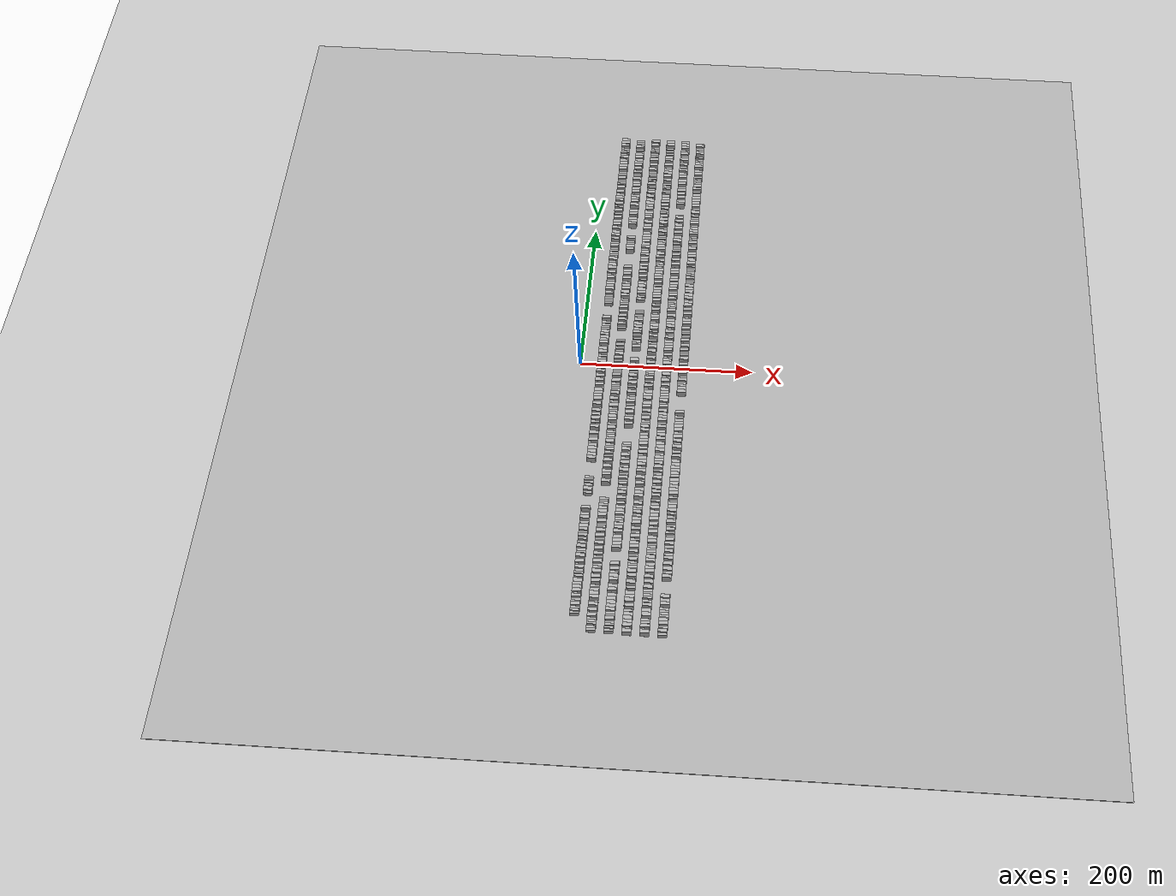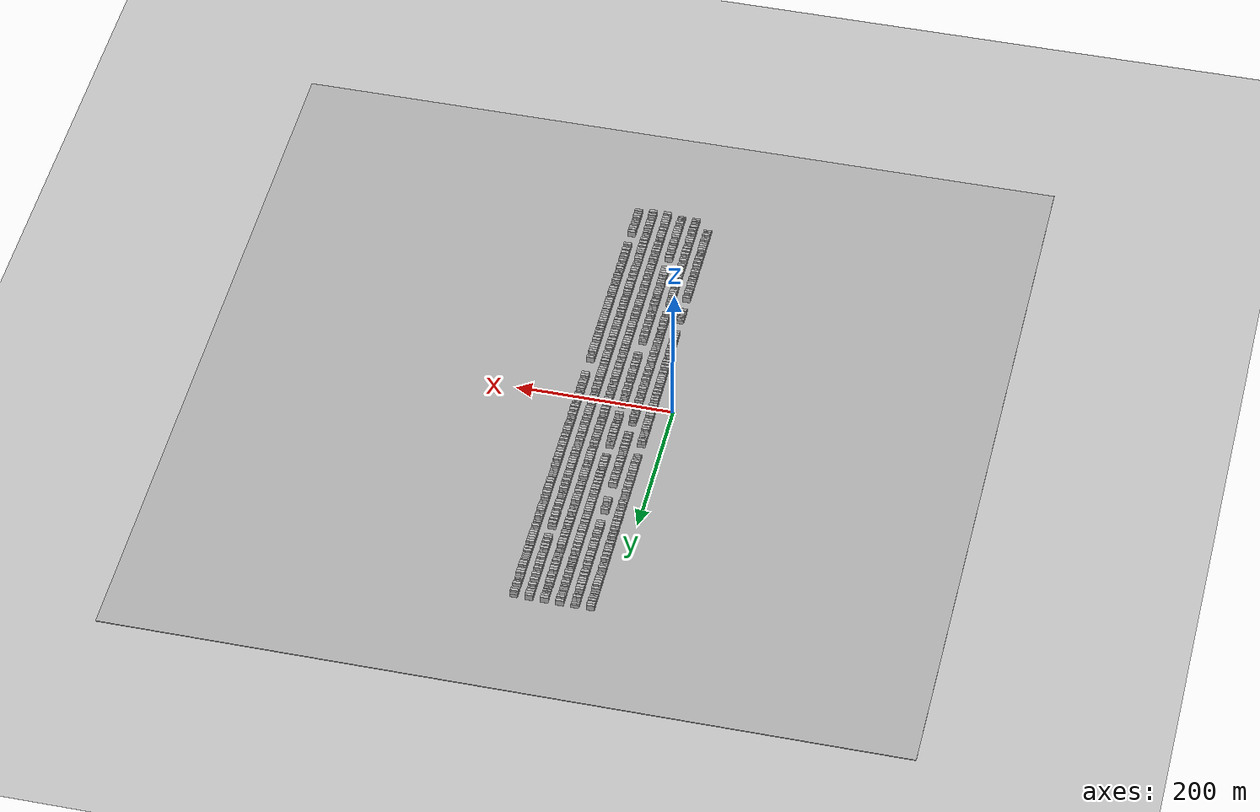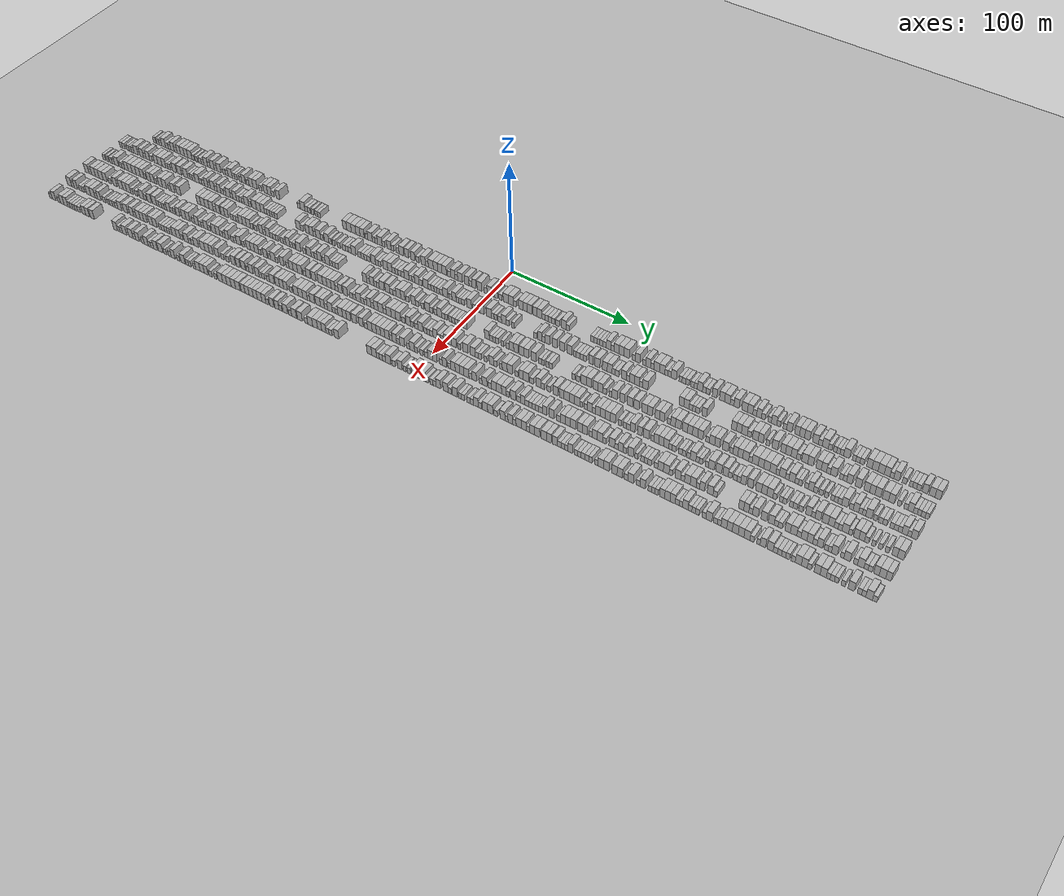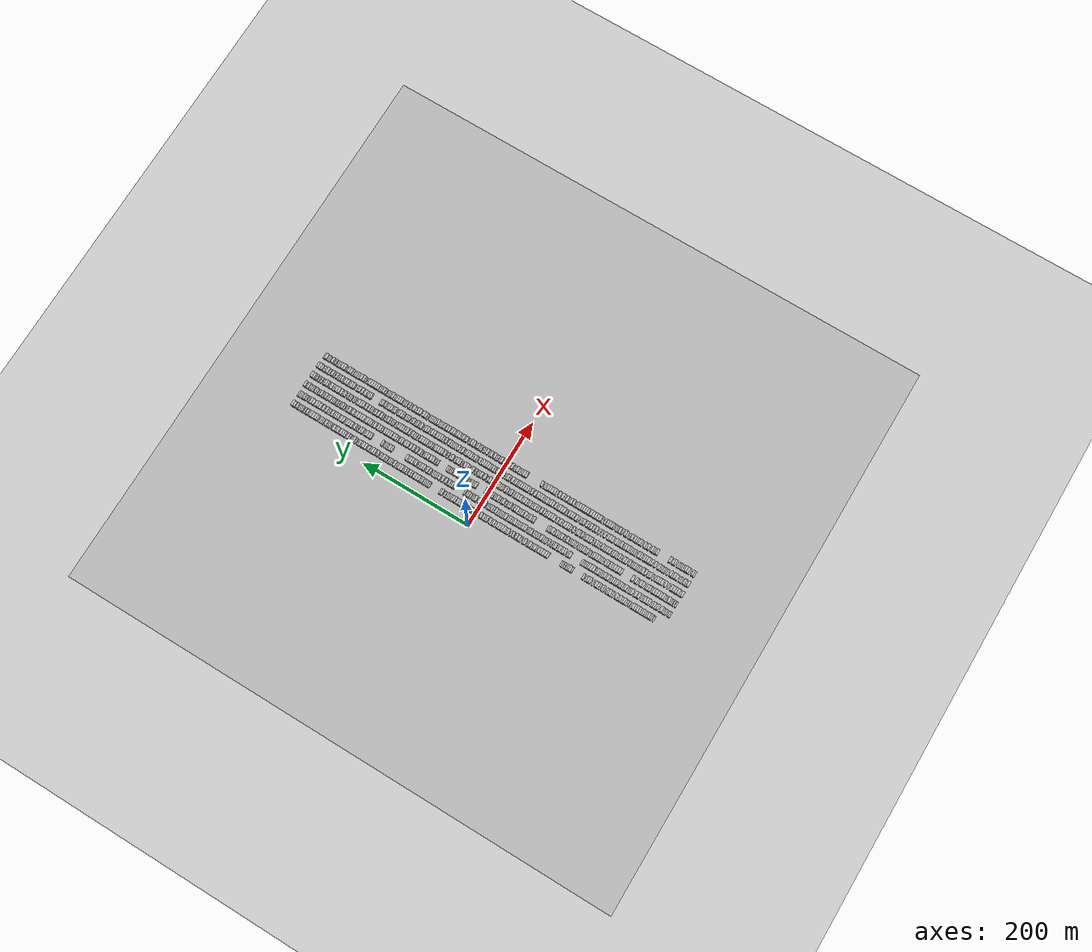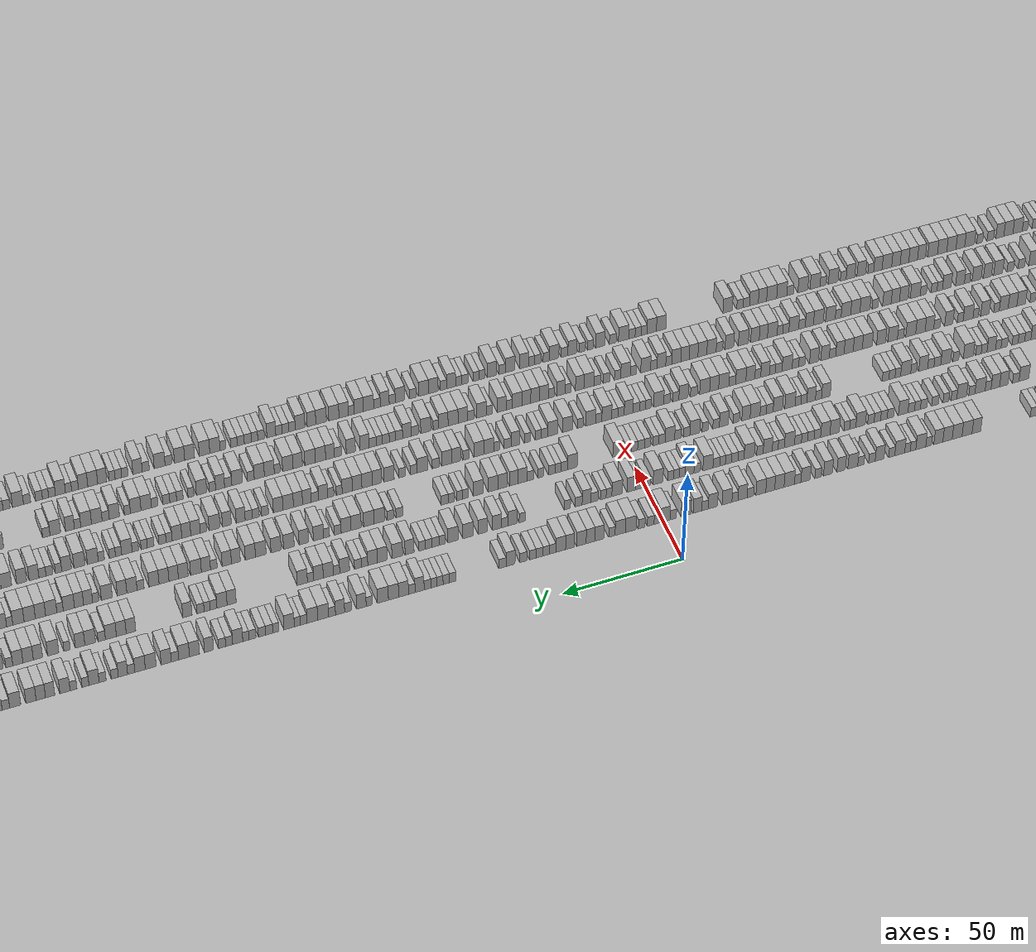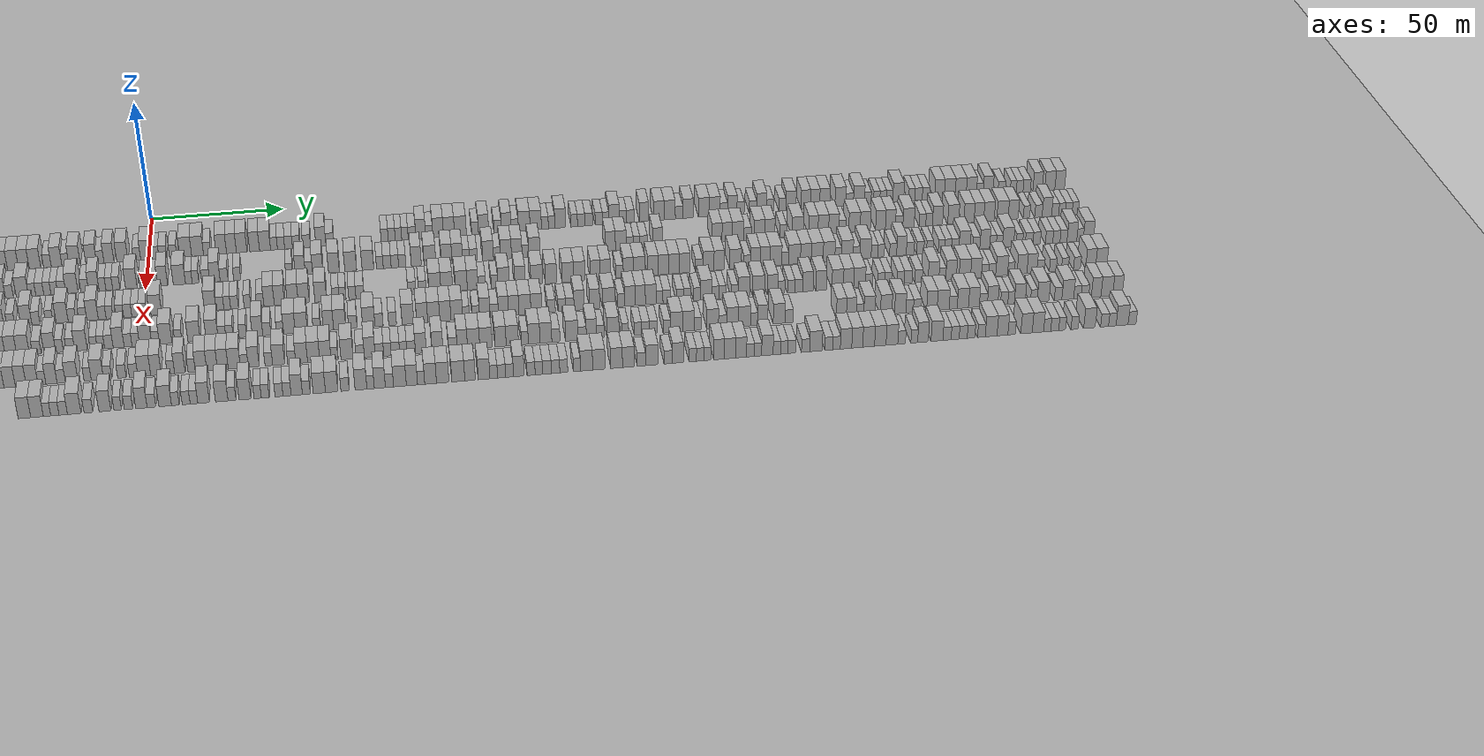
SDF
<?xml version="1.0" encoding="utf-8"?>

<sdf version="1.6">

   <world name="default">

      <gui fullscreen="0">

         <camera name="user_camera">

            <pose>-15 0 4.57585 0 0 0</pose>

            <view_controller>orbit</view_controller>

         </camera>

      </gui>

      <scene>

         <sky>

           <clouds>

             <speed>12</speed>

           </clouds>

         </sky>

         <ambient>0.4 0.4 0.4 1</ambient>

         <background>0.7 0.7 0.7 1</background>

         <shadows>1</shadows>

      </scene>

      <gravity>0 0 -9.8066</gravity>

      <magnetic_field>6e-06 2.3e-05 -4.2e-05</magnetic_field>

      <physics default="0" name="default_physics" type="ode">

         <ode>

            <solver>

               <type>quick</type>

               <iters>10</iters>

               <sor>1.0</sor>

               <use_dynamic_moi_rescaling>0</use_dynamic_moi_rescaling>

            </solver>

            <constraints>

               <cfm>0</cfm>

               <erp>0.2</erp>

               <contact_max_correcting_vel>100</contact_max_correcting_vel>

               <contact_surface_layer>0.001</contact_surface_layer>

            </constraints>

         </ode>

         <max_step_size>0.004</max_step_size>

         <real_time_factor>1</real_time_factor>

         <real_time_update_rate>250</real_time_update_rate>

      </physics>

      <light name="sun" type="directional">

         <cast_shadows>1</cast_shadows>

         <pose>0 0 10 0 0 0</pose>

         <diffuse>0.8 0.8 0.8 1</diffuse>

         <specular>0.2 0.2 0.2 1</specular>

         <attenuation>

            <range>1000</range>

            <constant>0.9</constant>

            <linear>0.01</linear>

            <quadratic>0.001</quadratic>

         </attenuation>

         <direction>-0.5 0.1 -0.9</direction>

      </light>

      <include>

         <name>ground_plane_1</name>

         <uri>model://HANNAS_ground_plane</uri>

         <pose>0 0 0  0 0 0</pose>

      </include>

      <include>

         <name>ground_plane_2</name>

         <uri>model://HANNAS_ground_plane</uri>

         <pose>100 0 0  0 0 0</pose>

      </include>

      <model name="building_1">

         <static>1</static>

         <pose frame="">25.0000 -329.0862 0 0.000000 0.000000 0.000000</pose>

         <link name="link">

            <pose frame="">0 0 3.00 0 0 0</pose>

            <collision name="collision">

               <geometry>

                  <box>

                     <size>10.0000 2.6092 6.0000</size>

                  </box>

               </geometry>

               <max_contacts>10</max_contacts>

               <surface>

                  <contact>

                     <ode/>

                  </contact>

                  <bounce/>

                  <friction>

                     <torsional>

                        <ode/>

                     </torsional>

                     <ode/>

                  </friction>

               </surface>

            </collision>

            <visual name="visual">

               <cast_shadows>0</cast_shadows>

               <geometry>

                  <box>

                     <size>10.0000 2.6092 6.0000</size>

                  </box>

               </geometry>

               <material>

                  <script>

                     <uri>model://HANNAS_wall/materials/scripts</uri>

                     <uri>model://HANNAS_wall/materials/textures</uri>

                     <name>vrc/HANNAS_wall</name>

                  </script>

               </material>

            </visual>

            <self_collide>0</self_collide>

            <enable_wind>0</enable_wind>

            <kinematic>0</kinematic>

         </link>

      </model>

      <model name="building_2">

         <static>1</static>

         <pose frame="">25.0000 -325.5485 0 0.000000 0.000000 0.000000</pose>

         <link name="link">

            <pose frame="">0 0 3.00 0 0 0</pose>

            <collision name="collision">

               <geometry>

                  <box>

                     <size>10.0000 2.4664 6.0000</size>

                  </box>

               </geometry>

               <max_contacts>10</max_contacts>

               <surface>

                  <contact>

                     <ode/>

                  </contact>

                  <bounce/>

                  <friction>

                     <torsional>

                        <ode/>

                     </torsional>

                     <ode/>

                  </friction>

               </surface>

            </collision>

            <visual name="visual">

               <cast_shadows>0</cast_shadows>

               <geometry>

                  <box>

                     <size>10.0000 2.4664 6.0000</size>

                  </box>

               </geometry>

               <material>

                  <script>

                     <uri>model://HANNAS_wall/materials/scripts</uri>

                     <uri>model://HANNAS_wall/materials/textures</uri>

                     <name>vrc/HANNAS_wall</name>

                  </script>

               </material>

            </visual>

            <self_collide>0</self_collide>

            <enable_wind>0</enable_wind>

            <kinematic>0</kinematic>

         </link>

      </model>

      <model name="building_3">

         <static>1</static>

         <pose frame="">25.0000 -322.8897 0 0.000000 0.000000 0.000000</pose>

         <link name="link">

            <pose frame="">0 0 3.00 0 0 0</pose>

            <collision name="collision">

               <geometry>

                  <box>

                     <size>10.0000 2.8511 6.0000</size>

                  </box>

               </geometry>

               <max_contacts>10</max_contacts>

               <surface>

                  <contact>

                     <ode/>

                  </contact>

                  <bounce/>

                  <friction>

                     <torsional>

                        <ode/>

                     </torsional>

                     <ode/>

                  </friction>

               </surface>

            </collision>

            <visual name="visual">

               <cast_shadows>0</cast_shadows>

               <geometry>

                  <box>

                     <size>10.0000 2.8511 6.0000</size>

                  </box>

               </geometry>

               <material>

                  <script>

                     <uri>model://HANNAS_wall/materials/scripts</uri>

                     <uri>model://HANNAS_wall/materials/textures</uri>

                     <name>vrc/HANNAS_wall</name>

                  </script>

               </material>

            </visual>

            <self_collide>0</self_collide>

            <enable_wind>0</enable_wind>

            <kinematic>0</kinematic>

         </link>

      </model>

      <model name="building_4">

         <static>1</static>

         <pose frame="">25.0000 -319.3970 0 0.000000 0.000000 0.000000</pose>

         <link name="link">

            <pose frame="">0 0 4.50 0 0 0</pose>

            <collision name="collision">

               <geometry>

                  <box>

                     <size>10.0000 4.1343 9.0000</size>

                  </box>

               </geometry>

               <max_contacts>10</max_contacts>

               <surface>

                  <contact>

                     <ode/>

                  </contact>

                  <bounce/>

                  <friction>

                     <torsional>

                        <ode/>

                     </torsional>

                     <ode/>

                  </friction>

               </surface>

            </collision>

            <visual name="visual">

               <cast_shadows>0</cast_shadows>

               <geometry>

                  <box>

                     <size>10.0000 4.1343 9.0000</size>

                  </box>

               </geometry>

               <material>

                  <script>

                     <uri>model://HANNAS_wall/materials/scripts</uri>

                     <uri>model://HANNAS_wall/materials/textures</uri>

                     <name>vrc/HANNAS_wall</name>

                  </script>

               </material>

            </visual>

            <self_collide>0</self_collide>

            <enable_wind>0</enable_wind>

            <kinematic>0</kinematic>

         </link>

      </model>

      <model name="building_5">

         <static>1</static>

         <pose frame="">25.0000 -315.8609 0 0.000000 0.000000 0.000000</pose>

         <link name="link">

            <pose frame="">0 0 3.00 0 0 0</pose>

            <collision name="collision">

               <geometry>

                  <box>

                     <size>10.0000 2.9378 6.0000</size>

                  </box>

               </geometry>

               <max_contacts>10</max_contacts>

               <surface>

                  <contact>

                     <ode/>

                  </contact>

                  <bounce/>

                  <friction>

                     <torsional>

                        <ode/>

                     </torsional>

                     <ode/>

                  </friction>

               </surface>

            </collision>

            <visual name="visual">

               <cast_shadows>0</cast_shadows>

               <geometry>

                  <box>

                     <size>10.0000 2.9378 6.0000</size>

                  </box>

               </geometry>

               <material>

                  <script>

                     <uri>model://HANNAS_wall/materials/scripts</uri>

                     <uri>model://HANNAS_wall/materials/textures</uri>

                     <name>vrc/HANNAS_wall</name>

                  </script>

               </material>

            </visual>

            <self_collide>0</self_collide>

            <enable_wind>0</enable_wind>

            <kinematic>0</kinematic>

         </link>

      </model>

      <model name="building_6">

         <static>1</static>

         <pose frame="">25.0000 -312.9622 0 0.000000 0.000000 0.000000</pose>

         <link name="link">

            <pose frame="">0 0 3.00 0 0 0</pose>

            <collision name="collision">

               <geometry>

                  <box>

                     <size>10.0000 2.8597 6.0000</size>

                  </box>

               </geometry>

               <max_contacts>10</max_contacts>

               <surface>

                  <contact>

                     <ode/>

                  </contact>

                  <bounce/>

                  <friction>

                     <torsional>

                        <ode/>

                     </torsional>

                     <ode/>

                  </friction>

               </surface>

            </collision>

            <visual name="visual">

               <cast_shadows>0</cast_shadows>

               <geometry>

                  <box>

                     <size>10.0000 2.8597 6.0000</size>

                  </box>

               </geometry>

               <material>

                  <script>

                     <uri>model://HANNAS_wall/materials/scripts</uri>

                     <uri>model://HANNAS_wall/materials/textures</uri>

                     <name>vrc/HANNAS_wall</name>

                  </script>

               </material>

            </visual>

            <self_collide>0</self_collide>

            <enable_wind>0</enable_wind>

            <kinematic>0</kinematic>

         </link>

      </model>

      <model name="building_7">

         <static>1</static>

         <pose frame="">25.0000 -309.6842 0 0.000000 0.000000 0.000000</pose>

         <link name="link">

            <pose frame="">0 0 4.50 0 0 0</pose>

            <collision name="collision">

               <geometry>

                  <box>

                     <size>10.0000 3.6963 9.0000</size>

                  </box>

               </geometry>

               <max_contacts>10</max_contacts>

               <surface>

                  <contact>

                     <ode/>

                  </contact>

                  <bounce/>

                  <friction>

                     <torsional>

                        <ode/>

                     </torsional>

                     <ode/>

                  </friction>

               </surface>

            </collision>

            <visual name="visual">

               <cast_shadows>0</cast_shadows>

               <geometry>

                  <box>

                     <size>10.0000 3.6963 9.0000</size>

                  </box>

               </geometry>

               <material>

                  <script>

                     <uri>model://HANNAS_wall/materials/scripts</uri>

                     <uri>model://HANNAS_wall/materials/textures</uri>

                     <name>vrc/HANNAS_wall</name>

                  </script>

               </material>

            </visual>

            <self_collide>0</self_collide>

            <enable_wind>0</enable_wind>

            <kinematic>0</kinematic>

         </link>

      </model>

      <model name="building_8">

         <static>1</static>

         <pose frame="">25.0000 -306.3947 0 0.000000 0.000000 0.000000</pose>

         <link name="link">

            <pose frame="">0 0 3.00 0 0 0</pose>

            <collision name="collision">

               <geometry>

                  <box>

                     <size>10.0000 2.8829 6.0000</size>

                  </box>

               </geometry>

               <max_contacts>10</max_contacts>

               <surface>

                  <contact>

                     <ode/>

                  </contact>

                  <bounce/>

                  <friction>

                     <torsional>

                        <ode/>

                     </torsional>

                     <ode/>

                  </friction>

               </surface>

            </collision>

            <visual name="visual">

               <cast_shadows>0</cast_shadows>

               <geometry>

                  <box>

                     <size>10.0000 2.8829 6.0000</size>

                  </box>

               </geometry>

               <material>

                  <script>

                     <uri>model://HANNAS_wall/materials/scripts</uri>

                     <uri>model://HANNAS_wall/materials/textures</uri>

                     <name>vrc/HANNAS_wall</name>

                  </script>

               </material>

            </visual>

            <self_collide>0</self_collide>

            <enable_wind>0</enable_wind>

            <kinematic>0</kinematic>

         </link>

      </model>

      <model name="building_9">

         <static>1</static>

         <pose frame="">25.0000 -303.0971 0 0.000000 0.000000 0.000000</pose>

         <link name="link">

            <pose frame="">0 0 4.50 0 0 0</pose>

            <collision name="collision">

               <geometry>

                  <box>

                     <size>10.0000 3.7122 9.0000</size>

                  </box>

               </geometry>

               <max_contacts>10</max_contacts>

               <surface>

                  <contact>

                     <ode/>

                  </contact>

                  <bounce/>

                  <friction>

                     <torsional>

                        <ode/>

                     </torsional>

                     <ode/>

                  </friction>

               </surface>

            </collision>

            <visual name="visual">

               <cast_shadows>0</cast_shadows>

               <geometry>

                  <box>

                     <size>10.0000 3.7122 9.0000</size>

                  </box>

               </geometry>

               <material>

                  <script>

                     <uri>model://HANNAS_wall/materials/scripts</uri>

                     <uri>model://HANNAS_wall/materials/textures</uri>

                     <name>vrc/HANNAS_wall</name>

                  </script>

               </material>

            </visual>

            <self_collide>0</self_collide>

            <enable_wind>0</enable_wind>

            <kinematic>0</kinematic>

         </link>

      </model>

      <model name="building_10">

         <static>1</static>

         <pose frame="">25.0000 -299.1672 0 0.000000 0.000000 0.000000</pose>

         <link name="link">

            <pose frame="">0 0 4.50 0 0 0</pose>

            <collision name="collision">

               <geometry>

                  <box>

                     <size>10.0000 4.1476 9.0000</size>

                  </box>

               </geometry>

               <max_contacts>10</max_contacts>

               <surface>

                  <contact>

                     <ode/>

                  </contact>

                  <bounce/>

                  <friction>

                     <torsional>

                        <ode/>

                     </torsional>

                     <ode/>

                  </friction>

               </surface>

            </collision>

            <visual name="visual">

               <cast_shadows>0</cast_shadows>

               <geometry>

                  <box>

                     <size>10.0000 4.1476 9.0000</size>

                  </box>

               </geometry>

               <material>

                  <script>

                     <uri>model://HANNAS_wall/materials/scripts</uri>

                     <uri>model://HANNAS_wall/materials/textures</uri>

                     <name>vrc/HANNAS_wall</name>

                  </script>

               </material>

            </visual>

            <self_collide>0</self_collide>

            <enable_wind>0</enable_wind>

            <kinematic>0</kinematic>

         </link>

      </model>

      <model name="building_11">

         <static>1</static>

         <pose frame="">25.0000 -295.2406 0 0.000000 0.000000 0.000000</pose>

         <link name="link">

            <pose frame="">0 0 4.50 0 0 0</pose>

            <collision name="collision">

               <geometry>

                  <box>

                     <size>10.0000 3.7056 9.0000</size>

                  </box>

               </geometry>

               <max_contacts>10</max_contacts>

               <surface>

                  <contact>

                     <ode/>

                  </contact>

                  <bounce/>

                  <friction>

                     <torsional>

                        <ode/>

                     </torsional>

                     <ode/>

                  </friction>

               </surface>

            </collision>

            <visual name="visual">

               <cast_shadows>0</cast_shadows>

               <geometry>

                  <box>

                     <size>10.0000 3.7056 9.0000</size>

                  </box>

               </geometry>

               <material>

                  <script>

                     <uri>model://HANNAS_wall/materials/scripts</uri>

                     <uri>model://HANNAS_wall/materials/textures</uri>

                     <name>vrc/HANNAS_wall</name>

                  </script>

               </material>

            </visual>

            <self_collide>0</self_collide>

            <enable_wind>0</enable_wind>

            <kinematic>0</kinematic>

         </link>

      </model>

      <model name="building_12">

         <static>1</static>

         <pose frame="">25.0000 -291.1981 0 0.000000 0.000000 0.000000</pose>

         <link name="link">

            <pose frame="">0 0 4.50 0 0 0</pose>

            <collision name="collision">

               <geometry>

                  <box>

                     <size>10.0000 4.3795 9.0000</size>

                  </box>

               </geometry>

               <max_contacts>10</max_contacts>

               <surface>

                  <contact>

                     <ode/>

                  </contact>

                  <bounce/>

                  <friction>

                     <torsional>

                        <ode/>

                     </torsional>

                     <ode/>

                  </friction>

               </surface>

            </collision>

            <visual name="visual">

               <cast_shadows>0</cast_shadows>

               <geometry>

                  <box>

                     <size>10.0000 4.3795 9.0000</size>

                  </box>

               </geometry>

               <material>

                  <script>

                     <uri>model://HANNAS_wall/materials/scripts</uri>

                     <uri>model://HANNAS_wall/materials/textures</uri>

                     <name>vrc/HANNAS_wall</name>

                  </script>

               </material>

            </visual>

            <self_collide>0</self_collide>

            <enable_wind>0</enable_wind>

            <kinematic>0</kinematic>

         </link>

      </model>

      <model name="building_13">

         <static>1</static>

         <pose frame="">25.0000 -287.6931 0 0.000000 0.000000 0.000000</pose>

         <link name="link">

            <pose frame="">0 0 3.00 0 0 0</pose>

            <collision name="collision">

               <geometry>

                  <box>

                     <size>10.0000 2.6304 6.0000</size>

                  </box>

               </geometry>

               <max_contacts>10</max_contacts>

               <surface>

                  <contact>

                     <ode/>

                  </contact>

                  <bounce/>

                  <friction>

                     <torsional>

                        <ode/>

                     </torsional>

                     <ode/>

                  </friction>

               </surface>

            </collision>

            <visual name="visual">

               <cast_shadows>0</cast_shadows>

               <geometry>

                  <box>

                     <size>10.0000 2.6304 6.0000</size>

                  </box>

               </geometry>

               <material>

                  <script>

                     <uri>model://HANNAS_wall/materials/scripts</uri>

                     <uri>model://HANNAS_wall/materials/textures</uri>

                     <name>vrc/HANNAS_wall</name>

                  </script>

               </material>

            </visual>

            <self_collide>0</self_collide>

            <enable_wind>0</enable_wind>

            <kinematic>0</kinematic>

         </link>

      </model>

      <model name="building_14">

         <static>1</static>

         <pose frame="">25.0000 -284.0967 0 0.000000 0.000000 0.000000</pose>

         <link name="link">

            <pose frame="">0 0 3.00 0 0 0</pose>

            <collision name="collision">

               <geometry>

                  <box>

                     <size>10.0000 2.5624 6.0000</size>

                  </box>

               </geometry>

               <max_contacts>10</max_contacts>

               <surface>

                  <contact>

                     <ode/>

                  </contact>

                  <bounce/>

                  <friction>

                     <torsional>

                        <ode/>

                     </torsional>

                     <ode/>

                  </friction>

               </surface>

            </collision>

            <visual name="visual">

               <cast_shadows>0</cast_shadows>

               <geometry>

                  <box>

                     <size>10.0000 2.5624 6.0000</size>

                  </box>

               </geometry>

               <material>

                  <script>

                     <uri>model://HANNAS_wall/materials/scripts</uri>

                     <uri>model://HANNAS_wall/materials/textures</uri>

                     <name>vrc/HANNAS_wall</name>

                  </script>

               </material>

            </visual>

            <self_collide>0</self_collide>

            <enable_wind>0</enable_wind>

            <kinematic>0</kinematic>

         </link>

      </model>

      <model name="building_15">

         <static>1</static>

         <pose frame="">25.0000 -280.4607 0 0.000000 0.000000 0.000000</pose>

         <link name="link">

            <pose frame="">0 0 3.00 0 0 0</pose>

            <collision name="collision">

               <geometry>

                  <box>

                     <size>10.0000 2.7096 6.0000</size>

                  </box>

               </geometry>

               <max_contacts>10</max_contacts>

               <surface>

                  <contact>

                     <ode/>

                  </contact>

                  <bounce/>

                  <friction>

                     <torsional>

                        <ode/>

                     </torsional>

                     <ode/>

                  </friction>

               </surface>

            </collision>

            <visual name="visual">

               <cast_shadows>0</cast_shadows>

               <geometry>

                  <box>

                     <size>10.0000 2.7096 6.0000</size>

                  </box>

               </geometry>

               <material>

                  <script>

                     <uri>model://HANNAS_wall/materials/scripts</uri>

                     <uri>model://HANNAS_wall/materials/textures</uri>

                     <name>vrc/HANNAS_wall</name>

                  </script>

               </material>

            </visual>

            <self_collide>0</self_collide>

            <enable_wind>0</enable_wind>

            <kinematic>0</kinematic>

         </link>

      </model>

      <model name="building_16">

         <static>1</static>

         <pose frame="">25.0000 -277.7603 0 0.000000 0.000000 0.000000</pose>

         <link name="link">

            <pose frame="">0 0 3.00 0 0 0</pose>

            <collision name="collision">

               <geometry>

                  <box>

                     <size>10.0000 2.6912 6.0000</size>

                  </box>

               </geometry>

               <max_contacts>10</max_contacts>

               <surface>

                  <contact>

                     <ode/>

                  </contact>

                  <bounce/>

                  <friction>

                     <torsional>

                        <ode/>

                     </torsional>

                     <ode/>

                  </friction>

               </surface>

            </collision>

            <visual name="visual">

               <cast_shadows>0</cast_shadows>

               <geometry>

                  <box>

                     <size>10.0000 2.6912 6.0000</size>

                  </box>

               </geometry>

               <material>

                  <script>

                     <uri>model://HANNAS_wall/materials/scripts</uri>

                     <uri>model://HANNAS_wall/materials/textures</uri>

                     <name>vrc/HANNAS_wall</name>

                  </script>

               </material>

            </visual>

            <self_collide>0</self_collide>

            <enable_wind>0</enable_wind>

            <kinematic>0</kinematic>

         </link>

      </model>

      <model name="building_17">

         <static>1</static>

         <pose frame="">25.0000 -274.4151 0 0.000000 0.000000 0.000000</pose>

         <link name="link">

            <pose frame="">0 0 4.50 0 0 0</pose>

            <collision name="collision">

               <geometry>

                  <box>

                     <size>10.0000 3.9991 9.0000</size>

                  </box>

               </geometry>

               <max_contacts>10</max_contacts>

               <surface>

                  <contact>

                     <ode/>

                  </contact>

                  <bounce/>

                  <friction>

                     <torsional>

                        <ode/>

                     </torsional>

                     <ode/>

                  </friction>

               </surface>

            </collision>

            <visual name="visual">

               <cast_shadows>0</cast_shadows>

               <geometry>

                  <box>

                     <size>10.0000 3.9991 9.0000</size>

                  </box>

               </geometry>

               <material>

                  <script>

                     <uri>model://HANNAS_wall/materials/scripts</uri>

                     <uri>model://HANNAS_wall/materials/textures</uri>

                     <name>vrc/HANNAS_wall</name>

                  </script>

               </material>

            </visual>

            <self_collide>0</self_collide>

            <enable_wind>0</enable_wind>

            <kinematic>0</kinematic>

         </link>

      </model>

      <model name="building_18">

         <static>1</static>

         <pose frame="">25.0000 -270.9546 0 0.000000 0.000000 0.000000</pose>

         <link name="link">

            <pose frame="">0 0 3.00 0 0 0</pose>

            <collision name="collision">

               <geometry>

                  <box>

                     <size>10.0000 2.9220 6.0000</size>

                  </box>

               </geometry>

               <max_contacts>10</max_contacts>

               <surface>

                  <contact>

                     <ode/>

                  </contact>

                  <bounce/>

                  <friction>

                     <torsional>

                        <ode/>

                     </torsional>

                     <ode/>

                  </friction>

               </surface>

            </collision>

            <visual name="visual">

               <cast_shadows>0</cast_shadows>

               <geometry>

                  <box>

                     <size>10.0000 2.9220 6.0000</size>

                  </box>

               </geometry>

               <material>

                  <script>

                     <uri>model://HANNAS_wall/materials/scripts</uri>

                     <uri>model://HANNAS_wall/materials/textures</uri>

                     <name>vrc/HANNAS_wall</name>

                  </script>

               </material>

            </visual>

            <self_collide>0</self_collide>

            <enable_wind>0</enable_wind>

            <kinematic>0</kinematic>

         </link>

      </model>

      <model name="building_19">

         <static>1</static>

         <pose frame="">25.0000 -267.4674 0 0.000000 0.000000 0.000000</pose>

         <link name="link">

            <pose frame="">0 0 4.50 0 0 0</pose>

            <collision name="collision">

               <geometry>

                  <box>

                     <size>10.0000 4.0524 9.0000</size>

                  </box>

               </geometry>

               <max_contacts>10</max_contacts>

               <surface>

                  <contact>

                     <ode/>

                  </contact>

                  <bounce/>

                  <friction>

                     <torsional>

                        <ode/>

                     </torsional>

                     <ode/>

                  </friction>

               </surface>

            </collision>

            <visual name="visual">

               <cast_shadows>0</cast_shadows>

               <geometry>

                  <box>

                     <size>10.0000 4.0524 9.0000</size>

                  </box>

               </geometry>

               <material>

                  <script>

                     <uri>model://HANNAS_wall/materials/scripts</uri>

                     <uri>model://HANNAS_wall/materials/textures</uri>

                     <name>vrc/HANNAS_wall</name>

                  </script>

               </material>

            </visual>

            <self_collide>0</self_collide>

            <enable_wind>0</enable_wind>

            <kinematic>0</kinematic>

         </link>

      </model>

      <model name="building_20">

         <static>1</static>

         <pose frame="">25.0000 -264.0373 0 0.000000 0.000000 0.000000</pose>

         <link name="link">

            <pose frame="">0 0 3.00 0 0 0</pose>

            <collision name="collision">

               <geometry>

                  <box>

                     <size>10.0000 2.8078 6.0000</size>

                  </box>

               </geometry>

               <max_contacts>10</max_contacts>

               <surface>

                  <contact>

                     <ode/>

                  </contact>

                  <bounce/>

                  <friction>

                     <torsional>

                        <ode/>

                     </torsional>

                     <ode/>

                  </friction>

               </surface>

            </collision>

            <visual name="visual">

               <cast_shadows>0</cast_shadows>

               <geometry>

                  <box>

                     <size>10.0000 2.8078 6.0000</size>

                  </box>

               </geometry>

               <material>

                  <script>

                     <uri>model://HANNAS_wall/materials/scripts</uri>

                     <uri>model://HANNAS_wall/materials/textures</uri>

                     <name>vrc/HANNAS_wall</name>

                  </script>

               </material>

            </visual>

            <self_collide>0</self_collide>

            <enable_wind>0</enable_wind>

            <kinematic>0</kinematic>

         </link>

      </model>

      <model name="building_21">

         <static>1</static>

         <pose frame="">25.0000 -260.4896 0 0.000000 0.000000 0.000000</pose>

         <link name="link">

            <pose frame="">0 0 4.50 0 0 0</pose>

            <collision name="collision">

               <geometry>

                  <box>

                     <size>10.0000 4.2876 9.0000</size>

                  </box>

               </geometry>

               <max_contacts>10</max_contacts>

               <surface>

                  <contact>

                     <ode/>

                  </contact>

                  <bounce/>

                  <friction>

                     <torsional>

                        <ode/>

                     </torsional>

                     <ode/>

                  </friction>

               </surface>

            </collision>

            <visual name="visual">

               <cast_shadows>0</cast_shadows>

               <geometry>

                  <box>

                     <size>10.0000 4.2876 9.0000</size>

                  </box>

               </geometry>

               <material>

                  <script>

                     <uri>model://HANNAS_wall/materials/scripts</uri>

                     <uri>model://HANNAS_wall/materials/textures</uri>

                     <name>vrc/HANNAS_wall</name>

                  </script>

               </material>

            </visual>

            <self_collide>0</self_collide>

            <enable_wind>0</enable_wind>

            <kinematic>0</kinematic>

         </link>

      </model>

      <model name="building_22">

         <static>1</static>

         <pose frame="">25.0000 -255.0336 0 0.000000 0.000000 0.000000</pose>

         <link name="link">

            <pose frame="">0 0 3.00 0 0 0</pose>

            <collision name="collision">

               <geometry>

                  <box>

                     <size>10.0000 2.6244 6.0000</size>

                  </box>

               </geometry>

               <max_contacts>10</max_contacts>

               <surface>

                  <contact>

                     <ode/>

                  </contact>

                  <bounce/>

                  <friction>

                     <torsional>

                        <ode/>

                     </torsional>

                     <ode/>

                  </friction>

               </surface>

            </collision>

            <visual name="visual">

               <cast_shadows>0</cast_shadows>

               <geometry>

                  <box>

                     <size>10.0000 2.6244 6.0000</size>

                  </box>

               </geometry>

               <material>

                  <script>

                     <uri>model://HANNAS_wall/materials/scripts</uri>

                     <uri>model://HANNAS_wall/materials/textures</uri>

                     <name>vrc/HANNAS_wall</name>

                  </script>

               </material>

            </visual>

            <self_collide>0</self_collide>

            <enable_wind>0</enable_wind>

            <kinematic>0</kinematic>

         </link>

      </model>

      <model name="building_23">

         <static>1</static>

         <pose frame="">25.0000 -252.3380 0 0.000000 0.000000 0.000000</pose>

         <link name="link">

            <pose frame="">0 0 3.00 0 0 0</pose>

            <collision name="collision">

               <geometry>

                  <box>

                     <size>10.0000 2.7667 6.0000</size>

                  </box>

               </geometry>

               <max_contacts>10</max_contacts>

               <surface>

                  <contact>

                     <ode/>

                  </contact>

                  <bounce/>

                  <friction>

                     <torsional>

                        <ode/>

                     </torsional>

                     <ode/>

                  </friction>

               </surface>

            </collision>

            <visual name="visual">

               <cast_shadows>0</cast_shadows>

               <geometry>

                  <box>

                     <size>10.0000 2.7667 6.0000</size>

                  </box>

               </geometry>

               <material>

                  <script>

                     <uri>model://HANNAS_wall/materials/scripts</uri>

                     <uri>model://HANNAS_wall/materials/textures</uri>

                     <name>vrc/HANNAS_wall</name>

                  </script>

               </material>

            </visual>

            <self_collide>0</self_collide>

            <enable_wind>0</enable_wind>

            <kinematic>0</kinematic>

         </link>

      </model>

      <model name="building_24">

         <static>1</static>

         <pose frame="">25.0000 -248.8088 0 0.000000 0.000000 0.000000</pose>

         <link name="link">

            <pose frame="">0 0 4.50 0 0 0</pose>

            <collision name="collision">

               <geometry>

                  <box>

                     <size>10.0000 4.2918 9.0000</size>

                  </box>

               </geometry>

               <max_contacts>10</max_contacts>

               <surface>

                  <contact>

                     <ode/>

                  </contact>

                  <bounce/>

                  <friction>

                     <torsional>

                        <ode/>

                     </torsional>

                     <ode/>

                  </friction>

               </surface>

            </collision>

            <visual name="visual">

               <cast_shadows>0</cast_shadows>

               <geometry>

                  <box>

                     <size>10.0000 4.2918 9.0000</size>

                  </box>

               </geometry>

               <material>

                  <script>

                     <uri>model://HANNAS_wall/materials/scripts</uri>

                     <uri>model://HANNAS_wall/materials/textures</uri>

                     <name>vrc/HANNAS_wall</name>

                  </script>

               </material>

            </visual>

            <self_collide>0</self_collide>

            <enable_wind>0</enable_wind>

            <kinematic>0</kinematic>

         </link>

      </model>

      <model name="building_25">

         <static>1</static>

         <pose frame="">25.0000 -245.2868 0 0.000000 0.000000 0.000000</pose>

         <link name="link">

            <pose frame="">0 0 3.00 0 0 0</pose>

            <collision name="collision">

               <geometry>

                  <box>

                     <size>10.0000 2.7521 6.0000</size>

                  </box>

               </geometry>

               <max_contacts>10</max_contacts>

               <surface>

                  <contact>

                     <ode/>

                  </contact>

                  <bounce/>

                  <friction>

                     <torsional>

                        <ode/>

                     </torsional>

                     <ode/>

                  </friction>

               </surface>

            </collision>

            <visual name="visual">

               <cast_shadows>0</cast_shadows>

               <geometry>

                  <box>

                     <size>10.0000 2.7521 6.0000</size>

                  </box>

               </geometry>

               <material>

                  <script>

                     <uri>model://HANNAS_wall/materials/scripts</uri>

                     <uri>model://HANNAS_wall/materials/textures</uri>

                     <name>vrc/HANNAS_wall</name>

                  </script>

               </material>

            </visual>

            <self_collide>0</self_collide>

            <enable_wind>0</enable_wind>

            <kinematic>0</kinematic>

         </link>

      </model>

      <model name="building_26">

         <static>1</static>

         <pose frame="">25.0000 -242.6461 0 0.000000 0.000000 0.000000</pose>

         <link name="link">

            <pose frame="">0 0 3.00 0 0 0</pose>

            <collision name="collision">

               <geometry>

                  <box>

                     <size>10.0000 2.5293 6.0000</size>

                  </box>

               </geometry>

               <max_contacts>10</max_contacts>

               <surface>

                  <contact>

                     <ode/>

                  </contact>

                  <bounce/>

                  <friction>

                     <torsional>

                        <ode/>

                     </torsional>

                     <ode/>

                  </friction>

               </surface>

            </collision>

            <visual name="visual">

               <cast_shadows>0</cast_shadows>

               <geometry>

                  <box>

                     <size>10.0000 2.5293 6.0000</size>

                  </box>

               </geometry>

               <material>

                  <script>

                     <uri>model://HANNAS_wall/materials/scripts</uri>

                     <uri>model://HANNAS_wall/materials/textures</uri>

                     <name>vrc/HANNAS_wall</name>

                  </script>

               </material>

            </visual>

            <self_collide>0</self_collide>

            <enable_wind>0</enable_wind>

            <kinematic>0</kinematic>

         </link>

      </model>

      <model name="building_27">

         <static>1</static>

         <pose frame="">25.0000 -238.0825 0 0.000000 0.000000 0.000000</pose>

         <link name="link">

            <pose frame="">0 0 3.00 0 0 0</pose>

            <collision name="collision">

               <geometry>

                  <box>

                     <size>10.0000 2.5979 6.0000</size>

                  </box>

               </geometry>

               <max_contacts>10</max_contacts>

               <surface>

                  <contact>

                     <ode/>

                  </contact>

                  <bounce/>

                  <friction>

                     <torsional>

                        <ode/>

                     </torsional>

                     <ode/>

                  </friction>

               </surface>

            </collision>

            <visual name="visual">

               <cast_shadows>0</cast_shadows>

               <geometry>

                  <box>

                     <size>10.0000 2.5979 6.0000</size>

                  </box>

               </geometry>

               <material>

                  <script>

                     <uri>model://HANNAS_wall/materials/scripts</uri>

                     <uri>model://HANNAS_wall/materials/textures</uri>

                     <name>vrc/HANNAS_wall</name>

                  </script>

               </material>

            </visual>

            <self_collide>0</self_collide>

            <enable_wind>0</enable_wind>

            <kinematic>0</kinematic>

         </link>

      </model>

      <model name="building_28">

         <static>1</static>

         <pose frame="">25.0000 -234.9409 0 0.000000 0.000000 0.000000</pose>

         <link name="link">

            <pose frame="">0 0 4.50 0 0 0</pose>

            <collision name="collision">

               <geometry>

                  <box>

                     <size>10.0000 3.6854 9.0000</size>

                  </box>

               </geometry>

               <max_contacts>10</max_contacts>

               <surface>

                  <contact>

                     <ode/>

                  </contact>

                  <bounce/>

                  <friction>

                     <torsional>

                        <ode/>

                     </torsional>

                     <ode/>

                  </friction>

               </surface>

            </collision>

            <visual name="visual">

               <cast_shadows>0</cast_shadows>

               <geometry>

                  <box>

                     <size>10.0000 3.6854 9.0000</size>

                  </box>

               </geometry>

               <material>

                  <script>

                     <uri>model://HANNAS_wall/materials/scripts</uri>

                     <uri>model://HANNAS_wall/materials/textures</uri>

                     <name>vrc/HANNAS_wall</name>

                  </script>

               </material>

            </visual>

            <self_collide>0</self_collide>

            <enable_wind>0</enable_wind>

            <kinematic>0</kinematic>

         </link>

      </model>

      <model name="building_29">

         <static>1</static>

         <pose frame="">25.0000 -230.6805 0 0.000000 0.000000 0.000000</pose>

         <link name="link">

            <pose frame="">0 0 3.00 0 0 0</pose>

            <collision name="collision">

               <geometry>

                  <box>

                     <size>10.0000 2.8354 6.0000</size>

                  </box>

               </geometry>

               <max_contacts>10</max_contacts>

               <surface>

                  <contact>

                     <ode/>

                  </contact>

                  <bounce/>

                  <friction>

                     <torsional>

                        <ode/>

                     </torsional>

                     <ode/>

                  </friction>

               </surface>

            </collision>

            <visual name="visual">

               <cast_shadows>0</cast_shadows>

               <geometry>

                  <box>

                     <size>10.0000 2.8354 6.0000</size>

                  </box>

               </geometry>

               <material>

                  <script>

                     <uri>model://HANNAS_wall/materials/scripts</uri>

                     <uri>model://HANNAS_wall/materials/textures</uri>

                     <name>vrc/HANNAS_wall</name>

                  </script>

               </material>

            </visual>

            <self_collide>0</self_collide>

            <enable_wind>0</enable_wind>

            <kinematic>0</kinematic>

         </link>

      </model>

      <model name="building_30">

         <static>1</static>

         <pose frame="">25.0000 -227.3149 0 0.000000 0.000000 0.000000</pose>

         <link name="link">

            <pose frame="">0 0 4.50 0 0 0</pose>

            <collision name="collision">

               <geometry>

                  <box>

                     <size>10.0000 3.8957 9.0000</size>

                  </box>

               </geometry>

               <max_contacts>10</max_contacts>

               <surface>

                  <contact>

                     <ode/>

                  </contact>

                  <bounce/>

                  <friction>

                     <torsional>

                        <ode/>

                     </torsional>

                     <ode/>

                  </friction>

               </surface>

            </collision>

            <visual name="visual">

               <cast_shadows>0</cast_shadows>

               <geometry>

                  <box>

                     <size>10.0000 3.8957 9.0000</size>

                  </box>

               </geometry>

               <material>

                  <script>

                     <uri>model://HANNAS_wall/materials/scripts</uri>

                     <uri>model://HANNAS_wall/materials/textures</uri>

                     <name>vrc/HANNAS_wall</name>

                  </script>

               </material>

            </visual>

            <self_collide>0</self_collide>

            <enable_wind>0</enable_wind>

            <kinematic>0</kinematic>

         </link>

      </model>

      <model name="building_31">

         <static>1</static>

         <pose frame="">25.0000 -223.2357 0 0.000000 0.000000 0.000000</pose>

         <link name="link">

            <pose frame="">0 0 4.50 0 0 0</pose>

            <collision name="collision">

               <geometry>

                  <box>

                     <size>10.0000 4.2628 9.0000</size>

                  </box>

               </geometry>

               <max_contacts>10</max_contacts>

               <surface>

                  <contact>

                     <ode/>

                  </contact>

                  <bounce/>

                  <friction>

                     <torsional>

                        <ode/>

                     </torsional>

                     <ode/>

                  </friction>

               </surface>

            </collision>

            <visual name="visual">

               <cast_shadows>0</cast_shadows>

               <geometry>

                  <box>

                     <size>10.0000 4.2628 9.0000</size>

                  </box>

               </geometry>

               <material>

                  <script>

                     <uri>model://HANNAS_wall/materials/scripts</uri>

                     <uri>model://HANNAS_wall/materials/textures</uri>

                     <name>vrc/HANNAS_wall</name>

                  </script>

               </material>

            </visual>

            <self_collide>0</self_collide>

            <enable_wind>0</enable_wind>

            <kinematic>0</kinematic>

         </link>

      </model>

      <model name="building_32">

         <static>1</static>

         <pose frame="">25.0000 -217.6826 0 0.000000 0.000000 0.000000</pose>

         <link name="link">

            <pose frame="">0 0 3.00 0 0 0</pose>

            <collision name="collision">

               <geometry>

                  <box>

                     <size>10.0000 2.8433 6.0000</size>

                  </box>

               </geometry>

               <max_contacts>10</max_contacts>

               <surface>

                  <contact>

                     <ode/>

                  </contact>

                  <bounce/>

                  <friction>

                     <torsional>

                        <ode/>

                     </torsional>

                     <ode/>

                  </friction>

               </surface>

            </collision>

            <visual name="visual">

               <cast_shadows>0</cast_shadows>

               <geometry>

                  <box>

                     <size>10.0000 2.8433 6.0000</size>

                  </box>

               </geometry>

               <material>

                  <script>

                     <uri>model://HANNAS_wall/materials/scripts</uri>

                     <uri>model://HANNAS_wall/materials/textures</uri>

                     <name>vrc/HANNAS_wall</name>

                  </script>

               </material>

            </visual>

            <self_collide>0</self_collide>

            <enable_wind>0</enable_wind>

            <kinematic>0</kinematic>

         </link>

      </model>

      <model name="building_33">

         <static>1</static>

         <pose frame="">25.0000 -212.3376 0 0.000000 0.000000 0.000000</pose>

         <link name="link">

            <pose frame="">0 0 4.50 0 0 0</pose>

            <collision name="collision">

               <geometry>

                  <box>

                     <size>10.0000 3.8468 9.0000</size>

                  </box>

               </geometry>

               <max_contacts>10</max_contacts>

               <surface>

                  <contact>

                     <ode/>

                  </contact>

                  <bounce/>

                  <friction>

                     <torsional>

                        <ode/>

                     </torsional>

                     <ode/>

                  </friction>

               </surface>

            </collision>

            <visual name="visual">

               <cast_shadows>0</cast_shadows>

               <geometry>

                  <box>

                     <size>10.0000 3.8468 9.0000</size>

                  </box>

               </geometry>

               <material>

                  <script>

                     <uri>model://HANNAS_wall/materials/scripts</uri>

                     <uri>model://HANNAS_wall/materials/textures</uri>

                     <name>vrc/HANNAS_wall</name>

                  </script>

               </material>

            </visual>

            <self_collide>0</self_collide>

            <enable_wind>0</enable_wind>

            <kinematic>0</kinematic>

         </link>

      </model>

      <model name="building_34">

         <static>1</static>

         <pose frame="">25.0000 -208.5184 0 0.000000 0.000000 0.000000</pose>

         <link name="link">

            <pose frame="">0 0 4.50 0 0 0</pose>

            <collision name="collision">

               <geometry>

                  <box>

                     <size>10.0000 3.7915 9.0000</size>

                  </box>

               </geometry>

               <max_contacts>10</max_contacts>

               <surface>

                  <contact>

                     <ode/>

                  </contact>

                  <bounce/>

                  <friction>

                     <torsional>

                        <ode/>

                     </torsional>

                     <ode/>

                  </friction>

               </surface>

            </collision>

            <visual name="visual">

               <cast_shadows>0</cast_shadows>

               <geometry>

                  <box>

                     <size>10.0000 3.7915 9.0000</size>

                  </box>

               </geometry>

               <material>

                  <script>

                     <uri>model://HANNAS_wall/materials/scripts</uri>

                     <uri>model://HANNAS_wall/materials/textures</uri>

                     <name>vrc/HANNAS_wall</name>

                  </script>

               </material>

            </visual>

            <self_collide>0</self_collide>

            <enable_wind>0</enable_wind>

            <kinematic>0</kinematic>

         </link>

      </model>

      <model name="building_35">

         <static>1</static>

         <pose frame="">25.0000 -205.2065 0 0.000000 0.000000 0.000000</pose>

         <link name="link">

            <pose frame="">0 0 3.00 0 0 0</pose>

            <collision name="collision">

               <geometry>

                  <box>

                     <size>10.0000 2.8323 6.0000</size>

                  </box>

               </geometry>

               <max_contacts>10</max_contacts>

               <surface>

                  <contact>

                     <ode/>

                  </contact>

                  <bounce/>

                  <friction>

                     <torsional>

                        <ode/>

                     </torsional>

                     <ode/>

                  </friction>

               </surface>

            </collision>

            <visual name="visual">

               <cast_shadows>0</cast_shadows>

               <geometry>

                  <box>

                     <size>10.0000 2.8323 6.0000</size>

                  </box>

               </geometry>

               <material>

                  <script>

                     <uri>model://HANNAS_wall/materials/scripts</uri>

                     <uri>model://HANNAS_wall/materials/textures</uri>

                     <name>vrc/HANNAS_wall</name>

                  </script>

               </material>

            </visual>

            <self_collide>0</self_collide>

            <enable_wind>0</enable_wind>

            <kinematic>0</kinematic>

         </link>

      </model>

      <model name="building_36">

         <static>1</static>

         <pose frame="">25.0000 -199.8951 0 0.000000 0.000000 0.000000</pose>

         <link name="link">

            <pose frame="">0 0 4.50 0 0 0</pose>

            <collision name="collision">

               <geometry>

                  <box>

                     <size>10.0000 3.7905 9.0000</size>

                  </box>

               </geometry>

               <max_contacts>10</max_contacts>

               <surface>

                  <contact>

                     <ode/>

                  </contact>

                  <bounce/>

                  <friction>

                     <torsional>

                        <ode/>

                     </torsional>

                     <ode/>

                  </friction>

               </surface>

            </collision>

            <visual name="visual">

               <cast_shadows>0</cast_shadows>

               <geometry>

                  <box>

                     <size>10.0000 3.7905 9.0000</size>

                  </box>

               </geometry>

               <material>

                  <script>

                     <uri>model://HANNAS_wall/materials/scripts</uri>

                     <uri>model://HANNAS_wall/materials/textures</uri>

                     <name>vrc/HANNAS_wall</name>

                  </script>

               </material>

            </visual>

            <self_collide>0</self_collide>

            <enable_wind>0</enable_wind>

            <kinematic>0</kinematic>

         </link>

      </model>

      <model name="building_37">

         <static>1</static>

         <pose frame="">25.0000 -178.9558 0 0.000000 0.000000 0.000000</pose>

         <link name="link">

            <pose frame="">0 0 3.00 0 0 0</pose>

            <collision name="collision">

               <geometry>

                  <box>

                     <size>10.0000 2.6960 6.0000</size>

                  </box>

               </geometry>

               <max_contacts>10</max_contacts>

               <surface>

                  <contact>

                     <ode/>

                  </contact>

                  <bounce/>

                  <friction>

                     <torsional>

                        <ode/>

                     </torsional>

                     <ode/>

                  </friction>

               </surface>

            </collision>

            <visual name="visual">

               <cast_shadows>0</cast_shadows>

               <geometry>

                  <box>

                     <size>10.0000 2.6960 6.0000</size>

                  </box>

               </geometry>

               <material>

                  <script>

                     <uri>model://HANNAS_wall/materials/scripts</uri>

                     <uri>model://HANNAS_wall/materials/textures</uri>

                     <name>vrc/HANNAS_wall</name>

                  </script>

               </material>

            </visual>

            <self_collide>0</self_collide>

            <enable_wind>0</enable_wind>

            <kinematic>0</kinematic>

         </link>

      </model>

      <model name="building_38">

         <static>1</static>

         <pose frame="">25.0000 -175.3638 0 0.000000 0.000000 0.000000</pose>

         <link name="link">

            <pose frame="">0 0 4.50 0 0 0</pose>

            <collision name="collision">

               <geometry>

                  <box>

                     <size>10.0000 4.4880 9.0000</size>

                  </box>

               </geometry>

               <max_contacts>10</max_contacts>

               <surface>

                  <contact>

                     <ode/>

                  </contact>

                  <bounce/>

                  <friction>

                     <torsional>

                        <ode/>

                     </torsional>

                     <ode/>

                  </friction>

               </surface>

            </collision>

            <visual name="visual">

               <cast_shadows>0</cast_shadows>

               <geometry>

                  <box>

                     <size>10.0000 4.4880 9.0000</size>

                  </box>

               </geometry>

               <material>

                  <script>

                     <uri>model://HANNAS_wall/materials/scripts</uri>

                     <uri>model://HANNAS_wall/materials/textures</uri>

                     <name>vrc/HANNAS_wall</name>

                  </script>

               </material>

            </visual>

            <self_collide>0</self_collide>

            <enable_wind>0</enable_wind>

            <kinematic>0</kinematic>

         </link>

      </model>

      <model name="building_39">

         <static>1</static>

         <pose frame="">25.0000 -171.7148 0 0.000000 0.000000 0.000000</pose>

         <link name="link">

            <pose frame="">0 0 3.00 0 0 0</pose>

            <collision name="collision">

               <geometry>

                  <box>

                     <size>10.0000 2.8102 6.0000</size>

                  </box>

               </geometry>

               <max_contacts>10</max_contacts>

               <surface>

                  <contact>

                     <ode/>

                  </contact>

                  <bounce/>

                  <friction>

                     <torsional>

                        <ode/>

                     </torsional>

                     <ode/>

                  </friction>

               </surface>

            </collision>

            <visual name="visual">

               <cast_shadows>0</cast_shadows>

               <geometry>

                  <box>

                     <size>10.0000 2.8102 6.0000</size>

                  </box>

               </geometry>

               <material>

                  <script>

                     <uri>model://HANNAS_wall/materials/scripts</uri>

                     <uri>model://HANNAS_wall/materials/textures</uri>

                     <name>vrc/HANNAS_wall</name>

                  </script>

               </material>

            </visual>

            <self_collide>0</self_collide>

            <enable_wind>0</enable_wind>

            <kinematic>0</kinematic>

         </link>

      </model>

      <model name="building_40">

         <static>1</static>

         <pose frame="">25.0000 -168.9793 0 0.000000 0.000000 0.000000</pose>

         <link name="link">

            <pose frame="">0 0 3.00 0 0 0</pose>

            <collision name="collision">

               <geometry>

                  <box>

                     <size>10.0000 2.6607 6.0000</size>

                  </box>

               </geometry>

               <max_contacts>10</max_contacts>

               <surface>

                  <contact>

                     <ode/>

                  </contact>

                  <bounce/>

                  <friction>

                     <torsional>

                        <ode/>

                     </torsional>

                     <ode/>

                  </friction>

               </surface>

            </collision>

            <visual name="visual">

               <cast_shadows>0</cast_shadows>

               <geometry>

                  <box>

                     <size>10.0000 2.6607 6.0000</size>

                  </box>

               </geometry>

               <material>

                  <script>

                     <uri>model://HANNAS_wall/materials/scripts</uri>

                     <uri>model://HANNAS_wall/materials/textures</uri>

                     <name>vrc/HANNAS_wall</name>

                  </script>

               </material>

            </visual>

            <self_collide>0</self_collide>

            <enable_wind>0</enable_wind>

            <kinematic>0</kinematic>

         </link>

      </model>

      <model name="building_41">

         <static>1</static>

         <pose frame="">25.0000 -165.3395 0 0.000000 0.000000 0.000000</pose>

         <link name="link">

            <pose frame="">0 0 3.00 0 0 0</pose>

            <collision name="collision">

               <geometry>

                  <box>

                     <size>10.0000 2.6189 6.0000</size>

                  </box>

               </geometry>

               <max_contacts>10</max_contacts>

               <surface>

                  <contact>

                     <ode/>

                  </contact>

                  <bounce/>

                  <friction>

                     <torsional>

                        <ode/>

                     </torsional>

                     <ode/>

                  </friction>

               </surface>

            </collision>

            <visual name="visual">

               <cast_shadows>0</cast_shadows>

               <geometry>

                  <box>

                     <size>10.0000 2.6189 6.0000</size>

                  </box>

               </geometry>

               <material>

                  <script>

                     <uri>model://HANNAS_wall/materials/scripts</uri>

                     <uri>model://HANNAS_wall/materials/textures</uri>

                     <name>vrc/HANNAS_wall</name>

                  </script>

               </material>

            </visual>

            <self_collide>0</self_collide>

            <enable_wind>0</enable_wind>

            <kinematic>0</kinematic>

         </link>

      </model>

      <model name="building_42">

         <static>1</static>

         <pose frame="">25.0000 -161.7983 0 0.000000 0.000000 0.000000</pose>

         <link name="link">

            <pose frame="">0 0 3.00 0 0 0</pose>

            <collision name="collision">

               <geometry>

                  <box>

                     <size>10.0000 2.4634 6.0000</size>

                  </box>

               </geometry>

               <max_contacts>10</max_contacts>

               <surface>

                  <contact>

                     <ode/>

                  </contact>

                  <bounce/>

                  <friction>

                     <torsional>

                        <ode/>

                     </torsional>

                     <ode/>

                  </friction>

               </surface>

            </collision>

            <visual name="visual">

               <cast_shadows>0</cast_shadows>

               <geometry>

                  <box>

                     <size>10.0000 2.4634 6.0000</size>

                  </box>

               </geometry>

               <material>

                  <script>

                     <uri>model://HANNAS_wall/materials/scripts</uri>

                     <uri>model://HANNAS_wall/materials/textures</uri>

                     <name>vrc/HANNAS_wall</name>

                  </script>

               </material>

            </visual>

            <self_collide>0</self_collide>

            <enable_wind>0</enable_wind>

            <kinematic>0</kinematic>

         </link>

      </model>

      <model name="building_43">

         <static>1</static>

         <pose frame="">25.0000 -159.1537 0 0.000000 0.000000 0.000000</pose>

         <link name="link">

            <pose frame="">0 0 3.00 0 0 0</pose>

            <collision name="collision">

               <geometry>

                  <box>

                     <size>10.0000 2.8257 6.0000</size>

                  </box>

               </geometry>

               <max_contacts>10</max_contacts>

               <surface>

                  <contact>

                     <ode/>

                  </contact>

                  <bounce/>

                  <friction>

                     <torsional>

                        <ode/>

                     </torsional>

                     <ode/>

                  </friction>

               </surface>

            </collision>

            <visual name="visual">

               <cast_shadows>0</cast_shadows>

               <geometry>

                  <box>

                     <size>10.0000 2.8257 6.0000</size>

                  </box>

               </geometry>

               <material>

                  <script>

                     <uri>model://HANNAS_wall/materials/scripts</uri>

                     <uri>model://HANNAS_wall/materials/textures</uri>

                     <name>vrc/HANNAS_wall</name>

                  </script>

               </material>

            </visual>

            <self_collide>0</self_collide>

            <enable_wind>0</enable_wind>

            <kinematic>0</kinematic>

         </link>

      </model>

      <model name="building_44">

         <static>1</static>

         <pose frame="">25.0000 -134.0810 0 0.000000 0.000000 0.000000</pose>

         <link name="link">

            <pose frame="">0 0 4.50 0 0 0</pose>

            <collision name="collision">

               <geometry>

                  <box>

                     <size>10.0000 3.7732 9.0000</size>

                  </box>

               </geometry>

               <max_contacts>10</max_contacts>

               <surface>

                  <contact>

                     <ode/>

                  </contact>

                  <bounce/>

                  <friction>

                     <torsional>

                        <ode/>

                     </torsional>

                     <ode/>

                  </friction>

               </surface>

            </collision>

            <visual name="visual">

               <cast_shadows>0</cast_shadows>

               <geometry>

                  <box>

                     <size>10.0000 3.7732 9.0000</size>

                  </box>

               </geometry>

               <material>

                  <script>

                     <uri>model://HANNAS_wall/materials/scripts</uri>

                     <uri>model://HANNAS_wall/materials/textures</uri>

                     <name>vrc/HANNAS_wall</name>

                  </script>

               </material>

            </visual>

            <self_collide>0</self_collide>

            <enable_wind>0</enable_wind>

            <kinematic>0</kinematic>

         </link>

      </model>

      <model name="building_45">

         <static>1</static>

         <pose frame="">25.0000 -130.0135 0 0.000000 0.000000 0.000000</pose>

         <link name="link">

            <pose frame="">0 0 4.50 0 0 0</pose>

            <collision name="collision">

               <geometry>

                  <box>

                     <size>10.0000 4.3618 9.0000</size>

                  </box>

               </geometry>

               <max_contacts>10</max_contacts>

               <surface>

                  <contact>

                     <ode/>

                  </contact>

                  <bounce/>

                  <friction>

                     <torsional>

                        <ode/>

                     </torsional>

                     <ode/>

                  </friction>

               </surface>

            </collision>

            <visual name="visual">

               <cast_shadows>0</cast_shadows>

               <geometry>

                  <box>

                     <size>10.0000 4.3618 9.0000</size>

                  </box>

               </geometry>

               <material>

                  <script>

                     <uri>model://HANNAS_wall/materials/scripts</uri>

                     <uri>model://HANNAS_wall/materials/textures</uri>

                     <name>vrc/HANNAS_wall</name>

                  </script>

               </material>

            </visual>

            <self_collide>0</self_collide>

            <enable_wind>0</enable_wind>

            <kinematic>0</kinematic>

         </link>

      </model>

      <model name="building_46">

         <static>1</static>

         <pose frame="">25.0000 -125.6773 0 0.000000 0.000000 0.000000</pose>

         <link name="link">

            <pose frame="">0 0 4.50 0 0 0</pose>

            <collision name="collision">

               <geometry>

                  <box>

                     <size>10.0000 4.3106 9.0000</size>

                  </box>

               </geometry>

               <max_contacts>10</max_contacts>

               <surface>

                  <contact>

                     <ode/>

                  </contact>

                  <bounce/>

                  <friction>

                     <torsional>

                        <ode/>

                     </torsional>

                     <ode/>

                  </friction>

               </surface>

            </collision>

            <visual name="visual">

               <cast_shadows>0</cast_shadows>

               <geometry>

                  <box>

                     <size>10.0000 4.3106 9.0000</size>

                  </box>

               </geometry>

               <material>

                  <script>

                     <uri>model://HANNAS_wall/materials/scripts</uri>

                     <uri>model://HANNAS_wall/materials/textures</uri>

                     <name>vrc/HANNAS_wall</name>

                  </script>

               </material>

            </visual>

            <self_collide>0</self_collide>

            <enable_wind>0</enable_wind>

            <kinematic>0</kinematic>

         </link>

      </model>

      <model name="building_47">

         <static>1</static>

         <pose frame="">25.0000 -121.4867 0 0.000000 0.000000 0.000000</pose>

         <link name="link">

            <pose frame="">0 0 4.50 0 0 0</pose>

            <collision name="collision">

               <geometry>

                  <box>

                     <size>10.0000 4.0704 9.0000</size>

                  </box>

               </geometry>

               <max_contacts>10</max_contacts>

               <surface>

                  <contact>

                     <ode/>

                  </contact>

                  <bounce/>

                  <friction>

                     <torsional>

                        <ode/>

                     </torsional>

                     <ode/>

                  </friction>

               </surface>

            </collision>

            <visual name="visual">

               <cast_shadows>0</cast_shadows>

               <geometry>

                  <box>

                     <size>10.0000 4.0704 9.0000</size>

                  </box>

               </geometry>

               <material>

                  <script>

                     <uri>model://HANNAS_wall/materials/scripts</uri>

                     <uri>model://HANNAS_wall/materials/textures</uri>

                     <name>vrc/HANNAS_wall</name>

                  </script>

               </material>

            </visual>

            <self_collide>0</self_collide>

            <enable_wind>0</enable_wind>

            <kinematic>0</kinematic>

         </link>

      </model>

      <model name="building_48">

         <static>1</static>

         <pose frame="">25.0000 -117.4990 0 0.000000 0.000000 0.000000</pose>

         <link name="link">

            <pose frame="">0 0 4.50 0 0 0</pose>

            <collision name="collision">

               <geometry>

                  <box>

                     <size>10.0000 3.9050 9.0000</size>

                  </box>

               </geometry>

               <max_contacts>10</max_contacts>

               <surface>

                  <contact>

                     <ode/>

                  </contact>

                  <bounce/>

                  <friction>

                     <torsional>

                        <ode/>

                     </torsional>

                     <ode/>

                  </friction>

               </surface>

            </collision>

            <visual name="visual">

               <cast_shadows>0</cast_shadows>

               <geometry>

                  <box>

                     <size>10.0000 3.9050 9.0000</size>

                  </box>

               </geometry>

               <material>

                  <script>

                     <uri>model://HANNAS_wall/materials/scripts</uri>

                     <uri>model://HANNAS_wall/materials/textures</uri>

                     <name>vrc/HANNAS_wall</name>

                  </script>

               </material>

            </visual>

            <self_collide>0</self_collide>

            <enable_wind>0</enable_wind>

            <kinematic>0</kinematic>

         </link>

      </model>

      <model name="building_49">

         <static>1</static>

         <pose frame="">25.0000 -113.2902 0 0.000000 0.000000 0.000000</pose>

         <link name="link">

            <pose frame="">0 0 3.00 0 0 0</pose>

            <collision name="collision">

               <geometry>

                  <box>

                     <size>10.0000 2.5126 6.0000</size>

                  </box>

               </geometry>

               <max_contacts>10</max_contacts>

               <surface>

                  <contact>

                     <ode/>

                  </contact>

                  <bounce/>

                  <friction>

                     <torsional>

                        <ode/>

                     </torsional>

                     <ode/>

                  </friction>

               </surface>

            </collision>

            <visual name="visual">

               <cast_shadows>0</cast_shadows>

               <geometry>

                  <box>

                     <size>10.0000 2.5126 6.0000</size>

                  </box>

               </geometry>

               <material>

                  <script>

                     <uri>model://HANNAS_wall/materials/scripts</uri>

                     <uri>model://HANNAS_wall/materials/textures</uri>

                     <name>vrc/HANNAS_wall</name>

                  </script>

               </material>

            </visual>

            <self_collide>0</self_collide>

            <enable_wind>0</enable_wind>

            <kinematic>0</kinematic>

         </link>

      </model>

      <model name="building_50">

         <static>1</static>

         <pose frame="">25.0000 -109.8700 0 0.000000 0.000000 0.000000</pose>

         <link name="link">

            <pose frame="">0 0 4.50 0 0 0</pose>

            <collision name="collision">

               <geometry>

                  <box>

                     <size>10.0000 4.3278 9.0000</size>

                  </box>

               </geometry>

               <max_contacts>10</max_contacts>

               <surface>

                  <contact>

                     <ode/>

                  </contact>

                  <bounce/>

                  <friction>

                     <torsional>

                        <ode/>

                     </torsional>

                     <ode/>

                  </friction>

               </surface>

            </collision>

            <visual name="visual">

               <cast_shadows>0</cast_shadows>

               <geometry>

                  <box>

                     <size>10.0000 4.3278 9.0000</size>

                  </box>

               </geometry>

               <material>

                  <script>

                     <uri>model://HANNAS_wall/materials/scripts</uri>

                     <uri>model://HANNAS_wall/materials/textures</uri>

                     <name>vrc/HANNAS_wall</name>

                  </script>

               </material>

            </visual>

            <self_collide>0</self_collide>

            <enable_wind>0</enable_wind>

            <kinematic>0</kinematic>

         </link>

      </model>

      <model name="building_51">

         <static>1</static>

         <pose frame="">25.0000 -106.4946 0 0.000000 0.000000 0.000000</pose>

         <link name="link">

            <pose frame="">0 0 3.00 0 0 0</pose>

            <collision name="collision">

               <geometry>

                  <box>

                     <size>10.0000 2.4230 6.0000</size>

                  </box>

               </geometry>

               <max_contacts>10</max_contacts>

               <surface>

                  <contact>

                     <ode/>

                  </contact>

                  <bounce/>

                  <friction>

                     <torsional>

                        <ode/>

                     </torsional>

                     <ode/>

                  </friction>

               </surface>

            </collision>

            <visual name="visual">

               <cast_shadows>0</cast_shadows>

               <geometry>

                  <box>

                     <size>10.0000 2.4230 6.0000</size>

                  </box>

               </geometry>

               <material>

                  <script>

                     <uri>model://HANNAS_wall/materials/scripts</uri>

                     <uri>model://HANNAS_wall/materials/textures</uri>

                     <name>vrc/HANNAS_wall</name>

                  </script>

               </material>

            </visual>

            <self_collide>0</self_collide>

            <enable_wind>0</enable_wind>

            <kinematic>0</kinematic>

         </link>

      </model>

      <model name="building_52">

         <static>1</static>

         <pose frame="">25.0000 -104.0772 0 0.000000 0.000000 0.000000</pose>

         <link name="link">

            <pose frame="">0 0 3.00 0 0 0</pose>

            <collision name="collision">

               <geometry>

                  <box>

                     <size>10.0000 2.4118 6.0000</size>

                  </box>

               </geometry>

               <max_contacts>10</max_contacts>

               <surface>

                  <contact>

                     <ode/>

                  </contact>

                  <bounce/>

                  <friction>

                     <torsional>

                        <ode/>

                     </torsional>

                     <ode/>

                  </friction>

               </surface>

            </collision>

            <visual name="visual">

               <cast_shadows>0</cast_shadows>

               <geometry>

                  <box>

                     <size>10.0000 2.4118 6.0000</size>

                  </box>

               </geometry>

               <material>

                  <script>

                     <uri>model://HANNAS_wall/materials/scripts</uri>

                     <uri>model://HANNAS_wall/materials/textures</uri>

                     <name>vrc/HANNAS_wall</name>

                  </script>

               </material>

            </visual>

            <self_collide>0</self_collide>

            <enable_wind>0</enable_wind>

            <kinematic>0</kinematic>

         </link>

      </model>

      <model name="building_53">

         <static>1</static>

         <pose frame="">25.0000 -100.7231 0 0.000000 0.000000 0.000000</pose>

         <link name="link">

            <pose frame="">0 0 4.50 0 0 0</pose>

            <collision name="collision">

               <geometry>

                  <box>

                     <size>10.0000 4.2964 9.0000</size>

                  </box>

               </geometry>

               <max_contacts>10</max_contacts>

               <surface>

                  <contact>

                     <ode/>

                  </contact>

                  <bounce/>

                  <friction>

                     <torsional>

                        <ode/>

                     </torsional>

                     <ode/>

                  </friction>

               </surface>

            </collision>

            <visual name="visual">

               <cast_shadows>0</cast_shadows>

               <geometry>

                  <box>

                     <size>10.0000 4.2964 9.0000</size>

                  </box>

               </geometry>

               <material>

                  <script>

                     <uri>model://HANNAS_wall/materials/scripts</uri>

                     <uri>model://HANNAS_wall/materials/textures</uri>

                     <name>vrc/HANNAS_wall</name>

                  </script>

               </material>

            </visual>

            <self_collide>0</self_collide>

            <enable_wind>0</enable_wind>

            <kinematic>0</kinematic>

         </link>

      </model>

      <model name="building_54">

         <static>1</static>

         <pose frame="">25.0000 -97.2485 0 0.000000 0.000000 0.000000</pose>

         <link name="link">

            <pose frame="">0 0 3.00 0 0 0</pose>

            <collision name="collision">

               <geometry>

                  <box>

                     <size>10.0000 2.6529 6.0000</size>

                  </box>

               </geometry>

               <max_contacts>10</max_contacts>

               <surface>

                  <contact>

                     <ode/>

                  </contact>

                  <bounce/>

                  <friction>

                     <torsional>

                        <ode/>

                     </torsional>

                     <ode/>

                  </friction>

               </surface>

            </collision>

            <visual name="visual">

               <cast_shadows>0</cast_shadows>

               <geometry>

                  <box>

                     <size>10.0000 2.6529 6.0000</size>

                  </box>

               </geometry>

               <material>

                  <script>

                     <uri>model://HANNAS_wall/materials/scripts</uri>

                     <uri>model://HANNAS_wall/materials/textures</uri>

                     <name>vrc/HANNAS_wall</name>

                  </script>

               </material>

            </visual>

            <self_collide>0</self_collide>

            <enable_wind>0</enable_wind>

            <kinematic>0</kinematic>

         </link>

      </model>

      <model name="building_55">

         <static>1</static>

         <pose frame="">25.0000 -92.0047 0 0.000000 0.000000 0.000000</pose>

         <link name="link">

            <pose frame="">0 0 4.50 0 0 0</pose>

            <collision name="collision">

               <geometry>

                  <box>

                     <size>10.0000 3.8348 9.0000</size>

                  </box>

               </geometry>

               <max_contacts>10</max_contacts>

               <surface>

                  <contact>

                     <ode/>

                  </contact>

                  <bounce/>

                  <friction>

                     <torsional>

                        <ode/>

                     </torsional>

                     <ode/>

                  </friction>

               </surface>

            </collision>

            <visual name="visual">

               <cast_shadows>0</cast_shadows>

               <geometry>

                  <box>

                     <size>10.0000 3.8348 9.0000</size>

                  </box>

               </geometry>

               <material>

                  <script>

                     <uri>model://HANNAS_wall/materials/scripts</uri>

                     <uri>model://HANNAS_wall/materials/textures</uri>

                     <name>vrc/HANNAS_wall</name>

                  </script>

               </material>

            </visual>

            <self_collide>0</self_collide>

            <enable_wind>0</enable_wind>

            <kinematic>0</kinematic>

         </link>

      </model>

      <model name="building_56">

         <static>1</static>

         <pose frame="">25.0000 -88.6778 0 0.000000 0.000000 0.000000</pose>

         <link name="link">

            <pose frame="">0 0 3.00 0 0 0</pose>

            <collision name="collision">

               <geometry>

                  <box>

                     <size>10.0000 2.8190 6.0000</size>

                  </box>

               </geometry>

               <max_contacts>10</max_contacts>

               <surface>

                  <contact>

                     <ode/>

                  </contact>

                  <bounce/>

                  <friction>

                     <torsional>

                        <ode/>

                     </torsional>

                     <ode/>

                  </friction>

               </surface>

            </collision>

            <visual name="visual">

               <cast_shadows>0</cast_shadows>

               <geometry>

                  <box>

                     <size>10.0000 2.8190 6.0000</size>

                  </box>

               </geometry>

               <material>

                  <script>

                     <uri>model://HANNAS_wall/materials/scripts</uri>

                     <uri>model://HANNAS_wall/materials/textures</uri>

                     <name>vrc/HANNAS_wall</name>

                  </script>

               </material>

            </visual>

            <self_collide>0</self_collide>

            <enable_wind>0</enable_wind>

            <kinematic>0</kinematic>

         </link>

      </model>

      <model name="building_57">

         <static>1</static>

         <pose frame="">25.0000 -83.9104 0 0.000000 0.000000 0.000000</pose>

         <link name="link">

            <pose frame="">0 0 3.00 0 0 0</pose>

            <collision name="collision">

               <geometry>

                  <box>

                     <size>10.0000 2.7158 6.0000</size>

                  </box>

               </geometry>

               <max_contacts>10</max_contacts>

               <surface>

                  <contact>

                     <ode/>

                  </contact>

                  <bounce/>

                  <friction>

                     <torsional>

                        <ode/>

                     </torsional>

                     <ode/>

                  </friction>

               </surface>

            </collision>

            <visual name="visual">

               <cast_shadows>0</cast_shadows>

               <geometry>

                  <box>

                     <size>10.0000 2.7158 6.0000</size>

                  </box>

               </geometry>

               <material>

                  <script>

                     <uri>model://HANNAS_wall/materials/scripts</uri>

                     <uri>model://HANNAS_wall/materials/textures</uri>

                     <name>vrc/HANNAS_wall</name>

                  </script>

               </material>

            </visual>

            <self_collide>0</self_collide>

            <enable_wind>0</enable_wind>

            <kinematic>0</kinematic>

         </link>

      </model>

      <model name="building_58">

         <static>1</static>

         <pose frame="">25.0000 -80.4101 0 0.000000 0.000000 0.000000</pose>

         <link name="link">

            <pose frame="">0 0 4.50 0 0 0</pose>

            <collision name="collision">

               <geometry>

                  <box>

                     <size>10.0000 4.2849 9.0000</size>

                  </box>

               </geometry>

               <max_contacts>10</max_contacts>

               <surface>

                  <contact>

                     <ode/>

                  </contact>

                  <bounce/>

                  <friction>

                     <torsional>

                        <ode/>

                     </torsional>

                     <ode/>

                  </friction>

               </surface>

            </collision>

            <visual name="visual">

               <cast_shadows>0</cast_shadows>

               <geometry>

                  <box>

                     <size>10.0000 4.2849 9.0000</size>

                  </box>

               </geometry>

               <material>

                  <script>

                     <uri>model://HANNAS_wall/materials/scripts</uri>

                     <uri>model://HANNAS_wall/materials/textures</uri>

                     <name>vrc/HANNAS_wall</name>

                  </script>

               </material>

            </visual>

            <self_collide>0</self_collide>

            <enable_wind>0</enable_wind>

            <kinematic>0</kinematic>

         </link>

      </model>

      <model name="building_59">

         <static>1</static>

         <pose frame="">25.0000 -75.4380 0 0.000000 0.000000 0.000000</pose>

         <link name="link">

            <pose frame="">0 0 4.50 0 0 0</pose>

            <collision name="collision">

               <geometry>

                  <box>

                     <size>10.0000 3.6594 9.0000</size>

                  </box>

               </geometry>

               <max_contacts>10</max_contacts>

               <surface>

                  <contact>

                     <ode/>

                  </contact>

                  <bounce/>

                  <friction>

                     <torsional>

                        <ode/>

                     </torsional>

                     <ode/>

                  </friction>

               </surface>

            </collision>

            <visual name="visual">

               <cast_shadows>0</cast_shadows>

               <geometry>

                  <box>

                     <size>10.0000 3.6594 9.0000</size>

                  </box>

               </geometry>

               <material>

                  <script>

                     <uri>model://HANNAS_wall/materials/scripts</uri>

                     <uri>model://HANNAS_wall/materials/textures</uri>

                     <name>vrc/HANNAS_wall</name>

                  </script>

               </material>

            </visual>

            <self_collide>0</self_collide>

            <enable_wind>0</enable_wind>

            <kinematic>0</kinematic>

         </link>

      </model>

      <model name="building_60">

         <static>1</static>

         <pose frame="">25.0000 -69.7093 0 0.000000 0.000000 0.000000</pose>

         <link name="link">

            <pose frame="">0 0 4.50 0 0 0</pose>

            <collision name="collision">

               <geometry>

                  <box>

                     <size>10.0000 3.7979 9.0000</size>

                  </box>

               </geometry>

               <max_contacts>10</max_contacts>

               <surface>

                  <contact>

                     <ode/>

                  </contact>

                  <bounce/>

                  <friction>

                     <torsional>

                        <ode/>

                     </torsional>

                     <ode/>

                  </friction>

               </surface>

            </collision>

            <visual name="visual">

               <cast_shadows>0</cast_shadows>

               <geometry>

                  <box>

                     <size>10.0000 3.7979 9.0000</size>

                  </box>

               </geometry>

               <material>

                  <script>

                     <uri>model://HANNAS_wall/materials/scripts</uri>

                     <uri>model://HANNAS_wall/materials/textures</uri>

                     <name>vrc/HANNAS_wall</name>

                  </script>

               </material>

            </visual>

            <self_collide>0</self_collide>

            <enable_wind>0</enable_wind>

            <kinematic>0</kinematic>

         </link>

      </model>

      <model name="building_61">

         <static>1</static>

         <pose frame="">25.0000 -65.4548 0 0.000000 0.000000 0.000000</pose>

         <link name="link">

            <pose frame="">0 0 3.00 0 0 0</pose>

            <collision name="collision">

               <geometry>

                  <box>

                     <size>10.0000 2.7111 6.0000</size>

                  </box>

               </geometry>

               <max_contacts>10</max_contacts>

               <surface>

                  <contact>

                     <ode/>

                  </contact>

                  <bounce/>

                  <friction>

                     <torsional>

                        <ode/>

                     </torsional>

                     <ode/>

                  </friction>

               </surface>

            </collision>

            <visual name="visual">

               <cast_shadows>0</cast_shadows>

               <geometry>

                  <box>

                     <size>10.0000 2.7111 6.0000</size>

                  </box>

               </geometry>

               <material>

                  <script>

                     <uri>model://HANNAS_wall/materials/scripts</uri>

                     <uri>model://HANNAS_wall/materials/textures</uri>

                     <name>vrc/HANNAS_wall</name>

                  </script>

               </material>

            </visual>

            <self_collide>0</self_collide>

            <enable_wind>0</enable_wind>

            <kinematic>0</kinematic>

         </link>

      </model>

      <model name="building_62">

         <static>1</static>

         <pose frame="">25.0000 -60.1167 0 0.000000 0.000000 0.000000</pose>

         <link name="link">

            <pose frame="">0 0 4.50 0 0 0</pose>

            <collision name="collision">

               <geometry>

                  <box>

                     <size>10.0000 3.9651 9.0000</size>

                  </box>

               </geometry>

               <max_contacts>10</max_contacts>

               <surface>

                  <contact>

                     <ode/>

                  </contact>

                  <bounce/>

                  <friction>

                     <torsional>

                        <ode/>

                     </torsional>

                     <ode/>

                  </friction>

               </surface>

            </collision>

            <visual name="visual">

               <cast_shadows>0</cast_shadows>

               <geometry>

                  <box>

                     <size>10.0000 3.9651 9.0000</size>

                  </box>

               </geometry>

               <material>

                  <script>

                     <uri>model://HANNAS_wall/materials/scripts</uri>

                     <uri>model://HANNAS_wall/materials/textures</uri>

                     <name>vrc/HANNAS_wall</name>

                  </script>

               </material>

            </visual>

            <self_collide>0</self_collide>

            <enable_wind>0</enable_wind>

            <kinematic>0</kinematic>

         </link>

      </model>

      <model name="building_63">

         <static>1</static>

         <pose frame="">25.0000 -56.7659 0 0.000000 0.000000 0.000000</pose>

         <link name="link">

            <pose frame="">0 0 3.00 0 0 0</pose>

            <collision name="collision">

               <geometry>

                  <box>

                     <size>10.0000 2.7365 6.0000</size>

                  </box>

               </geometry>

               <max_contacts>10</max_contacts>

               <surface>

                  <contact>

                     <ode/>

                  </contact>

                  <bounce/>

                  <friction>

                     <torsional>

                        <ode/>

                     </torsional>

                     <ode/>

                  </friction>

               </surface>

            </collision>

            <visual name="visual">

               <cast_shadows>0</cast_shadows>

               <geometry>

                  <box>

                     <size>10.0000 2.7365 6.0000</size>

                  </box>

               </geometry>

               <material>

                  <script>

                     <uri>model://HANNAS_wall/materials/scripts</uri>

                     <uri>model://HANNAS_wall/materials/textures</uri>

                     <name>vrc/HANNAS_wall</name>

                  </script>

               </material>

            </visual>

            <self_collide>0</self_collide>

            <enable_wind>0</enable_wind>

            <kinematic>0</kinematic>

         </link>

      </model>

      <model name="building_64">

         <static>1</static>

         <pose frame="">25.0000 -53.1716 0 0.000000 0.000000 0.000000</pose>

         <link name="link">

            <pose frame="">0 0 4.50 0 0 0</pose>

            <collision name="collision">

               <geometry>

                  <box>

                     <size>10.0000 4.4522 9.0000</size>

                  </box>

               </geometry>

               <max_contacts>10</max_contacts>

               <surface>

                  <contact>

                     <ode/>

                  </contact>

                  <bounce/>

                  <friction>

                     <torsional>

                        <ode/>

                     </torsional>

                     <ode/>

                  </friction>

               </surface>

            </collision>

            <visual name="visual">

               <cast_shadows>0</cast_shadows>

               <geometry>

                  <box>

                     <size>10.0000 4.4522 9.0000</size>

                  </box>

               </geometry>

               <material>

                  <script>

                     <uri>model://HANNAS_wall/materials/scripts</uri>

                     <uri>model://HANNAS_wall/materials/textures</uri>

                     <name>vrc/HANNAS_wall</name>

                  </script>

               </material>

            </visual>

            <self_collide>0</self_collide>

            <enable_wind>0</enable_wind>

            <kinematic>0</kinematic>

         </link>

      </model>

      <model name="building_65">

         <static>1</static>

         <pose frame="">25.0000 -48.9378 0 0.000000 0.000000 0.000000</pose>

         <link name="link">

            <pose frame="">0 0 4.50 0 0 0</pose>

            <collision name="collision">

               <geometry>

                  <box>

                     <size>10.0000 4.0152 9.0000</size>

                  </box>

               </geometry>

               <max_contacts>10</max_contacts>

               <surface>

                  <contact>

                     <ode/>

                  </contact>

                  <bounce/>

                  <friction>

                     <torsional>

                        <ode/>

                     </torsional>

                     <ode/>

                  </friction>

               </surface>

            </collision>

            <visual name="visual">

               <cast_shadows>0</cast_shadows>

               <geometry>

                  <box>

                     <size>10.0000 4.0152 9.0000</size>

                  </box>

               </geometry>

               <material>

                  <script>

                     <uri>model://HANNAS_wall/materials/scripts</uri>

                     <uri>model://HANNAS_wall/materials/textures</uri>

                     <name>vrc/HANNAS_wall</name>

                  </script>

               </material>

            </visual>

            <self_collide>0</self_collide>

            <enable_wind>0</enable_wind>

            <kinematic>0</kinematic>

         </link>

      </model>

      <model name="building_66">

         <static>1</static>

         <pose frame="">25.0000 -45.0341 0 0.000000 0.000000 0.000000</pose>

         <link name="link">

            <pose frame="">0 0 4.50 0 0 0</pose>

            <collision name="collision">

               <geometry>

                  <box>

                     <size>10.0000 3.7922 9.0000</size>

                  </box>

               </geometry>

               <max_contacts>10</max_contacts>

               <surface>

                  <contact>

                     <ode/>

                  </contact>

                  <bounce/>

                  <friction>

                     <torsional>

                        <ode/>

                     </torsional>

                     <ode/>

                  </friction>

               </surface>

            </collision>

            <visual name="visual">

               <cast_shadows>0</cast_shadows>

               <geometry>

                  <box>

                     <size>10.0000 3.7922 9.0000</size>

                  </box>

               </geometry>

               <material>

                  <script>

                     <uri>model://HANNAS_wall/materials/scripts</uri>

                     <uri>model://HANNAS_wall/materials/textures</uri>

                     <name>vrc/HANNAS_wall</name>

                  </script>

               </material>

            </visual>

            <self_collide>0</self_collide>

            <enable_wind>0</enable_wind>

            <kinematic>0</kinematic>

         </link>

      </model>

      <model name="building_67">

         <static>1</static>

         <pose frame="">25.0000 -41.0500 0 0.000000 0.000000 0.000000</pose>

         <link name="link">

            <pose frame="">0 0 4.50 0 0 0</pose>

            <collision name="collision">

               <geometry>

                  <box>

                     <size>10.0000 4.1761 9.0000</size>

                  </box>

               </geometry>

               <max_contacts>10</max_contacts>

               <surface>

                  <contact>

                     <ode/>

                  </contact>

                  <bounce/>

                  <friction>

                     <torsional>

                        <ode/>

                     </torsional>

                     <ode/>

                  </friction>

               </surface>

            </collision>

            <visual name="visual">

               <cast_shadows>0</cast_shadows>

               <geometry>

                  <box>

                     <size>10.0000 4.1761 9.0000</size>

                  </box>

               </geometry>

               <material>

                  <script>

                     <uri>model://HANNAS_wall/materials/scripts</uri>

                     <uri>model://HANNAS_wall/materials/textures</uri>

                     <name>vrc/HANNAS_wall</name>

                  </script>

               </material>

            </visual>

            <self_collide>0</self_collide>

            <enable_wind>0</enable_wind>

            <kinematic>0</kinematic>

         </link>

      </model>

      <model name="building_68">

         <static>1</static>

         <pose frame="">25.0000 -36.5539 0 0.000000 0.000000 0.000000</pose>

         <link name="link">

            <pose frame="">0 0 3.00 0 0 0</pose>

            <collision name="collision">

               <geometry>

                  <box>

                     <size>10.0000 2.8160 6.0000</size>

                  </box>

               </geometry>

               <max_contacts>10</max_contacts>

               <surface>

                  <contact>

                     <ode/>

                  </contact>

                  <bounce/>

                  <friction>

                     <torsional>

                        <ode/>

                     </torsional>

                     <ode/>

                  </friction>

               </surface>

            </collision>

            <visual name="visual">

               <cast_shadows>0</cast_shadows>

               <geometry>

                  <box>

                     <size>10.0000 2.8160 6.0000</size>

                  </box>

               </geometry>

               <material>

                  <script>

                     <uri>model://HANNAS_wall/materials/scripts</uri>

                     <uri>model://HANNAS_wall/materials/textures</uri>

                     <name>vrc/HANNAS_wall</name>

                  </script>

               </material>

            </visual>

            <self_collide>0</self_collide>

            <enable_wind>0</enable_wind>

            <kinematic>0</kinematic>

         </link>

      </model>

      <model name="building_69">

         <static>1</static>

         <pose frame="">25.0000 -33.2091 0 0.000000 0.000000 0.000000</pose>

         <link name="link">

            <pose frame="">0 0 4.50 0 0 0</pose>

            <collision name="collision">

               <geometry>

                  <box>

                     <size>10.0000 3.8737 9.0000</size>

                  </box>

               </geometry>

               <max_contacts>10</max_contacts>

               <surface>

                  <contact>

                     <ode/>

                  </contact>

                  <bounce/>

                  <friction>

                     <torsional>

                        <ode/>

                     </torsional>

                     <ode/>

                  </friction>

               </surface>

            </collision>

            <visual name="visual">

               <cast_shadows>0</cast_shadows>

               <geometry>

                  <box>

                     <size>10.0000 3.8737 9.0000</size>

                  </box>

               </geometry>

               <material>

                  <script>

                     <uri>model://HANNAS_wall/materials/scripts</uri>

                     <uri>model://HANNAS_wall/materials/textures</uri>

                     <name>vrc/HANNAS_wall</name>

                  </script>

               </material>

            </visual>

            <self_collide>0</self_collide>

            <enable_wind>0</enable_wind>

            <kinematic>0</kinematic>

         </link>

      </model>

      <model name="building_70">

         <static>1</static>

         <pose frame="">25.0000 -30.0039 0 0.000000 0.000000 0.000000</pose>

         <link name="link">

            <pose frame="">0 0 3.00 0 0 0</pose>

            <collision name="collision">

               <geometry>

                  <box>

                     <size>10.0000 2.5367 6.0000</size>

                  </box>

               </geometry>

               <max_contacts>10</max_contacts>

               <surface>

                  <contact>

                     <ode/>

                  </contact>

                  <bounce/>

                  <friction>

                     <torsional>

                        <ode/>

                     </torsional>

                     <ode/>

                  </friction>

               </surface>

            </collision>

            <visual name="visual">

               <cast_shadows>0</cast_shadows>

               <geometry>

                  <box>

                     <size>10.0000 2.5367 6.0000</size>

                  </box>

               </geometry>

               <material>

                  <script>

                     <uri>model://HANNAS_wall/materials/scripts</uri>

                     <uri>model://HANNAS_wall/materials/textures</uri>

                     <name>vrc/HANNAS_wall</name>

                  </script>

               </material>

            </visual>

            <self_collide>0</self_collide>

            <enable_wind>0</enable_wind>

            <kinematic>0</kinematic>

         </link>

      </model>

      <model name="building_71">

         <static>1</static>

         <pose frame="">25.0000 -26.6469 0 0.000000 0.000000 0.000000</pose>

         <link name="link">

            <pose frame="">0 0 4.50 0 0 0</pose>

            <collision name="collision">

               <geometry>

                  <box>

                     <size>10.0000 4.1772 9.0000</size>

                  </box>

               </geometry>

               <max_contacts>10</max_contacts>

               <surface>

                  <contact>

                     <ode/>

                  </contact>

                  <bounce/>

                  <friction>

                     <torsional>

                        <ode/>

                     </torsional>

                     <ode/>

                  </friction>

               </surface>

            </collision>

            <visual name="visual">

               <cast_shadows>0</cast_shadows>

               <geometry>

                  <box>

                     <size>10.0000 4.1772 9.0000</size>

                  </box>

               </geometry>

               <material>

                  <script>

                     <uri>model://HANNAS_wall/materials/scripts</uri>

                     <uri>model://HANNAS_wall/materials/textures</uri>

                     <name>vrc/HANNAS_wall</name>

                  </script>

               </material>

            </visual>

            <self_collide>0</self_collide>

            <enable_wind>0</enable_wind>

            <kinematic>0</kinematic>

         </link>

      </model>

      <model name="building_72">

         <static>1</static>

         <pose frame="">25.0000 -20.6169 0 0.000000 0.000000 0.000000</pose>

         <link name="link">

            <pose frame="">0 0 4.50 0 0 0</pose>

            <collision name="collision">

               <geometry>

                  <box>

                     <size>10.0000 3.8827 9.0000</size>

                  </box>

               </geometry>

               <max_contacts>10</max_contacts>

               <surface>

                  <contact>

                     <ode/>

                  </contact>

                  <bounce/>

                  <friction>

                     <torsional>

                        <ode/>

                     </torsional>

                     <ode/>

                  </friction>

               </surface>

            </collision>

            <visual name="visual">

               <cast_shadows>0</cast_shadows>

               <geometry>

                  <box>

                     <size>10.0000 3.8827 9.0000</size>

                  </box>

               </geometry>

               <material>

                  <script>

                     <uri>model://HANNAS_wall/materials/scripts</uri>

                     <uri>model://HANNAS_wall/materials/textures</uri>

                     <name>vrc/HANNAS_wall</name>

                  </script>

               </material>

            </visual>

            <self_collide>0</self_collide>

            <enable_wind>0</enable_wind>

            <kinematic>0</kinematic>

         </link>

      </model>

      <model name="building_73">

         <static>1</static>

         <pose frame="">25.0000 -17.3195 0 0.000000 0.000000 0.000000</pose>

         <link name="link">

            <pose frame="">0 0 3.00 0 0 0</pose>

            <collision name="collision">

               <geometry>

                  <box>

                     <size>10.0000 2.7122 6.0000</size>

                  </box>

               </geometry>

               <max_contacts>10</max_contacts>

               <surface>

                  <contact>

                     <ode/>

                  </contact>

                  <bounce/>

                  <friction>

                     <torsional>

                        <ode/>

                     </torsional>

                     <ode/>

                  </friction>

               </surface>

            </collision>

            <visual name="visual">

               <cast_shadows>0</cast_shadows>

               <geometry>

                  <box>

                     <size>10.0000 2.7122 6.0000</size>

                  </box>

               </geometry>

               <material>

                  <script>

                     <uri>model://HANNAS_wall/materials/scripts</uri>

                     <uri>model://HANNAS_wall/materials/textures</uri>

                     <name>vrc/HANNAS_wall</name>

                  </script>

               </material>

            </visual>

            <self_collide>0</self_collide>

            <enable_wind>0</enable_wind>

            <kinematic>0</kinematic>

         </link>

      </model>

      <model name="building_74">

         <static>1</static>

         <pose frame="">25.0000 -14.1417 0 0.000000 0.000000 0.000000</pose>

         <link name="link">

            <pose frame="">0 0 4.50 0 0 0</pose>

            <collision name="collision">

               <geometry>

                  <box>

                     <size>10.0000 3.6433 9.0000</size>

                  </box>

               </geometry>

               <max_contacts>10</max_contacts>

               <surface>

                  <contact>

                     <ode/>

                  </contact>

                  <bounce/>

                  <friction>

                     <torsional>

                        <ode/>

                     </torsional>

                     <ode/>

                  </friction>

               </surface>

            </collision>

            <visual name="visual">

               <cast_shadows>0</cast_shadows>

               <geometry>

                  <box>

                     <size>10.0000 3.6433 9.0000</size>

                  </box>

               </geometry>

               <material>

                  <script>

                     <uri>model://HANNAS_wall/materials/scripts</uri>

                     <uri>model://HANNAS_wall/materials/textures</uri>

                     <name>vrc/HANNAS_wall</name>

                  </script>

               </material>

            </visual>

            <self_collide>0</self_collide>

            <enable_wind>0</enable_wind>

            <kinematic>0</kinematic>

         </link>

      </model>

      <model name="building_75">

         <static>1</static>

         <pose frame="">25.0000 -9.2744 0 0.000000 0.000000 0.000000</pose>

         <link name="link">

            <pose frame="">0 0 4.50 0 0 0</pose>

            <collision name="collision">

               <geometry>

                  <box>

                     <size>10.0000 4.0913 9.0000</size>

                  </box>

               </geometry>

               <max_contacts>10</max_contacts>

               <surface>

                  <contact>

                     <ode/>

                  </contact>

                  <bounce/>

                  <friction>

                     <torsional>

                        <ode/>

                     </torsional>

                     <ode/>

                  </friction>

               </surface>

            </collision>

            <visual name="visual">

               <cast_shadows>0</cast_shadows>

               <geometry>

                  <box>

                     <size>10.0000 4.0913 9.0000</size>

                  </box>

               </geometry>

               <material>

                  <script>

                     <uri>model://HANNAS_wall/materials/scripts</uri>

                     <uri>model://HANNAS_wall/materials/textures</uri>

                     <name>vrc/HANNAS_wall</name>

                  </script>

               </material>

            </visual>

            <self_collide>0</self_collide>

            <enable_wind>0</enable_wind>

            <kinematic>0</kinematic>

         </link>

      </model>

      <model name="building_76">

         <static>1</static>

         <pose frame="">25.0000 -3.9061 0 0.000000 0.000000 0.000000</pose>

         <link name="link">

            <pose frame="">0 0 3.00 0 0 0</pose>

            <collision name="collision">

               <geometry>

                  <box>

                     <size>10.0000 2.6454 6.0000</size>

                  </box>

               </geometry>

               <max_contacts>10</max_contacts>

               <surface>

                  <contact>

                     <ode/>

                  </contact>

                  <bounce/>

                  <friction>

                     <torsional>

                        <ode/>

                     </torsional>

                     <ode/>

                  </friction>

               </surface>

            </collision>

            <visual name="visual">

               <cast_shadows>0</cast_shadows>

               <geometry>

                  <box>

                     <size>10.0000 2.6454 6.0000</size>

                  </box>

               </geometry>

               <material>

                  <script>

                     <uri>model://HANNAS_wall/materials/scripts</uri>

                     <uri>model://HANNAS_wall/materials/textures</uri>

                     <name>vrc/HANNAS_wall</name>

                  </script>

               </material>

            </visual>

            <self_collide>0</self_collide>

            <enable_wind>0</enable_wind>

            <kinematic>0</kinematic>

         </link>

      </model>

      <model name="building_77">

         <static>1</static>

         <pose frame="">25.0000 -0.5194 0 0.000000 0.000000 0.000000</pose>

         <link name="link">

            <pose frame="">0 0 4.50 0 0 0</pose>

            <collision name="collision">

               <geometry>

                  <box>

                     <size>10.0000 4.1279 9.0000</size>

                  </box>

               </geometry>

               <max_contacts>10</max_contacts>

               <surface>

                  <contact>

                     <ode/>

                  </contact>

                  <bounce/>

                  <friction>

                     <torsional>

                        <ode/>

                     </torsional>

                     <ode/>

                  </friction>

               </surface>

            </collision>

            <visual name="visual">

               <cast_shadows>0</cast_shadows>

               <geometry>

                  <box>

                     <size>10.0000 4.1279 9.0000</size>

                  </box>

               </geometry>

               <material>

                  <script>

                     <uri>model://HANNAS_wall/materials/scripts</uri>

                     <uri>model://HANNAS_wall/materials/textures</uri>

                     <name>vrc/HANNAS_wall</name>

                  </script>

               </material>

            </visual>

            <self_collide>0</self_collide>

            <enable_wind>0</enable_wind>

            <kinematic>0</kinematic>

         </link>

      </model>

      <model name="building_78">

         <static>1</static>

         <pose frame="">25.0000 2.8547 0 0.000000 0.000000 0.000000</pose>

         <link name="link">

            <pose frame="">0 0 3.00 0 0 0</pose>

            <collision name="collision">

               <geometry>

                  <box>

                     <size>10.0000 2.6202 6.0000</size>

                  </box>

               </geometry>

               <max_contacts>10</max_contacts>

               <surface>

                  <contact>

                     <ode/>

                  </contact>

                  <bounce/>

                  <friction>

                     <torsional>

                        <ode/>

                     </torsional>

                     <ode/>

                  </friction>

               </surface>

            </collision>

            <visual name="visual">

               <cast_shadows>0</cast_shadows>

               <geometry>

                  <box>

                     <size>10.0000 2.6202 6.0000</size>

                  </box>

               </geometry>

               <material>

                  <script>

                     <uri>model://HANNAS_wall/materials/scripts</uri>

                     <uri>model://HANNAS_wall/materials/textures</uri>

                     <name>vrc/HANNAS_wall</name>

                  </script>

               </material>

            </visual>

            <self_collide>0</self_collide>

            <enable_wind>0</enable_wind>

            <kinematic>0</kinematic>

         </link>

      </model>

      <model name="building_79">

         <static>1</static>

         <pose frame="">25.0000 5.5787 0 0.000000 0.000000 0.000000</pose>

         <link name="link">

            <pose frame="">0 0 3.00 0 0 0</pose>

            <collision name="collision">

               <geometry>

                  <box>

                     <size>10.0000 2.8278 6.0000</size>

                  </box>

               </geometry>

               <max_contacts>10</max_contacts>

               <surface>

                  <contact>

                     <ode/>

                  </contact>

                  <bounce/>

                  <friction>

                     <torsional>

                        <ode/>

                     </torsional>

                     <ode/>

                  </friction>

               </surface>

            </collision>

            <visual name="visual">

               <cast_shadows>0</cast_shadows>

               <geometry>

                  <box>

                     <size>10.0000 2.8278 6.0000</size>

                  </box>

               </geometry>

               <material>

                  <script>

                     <uri>model://HANNAS_wall/materials/scripts</uri>

                     <uri>model://HANNAS_wall/materials/textures</uri>

                     <name>vrc/HANNAS_wall</name>

                  </script>

               </material>

            </visual>

            <self_collide>0</self_collide>

            <enable_wind>0</enable_wind>

            <kinematic>0</kinematic>

         </link>

      </model>

      <model name="building_80">

         <static>1</static>

         <pose frame="">25.0000 9.3568 0 0.000000 0.000000 0.000000</pose>

         <link name="link">

            <pose frame="">0 0 3.00 0 0 0</pose>

            <collision name="collision">

               <geometry>

                  <box>

                     <size>10.0000 2.7286 6.0000</size>

                  </box>

               </geometry>

               <max_contacts>10</max_contacts>

               <surface>

                  <contact>

                     <ode/>

                  </contact>

                  <bounce/>

                  <friction>

                     <torsional>

                        <ode/>

                     </torsional>

                     <ode/>

                  </friction>

               </surface>

            </collision>

            <visual name="visual">

               <cast_shadows>0</cast_shadows>

               <geometry>

                  <box>

                     <size>10.0000 2.7286 6.0000</size>

                  </box>

               </geometry>

               <material>

                  <script>

                     <uri>model://HANNAS_wall/materials/scripts</uri>

                     <uri>model://HANNAS_wall/materials/textures</uri>

                     <name>vrc/HANNAS_wall</name>

                  </script>

               </material>

            </visual>

            <self_collide>0</self_collide>

            <enable_wind>0</enable_wind>

            <kinematic>0</kinematic>

         </link>

      </model>

      <model name="building_81">

         <static>1</static>

         <pose frame="">25.0000 13.9173 0 0.000000 0.000000 0.000000</pose>

         <link name="link">

            <pose frame="">0 0 4.50 0 0 0</pose>

            <collision name="collision">

               <geometry>

                  <box>

                     <size>10.0000 4.3924 9.0000</size>

                  </box>

               </geometry>

               <max_contacts>10</max_contacts>

               <surface>

                  <contact>

                     <ode/>

                  </contact>

                  <bounce/>

                  <friction>

                     <torsional>

                        <ode/>

                     </torsional>

                     <ode/>

                  </friction>

               </surface>

            </collision>

            <visual name="visual">

               <cast_shadows>0</cast_shadows>

               <geometry>

                  <box>

                     <size>10.0000 4.3924 9.0000</size>

                  </box>

               </geometry>

               <material>

                  <script>

                     <uri>model://HANNAS_wall/materials/scripts</uri>

                     <uri>model://HANNAS_wall/materials/textures</uri>

                     <name>vrc/HANNAS_wall</name>

                  </script>

               </material>

            </visual>

            <self_collide>0</self_collide>

            <enable_wind>0</enable_wind>

            <kinematic>0</kinematic>

         </link>

      </model>

      <model name="building_82">

         <static>1</static>

         <pose frame="">25.0000 18.3083 0 0.000000 0.000000 0.000000</pose>

         <link name="link">

            <pose frame="">0 0 4.50 0 0 0</pose>

            <collision name="collision">

               <geometry>

                  <box>

                     <size>10.0000 4.3897 9.0000</size>

                  </box>

               </geometry>

               <max_contacts>10</max_contacts>

               <surface>

                  <contact>

                     <ode/>

                  </contact>

                  <bounce/>

                  <friction>

                     <torsional>

                        <ode/>

                     </torsional>

                     <ode/>

                  </friction>

               </surface>

            </collision>

            <visual name="visual">

               <cast_shadows>0</cast_shadows>

               <geometry>

                  <box>

                     <size>10.0000 4.3897 9.0000</size>

                  </box>

               </geometry>

               <material>

                  <script>

                     <uri>model://HANNAS_wall/materials/scripts</uri>

                     <uri>model://HANNAS_wall/materials/textures</uri>

                     <name>vrc/HANNAS_wall</name>

                  </script>

               </material>

            </visual>

            <self_collide>0</self_collide>

            <enable_wind>0</enable_wind>

            <kinematic>0</kinematic>

         </link>

      </model>

      <model name="building_83">

         <static>1</static>

         <pose frame="">25.0000 21.8197 0 0.000000 0.000000 0.000000</pose>

         <link name="link">

            <pose frame="">0 0 3.00 0 0 0</pose>

            <collision name="collision">

               <geometry>

                  <box>

                     <size>10.0000 2.6331 6.0000</size>

                  </box>

               </geometry>

               <max_contacts>10</max_contacts>

               <surface>

                  <contact>

                     <ode/>

                  </contact>

                  <bounce/>

                  <friction>

                     <torsional>

                        <ode/>

                     </torsional>

                     <ode/>

                  </friction>

               </surface>

            </collision>

            <visual name="visual">

               <cast_shadows>0</cast_shadows>

               <geometry>

                  <box>

                     <size>10.0000 2.6331 6.0000</size>

                  </box>

               </geometry>

               <material>

                  <script>

                     <uri>model://HANNAS_wall/materials/scripts</uri>

                     <uri>model://HANNAS_wall/materials/textures</uri>

                     <name>vrc/HANNAS_wall</name>

                  </script>

               </material>

            </visual>

            <self_collide>0</self_collide>

            <enable_wind>0</enable_wind>

            <kinematic>0</kinematic>

         </link>

      </model>

      <model name="building_84">

         <static>1</static>

         <pose frame="">25.0000 27.0525 0 0.000000 0.000000 0.000000</pose>

         <link name="link">

            <pose frame="">0 0 4.50 0 0 0</pose>

            <collision name="collision">

               <geometry>

                  <box>

                     <size>10.0000 3.8324 9.0000</size>

                  </box>

               </geometry>

               <max_contacts>10</max_contacts>

               <surface>

                  <contact>

                     <ode/>

                  </contact>

                  <bounce/>

                  <friction>

                     <torsional>

                        <ode/>

                     </torsional>

                     <ode/>

                  </friction>

               </surface>

            </collision>

            <visual name="visual">

               <cast_shadows>0</cast_shadows>

               <geometry>

                  <box>

                     <size>10.0000 3.8324 9.0000</size>

                  </box>

               </geometry>

               <material>

                  <script>

                     <uri>model://HANNAS_wall/materials/scripts</uri>

                     <uri>model://HANNAS_wall/materials/textures</uri>

                     <name>vrc/HANNAS_wall</name>

                  </script>

               </material>

            </visual>

            <self_collide>0</self_collide>

            <enable_wind>0</enable_wind>

            <kinematic>0</kinematic>

         </link>

      </model>

      <model name="building_85">

         <static>1</static>

         <pose frame="">25.0000 30.7832 0 0.000000 0.000000 0.000000</pose>

         <link name="link">

            <pose frame="">0 0 4.50 0 0 0</pose>

            <collision name="collision">

               <geometry>

                  <box>

                     <size>10.0000 3.6289 9.0000</size>

                  </box>

               </geometry>

               <max_contacts>10</max_contacts>

               <surface>

                  <contact>

                     <ode/>

                  </contact>

                  <bounce/>

                  <friction>

                     <torsional>

                        <ode/>

                     </torsional>

                     <ode/>

                  </friction>

               </surface>

            </collision>

            <visual name="visual">

               <cast_shadows>0</cast_shadows>

               <geometry>

                  <box>

                     <size>10.0000 3.6289 9.0000</size>

                  </box>

               </geometry>

               <material>

                  <script>

                     <uri>model://HANNAS_wall/materials/scripts</uri>

                     <uri>model://HANNAS_wall/materials/textures</uri>

                     <name>vrc/HANNAS_wall</name>

                  </script>

               </material>

            </visual>

            <self_collide>0</self_collide>

            <enable_wind>0</enable_wind>

            <kinematic>0</kinematic>

         </link>

      </model>

      <model name="building_86">

         <static>1</static>

         <pose frame="">25.0000 34.5635 0 0.000000 0.000000 0.000000</pose>

         <link name="link">

            <pose frame="">0 0 4.50 0 0 0</pose>

            <collision name="collision">

               <geometry>

                  <box>

                     <size>10.0000 3.9317 9.0000</size>

                  </box>

               </geometry>

               <max_contacts>10</max_contacts>

               <surface>

                  <contact>

                     <ode/>

                  </contact>

                  <bounce/>

                  <friction>

                     <torsional>

                        <ode/>

                     </torsional>

                     <ode/>

                  </friction>

               </surface>

            </collision>

            <visual name="visual">

               <cast_shadows>0</cast_shadows>

               <geometry>

                  <box>

                     <size>10.0000 3.9317 9.0000</size>

                  </box>

               </geometry>

               <material>

                  <script>

                     <uri>model://HANNAS_wall/materials/scripts</uri>

                     <uri>model://HANNAS_wall/materials/textures</uri>

                     <name>vrc/HANNAS_wall</name>

                  </script>

               </material>

            </visual>

            <self_collide>0</self_collide>

            <enable_wind>0</enable_wind>

            <kinematic>0</kinematic>

         </link>

      </model>

      <model name="building_87">

         <static>1</static>

         <pose frame="">25.0000 39.3460 0 0.000000 0.000000 0.000000</pose>

         <link name="link">

            <pose frame="">0 0 4.50 0 0 0</pose>

            <collision name="collision">

               <geometry>

                  <box>

                     <size>10.0000 3.6334 9.0000</size>

                  </box>

               </geometry>

               <max_contacts>10</max_contacts>

               <surface>

                  <contact>

                     <ode/>

                  </contact>

                  <bounce/>

                  <friction>

                     <torsional>

                        <ode/>

                     </torsional>

                     <ode/>

                  </friction>

               </surface>

            </collision>

            <visual name="visual">

               <cast_shadows>0</cast_shadows>

               <geometry>

                  <box>

                     <size>10.0000 3.6334 9.0000</size>

                  </box>

               </geometry>

               <material>

                  <script>

                     <uri>model://HANNAS_wall/materials/scripts</uri>

                     <uri>model://HANNAS_wall/materials/textures</uri>

                     <name>vrc/HANNAS_wall</name>

                  </script>

               </material>

            </visual>

            <self_collide>0</self_collide>

            <enable_wind>0</enable_wind>

            <kinematic>0</kinematic>

         </link>

      </model>

      <model name="building_88">

         <static>1</static>

         <pose frame="">25.0000 43.2037 0 0.000000 0.000000 0.000000</pose>

         <link name="link">

            <pose frame="">0 0 4.50 0 0 0</pose>

            <collision name="collision">

               <geometry>

                  <box>

                     <size>10.0000 4.0820 9.0000</size>

                  </box>

               </geometry>

               <max_contacts>10</max_contacts>

               <surface>

                  <contact>

                     <ode/>

                  </contact>

                  <bounce/>

                  <friction>

                     <torsional>

                        <ode/>

                     </torsional>

                     <ode/>

                  </friction>

               </surface>

            </collision>

            <visual name="visual">

               <cast_shadows>0</cast_shadows>

               <geometry>

                  <box>

                     <size>10.0000 4.0820 9.0000</size>

                  </box>

               </geometry>

               <material>

                  <script>

                     <uri>model://HANNAS_wall/materials/scripts</uri>

                     <uri>model://HANNAS_wall/materials/textures</uri>

                     <name>vrc/HANNAS_wall</name>

                  </script>

               </material>

            </visual>

            <self_collide>0</self_collide>

            <enable_wind>0</enable_wind>

            <kinematic>0</kinematic>

         </link>

      </model>

      <model name="building_89">

         <static>1</static>

         <pose frame="">25.0000 46.5238 0 0.000000 0.000000 0.000000</pose>

         <link name="link">

            <pose frame="">0 0 3.00 0 0 0</pose>

            <collision name="collision">

               <geometry>

                  <box>

                     <size>10.0000 2.5582 6.0000</size>

                  </box>

               </geometry>

               <max_contacts>10</max_contacts>

               <surface>

                  <contact>

                     <ode/>

                  </contact>

                  <bounce/>

                  <friction>

                     <torsional>

                        <ode/>

                     </torsional>

                     <ode/>

                  </friction>

               </surface>

            </collision>

            <visual name="visual">

               <cast_shadows>0</cast_shadows>

               <geometry>

                  <box>

                     <size>10.0000 2.5582 6.0000</size>

                  </box>

               </geometry>

               <material>

                  <script>

                     <uri>model://HANNAS_wall/materials/scripts</uri>

                     <uri>model://HANNAS_wall/materials/textures</uri>

                     <name>vrc/HANNAS_wall</name>

                  </script>

               </material>

            </visual>

            <self_collide>0</self_collide>

            <enable_wind>0</enable_wind>

            <kinematic>0</kinematic>

         </link>

      </model>

      <model name="building_90">

         <static>1</static>

         <pose frame="">25.0000 49.1461 0 0.000000 0.000000 0.000000</pose>

         <link name="link">

            <pose frame="">0 0 3.00 0 0 0</pose>

            <collision name="collision">

               <geometry>

                  <box>

                     <size>10.0000 2.6864 6.0000</size>

                  </box>

               </geometry>

               <max_contacts>10</max_contacts>

               <surface>

                  <contact>

                     <ode/>

                  </contact>

                  <bounce/>

                  <friction>

                     <torsional>

                        <ode/>

                     </torsional>

                     <ode/>

                  </friction>

               </surface>

            </collision>

            <visual name="visual">

               <cast_shadows>0</cast_shadows>

               <geometry>

                  <box>

                     <size>10.0000 2.6864 6.0000</size>

                  </box>

               </geometry>

               <material>

                  <script>

                     <uri>model://HANNAS_wall/materials/scripts</uri>

                     <uri>model://HANNAS_wall/materials/textures</uri>

                     <name>vrc/HANNAS_wall</name>

                  </script>

               </material>

            </visual>

            <self_collide>0</self_collide>

            <enable_wind>0</enable_wind>

            <kinematic>0</kinematic>

         </link>

      </model>

      <model name="building_91">

         <static>1</static>

         <pose frame="">25.0000 51.9358 0 0.000000 0.000000 0.000000</pose>

         <link name="link">

            <pose frame="">0 0 3.00 0 0 0</pose>

            <collision name="collision">

               <geometry>

                  <box>

                     <size>10.0000 2.8929 6.0000</size>

                  </box>

               </geometry>

               <max_contacts>10</max_contacts>

               <surface>

                  <contact>

                     <ode/>

                  </contact>

                  <bounce/>

                  <friction>

                     <torsional>

                        <ode/>

                     </torsional>

                     <ode/>

                  </friction>

               </surface>

            </collision>

            <visual name="visual">

               <cast_shadows>0</cast_shadows>

               <geometry>

                  <box>

                     <size>10.0000 2.8929 6.0000</size>

                  </box>

               </geometry>

               <material>

                  <script>

                     <uri>model://HANNAS_wall/materials/scripts</uri>

                     <uri>model://HANNAS_wall/materials/textures</uri>

                     <name>vrc/HANNAS_wall</name>

                  </script>

               </material>

            </visual>

            <self_collide>0</self_collide>

            <enable_wind>0</enable_wind>

            <kinematic>0</kinematic>

         </link>

      </model>

      <model name="building_92">

         <static>1</static>

         <pose frame="">25.0000 54.7748 0 0.000000 0.000000 0.000000</pose>

         <link name="link">

            <pose frame="">0 0 3.00 0 0 0</pose>

            <collision name="collision">

               <geometry>

                  <box>

                     <size>10.0000 2.7850 6.0000</size>

                  </box>

               </geometry>

               <max_contacts>10</max_contacts>

               <surface>

                  <contact>

                     <ode/>

                  </contact>

                  <bounce/>

                  <friction>

                     <torsional>

                        <ode/>

                     </torsional>

                     <ode/>

                  </friction>

               </surface>

            </collision>

            <visual name="visual">

               <cast_shadows>0</cast_shadows>

               <geometry>

                  <box>

                     <size>10.0000 2.7850 6.0000</size>

                  </box>

               </geometry>

               <material>

                  <script>

                     <uri>model://HANNAS_wall/materials/scripts</uri>

                     <uri>model://HANNAS_wall/materials/textures</uri>

                     <name>vrc/HANNAS_wall</name>

                  </script>

               </material>

            </visual>

            <self_collide>0</self_collide>

            <enable_wind>0</enable_wind>

            <kinematic>0</kinematic>

         </link>

      </model>

      <model name="building_93">

         <static>1</static>

         <pose frame="">25.0000 58.6400 0 0.000000 0.000000 0.000000</pose>

         <link name="link">

            <pose frame="">0 0 3.00 0 0 0</pose>

            <collision name="collision">

               <geometry>

                  <box>

                     <size>10.0000 2.9453 6.0000</size>

                  </box>

               </geometry>

               <max_contacts>10</max_contacts>

               <surface>

                  <contact>

                     <ode/>

                  </contact>

                  <bounce/>

                  <friction>

                     <torsional>

                        <ode/>

                     </torsional>

                     <ode/>

                  </friction>

               </surface>

            </collision>

            <visual name="visual">

               <cast_shadows>0</cast_shadows>

               <geometry>

                  <box>

                     <size>10.0000 2.9453 6.0000</size>

                  </box>

               </geometry>

               <material>

                  <script>

                     <uri>model://HANNAS_wall/materials/scripts</uri>

                     <uri>model://HANNAS_wall/materials/textures</uri>

                     <name>vrc/HANNAS_wall</name>

                  </script>

               </material>

            </visual>

            <self_collide>0</self_collide>

            <enable_wind>0</enable_wind>

            <kinematic>0</kinematic>

         </link>

      </model>

      <model name="building_94">

         <static>1</static>

         <pose frame="">25.0000 63.9746 0 0.000000 0.000000 0.000000</pose>

         <link name="link">

            <pose frame="">0 0 4.50 0 0 0</pose>

            <collision name="collision">

               <geometry>

                  <box>

                     <size>10.0000 3.7239 9.0000</size>

                  </box>

               </geometry>

               <max_contacts>10</max_contacts>

               <surface>

                  <contact>

                     <ode/>

                  </contact>

                  <bounce/>

                  <friction>

                     <torsional>

                        <ode/>

                     </torsional>

                     <ode/>

                  </friction>

               </surface>

            </collision>

            <visual name="visual">

               <cast_shadows>0</cast_shadows>

               <geometry>

                  <box>

                     <size>10.0000 3.7239 9.0000</size>

                  </box>

               </geometry>

               <material>

                  <script>

                     <uri>model://HANNAS_wall/materials/scripts</uri>

                     <uri>model://HANNAS_wall/materials/textures</uri>

                     <name>vrc/HANNAS_wall</name>

                  </script>

               </material>

            </visual>

            <self_collide>0</self_collide>

            <enable_wind>0</enable_wind>

            <kinematic>0</kinematic>

         </link>

      </model>

      <model name="building_95">

         <static>1</static>

         <pose frame="">25.0000 67.3142 0 0.000000 0.000000 0.000000</pose>

         <link name="link">

            <pose frame="">0 0 3.00 0 0 0</pose>

            <collision name="collision">

               <geometry>

                  <box>

                     <size>10.0000 2.9552 6.0000</size>

                  </box>

               </geometry>

               <max_contacts>10</max_contacts>

               <surface>

                  <contact>

                     <ode/>

                  </contact>

                  <bounce/>

                  <friction>

                     <torsional>

                        <ode/>

                     </torsional>

                     <ode/>

                  </friction>

               </surface>

            </collision>

            <visual name="visual">

               <cast_shadows>0</cast_shadows>

               <geometry>

                  <box>

                     <size>10.0000 2.9552 6.0000</size>

                  </box>

               </geometry>

               <material>

                  <script>

                     <uri>model://HANNAS_wall/materials/scripts</uri>

                     <uri>model://HANNAS_wall/materials/textures</uri>

                     <name>vrc/HANNAS_wall</name>

                  </script>

               </material>

            </visual>

            <self_collide>0</self_collide>

            <enable_wind>0</enable_wind>

            <kinematic>0</kinematic>

         </link>

      </model>

      <model name="building_96">

         <static>1</static>

         <pose frame="">25.0000 87.7977 0 0.000000 0.000000 0.000000</pose>

         <link name="link">

            <pose frame="">0 0 3.00 0 0 0</pose>

            <collision name="collision">

               <geometry>

                  <box>

                     <size>10.0000 2.6706 6.0000</size>

                  </box>

               </geometry>

               <max_contacts>10</max_contacts>

               <surface>

                  <contact>

                     <ode/>

                  </contact>

                  <bounce/>

                  <friction>

                     <torsional>

                        <ode/>

                     </torsional>

                     <ode/>

                  </friction>

               </surface>

            </collision>

            <visual name="visual">

               <cast_shadows>0</cast_shadows>

               <geometry>

                  <box>

                     <size>10.0000 2.6706 6.0000</size>

                  </box>

               </geometry>

               <material>

                  <script>

                     <uri>model://HANNAS_wall/materials/scripts</uri>

                     <uri>model://HANNAS_wall/materials/textures</uri>

                     <name>vrc/HANNAS_wall</name>

                  </script>

               </material>

            </visual>

            <self_collide>0</self_collide>

            <enable_wind>0</enable_wind>

            <kinematic>0</kinematic>

         </link>

      </model>

      <model name="building_97">

         <static>1</static>

         <pose frame="">25.0000 90.4438 0 0.000000 0.000000 0.000000</pose>

         <link name="link">

            <pose frame="">0 0 3.00 0 0 0</pose>

            <collision name="collision">

               <geometry>

                  <box>

                     <size>10.0000 2.6218 6.0000</size>

                  </box>

               </geometry>

               <max_contacts>10</max_contacts>

               <surface>

                  <contact>

                     <ode/>

                  </contact>

                  <bounce/>

                  <friction>

                     <torsional>

                        <ode/>

                     </torsional>

                     <ode/>

                  </friction>

               </surface>

            </collision>

            <visual name="visual">

               <cast_shadows>0</cast_shadows>

               <geometry>

                  <box>

                     <size>10.0000 2.6218 6.0000</size>

                  </box>

               </geometry>

               <material>

                  <script>

                     <uri>model://HANNAS_wall/materials/scripts</uri>

                     <uri>model://HANNAS_wall/materials/textures</uri>

                     <name>vrc/HANNAS_wall</name>

                  </script>

               </material>

            </visual>

            <self_collide>0</self_collide>

            <enable_wind>0</enable_wind>

            <kinematic>0</kinematic>

         </link>

      </model>

      <model name="building_98">

         <static>1</static>

         <pose frame="">25.0000 92.9707 0 0.000000 0.000000 0.000000</pose>

         <link name="link">

            <pose frame="">0 0 3.00 0 0 0</pose>

            <collision name="collision">

               <geometry>

                  <box>

                     <size>10.0000 2.4320 6.0000</size>

                  </box>

               </geometry>

               <max_contacts>10</max_contacts>

               <surface>

                  <contact>

                     <ode/>

                  </contact>

                  <bounce/>

                  <friction>

                     <torsional>

                        <ode/>

                     </torsional>

                     <ode/>

                  </friction>

               </surface>

            </collision>

            <visual name="visual">

               <cast_shadows>0</cast_shadows>

               <geometry>

                  <box>

                     <size>10.0000 2.4320 6.0000</size>

                  </box>

               </geometry>

               <material>

                  <script>

                     <uri>model://HANNAS_wall/materials/scripts</uri>

                     <uri>model://HANNAS_wall/materials/textures</uri>

                     <name>vrc/HANNAS_wall</name>

                  </script>

               </material>

            </visual>

            <self_collide>0</self_collide>

            <enable_wind>0</enable_wind>

            <kinematic>0</kinematic>

         </link>

      </model>

      <model name="building_99">

         <static>1</static>

         <pose frame="">25.0000 95.4023 0 0.000000 0.000000 0.000000</pose>

         <link name="link">

            <pose frame="">0 0 3.00 0 0 0</pose>

            <collision name="collision">

               <geometry>

                  <box>

                     <size>10.0000 2.4312 6.0000</size>

                  </box>

               </geometry>

               <max_contacts>10</max_contacts>

               <surface>

                  <contact>

                     <ode/>

                  </contact>

                  <bounce/>

                  <friction>

                     <torsional>

                        <ode/>

                     </torsional>

                     <ode/>

                  </friction>

               </surface>

            </collision>

            <visual name="visual">

               <cast_shadows>0</cast_shadows>

               <geometry>

                  <box>

                     <size>10.0000 2.4312 6.0000</size>

                  </box>

               </geometry>

               <material>

                  <script>

                     <uri>model://HANNAS_wall/materials/scripts</uri>

                     <uri>model://HANNAS_wall/materials/textures</uri>

                     <name>vrc/HANNAS_wall</name>

                  </script>

               </material>

            </visual>

            <self_collide>0</self_collide>

            <enable_wind>0</enable_wind>

            <kinematic>0</kinematic>

         </link>

      </model>

      <model name="building_100">

         <static>1</static>

         <pose frame="">25.0000 98.0720 0 0.000000 0.000000 0.000000</pose>

         <link name="link">

            <pose frame="">0 0 3.00 0 0 0</pose>

            <collision name="collision">

               <geometry>

                  <box>

                     <size>10.0000 2.9082 6.0000</size>

                  </box>

               </geometry>

               <max_contacts>10</max_contacts>

               <surface>

                  <contact>

                     <ode/>

                  </contact>

                  <bounce/>

                  <friction>

                     <torsional>

                        <ode/>

                     </torsional>

                     <ode/>

                  </friction>

               </surface>

            </collision>

            <visual name="visual">

               <cast_shadows>0</cast_shadows>

               <geometry>

                  <box>

                     <size>10.0000 2.9082 6.0000</size>

                  </box>

               </geometry>

               <material>

                  <script>

                     <uri>model://HANNAS_wall/materials/scripts</uri>

                     <uri>model://HANNAS_wall/materials/textures</uri>

                     <name>vrc/HANNAS_wall</name>

                  </script>

               </material>

            </visual>

            <self_collide>0</self_collide>

            <enable_wind>0</enable_wind>

            <kinematic>0</kinematic>

         </link>

      </model>

      <model name="building_101">

         <static>1</static>

         <pose frame="">25.0000 101.3756 0 0.000000 0.000000 0.000000</pose>

         <link name="link">

            <pose frame="">0 0 4.50 0 0 0</pose>

            <collision name="collision">

               <geometry>

                  <box>

                     <size>10.0000 3.6991 9.0000</size>

                  </box>

               </geometry>

               <max_contacts>10</max_contacts>

               <surface>

                  <contact>

                     <ode/>

                  </contact>

                  <bounce/>

                  <friction>

                     <torsional>

                        <ode/>

                     </torsional>

                     <ode/>

                  </friction>

               </surface>

            </collision>

            <visual name="visual">

               <cast_shadows>0</cast_shadows>

               <geometry>

                  <box>

                     <size>10.0000 3.6991 9.0000</size>

                  </box>

               </geometry>

               <material>

                  <script>

                     <uri>model://HANNAS_wall/materials/scripts</uri>

                     <uri>model://HANNAS_wall/materials/textures</uri>

                     <name>vrc/HANNAS_wall</name>

                  </script>

               </material>

            </visual>

            <self_collide>0</self_collide>

            <enable_wind>0</enable_wind>

            <kinematic>0</kinematic>

         </link>

      </model>

      <model name="building_102">

         <static>1</static>

         <pose frame="">25.0000 104.5678 0 0.000000 0.000000 0.000000</pose>

         <link name="link">

            <pose frame="">0 0 3.00 0 0 0</pose>

            <collision name="collision">

               <geometry>

                  <box>

                     <size>10.0000 2.6854 6.0000</size>

                  </box>

               </geometry>

               <max_contacts>10</max_contacts>

               <surface>

                  <contact>

                     <ode/>

                  </contact>

                  <bounce/>

                  <friction>

                     <torsional>

                        <ode/>

                     </torsional>

                     <ode/>

                  </friction>

               </surface>

            </collision>

            <visual name="visual">

               <cast_shadows>0</cast_shadows>

               <geometry>

                  <box>

                     <size>10.0000 2.6854 6.0000</size>

                  </box>

               </geometry>

               <material>

                  <script>

                     <uri>model://HANNAS_wall/materials/scripts</uri>

                     <uri>model://HANNAS_wall/materials/textures</uri>

                     <name>vrc/HANNAS_wall</name>

                  </script>

               </material>

            </visual>

            <self_collide>0</self_collide>

            <enable_wind>0</enable_wind>

            <kinematic>0</kinematic>

         </link>

      </model>

      <model name="building_103">

         <static>1</static>

         <pose frame="">25.0000 107.9273 0 0.000000 0.000000 0.000000</pose>

         <link name="link">

            <pose frame="">0 0 4.50 0 0 0</pose>

            <collision name="collision">

               <geometry>

                  <box>

                     <size>10.0000 4.0334 9.0000</size>

                  </box>

               </geometry>

               <max_contacts>10</max_contacts>

               <surface>

                  <contact>

                     <ode/>

                  </contact>

                  <bounce/>

                  <friction>

                     <torsional>

                        <ode/>

                     </torsional>

                     <ode/>

                  </friction>

               </surface>

            </collision>

            <visual name="visual">

               <cast_shadows>0</cast_shadows>

               <geometry>

                  <box>

                     <size>10.0000 4.0334 9.0000</size>

                  </box>

               </geometry>

               <material>

                  <script>

                     <uri>model://HANNAS_wall/materials/scripts</uri>

                     <uri>model://HANNAS_wall/materials/textures</uri>

                     <name>vrc/HANNAS_wall</name>

                  </script>

               </material>

            </visual>

            <self_collide>0</self_collide>

            <enable_wind>0</enable_wind>

            <kinematic>0</kinematic>

         </link>

      </model>

      <model name="building_104">

         <static>1</static>

         <pose frame="">25.0000 112.0118 0 0.000000 0.000000 0.000000</pose>

         <link name="link">

            <pose frame="">0 0 4.50 0 0 0</pose>

            <collision name="collision">

               <geometry>

                  <box>

                     <size>10.0000 4.1357 9.0000</size>

                  </box>

               </geometry>

               <max_contacts>10</max_contacts>

               <surface>

                  <contact>

                     <ode/>

                  </contact>

                  <bounce/>

                  <friction>

                     <torsional>

                        <ode/>

                     </torsional>

                     <ode/>

                  </friction>

               </surface>

            </collision>

            <visual name="visual">

               <cast_shadows>0</cast_shadows>

               <geometry>

                  <box>

                     <size>10.0000 4.1357 9.0000</size>

                  </box>

               </geometry>

               <material>

                  <script>

                     <uri>model://HANNAS_wall/materials/scripts</uri>

                     <uri>model://HANNAS_wall/materials/textures</uri>

                     <name>vrc/HANNAS_wall</name>

                  </script>

               </material>

            </visual>

            <self_collide>0</self_collide>

            <enable_wind>0</enable_wind>

            <kinematic>0</kinematic>

         </link>

      </model>

      <model name="building_105">

         <static>1</static>

         <pose frame="">25.0000 116.3245 0 0.000000 0.000000 0.000000</pose>

         <link name="link">

            <pose frame="">0 0 4.50 0 0 0</pose>

            <collision name="collision">

               <geometry>

                  <box>

                     <size>10.0000 4.4896 9.0000</size>

                  </box>

               </geometry>

               <max_contacts>10</max_contacts>

               <surface>

                  <contact>

                     <ode/>

                  </contact>

                  <bounce/>

                  <friction>

                     <torsional>

                        <ode/>

                     </torsional>

                     <ode/>

                  </friction>

               </surface>

            </collision>

            <visual name="visual">

               <cast_shadows>0</cast_shadows>

               <geometry>

                  <box>

                     <size>10.0000 4.4896 9.0000</size>

                  </box>

               </geometry>

               <material>

                  <script>

                     <uri>model://HANNAS_wall/materials/scripts</uri>

                     <uri>model://HANNAS_wall/materials/textures</uri>

                     <name>vrc/HANNAS_wall</name>

                  </script>

               </material>

            </visual>

            <self_collide>0</self_collide>

            <enable_wind>0</enable_wind>

            <kinematic>0</kinematic>

         </link>

      </model>

      <model name="building_106">

         <static>1</static>

         <pose frame="">25.0000 121.8546 0 0.000000 0.000000 0.000000</pose>

         <link name="link">

            <pose frame="">0 0 3.00 0 0 0</pose>

            <collision name="collision">

               <geometry>

                  <box>

                     <size>10.0000 2.5707 6.0000</size>

                  </box>

               </geometry>

               <max_contacts>10</max_contacts>

               <surface>

                  <contact>

                     <ode/>

                  </contact>

                  <bounce/>

                  <friction>

                     <torsional>

                        <ode/>

                     </torsional>

                     <ode/>

                  </friction>

               </surface>

            </collision>

            <visual name="visual">

               <cast_shadows>0</cast_shadows>

               <geometry>

                  <box>

                     <size>10.0000 2.5707 6.0000</size>

                  </box>

               </geometry>

               <material>

                  <script>

                     <uri>model://HANNAS_wall/materials/scripts</uri>

                     <uri>model://HANNAS_wall/materials/textures</uri>

                     <name>vrc/HANNAS_wall</name>

                  </script>

               </material>

            </visual>

            <self_collide>0</self_collide>

            <enable_wind>0</enable_wind>

            <kinematic>0</kinematic>

         </link>

      </model>

      <model name="building_107">

         <static>1</static>

         <pose frame="">25.0000 125.0823 0 0.000000 0.000000 0.000000</pose>

         <link name="link">

            <pose frame="">0 0 4.50 0 0 0</pose>

            <collision name="collision">

               <geometry>

                  <box>

                     <size>10.0000 3.8846 9.0000</size>

                  </box>

               </geometry>

               <max_contacts>10</max_contacts>

               <surface>

                  <contact>

                     <ode/>

                  </contact>

                  <bounce/>

                  <friction>

                     <torsional>

                        <ode/>

                     </torsional>

                     <ode/>

                  </friction>

               </surface>

            </collision>

            <visual name="visual">

               <cast_shadows>0</cast_shadows>

               <geometry>

                  <box>

                     <size>10.0000 3.8846 9.0000</size>

                  </box>

               </geometry>

               <material>

                  <script>

                     <uri>model://HANNAS_wall/materials/scripts</uri>

                     <uri>model://HANNAS_wall/materials/textures</uri>

                     <name>vrc/HANNAS_wall</name>

                  </script>

               </material>

            </visual>

            <self_collide>0</self_collide>

            <enable_wind>0</enable_wind>

            <kinematic>0</kinematic>

         </link>

      </model>

      <model name="building_108">

         <static>1</static>

         <pose frame="">25.0000 130.4456 0 0.000000 0.000000 0.000000</pose>

         <link name="link">

            <pose frame="">0 0 3.00 0 0 0</pose>

            <collision name="collision">

               <geometry>

                  <box>

                     <size>10.0000 2.8421 6.0000</size>

                  </box>

               </geometry>

               <max_contacts>10</max_contacts>

               <surface>

                  <contact>

                     <ode/>

                  </contact>

                  <bounce/>

                  <friction>

                     <torsional>

                        <ode/>

                     </torsional>

                     <ode/>

                  </friction>

               </surface>

            </collision>

            <visual name="visual">

               <cast_shadows>0</cast_shadows>

               <geometry>

                  <box>

                     <size>10.0000 2.8421 6.0000</size>

                  </box>

               </geometry>

               <material>

                  <script>

                     <uri>model://HANNAS_wall/materials/scripts</uri>

                     <uri>model://HANNAS_wall/materials/textures</uri>

                     <name>vrc/HANNAS_wall</name>

                  </script>

               </material>

            </visual>

            <self_collide>0</self_collide>

            <enable_wind>0</enable_wind>

            <kinematic>0</kinematic>

         </link>

      </model>

      <model name="building_109">

         <static>1</static>

         <pose frame="">25.0000 133.7133 0 0.000000 0.000000 0.000000</pose>

         <link name="link">

            <pose frame="">0 0 4.50 0 0 0</pose>

            <collision name="collision">

               <geometry>

                  <box>

                     <size>10.0000 3.6931 9.0000</size>

                  </box>

               </geometry>

               <max_contacts>10</max_contacts>

               <surface>

                  <contact>

                     <ode/>

                  </contact>

                  <bounce/>

                  <friction>

                     <torsional>

                        <ode/>

                     </torsional>

                     <ode/>

                  </friction>

               </surface>

            </collision>

            <visual name="visual">

               <cast_shadows>0</cast_shadows>

               <geometry>

                  <box>

                     <size>10.0000 3.6931 9.0000</size>

                  </box>

               </geometry>

               <material>

                  <script>

                     <uri>model://HANNAS_wall/materials/scripts</uri>

                     <uri>model://HANNAS_wall/materials/textures</uri>

                     <name>vrc/HANNAS_wall</name>

                  </script>

               </material>

            </visual>

            <self_collide>0</self_collide>

            <enable_wind>0</enable_wind>

            <kinematic>0</kinematic>

         </link>

      </model>

      <model name="building_110">

         <static>1</static>

         <pose frame="">25.0000 136.9360 0 0.000000 0.000000 0.000000</pose>

         <link name="link">

            <pose frame="">0 0 3.00 0 0 0</pose>

            <collision name="collision">

               <geometry>

                  <box>

                     <size>10.0000 2.7523 6.0000</size>

                  </box>

               </geometry>

               <max_contacts>10</max_contacts>

               <surface>

                  <contact>

                     <ode/>

                  </contact>

                  <bounce/>

                  <friction>

                     <torsional>

                        <ode/>

                     </torsional>

                     <ode/>

                  </friction>

               </surface>

            </collision>

            <visual name="visual">

               <cast_shadows>0</cast_shadows>

               <geometry>

                  <box>

                     <size>10.0000 2.7523 6.0000</size>

                  </box>

               </geometry>

               <material>

                  <script>

                     <uri>model://HANNAS_wall/materials/scripts</uri>

                     <uri>model://HANNAS_wall/materials/textures</uri>

                     <name>vrc/HANNAS_wall</name>

                  </script>

               </material>

            </visual>

            <self_collide>0</self_collide>

            <enable_wind>0</enable_wind>

            <kinematic>0</kinematic>

         </link>

      </model>

      <model name="building_111">

         <static>1</static>

         <pose frame="">25.0000 140.5311 0 0.000000 0.000000 0.000000</pose>

         <link name="link">

            <pose frame="">0 0 4.50 0 0 0</pose>

            <collision name="collision">

               <geometry>

                  <box>

                     <size>10.0000 4.4381 9.0000</size>

                  </box>

               </geometry>

               <max_contacts>10</max_contacts>

               <surface>

                  <contact>

                     <ode/>

                  </contact>

                  <bounce/>

                  <friction>

                     <torsional>

                        <ode/>

                     </torsional>

                     <ode/>

                  </friction>

               </surface>

            </collision>

            <visual name="visual">

               <cast_shadows>0</cast_shadows>

               <geometry>

                  <box>

                     <size>10.0000 4.4381 9.0000</size>

                  </box>

               </geometry>

               <material>

                  <script>

                     <uri>model://HANNAS_wall/materials/scripts</uri>

                     <uri>model://HANNAS_wall/materials/textures</uri>

                     <name>vrc/HANNAS_wall</name>

                  </script>

               </material>

            </visual>

            <self_collide>0</self_collide>

            <enable_wind>0</enable_wind>

            <kinematic>0</kinematic>

         </link>

      </model>

      <model name="building_112">

         <static>1</static>

         <pose frame="">25.0000 144.9060 0 0.000000 0.000000 0.000000</pose>

         <link name="link">

            <pose frame="">0 0 4.50 0 0 0</pose>

            <collision name="collision">

               <geometry>

                  <box>

                     <size>10.0000 4.3118 9.0000</size>

                  </box>

               </geometry>

               <max_contacts>10</max_contacts>

               <surface>

                  <contact>

                     <ode/>

                  </contact>

                  <bounce/>

                  <friction>

                     <torsional>

                        <ode/>

                     </torsional>

                     <ode/>

                  </friction>

               </surface>

            </collision>

            <visual name="visual">

               <cast_shadows>0</cast_shadows>

               <geometry>

                  <box>

                     <size>10.0000 4.3118 9.0000</size>

                  </box>

               </geometry>

               <material>

                  <script>

                     <uri>model://HANNAS_wall/materials/scripts</uri>

                     <uri>model://HANNAS_wall/materials/textures</uri>

                     <name>vrc/HANNAS_wall</name>

                  </script>

               </material>

            </visual>

            <self_collide>0</self_collide>

            <enable_wind>0</enable_wind>

            <kinematic>0</kinematic>

         </link>

      </model>

      <model name="building_113">

         <static>1</static>

         <pose frame="">25.0000 148.3867 0 0.000000 0.000000 0.000000</pose>

         <link name="link">

            <pose frame="">0 0 3.00 0 0 0</pose>

            <collision name="collision">

               <geometry>

                  <box>

                     <size>10.0000 2.6495 6.0000</size>

                  </box>

               </geometry>

               <max_contacts>10</max_contacts>

               <surface>

                  <contact>

                     <ode/>

                  </contact>

                  <bounce/>

                  <friction>

                     <torsional>

                        <ode/>

                     </torsional>

                     <ode/>

                  </friction>

               </surface>

            </collision>

            <visual name="visual">

               <cast_shadows>0</cast_shadows>

               <geometry>

                  <box>

                     <size>10.0000 2.6495 6.0000</size>

                  </box>

               </geometry>

               <material>

                  <script>

                     <uri>model://HANNAS_wall/materials/scripts</uri>

                     <uri>model://HANNAS_wall/materials/textures</uri>

                     <name>vrc/HANNAS_wall</name>

                  </script>

               </material>

            </visual>

            <self_collide>0</self_collide>

            <enable_wind>0</enable_wind>

            <kinematic>0</kinematic>

         </link>

      </model>

      <model name="building_114">

         <static>1</static>

         <pose frame="">25.0000 150.9432 0 0.000000 0.000000 0.000000</pose>

         <link name="link">

            <pose frame="">0 0 3.00 0 0 0</pose>

            <collision name="collision">

               <geometry>

                  <box>

                     <size>10.0000 2.4636 6.0000</size>

                  </box>

               </geometry>

               <max_contacts>10</max_contacts>

               <surface>

                  <contact>

                     <ode/>

                  </contact>

                  <bounce/>

                  <friction>

                     <torsional>

                        <ode/>

                     </torsional>

                     <ode/>

                  </friction>

               </surface>

            </collision>

            <visual name="visual">

               <cast_shadows>0</cast_shadows>

               <geometry>

                  <box>

                     <size>10.0000 2.4636 6.0000</size>

                  </box>

               </geometry>

               <material>

                  <script>

                     <uri>model://HANNAS_wall/materials/scripts</uri>

                     <uri>model://HANNAS_wall/materials/textures</uri>

                     <name>vrc/HANNAS_wall</name>

                  </script>

               </material>

            </visual>

            <self_collide>0</self_collide>

            <enable_wind>0</enable_wind>

            <kinematic>0</kinematic>

         </link>

      </model>

      <model name="building_115">

         <static>1</static>

         <pose frame="">25.0000 154.2615 0 0.000000 0.000000 0.000000</pose>

         <link name="link">

            <pose frame="">0 0 4.50 0 0 0</pose>

            <collision name="collision">

               <geometry>

                  <box>

                     <size>10.0000 4.1730 9.0000</size>

                  </box>

               </geometry>

               <max_contacts>10</max_contacts>

               <surface>

                  <contact>

                     <ode/>

                  </contact>

                  <bounce/>

                  <friction>

                     <torsional>

                        <ode/>

                     </torsional>

                     <ode/>

                  </friction>

               </surface>

            </collision>

            <visual name="visual">

               <cast_shadows>0</cast_shadows>

               <geometry>

                  <box>

                     <size>10.0000 4.1730 9.0000</size>

                  </box>

               </geometry>

               <material>

                  <script>

                     <uri>model://HANNAS_wall/materials/scripts</uri>

                     <uri>model://HANNAS_wall/materials/textures</uri>

                     <name>vrc/HANNAS_wall</name>

                  </script>

               </material>

            </visual>

            <self_collide>0</self_collide>

            <enable_wind>0</enable_wind>

            <kinematic>0</kinematic>

         </link>

      </model>

      <model name="building_116">

         <static>1</static>

         <pose frame="">25.0000 159.5813 0 0.000000 0.000000 0.000000</pose>

         <link name="link">

            <pose frame="">0 0 3.00 0 0 0</pose>

            <collision name="collision">

               <geometry>

                  <box>

                     <size>10.0000 2.4665 6.0000</size>

                  </box>

               </geometry>

               <max_contacts>10</max_contacts>

               <surface>

                  <contact>

                     <ode/>

                  </contact>

                  <bounce/>

                  <friction>

                     <torsional>

                        <ode/>

                     </torsional>

                     <ode/>

                  </friction>

               </surface>

            </collision>

            <visual name="visual">

               <cast_shadows>0</cast_shadows>

               <geometry>

                  <box>

                     <size>10.0000 2.4665 6.0000</size>

                  </box>

               </geometry>

               <material>

                  <script>

                     <uri>model://HANNAS_wall/materials/scripts</uri>

                     <uri>model://HANNAS_wall/materials/textures</uri>

                     <name>vrc/HANNAS_wall</name>

                  </script>

               </material>

            </visual>

            <self_collide>0</self_collide>

            <enable_wind>0</enable_wind>

            <kinematic>0</kinematic>

         </link>

      </model>

      <model name="building_117">

         <static>1</static>

         <pose frame="">25.0000 162.2528 0 0.000000 0.000000 0.000000</pose>

         <link name="link">

            <pose frame="">0 0 3.00 0 0 0</pose>

            <collision name="collision">

               <geometry>

                  <box>

                     <size>10.0000 2.8765 6.0000</size>

                  </box>

               </geometry>

               <max_contacts>10</max_contacts>

               <surface>

                  <contact>

                     <ode/>

                  </contact>

                  <bounce/>

                  <friction>

                     <torsional>

                        <ode/>

                     </torsional>

                     <ode/>

                  </friction>

               </surface>

            </collision>

            <visual name="visual">

               <cast_shadows>0</cast_shadows>

               <geometry>

                  <box>

                     <size>10.0000 2.8765 6.0000</size>

                  </box>

               </geometry>

               <material>

                  <script>

                     <uri>model://HANNAS_wall/materials/scripts</uri>

                     <uri>model://HANNAS_wall/materials/textures</uri>

                     <name>vrc/HANNAS_wall</name>

                  </script>

               </material>

            </visual>

            <self_collide>0</self_collide>

            <enable_wind>0</enable_wind>

            <kinematic>0</kinematic>

         </link>

      </model>

      <model name="building_118">

         <static>1</static>

         <pose frame="">25.0000 165.1430 0 0.000000 0.000000 0.000000</pose>

         <link name="link">

            <pose frame="">0 0 3.00 0 0 0</pose>

            <collision name="collision">

               <geometry>

                  <box>

                     <size>10.0000 2.9038 6.0000</size>

                  </box>

               </geometry>

               <max_contacts>10</max_contacts>

               <surface>

                  <contact>

                     <ode/>

                  </contact>

                  <bounce/>

                  <friction>

                     <torsional>

                        <ode/>

                     </torsional>

                     <ode/>

                  </friction>

               </surface>

            </collision>

            <visual name="visual">

               <cast_shadows>0</cast_shadows>

               <geometry>

                  <box>

                     <size>10.0000 2.9038 6.0000</size>

                  </box>

               </geometry>

               <material>

                  <script>

                     <uri>model://HANNAS_wall/materials/scripts</uri>

                     <uri>model://HANNAS_wall/materials/textures</uri>

                     <name>vrc/HANNAS_wall</name>

                  </script>

               </material>

            </visual>

            <self_collide>0</self_collide>

            <enable_wind>0</enable_wind>

            <kinematic>0</kinematic>

         </link>

      </model>

      <model name="building_119">

         <static>1</static>

         <pose frame="">25.0000 168.9858 0 0.000000 0.000000 0.000000</pose>

         <link name="link">

            <pose frame="">0 0 3.00 0 0 0</pose>

            <collision name="collision">

               <geometry>

                  <box>

                     <size>10.0000 2.7819 6.0000</size>

                  </box>

               </geometry>

               <max_contacts>10</max_contacts>

               <surface>

                  <contact>

                     <ode/>

                  </contact>

                  <bounce/>

                  <friction>

                     <torsional>

                        <ode/>

                     </torsional>

                     <ode/>

                  </friction>

               </surface>

            </collision>

            <visual name="visual">

               <cast_shadows>0</cast_shadows>

               <geometry>

                  <box>

                     <size>10.0000 2.7819 6.0000</size>

                  </box>

               </geometry>

               <material>

                  <script>

                     <uri>model://HANNAS_wall/materials/scripts</uri>

                     <uri>model://HANNAS_wall/materials/textures</uri>

                     <name>vrc/HANNAS_wall</name>

                  </script>

               </material>

            </visual>

            <self_collide>0</self_collide>

            <enable_wind>0</enable_wind>

            <kinematic>0</kinematic>

         </link>

      </model>

      <model name="building_120">

         <static>1</static>

         <pose frame="">25.0000 171.6178 0 0.000000 0.000000 0.000000</pose>

         <link name="link">

            <pose frame="">0 0 3.00 0 0 0</pose>

            <collision name="collision">

               <geometry>

                  <box>

                     <size>10.0000 2.4819 6.0000</size>

                  </box>

               </geometry>

               <max_contacts>10</max_contacts>

               <surface>

                  <contact>

                     <ode/>

                  </contact>

                  <bounce/>

                  <friction>

                     <torsional>

                        <ode/>

                     </torsional>

                     <ode/>

                  </friction>

               </surface>

            </collision>

            <visual name="visual">

               <cast_shadows>0</cast_shadows>

               <geometry>

                  <box>

                     <size>10.0000 2.4819 6.0000</size>

                  </box>

               </geometry>

               <material>

                  <script>

                     <uri>model://HANNAS_wall/materials/scripts</uri>

                     <uri>model://HANNAS_wall/materials/textures</uri>

                     <name>vrc/HANNAS_wall</name>

                  </script>

               </material>

            </visual>

            <self_collide>0</self_collide>

            <enable_wind>0</enable_wind>

            <kinematic>0</kinematic>

         </link>

      </model>

      <model name="building_121">

         <static>1</static>

         <pose frame="">25.0000 174.8895 0 0.000000 0.000000 0.000000</pose>

         <link name="link">

            <pose frame="">0 0 4.50 0 0 0</pose>

            <collision name="collision">

               <geometry>

                  <box>

                     <size>10.0000 4.0616 9.0000</size>

                  </box>

               </geometry>

               <max_contacts>10</max_contacts>

               <surface>

                  <contact>

                     <ode/>

                  </contact>

                  <bounce/>

                  <friction>

                     <torsional>

                        <ode/>

                     </torsional>

                     <ode/>

                  </friction>

               </surface>

            </collision>

            <visual name="visual">

               <cast_shadows>0</cast_shadows>

               <geometry>

                  <box>

                     <size>10.0000 4.0616 9.0000</size>

                  </box>

               </geometry>

               <material>

                  <script>

                     <uri>model://HANNAS_wall/materials/scripts</uri>

                     <uri>model://HANNAS_wall/materials/textures</uri>

                     <name>vrc/HANNAS_wall</name>

                  </script>

               </material>

            </visual>

            <self_collide>0</self_collide>

            <enable_wind>0</enable_wind>

            <kinematic>0</kinematic>

         </link>

      </model>

      <model name="building_122">

         <static>1</static>

         <pose frame="">25.0000 178.3110 0 0.000000 0.000000 0.000000</pose>

         <link name="link">

            <pose frame="">0 0 3.00 0 0 0</pose>

            <collision name="collision">

               <geometry>

                  <box>

                     <size>10.0000 2.7813 6.0000</size>

                  </box>

               </geometry>

               <max_contacts>10</max_contacts>

               <surface>

                  <contact>

                     <ode/>

                  </contact>

                  <bounce/>

                  <friction>

                     <torsional>

                        <ode/>

                     </torsional>

                     <ode/>

                  </friction>

               </surface>

            </collision>

            <visual name="visual">

               <cast_shadows>0</cast_shadows>

               <geometry>

                  <box>

                     <size>10.0000 2.7813 6.0000</size>

                  </box>

               </geometry>

               <material>

                  <script>

                     <uri>model://HANNAS_wall/materials/scripts</uri>

                     <uri>model://HANNAS_wall/materials/textures</uri>

                     <name>vrc/HANNAS_wall</name>

                  </script>

               </material>

            </visual>

            <self_collide>0</self_collide>

            <enable_wind>0</enable_wind>

            <kinematic>0</kinematic>

         </link>

      </model>

      <model name="building_123">

         <static>1</static>

         <pose frame="">25.0000 181.1276 0 0.000000 0.000000 0.000000</pose>

         <link name="link">

            <pose frame="">0 0 3.00 0 0 0</pose>

            <collision name="collision">

               <geometry>

                  <box>

                     <size>10.0000 2.8518 6.0000</size>

                  </box>

               </geometry>

               <max_contacts>10</max_contacts>

               <surface>

                  <contact>

                     <ode/>

                  </contact>

                  <bounce/>

                  <friction>

                     <torsional>

                        <ode/>

                     </torsional>

                     <ode/>

                  </friction>

               </surface>

            </collision>

            <visual name="visual">

               <cast_shadows>0</cast_shadows>

               <geometry>

                  <box>

                     <size>10.0000 2.8518 6.0000</size>

                  </box>

               </geometry>

               <material>

                  <script>

                     <uri>model://HANNAS_wall/materials/scripts</uri>

                     <uri>model://HANNAS_wall/materials/textures</uri>

                     <name>vrc/HANNAS_wall</name>

                  </script>

               </material>

            </visual>

            <self_collide>0</self_collide>

            <enable_wind>0</enable_wind>

            <kinematic>0</kinematic>

         </link>

      </model>

      <model name="building_124">

         <static>1</static>

         <pose frame="">25.0000 186.3537 0 0.000000 0.000000 0.000000</pose>

         <link name="link">

            <pose frame="">0 0 4.50 0 0 0</pose>

            <collision name="collision">

               <geometry>

                  <box>

                     <size>10.0000 3.6004 9.0000</size>

                  </box>

               </geometry>

               <max_contacts>10</max_contacts>

               <surface>

                  <contact>

                     <ode/>

                  </contact>

                  <bounce/>

                  <friction>

                     <torsional>

                        <ode/>

                     </torsional>

                     <ode/>

                  </friction>

               </surface>

            </collision>

            <visual name="visual">

               <cast_shadows>0</cast_shadows>

               <geometry>

                  <box>

                     <size>10.0000 3.6004 9.0000</size>

                  </box>

               </geometry>

               <material>

                  <script>

                     <uri>model://HANNAS_wall/materials/scripts</uri>

                     <uri>model://HANNAS_wall/materials/textures</uri>

                     <name>vrc/HANNAS_wall</name>

                  </script>

               </material>

            </visual>

            <self_collide>0</self_collide>

            <enable_wind>0</enable_wind>

            <kinematic>0</kinematic>

         </link>

      </model>

      <model name="building_125">

         <static>1</static>

         <pose frame="">25.0000 192.1486 0 0.000000 0.000000 0.000000</pose>

         <link name="link">

            <pose frame="">0 0 4.50 0 0 0</pose>

            <collision name="collision">

               <geometry>

                  <box>

                     <size>10.0000 3.9894 9.0000</size>

                  </box>

               </geometry>

               <max_contacts>10</max_contacts>

               <surface>

                  <contact>

                     <ode/>

                  </contact>

                  <bounce/>

                  <friction>

                     <torsional>

                        <ode/>

                     </torsional>

                     <ode/>

                  </friction>

               </surface>

            </collision>

            <visual name="visual">

               <cast_shadows>0</cast_shadows>

               <geometry>

                  <box>

                     <size>10.0000 3.9894 9.0000</size>

                  </box>

               </geometry>

               <material>

                  <script>

                     <uri>model://HANNAS_wall/materials/scripts</uri>

                     <uri>model://HANNAS_wall/materials/textures</uri>

                     <name>vrc/HANNAS_wall</name>

                  </script>

               </material>

            </visual>

            <self_collide>0</self_collide>

            <enable_wind>0</enable_wind>

            <kinematic>0</kinematic>

         </link>

      </model>

      <model name="building_126">

         <static>1</static>

         <pose frame="">25.0000 196.2836 0 0.000000 0.000000 0.000000</pose>

         <link name="link">

            <pose frame="">0 0 4.50 0 0 0</pose>

            <collision name="collision">

               <geometry>

                  <box>

                     <size>10.0000 4.2806 9.0000</size>

                  </box>

               </geometry>

               <max_contacts>10</max_contacts>

               <surface>

                  <contact>

                     <ode/>

                  </contact>

                  <bounce/>

                  <friction>

                     <torsional>

                        <ode/>

                     </torsional>

                     <ode/>

                  </friction>

               </surface>

            </collision>

            <visual name="visual">

               <cast_shadows>0</cast_shadows>

               <geometry>

                  <box>

                     <size>10.0000 4.2806 9.0000</size>

                  </box>

               </geometry>

               <material>

                  <script>

                     <uri>model://HANNAS_wall/materials/scripts</uri>

                     <uri>model://HANNAS_wall/materials/textures</uri>

                     <name>vrc/HANNAS_wall</name>

                  </script>

               </material>

            </visual>

            <self_collide>0</self_collide>

            <enable_wind>0</enable_wind>

            <kinematic>0</kinematic>

         </link>

      </model>

      <model name="building_127">

         <static>1</static>

         <pose frame="">25.0000 199.9079 0 0.000000 0.000000 0.000000</pose>

         <link name="link">

            <pose frame="">0 0 3.00 0 0 0</pose>

            <collision name="collision">

               <geometry>

                  <box>

                     <size>10.0000 2.9679 6.0000</size>

                  </box>

               </geometry>

               <max_contacts>10</max_contacts>

               <surface>

                  <contact>

                     <ode/>

                  </contact>

                  <bounce/>

                  <friction>

                     <torsional>

                        <ode/>

                     </torsional>

                     <ode/>

                  </friction>

               </surface>

            </collision>

            <visual name="visual">

               <cast_shadows>0</cast_shadows>

               <geometry>

                  <box>

                     <size>10.0000 2.9679 6.0000</size>

                  </box>

               </geometry>

               <material>

                  <script>

                     <uri>model://HANNAS_wall/materials/scripts</uri>

                     <uri>model://HANNAS_wall/materials/textures</uri>

                     <name>vrc/HANNAS_wall</name>

                  </script>

               </material>

            </visual>

            <self_collide>0</self_collide>

            <enable_wind>0</enable_wind>

            <kinematic>0</kinematic>

         </link>

      </model>

      <model name="building_128">

         <static>1</static>

         <pose frame="">25.0000 203.3859 0 0.000000 0.000000 0.000000</pose>

         <link name="link">

            <pose frame="">0 0 4.50 0 0 0</pose>

            <collision name="collision">

               <geometry>

                  <box>

                     <size>10.0000 3.9879 9.0000</size>

                  </box>

               </geometry>

               <max_contacts>10</max_contacts>

               <surface>

                  <contact>

                     <ode/>

                  </contact>

                  <bounce/>

                  <friction>

                     <torsional>

                        <ode/>

                     </torsional>

                     <ode/>

                  </friction>

               </surface>

            </collision>

            <visual name="visual">

               <cast_shadows>0</cast_shadows>

               <geometry>

                  <box>

                     <size>10.0000 3.9879 9.0000</size>

                  </box>

               </geometry>

               <material>

                  <script>

                     <uri>model://HANNAS_wall/materials/scripts</uri>

                     <uri>model://HANNAS_wall/materials/textures</uri>

                     <name>vrc/HANNAS_wall</name>

                  </script>

               </material>

            </visual>

            <self_collide>0</self_collide>

            <enable_wind>0</enable_wind>

            <kinematic>0</kinematic>

         </link>

      </model>

      <model name="building_129">

         <static>1</static>

         <pose frame="">25.0000 209.5237 0 0.000000 0.000000 0.000000</pose>

         <link name="link">

            <pose frame="">0 0 4.50 0 0 0</pose>

            <collision name="collision">

               <geometry>

                  <box>

                     <size>10.0000 4.2879 9.0000</size>

                  </box>

               </geometry>

               <max_contacts>10</max_contacts>

               <surface>

                  <contact>

                     <ode/>

                  </contact>

                  <bounce/>

                  <friction>

                     <torsional>

                        <ode/>

                     </torsional>

                     <ode/>

                  </friction>

               </surface>

            </collision>

            <visual name="visual">

               <cast_shadows>0</cast_shadows>

               <geometry>

                  <box>

                     <size>10.0000 4.2879 9.0000</size>

                  </box>

               </geometry>

               <material>

                  <script>

                     <uri>model://HANNAS_wall/materials/scripts</uri>

                     <uri>model://HANNAS_wall/materials/textures</uri>

                     <name>vrc/HANNAS_wall</name>

                  </script>

               </material>

            </visual>

            <self_collide>0</self_collide>

            <enable_wind>0</enable_wind>

            <kinematic>0</kinematic>

         </link>

      </model>

      <model name="building_130">

         <static>1</static>

         <pose frame="">25.0000 213.7337 0 0.000000 0.000000 0.000000</pose>

         <link name="link">

            <pose frame="">0 0 4.50 0 0 0</pose>

            <collision name="collision">

               <geometry>

                  <box>

                     <size>10.0000 4.1320 9.0000</size>

                  </box>

               </geometry>

               <max_contacts>10</max_contacts>

               <surface>

                  <contact>

                     <ode/>

                  </contact>

                  <bounce/>

                  <friction>

                     <torsional>

                        <ode/>

                     </torsional>

                     <ode/>

                  </friction>

               </surface>

            </collision>

            <visual name="visual">

               <cast_shadows>0</cast_shadows>

               <geometry>

                  <box>

                     <size>10.0000 4.1320 9.0000</size>

                  </box>

               </geometry>

               <material>

                  <script>

                     <uri>model://HANNAS_wall/materials/scripts</uri>

                     <uri>model://HANNAS_wall/materials/textures</uri>

                     <name>vrc/HANNAS_wall</name>

                  </script>

               </material>

            </visual>

            <self_collide>0</self_collide>

            <enable_wind>0</enable_wind>

            <kinematic>0</kinematic>

         </link>

      </model>

      <model name="building_131">

         <static>1</static>

         <pose frame="">25.0000 217.2275 0 0.000000 0.000000 0.000000</pose>

         <link name="link">

            <pose frame="">0 0 3.00 0 0 0</pose>

            <collision name="collision">

               <geometry>

                  <box>

                     <size>10.0000 2.8557 6.0000</size>

                  </box>

               </geometry>

               <max_contacts>10</max_contacts>

               <surface>

                  <contact>

                     <ode/>

                  </contact>

                  <bounce/>

                  <friction>

                     <torsional>

                        <ode/>

                     </torsional>

                     <ode/>

                  </friction>

               </surface>

            </collision>

            <visual name="visual">

               <cast_shadows>0</cast_shadows>

               <geometry>

                  <box>

                     <size>10.0000 2.8557 6.0000</size>

                  </box>

               </geometry>

               <material>

                  <script>

                     <uri>model://HANNAS_wall/materials/scripts</uri>

                     <uri>model://HANNAS_wall/materials/textures</uri>

                     <name>vrc/HANNAS_wall</name>

                  </script>

               </material>

            </visual>

            <self_collide>0</self_collide>

            <enable_wind>0</enable_wind>

            <kinematic>0</kinematic>

         </link>

      </model>

      <model name="building_132">

         <static>1</static>

         <pose frame="">25.0000 220.4869 0 0.000000 0.000000 0.000000</pose>

         <link name="link">

            <pose frame="">0 0 4.50 0 0 0</pose>

            <collision name="collision">

               <geometry>

                  <box>

                     <size>10.0000 3.6631 9.0000</size>

                  </box>

               </geometry>

               <max_contacts>10</max_contacts>

               <surface>

                  <contact>

                     <ode/>

                  </contact>

                  <bounce/>

                  <friction>

                     <torsional>

                        <ode/>

                     </torsional>

                     <ode/>

                  </friction>

               </surface>

            </collision>

            <visual name="visual">

               <cast_shadows>0</cast_shadows>

               <geometry>

                  <box>

                     <size>10.0000 3.6631 9.0000</size>

                  </box>

               </geometry>

               <material>

                  <script>

                     <uri>model://HANNAS_wall/materials/scripts</uri>

                     <uri>model://HANNAS_wall/materials/textures</uri>

                     <name>vrc/HANNAS_wall</name>

                  </script>

               </material>

            </visual>

            <self_collide>0</self_collide>

            <enable_wind>0</enable_wind>

            <kinematic>0</kinematic>

         </link>

      </model>

      <model name="building_133">

         <static>1</static>

         <pose frame="">25.0000 223.7199 0 0.000000 0.000000 0.000000</pose>

         <link name="link">

            <pose frame="">0 0 3.00 0 0 0</pose>

            <collision name="collision">

               <geometry>

                  <box>

                     <size>10.0000 2.8030 6.0000</size>

                  </box>

               </geometry>

               <max_contacts>10</max_contacts>

               <surface>

                  <contact>

                     <ode/>

                  </contact>

                  <bounce/>

                  <friction>

                     <torsional>

                        <ode/>

                     </torsional>

                     <ode/>

                  </friction>

               </surface>

            </collision>

            <visual name="visual">

               <cast_shadows>0</cast_shadows>

               <geometry>

                  <box>

                     <size>10.0000 2.8030 6.0000</size>

                  </box>

               </geometry>

               <material>

                  <script>

                     <uri>model://HANNAS_wall/materials/scripts</uri>

                     <uri>model://HANNAS_wall/materials/textures</uri>

                     <name>vrc/HANNAS_wall</name>

                  </script>

               </material>

            </visual>

            <self_collide>0</self_collide>

            <enable_wind>0</enable_wind>

            <kinematic>0</kinematic>

         </link>

      </model>

      <model name="building_134">

         <static>1</static>

         <pose frame="">25.0000 228.5118 0 0.000000 0.000000 0.000000</pose>

         <link name="link">

            <pose frame="">0 0 3.00 0 0 0</pose>

            <collision name="collision">

               <geometry>

                  <box>

                     <size>10.0000 2.7808 6.0000</size>

                  </box>

               </geometry>

               <max_contacts>10</max_contacts>

               <surface>

                  <contact>

                     <ode/>

                  </contact>

                  <bounce/>

                  <friction>

                     <torsional>

                        <ode/>

                     </torsional>

                     <ode/>

                  </friction>

               </surface>

            </collision>

            <visual name="visual">

               <cast_shadows>0</cast_shadows>

               <geometry>

                  <box>

                     <size>10.0000 2.7808 6.0000</size>

                  </box>

               </geometry>

               <material>

                  <script>

                     <uri>model://HANNAS_wall/materials/scripts</uri>

                     <uri>model://HANNAS_wall/materials/textures</uri>

                     <name>vrc/HANNAS_wall</name>

                  </script>

               </material>

            </visual>

            <self_collide>0</self_collide>

            <enable_wind>0</enable_wind>

            <kinematic>0</kinematic>

         </link>

      </model>

      <model name="building_135">

         <static>1</static>

         <pose frame="">25.0000 231.9071 0 0.000000 0.000000 0.000000</pose>

         <link name="link">

            <pose frame="">0 0 4.50 0 0 0</pose>

            <collision name="collision">

               <geometry>

                  <box>

                     <size>10.0000 4.0098 9.0000</size>

                  </box>

               </geometry>

               <max_contacts>10</max_contacts>

               <surface>

                  <contact>

                     <ode/>

                  </contact>

                  <bounce/>

                  <friction>

                     <torsional>

                        <ode/>

                     </torsional>

                     <ode/>

                  </friction>

               </surface>

            </collision>

            <visual name="visual">

               <cast_shadows>0</cast_shadows>

               <geometry>

                  <box>

                     <size>10.0000 4.0098 9.0000</size>

                  </box>

               </geometry>

               <material>

                  <script>

                     <uri>model://HANNAS_wall/materials/scripts</uri>

                     <uri>model://HANNAS_wall/materials/textures</uri>

                     <name>vrc/HANNAS_wall</name>

                  </script>

               </material>

            </visual>

            <self_collide>0</self_collide>

            <enable_wind>0</enable_wind>

            <kinematic>0</kinematic>

         </link>

      </model>

      <model name="building_136">

         <static>1</static>

         <pose frame="">25.0000 235.2603 0 0.000000 0.000000 0.000000</pose>

         <link name="link">

            <pose frame="">0 0 3.00 0 0 0</pose>

            <collision name="collision">

               <geometry>

                  <box>

                     <size>10.0000 2.6966 6.0000</size>

                  </box>

               </geometry>

               <max_contacts>10</max_contacts>

               <surface>

                  <contact>

                     <ode/>

                  </contact>

                  <bounce/>

                  <friction>

                     <torsional>

                        <ode/>

                     </torsional>

                     <ode/>

                  </friction>

               </surface>

            </collision>

            <visual name="visual">

               <cast_shadows>0</cast_shadows>

               <geometry>

                  <box>

                     <size>10.0000 2.6966 6.0000</size>

                  </box>

               </geometry>

               <material>

                  <script>

                     <uri>model://HANNAS_wall/materials/scripts</uri>

                     <uri>model://HANNAS_wall/materials/textures</uri>

                     <name>vrc/HANNAS_wall</name>

                  </script>

               </material>

            </visual>

            <self_collide>0</self_collide>

            <enable_wind>0</enable_wind>

            <kinematic>0</kinematic>

         </link>

      </model>

      <model name="building_137">

         <static>1</static>

         <pose frame="">25.0000 239.9625 0 0.000000 0.000000 0.000000</pose>

         <link name="link">

            <pose frame="">0 0 3.00 0 0 0</pose>

            <collision name="collision">

               <geometry>

                  <box>

                     <size>10.0000 2.7078 6.0000</size>

                  </box>

               </geometry>

               <max_contacts>10</max_contacts>

               <surface>

                  <contact>

                     <ode/>

                  </contact>

                  <bounce/>

                  <friction>

                     <torsional>

                        <ode/>

                     </torsional>

                     <ode/>

                  </friction>

               </surface>

            </collision>

            <visual name="visual">

               <cast_shadows>0</cast_shadows>

               <geometry>

                  <box>

                     <size>10.0000 2.7078 6.0000</size>

                  </box>

               </geometry>

               <material>

                  <script>

                     <uri>model://HANNAS_wall/materials/scripts</uri>

                     <uri>model://HANNAS_wall/materials/textures</uri>

                     <name>vrc/HANNAS_wall</name>

                  </script>

               </material>

            </visual>

            <self_collide>0</self_collide>

            <enable_wind>0</enable_wind>

            <kinematic>0</kinematic>

         </link>

      </model>

      <model name="building_138">

         <static>1</static>

         <pose frame="">25.0000 243.3176 0 0.000000 0.000000 0.000000</pose>

         <link name="link">

            <pose frame="">0 0 4.50 0 0 0</pose>

            <collision name="collision">

               <geometry>

                  <box>

                     <size>10.0000 4.0022 9.0000</size>

                  </box>

               </geometry>

               <max_contacts>10</max_contacts>

               <surface>

                  <contact>

                     <ode/>

                  </contact>

                  <bounce/>

                  <friction>

                     <torsional>

                        <ode/>

                     </torsional>

                     <ode/>

                  </friction>

               </surface>

            </collision>

            <visual name="visual">

               <cast_shadows>0</cast_shadows>

               <geometry>

                  <box>

                     <size>10.0000 4.0022 9.0000</size>

                  </box>

               </geometry>

               <material>

                  <script>

                     <uri>model://HANNAS_wall/materials/scripts</uri>

                     <uri>model://HANNAS_wall/materials/textures</uri>

                     <name>vrc/HANNAS_wall</name>

                  </script>

               </material>

            </visual>

            <self_collide>0</self_collide>

            <enable_wind>0</enable_wind>

            <kinematic>0</kinematic>

         </link>

      </model>

      <model name="building_139">

         <static>1</static>

         <pose frame="">25.0000 249.1267 0 0.000000 0.000000 0.000000</pose>

         <link name="link">

            <pose frame="">0 0 4.50 0 0 0</pose>

            <collision name="collision">

               <geometry>

                  <box>

                     <size>10.0000 3.6161 9.0000</size>

                  </box>

               </geometry>

               <max_contacts>10</max_contacts>

               <surface>

                  <contact>

                     <ode/>

                  </contact>

                  <bounce/>

                  <friction>

                     <torsional>

                        <ode/>

                     </torsional>

                     <ode/>

                  </friction>

               </surface>

            </collision>

            <visual name="visual">

               <cast_shadows>0</cast_shadows>

               <geometry>

                  <box>

                     <size>10.0000 3.6161 9.0000</size>

                  </box>

               </geometry>

               <material>

                  <script>

                     <uri>model://HANNAS_wall/materials/scripts</uri>

                     <uri>model://HANNAS_wall/materials/textures</uri>

                     <name>vrc/HANNAS_wall</name>

                  </script>

               </material>

            </visual>

            <self_collide>0</self_collide>

            <enable_wind>0</enable_wind>

            <kinematic>0</kinematic>

         </link>

      </model>

      <model name="building_140">

         <static>1</static>

         <pose frame="">25.0000 252.7646 0 0.000000 0.000000 0.000000</pose>

         <link name="link">

            <pose frame="">0 0 4.50 0 0 0</pose>

            <collision name="collision">

               <geometry>

                  <box>

                     <size>10.0000 3.6596 9.0000</size>

                  </box>

               </geometry>

               <max_contacts>10</max_contacts>

               <surface>

                  <contact>

                     <ode/>

                  </contact>

                  <bounce/>

                  <friction>

                     <torsional>

                        <ode/>

                     </torsional>

                     <ode/>

                  </friction>

               </surface>

            </collision>

            <visual name="visual">

               <cast_shadows>0</cast_shadows>

               <geometry>

                  <box>

                     <size>10.0000 3.6596 9.0000</size>

                  </box>

               </geometry>

               <material>

                  <script>

                     <uri>model://HANNAS_wall/materials/scripts</uri>

                     <uri>model://HANNAS_wall/materials/textures</uri>

                     <name>vrc/HANNAS_wall</name>

                  </script>

               </material>

            </visual>

            <self_collide>0</self_collide>

            <enable_wind>0</enable_wind>

            <kinematic>0</kinematic>

         </link>

      </model>

      <model name="building_141">

         <static>1</static>

         <pose frame="">25.0000 256.5926 0 0.000000 0.000000 0.000000</pose>

         <link name="link">

            <pose frame="">0 0 4.50 0 0 0</pose>

            <collision name="collision">

               <geometry>

                  <box>

                     <size>10.0000 3.9964 9.0000</size>

                  </box>

               </geometry>

               <max_contacts>10</max_contacts>

               <surface>

                  <contact>

                     <ode/>

                  </contact>

                  <bounce/>

                  <friction>

                     <torsional>

                        <ode/>

                     </torsional>

                     <ode/>

                  </friction>

               </surface>

            </collision>

            <visual name="visual">

               <cast_shadows>0</cast_shadows>

               <geometry>

                  <box>

                     <size>10.0000 3.9964 9.0000</size>

                  </box>

               </geometry>

               <material>

                  <script>

                     <uri>model://HANNAS_wall/materials/scripts</uri>

                     <uri>model://HANNAS_wall/materials/textures</uri>

                     <name>vrc/HANNAS_wall</name>

                  </script>

               </material>

            </visual>

            <self_collide>0</self_collide>

            <enable_wind>0</enable_wind>

            <kinematic>0</kinematic>

         </link>

      </model>

      <model name="building_142">

         <static>1</static>

         <pose frame="">25.0000 262.7452 0 0.000000 0.000000 0.000000</pose>

         <link name="link">

            <pose frame="">0 0 4.50 0 0 0</pose>

            <collision name="collision">

               <geometry>

                  <box>

                     <size>10.0000 4.3088 9.0000</size>

                  </box>

               </geometry>

               <max_contacts>10</max_contacts>

               <surface>

                  <contact>

                     <ode/>

                  </contact>

                  <bounce/>

                  <friction>

                     <torsional>

                        <ode/>

                     </torsional>

                     <ode/>

                  </friction>

               </surface>

            </collision>

            <visual name="visual">

               <cast_shadows>0</cast_shadows>

               <geometry>

                  <box>

                     <size>10.0000 4.3088 9.0000</size>

                  </box>

               </geometry>

               <material>

                  <script>

                     <uri>model://HANNAS_wall/materials/scripts</uri>

                     <uri>model://HANNAS_wall/materials/textures</uri>

                     <name>vrc/HANNAS_wall</name>

                  </script>

               </material>

            </visual>

            <self_collide>0</self_collide>

            <enable_wind>0</enable_wind>

            <kinematic>0</kinematic>

         </link>

      </model>

      <model name="building_143">

         <static>1</static>

         <pose frame="">25.0000 266.3724 0 0.000000 0.000000 0.000000</pose>

         <link name="link">

            <pose frame="">0 0 3.00 0 0 0</pose>

            <collision name="collision">

               <geometry>

                  <box>

                     <size>10.0000 2.9457 6.0000</size>

                  </box>

               </geometry>

               <max_contacts>10</max_contacts>

               <surface>

                  <contact>

                     <ode/>

                  </contact>

                  <bounce/>

                  <friction>

                     <torsional>

                        <ode/>

                     </torsional>

                     <ode/>

                  </friction>

               </surface>

            </collision>

            <visual name="visual">

               <cast_shadows>0</cast_shadows>

               <geometry>

                  <box>

                     <size>10.0000 2.9457 6.0000</size>

                  </box>

               </geometry>

               <material>

                  <script>

                     <uri>model://HANNAS_wall/materials/scripts</uri>

                     <uri>model://HANNAS_wall/materials/textures</uri>

                     <name>vrc/HANNAS_wall</name>

                  </script>

               </material>

            </visual>

            <self_collide>0</self_collide>

            <enable_wind>0</enable_wind>

            <kinematic>0</kinematic>

         </link>

      </model>

      <model name="building_144">

         <static>1</static>

         <pose frame="">25.0000 270.0261 0 0.000000 0.000000 0.000000</pose>

         <link name="link">

            <pose frame="">0 0 4.50 0 0 0</pose>

            <collision name="collision">

               <geometry>

                  <box>

                     <size>10.0000 4.3617 9.0000</size>

                  </box>

               </geometry>

               <max_contacts>10</max_contacts>

               <surface>

                  <contact>

                     <ode/>

                  </contact>

                  <bounce/>

                  <friction>

                     <torsional>

                        <ode/>

                     </torsional>

                     <ode/>

                  </friction>

               </surface>

            </collision>

            <visual name="visual">

               <cast_shadows>0</cast_shadows>

               <geometry>

                  <box>

                     <size>10.0000 4.3617 9.0000</size>

                  </box>

               </geometry>

               <material>

                  <script>

                     <uri>model://HANNAS_wall/materials/scripts</uri>

                     <uri>model://HANNAS_wall/materials/textures</uri>

                     <name>vrc/HANNAS_wall</name>

                  </script>

               </material>

            </visual>

            <self_collide>0</self_collide>

            <enable_wind>0</enable_wind>

            <kinematic>0</kinematic>

         </link>

      </model>

      <model name="building_145">

         <static>1</static>

         <pose frame="">25.0000 273.4916 0 0.000000 0.000000 0.000000</pose>

         <link name="link">

            <pose frame="">0 0 3.00 0 0 0</pose>

            <collision name="collision">

               <geometry>

                  <box>

                     <size>10.0000 2.5693 6.0000</size>

                  </box>

               </geometry>

               <max_contacts>10</max_contacts>

               <surface>

                  <contact>

                     <ode/>

                  </contact>

                  <bounce/>

                  <friction>

                     <torsional>

                        <ode/>

                     </torsional>

                     <ode/>

                  </friction>

               </surface>

            </collision>

            <visual name="visual">

               <cast_shadows>0</cast_shadows>

               <geometry>

                  <box>

                     <size>10.0000 2.5693 6.0000</size>

                  </box>

               </geometry>

               <material>

                  <script>

                     <uri>model://HANNAS_wall/materials/scripts</uri>

                     <uri>model://HANNAS_wall/materials/textures</uri>

                     <name>vrc/HANNAS_wall</name>

                  </script>

               </material>

            </visual>

            <self_collide>0</self_collide>

            <enable_wind>0</enable_wind>

            <kinematic>0</kinematic>

         </link>

      </model>

      <model name="building_146">

         <static>1</static>

         <pose frame="">25.0000 277.0207 0 0.000000 0.000000 0.000000</pose>

         <link name="link">

            <pose frame="">0 0 3.00 0 0 0</pose>

            <collision name="collision">

               <geometry>

                  <box>

                     <size>10.0000 2.4890 6.0000</size>

                  </box>

               </geometry>

               <max_contacts>10</max_contacts>

               <surface>

                  <contact>

                     <ode/>

                  </contact>

                  <bounce/>

                  <friction>

                     <torsional>

                        <ode/>

                     </torsional>

                     <ode/>

                  </friction>

               </surface>

            </collision>

            <visual name="visual">

               <cast_shadows>0</cast_shadows>

               <geometry>

                  <box>

                     <size>10.0000 2.4890 6.0000</size>

                  </box>

               </geometry>

               <material>

                  <script>

                     <uri>model://HANNAS_wall/materials/scripts</uri>

                     <uri>model://HANNAS_wall/materials/textures</uri>

                     <name>vrc/HANNAS_wall</name>

                  </script>

               </material>

            </visual>

            <self_collide>0</self_collide>

            <enable_wind>0</enable_wind>

            <kinematic>0</kinematic>

         </link>

      </model>

      <model name="building_147">

         <static>1</static>

         <pose frame="">25.0000 279.5189 0 0.000000 0.000000 0.000000</pose>

         <link name="link">

            <pose frame="">0 0 3.00 0 0 0</pose>

            <collision name="collision">

               <geometry>

                  <box>

                     <size>10.0000 2.5074 6.0000</size>

                  </box>

               </geometry>

               <max_contacts>10</max_contacts>

               <surface>

                  <contact>

                     <ode/>

                  </contact>

                  <bounce/>

                  <friction>

                     <torsional>

                        <ode/>

                     </torsional>

                     <ode/>

                  </friction>

               </surface>

            </collision>

            <visual name="visual">

               <cast_shadows>0</cast_shadows>

               <geometry>

                  <box>

                     <size>10.0000 2.5074 6.0000</size>

                  </box>

               </geometry>

               <material>

                  <script>

                     <uri>model://HANNAS_wall/materials/scripts</uri>

                     <uri>model://HANNAS_wall/materials/textures</uri>

                     <name>vrc/HANNAS_wall</name>

                  </script>

               </material>

            </visual>

            <self_collide>0</self_collide>

            <enable_wind>0</enable_wind>

            <kinematic>0</kinematic>

         </link>

      </model>

      <model name="building_148">

         <static>1</static>

         <pose frame="">25.0000 282.0628 0 0.000000 0.000000 0.000000</pose>

         <link name="link">

            <pose frame="">0 0 3.00 0 0 0</pose>

            <collision name="collision">

               <geometry>

                  <box>

                     <size>10.0000 2.5806 6.0000</size>

                  </box>

               </geometry>

               <max_contacts>10</max_contacts>

               <surface>

                  <contact>

                     <ode/>

                  </contact>

                  <bounce/>

                  <friction>

                     <torsional>

                        <ode/>

                     </torsional>

                     <ode/>

                  </friction>

               </surface>

            </collision>

            <visual name="visual">

               <cast_shadows>0</cast_shadows>

               <geometry>

                  <box>

                     <size>10.0000 2.5806 6.0000</size>

                  </box>

               </geometry>

               <material>

                  <script>

                     <uri>model://HANNAS_wall/materials/scripts</uri>

                     <uri>model://HANNAS_wall/materials/textures</uri>

                     <name>vrc/HANNAS_wall</name>

                  </script>

               </material>

            </visual>

            <self_collide>0</self_collide>

            <enable_wind>0</enable_wind>

            <kinematic>0</kinematic>

         </link>

      </model>

      <model name="building_149">

         <static>1</static>

         <pose frame="">25.0000 285.5217 0 0.000000 0.000000 0.000000</pose>

         <link name="link">

            <pose frame="">0 0 4.50 0 0 0</pose>

            <collision name="collision">

               <geometry>

                  <box>

                     <size>10.0000 4.3372 9.0000</size>

                  </box>

               </geometry>

               <max_contacts>10</max_contacts>

               <surface>

                  <contact>

                     <ode/>

                  </contact>

                  <bounce/>

                  <friction>

                     <torsional>

                        <ode/>

                     </torsional>

                     <ode/>

                  </friction>

               </surface>

            </collision>

            <visual name="visual">

               <cast_shadows>0</cast_shadows>

               <geometry>

                  <box>

                     <size>10.0000 4.3372 9.0000</size>

                  </box>

               </geometry>

               <material>

                  <script>

                     <uri>model://HANNAS_wall/materials/scripts</uri>

                     <uri>model://HANNAS_wall/materials/textures</uri>

                     <name>vrc/HANNAS_wall</name>

                  </script>

               </material>

            </visual>

            <self_collide>0</self_collide>

            <enable_wind>0</enable_wind>

            <kinematic>0</kinematic>

         </link>

      </model>

      <model name="building_150">

         <static>1</static>

         <pose frame="">25.0000 290.9131 0 0.000000 0.000000 0.000000</pose>

         <link name="link">

            <pose frame="">0 0 3.00 0 0 0</pose>

            <collision name="collision">

               <geometry>

                  <box>

                     <size>10.0000 2.4456 6.0000</size>

                  </box>

               </geometry>

               <max_contacts>10</max_contacts>

               <surface>

                  <contact>

                     <ode/>

                  </contact>

                  <bounce/>

                  <friction>

                     <torsional>

                        <ode/>

                     </torsional>

                     <ode/>

                  </friction>

               </surface>

            </collision>

            <visual name="visual">

               <cast_shadows>0</cast_shadows>

               <geometry>

                  <box>

                     <size>10.0000 2.4456 6.0000</size>

                  </box>

               </geometry>

               <material>

                  <script>

                     <uri>model://HANNAS_wall/materials/scripts</uri>

                     <uri>model://HANNAS_wall/materials/textures</uri>

                     <name>vrc/HANNAS_wall</name>

                  </script>

               </material>

            </visual>

            <self_collide>0</self_collide>

            <enable_wind>0</enable_wind>

            <kinematic>0</kinematic>

         </link>

      </model>

      <model name="building_151">

         <static>1</static>

         <pose frame="">25.0000 293.5924 0 0.000000 0.000000 0.000000</pose>

         <link name="link">

            <pose frame="">0 0 3.00 0 0 0</pose>

            <collision name="collision">

               <geometry>

                  <box>

                     <size>10.0000 2.9130 6.0000</size>

                  </box>

               </geometry>

               <max_contacts>10</max_contacts>

               <surface>

                  <contact>

                     <ode/>

                  </contact>

                  <bounce/>

                  <friction>

                     <torsional>

                        <ode/>

                     </torsional>

                     <ode/>

                  </friction>

               </surface>

            </collision>

            <visual name="visual">

               <cast_shadows>0</cast_shadows>

               <geometry>

                  <box>

                     <size>10.0000 2.9130 6.0000</size>

                  </box>

               </geometry>

               <material>

                  <script>

                     <uri>model://HANNAS_wall/materials/scripts</uri>

                     <uri>model://HANNAS_wall/materials/textures</uri>

                     <name>vrc/HANNAS_wall</name>

                  </script>

               </material>

            </visual>

            <self_collide>0</self_collide>

            <enable_wind>0</enable_wind>

            <kinematic>0</kinematic>

         </link>

      </model>

      <model name="building_152">

         <static>1</static>

         <pose frame="">25.0000 296.4909 0 0.000000 0.000000 0.000000</pose>

         <link name="link">

            <pose frame="">0 0 3.00 0 0 0</pose>

            <collision name="collision">

               <geometry>

                  <box>

                     <size>10.0000 2.8841 6.0000</size>

                  </box>

               </geometry>

               <max_contacts>10</max_contacts>

               <surface>

                  <contact>

                     <ode/>

                  </contact>

                  <bounce/>

                  <friction>

                     <torsional>

                        <ode/>

                     </torsional>

                     <ode/>

                  </friction>

               </surface>

            </collision>

            <visual name="visual">

               <cast_shadows>0</cast_shadows>

               <geometry>

                  <box>

                     <size>10.0000 2.8841 6.0000</size>

                  </box>

               </geometry>

               <material>

                  <script>

                     <uri>model://HANNAS_wall/materials/scripts</uri>

                     <uri>model://HANNAS_wall/materials/textures</uri>

                     <name>vrc/HANNAS_wall</name>

                  </script>

               </material>

            </visual>

            <self_collide>0</self_collide>

            <enable_wind>0</enable_wind>

            <kinematic>0</kinematic>

         </link>

      </model>

      <model name="building_153">

         <static>1</static>

         <pose frame="">25.0000 301.8531 0 0.000000 0.000000 0.000000</pose>

         <link name="link">

            <pose frame="">0 0 4.50 0 0 0</pose>

            <collision name="collision">

               <geometry>

                  <box>

                     <size>10.0000 3.8403 9.0000</size>

                  </box>

               </geometry>

               <max_contacts>10</max_contacts>

               <surface>

                  <contact>

                     <ode/>

                  </contact>

                  <bounce/>

                  <friction>

                     <torsional>

                        <ode/>

                     </torsional>

                     <ode/>

                  </friction>

               </surface>

            </collision>

            <visual name="visual">

               <cast_shadows>0</cast_shadows>

               <geometry>

                  <box>

                     <size>10.0000 3.8403 9.0000</size>

                  </box>

               </geometry>

               <material>

                  <script>

                     <uri>model://HANNAS_wall/materials/scripts</uri>

                     <uri>model://HANNAS_wall/materials/textures</uri>

                     <name>vrc/HANNAS_wall</name>

                  </script>

               </material>

            </visual>

            <self_collide>0</self_collide>

            <enable_wind>0</enable_wind>

            <kinematic>0</kinematic>

         </link>

      </model>

      <model name="building_154">

         <static>1</static>

         <pose frame="">25.0000 305.9178 0 0.000000 0.000000 0.000000</pose>

         <link name="link">

            <pose frame="">0 0 4.50 0 0 0</pose>

            <collision name="collision">

               <geometry>

                  <box>

                     <size>10.0000 4.2889 9.0000</size>

                  </box>

               </geometry>

               <max_contacts>10</max_contacts>

               <surface>

                  <contact>

                     <ode/>

                  </contact>

                  <bounce/>

                  <friction>

                     <torsional>

                        <ode/>

                     </torsional>

                     <ode/>

                  </friction>

               </surface>

            </collision>

            <visual name="visual">

               <cast_shadows>0</cast_shadows>

               <geometry>

                  <box>

                     <size>10.0000 4.2889 9.0000</size>

                  </box>

               </geometry>

               <material>

                  <script>

                     <uri>model://HANNAS_wall/materials/scripts</uri>

                     <uri>model://HANNAS_wall/materials/textures</uri>

                     <name>vrc/HANNAS_wall</name>

                  </script>

               </material>

            </visual>

            <self_collide>0</self_collide>

            <enable_wind>0</enable_wind>

            <kinematic>0</kinematic>

         </link>

      </model>

      <model name="building_155">

         <static>1</static>

         <pose frame="">25.0000 310.2695 0 0.000000 0.000000 0.000000</pose>

         <link name="link">

            <pose frame="">0 0 4.50 0 0 0</pose>

            <collision name="collision">

               <geometry>

                  <box>

                     <size>10.0000 4.4145 9.0000</size>

                  </box>

               </geometry>

               <max_contacts>10</max_contacts>

               <surface>

                  <contact>

                     <ode/>

                  </contact>

                  <bounce/>

                  <friction>

                     <torsional>

                        <ode/>

                     </torsional>

                     <ode/>

                  </friction>

               </surface>

            </collision>

            <visual name="visual">

               <cast_shadows>0</cast_shadows>

               <geometry>

                  <box>

                     <size>10.0000 4.4145 9.0000</size>

                  </box>

               </geometry>

               <material>

                  <script>

                     <uri>model://HANNAS_wall/materials/scripts</uri>

                     <uri>model://HANNAS_wall/materials/textures</uri>

                     <name>vrc/HANNAS_wall</name>

                  </script>

               </material>

            </visual>

            <self_collide>0</self_collide>

            <enable_wind>0</enable_wind>

            <kinematic>0</kinematic>

         </link>

      </model>

      <model name="building_156">

         <static>1</static>

         <pose frame="">25.0000 314.5128 0 0.000000 0.000000 0.000000</pose>

         <link name="link">

            <pose frame="">0 0 4.50 0 0 0</pose>

            <collision name="collision">

               <geometry>

                  <box>

                     <size>10.0000 4.0723 9.0000</size>

                  </box>

               </geometry>

               <max_contacts>10</max_contacts>

               <surface>

                  <contact>

                     <ode/>

                  </contact>

                  <bounce/>

                  <friction>

                     <torsional>

                        <ode/>

                     </torsional>

                     <ode/>

                  </friction>

               </surface>

            </collision>

            <visual name="visual">

               <cast_shadows>0</cast_shadows>

               <geometry>

                  <box>

                     <size>10.0000 4.0723 9.0000</size>

                  </box>

               </geometry>

               <material>

                  <script>

                     <uri>model://HANNAS_wall/materials/scripts</uri>

                     <uri>model://HANNAS_wall/materials/textures</uri>

                     <name>vrc/HANNAS_wall</name>

                  </script>

               </material>

            </visual>

            <self_collide>0</self_collide>

            <enable_wind>0</enable_wind>

            <kinematic>0</kinematic>

         </link>

      </model>

      <model name="building_157">

         <static>1</static>

         <pose frame="">25.0000 317.8948 0 0.000000 0.000000 0.000000</pose>

         <link name="link">

            <pose frame="">0 0 3.00 0 0 0</pose>

            <collision name="collision">

               <geometry>

                  <box>

                     <size>10.0000 2.6916 6.0000</size>

                  </box>

               </geometry>

               <max_contacts>10</max_contacts>

               <surface>

                  <contact>

                     <ode/>

                  </contact>

                  <bounce/>

                  <friction>

                     <torsional>

                        <ode/>

                     </torsional>

                     <ode/>

                  </friction>

               </surface>

            </collision>

            <visual name="visual">

               <cast_shadows>0</cast_shadows>

               <geometry>

                  <box>

                     <size>10.0000 2.6916 6.0000</size>

                  </box>

               </geometry>

               <material>

                  <script>

                     <uri>model://HANNAS_wall/materials/scripts</uri>

                     <uri>model://HANNAS_wall/materials/textures</uri>

                     <name>vrc/HANNAS_wall</name>

                  </script>

               </material>

            </visual>

            <self_collide>0</self_collide>

            <enable_wind>0</enable_wind>

            <kinematic>0</kinematic>

         </link>

      </model>

      <model name="building_158">

         <static>1</static>

         <pose frame="">25.0000 321.1952 0 0.000000 0.000000 0.000000</pose>

         <link name="link">

            <pose frame="">0 0 4.50 0 0 0</pose>

            <collision name="collision">

               <geometry>

                  <box>

                     <size>10.0000 3.9093 9.0000</size>

                  </box>

               </geometry>

               <max_contacts>10</max_contacts>

               <surface>

                  <contact>

                     <ode/>

                  </contact>

                  <bounce/>

                  <friction>

                     <torsional>

                        <ode/>

                     </torsional>

                     <ode/>

                  </friction>

               </surface>

            </collision>

            <visual name="visual">

               <cast_shadows>0</cast_shadows>

               <geometry>

                  <box>

                     <size>10.0000 3.9093 9.0000</size>

                  </box>

               </geometry>

               <material>

                  <script>

                     <uri>model://HANNAS_wall/materials/scripts</uri>

                     <uri>model://HANNAS_wall/materials/textures</uri>

                     <name>vrc/HANNAS_wall</name>

                  </script>

               </material>

            </visual>

            <self_collide>0</self_collide>

            <enable_wind>0</enable_wind>

            <kinematic>0</kinematic>

         </link>

      </model>

      <model name="building_159">

         <static>1</static>

         <pose frame="">25.0000 326.6145 0 0.000000 0.000000 0.000000</pose>

         <link name="link">

            <pose frame="">0 0 3.00 0 0 0</pose>

            <collision name="collision">

               <geometry>

                  <box>

                     <size>10.0000 2.9293 6.0000</size>

                  </box>

               </geometry>

               <max_contacts>10</max_contacts>

               <surface>

                  <contact>

                     <ode/>

                  </contact>

                  <bounce/>

                  <friction>

                     <torsional>

                        <ode/>

                     </torsional>

                     <ode/>

                  </friction>

               </surface>

            </collision>

            <visual name="visual">

               <cast_shadows>0</cast_shadows>

               <geometry>

                  <box>

                     <size>10.0000 2.9293 6.0000</size>

                  </box>

               </geometry>

               <material>

                  <script>

                     <uri>model://HANNAS_wall/materials/scripts</uri>

                     <uri>model://HANNAS_wall/materials/textures</uri>

                     <name>vrc/HANNAS_wall</name>

                  </script>

               </material>

            </visual>

            <self_collide>0</self_collide>

            <enable_wind>0</enable_wind>

            <kinematic>0</kinematic>

         </link>

      </model>

      <model name="building_160">

         <static>1</static>

         <pose frame="">25.0000 331.2918 0 0.000000 0.000000 0.000000</pose>

         <link name="link">

            <pose frame="">0 0 3.00 0 0 0</pose>

            <collision name="collision">

               <geometry>

                  <box>

                     <size>10.0000 2.4254 6.0000</size>

                  </box>

               </geometry>

               <max_contacts>10</max_contacts>

               <surface>

                  <contact>

                     <ode/>

                  </contact>

                  <bounce/>

                  <friction>

                     <torsional>

                        <ode/>

                     </torsional>

                     <ode/>

                  </friction>

               </surface>

            </collision>

            <visual name="visual">

               <cast_shadows>0</cast_shadows>

               <geometry>

                  <box>

                     <size>10.0000 2.4254 6.0000</size>

                  </box>

               </geometry>

               <material>

                  <script>

                     <uri>model://HANNAS_wall/materials/scripts</uri>

                     <uri>model://HANNAS_wall/materials/textures</uri>

                     <name>vrc/HANNAS_wall</name>

                  </script>

               </material>

            </visual>

            <self_collide>0</self_collide>

            <enable_wind>0</enable_wind>

            <kinematic>0</kinematic>

         </link>

      </model>

      <model name="building_161">

         <static>1</static>

         <pose frame="">25.0000 333.8823 0 0.000000 0.000000 0.000000</pose>

         <link name="link">

            <pose frame="">0 0 3.00 0 0 0</pose>

            <collision name="collision">

               <geometry>

                  <box>

                     <size>10.0000 2.7556 6.0000</size>

                  </box>

               </geometry>

               <max_contacts>10</max_contacts>

               <surface>

                  <contact>

                     <ode/>

                  </contact>

                  <bounce/>

                  <friction>

                     <torsional>

                        <ode/>

                     </torsional>

                     <ode/>

                  </friction>

               </surface>

            </collision>

            <visual name="visual">

               <cast_shadows>0</cast_shadows>

               <geometry>

                  <box>

                     <size>10.0000 2.7556 6.0000</size>

                  </box>

               </geometry>

               <material>

                  <script>

                     <uri>model://HANNAS_wall/materials/scripts</uri>

                     <uri>model://HANNAS_wall/materials/textures</uri>

                     <name>vrc/HANNAS_wall</name>

                  </script>

               </material>

            </visual>

            <self_collide>0</self_collide>

            <enable_wind>0</enable_wind>

            <kinematic>0</kinematic>

         </link>

      </model>

      <model name="building_162">

         <static>1</static>

         <pose frame="">25.0000 336.7186 0 0.000000 0.000000 0.000000</pose>

         <link name="link">

            <pose frame="">0 0 3.00 0 0 0</pose>

            <collision name="collision">

               <geometry>

                  <box>

                     <size>10.0000 2.9170 6.0000</size>

                  </box>

               </geometry>

               <max_contacts>10</max_contacts>

               <surface>

                  <contact>

                     <ode/>

                  </contact>

                  <bounce/>

                  <friction>

                     <torsional>

                        <ode/>

                     </torsional>

                     <ode/>

                  </friction>

               </surface>

            </collision>

            <visual name="visual">

               <cast_shadows>0</cast_shadows>

               <geometry>

                  <box>

                     <size>10.0000 2.9170 6.0000</size>

                  </box>

               </geometry>

               <material>

                  <script>

                     <uri>model://HANNAS_wall/materials/scripts</uri>

                     <uri>model://HANNAS_wall/materials/textures</uri>

                     <name>vrc/HANNAS_wall</name>

                  </script>

               </material>

            </visual>

            <self_collide>0</self_collide>

            <enable_wind>0</enable_wind>

            <kinematic>0</kinematic>

         </link>

      </model>

      <model name="building_163">

         <static>1</static>

         <pose frame="">25.0000 341.0371 0 0.000000 0.000000 0.000000</pose>

         <link name="link">

            <pose frame="">0 0 4.50 0 0 0</pose>

            <collision name="collision">

               <geometry>

                  <box>

                     <size>10.0000 3.7200 9.0000</size>

                  </box>

               </geometry>

               <max_contacts>10</max_contacts>

               <surface>

                  <contact>

                     <ode/>

                  </contact>

                  <bounce/>

                  <friction>

                     <torsional>

                        <ode/>

                     </torsional>

                     <ode/>

                  </friction>

               </surface>

            </collision>

            <visual name="visual">

               <cast_shadows>0</cast_shadows>

               <geometry>

                  <box>

                     <size>10.0000 3.7200 9.0000</size>

                  </box>

               </geometry>

               <material>

                  <script>

                     <uri>model://HANNAS_wall/materials/scripts</uri>

                     <uri>model://HANNAS_wall/materials/textures</uri>

                     <name>vrc/HANNAS_wall</name>

                  </script>

               </material>

            </visual>

            <self_collide>0</self_collide>

            <enable_wind>0</enable_wind>

            <kinematic>0</kinematic>

         </link>

      </model>

      <model name="building_164">

         <static>1</static>

         <pose frame="">25.0000 345.9659 0 0.000000 0.000000 0.000000</pose>

         <link name="link">

            <pose frame="">0 0 4.50 0 0 0</pose>

            <collision name="collision">

               <geometry>

                  <box>

                     <size>10.0000 4.1377 9.0000</size>

                  </box>

               </geometry>

               <max_contacts>10</max_contacts>

               <surface>

                  <contact>

                     <ode/>

                  </contact>

                  <bounce/>

                  <friction>

                     <torsional>

                        <ode/>

                     </torsional>

                     <ode/>

                  </friction>

               </surface>

            </collision>

            <visual name="visual">

               <cast_shadows>0</cast_shadows>

               <geometry>

                  <box>

                     <size>10.0000 4.1377 9.0000</size>

                  </box>

               </geometry>

               <material>

                  <script>

                     <uri>model://HANNAS_wall/materials/scripts</uri>

                     <uri>model://HANNAS_wall/materials/textures</uri>

                     <name>vrc/HANNAS_wall</name>

                  </script>

               </material>

            </visual>

            <self_collide>0</self_collide>

            <enable_wind>0</enable_wind>

            <kinematic>0</kinematic>

         </link>

      </model>

      <model name="building_165">

         <static>1</static>

         <pose frame="">25.0000 349.9780 0 0.000000 0.000000 0.000000</pose>

         <link name="link">

            <pose frame="">0 0 4.50 0 0 0</pose>

            <collision name="collision">

               <geometry>

                  <box>

                     <size>10.0000 3.8864 9.0000</size>

                  </box>

               </geometry>

               <max_contacts>10</max_contacts>

               <surface>

                  <contact>

                     <ode/>

                  </contact>

                  <bounce/>

                  <friction>

                     <torsional>

                        <ode/>

                     </torsional>

                     <ode/>

                  </friction>

               </surface>

            </collision>

            <visual name="visual">

               <cast_shadows>0</cast_shadows>

               <geometry>

                  <box>

                     <size>10.0000 3.8864 9.0000</size>

                  </box>

               </geometry>

               <material>

                  <script>

                     <uri>model://HANNAS_wall/materials/scripts</uri>

                     <uri>model://HANNAS_wall/materials/textures</uri>

                     <name>vrc/HANNAS_wall</name>

                  </script>

               </material>

            </visual>

            <self_collide>0</self_collide>

            <enable_wind>0</enable_wind>

            <kinematic>0</kinematic>

         </link>

      </model>

      <model name="building_166">

         <static>1</static>

         <pose frame="">44.0000 -347.6757 0 0.000000 0.000000 0.000000</pose>

         <link name="link">

            <pose frame="">0 0 3.00 0 0 0</pose>

            <collision name="collision">

               <geometry>

                  <box>

                     <size>10.0000 2.6485 6.0000</size>

                  </box>

               </geometry>

               <max_contacts>10</max_contacts>

               <surface>

                  <contact>

                     <ode/>

                  </contact>

                  <bounce/>

                  <friction>

                     <torsional>

                        <ode/>

                     </torsional>

                     <ode/>

                  </friction>

               </surface>

            </collision>

            <visual name="visual">

               <cast_shadows>0</cast_shadows>

               <geometry>

                  <box>

                     <size>10.0000 2.6485 6.0000</size>

                  </box>

               </geometry>

               <material>

                  <script>

                     <uri>model://HANNAS_wall/materials/scripts</uri>

                     <uri>model://HANNAS_wall/materials/textures</uri>

                     <name>vrc/HANNAS_wall</name>

                  </script>

               </material>

            </visual>

            <self_collide>0</self_collide>

            <enable_wind>0</enable_wind>

            <kinematic>0</kinematic>

         </link>

      </model>

      <model name="building_167">

         <static>1</static>

         <pose frame="">44.0000 -344.9093 0 0.000000 0.000000 0.000000</pose>

         <link name="link">

            <pose frame="">0 0 3.00 0 0 0</pose>

            <collision name="collision">

               <geometry>

                  <box>

                     <size>10.0000 2.8843 6.0000</size>

                  </box>

               </geometry>

               <max_contacts>10</max_contacts>

               <surface>

                  <contact>

                     <ode/>

                  </contact>

                  <bounce/>

                  <friction>

                     <torsional>

                        <ode/>

                     </torsional>

                     <ode/>

                  </friction>

               </surface>

            </collision>

            <visual name="visual">

               <cast_shadows>0</cast_shadows>

               <geometry>

                  <box>

                     <size>10.0000 2.8843 6.0000</size>

                  </box>

               </geometry>

               <material>

                  <script>

                     <uri>model://HANNAS_wall/materials/scripts</uri>

                     <uri>model://HANNAS_wall/materials/textures</uri>

                     <name>vrc/HANNAS_wall</name>

                  </script>

               </material>

            </visual>

            <self_collide>0</self_collide>

            <enable_wind>0</enable_wind>

            <kinematic>0</kinematic>

         </link>

      </model>

      <model name="building_168">

         <static>1</static>

         <pose frame="">44.0000 -340.1303 0 0.000000 0.000000 0.000000</pose>

         <link name="link">

            <pose frame="">0 0 3.00 0 0 0</pose>

            <collision name="collision">

               <geometry>

                  <box>

                     <size>10.0000 2.6739 6.0000</size>

                  </box>

               </geometry>

               <max_contacts>10</max_contacts>

               <surface>

                  <contact>

                     <ode/>

                  </contact>

                  <bounce/>

                  <friction>

                     <torsional>

                        <ode/>

                     </torsional>

                     <ode/>

                  </friction>

               </surface>

            </collision>

            <visual name="visual">

               <cast_shadows>0</cast_shadows>

               <geometry>

                  <box>

                     <size>10.0000 2.6739 6.0000</size>

                  </box>

               </geometry>

               <material>

                  <script>

                     <uri>model://HANNAS_wall/materials/scripts</uri>

                     <uri>model://HANNAS_wall/materials/textures</uri>

                     <name>vrc/HANNAS_wall</name>

                  </script>

               </material>

            </visual>

            <self_collide>0</self_collide>

            <enable_wind>0</enable_wind>

            <kinematic>0</kinematic>

         </link>

      </model>

      <model name="building_169">

         <static>1</static>

         <pose frame="">44.0000 -337.5640 0 0.000000 0.000000 0.000000</pose>

         <link name="link">

            <pose frame="">0 0 3.00 0 0 0</pose>

            <collision name="collision">

               <geometry>

                  <box>

                     <size>10.0000 2.4586 6.0000</size>

                  </box>

               </geometry>

               <max_contacts>10</max_contacts>

               <surface>

                  <contact>

                     <ode/>

                  </contact>

                  <bounce/>

                  <friction>

                     <torsional>

                        <ode/>

                     </torsional>

                     <ode/>

                  </friction>

               </surface>

            </collision>

            <visual name="visual">

               <cast_shadows>0</cast_shadows>

               <geometry>

                  <box>

                     <size>10.0000 2.4586 6.0000</size>

                  </box>

               </geometry>

               <material>

                  <script>

                     <uri>model://HANNAS_wall/materials/scripts</uri>

                     <uri>model://HANNAS_wall/materials/textures</uri>

                     <name>vrc/HANNAS_wall</name>

                  </script>

               </material>

            </visual>

            <self_collide>0</self_collide>

            <enable_wind>0</enable_wind>

            <kinematic>0</kinematic>

         </link>

      </model>

      <model name="building_170">

         <static>1</static>

         <pose frame="">44.0000 -334.9803 0 0.000000 0.000000 0.000000</pose>

         <link name="link">

            <pose frame="">0 0 3.00 0 0 0</pose>

            <collision name="collision">

               <geometry>

                  <box>

                     <size>10.0000 2.7088 6.0000</size>

                  </box>

               </geometry>

               <max_contacts>10</max_contacts>

               <surface>

                  <contact>

                     <ode/>

                  </contact>

                  <bounce/>

                  <friction>

                     <torsional>

                        <ode/>

                     </torsional>

                     <ode/>

                  </friction>

               </surface>

            </collision>

            <visual name="visual">

               <cast_shadows>0</cast_shadows>

               <geometry>

                  <box>

                     <size>10.0000 2.7088 6.0000</size>

                  </box>

               </geometry>

               <material>

                  <script>

                     <uri>model://HANNAS_wall/materials/scripts</uri>

                     <uri>model://HANNAS_wall/materials/textures</uri>

                     <name>vrc/HANNAS_wall</name>

                  </script>

               </material>

            </visual>

            <self_collide>0</self_collide>

            <enable_wind>0</enable_wind>

            <kinematic>0</kinematic>

         </link>

      </model>

      <model name="building_171">

         <static>1</static>

         <pose frame="">44.0000 -331.4008 0 0.000000 0.000000 0.000000</pose>

         <link name="link">

            <pose frame="">0 0 4.50 0 0 0</pose>

            <collision name="collision">

               <geometry>

                  <box>

                     <size>10.0000 4.4502 9.0000</size>

                  </box>

               </geometry>

               <max_contacts>10</max_contacts>

               <surface>

                  <contact>

                     <ode/>

                  </contact>

                  <bounce/>

                  <friction>

                     <torsional>

                        <ode/>

                     </torsional>

                     <ode/>

                  </friction>

               </surface>

            </collision>

            <visual name="visual">

               <cast_shadows>0</cast_shadows>

               <geometry>

                  <box>

                     <size>10.0000 4.4502 9.0000</size>

                  </box>

               </geometry>

               <material>

                  <script>

                     <uri>model://HANNAS_wall/materials/scripts</uri>

                     <uri>model://HANNAS_wall/materials/textures</uri>

                     <name>vrc/HANNAS_wall</name>

                  </script>

               </material>

            </visual>

            <self_collide>0</self_collide>

            <enable_wind>0</enable_wind>

            <kinematic>0</kinematic>

         </link>

      </model>

      <model name="building_172">

         <static>1</static>

         <pose frame="">44.0000 -325.3051 0 0.000000 0.000000 0.000000</pose>

         <link name="link">

            <pose frame="">0 0 4.50 0 0 0</pose>

            <collision name="collision">

               <geometry>

                  <box>

                     <size>10.0000 3.7412 9.0000</size>

                  </box>

               </geometry>

               <max_contacts>10</max_contacts>

               <surface>

                  <contact>

                     <ode/>

                  </contact>

                  <bounce/>

                  <friction>

                     <torsional>

                        <ode/>

                     </torsional>

                     <ode/>

                  </friction>

               </surface>

            </collision>

            <visual name="visual">

               <cast_shadows>0</cast_shadows>

               <geometry>

                  <box>

                     <size>10.0000 3.7412 9.0000</size>

                  </box>

               </geometry>

               <material>

                  <script>

                     <uri>model://HANNAS_wall/materials/scripts</uri>

                     <uri>model://HANNAS_wall/materials/textures</uri>

                     <name>vrc/HANNAS_wall</name>

                  </script>

               </material>

            </visual>

            <self_collide>0</self_collide>

            <enable_wind>0</enable_wind>

            <kinematic>0</kinematic>

         </link>

      </model>

      <model name="building_173">

         <static>1</static>

         <pose frame="">44.0000 -322.0191 0 0.000000 0.000000 0.000000</pose>

         <link name="link">

            <pose frame="">0 0 3.00 0 0 0</pose>

            <collision name="collision">

               <geometry>

                  <box>

                     <size>10.0000 2.8308 6.0000</size>

                  </box>

               </geometry>

               <max_contacts>10</max_contacts>

               <surface>

                  <contact>

                     <ode/>

                  </contact>

                  <bounce/>

                  <friction>

                     <torsional>

                        <ode/>

                     </torsional>

                     <ode/>

                  </friction>

               </surface>

            </collision>

            <visual name="visual">

               <cast_shadows>0</cast_shadows>

               <geometry>

                  <box>

                     <size>10.0000 2.8308 6.0000</size>

                  </box>

               </geometry>

               <material>

                  <script>

                     <uri>model://HANNAS_wall/materials/scripts</uri>

                     <uri>model://HANNAS_wall/materials/textures</uri>

                     <name>vrc/HANNAS_wall</name>

                  </script>

               </material>

            </visual>

            <self_collide>0</self_collide>

            <enable_wind>0</enable_wind>

            <kinematic>0</kinematic>

         </link>

      </model>

      <model name="building_174">

         <static>1</static>

         <pose frame="">44.0000 -318.6197 0 0.000000 0.000000 0.000000</pose>

         <link name="link">

            <pose frame="">0 0 4.50 0 0 0</pose>

            <collision name="collision">

               <geometry>

                  <box>

                     <size>10.0000 3.9680 9.0000</size>

                  </box>

               </geometry>

               <max_contacts>10</max_contacts>

               <surface>

                  <contact>

                     <ode/>

                  </contact>

                  <bounce/>

                  <friction>

                     <torsional>

                        <ode/>

                     </torsional>

                     <ode/>

                  </friction>

               </surface>

            </collision>

            <visual name="visual">

               <cast_shadows>0</cast_shadows>

               <geometry>

                  <box>

                     <size>10.0000 3.9680 9.0000</size>

                  </box>

               </geometry>

               <material>

                  <script>

                     <uri>model://HANNAS_wall/materials/scripts</uri>

                     <uri>model://HANNAS_wall/materials/textures</uri>

                     <name>vrc/HANNAS_wall</name>

                  </script>

               </material>

            </visual>

            <self_collide>0</self_collide>

            <enable_wind>0</enable_wind>

            <kinematic>0</kinematic>

         </link>

      </model>

      <model name="building_175">

         <static>1</static>

         <pose frame="">44.0000 -315.1719 0 0.000000 0.000000 0.000000</pose>

         <link name="link">

            <pose frame="">0 0 3.00 0 0 0</pose>

            <collision name="collision">

               <geometry>

                  <box>

                     <size>10.0000 2.9277 6.0000</size>

                  </box>

               </geometry>

               <max_contacts>10</max_contacts>

               <surface>

                  <contact>

                     <ode/>

                  </contact>

                  <bounce/>

                  <friction>

                     <torsional>

                        <ode/>

                     </torsional>

                     <ode/>

                  </friction>

               </surface>

            </collision>

            <visual name="visual">

               <cast_shadows>0</cast_shadows>

               <geometry>

                  <box>

                     <size>10.0000 2.9277 6.0000</size>

                  </box>

               </geometry>

               <material>

                  <script>

                     <uri>model://HANNAS_wall/materials/scripts</uri>

                     <uri>model://HANNAS_wall/materials/textures</uri>

                     <name>vrc/HANNAS_wall</name>

                  </script>

               </material>

            </visual>

            <self_collide>0</self_collide>

            <enable_wind>0</enable_wind>

            <kinematic>0</kinematic>

         </link>

      </model>

      <model name="building_176">

         <static>1</static>

         <pose frame="">44.0000 -309.7611 0 0.000000 0.000000 0.000000</pose>

         <link name="link">

            <pose frame="">0 0 4.50 0 0 0</pose>

            <collision name="collision">

               <geometry>

                  <box>

                     <size>10.0000 3.8939 9.0000</size>

                  </box>

               </geometry>

               <max_contacts>10</max_contacts>

               <surface>

                  <contact>

                     <ode/>

                  </contact>

                  <bounce/>

                  <friction>

                     <torsional>

                        <ode/>

                     </torsional>

                     <ode/>

                  </friction>

               </surface>

            </collision>

            <visual name="visual">

               <cast_shadows>0</cast_shadows>

               <geometry>

                  <box>

                     <size>10.0000 3.8939 9.0000</size>

                  </box>

               </geometry>

               <material>

                  <script>

                     <uri>model://HANNAS_wall/materials/scripts</uri>

                     <uri>model://HANNAS_wall/materials/textures</uri>

                     <name>vrc/HANNAS_wall</name>

                  </script>

               </material>

            </visual>

            <self_collide>0</self_collide>

            <enable_wind>0</enable_wind>

            <kinematic>0</kinematic>

         </link>

      </model>

      <model name="building_177">

         <static>1</static>

         <pose frame="">44.0000 -305.5745 0 0.000000 0.000000 0.000000</pose>

         <link name="link">

            <pose frame="">0 0 4.50 0 0 0</pose>

            <collision name="collision">

               <geometry>

                  <box>

                     <size>10.0000 4.4791 9.0000</size>

                  </box>

               </geometry>

               <max_contacts>10</max_contacts>

               <surface>

                  <contact>

                     <ode/>

                  </contact>

                  <bounce/>

                  <friction>

                     <torsional>

                        <ode/>

                     </torsional>

                     <ode/>

                  </friction>

               </surface>

            </collision>

            <visual name="visual">

               <cast_shadows>0</cast_shadows>

               <geometry>

                  <box>

                     <size>10.0000 4.4791 9.0000</size>

                  </box>

               </geometry>

               <material>

                  <script>

                     <uri>model://HANNAS_wall/materials/scripts</uri>

                     <uri>model://HANNAS_wall/materials/textures</uri>

                     <name>vrc/HANNAS_wall</name>

                  </script>

               </material>

            </visual>

            <self_collide>0</self_collide>

            <enable_wind>0</enable_wind>

            <kinematic>0</kinematic>

         </link>

      </model>

      <model name="building_178">

         <static>1</static>

         <pose frame="">44.0000 -301.4208 0 0.000000 0.000000 0.000000</pose>

         <link name="link">

            <pose frame="">0 0 4.50 0 0 0</pose>

            <collision name="collision">

               <geometry>

                  <box>

                     <size>10.0000 3.8284 9.0000</size>

                  </box>

               </geometry>

               <max_contacts>10</max_contacts>

               <surface>

                  <contact>

                     <ode/>

                  </contact>

                  <bounce/>

                  <friction>

                     <torsional>

                        <ode/>

                     </torsional>

                     <ode/>

                  </friction>

               </surface>

            </collision>

            <visual name="visual">

               <cast_shadows>0</cast_shadows>

               <geometry>

                  <box>

                     <size>10.0000 3.8284 9.0000</size>

                  </box>

               </geometry>

               <material>

                  <script>

                     <uri>model://HANNAS_wall/materials/scripts</uri>

                     <uri>model://HANNAS_wall/materials/textures</uri>

                     <name>vrc/HANNAS_wall</name>

                  </script>

               </material>

            </visual>

            <self_collide>0</self_collide>

            <enable_wind>0</enable_wind>

            <kinematic>0</kinematic>

         </link>

      </model>

      <model name="building_179">

         <static>1</static>

         <pose frame="">44.0000 -298.2036 0 0.000000 0.000000 0.000000</pose>

         <link name="link">

            <pose frame="">0 0 3.00 0 0 0</pose>

            <collision name="collision">

               <geometry>

                  <box>

                     <size>10.0000 2.6060 6.0000</size>

                  </box>

               </geometry>

               <max_contacts>10</max_contacts>

               <surface>

                  <contact>

                     <ode/>

                  </contact>

                  <bounce/>

                  <friction>

                     <torsional>

                        <ode/>

                     </torsional>

                     <ode/>

                  </friction>

               </surface>

            </collision>

            <visual name="visual">

               <cast_shadows>0</cast_shadows>

               <geometry>

                  <box>

                     <size>10.0000 2.6060 6.0000</size>

                  </box>

               </geometry>

               <material>

                  <script>

                     <uri>model://HANNAS_wall/materials/scripts</uri>

                     <uri>model://HANNAS_wall/materials/textures</uri>

                     <name>vrc/HANNAS_wall</name>

                  </script>

               </material>

            </visual>

            <self_collide>0</self_collide>

            <enable_wind>0</enable_wind>

            <kinematic>0</kinematic>

         </link>

      </model>

      <model name="building_180">

         <static>1</static>

         <pose frame="">44.0000 -295.6221 0 0.000000 0.000000 0.000000</pose>

         <link name="link">

            <pose frame="">0 0 3.00 0 0 0</pose>

            <collision name="collision">

               <geometry>

                  <box>

                     <size>10.0000 2.5569 6.0000</size>

                  </box>

               </geometry>

               <max_contacts>10</max_contacts>

               <surface>

                  <contact>

                     <ode/>

                  </contact>

                  <bounce/>

                  <friction>

                     <torsional>

                        <ode/>

                     </torsional>

                     <ode/>

                  </friction>

               </surface>

            </collision>

            <visual name="visual">

               <cast_shadows>0</cast_shadows>

               <geometry>

                  <box>

                     <size>10.0000 2.5569 6.0000</size>

                  </box>

               </geometry>

               <material>

                  <script>

                     <uri>model://HANNAS_wall/materials/scripts</uri>

                     <uri>model://HANNAS_wall/materials/textures</uri>

                     <name>vrc/HANNAS_wall</name>

                  </script>

               </material>

            </visual>

            <self_collide>0</self_collide>

            <enable_wind>0</enable_wind>

            <kinematic>0</kinematic>

         </link>

      </model>

      <model name="building_181">

         <static>1</static>

         <pose frame="">44.0000 -290.2109 0 0.000000 0.000000 0.000000</pose>

         <link name="link">

            <pose frame="">0 0 4.50 0 0 0</pose>

            <collision name="collision">

               <geometry>

                  <box>

                     <size>10.0000 4.2654 9.0000</size>

                  </box>

               </geometry>

               <max_contacts>10</max_contacts>

               <surface>

                  <contact>

                     <ode/>

                  </contact>

                  <bounce/>

                  <friction>

                     <torsional>

                        <ode/>

                     </torsional>

                     <ode/>

                  </friction>

               </surface>

            </collision>

            <visual name="visual">

               <cast_shadows>0</cast_shadows>

               <geometry>

                  <box>

                     <size>10.0000 4.2654 9.0000</size>

                  </box>

               </geometry>

               <material>

                  <script>

                     <uri>model://HANNAS_wall/materials/scripts</uri>

                     <uri>model://HANNAS_wall/materials/textures</uri>

                     <name>vrc/HANNAS_wall</name>

                  </script>

               </material>

            </visual>

            <self_collide>0</self_collide>

            <enable_wind>0</enable_wind>

            <kinematic>0</kinematic>

         </link>

      </model>

      <model name="building_182">

         <static>1</static>

         <pose frame="">44.0000 -284.8339 0 0.000000 0.000000 0.000000</pose>

         <link name="link">

            <pose frame="">0 0 4.50 0 0 0</pose>

            <collision name="collision">

               <geometry>

                  <box>

                     <size>10.0000 4.4886 9.0000</size>

                  </box>

               </geometry>

               <max_contacts>10</max_contacts>

               <surface>

                  <contact>

                     <ode/>

                  </contact>

                  <bounce/>

                  <friction>

                     <torsional>

                        <ode/>

                     </torsional>

                     <ode/>

                  </friction>

               </surface>

            </collision>

            <visual name="visual">

               <cast_shadows>0</cast_shadows>

               <geometry>

                  <box>

                     <size>10.0000 4.4886 9.0000</size>

                  </box>

               </geometry>

               <material>

                  <script>

                     <uri>model://HANNAS_wall/materials/scripts</uri>

                     <uri>model://HANNAS_wall/materials/textures</uri>

                     <name>vrc/HANNAS_wall</name>

                  </script>

               </material>

            </visual>

            <self_collide>0</self_collide>

            <enable_wind>0</enable_wind>

            <kinematic>0</kinematic>

         </link>

      </model>

      <model name="building_183">

         <static>1</static>

         <pose frame="">44.0000 -278.3911 0 0.000000 0.000000 0.000000</pose>

         <link name="link">

            <pose frame="">0 0 4.50 0 0 0</pose>

            <collision name="collision">

               <geometry>

                  <box>

                     <size>10.0000 4.3970 9.0000</size>

                  </box>

               </geometry>

               <max_contacts>10</max_contacts>

               <surface>

                  <contact>

                     <ode/>

                  </contact>

                  <bounce/>

                  <friction>

                     <torsional>

                        <ode/>

                     </torsional>

                     <ode/>

                  </friction>

               </surface>

            </collision>

            <visual name="visual">

               <cast_shadows>0</cast_shadows>

               <geometry>

                  <box>

                     <size>10.0000 4.3970 9.0000</size>

                  </box>

               </geometry>

               <material>

                  <script>

                     <uri>model://HANNAS_wall/materials/scripts</uri>

                     <uri>model://HANNAS_wall/materials/textures</uri>

                     <name>vrc/HANNAS_wall</name>

                  </script>

               </material>

            </visual>

            <self_collide>0</self_collide>

            <enable_wind>0</enable_wind>

            <kinematic>0</kinematic>

         </link>

      </model>

      <model name="building_184">

         <static>1</static>

         <pose frame="">44.0000 -274.9484 0 0.000000 0.000000 0.000000</pose>

         <link name="link">

            <pose frame="">0 0 3.00 0 0 0</pose>

            <collision name="collision">

               <geometry>

                  <box>

                     <size>10.0000 2.4883 6.0000</size>

                  </box>

               </geometry>

               <max_contacts>10</max_contacts>

               <surface>

                  <contact>

                     <ode/>

                  </contact>

                  <bounce/>

                  <friction>

                     <torsional>

                        <ode/>

                     </torsional>

                     <ode/>

                  </friction>

               </surface>

            </collision>

            <visual name="visual">

               <cast_shadows>0</cast_shadows>

               <geometry>

                  <box>

                     <size>10.0000 2.4883 6.0000</size>

                  </box>

               </geometry>

               <material>

                  <script>

                     <uri>model://HANNAS_wall/materials/scripts</uri>

                     <uri>model://HANNAS_wall/materials/textures</uri>

                     <name>vrc/HANNAS_wall</name>

                  </script>

               </material>

            </visual>

            <self_collide>0</self_collide>

            <enable_wind>0</enable_wind>

            <kinematic>0</kinematic>

         </link>

      </model>

      <model name="building_185">

         <static>1</static>

         <pose frame="">44.0000 -272.4380 0 0.000000 0.000000 0.000000</pose>

         <link name="link">

            <pose frame="">0 0 3.00 0 0 0</pose>

            <collision name="collision">

               <geometry>

                  <box>

                     <size>10.0000 2.5325 6.0000</size>

                  </box>

               </geometry>

               <max_contacts>10</max_contacts>

               <surface>

                  <contact>

                     <ode/>

                  </contact>

                  <bounce/>

                  <friction>

                     <torsional>

                        <ode/>

                     </torsional>

                     <ode/>

                  </friction>

               </surface>

            </collision>

            <visual name="visual">

               <cast_shadows>0</cast_shadows>

               <geometry>

                  <box>

                     <size>10.0000 2.5325 6.0000</size>

                  </box>

               </geometry>

               <material>

                  <script>

                     <uri>model://HANNAS_wall/materials/scripts</uri>

                     <uri>model://HANNAS_wall/materials/textures</uri>

                     <name>vrc/HANNAS_wall</name>

                  </script>

               </material>

            </visual>

            <self_collide>0</self_collide>

            <enable_wind>0</enable_wind>

            <kinematic>0</kinematic>

         </link>

      </model>

      <model name="building_186">

         <static>1</static>

         <pose frame="">44.0000 -269.8330 0 0.000000 0.000000 0.000000</pose>

         <link name="link">

            <pose frame="">0 0 3.00 0 0 0</pose>

            <collision name="collision">

               <geometry>

                  <box>

                     <size>10.0000 2.6775 6.0000</size>

                  </box>

               </geometry>

               <max_contacts>10</max_contacts>

               <surface>

                  <contact>

                     <ode/>

                  </contact>

                  <bounce/>

                  <friction>

                     <torsional>

                        <ode/>

                     </torsional>

                     <ode/>

                  </friction>

               </surface>

            </collision>

            <visual name="visual">

               <cast_shadows>0</cast_shadows>

               <geometry>

                  <box>

                     <size>10.0000 2.6775 6.0000</size>

                  </box>

               </geometry>

               <material>

                  <script>

                     <uri>model://HANNAS_wall/materials/scripts</uri>

                     <uri>model://HANNAS_wall/materials/textures</uri>

                     <name>vrc/HANNAS_wall</name>

                  </script>

               </material>

            </visual>

            <self_collide>0</self_collide>

            <enable_wind>0</enable_wind>

            <kinematic>0</kinematic>

         </link>

      </model>

      <model name="building_187">

         <static>1</static>

         <pose frame="">44.0000 -266.2800 0 0.000000 0.000000 0.000000</pose>

         <link name="link">

            <pose frame="">0 0 4.50 0 0 0</pose>

            <collision name="collision">

               <geometry>

                  <box>

                     <size>10.0000 4.4284 9.0000</size>

                  </box>

               </geometry>

               <max_contacts>10</max_contacts>

               <surface>

                  <contact>

                     <ode/>

                  </contact>

                  <bounce/>

                  <friction>

                     <torsional>

                        <ode/>

                     </torsional>

                     <ode/>

                  </friction>

               </surface>

            </collision>

            <visual name="visual">

               <cast_shadows>0</cast_shadows>

               <geometry>

                  <box>

                     <size>10.0000 4.4284 9.0000</size>

                  </box>

               </geometry>

               <material>

                  <script>

                     <uri>model://HANNAS_wall/materials/scripts</uri>

                     <uri>model://HANNAS_wall/materials/textures</uri>

                     <name>vrc/HANNAS_wall</name>

                  </script>

               </material>

            </visual>

            <self_collide>0</self_collide>

            <enable_wind>0</enable_wind>

            <kinematic>0</kinematic>

         </link>

      </model>

      <model name="building_188">

         <static>1</static>

         <pose frame="">44.0000 -262.7367 0 0.000000 0.000000 0.000000</pose>

         <link name="link">

            <pose frame="">0 0 3.00 0 0 0</pose>

            <collision name="collision">

               <geometry>

                  <box>

                     <size>10.0000 2.6582 6.0000</size>

                  </box>

               </geometry>

               <max_contacts>10</max_contacts>

               <surface>

                  <contact>

                     <ode/>

                  </contact>

                  <bounce/>

                  <friction>

                     <torsional>

                        <ode/>

                     </torsional>

                     <ode/>

                  </friction>

               </surface>

            </collision>

            <visual name="visual">

               <cast_shadows>0</cast_shadows>

               <geometry>

                  <box>

                     <size>10.0000 2.6582 6.0000</size>

                  </box>

               </geometry>

               <material>

                  <script>

                     <uri>model://HANNAS_wall/materials/scripts</uri>

                     <uri>model://HANNAS_wall/materials/textures</uri>

                     <name>vrc/HANNAS_wall</name>

                  </script>

               </material>

            </visual>

            <self_collide>0</self_collide>

            <enable_wind>0</enable_wind>

            <kinematic>0</kinematic>

         </link>

      </model>

      <model name="building_189">

         <static>1</static>

         <pose frame="">44.0000 -260.0378 0 0.000000 0.000000 0.000000</pose>

         <link name="link">

            <pose frame="">0 0 3.00 0 0 0</pose>

            <collision name="collision">

               <geometry>

                  <box>

                     <size>10.0000 2.7396 6.0000</size>

                  </box>

               </geometry>

               <max_contacts>10</max_contacts>

               <surface>

                  <contact>

                     <ode/>

                  </contact>

                  <bounce/>

                  <friction>

                     <torsional>

                        <ode/>

                     </torsional>

                     <ode/>

                  </friction>

               </surface>

            </collision>

            <visual name="visual">

               <cast_shadows>0</cast_shadows>

               <geometry>

                  <box>

                     <size>10.0000 2.7396 6.0000</size>

                  </box>

               </geometry>

               <material>

                  <script>

                     <uri>model://HANNAS_wall/materials/scripts</uri>

                     <uri>model://HANNAS_wall/materials/textures</uri>

                     <name>vrc/HANNAS_wall</name>

                  </script>

               </material>

            </visual>

            <self_collide>0</self_collide>

            <enable_wind>0</enable_wind>

            <kinematic>0</kinematic>

         </link>

      </model>

      <model name="building_190">

         <static>1</static>

         <pose frame="">44.0000 -256.8052 0 0.000000 0.000000 0.000000</pose>

         <link name="link">

            <pose frame="">0 0 4.50 0 0 0</pose>

            <collision name="collision">

               <geometry>

                  <box>

                     <size>10.0000 3.7256 9.0000</size>

                  </box>

               </geometry>

               <max_contacts>10</max_contacts>

               <surface>

                  <contact>

                     <ode/>

                  </contact>

                  <bounce/>

                  <friction>

                     <torsional>

                        <ode/>

                     </torsional>

                     <ode/>

                  </friction>

               </surface>

            </collision>

            <visual name="visual">

               <cast_shadows>0</cast_shadows>

               <geometry>

                  <box>

                     <size>10.0000 3.7256 9.0000</size>

                  </box>

               </geometry>

               <material>

                  <script>

                     <uri>model://HANNAS_wall/materials/scripts</uri>

                     <uri>model://HANNAS_wall/materials/textures</uri>

                     <name>vrc/HANNAS_wall</name>

                  </script>

               </material>

            </visual>

            <self_collide>0</self_collide>

            <enable_wind>0</enable_wind>

            <kinematic>0</kinematic>

         </link>

      </model>

      <model name="building_191">

         <static>1</static>

         <pose frame="">44.0000 -253.6993 0 0.000000 0.000000 0.000000</pose>

         <link name="link">

            <pose frame="">0 0 3.00 0 0 0</pose>

            <collision name="collision">

               <geometry>

                  <box>

                     <size>10.0000 2.4863 6.0000</size>

                  </box>

               </geometry>

               <max_contacts>10</max_contacts>

               <surface>

                  <contact>

                     <ode/>

                  </contact>

                  <bounce/>

                  <friction>

                     <torsional>

                        <ode/>

                     </torsional>

                     <ode/>

                  </friction>

               </surface>

            </collision>

            <visual name="visual">

               <cast_shadows>0</cast_shadows>

               <geometry>

                  <box>

                     <size>10.0000 2.4863 6.0000</size>

                  </box>

               </geometry>

               <material>

                  <script>

                     <uri>model://HANNAS_wall/materials/scripts</uri>

                     <uri>model://HANNAS_wall/materials/textures</uri>

                     <name>vrc/HANNAS_wall</name>

                  </script>

               </material>

            </visual>

            <self_collide>0</self_collide>

            <enable_wind>0</enable_wind>

            <kinematic>0</kinematic>

         </link>

      </model>

      <model name="building_192">

         <static>1</static>

         <pose frame="">44.0000 -250.3234 0 0.000000 0.000000 0.000000</pose>

         <link name="link">

            <pose frame="">0 0 4.50 0 0 0</pose>

            <collision name="collision">

               <geometry>

                  <box>

                     <size>10.0000 4.2654 9.0000</size>

                  </box>

               </geometry>

               <max_contacts>10</max_contacts>

               <surface>

                  <contact>

                     <ode/>

                  </contact>

                  <bounce/>

                  <friction>

                     <torsional>

                        <ode/>

                     </torsional>

                     <ode/>

                  </friction>

               </surface>

            </collision>

            <visual name="visual">

               <cast_shadows>0</cast_shadows>

               <geometry>

                  <box>

                     <size>10.0000 4.2654 9.0000</size>

                  </box>

               </geometry>

               <material>

                  <script>

                     <uri>model://HANNAS_wall/materials/scripts</uri>

                     <uri>model://HANNAS_wall/materials/textures</uri>

                     <name>vrc/HANNAS_wall</name>

                  </script>

               </material>

            </visual>

            <self_collide>0</self_collide>

            <enable_wind>0</enable_wind>

            <kinematic>0</kinematic>

         </link>

      </model>

      <model name="building_193">

         <static>1</static>

         <pose frame="">44.0000 -246.7879 0 0.000000 0.000000 0.000000</pose>

         <link name="link">

            <pose frame="">0 0 3.00 0 0 0</pose>

            <collision name="collision">

               <geometry>

                  <box>

                     <size>10.0000 2.8056 6.0000</size>

                  </box>

               </geometry>

               <max_contacts>10</max_contacts>

               <surface>

                  <contact>

                     <ode/>

                  </contact>

                  <bounce/>

                  <friction>

                     <torsional>

                        <ode/>

                     </torsional>

                     <ode/>

                  </friction>

               </surface>

            </collision>

            <visual name="visual">

               <cast_shadows>0</cast_shadows>

               <geometry>

                  <box>

                     <size>10.0000 2.8056 6.0000</size>

                  </box>

               </geometry>

               <material>

                  <script>

                     <uri>model://HANNAS_wall/materials/scripts</uri>

                     <uri>model://HANNAS_wall/materials/textures</uri>

                     <name>vrc/HANNAS_wall</name>

                  </script>

               </material>

            </visual>

            <self_collide>0</self_collide>

            <enable_wind>0</enable_wind>

            <kinematic>0</kinematic>

         </link>

      </model>

      <model name="building_194">

         <static>1</static>

         <pose frame="">44.0000 -243.5809 0 0.000000 0.000000 0.000000</pose>

         <link name="link">

            <pose frame="">0 0 4.50 0 0 0</pose>

            <collision name="collision">

               <geometry>

                  <box>

                     <size>10.0000 3.6084 9.0000</size>

                  </box>

               </geometry>

               <max_contacts>10</max_contacts>

               <surface>

                  <contact>

                     <ode/>

                  </contact>

                  <bounce/>

                  <friction>

                     <torsional>

                        <ode/>

                     </torsional>

                     <ode/>

                  </friction>

               </surface>

            </collision>

            <visual name="visual">

               <cast_shadows>0</cast_shadows>

               <geometry>

                  <box>

                     <size>10.0000 3.6084 9.0000</size>

                  </box>

               </geometry>

               <material>

                  <script>

                     <uri>model://HANNAS_wall/materials/scripts</uri>

                     <uri>model://HANNAS_wall/materials/textures</uri>

                     <name>vrc/HANNAS_wall</name>

                  </script>

               </material>

            </visual>

            <self_collide>0</self_collide>

            <enable_wind>0</enable_wind>

            <kinematic>0</kinematic>

         </link>

      </model>

      <model name="building_195">

         <static>1</static>

         <pose frame="">44.0000 -240.3448 0 0.000000 0.000000 0.000000</pose>

         <link name="link">

            <pose frame="">0 0 3.00 0 0 0</pose>

            <collision name="collision">

               <geometry>

                  <box>

                     <size>10.0000 2.8638 6.0000</size>

                  </box>

               </geometry>

               <max_contacts>10</max_contacts>

               <surface>

                  <contact>

                     <ode/>

                  </contact>

                  <bounce/>

                  <friction>

                     <torsional>

                        <ode/>

                     </torsional>

                     <ode/>

                  </friction>

               </surface>

            </collision>

            <visual name="visual">

               <cast_shadows>0</cast_shadows>

               <geometry>

                  <box>

                     <size>10.0000 2.8638 6.0000</size>

                  </box>

               </geometry>

               <material>

                  <script>

                     <uri>model://HANNAS_wall/materials/scripts</uri>

                     <uri>model://HANNAS_wall/materials/textures</uri>

                     <name>vrc/HANNAS_wall</name>

                  </script>

               </material>

            </visual>

            <self_collide>0</self_collide>

            <enable_wind>0</enable_wind>

            <kinematic>0</kinematic>

         </link>

      </model>

      <model name="building_196">

         <static>1</static>

         <pose frame="">44.0000 -237.6353 0 0.000000 0.000000 0.000000</pose>

         <link name="link">

            <pose frame="">0 0 3.00 0 0 0</pose>

            <collision name="collision">

               <geometry>

                  <box>

                     <size>10.0000 2.5553 6.0000</size>

                  </box>

               </geometry>

               <max_contacts>10</max_contacts>

               <surface>

                  <contact>

                     <ode/>

                  </contact>

                  <bounce/>

                  <friction>

                     <torsional>

                        <ode/>

                     </torsional>

                     <ode/>

                  </friction>

               </surface>

            </collision>

            <visual name="visual">

               <cast_shadows>0</cast_shadows>

               <geometry>

                  <box>

                     <size>10.0000 2.5553 6.0000</size>

                  </box>

               </geometry>

               <material>

                  <script>

                     <uri>model://HANNAS_wall/materials/scripts</uri>

                     <uri>model://HANNAS_wall/materials/textures</uri>

                     <name>vrc/HANNAS_wall</name>

                  </script>

               </material>

            </visual>

            <self_collide>0</self_collide>

            <enable_wind>0</enable_wind>

            <kinematic>0</kinematic>

         </link>

      </model>

      <model name="building_197">

         <static>1</static>

         <pose frame="">44.0000 -234.1452 0 0.000000 0.000000 0.000000</pose>

         <link name="link">

            <pose frame="">0 0 4.50 0 0 0</pose>

            <collision name="collision">

               <geometry>

                  <box>

                     <size>10.0000 4.4249 9.0000</size>

                  </box>

               </geometry>

               <max_contacts>10</max_contacts>

               <surface>

                  <contact>

                     <ode/>

                  </contact>

                  <bounce/>

                  <friction>

                     <torsional>

                        <ode/>

                     </torsional>

                     <ode/>

                  </friction>

               </surface>

            </collision>

            <visual name="visual">

               <cast_shadows>0</cast_shadows>

               <geometry>

                  <box>

                     <size>10.0000 4.4249 9.0000</size>

                  </box>

               </geometry>

               <material>

                  <script>

                     <uri>model://HANNAS_wall/materials/scripts</uri>

                     <uri>model://HANNAS_wall/materials/textures</uri>

                     <name>vrc/HANNAS_wall</name>

                  </script>

               </material>

            </visual>

            <self_collide>0</self_collide>

            <enable_wind>0</enable_wind>

            <kinematic>0</kinematic>

         </link>

      </model>

      <model name="building_198">

         <static>1</static>

         <pose frame="">44.0000 -230.7107 0 0.000000 0.000000 0.000000</pose>

         <link name="link">

            <pose frame="">0 0 3.00 0 0 0</pose>

            <collision name="collision">

               <geometry>

                  <box>

                     <size>10.0000 2.4440 6.0000</size>

                  </box>

               </geometry>

               <max_contacts>10</max_contacts>

               <surface>

                  <contact>

                     <ode/>

                  </contact>

                  <bounce/>

                  <friction>

                     <torsional>

                        <ode/>

                     </torsional>

                     <ode/>

                  </friction>

               </surface>

            </collision>

            <visual name="visual">

               <cast_shadows>0</cast_shadows>

               <geometry>

                  <box>

                     <size>10.0000 2.4440 6.0000</size>

                  </box>

               </geometry>

               <material>

                  <script>

                     <uri>model://HANNAS_wall/materials/scripts</uri>

                     <uri>model://HANNAS_wall/materials/textures</uri>

                     <name>vrc/HANNAS_wall</name>

                  </script>

               </material>

            </visual>

            <self_collide>0</self_collide>

            <enable_wind>0</enable_wind>

            <kinematic>0</kinematic>

         </link>

      </model>

      <model name="building_199">

         <static>1</static>

         <pose frame="">44.0000 -227.5991 0 0.000000 0.000000 0.000000</pose>

         <link name="link">

            <pose frame="">0 0 4.50 0 0 0</pose>

            <collision name="collision">

               <geometry>

                  <box>

                     <size>10.0000 3.7792 9.0000</size>

                  </box>

               </geometry>

               <max_contacts>10</max_contacts>

               <surface>

                  <contact>

                     <ode/>

                  </contact>

                  <bounce/>

                  <friction>

                     <torsional>

                        <ode/>

                     </torsional>

                     <ode/>

                  </friction>

               </surface>

            </collision>

            <visual name="visual">

               <cast_shadows>0</cast_shadows>

               <geometry>

                  <box>

                     <size>10.0000 3.7792 9.0000</size>

                  </box>

               </geometry>

               <material>

                  <script>

                     <uri>model://HANNAS_wall/materials/scripts</uri>

                     <uri>model://HANNAS_wall/materials/textures</uri>

                     <name>vrc/HANNAS_wall</name>

                  </script>

               </material>

            </visual>

            <self_collide>0</self_collide>

            <enable_wind>0</enable_wind>

            <kinematic>0</kinematic>

         </link>

      </model>

      <model name="building_200">

         <static>1</static>

         <pose frame="">44.0000 -224.2652 0 0.000000 0.000000 0.000000</pose>

         <link name="link">

            <pose frame="">0 0 3.00 0 0 0</pose>

            <collision name="collision">

               <geometry>

                  <box>

                     <size>10.0000 2.8885 6.0000</size>

                  </box>

               </geometry>

               <max_contacts>10</max_contacts>

               <surface>

                  <contact>

                     <ode/>

                  </contact>

                  <bounce/>

                  <friction>

                     <torsional>

                        <ode/>

                     </torsional>

                     <ode/>

                  </friction>

               </surface>

            </collision>

            <visual name="visual">

               <cast_shadows>0</cast_shadows>

               <geometry>

                  <box>

                     <size>10.0000 2.8885 6.0000</size>

                  </box>

               </geometry>

               <material>

                  <script>

                     <uri>model://HANNAS_wall/materials/scripts</uri>

                     <uri>model://HANNAS_wall/materials/textures</uri>

                     <name>vrc/HANNAS_wall</name>

                  </script>

               </material>

            </visual>

            <self_collide>0</self_collide>

            <enable_wind>0</enable_wind>

            <kinematic>0</kinematic>

         </link>

      </model>

      <model name="building_201">

         <static>1</static>

         <pose frame="">44.0000 -221.5485 0 0.000000 0.000000 0.000000</pose>

         <link name="link">

            <pose frame="">0 0 3.00 0 0 0</pose>

            <collision name="collision">

               <geometry>

                  <box>

                     <size>10.0000 2.5451 6.0000</size>

                  </box>

               </geometry>

               <max_contacts>10</max_contacts>

               <surface>

                  <contact>

                     <ode/>

                  </contact>

                  <bounce/>

                  <friction>

                     <torsional>

                        <ode/>

                     </torsional>

                     <ode/>

                  </friction>

               </surface>

            </collision>

            <visual name="visual">

               <cast_shadows>0</cast_shadows>

               <geometry>

                  <box>

                     <size>10.0000 2.5451 6.0000</size>

                  </box>

               </geometry>

               <material>

                  <script>

                     <uri>model://HANNAS_wall/materials/scripts</uri>

                     <uri>model://HANNAS_wall/materials/textures</uri>

                     <name>vrc/HANNAS_wall</name>

                  </script>

               </material>

            </visual>

            <self_collide>0</self_collide>

            <enable_wind>0</enable_wind>

            <kinematic>0</kinematic>

         </link>

      </model>

      <model name="building_202">

         <static>1</static>

         <pose frame="">44.0000 -219.0431 0 0.000000 0.000000 0.000000</pose>

         <link name="link">

            <pose frame="">0 0 3.00 0 0 0</pose>

            <collision name="collision">

               <geometry>

                  <box>

                     <size>10.0000 2.4657 6.0000</size>

                  </box>

               </geometry>

               <max_contacts>10</max_contacts>

               <surface>

                  <contact>

                     <ode/>

                  </contact>

                  <bounce/>

                  <friction>

                     <torsional>

                        <ode/>

                     </torsional>

                     <ode/>

                  </friction>

               </surface>

            </collision>

            <visual name="visual">

               <cast_shadows>0</cast_shadows>

               <geometry>

                  <box>

                     <size>10.0000 2.4657 6.0000</size>

                  </box>

               </geometry>

               <material>

                  <script>

                     <uri>model://HANNAS_wall/materials/scripts</uri>

                     <uri>model://HANNAS_wall/materials/textures</uri>

                     <name>vrc/HANNAS_wall</name>

                  </script>

               </material>

            </visual>

            <self_collide>0</self_collide>

            <enable_wind>0</enable_wind>

            <kinematic>0</kinematic>

         </link>

      </model>

      <model name="building_203">

         <static>1</static>

         <pose frame="">44.0000 -215.6217 0 0.000000 0.000000 0.000000</pose>

         <link name="link">

            <pose frame="">0 0 4.50 0 0 0</pose>

            <collision name="collision">

               <geometry>

                  <box>

                     <size>10.0000 4.3771 9.0000</size>

                  </box>

               </geometry>

               <max_contacts>10</max_contacts>

               <surface>

                  <contact>

                     <ode/>

                  </contact>

                  <bounce/>

                  <friction>

                     <torsional>

                        <ode/>

                     </torsional>

                     <ode/>

                  </friction>

               </surface>

            </collision>

            <visual name="visual">

               <cast_shadows>0</cast_shadows>

               <geometry>

                  <box>

                     <size>10.0000 4.3771 9.0000</size>

                  </box>

               </geometry>

               <material>

                  <script>

                     <uri>model://HANNAS_wall/materials/scripts</uri>

                     <uri>model://HANNAS_wall/materials/textures</uri>

                     <name>vrc/HANNAS_wall</name>

                  </script>

               </material>

            </visual>

            <self_collide>0</self_collide>

            <enable_wind>0</enable_wind>

            <kinematic>0</kinematic>

         </link>

      </model>

      <model name="building_204">

         <static>1</static>

         <pose frame="">44.0000 -212.1338 0 0.000000 0.000000 0.000000</pose>

         <link name="link">

            <pose frame="">0 0 3.00 0 0 0</pose>

            <collision name="collision">

               <geometry>

                  <box>

                     <size>10.0000 2.5986 6.0000</size>

                  </box>

               </geometry>

               <max_contacts>10</max_contacts>

               <surface>

                  <contact>

                     <ode/>

                  </contact>

                  <bounce/>

                  <friction>

                     <torsional>

                        <ode/>

                     </torsional>

                     <ode/>

                  </friction>

               </surface>

            </collision>

            <visual name="visual">

               <cast_shadows>0</cast_shadows>

               <geometry>

                  <box>

                     <size>10.0000 2.5986 6.0000</size>

                  </box>

               </geometry>

               <material>

                  <script>

                     <uri>model://HANNAS_wall/materials/scripts</uri>

                     <uri>model://HANNAS_wall/materials/textures</uri>

                     <name>vrc/HANNAS_wall</name>

                  </script>

               </material>

            </visual>

            <self_collide>0</self_collide>

            <enable_wind>0</enable_wind>

            <kinematic>0</kinematic>

         </link>

      </model>

      <model name="building_205">

         <static>1</static>

         <pose frame="">44.0000 -207.6003 0 0.000000 0.000000 0.000000</pose>

         <link name="link">

            <pose frame="">0 0 4.50 0 0 0</pose>

            <collision name="collision">

               <geometry>

                  <box>

                     <size>10.0000 4.4684 9.0000</size>

                  </box>

               </geometry>

               <max_contacts>10</max_contacts>

               <surface>

                  <contact>

                     <ode/>

                  </contact>

                  <bounce/>

                  <friction>

                     <torsional>

                        <ode/>

                     </torsional>

                     <ode/>

                  </friction>

               </surface>

            </collision>

            <visual name="visual">

               <cast_shadows>0</cast_shadows>

               <geometry>

                  <box>

                     <size>10.0000 4.4684 9.0000</size>

                  </box>

               </geometry>

               <material>

                  <script>

                     <uri>model://HANNAS_wall/materials/scripts</uri>

                     <uri>model://HANNAS_wall/materials/textures</uri>

                     <name>vrc/HANNAS_wall</name>

                  </script>

               </material>

            </visual>

            <self_collide>0</self_collide>

            <enable_wind>0</enable_wind>

            <kinematic>0</kinematic>

         </link>

      </model>

      <model name="building_206">

         <static>1</static>

         <pose frame="">44.0000 -203.3108 0 0.000000 0.000000 0.000000</pose>

         <link name="link">

            <pose frame="">0 0 4.50 0 0 0</pose>

            <collision name="collision">

               <geometry>

                  <box>

                     <size>10.0000 4.1105 9.0000</size>

                  </box>

               </geometry>

               <max_contacts>10</max_contacts>

               <surface>

                  <contact>

                     <ode/>

                  </contact>

                  <bounce/>

                  <friction>

                     <torsional>

                        <ode/>

                     </torsional>

                     <ode/>

                  </friction>

               </surface>

            </collision>

            <visual name="visual">

               <cast_shadows>0</cast_shadows>

               <geometry>

                  <box>

                     <size>10.0000 4.1105 9.0000</size>

                  </box>

               </geometry>

               <material>

                  <script>

                     <uri>model://HANNAS_wall/materials/scripts</uri>

                     <uri>model://HANNAS_wall/materials/textures</uri>

                     <name>vrc/HANNAS_wall</name>

                  </script>

               </material>

            </visual>

            <self_collide>0</self_collide>

            <enable_wind>0</enable_wind>

            <kinematic>0</kinematic>

         </link>

      </model>

      <model name="building_207">

         <static>1</static>

         <pose frame="">44.0000 -199.3851 0 0.000000 0.000000 0.000000</pose>

         <link name="link">

            <pose frame="">0 0 4.50 0 0 0</pose>

            <collision name="collision">

               <geometry>

                  <box>

                     <size>10.0000 3.7410 9.0000</size>

                  </box>

               </geometry>

               <max_contacts>10</max_contacts>

               <surface>

                  <contact>

                     <ode/>

                  </contact>

                  <bounce/>

                  <friction>

                     <torsional>

                        <ode/>

                     </torsional>

                     <ode/>

                  </friction>

               </surface>

            </collision>

            <visual name="visual">

               <cast_shadows>0</cast_shadows>

               <geometry>

                  <box>

                     <size>10.0000 3.7410 9.0000</size>

                  </box>

               </geometry>

               <material>

                  <script>

                     <uri>model://HANNAS_wall/materials/scripts</uri>

                     <uri>model://HANNAS_wall/materials/textures</uri>

                     <name>vrc/HANNAS_wall</name>

                  </script>

               </material>

            </visual>

            <self_collide>0</self_collide>

            <enable_wind>0</enable_wind>

            <kinematic>0</kinematic>

         </link>

      </model>

      <model name="building_208">

         <static>1</static>

         <pose frame="">44.0000 -196.2349 0 0.000000 0.000000 0.000000</pose>

         <link name="link">

            <pose frame="">0 0 3.00 0 0 0</pose>

            <collision name="collision">

               <geometry>

                  <box>

                     <size>10.0000 2.5594 6.0000</size>

                  </box>

               </geometry>

               <max_contacts>10</max_contacts>

               <surface>

                  <contact>

                     <ode/>

                  </contact>

                  <bounce/>

                  <friction>

                     <torsional>

                        <ode/>

                     </torsional>

                     <ode/>

                  </friction>

               </surface>

            </collision>

            <visual name="visual">

               <cast_shadows>0</cast_shadows>

               <geometry>

                  <box>

                     <size>10.0000 2.5594 6.0000</size>

                  </box>

               </geometry>

               <material>

                  <script>

                     <uri>model://HANNAS_wall/materials/scripts</uri>

                     <uri>model://HANNAS_wall/materials/textures</uri>

                     <name>vrc/HANNAS_wall</name>

                  </script>

               </material>

            </visual>

            <self_collide>0</self_collide>

            <enable_wind>0</enable_wind>

            <kinematic>0</kinematic>

         </link>

      </model>

      <model name="building_209">

         <static>1</static>

         <pose frame="">44.0000 -193.5781 0 0.000000 0.000000 0.000000</pose>

         <link name="link">

            <pose frame="">0 0 3.00 0 0 0</pose>

            <collision name="collision">

               <geometry>

                  <box>

                     <size>10.0000 2.7541 6.0000</size>

                  </box>

               </geometry>

               <max_contacts>10</max_contacts>

               <surface>

                  <contact>

                     <ode/>

                  </contact>

                  <bounce/>

                  <friction>

                     <torsional>

                        <ode/>

                     </torsional>

                     <ode/>

                  </friction>

               </surface>

            </collision>

            <visual name="visual">

               <cast_shadows>0</cast_shadows>

               <geometry>

                  <box>

                     <size>10.0000 2.7541 6.0000</size>

                  </box>

               </geometry>

               <material>

                  <script>

                     <uri>model://HANNAS_wall/materials/scripts</uri>

                     <uri>model://HANNAS_wall/materials/textures</uri>

                     <name>vrc/HANNAS_wall</name>

                  </script>

               </material>

            </visual>

            <self_collide>0</self_collide>

            <enable_wind>0</enable_wind>

            <kinematic>0</kinematic>

         </link>

      </model>

      <model name="building_210">

         <static>1</static>

         <pose frame="">44.0000 -190.9653 0 0.000000 0.000000 0.000000</pose>

         <link name="link">

            <pose frame="">0 0 3.00 0 0 0</pose>

            <collision name="collision">

               <geometry>

                  <box>

                     <size>10.0000 2.4714 6.0000</size>

                  </box>

               </geometry>

               <max_contacts>10</max_contacts>

               <surface>

                  <contact>

                     <ode/>

                  </contact>

                  <bounce/>

                  <friction>

                     <torsional>

                        <ode/>

                     </torsional>

                     <ode/>

                  </friction>

               </surface>

            </collision>

            <visual name="visual">

               <cast_shadows>0</cast_shadows>

               <geometry>

                  <box>

                     <size>10.0000 2.4714 6.0000</size>

                  </box>

               </geometry>

               <material>

                  <script>

                     <uri>model://HANNAS_wall/materials/scripts</uri>

                     <uri>model://HANNAS_wall/materials/textures</uri>

                     <name>vrc/HANNAS_wall</name>

                  </script>

               </material>

            </visual>

            <self_collide>0</self_collide>

            <enable_wind>0</enable_wind>

            <kinematic>0</kinematic>

         </link>

      </model>

      <model name="building_211">

         <static>1</static>

         <pose frame="">44.0000 -188.5136 0 0.000000 0.000000 0.000000</pose>

         <link name="link">

            <pose frame="">0 0 3.00 0 0 0</pose>

            <collision name="collision">

               <geometry>

                  <box>

                     <size>10.0000 2.4321 6.0000</size>

                  </box>

               </geometry>

               <max_contacts>10</max_contacts>

               <surface>

                  <contact>

                     <ode/>

                  </contact>

                  <bounce/>

                  <friction>

                     <torsional>

                        <ode/>

                     </torsional>

                     <ode/>

                  </friction>

               </surface>

            </collision>

            <visual name="visual">

               <cast_shadows>0</cast_shadows>

               <geometry>

                  <box>

                     <size>10.0000 2.4321 6.0000</size>

                  </box>

               </geometry>

               <material>

                  <script>

                     <uri>model://HANNAS_wall/materials/scripts</uri>

                     <uri>model://HANNAS_wall/materials/textures</uri>

                     <name>vrc/HANNAS_wall</name>

                  </script>

               </material>

            </visual>

            <self_collide>0</self_collide>

            <enable_wind>0</enable_wind>

            <kinematic>0</kinematic>

         </link>

      </model>

      <model name="building_212">

         <static>1</static>

         <pose frame="">44.0000 -185.8358 0 0.000000 0.000000 0.000000</pose>

         <link name="link">

            <pose frame="">0 0 3.00 0 0 0</pose>

            <collision name="collision">

               <geometry>

                  <box>

                     <size>10.0000 2.9234 6.0000</size>

                  </box>

               </geometry>

               <max_contacts>10</max_contacts>

               <surface>

                  <contact>

                     <ode/>

                  </contact>

                  <bounce/>

                  <friction>

                     <torsional>

                        <ode/>

                     </torsional>

                     <ode/>

                  </friction>

               </surface>

            </collision>

            <visual name="visual">

               <cast_shadows>0</cast_shadows>

               <geometry>

                  <box>

                     <size>10.0000 2.9234 6.0000</size>

                  </box>

               </geometry>

               <material>

                  <script>

                     <uri>model://HANNAS_wall/materials/scripts</uri>

                     <uri>model://HANNAS_wall/materials/textures</uri>

                     <name>vrc/HANNAS_wall</name>

                  </script>

               </material>

            </visual>

            <self_collide>0</self_collide>

            <enable_wind>0</enable_wind>

            <kinematic>0</kinematic>

         </link>

      </model>

      <model name="building_213">

         <static>1</static>

         <pose frame="">44.0000 -163.8995 0 0.000000 0.000000 0.000000</pose>

         <link name="link">

            <pose frame="">0 0 4.50 0 0 0</pose>

            <collision name="collision">

               <geometry>

                  <box>

                     <size>10.0000 4.3163 9.0000</size>

                  </box>

               </geometry>

               <max_contacts>10</max_contacts>

               <surface>

                  <contact>

                     <ode/>

                  </contact>

                  <bounce/>

                  <friction>

                     <torsional>

                        <ode/>

                     </torsional>

                     <ode/>

                  </friction>

               </surface>

            </collision>

            <visual name="visual">

               <cast_shadows>0</cast_shadows>

               <geometry>

                  <box>

                     <size>10.0000 4.3163 9.0000</size>

                  </box>

               </geometry>

               <material>

                  <script>

                     <uri>model://HANNAS_wall/materials/scripts</uri>

                     <uri>model://HANNAS_wall/materials/textures</uri>

                     <name>vrc/HANNAS_wall</name>

                  </script>

               </material>

            </visual>

            <self_collide>0</self_collide>

            <enable_wind>0</enable_wind>

            <kinematic>0</kinematic>

         </link>

      </model>

      <model name="building_214">

         <static>1</static>

         <pose frame="">44.0000 -160.2785 0 0.000000 0.000000 0.000000</pose>

         <link name="link">

            <pose frame="">0 0 3.00 0 0 0</pose>

            <collision name="collision">

               <geometry>

                  <box>

                     <size>10.0000 2.9256 6.0000</size>

                  </box>

               </geometry>

               <max_contacts>10</max_contacts>

               <surface>

                  <contact>

                     <ode/>

                  </contact>

                  <bounce/>

                  <friction>

                     <torsional>

                        <ode/>

                     </torsional>

                     <ode/>

                  </friction>

               </surface>

            </collision>

            <visual name="visual">

               <cast_shadows>0</cast_shadows>

               <geometry>

                  <box>

                     <size>10.0000 2.9256 6.0000</size>

                  </box>

               </geometry>

               <material>

                  <script>

                     <uri>model://HANNAS_wall/materials/scripts</uri>

                     <uri>model://HANNAS_wall/materials/textures</uri>

                     <name>vrc/HANNAS_wall</name>

                  </script>

               </material>

            </visual>

            <self_collide>0</self_collide>

            <enable_wind>0</enable_wind>

            <kinematic>0</kinematic>

         </link>

      </model>

      <model name="building_215">

         <static>1</static>

         <pose frame="">44.0000 -154.9602 0 0.000000 0.000000 0.000000</pose>

         <link name="link">

            <pose frame="">0 0 4.50 0 0 0</pose>

            <collision name="collision">

               <geometry>

                  <box>

                     <size>10.0000 3.7112 9.0000</size>

                  </box>

               </geometry>

               <max_contacts>10</max_contacts>

               <surface>

                  <contact>

                     <ode/>

                  </contact>

                  <bounce/>

                  <friction>

                     <torsional>

                        <ode/>

                     </torsional>

                     <ode/>

                  </friction>

               </surface>

            </collision>

            <visual name="visual">

               <cast_shadows>0</cast_shadows>

               <geometry>

                  <box>

                     <size>10.0000 3.7112 9.0000</size>

                  </box>

               </geometry>

               <material>

                  <script>

                     <uri>model://HANNAS_wall/materials/scripts</uri>

                     <uri>model://HANNAS_wall/materials/textures</uri>

                     <name>vrc/HANNAS_wall</name>

                  </script>

               </material>

            </visual>

            <self_collide>0</self_collide>

            <enable_wind>0</enable_wind>

            <kinematic>0</kinematic>

         </link>

      </model>

      <model name="building_216">

         <static>1</static>

         <pose frame="">44.0000 -151.2277 0 0.000000 0.000000 0.000000</pose>

         <link name="link">

            <pose frame="">0 0 4.50 0 0 0</pose>

            <collision name="collision">

               <geometry>

                  <box>

                     <size>10.0000 3.7538 9.0000</size>

                  </box>

               </geometry>

               <max_contacts>10</max_contacts>

               <surface>

                  <contact>

                     <ode/>

                  </contact>

                  <bounce/>

                  <friction>

                     <torsional>

                        <ode/>

                     </torsional>

                     <ode/>

                  </friction>

               </surface>

            </collision>

            <visual name="visual">

               <cast_shadows>0</cast_shadows>

               <geometry>

                  <box>

                     <size>10.0000 3.7538 9.0000</size>

                  </box>

               </geometry>

               <material>

                  <script>

                     <uri>model://HANNAS_wall/materials/scripts</uri>

                     <uri>model://HANNAS_wall/materials/textures</uri>

                     <name>vrc/HANNAS_wall</name>

                  </script>

               </material>

            </visual>

            <self_collide>0</self_collide>

            <enable_wind>0</enable_wind>

            <kinematic>0</kinematic>

         </link>

      </model>

      <model name="building_217">

         <static>1</static>

         <pose frame="">44.0000 -148.0433 0 0.000000 0.000000 0.000000</pose>

         <link name="link">

            <pose frame="">0 0 3.00 0 0 0</pose>

            <collision name="collision">

               <geometry>

                  <box>

                     <size>10.0000 2.6148 6.0000</size>

                  </box>

               </geometry>

               <max_contacts>10</max_contacts>

               <surface>

                  <contact>

                     <ode/>

                  </contact>

                  <bounce/>

                  <friction>

                     <torsional>

                        <ode/>

                     </torsional>

                     <ode/>

                  </friction>

               </surface>

            </collision>

            <visual name="visual">

               <cast_shadows>0</cast_shadows>

               <geometry>

                  <box>

                     <size>10.0000 2.6148 6.0000</size>

                  </box>

               </geometry>

               <material>

                  <script>

                     <uri>model://HANNAS_wall/materials/scripts</uri>

                     <uri>model://HANNAS_wall/materials/textures</uri>

                     <name>vrc/HANNAS_wall</name>

                  </script>

               </material>

            </visual>

            <self_collide>0</self_collide>

            <enable_wind>0</enable_wind>

            <kinematic>0</kinematic>

         </link>

      </model>

      <model name="building_218">

         <static>1</static>

         <pose frame="">44.0000 -144.4863 0 0.000000 0.000000 0.000000</pose>

         <link name="link">

            <pose frame="">0 0 4.50 0 0 0</pose>

            <collision name="collision">

               <geometry>

                  <box>

                     <size>10.0000 4.4993 9.0000</size>

                  </box>

               </geometry>

               <max_contacts>10</max_contacts>

               <surface>

                  <contact>

                     <ode/>

                  </contact>

                  <bounce/>

                  <friction>

                     <torsional>

                        <ode/>

                     </torsional>

                     <ode/>

                  </friction>

               </surface>

            </collision>

            <visual name="visual">

               <cast_shadows>0</cast_shadows>

               <geometry>

                  <box>

                     <size>10.0000 4.4993 9.0000</size>

                  </box>

               </geometry>

               <material>

                  <script>

                     <uri>model://HANNAS_wall/materials/scripts</uri>

                     <uri>model://HANNAS_wall/materials/textures</uri>

                     <name>vrc/HANNAS_wall</name>

                  </script>

               </material>

            </visual>

            <self_collide>0</self_collide>

            <enable_wind>0</enable_wind>

            <kinematic>0</kinematic>

         </link>

      </model>

      <model name="building_219">

         <static>1</static>

         <pose frame="">44.0000 -140.8836 0 0.000000 0.000000 0.000000</pose>

         <link name="link">

            <pose frame="">0 0 3.00 0 0 0</pose>

            <collision name="collision">

               <geometry>

                  <box>

                     <size>10.0000 2.7062 6.0000</size>

                  </box>

               </geometry>

               <max_contacts>10</max_contacts>

               <surface>

                  <contact>

                     <ode/>

                  </contact>

                  <bounce/>

                  <friction>

                     <torsional>

                        <ode/>

                     </torsional>

                     <ode/>

                  </friction>

               </surface>

            </collision>

            <visual name="visual">

               <cast_shadows>0</cast_shadows>

               <geometry>

                  <box>

                     <size>10.0000 2.7062 6.0000</size>

                  </box>

               </geometry>

               <material>

                  <script>

                     <uri>model://HANNAS_wall/materials/scripts</uri>

                     <uri>model://HANNAS_wall/materials/textures</uri>

                     <name>vrc/HANNAS_wall</name>

                  </script>

               </material>

            </visual>

            <self_collide>0</self_collide>

            <enable_wind>0</enable_wind>

            <kinematic>0</kinematic>

         </link>

      </model>

      <model name="building_220">

         <static>1</static>

         <pose frame="">44.0000 -136.4042 0 0.000000 0.000000 0.000000</pose>

         <link name="link">

            <pose frame="">0 0 4.50 0 0 0</pose>

            <collision name="collision">

               <geometry>

                  <box>

                     <size>10.0000 4.2526 9.0000</size>

                  </box>

               </geometry>

               <max_contacts>10</max_contacts>

               <surface>

                  <contact>

                     <ode/>

                  </contact>

                  <bounce/>

                  <friction>

                     <torsional>

                        <ode/>

                     </torsional>

                     <ode/>

                  </friction>

               </surface>

            </collision>

            <visual name="visual">

               <cast_shadows>0</cast_shadows>

               <geometry>

                  <box>

                     <size>10.0000 4.2526 9.0000</size>

                  </box>

               </geometry>

               <material>

                  <script>

                     <uri>model://HANNAS_wall/materials/scripts</uri>

                     <uri>model://HANNAS_wall/materials/textures</uri>

                     <name>vrc/HANNAS_wall</name>

                  </script>

               </material>

            </visual>

            <self_collide>0</self_collide>

            <enable_wind>0</enable_wind>

            <kinematic>0</kinematic>

         </link>

      </model>

      <model name="building_221">

         <static>1</static>

         <pose frame="">44.0000 -132.9853 0 0.000000 0.000000 0.000000</pose>

         <link name="link">

            <pose frame="">0 0 3.00 0 0 0</pose>

            <collision name="collision">

               <geometry>

                  <box>

                     <size>10.0000 2.5852 6.0000</size>

                  </box>

               </geometry>

               <max_contacts>10</max_contacts>

               <surface>

                  <contact>

                     <ode/>

                  </contact>

                  <bounce/>

                  <friction>

                     <torsional>

                        <ode/>

                     </torsional>

                     <ode/>

                  </friction>

               </surface>

            </collision>

            <visual name="visual">

               <cast_shadows>0</cast_shadows>

               <geometry>

                  <box>

                     <size>10.0000 2.5852 6.0000</size>

                  </box>

               </geometry>

               <material>

                  <script>

                     <uri>model://HANNAS_wall/materials/scripts</uri>

                     <uri>model://HANNAS_wall/materials/textures</uri>

                     <name>vrc/HANNAS_wall</name>

                  </script>

               </material>

            </visual>

            <self_collide>0</self_collide>

            <enable_wind>0</enable_wind>

            <kinematic>0</kinematic>

         </link>

      </model>

      <model name="building_222">

         <static>1</static>

         <pose frame="">44.0000 -129.4300 0 0.000000 0.000000 0.000000</pose>

         <link name="link">

            <pose frame="">0 0 3.00 0 0 0</pose>

            <collision name="collision">

               <geometry>

                  <box>

                     <size>10.0000 2.5255 6.0000</size>

                  </box>

               </geometry>

               <max_contacts>10</max_contacts>

               <surface>

                  <contact>

                     <ode/>

                  </contact>

                  <bounce/>

                  <friction>

                     <torsional>

                        <ode/>

                     </torsional>

                     <ode/>

                  </friction>

               </surface>

            </collision>

            <visual name="visual">

               <cast_shadows>0</cast_shadows>

               <geometry>

                  <box>

                     <size>10.0000 2.5255 6.0000</size>

                  </box>

               </geometry>

               <material>

                  <script>

                     <uri>model://HANNAS_wall/materials/scripts</uri>

                     <uri>model://HANNAS_wall/materials/textures</uri>

                     <name>vrc/HANNAS_wall</name>

                  </script>

               </material>

            </visual>

            <self_collide>0</self_collide>

            <enable_wind>0</enable_wind>

            <kinematic>0</kinematic>

         </link>

      </model>

      <model name="building_223">

         <static>1</static>

         <pose frame="">44.0000 -124.6755 0 0.000000 0.000000 0.000000</pose>

         <link name="link">

            <pose frame="">0 0 3.00 0 0 0</pose>

            <collision name="collision">

               <geometry>

                  <box>

                     <size>10.0000 2.9834 6.0000</size>

                  </box>

               </geometry>

               <max_contacts>10</max_contacts>

               <surface>

                  <contact>

                     <ode/>

                  </contact>

                  <bounce/>

                  <friction>

                     <torsional>

                        <ode/>

                     </torsional>

                     <ode/>

                  </friction>

               </surface>

            </collision>

            <visual name="visual">

               <cast_shadows>0</cast_shadows>

               <geometry>

                  <box>

                     <size>10.0000 2.9834 6.0000</size>

                  </box>

               </geometry>

               <material>

                  <script>

                     <uri>model://HANNAS_wall/materials/scripts</uri>

                     <uri>model://HANNAS_wall/materials/textures</uri>

                     <name>vrc/HANNAS_wall</name>

                  </script>

               </material>

            </visual>

            <self_collide>0</self_collide>

            <enable_wind>0</enable_wind>

            <kinematic>0</kinematic>

         </link>

      </model>

      <model name="building_224">

         <static>1</static>

         <pose frame="">44.0000 -119.7070 0 0.000000 0.000000 0.000000</pose>

         <link name="link">

            <pose frame="">0 0 3.00 0 0 0</pose>

            <collision name="collision">

               <geometry>

                  <box>

                     <size>10.0000 2.9537 6.0000</size>

                  </box>

               </geometry>

               <max_contacts>10</max_contacts>

               <surface>

                  <contact>

                     <ode/>

                  </contact>

                  <bounce/>

                  <friction>

                     <torsional>

                        <ode/>

                     </torsional>

                     <ode/>

                  </friction>

               </surface>

            </collision>

            <visual name="visual">

               <cast_shadows>0</cast_shadows>

               <geometry>

                  <box>

                     <size>10.0000 2.9537 6.0000</size>

                  </box>

               </geometry>

               <material>

                  <script>

                     <uri>model://HANNAS_wall/materials/scripts</uri>

                     <uri>model://HANNAS_wall/materials/textures</uri>

                     <name>vrc/HANNAS_wall</name>

                  </script>

               </material>

            </visual>

            <self_collide>0</self_collide>

            <enable_wind>0</enable_wind>

            <kinematic>0</kinematic>

         </link>

      </model>

      <model name="building_225">

         <static>1</static>

         <pose frame="">44.0000 -116.9564 0 0.000000 0.000000 0.000000</pose>

         <link name="link">

            <pose frame="">0 0 3.00 0 0 0</pose>

            <collision name="collision">

               <geometry>

                  <box>

                     <size>10.0000 2.5475 6.0000</size>

                  </box>

               </geometry>

               <max_contacts>10</max_contacts>

               <surface>

                  <contact>

                     <ode/>

                  </contact>

                  <bounce/>

                  <friction>

                     <torsional>

                        <ode/>

                     </torsional>

                     <ode/>

                  </friction>

               </surface>

            </collision>

            <visual name="visual">

               <cast_shadows>0</cast_shadows>

               <geometry>

                  <box>

                     <size>10.0000 2.5475 6.0000</size>

                  </box>

               </geometry>

               <material>

                  <script>

                     <uri>model://HANNAS_wall/materials/scripts</uri>

                     <uri>model://HANNAS_wall/materials/textures</uri>

                     <name>vrc/HANNAS_wall</name>

                  </script>

               </material>

            </visual>

            <self_collide>0</self_collide>

            <enable_wind>0</enable_wind>

            <kinematic>0</kinematic>

         </link>

      </model>

      <model name="building_226">

         <static>1</static>

         <pose frame="">44.0000 -114.2364 0 0.000000 0.000000 0.000000</pose>

         <link name="link">

            <pose frame="">0 0 3.00 0 0 0</pose>

            <collision name="collision">

               <geometry>

                  <box>

                     <size>10.0000 2.8924 6.0000</size>

                  </box>

               </geometry>

               <max_contacts>10</max_contacts>

               <surface>

                  <contact>

                     <ode/>

                  </contact>

                  <bounce/>

                  <friction>

                     <torsional>

                        <ode/>

                     </torsional>

                     <ode/>

                  </friction>

               </surface>

            </collision>

            <visual name="visual">

               <cast_shadows>0</cast_shadows>

               <geometry>

                  <box>

                     <size>10.0000 2.8924 6.0000</size>

                  </box>

               </geometry>

               <material>

                  <script>

                     <uri>model://HANNAS_wall/materials/scripts</uri>

                     <uri>model://HANNAS_wall/materials/textures</uri>

                     <name>vrc/HANNAS_wall</name>

                  </script>

               </material>

            </visual>

            <self_collide>0</self_collide>

            <enable_wind>0</enable_wind>

            <kinematic>0</kinematic>

         </link>

      </model>

      <model name="building_227">

         <static>1</static>

         <pose frame="">44.0000 -110.7053 0 0.000000 0.000000 0.000000</pose>

         <link name="link">

            <pose frame="">0 0 4.50 0 0 0</pose>

            <collision name="collision">

               <geometry>

                  <box>

                     <size>10.0000 4.1699 9.0000</size>

                  </box>

               </geometry>

               <max_contacts>10</max_contacts>

               <surface>

                  <contact>

                     <ode/>

                  </contact>

                  <bounce/>

                  <friction>

                     <torsional>

                        <ode/>

                     </torsional>

                     <ode/>

                  </friction>

               </surface>

            </collision>

            <visual name="visual">

               <cast_shadows>0</cast_shadows>

               <geometry>

                  <box>

                     <size>10.0000 4.1699 9.0000</size>

                  </box>

               </geometry>

               <material>

                  <script>

                     <uri>model://HANNAS_wall/materials/scripts</uri>

                     <uri>model://HANNAS_wall/materials/textures</uri>

                     <name>vrc/HANNAS_wall</name>

                  </script>

               </material>

            </visual>

            <self_collide>0</self_collide>

            <enable_wind>0</enable_wind>

            <kinematic>0</kinematic>

         </link>

      </model>

      <model name="building_228">

         <static>1</static>

         <pose frame="">44.0000 -105.1719 0 0.000000 0.000000 0.000000</pose>

         <link name="link">

            <pose frame="">0 0 3.00 0 0 0</pose>

            <collision name="collision">

               <geometry>

                  <box>

                     <size>10.0000 2.8968 6.0000</size>

                  </box>

               </geometry>

               <max_contacts>10</max_contacts>

               <surface>

                  <contact>

                     <ode/>

                  </contact>

                  <bounce/>

                  <friction>

                     <torsional>

                        <ode/>

                     </torsional>

                     <ode/>

                  </friction>

               </surface>

            </collision>

            <visual name="visual">

               <cast_shadows>0</cast_shadows>

               <geometry>

                  <box>

                     <size>10.0000 2.8968 6.0000</size>

                  </box>

               </geometry>

               <material>

                  <script>

                     <uri>model://HANNAS_wall/materials/scripts</uri>

                     <uri>model://HANNAS_wall/materials/textures</uri>

                     <name>vrc/HANNAS_wall</name>

                  </script>

               </material>

            </visual>

            <self_collide>0</self_collide>

            <enable_wind>0</enable_wind>

            <kinematic>0</kinematic>

         </link>

      </model>

      <model name="building_229">

         <static>1</static>

         <pose frame="">44.0000 -102.3004 0 0.000000 0.000000 0.000000</pose>

         <link name="link">

            <pose frame="">0 0 3.00 0 0 0</pose>

            <collision name="collision">

               <geometry>

                  <box>

                     <size>10.0000 2.8462 6.0000</size>

                  </box>

               </geometry>

               <max_contacts>10</max_contacts>

               <surface>

                  <contact>

                     <ode/>

                  </contact>

                  <bounce/>

                  <friction>

                     <torsional>

                        <ode/>

                     </torsional>

                     <ode/>

                  </friction>

               </surface>

            </collision>

            <visual name="visual">

               <cast_shadows>0</cast_shadows>

               <geometry>

                  <box>

                     <size>10.0000 2.8462 6.0000</size>

                  </box>

               </geometry>

               <material>

                  <script>

                     <uri>model://HANNAS_wall/materials/scripts</uri>

                     <uri>model://HANNAS_wall/materials/textures</uri>

                     <name>vrc/HANNAS_wall</name>

                  </script>

               </material>

            </visual>

            <self_collide>0</self_collide>

            <enable_wind>0</enable_wind>

            <kinematic>0</kinematic>

         </link>

      </model>

      <model name="building_230">

         <static>1</static>

         <pose frame="">44.0000 -99.4468 0 0.000000 0.000000 0.000000</pose>

         <link name="link">

            <pose frame="">0 0 3.00 0 0 0</pose>

            <collision name="collision">

               <geometry>

                  <box>

                     <size>10.0000 2.8609 6.0000</size>

                  </box>

               </geometry>

               <max_contacts>10</max_contacts>

               <surface>

                  <contact>

                     <ode/>

                  </contact>

                  <bounce/>

                  <friction>

                     <torsional>

                        <ode/>

                     </torsional>

                     <ode/>

                  </friction>

               </surface>

            </collision>

            <visual name="visual">

               <cast_shadows>0</cast_shadows>

               <geometry>

                  <box>

                     <size>10.0000 2.8609 6.0000</size>

                  </box>

               </geometry>

               <material>

                  <script>

                     <uri>model://HANNAS_wall/materials/scripts</uri>

                     <uri>model://HANNAS_wall/materials/textures</uri>

                     <name>vrc/HANNAS_wall</name>

                  </script>

               </material>

            </visual>

            <self_collide>0</self_collide>

            <enable_wind>0</enable_wind>

            <kinematic>0</kinematic>

         </link>

      </model>

      <model name="building_231">

         <static>1</static>

         <pose frame="">44.0000 -96.6186 0 0.000000 0.000000 0.000000</pose>

         <link name="link">

            <pose frame="">0 0 3.00 0 0 0</pose>

            <collision name="collision">

               <geometry>

                  <box>

                     <size>10.0000 2.7954 6.0000</size>

                  </box>

               </geometry>

               <max_contacts>10</max_contacts>

               <surface>

                  <contact>

                     <ode/>

                  </contact>

                  <bounce/>

                  <friction>

                     <torsional>

                        <ode/>

                     </torsional>

                     <ode/>

                  </friction>

               </surface>

            </collision>

            <visual name="visual">

               <cast_shadows>0</cast_shadows>

               <geometry>

                  <box>

                     <size>10.0000 2.7954 6.0000</size>

                  </box>

               </geometry>

               <material>

                  <script>

                     <uri>model://HANNAS_wall/materials/scripts</uri>

                     <uri>model://HANNAS_wall/materials/textures</uri>

                     <name>vrc/HANNAS_wall</name>

                  </script>

               </material>

            </visual>

            <self_collide>0</self_collide>

            <enable_wind>0</enable_wind>

            <kinematic>0</kinematic>

         </link>

      </model>

      <model name="building_232">

         <static>1</static>

         <pose frame="">44.0000 -92.1461 0 0.000000 0.000000 0.000000</pose>

         <link name="link">

            <pose frame="">0 0 4.50 0 0 0</pose>

            <collision name="collision">

               <geometry>

                  <box>

                     <size>10.0000 4.1497 9.0000</size>

                  </box>

               </geometry>

               <max_contacts>10</max_contacts>

               <surface>

                  <contact>

                     <ode/>

                  </contact>

                  <bounce/>

                  <friction>

                     <torsional>

                        <ode/>

                     </torsional>

                     <ode/>

                  </friction>

               </surface>

            </collision>

            <visual name="visual">

               <cast_shadows>0</cast_shadows>

               <geometry>

                  <box>

                     <size>10.0000 4.1497 9.0000</size>

                  </box>

               </geometry>

               <material>

                  <script>

                     <uri>model://HANNAS_wall/materials/scripts</uri>

                     <uri>model://HANNAS_wall/materials/textures</uri>

                     <name>vrc/HANNAS_wall</name>

                  </script>

               </material>

            </visual>

            <self_collide>0</self_collide>

            <enable_wind>0</enable_wind>

            <kinematic>0</kinematic>

         </link>

      </model>

      <model name="building_233">

         <static>1</static>

         <pose frame="">44.0000 -88.7218 0 0.000000 0.000000 0.000000</pose>

         <link name="link">

            <pose frame="">0 0 3.00 0 0 0</pose>

            <collision name="collision">

               <geometry>

                  <box>

                     <size>10.0000 2.6990 6.0000</size>

                  </box>

               </geometry>

               <max_contacts>10</max_contacts>

               <surface>

                  <contact>

                     <ode/>

                  </contact>

                  <bounce/>

                  <friction>

                     <torsional>

                        <ode/>

                     </torsional>

                     <ode/>

                  </friction>

               </surface>

            </collision>

            <visual name="visual">

               <cast_shadows>0</cast_shadows>

               <geometry>

                  <box>

                     <size>10.0000 2.6990 6.0000</size>

                  </box>

               </geometry>

               <material>

                  <script>

                     <uri>model://HANNAS_wall/materials/scripts</uri>

                     <uri>model://HANNAS_wall/materials/textures</uri>

                     <name>vrc/HANNAS_wall</name>

                  </script>

               </material>

            </visual>

            <self_collide>0</self_collide>

            <enable_wind>0</enable_wind>

            <kinematic>0</kinematic>

         </link>

      </model>

      <model name="building_234">

         <static>1</static>

         <pose frame="">44.0000 -86.1381 0 0.000000 0.000000 0.000000</pose>

         <link name="link">

            <pose frame="">0 0 3.00 0 0 0</pose>

            <collision name="collision">

               <geometry>

                  <box>

                     <size>10.0000 2.4685 6.0000</size>

                  </box>

               </geometry>

               <max_contacts>10</max_contacts>

               <surface>

                  <contact>

                     <ode/>

                  </contact>

                  <bounce/>

                  <friction>

                     <torsional>

                        <ode/>

                     </torsional>

                     <ode/>

                  </friction>

               </surface>

            </collision>

            <visual name="visual">

               <cast_shadows>0</cast_shadows>

               <geometry>

                  <box>

                     <size>10.0000 2.4685 6.0000</size>

                  </box>

               </geometry>

               <material>

                  <script>

                     <uri>model://HANNAS_wall/materials/scripts</uri>

                     <uri>model://HANNAS_wall/materials/textures</uri>

                     <name>vrc/HANNAS_wall</name>

                  </script>

               </material>

            </visual>

            <self_collide>0</self_collide>

            <enable_wind>0</enable_wind>

            <kinematic>0</kinematic>

         </link>

      </model>

      <model name="building_235">

         <static>1</static>

         <pose frame="">44.0000 -80.8618 0 0.000000 0.000000 0.000000</pose>

         <link name="link">

            <pose frame="">0 0 4.50 0 0 0</pose>

            <collision name="collision">

               <geometry>

                  <box>

                     <size>10.0000 4.0841 9.0000</size>

                  </box>

               </geometry>

               <max_contacts>10</max_contacts>

               <surface>

                  <contact>

                     <ode/>

                  </contact>

                  <bounce/>

                  <friction>

                     <torsional>

                        <ode/>

                     </torsional>

                     <ode/>

                  </friction>

               </surface>

            </collision>

            <visual name="visual">

               <cast_shadows>0</cast_shadows>

               <geometry>

                  <box>

                     <size>10.0000 4.0841 9.0000</size>

                  </box>

               </geometry>

               <material>

                  <script>

                     <uri>model://HANNAS_wall/materials/scripts</uri>

                     <uri>model://HANNAS_wall/materials/textures</uri>

                     <name>vrc/HANNAS_wall</name>

                  </script>

               </material>

            </visual>

            <self_collide>0</self_collide>

            <enable_wind>0</enable_wind>

            <kinematic>0</kinematic>

         </link>

      </model>

      <model name="building_236">

         <static>1</static>

         <pose frame="">44.0000 -76.8111 0 0.000000 0.000000 0.000000</pose>

         <link name="link">

            <pose frame="">0 0 4.50 0 0 0</pose>

            <collision name="collision">

               <geometry>

                  <box>

                     <size>10.0000 4.0174 9.0000</size>

                  </box>

               </geometry>

               <max_contacts>10</max_contacts>

               <surface>

                  <contact>

                     <ode/>

                  </contact>

                  <bounce/>

                  <friction>

                     <torsional>

                        <ode/>

                     </torsional>

                     <ode/>

                  </friction>

               </surface>

            </collision>

            <visual name="visual">

               <cast_shadows>0</cast_shadows>

               <geometry>

                  <box>

                     <size>10.0000 4.0174 9.0000</size>

                  </box>

               </geometry>

               <material>

                  <script>

                     <uri>model://HANNAS_wall/materials/scripts</uri>

                     <uri>model://HANNAS_wall/materials/textures</uri>

                     <name>vrc/HANNAS_wall</name>

                  </script>

               </material>

            </visual>

            <self_collide>0</self_collide>

            <enable_wind>0</enable_wind>

            <kinematic>0</kinematic>

         </link>

      </model>

      <model name="building_237">

         <static>1</static>

         <pose frame="">44.0000 -73.4099 0 0.000000 0.000000 0.000000</pose>

         <link name="link">

            <pose frame="">0 0 3.00 0 0 0</pose>

            <collision name="collision">

               <geometry>

                  <box>

                     <size>10.0000 2.7848 6.0000</size>

                  </box>

               </geometry>

               <max_contacts>10</max_contacts>

               <surface>

                  <contact>

                     <ode/>

                  </contact>

                  <bounce/>

                  <friction>

                     <torsional>

                        <ode/>

                     </torsional>

                     <ode/>

                  </friction>

               </surface>

            </collision>

            <visual name="visual">

               <cast_shadows>0</cast_shadows>

               <geometry>

                  <box>

                     <size>10.0000 2.7848 6.0000</size>

                  </box>

               </geometry>

               <material>

                  <script>

                     <uri>model://HANNAS_wall/materials/scripts</uri>

                     <uri>model://HANNAS_wall/materials/textures</uri>

                     <name>vrc/HANNAS_wall</name>

                  </script>

               </material>

            </visual>

            <self_collide>0</self_collide>

            <enable_wind>0</enable_wind>

            <kinematic>0</kinematic>

         </link>

      </model>

      <model name="building_238">

         <static>1</static>

         <pose frame="">44.0000 -70.6049 0 0.000000 0.000000 0.000000</pose>

         <link name="link">

            <pose frame="">0 0 3.00 0 0 0</pose>

            <collision name="collision">

               <geometry>

                  <box>

                     <size>10.0000 2.8253 6.0000</size>

                  </box>

               </geometry>

               <max_contacts>10</max_contacts>

               <surface>

                  <contact>

                     <ode/>

                  </contact>

                  <bounce/>

                  <friction>

                     <torsional>

                        <ode/>

                     </torsional>

                     <ode/>

                  </friction>

               </surface>

            </collision>

            <visual name="visual">

               <cast_shadows>0</cast_shadows>

               <geometry>

                  <box>

                     <size>10.0000 2.8253 6.0000</size>

                  </box>

               </geometry>

               <material>

                  <script>

                     <uri>model://HANNAS_wall/materials/scripts</uri>

                     <uri>model://HANNAS_wall/materials/textures</uri>

                     <name>vrc/HANNAS_wall</name>

                  </script>

               </material>

            </visual>

            <self_collide>0</self_collide>

            <enable_wind>0</enable_wind>

            <kinematic>0</kinematic>

         </link>

      </model>

      <model name="building_239">

         <static>1</static>

         <pose frame="">44.0000 -67.8445 0 0.000000 0.000000 0.000000</pose>

         <link name="link">

            <pose frame="">0 0 3.00 0 0 0</pose>

            <collision name="collision">

               <geometry>

                  <box>

                     <size>10.0000 2.6955 6.0000</size>

                  </box>

               </geometry>

               <max_contacts>10</max_contacts>

               <surface>

                  <contact>

                     <ode/>

                  </contact>

                  <bounce/>

                  <friction>

                     <torsional>

                        <ode/>

                     </torsional>

                     <ode/>

                  </friction>

               </surface>

            </collision>

            <visual name="visual">

               <cast_shadows>0</cast_shadows>

               <geometry>

                  <box>

                     <size>10.0000 2.6955 6.0000</size>

                  </box>

               </geometry>

               <material>

                  <script>

                     <uri>model://HANNAS_wall/materials/scripts</uri>

                     <uri>model://HANNAS_wall/materials/textures</uri>

                     <name>vrc/HANNAS_wall</name>

                  </script>

               </material>

            </visual>

            <self_collide>0</self_collide>

            <enable_wind>0</enable_wind>

            <kinematic>0</kinematic>

         </link>

      </model>

      <model name="building_240">

         <static>1</static>

         <pose frame="">44.0000 -65.0004 0 0.000000 0.000000 0.000000</pose>

         <link name="link">

            <pose frame="">0 0 3.00 0 0 0</pose>

            <collision name="collision">

               <geometry>

                  <box>

                     <size>10.0000 2.9927 6.0000</size>

                  </box>

               </geometry>

               <max_contacts>10</max_contacts>

               <surface>

                  <contact>

                     <ode/>

                  </contact>

                  <bounce/>

                  <friction>

                     <torsional>

                        <ode/>

                     </torsional>

                     <ode/>

                  </friction>

               </surface>

            </collision>

            <visual name="visual">

               <cast_shadows>0</cast_shadows>

               <geometry>

                  <box>

                     <size>10.0000 2.9927 6.0000</size>

                  </box>

               </geometry>

               <material>

                  <script>

                     <uri>model://HANNAS_wall/materials/scripts</uri>

                     <uri>model://HANNAS_wall/materials/textures</uri>

                     <name>vrc/HANNAS_wall</name>

                  </script>

               </material>

            </visual>

            <self_collide>0</self_collide>

            <enable_wind>0</enable_wind>

            <kinematic>0</kinematic>

         </link>

      </model>

      <model name="building_241">

         <static>1</static>

         <pose frame="">44.0000 -61.3182 0 0.000000 0.000000 0.000000</pose>

         <link name="link">

            <pose frame="">0 0 4.50 0 0 0</pose>

            <collision name="collision">

               <geometry>

                  <box>

                     <size>10.0000 4.3716 9.0000</size>

                  </box>

               </geometry>

               <max_contacts>10</max_contacts>

               <surface>

                  <contact>

                     <ode/>

                  </contact>

                  <bounce/>

                  <friction>

                     <torsional>

                        <ode/>

                     </torsional>

                     <ode/>

                  </friction>

               </surface>

            </collision>

            <visual name="visual">

               <cast_shadows>0</cast_shadows>

               <geometry>

                  <box>

                     <size>10.0000 4.3716 9.0000</size>

                  </box>

               </geometry>

               <material>

                  <script>

                     <uri>model://HANNAS_wall/materials/scripts</uri>

                     <uri>model://HANNAS_wall/materials/textures</uri>

                     <name>vrc/HANNAS_wall</name>

                  </script>

               </material>

            </visual>

            <self_collide>0</self_collide>

            <enable_wind>0</enable_wind>

            <kinematic>0</kinematic>

         </link>

      </model>

      <model name="building_242">

         <static>1</static>

         <pose frame="">44.0000 -57.7804 0 0.000000 0.000000 0.000000</pose>

         <link name="link">

            <pose frame="">0 0 3.00 0 0 0</pose>

            <collision name="collision">

               <geometry>

                  <box>

                     <size>10.0000 2.7040 6.0000</size>

                  </box>

               </geometry>

               <max_contacts>10</max_contacts>

               <surface>

                  <contact>

                     <ode/>

                  </contact>

                  <bounce/>

                  <friction>

                     <torsional>

                        <ode/>

                     </torsional>

                     <ode/>

                  </friction>

               </surface>

            </collision>

            <visual name="visual">

               <cast_shadows>0</cast_shadows>

               <geometry>

                  <box>

                     <size>10.0000 2.7040 6.0000</size>

                  </box>

               </geometry>

               <material>

                  <script>

                     <uri>model://HANNAS_wall/materials/scripts</uri>

                     <uri>model://HANNAS_wall/materials/textures</uri>

                     <name>vrc/HANNAS_wall</name>

                  </script>

               </material>

            </visual>

            <self_collide>0</self_collide>

            <enable_wind>0</enable_wind>

            <kinematic>0</kinematic>

         </link>

      </model>

      <model name="building_243">

         <static>1</static>

         <pose frame="">44.0000 -55.1755 0 0.000000 0.000000 0.000000</pose>

         <link name="link">

            <pose frame="">0 0 3.00 0 0 0</pose>

            <collision name="collision">

               <geometry>

                  <box>

                     <size>10.0000 2.5058 6.0000</size>

                  </box>

               </geometry>

               <max_contacts>10</max_contacts>

               <surface>

                  <contact>

                     <ode/>

                  </contact>

                  <bounce/>

                  <friction>

                     <torsional>

                        <ode/>

                     </torsional>

                     <ode/>

                  </friction>

               </surface>

            </collision>

            <visual name="visual">

               <cast_shadows>0</cast_shadows>

               <geometry>

                  <box>

                     <size>10.0000 2.5058 6.0000</size>

                  </box>

               </geometry>

               <material>

                  <script>

                     <uri>model://HANNAS_wall/materials/scripts</uri>

                     <uri>model://HANNAS_wall/materials/textures</uri>

                     <name>vrc/HANNAS_wall</name>

                  </script>

               </material>

            </visual>

            <self_collide>0</self_collide>

            <enable_wind>0</enable_wind>

            <kinematic>0</kinematic>

         </link>

      </model>

      <model name="building_244">

         <static>1</static>

         <pose frame="">44.0000 -51.9624 0 0.000000 0.000000 0.000000</pose>

         <link name="link">

            <pose frame="">0 0 4.50 0 0 0</pose>

            <collision name="collision">

               <geometry>

                  <box>

                     <size>10.0000 3.9205 9.0000</size>

                  </box>

               </geometry>

               <max_contacts>10</max_contacts>

               <surface>

                  <contact>

                     <ode/>

                  </contact>

                  <bounce/>

                  <friction>

                     <torsional>

                        <ode/>

                     </torsional>

                     <ode/>

                  </friction>

               </surface>

            </collision>

            <visual name="visual">

               <cast_shadows>0</cast_shadows>

               <geometry>

                  <box>

                     <size>10.0000 3.9205 9.0000</size>

                  </box>

               </geometry>

               <material>

                  <script>

                     <uri>model://HANNAS_wall/materials/scripts</uri>

                     <uri>model://HANNAS_wall/materials/textures</uri>

                     <name>vrc/HANNAS_wall</name>

                  </script>

               </material>

            </visual>

            <self_collide>0</self_collide>

            <enable_wind>0</enable_wind>

            <kinematic>0</kinematic>

         </link>

      </model>

      <model name="building_245">

         <static>1</static>

         <pose frame="">44.0000 -48.5975 0 0.000000 0.000000 0.000000</pose>

         <link name="link">

            <pose frame="">0 0 3.00 0 0 0</pose>

            <collision name="collision">

               <geometry>

                  <box>

                     <size>10.0000 2.8093 6.0000</size>

                  </box>

               </geometry>

               <max_contacts>10</max_contacts>

               <surface>

                  <contact>

                     <ode/>

                  </contact>

                  <bounce/>

                  <friction>

                     <torsional>

                        <ode/>

                     </torsional>

                     <ode/>

                  </friction>

               </surface>

            </collision>

            <visual name="visual">

               <cast_shadows>0</cast_shadows>

               <geometry>

                  <box>

                     <size>10.0000 2.8093 6.0000</size>

                  </box>

               </geometry>

               <material>

                  <script>

                     <uri>model://HANNAS_wall/materials/scripts</uri>

                     <uri>model://HANNAS_wall/materials/textures</uri>

                     <name>vrc/HANNAS_wall</name>

                  </script>

               </material>

            </visual>

            <self_collide>0</self_collide>

            <enable_wind>0</enable_wind>

            <kinematic>0</kinematic>

         </link>

      </model>

      <model name="building_246">

         <static>1</static>

         <pose frame="">44.0000 -43.9951 0 0.000000 0.000000 0.000000</pose>

         <link name="link">

            <pose frame="">0 0 4.50 0 0 0</pose>

            <collision name="collision">

               <geometry>

                  <box>

                     <size>10.0000 4.3953 9.0000</size>

                  </box>

               </geometry>

               <max_contacts>10</max_contacts>

               <surface>

                  <contact>

                     <ode/>

                  </contact>

                  <bounce/>

                  <friction>

                     <torsional>

                        <ode/>

                     </torsional>

                     <ode/>

                  </friction>

               </surface>

            </collision>

            <visual name="visual">

               <cast_shadows>0</cast_shadows>

               <geometry>

                  <box>

                     <size>10.0000 4.3953 9.0000</size>

                  </box>

               </geometry>

               <material>

                  <script>

                     <uri>model://HANNAS_wall/materials/scripts</uri>

                     <uri>model://HANNAS_wall/materials/textures</uri>

                     <name>vrc/HANNAS_wall</name>

                  </script>

               </material>

            </visual>

            <self_collide>0</self_collide>

            <enable_wind>0</enable_wind>

            <kinematic>0</kinematic>

         </link>

      </model>

      <model name="building_247">

         <static>1</static>

         <pose frame="">44.0000 -40.5078 0 0.000000 0.000000 0.000000</pose>

         <link name="link">

            <pose frame="">0 0 3.00 0 0 0</pose>

            <collision name="collision">

               <geometry>

                  <box>

                     <size>10.0000 2.5794 6.0000</size>

                  </box>

               </geometry>

               <max_contacts>10</max_contacts>

               <surface>

                  <contact>

                     <ode/>

                  </contact>

                  <bounce/>

                  <friction>

                     <torsional>

                        <ode/>

                     </torsional>

                     <ode/>

                  </friction>

               </surface>

            </collision>

            <visual name="visual">

               <cast_shadows>0</cast_shadows>

               <geometry>

                  <box>

                     <size>10.0000 2.5794 6.0000</size>

                  </box>

               </geometry>

               <material>

                  <script>

                     <uri>model://HANNAS_wall/materials/scripts</uri>

                     <uri>model://HANNAS_wall/materials/textures</uri>

                     <name>vrc/HANNAS_wall</name>

                  </script>

               </material>

            </visual>

            <self_collide>0</self_collide>

            <enable_wind>0</enable_wind>

            <kinematic>0</kinematic>

         </link>

      </model>

      <model name="building_248">

         <static>1</static>

         <pose frame="">44.0000 -37.8111 0 0.000000 0.000000 0.000000</pose>

         <link name="link">

            <pose frame="">0 0 3.00 0 0 0</pose>

            <collision name="collision">

               <geometry>

                  <box>

                     <size>10.0000 2.8139 6.0000</size>

                  </box>

               </geometry>

               <max_contacts>10</max_contacts>

               <surface>

                  <contact>

                     <ode/>

                  </contact>

                  <bounce/>

                  <friction>

                     <torsional>

                        <ode/>

                     </torsional>

                     <ode/>

                  </friction>

               </surface>

            </collision>

            <visual name="visual">

               <cast_shadows>0</cast_shadows>

               <geometry>

                  <box>

                     <size>10.0000 2.8139 6.0000</size>

                  </box>

               </geometry>

               <material>

                  <script>

                     <uri>model://HANNAS_wall/materials/scripts</uri>

                     <uri>model://HANNAS_wall/materials/textures</uri>

                     <name>vrc/HANNAS_wall</name>

                  </script>

               </material>

            </visual>

            <self_collide>0</self_collide>

            <enable_wind>0</enable_wind>

            <kinematic>0</kinematic>

         </link>

      </model>

      <model name="building_249">

         <static>1</static>

         <pose frame="">44.0000 -35.1178 0 0.000000 0.000000 0.000000</pose>

         <link name="link">

            <pose frame="">0 0 3.00 0 0 0</pose>

            <collision name="collision">

               <geometry>

                  <box>

                     <size>10.0000 2.5728 6.0000</size>

                  </box>

               </geometry>

               <max_contacts>10</max_contacts>

               <surface>

                  <contact>

                     <ode/>

                  </contact>

                  <bounce/>

                  <friction>

                     <torsional>

                        <ode/>

                     </torsional>

                     <ode/>

                  </friction>

               </surface>

            </collision>

            <visual name="visual">

               <cast_shadows>0</cast_shadows>

               <geometry>

                  <box>

                     <size>10.0000 2.5728 6.0000</size>

                  </box>

               </geometry>

               <material>

                  <script>

                     <uri>model://HANNAS_wall/materials/scripts</uri>

                     <uri>model://HANNAS_wall/materials/textures</uri>

                     <name>vrc/HANNAS_wall</name>

                  </script>

               </material>

            </visual>

            <self_collide>0</self_collide>

            <enable_wind>0</enable_wind>

            <kinematic>0</kinematic>

         </link>

      </model>

      <model name="building_250">

         <static>1</static>

         <pose frame="">44.0000 -32.6200 0 0.000000 0.000000 0.000000</pose>

         <link name="link">

            <pose frame="">0 0 3.00 0 0 0</pose>

            <collision name="collision">

               <geometry>

                  <box>

                     <size>10.0000 2.4228 6.0000</size>

                  </box>

               </geometry>

               <max_contacts>10</max_contacts>

               <surface>

                  <contact>

                     <ode/>

                  </contact>

                  <bounce/>

                  <friction>

                     <torsional>

                        <ode/>

                     </torsional>

                     <ode/>

                  </friction>

               </surface>

            </collision>

            <visual name="visual">

               <cast_shadows>0</cast_shadows>

               <geometry>

                  <box>

                     <size>10.0000 2.4228 6.0000</size>

                  </box>

               </geometry>

               <material>

                  <script>

                     <uri>model://HANNAS_wall/materials/scripts</uri>

                     <uri>model://HANNAS_wall/materials/textures</uri>

                     <name>vrc/HANNAS_wall</name>

                  </script>

               </material>

            </visual>

            <self_collide>0</self_collide>

            <enable_wind>0</enable_wind>

            <kinematic>0</kinematic>

         </link>

      </model>

      <model name="building_251">

         <static>1</static>

         <pose frame="">44.0000 -29.9630 0 0.000000 0.000000 0.000000</pose>

         <link name="link">

            <pose frame="">0 0 3.00 0 0 0</pose>

            <collision name="collision">

               <geometry>

                  <box>

                     <size>10.0000 2.8912 6.0000</size>

                  </box>

               </geometry>

               <max_contacts>10</max_contacts>

               <surface>

                  <contact>

                     <ode/>

                  </contact>

                  <bounce/>

                  <friction>

                     <torsional>

                        <ode/>

                     </torsional>

                     <ode/>

                  </friction>

               </surface>

            </collision>

            <visual name="visual">

               <cast_shadows>0</cast_shadows>

               <geometry>

                  <box>

                     <size>10.0000 2.8912 6.0000</size>

                  </box>

               </geometry>

               <material>

                  <script>

                     <uri>model://HANNAS_wall/materials/scripts</uri>

                     <uri>model://HANNAS_wall/materials/textures</uri>

                     <name>vrc/HANNAS_wall</name>

                  </script>

               </material>

            </visual>

            <self_collide>0</self_collide>

            <enable_wind>0</enable_wind>

            <kinematic>0</kinematic>

         </link>

      </model>

      <model name="building_252">

         <static>1</static>

         <pose frame="">44.0000 -26.3432 0 0.000000 0.000000 0.000000</pose>

         <link name="link">

            <pose frame="">0 0 4.50 0 0 0</pose>

            <collision name="collision">

               <geometry>

                  <box>

                     <size>10.0000 4.3484 9.0000</size>

                  </box>

               </geometry>

               <max_contacts>10</max_contacts>

               <surface>

                  <contact>

                     <ode/>

                  </contact>

                  <bounce/>

                  <friction>

                     <torsional>

                        <ode/>

                     </torsional>

                     <ode/>

                  </friction>

               </surface>

            </collision>

            <visual name="visual">

               <cast_shadows>0</cast_shadows>

               <geometry>

                  <box>

                     <size>10.0000 4.3484 9.0000</size>

                  </box>

               </geometry>

               <material>

                  <script>

                     <uri>model://HANNAS_wall/materials/scripts</uri>

                     <uri>model://HANNAS_wall/materials/textures</uri>

                     <name>vrc/HANNAS_wall</name>

                  </script>

               </material>

            </visual>

            <self_collide>0</self_collide>

            <enable_wind>0</enable_wind>

            <kinematic>0</kinematic>

         </link>

      </model>

      <model name="building_253">

         <static>1</static>

         <pose frame="">44.0000 -21.7752 0 0.000000 0.000000 0.000000</pose>

         <link name="link">

            <pose frame="">0 0 3.00 0 0 0</pose>

            <collision name="collision">

               <geometry>

                  <box>

                     <size>10.0000 2.7875 6.0000</size>

                  </box>

               </geometry>

               <max_contacts>10</max_contacts>

               <surface>

                  <contact>

                     <ode/>

                  </contact>

                  <bounce/>

                  <friction>

                     <torsional>

                        <ode/>

                     </torsional>

                     <ode/>

                  </friction>

               </surface>

            </collision>

            <visual name="visual">

               <cast_shadows>0</cast_shadows>

               <geometry>

                  <box>

                     <size>10.0000 2.7875 6.0000</size>

                  </box>

               </geometry>

               <material>

                  <script>

                     <uri>model://HANNAS_wall/materials/scripts</uri>

                     <uri>model://HANNAS_wall/materials/textures</uri>

                     <name>vrc/HANNAS_wall</name>

                  </script>

               </material>

            </visual>

            <self_collide>0</self_collide>

            <enable_wind>0</enable_wind>

            <kinematic>0</kinematic>

         </link>

      </model>

      <model name="building_254">

         <static>1</static>

         <pose frame="">44.0000 -18.5149 0 0.000000 0.000000 0.000000</pose>

         <link name="link">

            <pose frame="">0 0 4.50 0 0 0</pose>

            <collision name="collision">

               <geometry>

                  <box>

                     <size>10.0000 3.7332 9.0000</size>

                  </box>

               </geometry>

               <max_contacts>10</max_contacts>

               <surface>

                  <contact>

                     <ode/>

                  </contact>

                  <bounce/>

                  <friction>

                     <torsional>

                        <ode/>

                     </torsional>

                     <ode/>

                  </friction>

               </surface>

            </collision>

            <visual name="visual">

               <cast_shadows>0</cast_shadows>

               <geometry>

                  <box>

                     <size>10.0000 3.7332 9.0000</size>

                  </box>

               </geometry>

               <material>

                  <script>

                     <uri>model://HANNAS_wall/materials/scripts</uri>

                     <uri>model://HANNAS_wall/materials/textures</uri>

                     <name>vrc/HANNAS_wall</name>

                  </script>

               </material>

            </visual>

            <self_collide>0</self_collide>

            <enable_wind>0</enable_wind>

            <kinematic>0</kinematic>

         </link>

      </model>

      <model name="building_255">

         <static>1</static>

         <pose frame="">44.0000 -15.4252 0 0.000000 0.000000 0.000000</pose>

         <link name="link">

            <pose frame="">0 0 3.00 0 0 0</pose>

            <collision name="collision">

               <geometry>

                  <box>

                     <size>10.0000 2.4463 6.0000</size>

                  </box>

               </geometry>

               <max_contacts>10</max_contacts>

               <surface>

                  <contact>

                     <ode/>

                  </contact>

                  <bounce/>

                  <friction>

                     <torsional>

                        <ode/>

                     </torsional>

                     <ode/>

                  </friction>

               </surface>

            </collision>

            <visual name="visual">

               <cast_shadows>0</cast_shadows>

               <geometry>

                  <box>

                     <size>10.0000 2.4463 6.0000</size>

                  </box>

               </geometry>

               <material>

                  <script>

                     <uri>model://HANNAS_wall/materials/scripts</uri>

                     <uri>model://HANNAS_wall/materials/textures</uri>

                     <name>vrc/HANNAS_wall</name>

                  </script>

               </material>

            </visual>

            <self_collide>0</self_collide>

            <enable_wind>0</enable_wind>

            <kinematic>0</kinematic>

         </link>

      </model>

      <model name="building_256">

         <static>1</static>

         <pose frame="">44.0000 -12.9975 0 0.000000 0.000000 0.000000</pose>

         <link name="link">

            <pose frame="">0 0 3.00 0 0 0</pose>

            <collision name="collision">

               <geometry>

                  <box>

                     <size>10.0000 2.4092 6.0000</size>

                  </box>

               </geometry>

               <max_contacts>10</max_contacts>

               <surface>

                  <contact>

                     <ode/>

                  </contact>

                  <bounce/>

                  <friction>

                     <torsional>

                        <ode/>

                     </torsional>

                     <ode/>

                  </friction>

               </surface>

            </collision>

            <visual name="visual">

               <cast_shadows>0</cast_shadows>

               <geometry>

                  <box>

                     <size>10.0000 2.4092 6.0000</size>

                  </box>

               </geometry>

               <material>

                  <script>

                     <uri>model://HANNAS_wall/materials/scripts</uri>

                     <uri>model://HANNAS_wall/materials/textures</uri>

                     <name>vrc/HANNAS_wall</name>

                  </script>

               </material>

            </visual>

            <self_collide>0</self_collide>

            <enable_wind>0</enable_wind>

            <kinematic>0</kinematic>

         </link>

      </model>

      <model name="building_257">

         <static>1</static>

         <pose frame="">44.0000 -10.4841 0 0.000000 0.000000 0.000000</pose>

         <link name="link">

            <pose frame="">0 0 3.00 0 0 0</pose>

            <collision name="collision">

               <geometry>

                  <box>

                     <size>10.0000 2.6175 6.0000</size>

                  </box>

               </geometry>

               <max_contacts>10</max_contacts>

               <surface>

                  <contact>

                     <ode/>

                  </contact>

                  <bounce/>

                  <friction>

                     <torsional>

                        <ode/>

                     </torsional>

                     <ode/>

                  </friction>

               </surface>

            </collision>

            <visual name="visual">

               <cast_shadows>0</cast_shadows>

               <geometry>

                  <box>

                     <size>10.0000 2.6175 6.0000</size>

                  </box>

               </geometry>

               <material>

                  <script>

                     <uri>model://HANNAS_wall/materials/scripts</uri>

                     <uri>model://HANNAS_wall/materials/textures</uri>

                     <name>vrc/HANNAS_wall</name>

                  </script>

               </material>

            </visual>

            <self_collide>0</self_collide>

            <enable_wind>0</enable_wind>

            <kinematic>0</kinematic>

         </link>

      </model>

      <model name="building_258">

         <static>1</static>

         <pose frame="">44.0000 -5.0906 0 0.000000 0.000000 0.000000</pose>

         <link name="link">

            <pose frame="">0 0 4.50 0 0 0</pose>

            <collision name="collision">

               <geometry>

                  <box>

                     <size>10.0000 4.1695 9.0000</size>

                  </box>

               </geometry>

               <max_contacts>10</max_contacts>

               <surface>

                  <contact>

                     <ode/>

                  </contact>

                  <bounce/>

                  <friction>

                     <torsional>

                        <ode/>

                     </torsional>

                     <ode/>

                  </friction>

               </surface>

            </collision>

            <visual name="visual">

               <cast_shadows>0</cast_shadows>

               <geometry>

                  <box>

                     <size>10.0000 4.1695 9.0000</size>

                  </box>

               </geometry>

               <material>

                  <script>

                     <uri>model://HANNAS_wall/materials/scripts</uri>

                     <uri>model://HANNAS_wall/materials/textures</uri>

                     <name>vrc/HANNAS_wall</name>

                  </script>

               </material>

            </visual>

            <self_collide>0</self_collide>

            <enable_wind>0</enable_wind>

            <kinematic>0</kinematic>

         </link>

      </model>

      <model name="building_259">

         <static>1</static>

         <pose frame="">44.0000 -0.7762 0 0.000000 0.000000 0.000000</pose>

         <link name="link">

            <pose frame="">0 0 3.00 0 0 0</pose>

            <collision name="collision">

               <geometry>

                  <box>

                     <size>10.0000 2.4594 6.0000</size>

                  </box>

               </geometry>

               <max_contacts>10</max_contacts>

               <surface>

                  <contact>

                     <ode/>

                  </contact>

                  <bounce/>

                  <friction>

                     <torsional>

                        <ode/>

                     </torsional>

                     <ode/>

                  </friction>

               </surface>

            </collision>

            <visual name="visual">

               <cast_shadows>0</cast_shadows>

               <geometry>

                  <box>

                     <size>10.0000 2.4594 6.0000</size>

                  </box>

               </geometry>

               <material>

                  <script>

                     <uri>model://HANNAS_wall/materials/scripts</uri>

                     <uri>model://HANNAS_wall/materials/textures</uri>

                     <name>vrc/HANNAS_wall</name>

                  </script>

               </material>

            </visual>

            <self_collide>0</self_collide>

            <enable_wind>0</enable_wind>

            <kinematic>0</kinematic>

         </link>

      </model>

      <model name="building_260">

         <static>1</static>

         <pose frame="">44.0000 2.9138 0 0.000000 0.000000 0.000000</pose>

         <link name="link">

            <pose frame="">0 0 3.00 0 0 0</pose>

            <collision name="collision">

               <geometry>

                  <box>

                     <size>10.0000 2.9205 6.0000</size>

                  </box>

               </geometry>

               <max_contacts>10</max_contacts>

               <surface>

                  <contact>

                     <ode/>

                  </contact>

                  <bounce/>

                  <friction>

                     <torsional>

                        <ode/>

                     </torsional>

                     <ode/>

                  </friction>

               </surface>

            </collision>

            <visual name="visual">

               <cast_shadows>0</cast_shadows>

               <geometry>

                  <box>

                     <size>10.0000 2.9205 6.0000</size>

                  </box>

               </geometry>

               <material>

                  <script>

                     <uri>model://HANNAS_wall/materials/scripts</uri>

                     <uri>model://HANNAS_wall/materials/textures</uri>

                     <name>vrc/HANNAS_wall</name>

                  </script>

               </material>

            </visual>

            <self_collide>0</self_collide>

            <enable_wind>0</enable_wind>

            <kinematic>0</kinematic>

         </link>

      </model>

      <model name="building_261">

         <static>1</static>

         <pose frame="">44.0000 6.1777 0 0.000000 0.000000 0.000000</pose>

         <link name="link">

            <pose frame="">0 0 4.50 0 0 0</pose>

            <collision name="collision">

               <geometry>

                  <box>

                     <size>10.0000 3.6073 9.0000</size>

                  </box>

               </geometry>

               <max_contacts>10</max_contacts>

               <surface>

                  <contact>

                     <ode/>

                  </contact>

                  <bounce/>

                  <friction>

                     <torsional>

                        <ode/>

                     </torsional>

                     <ode/>

                  </friction>

               </surface>

            </collision>

            <visual name="visual">

               <cast_shadows>0</cast_shadows>

               <geometry>

                  <box>

                     <size>10.0000 3.6073 9.0000</size>

                  </box>

               </geometry>

               <material>

                  <script>

                     <uri>model://HANNAS_wall/materials/scripts</uri>

                     <uri>model://HANNAS_wall/materials/textures</uri>

                     <name>vrc/HANNAS_wall</name>

                  </script>

               </material>

            </visual>

            <self_collide>0</self_collide>

            <enable_wind>0</enable_wind>

            <kinematic>0</kinematic>

         </link>

      </model>

      <model name="building_262">

         <static>1</static>

         <pose frame="">44.0000 12.1971 0 0.000000 0.000000 0.000000</pose>

         <link name="link">

            <pose frame="">0 0 4.50 0 0 0</pose>

            <collision name="collision">

               <geometry>

                  <box>

                     <size>10.0000 4.4315 9.0000</size>

                  </box>

               </geometry>

               <max_contacts>10</max_contacts>

               <surface>

                  <contact>

                     <ode/>

                  </contact>

                  <bounce/>

                  <friction>

                     <torsional>

                        <ode/>

                     </torsional>

                     <ode/>

                  </friction>

               </surface>

            </collision>

            <visual name="visual">

               <cast_shadows>0</cast_shadows>

               <geometry>

                  <box>

                     <size>10.0000 4.4315 9.0000</size>

                  </box>

               </geometry>

               <material>

                  <script>

                     <uri>model://HANNAS_wall/materials/scripts</uri>

                     <uri>model://HANNAS_wall/materials/textures</uri>

                     <name>vrc/HANNAS_wall</name>

                  </script>

               </material>

            </visual>

            <self_collide>0</self_collide>

            <enable_wind>0</enable_wind>

            <kinematic>0</kinematic>

         </link>

      </model>

      <model name="building_263">

         <static>1</static>

         <pose frame="">44.0000 15.6196 0 0.000000 0.000000 0.000000</pose>

         <link name="link">

            <pose frame="">0 0 3.00 0 0 0</pose>

            <collision name="collision">

               <geometry>

                  <box>

                     <size>10.0000 2.4136 6.0000</size>

                  </box>

               </geometry>

               <max_contacts>10</max_contacts>

               <surface>

                  <contact>

                     <ode/>

                  </contact>

                  <bounce/>

                  <friction>

                     <torsional>

                        <ode/>

                     </torsional>

                     <ode/>

                  </friction>

               </surface>

            </collision>

            <visual name="visual">

               <cast_shadows>0</cast_shadows>

               <geometry>

                  <box>

                     <size>10.0000 2.4136 6.0000</size>

                  </box>

               </geometry>

               <material>

                  <script>

                     <uri>model://HANNAS_wall/materials/scripts</uri>

                     <uri>model://HANNAS_wall/materials/textures</uri>

                     <name>vrc/HANNAS_wall</name>

                  </script>

               </material>

            </visual>

            <self_collide>0</self_collide>

            <enable_wind>0</enable_wind>

            <kinematic>0</kinematic>

         </link>

      </model>

      <model name="building_264">

         <static>1</static>

         <pose frame="">44.0000 18.0384 0 0.000000 0.000000 0.000000</pose>

         <link name="link">

            <pose frame="">0 0 3.00 0 0 0</pose>

            <collision name="collision">

               <geometry>

                  <box>

                     <size>10.0000 2.4239 6.0000</size>

                  </box>

               </geometry>

               <max_contacts>10</max_contacts>

               <surface>

                  <contact>

                     <ode/>

                  </contact>

                  <bounce/>

                  <friction>

                     <torsional>

                        <ode/>

                     </torsional>

                     <ode/>

                  </friction>

               </surface>

            </collision>

            <visual name="visual">

               <cast_shadows>0</cast_shadows>

               <geometry>

                  <box>

                     <size>10.0000 2.4239 6.0000</size>

                  </box>

               </geometry>

               <material>

                  <script>

                     <uri>model://HANNAS_wall/materials/scripts</uri>

                     <uri>model://HANNAS_wall/materials/textures</uri>

                     <name>vrc/HANNAS_wall</name>

                  </script>

               </material>

            </visual>

            <self_collide>0</self_collide>

            <enable_wind>0</enable_wind>

            <kinematic>0</kinematic>

         </link>

      </model>

      <model name="building_265">

         <static>1</static>

         <pose frame="">44.0000 21.7308 0 0.000000 0.000000 0.000000</pose>

         <link name="link">

            <pose frame="">0 0 3.00 0 0 0</pose>

            <collision name="collision">

               <geometry>

                  <box>

                     <size>10.0000 2.9609 6.0000</size>

                  </box>

               </geometry>

               <max_contacts>10</max_contacts>

               <surface>

                  <contact>

                     <ode/>

                  </contact>

                  <bounce/>

                  <friction>

                     <torsional>

                        <ode/>

                     </torsional>

                     <ode/>

                  </friction>

               </surface>

            </collision>

            <visual name="visual">

               <cast_shadows>0</cast_shadows>

               <geometry>

                  <box>

                     <size>10.0000 2.9609 6.0000</size>

                  </box>

               </geometry>

               <material>

                  <script>

                     <uri>model://HANNAS_wall/materials/scripts</uri>

                     <uri>model://HANNAS_wall/materials/textures</uri>

                     <name>vrc/HANNAS_wall</name>

                  </script>

               </material>

            </visual>

            <self_collide>0</self_collide>

            <enable_wind>0</enable_wind>

            <kinematic>0</kinematic>

         </link>

      </model>

      <model name="building_266">

         <static>1</static>

         <pose frame="">44.0000 25.0698 0 0.000000 0.000000 0.000000</pose>

         <link name="link">

            <pose frame="">0 0 4.50 0 0 0</pose>

            <collision name="collision">

               <geometry>

                  <box>

                     <size>10.0000 3.7171 9.0000</size>

                  </box>

               </geometry>

               <max_contacts>10</max_contacts>

               <surface>

                  <contact>

                     <ode/>

                  </contact>

                  <bounce/>

                  <friction>

                     <torsional>

                        <ode/>

                     </torsional>

                     <ode/>

                  </friction>

               </surface>

            </collision>

            <visual name="visual">

               <cast_shadows>0</cast_shadows>

               <geometry>

                  <box>

                     <size>10.0000 3.7171 9.0000</size>

                  </box>

               </geometry>

               <material>

                  <script>

                     <uri>model://HANNAS_wall/materials/scripts</uri>

                     <uri>model://HANNAS_wall/materials/textures</uri>

                     <name>vrc/HANNAS_wall</name>

                  </script>

               </material>

            </visual>

            <self_collide>0</self_collide>

            <enable_wind>0</enable_wind>

            <kinematic>0</kinematic>

         </link>

      </model>

      <model name="building_267">

         <static>1</static>

         <pose frame="">44.0000 28.3707 0 0.000000 0.000000 0.000000</pose>

         <link name="link">

            <pose frame="">0 0 3.00 0 0 0</pose>

            <collision name="collision">

               <geometry>

                  <box>

                     <size>10.0000 2.8848 6.0000</size>

                  </box>

               </geometry>

               <max_contacts>10</max_contacts>

               <surface>

                  <contact>

                     <ode/>

                  </contact>

                  <bounce/>

                  <friction>

                     <torsional>

                        <ode/>

                     </torsional>

                     <ode/>

                  </friction>

               </surface>

            </collision>

            <visual name="visual">

               <cast_shadows>0</cast_shadows>

               <geometry>

                  <box>

                     <size>10.0000 2.8848 6.0000</size>

                  </box>

               </geometry>

               <material>

                  <script>

                     <uri>model://HANNAS_wall/materials/scripts</uri>

                     <uri>model://HANNAS_wall/materials/textures</uri>

                     <name>vrc/HANNAS_wall</name>

                  </script>

               </material>

            </visual>

            <self_collide>0</self_collide>

            <enable_wind>0</enable_wind>

            <kinematic>0</kinematic>

         </link>

      </model>

      <model name="building_268">

         <static>1</static>

         <pose frame="">44.0000 33.0998 0 0.000000 0.000000 0.000000</pose>

         <link name="link">

            <pose frame="">0 0 3.00 0 0 0</pose>

            <collision name="collision">

               <geometry>

                  <box>

                     <size>10.0000 2.5735 6.0000</size>

                  </box>

               </geometry>

               <max_contacts>10</max_contacts>

               <surface>

                  <contact>

                     <ode/>

                  </contact>

                  <bounce/>

                  <friction>

                     <torsional>

                        <ode/>

                     </torsional>

                     <ode/>

                  </friction>

               </surface>

            </collision>

            <visual name="visual">

               <cast_shadows>0</cast_shadows>

               <geometry>

                  <box>

                     <size>10.0000 2.5735 6.0000</size>

                  </box>

               </geometry>

               <material>

                  <script>

                     <uri>model://HANNAS_wall/materials/scripts</uri>

                     <uri>model://HANNAS_wall/materials/textures</uri>

                     <name>vrc/HANNAS_wall</name>

                  </script>

               </material>

            </visual>

            <self_collide>0</self_collide>

            <enable_wind>0</enable_wind>

            <kinematic>0</kinematic>

         </link>

      </model>

      <model name="building_269">

         <static>1</static>

         <pose frame="">44.0000 52.0626 0 0.000000 0.000000 0.000000</pose>

         <link name="link">

            <pose frame="">0 0 3.00 0 0 0</pose>

            <collision name="collision">

               <geometry>

                  <box>

                     <size>10.0000 2.4507 6.0000</size>

                  </box>

               </geometry>

               <max_contacts>10</max_contacts>

               <surface>

                  <contact>

                     <ode/>

                  </contact>

                  <bounce/>

                  <friction>

                     <torsional>

                        <ode/>

                     </torsional>

                     <ode/>

                  </friction>

               </surface>

            </collision>

            <visual name="visual">

               <cast_shadows>0</cast_shadows>

               <geometry>

                  <box>

                     <size>10.0000 2.4507 6.0000</size>

                  </box>

               </geometry>

               <material>

                  <script>

                     <uri>model://HANNAS_wall/materials/scripts</uri>

                     <uri>model://HANNAS_wall/materials/textures</uri>

                     <name>vrc/HANNAS_wall</name>

                  </script>

               </material>

            </visual>

            <self_collide>0</self_collide>

            <enable_wind>0</enable_wind>

            <kinematic>0</kinematic>

         </link>

      </model>

      <model name="building_270">

         <static>1</static>

         <pose frame="">44.0000 56.1116 0 0.000000 0.000000 0.000000</pose>

         <link name="link">

            <pose frame="">0 0 4.50 0 0 0</pose>

            <collision name="collision">

               <geometry>

                  <box>

                     <size>10.0000 3.6472 9.0000</size>

                  </box>

               </geometry>

               <max_contacts>10</max_contacts>

               <surface>

                  <contact>

                     <ode/>

                  </contact>

                  <bounce/>

                  <friction>

                     <torsional>

                        <ode/>

                     </torsional>

                     <ode/>

                  </friction>

               </surface>

            </collision>

            <visual name="visual">

               <cast_shadows>0</cast_shadows>

               <geometry>

                  <box>

                     <size>10.0000 3.6472 9.0000</size>

                  </box>

               </geometry>

               <material>

                  <script>

                     <uri>model://HANNAS_wall/materials/scripts</uri>

                     <uri>model://HANNAS_wall/materials/textures</uri>

                     <name>vrc/HANNAS_wall</name>

                  </script>

               </material>

            </visual>

            <self_collide>0</self_collide>

            <enable_wind>0</enable_wind>

            <kinematic>0</kinematic>

         </link>

      </model>

      <model name="building_271">

         <static>1</static>

         <pose frame="">44.0000 59.2634 0 0.000000 0.000000 0.000000</pose>

         <link name="link">

            <pose frame="">0 0 3.00 0 0 0</pose>

            <collision name="collision">

               <geometry>

                  <box>

                     <size>10.0000 2.6564 6.0000</size>

                  </box>

               </geometry>

               <max_contacts>10</max_contacts>

               <surface>

                  <contact>

                     <ode/>

                  </contact>

                  <bounce/>

                  <friction>

                     <torsional>

                        <ode/>

                     </torsional>

                     <ode/>

                  </friction>

               </surface>

            </collision>

            <visual name="visual">

               <cast_shadows>0</cast_shadows>

               <geometry>

                  <box>

                     <size>10.0000 2.6564 6.0000</size>

                  </box>

               </geometry>

               <material>

                  <script>

                     <uri>model://HANNAS_wall/materials/scripts</uri>

                     <uri>model://HANNAS_wall/materials/textures</uri>

                     <name>vrc/HANNAS_wall</name>

                  </script>

               </material>

            </visual>

            <self_collide>0</self_collide>

            <enable_wind>0</enable_wind>

            <kinematic>0</kinematic>

         </link>

      </model>

      <model name="building_272">

         <static>1</static>

         <pose frame="">44.0000 62.4953 0 0.000000 0.000000 0.000000</pose>

         <link name="link">

            <pose frame="">0 0 4.50 0 0 0</pose>

            <collision name="collision">

               <geometry>

                  <box>

                     <size>10.0000 3.8075 9.0000</size>

                  </box>

               </geometry>

               <max_contacts>10</max_contacts>

               <surface>

                  <contact>

                     <ode/>

                  </contact>

                  <bounce/>

                  <friction>

                     <torsional>

                        <ode/>

                     </torsional>

                     <ode/>

                  </friction>

               </surface>

            </collision>

            <visual name="visual">

               <cast_shadows>0</cast_shadows>

               <geometry>

                  <box>

                     <size>10.0000 3.8075 9.0000</size>

                  </box>

               </geometry>

               <material>

                  <script>

                     <uri>model://HANNAS_wall/materials/scripts</uri>

                     <uri>model://HANNAS_wall/materials/textures</uri>

                     <name>vrc/HANNAS_wall</name>

                  </script>

               </material>

            </visual>

            <self_collide>0</self_collide>

            <enable_wind>0</enable_wind>

            <kinematic>0</kinematic>

         </link>

      </model>

      <model name="building_273">

         <static>1</static>

         <pose frame="">44.0000 68.3885 0 0.000000 0.000000 0.000000</pose>

         <link name="link">

            <pose frame="">0 0 4.50 0 0 0</pose>

            <collision name="collision">

               <geometry>

                  <box>

                     <size>10.0000 3.9789 9.0000</size>

                  </box>

               </geometry>

               <max_contacts>10</max_contacts>

               <surface>

                  <contact>

                     <ode/>

                  </contact>

                  <bounce/>

                  <friction>

                     <torsional>

                        <ode/>

                     </torsional>

                     <ode/>

                  </friction>

               </surface>

            </collision>

            <visual name="visual">

               <cast_shadows>0</cast_shadows>

               <geometry>

                  <box>

                     <size>10.0000 3.9789 9.0000</size>

                  </box>

               </geometry>

               <material>

                  <script>

                     <uri>model://HANNAS_wall/materials/scripts</uri>

                     <uri>model://HANNAS_wall/materials/textures</uri>

                     <name>vrc/HANNAS_wall</name>

                  </script>

               </material>

            </visual>

            <self_collide>0</self_collide>

            <enable_wind>0</enable_wind>

            <kinematic>0</kinematic>

         </link>

      </model>

      <model name="building_274">

         <static>1</static>

         <pose frame="">44.0000 74.5437 0 0.000000 0.000000 0.000000</pose>

         <link name="link">

            <pose frame="">0 0 4.50 0 0 0</pose>

            <collision name="collision">

               <geometry>

                  <box>

                     <size>10.0000 4.3314 9.0000</size>

                  </box>

               </geometry>

               <max_contacts>10</max_contacts>

               <surface>

                  <contact>

                     <ode/>

                  </contact>

                  <bounce/>

                  <friction>

                     <torsional>

                        <ode/>

                     </torsional>

                     <ode/>

                  </friction>

               </surface>

            </collision>

            <visual name="visual">

               <cast_shadows>0</cast_shadows>

               <geometry>

                  <box>

                     <size>10.0000 4.3314 9.0000</size>

                  </box>

               </geometry>

               <material>

                  <script>

                     <uri>model://HANNAS_wall/materials/scripts</uri>

                     <uri>model://HANNAS_wall/materials/textures</uri>

                     <name>vrc/HANNAS_wall</name>

                  </script>

               </material>

            </visual>

            <self_collide>0</self_collide>

            <enable_wind>0</enable_wind>

            <kinematic>0</kinematic>

         </link>

      </model>

      <model name="building_275">

         <static>1</static>

         <pose frame="">44.0000 80.8634 0 0.000000 0.000000 0.000000</pose>

         <link name="link">

            <pose frame="">0 0 4.50 0 0 0</pose>

            <collision name="collision">

               <geometry>

                  <box>

                     <size>10.0000 4.3080 9.0000</size>

                  </box>

               </geometry>

               <max_contacts>10</max_contacts>

               <surface>

                  <contact>

                     <ode/>

                  </contact>

                  <bounce/>

                  <friction>

                     <torsional>

                        <ode/>

                     </torsional>

                     <ode/>

                  </friction>

               </surface>

            </collision>

            <visual name="visual">

               <cast_shadows>0</cast_shadows>

               <geometry>

                  <box>

                     <size>10.0000 4.3080 9.0000</size>

                  </box>

               </geometry>

               <material>

                  <script>

                     <uri>model://HANNAS_wall/materials/scripts</uri>

                     <uri>model://HANNAS_wall/materials/textures</uri>

                     <name>vrc/HANNAS_wall</name>

                  </script>

               </material>

            </visual>

            <self_collide>0</self_collide>

            <enable_wind>0</enable_wind>

            <kinematic>0</kinematic>

         </link>

      </model>

      <model name="building_276">

         <static>1</static>

         <pose frame="">44.0000 85.2662 0 0.000000 0.000000 0.000000</pose>

         <link name="link">

            <pose frame="">0 0 3.00 0 0 0</pose>

            <collision name="collision">

               <geometry>

                  <box>

                     <size>10.0000 2.4976 6.0000</size>

                  </box>

               </geometry>

               <max_contacts>10</max_contacts>

               <surface>

                  <contact>

                     <ode/>

                  </contact>

                  <bounce/>

                  <friction>

                     <torsional>

                        <ode/>

                     </torsional>

                     <ode/>

                  </friction>

               </surface>

            </collision>

            <visual name="visual">

               <cast_shadows>0</cast_shadows>

               <geometry>

                  <box>

                     <size>10.0000 2.4976 6.0000</size>

                  </box>

               </geometry>

               <material>

                  <script>

                     <uri>model://HANNAS_wall/materials/scripts</uri>

                     <uri>model://HANNAS_wall/materials/textures</uri>

                     <name>vrc/HANNAS_wall</name>

                  </script>

               </material>

            </visual>

            <self_collide>0</self_collide>

            <enable_wind>0</enable_wind>

            <kinematic>0</kinematic>

         </link>

      </model>

      <model name="building_277">

         <static>1</static>

         <pose frame="">44.0000 87.9666 0 0.000000 0.000000 0.000000</pose>

         <link name="link">

            <pose frame="">0 0 3.00 0 0 0</pose>

            <collision name="collision">

               <geometry>

                  <box>

                     <size>10.0000 2.9033 6.0000</size>

                  </box>

               </geometry>

               <max_contacts>10</max_contacts>

               <surface>

                  <contact>

                     <ode/>

                  </contact>

                  <bounce/>

                  <friction>

                     <torsional>

                        <ode/>

                     </torsional>

                     <ode/>

                  </friction>

               </surface>

            </collision>

            <visual name="visual">

               <cast_shadows>0</cast_shadows>

               <geometry>

                  <box>

                     <size>10.0000 2.9033 6.0000</size>

                  </box>

               </geometry>

               <material>

                  <script>

                     <uri>model://HANNAS_wall/materials/scripts</uri>

                     <uri>model://HANNAS_wall/materials/textures</uri>

                     <name>vrc/HANNAS_wall</name>

                  </script>

               </material>

            </visual>

            <self_collide>0</self_collide>

            <enable_wind>0</enable_wind>

            <kinematic>0</kinematic>

         </link>

      </model>

      <model name="building_278">

         <static>1</static>

         <pose frame="">44.0000 90.8066 0 0.000000 0.000000 0.000000</pose>

         <link name="link">

            <pose frame="">0 0 3.00 0 0 0</pose>

            <collision name="collision">

               <geometry>

                  <box>

                     <size>10.0000 2.7768 6.0000</size>

                  </box>

               </geometry>

               <max_contacts>10</max_contacts>

               <surface>

                  <contact>

                     <ode/>

                  </contact>

                  <bounce/>

                  <friction>

                     <torsional>

                        <ode/>

                     </torsional>

                     <ode/>

                  </friction>

               </surface>

            </collision>

            <visual name="visual">

               <cast_shadows>0</cast_shadows>

               <geometry>

                  <box>

                     <size>10.0000 2.7768 6.0000</size>

                  </box>

               </geometry>

               <material>

                  <script>

                     <uri>model://HANNAS_wall/materials/scripts</uri>

                     <uri>model://HANNAS_wall/materials/textures</uri>

                     <name>vrc/HANNAS_wall</name>

                  </script>

               </material>

            </visual>

            <self_collide>0</self_collide>

            <enable_wind>0</enable_wind>

            <kinematic>0</kinematic>

         </link>

      </model>

      <model name="building_279">

         <static>1</static>

         <pose frame="">44.0000 93.5297 0 0.000000 0.000000 0.000000</pose>

         <link name="link">

            <pose frame="">0 0 3.00 0 0 0</pose>

            <collision name="collision">

               <geometry>

                  <box>

                     <size>10.0000 2.6693 6.0000</size>

                  </box>

               </geometry>

               <max_contacts>10</max_contacts>

               <surface>

                  <contact>

                     <ode/>

                  </contact>

                  <bounce/>

                  <friction>

                     <torsional>

                        <ode/>

                     </torsional>

                     <ode/>

                  </friction>

               </surface>

            </collision>

            <visual name="visual">

               <cast_shadows>0</cast_shadows>

               <geometry>

                  <box>

                     <size>10.0000 2.6693 6.0000</size>

                  </box>

               </geometry>

               <material>

                  <script>

                     <uri>model://HANNAS_wall/materials/scripts</uri>

                     <uri>model://HANNAS_wall/materials/textures</uri>

                     <name>vrc/HANNAS_wall</name>

                  </script>

               </material>

            </visual>

            <self_collide>0</self_collide>

            <enable_wind>0</enable_wind>

            <kinematic>0</kinematic>

         </link>

      </model>

      <model name="building_280">

         <static>1</static>

         <pose frame="">44.0000 98.7212 0 0.000000 0.000000 0.000000</pose>

         <link name="link">

            <pose frame="">0 0 4.50 0 0 0</pose>

            <collision name="collision">

               <geometry>

                  <box>

                     <size>10.0000 3.7138 9.0000</size>

                  </box>

               </geometry>

               <max_contacts>10</max_contacts>

               <surface>

                  <contact>

                     <ode/>

                  </contact>

                  <bounce/>

                  <friction>

                     <torsional>

                        <ode/>

                     </torsional>

                     <ode/>

                  </friction>

               </surface>

            </collision>

            <visual name="visual">

               <cast_shadows>0</cast_shadows>

               <geometry>

                  <box>

                     <size>10.0000 3.7138 9.0000</size>

                  </box>

               </geometry>

               <material>

                  <script>

                     <uri>model://HANNAS_wall/materials/scripts</uri>

                     <uri>model://HANNAS_wall/materials/textures</uri>

                     <name>vrc/HANNAS_wall</name>

                  </script>

               </material>

            </visual>

            <self_collide>0</self_collide>

            <enable_wind>0</enable_wind>

            <kinematic>0</kinematic>

         </link>

      </model>

      <model name="building_281">

         <static>1</static>

         <pose frame="">44.0000 103.7792 0 0.000000 0.000000 0.000000</pose>

         <link name="link">

            <pose frame="">0 0 4.50 0 0 0</pose>

            <collision name="collision">

               <geometry>

                  <box>

                     <size>10.0000 4.4023 9.0000</size>

                  </box>

               </geometry>

               <max_contacts>10</max_contacts>

               <surface>

                  <contact>

                     <ode/>

                  </contact>

                  <bounce/>

                  <friction>

                     <torsional>

                        <ode/>

                     </torsional>

                     <ode/>

                  </friction>

               </surface>

            </collision>

            <visual name="visual">

               <cast_shadows>0</cast_shadows>

               <geometry>

                  <box>

                     <size>10.0000 4.4023 9.0000</size>

                  </box>

               </geometry>

               <material>

                  <script>

                     <uri>model://HANNAS_wall/materials/scripts</uri>

                     <uri>model://HANNAS_wall/materials/textures</uri>

                     <name>vrc/HANNAS_wall</name>

                  </script>

               </material>

            </visual>

            <self_collide>0</self_collide>

            <enable_wind>0</enable_wind>

            <kinematic>0</kinematic>

         </link>

      </model>

      <model name="building_282">

         <static>1</static>

         <pose frame="">44.0000 109.9652 0 0.000000 0.000000 0.000000</pose>

         <link name="link">

            <pose frame="">0 0 4.50 0 0 0</pose>

            <collision name="collision">

               <geometry>

                  <box>

                     <size>10.0000 3.9697 9.0000</size>

                  </box>

               </geometry>

               <max_contacts>10</max_contacts>

               <surface>

                  <contact>

                     <ode/>

                  </contact>

                  <bounce/>

                  <friction>

                     <torsional>

                        <ode/>

                     </torsional>

                     <ode/>

                  </friction>

               </surface>

            </collision>

            <visual name="visual">

               <cast_shadows>0</cast_shadows>

               <geometry>

                  <box>

                     <size>10.0000 3.9697 9.0000</size>

                  </box>

               </geometry>

               <material>

                  <script>

                     <uri>model://HANNAS_wall/materials/scripts</uri>

                     <uri>model://HANNAS_wall/materials/textures</uri>

                     <name>vrc/HANNAS_wall</name>

                  </script>

               </material>

            </visual>

            <self_collide>0</self_collide>

            <enable_wind>0</enable_wind>

            <kinematic>0</kinematic>

         </link>

      </model>

      <model name="building_283">

         <static>1</static>

         <pose frame="">44.0000 113.9184 0 0.000000 0.000000 0.000000</pose>

         <link name="link">

            <pose frame="">0 0 4.50 0 0 0</pose>

            <collision name="collision">

               <geometry>

                  <box>

                     <size>10.0000 3.9366 9.0000</size>

                  </box>

               </geometry>

               <max_contacts>10</max_contacts>

               <surface>

                  <contact>

                     <ode/>

                  </contact>

                  <bounce/>

                  <friction>

                     <torsional>

                        <ode/>

                     </torsional>

                     <ode/>

                  </friction>

               </surface>

            </collision>

            <visual name="visual">

               <cast_shadows>0</cast_shadows>

               <geometry>

                  <box>

                     <size>10.0000 3.9366 9.0000</size>

                  </box>

               </geometry>

               <material>

                  <script>

                     <uri>model://HANNAS_wall/materials/scripts</uri>

                     <uri>model://HANNAS_wall/materials/textures</uri>

                     <name>vrc/HANNAS_wall</name>

                  </script>

               </material>

            </visual>

            <self_collide>0</self_collide>

            <enable_wind>0</enable_wind>

            <kinematic>0</kinematic>

         </link>

      </model>

      <model name="building_284">

         <static>1</static>

         <pose frame="">44.0000 117.1694 0 0.000000 0.000000 0.000000</pose>

         <link name="link">

            <pose frame="">0 0 3.00 0 0 0</pose>

            <collision name="collision">

               <geometry>

                  <box>

                     <size>10.0000 2.5653 6.0000</size>

                  </box>

               </geometry>

               <max_contacts>10</max_contacts>

               <surface>

                  <contact>

                     <ode/>

                  </contact>

                  <bounce/>

                  <friction>

                     <torsional>

                        <ode/>

                     </torsional>

                     <ode/>

                  </friction>

               </surface>

            </collision>

            <visual name="visual">

               <cast_shadows>0</cast_shadows>

               <geometry>

                  <box>

                     <size>10.0000 2.5653 6.0000</size>

                  </box>

               </geometry>

               <material>

                  <script>

                     <uri>model://HANNAS_wall/materials/scripts</uri>

                     <uri>model://HANNAS_wall/materials/textures</uri>

                     <name>vrc/HANNAS_wall</name>

                  </script>

               </material>

            </visual>

            <self_collide>0</self_collide>

            <enable_wind>0</enable_wind>

            <kinematic>0</kinematic>

         </link>

      </model>

      <model name="building_285">

         <static>1</static>

         <pose frame="">44.0000 119.8928 0 0.000000 0.000000 0.000000</pose>

         <link name="link">

            <pose frame="">0 0 3.00 0 0 0</pose>

            <collision name="collision">

               <geometry>

                  <box>

                     <size>10.0000 2.8816 6.0000</size>

                  </box>

               </geometry>

               <max_contacts>10</max_contacts>

               <surface>

                  <contact>

                     <ode/>

                  </contact>

                  <bounce/>

                  <friction>

                     <torsional>

                        <ode/>

                     </torsional>

                     <ode/>

                  </friction>

               </surface>

            </collision>

            <visual name="visual">

               <cast_shadows>0</cast_shadows>

               <geometry>

                  <box>

                     <size>10.0000 2.8816 6.0000</size>

                  </box>

               </geometry>

               <material>

                  <script>

                     <uri>model://HANNAS_wall/materials/scripts</uri>

                     <uri>model://HANNAS_wall/materials/textures</uri>

                     <name>vrc/HANNAS_wall</name>

                  </script>

               </material>

            </visual>

            <self_collide>0</self_collide>

            <enable_wind>0</enable_wind>

            <kinematic>0</kinematic>

         </link>

      </model>

      <model name="building_286">

         <static>1</static>

         <pose frame="">44.0000 125.3479 0 0.000000 0.000000 0.000000</pose>

         <link name="link">

            <pose frame="">0 0 4.50 0 0 0</pose>

            <collision name="collision">

               <geometry>

                  <box>

                     <size>10.0000 4.0286 9.0000</size>

                  </box>

               </geometry>

               <max_contacts>10</max_contacts>

               <surface>

                  <contact>

                     <ode/>

                  </contact>

                  <bounce/>

                  <friction>

                     <torsional>

                        <ode/>

                     </torsional>

                     <ode/>

                  </friction>

               </surface>

            </collision>

            <visual name="visual">

               <cast_shadows>0</cast_shadows>

               <geometry>

                  <box>

                     <size>10.0000 4.0286 9.0000</size>

                  </box>

               </geometry>

               <material>

                  <script>

                     <uri>model://HANNAS_wall/materials/scripts</uri>

                     <uri>model://HANNAS_wall/materials/textures</uri>

                     <name>vrc/HANNAS_wall</name>

                  </script>

               </material>

            </visual>

            <self_collide>0</self_collide>

            <enable_wind>0</enable_wind>

            <kinematic>0</kinematic>

         </link>

      </model>

      <model name="building_287">

         <static>1</static>

         <pose frame="">44.0000 128.6664 0 0.000000 0.000000 0.000000</pose>

         <link name="link">

            <pose frame="">0 0 3.00 0 0 0</pose>

            <collision name="collision">

               <geometry>

                  <box>

                     <size>10.0000 2.6083 6.0000</size>

                  </box>

               </geometry>

               <max_contacts>10</max_contacts>

               <surface>

                  <contact>

                     <ode/>

                  </contact>

                  <bounce/>

                  <friction>

                     <torsional>

                        <ode/>

                     </torsional>

                     <ode/>

                  </friction>

               </surface>

            </collision>

            <visual name="visual">

               <cast_shadows>0</cast_shadows>

               <geometry>

                  <box>

                     <size>10.0000 2.6083 6.0000</size>

                  </box>

               </geometry>

               <material>

                  <script>

                     <uri>model://HANNAS_wall/materials/scripts</uri>

                     <uri>model://HANNAS_wall/materials/textures</uri>

                     <name>vrc/HANNAS_wall</name>

                  </script>

               </material>

            </visual>

            <self_collide>0</self_collide>

            <enable_wind>0</enable_wind>

            <kinematic>0</kinematic>

         </link>

      </model>

      <model name="building_288">

         <static>1</static>

         <pose frame="">44.0000 132.0211 0 0.000000 0.000000 0.000000</pose>

         <link name="link">

            <pose frame="">0 0 4.50 0 0 0</pose>

            <collision name="collision">

               <geometry>

                  <box>

                     <size>10.0000 4.1012 9.0000</size>

                  </box>

               </geometry>

               <max_contacts>10</max_contacts>

               <surface>

                  <contact>

                     <ode/>

                  </contact>

                  <bounce/>

                  <friction>

                     <torsional>

                        <ode/>

                     </torsional>

                     <ode/>

                  </friction>

               </surface>

            </collision>

            <visual name="visual">

               <cast_shadows>0</cast_shadows>

               <geometry>

                  <box>

                     <size>10.0000 4.1012 9.0000</size>

                  </box>

               </geometry>

               <material>

                  <script>

                     <uri>model://HANNAS_wall/materials/scripts</uri>

                     <uri>model://HANNAS_wall/materials/textures</uri>

                     <name>vrc/HANNAS_wall</name>

                  </script>

               </material>

            </visual>

            <self_collide>0</self_collide>

            <enable_wind>0</enable_wind>

            <kinematic>0</kinematic>

         </link>

      </model>

      <model name="building_289">

         <static>1</static>

         <pose frame="">44.0000 136.0446 0 0.000000 0.000000 0.000000</pose>

         <link name="link">

            <pose frame="">0 0 4.50 0 0 0</pose>

            <collision name="collision">

               <geometry>

                  <box>

                     <size>10.0000 3.9458 9.0000</size>

                  </box>

               </geometry>

               <max_contacts>10</max_contacts>

               <surface>

                  <contact>

                     <ode/>

                  </contact>

                  <bounce/>

                  <friction>

                     <torsional>

                        <ode/>

                     </torsional>

                     <ode/>

                  </friction>

               </surface>

            </collision>

            <visual name="visual">

               <cast_shadows>0</cast_shadows>

               <geometry>

                  <box>

                     <size>10.0000 3.9458 9.0000</size>

                  </box>

               </geometry>

               <material>

                  <script>

                     <uri>model://HANNAS_wall/materials/scripts</uri>

                     <uri>model://HANNAS_wall/materials/textures</uri>

                     <name>vrc/HANNAS_wall</name>

                  </script>

               </material>

            </visual>

            <self_collide>0</self_collide>

            <enable_wind>0</enable_wind>

            <kinematic>0</kinematic>

         </link>

      </model>

      <model name="building_290">

         <static>1</static>

         <pose frame="">44.0000 139.2685 0 0.000000 0.000000 0.000000</pose>

         <link name="link">

            <pose frame="">0 0 3.00 0 0 0</pose>

            <collision name="collision">

               <geometry>

                  <box>

                     <size>10.0000 2.5020 6.0000</size>

                  </box>

               </geometry>

               <max_contacts>10</max_contacts>

               <surface>

                  <contact>

                     <ode/>

                  </contact>

                  <bounce/>

                  <friction>

                     <torsional>

                        <ode/>

                     </torsional>

                     <ode/>

                  </friction>

               </surface>

            </collision>

            <visual name="visual">

               <cast_shadows>0</cast_shadows>

               <geometry>

                  <box>

                     <size>10.0000 2.5020 6.0000</size>

                  </box>

               </geometry>

               <material>

                  <script>

                     <uri>model://HANNAS_wall/materials/scripts</uri>

                     <uri>model://HANNAS_wall/materials/textures</uri>

                     <name>vrc/HANNAS_wall</name>

                  </script>

               </material>

            </visual>

            <self_collide>0</self_collide>

            <enable_wind>0</enable_wind>

            <kinematic>0</kinematic>

         </link>

      </model>

      <model name="building_291">

         <static>1</static>

         <pose frame="">44.0000 142.6181 0 0.000000 0.000000 0.000000</pose>

         <link name="link">

            <pose frame="">0 0 4.50 0 0 0</pose>

            <collision name="collision">

               <geometry>

                  <box>

                     <size>10.0000 4.1971 9.0000</size>

                  </box>

               </geometry>

               <max_contacts>10</max_contacts>

               <surface>

                  <contact>

                     <ode/>

                  </contact>

                  <bounce/>

                  <friction>

                     <torsional>

                        <ode/>

                     </torsional>

                     <ode/>

                  </friction>

               </surface>

            </collision>

            <visual name="visual">

               <cast_shadows>0</cast_shadows>

               <geometry>

                  <box>

                     <size>10.0000 4.1971 9.0000</size>

                  </box>

               </geometry>

               <material>

                  <script>

                     <uri>model://HANNAS_wall/materials/scripts</uri>

                     <uri>model://HANNAS_wall/materials/textures</uri>

                     <name>vrc/HANNAS_wall</name>

                  </script>

               </material>

            </visual>

            <self_collide>0</self_collide>

            <enable_wind>0</enable_wind>

            <kinematic>0</kinematic>

         </link>

      </model>

      <model name="building_292">

         <static>1</static>

         <pose frame="">44.0000 171.2096 0 0.000000 0.000000 0.000000</pose>

         <link name="link">

            <pose frame="">0 0 4.50 0 0 0</pose>

            <collision name="collision">

               <geometry>

                  <box>

                     <size>10.0000 3.6620 9.0000</size>

                  </box>

               </geometry>

               <max_contacts>10</max_contacts>

               <surface>

                  <contact>

                     <ode/>

                  </contact>

                  <bounce/>

                  <friction>

                     <torsional>

                        <ode/>

                     </torsional>

                     <ode/>

                  </friction>

               </surface>

            </collision>

            <visual name="visual">

               <cast_shadows>0</cast_shadows>

               <geometry>

                  <box>

                     <size>10.0000 3.6620 9.0000</size>

                  </box>

               </geometry>

               <material>

                  <script>

                     <uri>model://HANNAS_wall/materials/scripts</uri>

                     <uri>model://HANNAS_wall/materials/textures</uri>

                     <name>vrc/HANNAS_wall</name>

                  </script>

               </material>

            </visual>

            <self_collide>0</self_collide>

            <enable_wind>0</enable_wind>

            <kinematic>0</kinematic>

         </link>

      </model>

      <model name="building_293">

         <static>1</static>

         <pose frame="">44.0000 175.0871 0 0.000000 0.000000 0.000000</pose>

         <link name="link">

            <pose frame="">0 0 4.50 0 0 0</pose>

            <collision name="collision">

               <geometry>

                  <box>

                     <size>10.0000 4.0931 9.0000</size>

                  </box>

               </geometry>

               <max_contacts>10</max_contacts>

               <surface>

                  <contact>

                     <ode/>

                  </contact>

                  <bounce/>

                  <friction>

                     <torsional>

                        <ode/>

                     </torsional>

                     <ode/>

                  </friction>

               </surface>

            </collision>

            <visual name="visual">

               <cast_shadows>0</cast_shadows>

               <geometry>

                  <box>

                     <size>10.0000 4.0931 9.0000</size>

                  </box>

               </geometry>

               <material>

                  <script>

                     <uri>model://HANNAS_wall/materials/scripts</uri>

                     <uri>model://HANNAS_wall/materials/textures</uri>

                     <name>vrc/HANNAS_wall</name>

                  </script>

               </material>

            </visual>

            <self_collide>0</self_collide>

            <enable_wind>0</enable_wind>

            <kinematic>0</kinematic>

         </link>

      </model>

      <model name="building_294">

         <static>1</static>

         <pose frame="">44.0000 178.4927 0 0.000000 0.000000 0.000000</pose>

         <link name="link">

            <pose frame="">0 0 3.00 0 0 0</pose>

            <collision name="collision">

               <geometry>

                  <box>

                     <size>10.0000 2.7181 6.0000</size>

                  </box>

               </geometry>

               <max_contacts>10</max_contacts>

               <surface>

                  <contact>

                     <ode/>

                  </contact>

                  <bounce/>

                  <friction>

                     <torsional>

                        <ode/>

                     </torsional>

                     <ode/>

                  </friction>

               </surface>

            </collision>

            <visual name="visual">

               <cast_shadows>0</cast_shadows>

               <geometry>

                  <box>

                     <size>10.0000 2.7181 6.0000</size>

                  </box>

               </geometry>

               <material>

                  <script>

                     <uri>model://HANNAS_wall/materials/scripts</uri>

                     <uri>model://HANNAS_wall/materials/textures</uri>

                     <name>vrc/HANNAS_wall</name>

                  </script>

               </material>

            </visual>

            <self_collide>0</self_collide>

            <enable_wind>0</enable_wind>

            <kinematic>0</kinematic>

         </link>

      </model>

      <model name="building_295">

         <static>1</static>

         <pose frame="">44.0000 181.0611 0 0.000000 0.000000 0.000000</pose>

         <link name="link">

            <pose frame="">0 0 3.00 0 0 0</pose>

            <collision name="collision">

               <geometry>

                  <box>

                     <size>10.0000 2.4188 6.0000</size>

                  </box>

               </geometry>

               <max_contacts>10</max_contacts>

               <surface>

                  <contact>

                     <ode/>

                  </contact>

                  <bounce/>

                  <friction>

                     <torsional>

                        <ode/>

                     </torsional>

                     <ode/>

                  </friction>

               </surface>

            </collision>

            <visual name="visual">

               <cast_shadows>0</cast_shadows>

               <geometry>

                  <box>

                     <size>10.0000 2.4188 6.0000</size>

                  </box>

               </geometry>

               <material>

                  <script>

                     <uri>model://HANNAS_wall/materials/scripts</uri>

                     <uri>model://HANNAS_wall/materials/textures</uri>

                     <name>vrc/HANNAS_wall</name>

                  </script>

               </material>

            </visual>

            <self_collide>0</self_collide>

            <enable_wind>0</enable_wind>

            <kinematic>0</kinematic>

         </link>

      </model>

      <model name="building_296">

         <static>1</static>

         <pose frame="">44.0000 183.7032 0 0.000000 0.000000 0.000000</pose>

         <link name="link">

            <pose frame="">0 0 3.00 0 0 0</pose>

            <collision name="collision">

               <geometry>

                  <box>

                     <size>10.0000 2.8652 6.0000</size>

                  </box>

               </geometry>

               <max_contacts>10</max_contacts>

               <surface>

                  <contact>

                     <ode/>

                  </contact>

                  <bounce/>

                  <friction>

                     <torsional>

                        <ode/>

                     </torsional>

                     <ode/>

                  </friction>

               </surface>

            </collision>

            <visual name="visual">

               <cast_shadows>0</cast_shadows>

               <geometry>

                  <box>

                     <size>10.0000 2.8652 6.0000</size>

                  </box>

               </geometry>

               <material>

                  <script>

                     <uri>model://HANNAS_wall/materials/scripts</uri>

                     <uri>model://HANNAS_wall/materials/textures</uri>

                     <name>vrc/HANNAS_wall</name>

                  </script>

               </material>

            </visual>

            <self_collide>0</self_collide>

            <enable_wind>0</enable_wind>

            <kinematic>0</kinematic>

         </link>

      </model>

      <model name="building_297">

         <static>1</static>

         <pose frame="">44.0000 188.9708 0 0.000000 0.000000 0.000000</pose>

         <link name="link">

            <pose frame="">0 0 4.50 0 0 0</pose>

            <collision name="collision">

               <geometry>

                  <box>

                     <size>10.0000 3.6700 9.0000</size>

                  </box>

               </geometry>

               <max_contacts>10</max_contacts>

               <surface>

                  <contact>

                     <ode/>

                  </contact>

                  <bounce/>

                  <friction>

                     <torsional>

                        <ode/>

                     </torsional>

                     <ode/>

                  </friction>

               </surface>

            </collision>

            <visual name="visual">

               <cast_shadows>0</cast_shadows>

               <geometry>

                  <box>

                     <size>10.0000 3.6700 9.0000</size>

                  </box>

               </geometry>

               <material>

                  <script>

                     <uri>model://HANNAS_wall/materials/scripts</uri>

                     <uri>model://HANNAS_wall/materials/textures</uri>

                     <name>vrc/HANNAS_wall</name>

                  </script>

               </material>

            </visual>

            <self_collide>0</self_collide>

            <enable_wind>0</enable_wind>

            <kinematic>0</kinematic>

         </link>

      </model>

      <model name="building_298">

         <static>1</static>

         <pose frame="">44.0000 211.5511 0 0.000000 0.000000 0.000000</pose>

         <link name="link">

            <pose frame="">0 0 4.50 0 0 0</pose>

            <collision name="collision">

               <geometry>

                  <box>

                     <size>10.0000 3.8302 9.0000</size>

                  </box>

               </geometry>

               <max_contacts>10</max_contacts>

               <surface>

                  <contact>

                     <ode/>

                  </contact>

                  <bounce/>

                  <friction>

                     <torsional>

                        <ode/>

                     </torsional>

                     <ode/>

                  </friction>

               </surface>

            </collision>

            <visual name="visual">

               <cast_shadows>0</cast_shadows>

               <geometry>

                  <box>

                     <size>10.0000 3.8302 9.0000</size>

                  </box>

               </geometry>

               <material>

                  <script>

                     <uri>model://HANNAS_wall/materials/scripts</uri>

                     <uri>model://HANNAS_wall/materials/textures</uri>

                     <name>vrc/HANNAS_wall</name>

                  </script>

               </material>

            </visual>

            <self_collide>0</self_collide>

            <enable_wind>0</enable_wind>

            <kinematic>0</kinematic>

         </link>

      </model>

      <model name="building_299">

         <static>1</static>

         <pose frame="">44.0000 215.4039 0 0.000000 0.000000 0.000000</pose>

         <link name="link">

            <pose frame="">0 0 4.50 0 0 0</pose>

            <collision name="collision">

               <geometry>

                  <box>

                     <size>10.0000 3.8754 9.0000</size>

                  </box>

               </geometry>

               <max_contacts>10</max_contacts>

               <surface>

                  <contact>

                     <ode/>

                  </contact>

                  <bounce/>

                  <friction>

                     <torsional>

                        <ode/>

                     </torsional>

                     <ode/>

                  </friction>

               </surface>

            </collision>

            <visual name="visual">

               <cast_shadows>0</cast_shadows>

               <geometry>

                  <box>

                     <size>10.0000 3.8754 9.0000</size>

                  </box>

               </geometry>

               <material>

                  <script>

                     <uri>model://HANNAS_wall/materials/scripts</uri>

                     <uri>model://HANNAS_wall/materials/textures</uri>

                     <name>vrc/HANNAS_wall</name>

                  </script>

               </material>

            </visual>

            <self_collide>0</self_collide>

            <enable_wind>0</enable_wind>

            <kinematic>0</kinematic>

         </link>

      </model>

      <model name="building_300">

         <static>1</static>

         <pose frame="">44.0000 219.5179 0 0.000000 0.000000 0.000000</pose>

         <link name="link">

            <pose frame="">0 0 4.50 0 0 0</pose>

            <collision name="collision">

               <geometry>

                  <box>

                     <size>10.0000 4.3528 9.0000</size>

                  </box>

               </geometry>

               <max_contacts>10</max_contacts>

               <surface>

                  <contact>

                     <ode/>

                  </contact>

                  <bounce/>

                  <friction>

                     <torsional>

                        <ode/>

                     </torsional>

                     <ode/>

                  </friction>

               </surface>

            </collision>

            <visual name="visual">

               <cast_shadows>0</cast_shadows>

               <geometry>

                  <box>

                     <size>10.0000 4.3528 9.0000</size>

                  </box>

               </geometry>

               <material>

                  <script>

                     <uri>model://HANNAS_wall/materials/scripts</uri>

                     <uri>model://HANNAS_wall/materials/textures</uri>

                     <name>vrc/HANNAS_wall</name>

                  </script>

               </material>

            </visual>

            <self_collide>0</self_collide>

            <enable_wind>0</enable_wind>

            <kinematic>0</kinematic>

         </link>

      </model>

      <model name="building_301">

         <static>1</static>

         <pose frame="">44.0000 223.1683 0 0.000000 0.000000 0.000000</pose>

         <link name="link">

            <pose frame="">0 0 3.00 0 0 0</pose>

            <collision name="collision">

               <geometry>

                  <box>

                     <size>10.0000 2.9479 6.0000</size>

                  </box>

               </geometry>

               <max_contacts>10</max_contacts>

               <surface>

                  <contact>

                     <ode/>

                  </contact>

                  <bounce/>

                  <friction>

                     <torsional>

                        <ode/>

                     </torsional>

                     <ode/>

                  </friction>

               </surface>

            </collision>

            <visual name="visual">

               <cast_shadows>0</cast_shadows>

               <geometry>

                  <box>

                     <size>10.0000 2.9479 6.0000</size>

                  </box>

               </geometry>

               <material>

                  <script>

                     <uri>model://HANNAS_wall/materials/scripts</uri>

                     <uri>model://HANNAS_wall/materials/textures</uri>

                     <name>vrc/HANNAS_wall</name>

                  </script>

               </material>

            </visual>

            <self_collide>0</self_collide>

            <enable_wind>0</enable_wind>

            <kinematic>0</kinematic>

         </link>

      </model>

      <model name="building_302">

         <static>1</static>

         <pose frame="">44.0000 227.7615 0 0.000000 0.000000 0.000000</pose>

         <link name="link">

            <pose frame="">0 0 4.50 0 0 0</pose>

            <collision name="collision">

               <geometry>

                  <box>

                     <size>10.0000 4.2385 9.0000</size>

                  </box>

               </geometry>

               <max_contacts>10</max_contacts>

               <surface>

                  <contact>

                     <ode/>

                  </contact>

                  <bounce/>

                  <friction>

                     <torsional>

                        <ode/>

                     </torsional>

                     <ode/>

                  </friction>

               </surface>

            </collision>

            <visual name="visual">

               <cast_shadows>0</cast_shadows>

               <geometry>

                  <box>

                     <size>10.0000 4.2385 9.0000</size>

                  </box>

               </geometry>

               <material>

                  <script>

                     <uri>model://HANNAS_wall/materials/scripts</uri>

                     <uri>model://HANNAS_wall/materials/textures</uri>

                     <name>vrc/HANNAS_wall</name>

                  </script>

               </material>

            </visual>

            <self_collide>0</self_collide>

            <enable_wind>0</enable_wind>

            <kinematic>0</kinematic>

         </link>

      </model>

      <model name="building_303">

         <static>1</static>

         <pose frame="">44.0000 231.7594 0 0.000000 0.000000 0.000000</pose>

         <link name="link">

            <pose frame="">0 0 4.50 0 0 0</pose>

            <collision name="collision">

               <geometry>

                  <box>

                     <size>10.0000 3.7573 9.0000</size>

                  </box>

               </geometry>

               <max_contacts>10</max_contacts>

               <surface>

                  <contact>

                     <ode/>

                  </contact>

                  <bounce/>

                  <friction>

                     <torsional>

                        <ode/>

                     </torsional>

                     <ode/>

                  </friction>

               </surface>

            </collision>

            <visual name="visual">

               <cast_shadows>0</cast_shadows>

               <geometry>

                  <box>

                     <size>10.0000 3.7573 9.0000</size>

                  </box>

               </geometry>

               <material>

                  <script>

                     <uri>model://HANNAS_wall/materials/scripts</uri>

                     <uri>model://HANNAS_wall/materials/textures</uri>

                     <name>vrc/HANNAS_wall</name>

                  </script>

               </material>

            </visual>

            <self_collide>0</self_collide>

            <enable_wind>0</enable_wind>

            <kinematic>0</kinematic>

         </link>

      </model>

      <model name="building_304">

         <static>1</static>

         <pose frame="">44.0000 236.9106 0 0.000000 0.000000 0.000000</pose>

         <link name="link">

            <pose frame="">0 0 3.00 0 0 0</pose>

            <collision name="collision">

               <geometry>

                  <box>

                     <size>10.0000 2.5452 6.0000</size>

                  </box>

               </geometry>

               <max_contacts>10</max_contacts>

               <surface>

                  <contact>

                     <ode/>

                  </contact>

                  <bounce/>

                  <friction>

                     <torsional>

                        <ode/>

                     </torsional>

                     <ode/>

                  </friction>

               </surface>

            </collision>

            <visual name="visual">

               <cast_shadows>0</cast_shadows>

               <geometry>

                  <box>

                     <size>10.0000 2.5452 6.0000</size>

                  </box>

               </geometry>

               <material>

                  <script>

                     <uri>model://HANNAS_wall/materials/scripts</uri>

                     <uri>model://HANNAS_wall/materials/textures</uri>

                     <name>vrc/HANNAS_wall</name>

                  </script>

               </material>

            </visual>

            <self_collide>0</self_collide>

            <enable_wind>0</enable_wind>

            <kinematic>0</kinematic>

         </link>

      </model>

      <model name="building_305">

         <static>1</static>

         <pose frame="">44.0000 242.3875 0 0.000000 0.000000 0.000000</pose>

         <link name="link">

            <pose frame="">0 0 4.50 0 0 0</pose>

            <collision name="collision">

               <geometry>

                  <box>

                     <size>10.0000 4.4087 9.0000</size>

                  </box>

               </geometry>

               <max_contacts>10</max_contacts>

               <surface>

                  <contact>

                     <ode/>

                  </contact>

                  <bounce/>

                  <friction>

                     <torsional>

                        <ode/>

                     </torsional>

                     <ode/>

                  </friction>

               </surface>

            </collision>

            <visual name="visual">

               <cast_shadows>0</cast_shadows>

               <geometry>

                  <box>

                     <size>10.0000 4.4087 9.0000</size>

                  </box>

               </geometry>

               <material>

                  <script>

                     <uri>model://HANNAS_wall/materials/scripts</uri>

                     <uri>model://HANNAS_wall/materials/textures</uri>

                     <name>vrc/HANNAS_wall</name>

                  </script>

               </material>

            </visual>

            <self_collide>0</self_collide>

            <enable_wind>0</enable_wind>

            <kinematic>0</kinematic>

         </link>

      </model>

      <model name="building_306">

         <static>1</static>

         <pose frame="">44.0000 248.4066 0 0.000000 0.000000 0.000000</pose>

         <link name="link">

            <pose frame="">0 0 4.50 0 0 0</pose>

            <collision name="collision">

               <geometry>

                  <box>

                     <size>10.0000 3.6294 9.0000</size>

                  </box>

               </geometry>

               <max_contacts>10</max_contacts>

               <surface>

                  <contact>

                     <ode/>

                  </contact>

                  <bounce/>

                  <friction>

                     <torsional>

                        <ode/>

                     </torsional>

                     <ode/>

                  </friction>

               </surface>

            </collision>

            <visual name="visual">

               <cast_shadows>0</cast_shadows>

               <geometry>

                  <box>

                     <size>10.0000 3.6294 9.0000</size>

                  </box>

               </geometry>

               <material>

                  <script>

                     <uri>model://HANNAS_wall/materials/scripts</uri>

                     <uri>model://HANNAS_wall/materials/textures</uri>

                     <name>vrc/HANNAS_wall</name>

                  </script>

               </material>

            </visual>

            <self_collide>0</self_collide>

            <enable_wind>0</enable_wind>

            <kinematic>0</kinematic>

         </link>

      </model>

      <model name="building_307">

         <static>1</static>

         <pose frame="">44.0000 252.2617 0 0.000000 0.000000 0.000000</pose>

         <link name="link">

            <pose frame="">0 0 4.50 0 0 0</pose>

            <collision name="collision">

               <geometry>

                  <box>

                     <size>10.0000 4.0808 9.0000</size>

                  </box>

               </geometry>

               <max_contacts>10</max_contacts>

               <surface>

                  <contact>

                     <ode/>

                  </contact>

                  <bounce/>

                  <friction>

                     <torsional>

                        <ode/>

                     </torsional>

                     <ode/>

                  </friction>

               </surface>

            </collision>

            <visual name="visual">

               <cast_shadows>0</cast_shadows>

               <geometry>

                  <box>

                     <size>10.0000 4.0808 9.0000</size>

                  </box>

               </geometry>

               <material>

                  <script>

                     <uri>model://HANNAS_wall/materials/scripts</uri>

                     <uri>model://HANNAS_wall/materials/textures</uri>

                     <name>vrc/HANNAS_wall</name>

                  </script>

               </material>

            </visual>

            <self_collide>0</self_collide>

            <enable_wind>0</enable_wind>

            <kinematic>0</kinematic>

         </link>

      </model>

      <model name="building_308">

         <static>1</static>

         <pose frame="">44.0000 256.3027 0 0.000000 0.000000 0.000000</pose>

         <link name="link">

            <pose frame="">0 0 4.50 0 0 0</pose>

            <collision name="collision">

               <geometry>

                  <box>

                     <size>10.0000 4.0012 9.0000</size>

                  </box>

               </geometry>

               <max_contacts>10</max_contacts>

               <surface>

                  <contact>

                     <ode/>

                  </contact>

                  <bounce/>

                  <friction>

                     <torsional>

                        <ode/>

                     </torsional>

                     <ode/>

                  </friction>

               </surface>

            </collision>

            <visual name="visual">

               <cast_shadows>0</cast_shadows>

               <geometry>

                  <box>

                     <size>10.0000 4.0012 9.0000</size>

                  </box>

               </geometry>

               <material>

                  <script>

                     <uri>model://HANNAS_wall/materials/scripts</uri>

                     <uri>model://HANNAS_wall/materials/textures</uri>

                     <name>vrc/HANNAS_wall</name>

                  </script>

               </material>

            </visual>

            <self_collide>0</self_collide>

            <enable_wind>0</enable_wind>

            <kinematic>0</kinematic>

         </link>

      </model>

      <model name="building_309">

         <static>1</static>

         <pose frame="">44.0000 259.6902 0 0.000000 0.000000 0.000000</pose>

         <link name="link">

            <pose frame="">0 0 3.00 0 0 0</pose>

            <collision name="collision">

               <geometry>

                  <box>

                     <size>10.0000 2.7738 6.0000</size>

                  </box>

               </geometry>

               <max_contacts>10</max_contacts>

               <surface>

                  <contact>

                     <ode/>

                  </contact>

                  <bounce/>

                  <friction>

                     <torsional>

                        <ode/>

                     </torsional>

                     <ode/>

                  </friction>

               </surface>

            </collision>

            <visual name="visual">

               <cast_shadows>0</cast_shadows>

               <geometry>

                  <box>

                     <size>10.0000 2.7738 6.0000</size>

                  </box>

               </geometry>

               <material>

                  <script>

                     <uri>model://HANNAS_wall/materials/scripts</uri>

                     <uri>model://HANNAS_wall/materials/textures</uri>

                     <name>vrc/HANNAS_wall</name>

                  </script>

               </material>

            </visual>

            <self_collide>0</self_collide>

            <enable_wind>0</enable_wind>

            <kinematic>0</kinematic>

         </link>

      </model>

      <model name="building_310">

         <static>1</static>

         <pose frame="">44.0000 264.2830 0 0.000000 0.000000 0.000000</pose>

         <link name="link">

            <pose frame="">0 0 4.50 0 0 0</pose>

            <collision name="collision">

               <geometry>

                  <box>

                     <size>10.0000 4.4116 9.0000</size>

                  </box>

               </geometry>

               <max_contacts>10</max_contacts>

               <surface>

                  <contact>

                     <ode/>

                  </contact>

                  <bounce/>

                  <friction>

                     <torsional>

                        <ode/>

                     </torsional>

                     <ode/>

                  </friction>

               </surface>

            </collision>

            <visual name="visual">

               <cast_shadows>0</cast_shadows>

               <geometry>

                  <box>

                     <size>10.0000 4.4116 9.0000</size>

                  </box>

               </geometry>

               <material>

                  <script>

                     <uri>model://HANNAS_wall/materials/scripts</uri>

                     <uri>model://HANNAS_wall/materials/textures</uri>

                     <name>vrc/HANNAS_wall</name>

                  </script>

               </material>

            </visual>

            <self_collide>0</self_collide>

            <enable_wind>0</enable_wind>

            <kinematic>0</kinematic>

         </link>

      </model>

      <model name="building_311">

         <static>1</static>

         <pose frame="">44.0000 268.4880 0 0.000000 0.000000 0.000000</pose>

         <link name="link">

            <pose frame="">0 0 4.50 0 0 0</pose>

            <collision name="collision">

               <geometry>

                  <box>

                     <size>10.0000 3.9985 9.0000</size>

                  </box>

               </geometry>

               <max_contacts>10</max_contacts>

               <surface>

                  <contact>

                     <ode/>

                  </contact>

                  <bounce/>

                  <friction>

                     <torsional>

                        <ode/>

                     </torsional>

                     <ode/>

                  </friction>

               </surface>

            </collision>

            <visual name="visual">

               <cast_shadows>0</cast_shadows>

               <geometry>

                  <box>

                     <size>10.0000 3.9985 9.0000</size>

                  </box>

               </geometry>

               <material>

                  <script>

                     <uri>model://HANNAS_wall/materials/scripts</uri>

                     <uri>model://HANNAS_wall/materials/textures</uri>

                     <name>vrc/HANNAS_wall</name>

                  </script>

               </material>

            </visual>

            <self_collide>0</self_collide>

            <enable_wind>0</enable_wind>

            <kinematic>0</kinematic>

         </link>

      </model>

      <model name="building_312">

         <static>1</static>

         <pose frame="">44.0000 274.3988 0 0.000000 0.000000 0.000000</pose>

         <link name="link">

            <pose frame="">0 0 4.50 0 0 0</pose>

            <collision name="collision">

               <geometry>

                  <box>

                     <size>10.0000 3.8230 9.0000</size>

                  </box>

               </geometry>

               <max_contacts>10</max_contacts>

               <surface>

                  <contact>

                     <ode/>

                  </contact>

                  <bounce/>

                  <friction>

                     <torsional>

                        <ode/>

                     </torsional>

                     <ode/>

                  </friction>

               </surface>

            </collision>

            <visual name="visual">

               <cast_shadows>0</cast_shadows>

               <geometry>

                  <box>

                     <size>10.0000 3.8230 9.0000</size>

                  </box>

               </geometry>

               <material>

                  <script>

                     <uri>model://HANNAS_wall/materials/scripts</uri>

                     <uri>model://HANNAS_wall/materials/textures</uri>

                     <name>vrc/HANNAS_wall</name>

                  </script>

               </material>

            </visual>

            <self_collide>0</self_collide>

            <enable_wind>0</enable_wind>

            <kinematic>0</kinematic>

         </link>

      </model>

      <model name="building_313">

         <static>1</static>

         <pose frame="">44.0000 278.2295 0 0.000000 0.000000 0.000000</pose>

         <link name="link">

            <pose frame="">0 0 4.50 0 0 0</pose>

            <collision name="collision">

               <geometry>

                  <box>

                     <size>10.0000 3.8385 9.0000</size>

                  </box>

               </geometry>

               <max_contacts>10</max_contacts>

               <surface>

                  <contact>

                     <ode/>

                  </contact>

                  <bounce/>

                  <friction>

                     <torsional>

                        <ode/>

                     </torsional>

                     <ode/>

                  </friction>

               </surface>

            </collision>

            <visual name="visual">

               <cast_shadows>0</cast_shadows>

               <geometry>

                  <box>

                     <size>10.0000 3.8385 9.0000</size>

                  </box>

               </geometry>

               <material>

                  <script>

                     <uri>model://HANNAS_wall/materials/scripts</uri>

                     <uri>model://HANNAS_wall/materials/textures</uri>

                     <name>vrc/HANNAS_wall</name>

                  </script>

               </material>

            </visual>

            <self_collide>0</self_collide>

            <enable_wind>0</enable_wind>

            <kinematic>0</kinematic>

         </link>

      </model>

      <model name="building_314">

         <static>1</static>

         <pose frame="">44.0000 281.6064 0 0.000000 0.000000 0.000000</pose>

         <link name="link">

            <pose frame="">0 0 3.00 0 0 0</pose>

            <collision name="collision">

               <geometry>

                  <box>

                     <size>10.0000 2.9152 6.0000</size>

                  </box>

               </geometry>

               <max_contacts>10</max_contacts>

               <surface>

                  <contact>

                     <ode/>

                  </contact>

                  <bounce/>

                  <friction>

                     <torsional>

                        <ode/>

                     </torsional>

                     <ode/>

                  </friction>

               </surface>

            </collision>

            <visual name="visual">

               <cast_shadows>0</cast_shadows>

               <geometry>

                  <box>

                     <size>10.0000 2.9152 6.0000</size>

                  </box>

               </geometry>

               <material>

                  <script>

                     <uri>model://HANNAS_wall/materials/scripts</uri>

                     <uri>model://HANNAS_wall/materials/textures</uri>

                     <name>vrc/HANNAS_wall</name>

                  </script>

               </material>

            </visual>

            <self_collide>0</self_collide>

            <enable_wind>0</enable_wind>

            <kinematic>0</kinematic>

         </link>

      </model>

      <model name="building_315">

         <static>1</static>

         <pose frame="">44.0000 285.2445 0 0.000000 0.000000 0.000000</pose>

         <link name="link">

            <pose frame="">0 0 4.50 0 0 0</pose>

            <collision name="collision">

               <geometry>

                  <box>

                     <size>10.0000 4.3610 9.0000</size>

                  </box>

               </geometry>

               <max_contacts>10</max_contacts>

               <surface>

                  <contact>

                     <ode/>

                  </contact>

                  <bounce/>

                  <friction>

                     <torsional>

                        <ode/>

                     </torsional>

                     <ode/>

                  </friction>

               </surface>

            </collision>

            <visual name="visual">

               <cast_shadows>0</cast_shadows>

               <geometry>

                  <box>

                     <size>10.0000 4.3610 9.0000</size>

                  </box>

               </geometry>

               <material>

                  <script>

                     <uri>model://HANNAS_wall/materials/scripts</uri>

                     <uri>model://HANNAS_wall/materials/textures</uri>

                     <name>vrc/HANNAS_wall</name>

                  </script>

               </material>

            </visual>

            <self_collide>0</self_collide>

            <enable_wind>0</enable_wind>

            <kinematic>0</kinematic>

         </link>

      </model>

      <model name="building_316">

         <static>1</static>

         <pose frame="">44.0000 290.7055 0 0.000000 0.000000 0.000000</pose>

         <link name="link">

            <pose frame="">0 0 3.00 0 0 0</pose>

            <collision name="collision">

               <geometry>

                  <box>

                     <size>10.0000 2.5611 6.0000</size>

                  </box>

               </geometry>

               <max_contacts>10</max_contacts>

               <surface>

                  <contact>

                     <ode/>

                  </contact>

                  <bounce/>

                  <friction>

                     <torsional>

                        <ode/>

                     </torsional>

                     <ode/>

                  </friction>

               </surface>

            </collision>

            <visual name="visual">

               <cast_shadows>0</cast_shadows>

               <geometry>

                  <box>

                     <size>10.0000 2.5611 6.0000</size>

                  </box>

               </geometry>

               <material>

                  <script>

                     <uri>model://HANNAS_wall/materials/scripts</uri>

                     <uri>model://HANNAS_wall/materials/textures</uri>

                     <name>vrc/HANNAS_wall</name>

                  </script>

               </material>

            </visual>

            <self_collide>0</self_collide>

            <enable_wind>0</enable_wind>

            <kinematic>0</kinematic>

         </link>

      </model>

      <model name="building_317">

         <static>1</static>

         <pose frame="">44.0000 293.2766 0 0.000000 0.000000 0.000000</pose>

         <link name="link">

            <pose frame="">0 0 3.00 0 0 0</pose>

            <collision name="collision">

               <geometry>

                  <box>

                     <size>10.0000 2.5810 6.0000</size>

                  </box>

               </geometry>

               <max_contacts>10</max_contacts>

               <surface>

                  <contact>

                     <ode/>

                  </contact>

                  <bounce/>

                  <friction>

                     <torsional>

                        <ode/>

                     </torsional>

                     <ode/>

                  </friction>

               </surface>

            </collision>

            <visual name="visual">

               <cast_shadows>0</cast_shadows>

               <geometry>

                  <box>

                     <size>10.0000 2.5810 6.0000</size>

                  </box>

               </geometry>

               <material>

                  <script>

                     <uri>model://HANNAS_wall/materials/scripts</uri>

                     <uri>model://HANNAS_wall/materials/textures</uri>

                     <name>vrc/HANNAS_wall</name>

                  </script>

               </material>

            </visual>

            <self_collide>0</self_collide>

            <enable_wind>0</enable_wind>

            <kinematic>0</kinematic>

         </link>

      </model>

      <model name="building_318">

         <static>1</static>

         <pose frame="">44.0000 296.5535 0 0.000000 0.000000 0.000000</pose>

         <link name="link">

            <pose frame="">0 0 4.50 0 0 0</pose>

            <collision name="collision">

               <geometry>

                  <box>

                     <size>10.0000 3.9728 9.0000</size>

                  </box>

               </geometry>

               <max_contacts>10</max_contacts>

               <surface>

                  <contact>

                     <ode/>

                  </contact>

                  <bounce/>

                  <friction>

                     <torsional>

                        <ode/>

                     </torsional>

                     <ode/>

                  </friction>

               </surface>

            </collision>

            <visual name="visual">

               <cast_shadows>0</cast_shadows>

               <geometry>

                  <box>

                     <size>10.0000 3.9728 9.0000</size>

                  </box>

               </geometry>

               <material>

                  <script>

                     <uri>model://HANNAS_wall/materials/scripts</uri>

                     <uri>model://HANNAS_wall/materials/textures</uri>

                     <name>vrc/HANNAS_wall</name>

                  </script>

               </material>

            </visual>

            <self_collide>0</self_collide>

            <enable_wind>0</enable_wind>

            <kinematic>0</kinematic>

         </link>

      </model>

      <model name="building_319">

         <static>1</static>

         <pose frame="">44.0000 302.6775 0 0.000000 0.000000 0.000000</pose>

         <link name="link">

            <pose frame="">0 0 4.50 0 0 0</pose>

            <collision name="collision">

               <geometry>

                  <box>

                     <size>10.0000 4.2751 9.0000</size>

                  </box>

               </geometry>

               <max_contacts>10</max_contacts>

               <surface>

                  <contact>

                     <ode/>

                  </contact>

                  <bounce/>

                  <friction>

                     <torsional>

                        <ode/>

                     </torsional>

                     <ode/>

                  </friction>

               </surface>

            </collision>

            <visual name="visual">

               <cast_shadows>0</cast_shadows>

               <geometry>

                  <box>

                     <size>10.0000 4.2751 9.0000</size>

                  </box>

               </geometry>

               <material>

                  <script>

                     <uri>model://HANNAS_wall/materials/scripts</uri>

                     <uri>model://HANNAS_wall/materials/textures</uri>

                     <name>vrc/HANNAS_wall</name>

                  </script>

               </material>

            </visual>

            <self_collide>0</self_collide>

            <enable_wind>0</enable_wind>

            <kinematic>0</kinematic>

         </link>

      </model>

      <model name="building_320">

         <static>1</static>

         <pose frame="">44.0000 308.8285 0 0.000000 0.000000 0.000000</pose>

         <link name="link">

            <pose frame="">0 0 4.50 0 0 0</pose>

            <collision name="collision">

               <geometry>

                  <box>

                     <size>10.0000 4.0270 9.0000</size>

                  </box>

               </geometry>

               <max_contacts>10</max_contacts>

               <surface>

                  <contact>

                     <ode/>

                  </contact>

                  <bounce/>

                  <friction>

                     <torsional>

                        <ode/>

                     </torsional>

                     <ode/>

                  </friction>

               </surface>

            </collision>

            <visual name="visual">

               <cast_shadows>0</cast_shadows>

               <geometry>

                  <box>

                     <size>10.0000 4.0270 9.0000</size>

                  </box>

               </geometry>

               <material>

                  <script>

                     <uri>model://HANNAS_wall/materials/scripts</uri>

                     <uri>model://HANNAS_wall/materials/textures</uri>

                     <name>vrc/HANNAS_wall</name>

                  </script>

               </material>

            </visual>

            <self_collide>0</self_collide>

            <enable_wind>0</enable_wind>

            <kinematic>0</kinematic>

         </link>

      </model>

      <model name="building_321">

         <static>1</static>

         <pose frame="">44.0000 312.7145 0 0.000000 0.000000 0.000000</pose>

         <link name="link">

            <pose frame="">0 0 4.50 0 0 0</pose>

            <collision name="collision">

               <geometry>

                  <box>

                     <size>10.0000 3.7449 9.0000</size>

                  </box>

               </geometry>

               <max_contacts>10</max_contacts>

               <surface>

                  <contact>

                     <ode/>

                  </contact>

                  <bounce/>

                  <friction>

                     <torsional>

                        <ode/>

                     </torsional>

                     <ode/>

                  </friction>

               </surface>

            </collision>

            <visual name="visual">

               <cast_shadows>0</cast_shadows>

               <geometry>

                  <box>

                     <size>10.0000 3.7449 9.0000</size>

                  </box>

               </geometry>

               <material>

                  <script>

                     <uri>model://HANNAS_wall/materials/scripts</uri>

                     <uri>model://HANNAS_wall/materials/textures</uri>

                     <name>vrc/HANNAS_wall</name>

                  </script>

               </material>

            </visual>

            <self_collide>0</self_collide>

            <enable_wind>0</enable_wind>

            <kinematic>0</kinematic>

         </link>

      </model>

      <model name="building_322">

         <static>1</static>

         <pose frame="">44.0000 316.6725 0 0.000000 0.000000 0.000000</pose>

         <link name="link">

            <pose frame="">0 0 4.50 0 0 0</pose>

            <collision name="collision">

               <geometry>

                  <box>

                     <size>10.0000 4.1711 9.0000</size>

                  </box>

               </geometry>

               <max_contacts>10</max_contacts>

               <surface>

                  <contact>

                     <ode/>

                  </contact>

                  <bounce/>

                  <friction>

                     <torsional>

                        <ode/>

                     </torsional>

                     <ode/>

                  </friction>

               </surface>

            </collision>

            <visual name="visual">

               <cast_shadows>0</cast_shadows>

               <geometry>

                  <box>

                     <size>10.0000 4.1711 9.0000</size>

                  </box>

               </geometry>

               <material>

                  <script>

                     <uri>model://HANNAS_wall/materials/scripts</uri>

                     <uri>model://HANNAS_wall/materials/textures</uri>

                     <name>vrc/HANNAS_wall</name>

                  </script>

               </material>

            </visual>

            <self_collide>0</self_collide>

            <enable_wind>0</enable_wind>

            <kinematic>0</kinematic>

         </link>

      </model>

      <model name="building_323">

         <static>1</static>

         <pose frame="">44.0000 321.9786 0 0.000000 0.000000 0.000000</pose>

         <link name="link">

            <pose frame="">0 0 4.50 0 0 0</pose>

            <collision name="collision">

               <geometry>

                  <box>

                     <size>10.0000 4.4411 9.0000</size>

                  </box>

               </geometry>

               <max_contacts>10</max_contacts>

               <surface>

                  <contact>

                     <ode/>

                  </contact>

                  <bounce/>

                  <friction>

                     <torsional>

                        <ode/>

                     </torsional>

                     <ode/>

                  </friction>

               </surface>

            </collision>

            <visual name="visual">

               <cast_shadows>0</cast_shadows>

               <geometry>

                  <box>

                     <size>10.0000 4.4411 9.0000</size>

                  </box>

               </geometry>

               <material>

                  <script>

                     <uri>model://HANNAS_wall/materials/scripts</uri>

                     <uri>model://HANNAS_wall/materials/textures</uri>

                     <name>vrc/HANNAS_wall</name>

                  </script>

               </material>

            </visual>

            <self_collide>0</self_collide>

            <enable_wind>0</enable_wind>

            <kinematic>0</kinematic>

         </link>

      </model>

      <model name="building_324">

         <static>1</static>

         <pose frame="">44.0000 326.1851 0 0.000000 0.000000 0.000000</pose>

         <link name="link">

            <pose frame="">0 0 4.50 0 0 0</pose>

            <collision name="collision">

               <geometry>

                  <box>

                     <size>10.0000 3.9719 9.0000</size>

                  </box>

               </geometry>

               <max_contacts>10</max_contacts>

               <surface>

                  <contact>

                     <ode/>

                  </contact>

                  <bounce/>

                  <friction>

                     <torsional>

                        <ode/>

                     </torsional>

                     <ode/>

                  </friction>

               </surface>

            </collision>

            <visual name="visual">

               <cast_shadows>0</cast_shadows>

               <geometry>

                  <box>

                     <size>10.0000 3.9719 9.0000</size>

                  </box>

               </geometry>

               <material>

                  <script>

                     <uri>model://HANNAS_wall/materials/scripts</uri>

                     <uri>model://HANNAS_wall/materials/textures</uri>

                     <name>vrc/HANNAS_wall</name>

                  </script>

               </material>

            </visual>

            <self_collide>0</self_collide>

            <enable_wind>0</enable_wind>

            <kinematic>0</kinematic>

         </link>

      </model>

      <model name="building_325">

         <static>1</static>

         <pose frame="">44.0000 331.4353 0 0.000000 0.000000 0.000000</pose>

         <link name="link">

            <pose frame="">0 0 3.00 0 0 0</pose>

            <collision name="collision">

               <geometry>

                  <box>

                     <size>10.0000 2.5284 6.0000</size>

                  </box>

               </geometry>

               <max_contacts>10</max_contacts>

               <surface>

                  <contact>

                     <ode/>

                  </contact>

                  <bounce/>

                  <friction>

                     <torsional>

                        <ode/>

                     </torsional>

                     <ode/>

                  </friction>

               </surface>

            </collision>

            <visual name="visual">

               <cast_shadows>0</cast_shadows>

               <geometry>

                  <box>

                     <size>10.0000 2.5284 6.0000</size>

                  </box>

               </geometry>

               <material>

                  <script>

                     <uri>model://HANNAS_wall/materials/scripts</uri>

                     <uri>model://HANNAS_wall/materials/textures</uri>

                     <name>vrc/HANNAS_wall</name>

                  </script>

               </material>

            </visual>

            <self_collide>0</self_collide>

            <enable_wind>0</enable_wind>

            <kinematic>0</kinematic>

         </link>

      </model>

      <model name="building_326">

         <static>1</static>

         <pose frame="">44.0000 336.1439 0 0.000000 0.000000 0.000000</pose>

         <link name="link">

            <pose frame="">0 0 3.00 0 0 0</pose>

            <collision name="collision">

               <geometry>

                  <box>

                     <size>10.0000 2.8888 6.0000</size>

                  </box>

               </geometry>

               <max_contacts>10</max_contacts>

               <surface>

                  <contact>

                     <ode/>

                  </contact>

                  <bounce/>

                  <friction>

                     <torsional>

                        <ode/>

                     </torsional>

                     <ode/>

                  </friction>

               </surface>

            </collision>

            <visual name="visual">

               <cast_shadows>0</cast_shadows>

               <geometry>

                  <box>

                     <size>10.0000 2.8888 6.0000</size>

                  </box>

               </geometry>

               <material>

                  <script>

                     <uri>model://HANNAS_wall/materials/scripts</uri>

                     <uri>model://HANNAS_wall/materials/textures</uri>

                     <name>vrc/HANNAS_wall</name>

                  </script>

               </material>

            </visual>

            <self_collide>0</self_collide>

            <enable_wind>0</enable_wind>

            <kinematic>0</kinematic>

         </link>

      </model>

      <model name="building_327">

         <static>1</static>

         <pose frame="">44.0000 339.4693 0 0.000000 0.000000 0.000000</pose>

         <link name="link">

            <pose frame="">0 0 4.50 0 0 0</pose>

            <collision name="collision">

               <geometry>

                  <box>

                     <size>10.0000 3.7621 9.0000</size>

                  </box>

               </geometry>

               <max_contacts>10</max_contacts>

               <surface>

                  <contact>

                     <ode/>

                  </contact>

                  <bounce/>

                  <friction>

                     <torsional>

                        <ode/>

                     </torsional>

                     <ode/>

                  </friction>

               </surface>

            </collision>

            <visual name="visual">

               <cast_shadows>0</cast_shadows>

               <geometry>

                  <box>

                     <size>10.0000 3.7621 9.0000</size>

                  </box>

               </geometry>

               <material>

                  <script>

                     <uri>model://HANNAS_wall/materials/scripts</uri>

                     <uri>model://HANNAS_wall/materials/textures</uri>

                     <name>vrc/HANNAS_wall</name>

                  </script>

               </material>

            </visual>

            <self_collide>0</self_collide>

            <enable_wind>0</enable_wind>

            <kinematic>0</kinematic>

         </link>

      </model>

      <model name="building_328">

         <static>1</static>

         <pose frame="">44.0000 342.7407 0 0.000000 0.000000 0.000000</pose>

         <link name="link">

            <pose frame="">0 0 3.00 0 0 0</pose>

            <collision name="collision">

               <geometry>

                  <box>

                     <size>10.0000 2.7807 6.0000</size>

                  </box>

               </geometry>

               <max_contacts>10</max_contacts>

               <surface>

                  <contact>

                     <ode/>

                  </contact>

                  <bounce/>

                  <friction>

                     <torsional>

                        <ode/>

                     </torsional>

                     <ode/>

                  </friction>

               </surface>

            </collision>

            <visual name="visual">

               <cast_shadows>0</cast_shadows>

               <geometry>

                  <box>

                     <size>10.0000 2.7807 6.0000</size>

                  </box>

               </geometry>

               <material>

                  <script>

                     <uri>model://HANNAS_wall/materials/scripts</uri>

                     <uri>model://HANNAS_wall/materials/textures</uri>

                     <name>vrc/HANNAS_wall</name>

                  </script>

               </material>

            </visual>

            <self_collide>0</self_collide>

            <enable_wind>0</enable_wind>

            <kinematic>0</kinematic>

         </link>

      </model>

      <model name="building_329">

         <static>1</static>

         <pose frame="">44.0000 345.3920 0 0.000000 0.000000 0.000000</pose>

         <link name="link">

            <pose frame="">0 0 3.00 0 0 0</pose>

            <collision name="collision">

               <geometry>

                  <box>

                     <size>10.0000 2.5219 6.0000</size>

                  </box>

               </geometry>

               <max_contacts>10</max_contacts>

               <surface>

                  <contact>

                     <ode/>

                  </contact>

                  <bounce/>

                  <friction>

                     <torsional>

                        <ode/>

                     </torsional>

                     <ode/>

                  </friction>

               </surface>

            </collision>

            <visual name="visual">

               <cast_shadows>0</cast_shadows>

               <geometry>

                  <box>

                     <size>10.0000 2.5219 6.0000</size>

                  </box>

               </geometry>

               <material>

                  <script>

                     <uri>model://HANNAS_wall/materials/scripts</uri>

                     <uri>model://HANNAS_wall/materials/textures</uri>

                     <name>vrc/HANNAS_wall</name>

                  </script>

               </material>

            </visual>

            <self_collide>0</self_collide>

            <enable_wind>0</enable_wind>

            <kinematic>0</kinematic>

         </link>

      </model>

      <model name="building_330">

         <static>1</static>

         <pose frame="">44.0000 348.0430 0 0.000000 0.000000 0.000000</pose>

         <link name="link">

            <pose frame="">0 0 3.00 0 0 0</pose>

            <collision name="collision">

               <geometry>

                  <box>

                     <size>10.0000 2.7799 6.0000</size>

                  </box>

               </geometry>

               <max_contacts>10</max_contacts>

               <surface>

                  <contact>

                     <ode/>

                  </contact>

                  <bounce/>

                  <friction>

                     <torsional>

                        <ode/>

                     </torsional>

                     <ode/>

                  </friction>

               </surface>

            </collision>

            <visual name="visual">

               <cast_shadows>0</cast_shadows>

               <geometry>

                  <box>

                     <size>10.0000 2.7799 6.0000</size>

                  </box>

               </geometry>

               <material>

                  <script>

                     <uri>model://HANNAS_wall/materials/scripts</uri>

                     <uri>model://HANNAS_wall/materials/textures</uri>

                     <name>vrc/HANNAS_wall</name>

                  </script>

               </material>

            </visual>

            <self_collide>0</self_collide>

            <enable_wind>0</enable_wind>

            <kinematic>0</kinematic>

         </link>

      </model>

      <model name="building_331">

         <static>1</static>

         <pose frame="">44.0000 350.6636 0 0.000000 0.000000 0.000000</pose>

         <link name="link">

            <pose frame="">0 0 3.00 0 0 0</pose>

            <collision name="collision">

               <geometry>

                  <box>

                     <size>10.0000 2.4613 6.0000</size>

                  </box>

               </geometry>

               <max_contacts>10</max_contacts>

               <surface>

                  <contact>

                     <ode/>

                  </contact>

                  <bounce/>

                  <friction>

                     <torsional>

                        <ode/>

                     </torsional>

                     <ode/>

                  </friction>

               </surface>

            </collision>

            <visual name="visual">

               <cast_shadows>0</cast_shadows>

               <geometry>

                  <box>

                     <size>10.0000 2.4613 6.0000</size>

                  </box>

               </geometry>

               <material>

                  <script>

                     <uri>model://HANNAS_wall/materials/scripts</uri>

                     <uri>model://HANNAS_wall/materials/textures</uri>

                     <name>vrc/HANNAS_wall</name>

                  </script>

               </material>

            </visual>

            <self_collide>0</self_collide>

            <enable_wind>0</enable_wind>

            <kinematic>0</kinematic>

         </link>

      </model>

      <model name="building_332">

         <static>1</static>

         <pose frame="">63.0000 -347.6558 0 0.000000 0.000000 0.000000</pose>

         <link name="link">

            <pose frame="">0 0 3.00 0 0 0</pose>

            <collision name="collision">

               <geometry>

                  <box>

                     <size>10.0000 2.6885 6.0000</size>

                  </box>

               </geometry>

               <max_contacts>10</max_contacts>

               <surface>

                  <contact>

                     <ode/>

                  </contact>

                  <bounce/>

                  <friction>

                     <torsional>

                        <ode/>

                     </torsional>

                     <ode/>

                  </friction>

               </surface>

            </collision>

            <visual name="visual">

               <cast_shadows>0</cast_shadows>

               <geometry>

                  <box>

                     <size>10.0000 2.6885 6.0000</size>

                  </box>

               </geometry>

               <material>

                  <script>

                     <uri>model://HANNAS_wall/materials/scripts</uri>

                     <uri>model://HANNAS_wall/materials/textures</uri>

                     <name>vrc/HANNAS_wall</name>

                  </script>

               </material>

            </visual>

            <self_collide>0</self_collide>

            <enable_wind>0</enable_wind>

            <kinematic>0</kinematic>

         </link>

      </model>

      <model name="building_333">

         <static>1</static>

         <pose frame="">63.0000 -344.0409 0 0.000000 0.000000 0.000000</pose>

         <link name="link">

            <pose frame="">0 0 3.00 0 0 0</pose>

            <collision name="collision">

               <geometry>

                  <box>

                     <size>10.0000 2.5413 6.0000</size>

                  </box>

               </geometry>

               <max_contacts>10</max_contacts>

               <surface>

                  <contact>

                     <ode/>

                  </contact>

                  <bounce/>

                  <friction>

                     <torsional>

                        <ode/>

                     </torsional>

                     <ode/>

                  </friction>

               </surface>

            </collision>

            <visual name="visual">

               <cast_shadows>0</cast_shadows>

               <geometry>

                  <box>

                     <size>10.0000 2.5413 6.0000</size>

                  </box>

               </geometry>

               <material>

                  <script>

                     <uri>model://HANNAS_wall/materials/scripts</uri>

                     <uri>model://HANNAS_wall/materials/textures</uri>

                     <name>vrc/HANNAS_wall</name>

                  </script>

               </material>

            </visual>

            <self_collide>0</self_collide>

            <enable_wind>0</enable_wind>

            <kinematic>0</kinematic>

         </link>

      </model>

      <model name="building_334">

         <static>1</static>

         <pose frame="">63.0000 -340.4680 0 0.000000 0.000000 0.000000</pose>

         <link name="link">

            <pose frame="">0 0 3.00 0 0 0</pose>

            <collision name="collision">

               <geometry>

                  <box>

                     <size>10.0000 2.6044 6.0000</size>

                  </box>

               </geometry>

               <max_contacts>10</max_contacts>

               <surface>

                  <contact>

                     <ode/>

                  </contact>

                  <bounce/>

                  <friction>

                     <torsional>

                        <ode/>

                     </torsional>

                     <ode/>

                  </friction>

               </surface>

            </collision>

            <visual name="visual">

               <cast_shadows>0</cast_shadows>

               <geometry>

                  <box>

                     <size>10.0000 2.6044 6.0000</size>

                  </box>

               </geometry>

               <material>

                  <script>

                     <uri>model://HANNAS_wall/materials/scripts</uri>

                     <uri>model://HANNAS_wall/materials/textures</uri>

                     <name>vrc/HANNAS_wall</name>

                  </script>

               </material>

            </visual>

            <self_collide>0</self_collide>

            <enable_wind>0</enable_wind>

            <kinematic>0</kinematic>

         </link>

      </model>

      <model name="building_335">

         <static>1</static>

         <pose frame="">63.0000 -337.8386 0 0.000000 0.000000 0.000000</pose>

         <link name="link">

            <pose frame="">0 0 3.00 0 0 0</pose>

            <collision name="collision">

               <geometry>

                  <box>

                     <size>10.0000 2.6544 6.0000</size>

                  </box>

               </geometry>

               <max_contacts>10</max_contacts>

               <surface>

                  <contact>

                     <ode/>

                  </contact>

                  <bounce/>

                  <friction>

                     <torsional>

                        <ode/>

                     </torsional>

                     <ode/>

                  </friction>

               </surface>

            </collision>

            <visual name="visual">

               <cast_shadows>0</cast_shadows>

               <geometry>

                  <box>

                     <size>10.0000 2.6544 6.0000</size>

                  </box>

               </geometry>

               <material>

                  <script>

                     <uri>model://HANNAS_wall/materials/scripts</uri>

                     <uri>model://HANNAS_wall/materials/textures</uri>

                     <name>vrc/HANNAS_wall</name>

                  </script>

               </material>

            </visual>

            <self_collide>0</self_collide>

            <enable_wind>0</enable_wind>

            <kinematic>0</kinematic>

         </link>

      </model>

      <model name="building_336">

         <static>1</static>

         <pose frame="">63.0000 -334.2886 0 0.000000 0.000000 0.000000</pose>

         <link name="link">

            <pose frame="">0 0 4.50 0 0 0</pose>

            <collision name="collision">

               <geometry>

                  <box>

                     <size>10.0000 4.4456 9.0000</size>

                  </box>

               </geometry>

               <max_contacts>10</max_contacts>

               <surface>

                  <contact>

                     <ode/>

                  </contact>

                  <bounce/>

                  <friction>

                     <torsional>

                        <ode/>

                     </torsional>

                     <ode/>

                  </friction>

               </surface>

            </collision>

            <visual name="visual">

               <cast_shadows>0</cast_shadows>

               <geometry>

                  <box>

                     <size>10.0000 4.4456 9.0000</size>

                  </box>

               </geometry>

               <material>

                  <script>

                     <uri>model://HANNAS_wall/materials/scripts</uri>

                     <uri>model://HANNAS_wall/materials/textures</uri>

                     <name>vrc/HANNAS_wall</name>

                  </script>

               </material>

            </visual>

            <self_collide>0</self_collide>

            <enable_wind>0</enable_wind>

            <kinematic>0</kinematic>

         </link>

      </model>

      <model name="building_337">

         <static>1</static>

         <pose frame="">63.0000 -329.7634 0 0.000000 0.000000 0.000000</pose>

         <link name="link">

            <pose frame="">0 0 3.00 0 0 0</pose>

            <collision name="collision">

               <geometry>

                  <box>

                     <size>10.0000 2.6049 6.0000</size>

                  </box>

               </geometry>

               <max_contacts>10</max_contacts>

               <surface>

                  <contact>

                     <ode/>

                  </contact>

                  <bounce/>

                  <friction>

                     <torsional>

                        <ode/>

                     </torsional>

                     <ode/>

                  </friction>

               </surface>

            </collision>

            <visual name="visual">

               <cast_shadows>0</cast_shadows>

               <geometry>

                  <box>

                     <size>10.0000 2.6049 6.0000</size>

                  </box>

               </geometry>

               <material>

                  <script>

                     <uri>model://HANNAS_wall/materials/scripts</uri>

                     <uri>model://HANNAS_wall/materials/textures</uri>

                     <name>vrc/HANNAS_wall</name>

                  </script>

               </material>

            </visual>

            <self_collide>0</self_collide>

            <enable_wind>0</enable_wind>

            <kinematic>0</kinematic>

         </link>

      </model>

      <model name="building_338">

         <static>1</static>

         <pose frame="">63.0000 -327.0272 0 0.000000 0.000000 0.000000</pose>

         <link name="link">

            <pose frame="">0 0 3.00 0 0 0</pose>

            <collision name="collision">

               <geometry>

                  <box>

                     <size>10.0000 2.8676 6.0000</size>

                  </box>

               </geometry>

               <max_contacts>10</max_contacts>

               <surface>

                  <contact>

                     <ode/>

                  </contact>

                  <bounce/>

                  <friction>

                     <torsional>

                        <ode/>

                     </torsional>

                     <ode/>

                  </friction>

               </surface>

            </collision>

            <visual name="visual">

               <cast_shadows>0</cast_shadows>

               <geometry>

                  <box>

                     <size>10.0000 2.8676 6.0000</size>

                  </box>

               </geometry>

               <material>

                  <script>

                     <uri>model://HANNAS_wall/materials/scripts</uri>

                     <uri>model://HANNAS_wall/materials/textures</uri>

                     <name>vrc/HANNAS_wall</name>

                  </script>

               </material>

            </visual>

            <self_collide>0</self_collide>

            <enable_wind>0</enable_wind>

            <kinematic>0</kinematic>

         </link>

      </model>

      <model name="building_339">

         <static>1</static>

         <pose frame="">63.0000 -323.6263 0 0.000000 0.000000 0.000000</pose>

         <link name="link">

            <pose frame="">0 0 4.50 0 0 0</pose>

            <collision name="collision">

               <geometry>

                  <box>

                     <size>10.0000 3.9342 9.0000</size>

                  </box>

               </geometry>

               <max_contacts>10</max_contacts>

               <surface>

                  <contact>

                     <ode/>

                  </contact>

                  <bounce/>

                  <friction>

                     <torsional>

                        <ode/>

                     </torsional>

                     <ode/>

                  </friction>

               </surface>

            </collision>

            <visual name="visual">

               <cast_shadows>0</cast_shadows>

               <geometry>

                  <box>

                     <size>10.0000 3.9342 9.0000</size>

                  </box>

               </geometry>

               <material>

                  <script>

                     <uri>model://HANNAS_wall/materials/scripts</uri>

                     <uri>model://HANNAS_wall/materials/textures</uri>

                     <name>vrc/HANNAS_wall</name>

                  </script>

               </material>

            </visual>

            <self_collide>0</self_collide>

            <enable_wind>0</enable_wind>

            <kinematic>0</kinematic>

         </link>

      </model>

      <model name="building_340">

         <static>1</static>

         <pose frame="">63.0000 -319.5920 0 0.000000 0.000000 0.000000</pose>

         <link name="link">

            <pose frame="">0 0 4.50 0 0 0</pose>

            <collision name="collision">

               <geometry>

                  <box>

                     <size>10.0000 4.1343 9.0000</size>

                  </box>

               </geometry>

               <max_contacts>10</max_contacts>

               <surface>

                  <contact>

                     <ode/>

                  </contact>

                  <bounce/>

                  <friction>

                     <torsional>

                        <ode/>

                     </torsional>

                     <ode/>

                  </friction>

               </surface>

            </collision>

            <visual name="visual">

               <cast_shadows>0</cast_shadows>

               <geometry>

                  <box>

                     <size>10.0000 4.1343 9.0000</size>

                  </box>

               </geometry>

               <material>

                  <script>

                     <uri>model://HANNAS_wall/materials/scripts</uri>

                     <uri>model://HANNAS_wall/materials/textures</uri>

                     <name>vrc/HANNAS_wall</name>

                  </script>

               </material>

            </visual>

            <self_collide>0</self_collide>

            <enable_wind>0</enable_wind>

            <kinematic>0</kinematic>

         </link>

      </model>

      <model name="building_341">

         <static>1</static>

         <pose frame="">63.0000 -315.3236 0 0.000000 0.000000 0.000000</pose>

         <link name="link">

            <pose frame="">0 0 4.50 0 0 0</pose>

            <collision name="collision">

               <geometry>

                  <box>

                     <size>10.0000 4.4025 9.0000</size>

                  </box>

               </geometry>

               <max_contacts>10</max_contacts>

               <surface>

                  <contact>

                     <ode/>

                  </contact>

                  <bounce/>

                  <friction>

                     <torsional>

                        <ode/>

                     </torsional>

                     <ode/>

                  </friction>

               </surface>

            </collision>

            <visual name="visual">

               <cast_shadows>0</cast_shadows>

               <geometry>

                  <box>

                     <size>10.0000 4.4025 9.0000</size>

                  </box>

               </geometry>

               <material>

                  <script>

                     <uri>model://HANNAS_wall/materials/scripts</uri>

                     <uri>model://HANNAS_wall/materials/textures</uri>

                     <name>vrc/HANNAS_wall</name>

                  </script>

               </material>

            </visual>

            <self_collide>0</self_collide>

            <enable_wind>0</enable_wind>

            <kinematic>0</kinematic>

         </link>

      </model>

      <model name="building_342">

         <static>1</static>

         <pose frame="">63.0000 -310.9300 0 0.000000 0.000000 0.000000</pose>

         <link name="link">

            <pose frame="">0 0 4.50 0 0 0</pose>

            <collision name="collision">

               <geometry>

                  <box>

                     <size>10.0000 4.3848 9.0000</size>

                  </box>

               </geometry>

               <max_contacts>10</max_contacts>

               <surface>

                  <contact>

                     <ode/>

                  </contact>

                  <bounce/>

                  <friction>

                     <torsional>

                        <ode/>

                     </torsional>

                     <ode/>

                  </friction>

               </surface>

            </collision>

            <visual name="visual">

               <cast_shadows>0</cast_shadows>

               <geometry>

                  <box>

                     <size>10.0000 4.3848 9.0000</size>

                  </box>

               </geometry>

               <material>

                  <script>

                     <uri>model://HANNAS_wall/materials/scripts</uri>

                     <uri>model://HANNAS_wall/materials/textures</uri>

                     <name>vrc/HANNAS_wall</name>

                  </script>

               </material>

            </visual>

            <self_collide>0</self_collide>

            <enable_wind>0</enable_wind>

            <kinematic>0</kinematic>

         </link>

      </model>

      <model name="building_343">

         <static>1</static>

         <pose frame="">63.0000 -306.8100 0 0.000000 0.000000 0.000000</pose>

         <link name="link">

            <pose frame="">0 0 4.50 0 0 0</pose>

            <collision name="collision">

               <geometry>

                  <box>

                     <size>10.0000 3.8552 9.0000</size>

                  </box>

               </geometry>

               <max_contacts>10</max_contacts>

               <surface>

                  <contact>

                     <ode/>

                  </contact>

                  <bounce/>

                  <friction>

                     <torsional>

                        <ode/>

                     </torsional>

                     <ode/>

                  </friction>

               </surface>

            </collision>

            <visual name="visual">

               <cast_shadows>0</cast_shadows>

               <geometry>

                  <box>

                     <size>10.0000 3.8552 9.0000</size>

                  </box>

               </geometry>

               <material>

                  <script>

                     <uri>model://HANNAS_wall/materials/scripts</uri>

                     <uri>model://HANNAS_wall/materials/textures</uri>

                     <name>vrc/HANNAS_wall</name>

                  </script>

               </material>

            </visual>

            <self_collide>0</self_collide>

            <enable_wind>0</enable_wind>

            <kinematic>0</kinematic>

         </link>

      </model>

      <model name="building_344">

         <static>1</static>

         <pose frame="">63.0000 -303.6709 0 0.000000 0.000000 0.000000</pose>

         <link name="link">

            <pose frame="">0 0 3.00 0 0 0</pose>

            <collision name="collision">

               <geometry>

                  <box>

                     <size>10.0000 2.4230 6.0000</size>

                  </box>

               </geometry>

               <max_contacts>10</max_contacts>

               <surface>

                  <contact>

                     <ode/>

                  </contact>

                  <bounce/>

                  <friction>

                     <torsional>

                        <ode/>

                     </torsional>

                     <ode/>

                  </friction>

               </surface>

            </collision>

            <visual name="visual">

               <cast_shadows>0</cast_shadows>

               <geometry>

                  <box>

                     <size>10.0000 2.4230 6.0000</size>

                  </box>

               </geometry>

               <material>

                  <script>

                     <uri>model://HANNAS_wall/materials/scripts</uri>

                     <uri>model://HANNAS_wall/materials/textures</uri>

                     <name>vrc/HANNAS_wall</name>

                  </script>

               </material>

            </visual>

            <self_collide>0</self_collide>

            <enable_wind>0</enable_wind>

            <kinematic>0</kinematic>

         </link>

      </model>

      <model name="building_345">

         <static>1</static>

         <pose frame="">63.0000 -299.5491 0 0.000000 0.000000 0.000000</pose>

         <link name="link">

            <pose frame="">0 0 4.50 0 0 0</pose>

            <collision name="collision">

               <geometry>

                  <box>

                     <size>10.0000 3.8207 9.0000</size>

                  </box>

               </geometry>

               <max_contacts>10</max_contacts>

               <surface>

                  <contact>

                     <ode/>

                  </contact>

                  <bounce/>

                  <friction>

                     <torsional>

                        <ode/>

                     </torsional>

                     <ode/>

                  </friction>

               </surface>

            </collision>

            <visual name="visual">

               <cast_shadows>0</cast_shadows>

               <geometry>

                  <box>

                     <size>10.0000 3.8207 9.0000</size>

                  </box>

               </geometry>

               <material>

                  <script>

                     <uri>model://HANNAS_wall/materials/scripts</uri>

                     <uri>model://HANNAS_wall/materials/textures</uri>

                     <name>vrc/HANNAS_wall</name>

                  </script>

               </material>

            </visual>

            <self_collide>0</self_collide>

            <enable_wind>0</enable_wind>

            <kinematic>0</kinematic>

         </link>

      </model>

      <model name="building_346">

         <static>1</static>

         <pose frame="">63.0000 -295.6691 0 0.000000 0.000000 0.000000</pose>

         <link name="link">

            <pose frame="">0 0 4.50 0 0 0</pose>

            <collision name="collision">

               <geometry>

                  <box>

                     <size>10.0000 3.9393 9.0000</size>

                  </box>

               </geometry>

               <max_contacts>10</max_contacts>

               <surface>

                  <contact>

                     <ode/>

                  </contact>

                  <bounce/>

                  <friction>

                     <torsional>

                        <ode/>

                     </torsional>

                     <ode/>

                  </friction>

               </surface>

            </collision>

            <visual name="visual">

               <cast_shadows>0</cast_shadows>

               <geometry>

                  <box>

                     <size>10.0000 3.9393 9.0000</size>

                  </box>

               </geometry>

               <material>

                  <script>

                     <uri>model://HANNAS_wall/materials/scripts</uri>

                     <uri>model://HANNAS_wall/materials/textures</uri>

                     <name>vrc/HANNAS_wall</name>

                  </script>

               </material>

            </visual>

            <self_collide>0</self_collide>

            <enable_wind>0</enable_wind>

            <kinematic>0</kinematic>

         </link>

      </model>

      <model name="building_347">

         <static>1</static>

         <pose frame="">63.0000 -292.4841 0 0.000000 0.000000 0.000000</pose>

         <link name="link">

            <pose frame="">0 0 3.00 0 0 0</pose>

            <collision name="collision">

               <geometry>

                  <box>

                     <size>10.0000 2.4308 6.0000</size>

                  </box>

               </geometry>

               <max_contacts>10</max_contacts>

               <surface>

                  <contact>

                     <ode/>

                  </contact>

                  <bounce/>

                  <friction>

                     <torsional>

                        <ode/>

                     </torsional>

                     <ode/>

                  </friction>

               </surface>

            </collision>

            <visual name="visual">

               <cast_shadows>0</cast_shadows>

               <geometry>

                  <box>

                     <size>10.0000 2.4308 6.0000</size>

                  </box>

               </geometry>

               <material>

                  <script>

                     <uri>model://HANNAS_wall/materials/scripts</uri>

                     <uri>model://HANNAS_wall/materials/textures</uri>

                     <name>vrc/HANNAS_wall</name>

                  </script>

               </material>

            </visual>

            <self_collide>0</self_collide>

            <enable_wind>0</enable_wind>

            <kinematic>0</kinematic>

         </link>

      </model>

      <model name="building_348">

         <static>1</static>

         <pose frame="">63.0000 -287.3083 0 0.000000 0.000000 0.000000</pose>

         <link name="link">

            <pose frame="">0 0 4.50 0 0 0</pose>

            <collision name="collision">

               <geometry>

                  <box>

                     <size>10.0000 3.9208 9.0000</size>

                  </box>

               </geometry>

               <max_contacts>10</max_contacts>

               <surface>

                  <contact>

                     <ode/>

                  </contact>

                  <bounce/>

                  <friction>

                     <torsional>

                        <ode/>

                     </torsional>

                     <ode/>

                  </friction>

               </surface>

            </collision>

            <visual name="visual">

               <cast_shadows>0</cast_shadows>

               <geometry>

                  <box>

                     <size>10.0000 3.9208 9.0000</size>

                  </box>

               </geometry>

               <material>

                  <script>

                     <uri>model://HANNAS_wall/materials/scripts</uri>

                     <uri>model://HANNAS_wall/materials/textures</uri>

                     <name>vrc/HANNAS_wall</name>

                  </script>

               </material>

            </visual>

            <self_collide>0</self_collide>

            <enable_wind>0</enable_wind>

            <kinematic>0</kinematic>

         </link>

      </model>

      <model name="building_349">

         <static>1</static>

         <pose frame="">63.0000 -283.1010 0 0.000000 0.000000 0.000000</pose>

         <link name="link">

            <pose frame="">0 0 4.50 0 0 0</pose>

            <collision name="collision">

               <geometry>

                  <box>

                     <size>10.0000 4.4937 9.0000</size>

                  </box>

               </geometry>

               <max_contacts>10</max_contacts>

               <surface>

                  <contact>

                     <ode/>

                  </contact>

                  <bounce/>

                  <friction>

                     <torsional>

                        <ode/>

                     </torsional>

                     <ode/>

                  </friction>

               </surface>

            </collision>

            <visual name="visual">

               <cast_shadows>0</cast_shadows>

               <geometry>

                  <box>

                     <size>10.0000 4.4937 9.0000</size>

                  </box>

               </geometry>

               <material>

                  <script>

                     <uri>model://HANNAS_wall/materials/scripts</uri>

                     <uri>model://HANNAS_wall/materials/textures</uri>

                     <name>vrc/HANNAS_wall</name>

                  </script>

               </material>

            </visual>

            <self_collide>0</self_collide>

            <enable_wind>0</enable_wind>

            <kinematic>0</kinematic>

         </link>

      </model>

      <model name="building_350">

         <static>1</static>

         <pose frame="">63.0000 -277.5530 0 0.000000 0.000000 0.000000</pose>

         <link name="link">

            <pose frame="">0 0 3.00 0 0 0</pose>

            <collision name="collision">

               <geometry>

                  <box>

                     <size>10.0000 2.6022 6.0000</size>

                  </box>

               </geometry>

               <max_contacts>10</max_contacts>

               <surface>

                  <contact>

                     <ode/>

                  </contact>

                  <bounce/>

                  <friction>

                     <torsional>

                        <ode/>

                     </torsional>

                     <ode/>

                  </friction>

               </surface>

            </collision>

            <visual name="visual">

               <cast_shadows>0</cast_shadows>

               <geometry>

                  <box>

                     <size>10.0000 2.6022 6.0000</size>

                  </box>

               </geometry>

               <material>

                  <script>

                     <uri>model://HANNAS_wall/materials/scripts</uri>

                     <uri>model://HANNAS_wall/materials/textures</uri>

                     <name>vrc/HANNAS_wall</name>

                  </script>

               </material>

            </visual>

            <self_collide>0</self_collide>

            <enable_wind>0</enable_wind>

            <kinematic>0</kinematic>

         </link>

      </model>

      <model name="building_351">

         <static>1</static>

         <pose frame="">63.0000 -274.2897 0 0.000000 0.000000 0.000000</pose>

         <link name="link">

            <pose frame="">0 0 4.50 0 0 0</pose>

            <collision name="collision">

               <geometry>

                  <box>

                     <size>10.0000 3.9245 9.0000</size>

                  </box>

               </geometry>

               <max_contacts>10</max_contacts>

               <surface>

                  <contact>

                     <ode/>

                  </contact>

                  <bounce/>

                  <friction>

                     <torsional>

                        <ode/>

                     </torsional>

                     <ode/>

                  </friction>

               </surface>

            </collision>

            <visual name="visual">

               <cast_shadows>0</cast_shadows>

               <geometry>

                  <box>

                     <size>10.0000 3.9245 9.0000</size>

                  </box>

               </geometry>

               <material>

                  <script>

                     <uri>model://HANNAS_wall/materials/scripts</uri>

                     <uri>model://HANNAS_wall/materials/textures</uri>

                     <name>vrc/HANNAS_wall</name>

                  </script>

               </material>

            </visual>

            <self_collide>0</self_collide>

            <enable_wind>0</enable_wind>

            <kinematic>0</kinematic>

         </link>

      </model>

      <model name="building_352">

         <static>1</static>

         <pose frame="">63.0000 -268.1138 0 0.000000 0.000000 0.000000</pose>

         <link name="link">

            <pose frame="">0 0 4.50 0 0 0</pose>

            <collision name="collision">

               <geometry>

                  <box>

                     <size>10.0000 4.4272 9.0000</size>

                  </box>

               </geometry>

               <max_contacts>10</max_contacts>

               <surface>

                  <contact>

                     <ode/>

                  </contact>

                  <bounce/>

                  <friction>

                     <torsional>

                        <ode/>

                     </torsional>

                     <ode/>

                  </friction>

               </surface>

            </collision>

            <visual name="visual">

               <cast_shadows>0</cast_shadows>

               <geometry>

                  <box>

                     <size>10.0000 4.4272 9.0000</size>

                  </box>

               </geometry>

               <material>

                  <script>

                     <uri>model://HANNAS_wall/materials/scripts</uri>

                     <uri>model://HANNAS_wall/materials/textures</uri>

                     <name>vrc/HANNAS_wall</name>

                  </script>

               </material>

            </visual>

            <self_collide>0</self_collide>

            <enable_wind>0</enable_wind>

            <kinematic>0</kinematic>

         </link>

      </model>

      <model name="building_353">

         <static>1</static>

         <pose frame="">63.0000 -247.2678 0 0.000000 0.000000 0.000000</pose>

         <link name="link">

            <pose frame="">0 0 4.50 0 0 0</pose>

            <collision name="collision">

               <geometry>

                  <box>

                     <size>10.0000 3.7549 9.0000</size>

                  </box>

               </geometry>

               <max_contacts>10</max_contacts>

               <surface>

                  <contact>

                     <ode/>

                  </contact>

                  <bounce/>

                  <friction>

                     <torsional>

                        <ode/>

                     </torsional>

                     <ode/>

                  </friction>

               </surface>

            </collision>

            <visual name="visual">

               <cast_shadows>0</cast_shadows>

               <geometry>

                  <box>

                     <size>10.0000 3.7549 9.0000</size>

                  </box>

               </geometry>

               <material>

                  <script>

                     <uri>model://HANNAS_wall/materials/scripts</uri>

                     <uri>model://HANNAS_wall/materials/textures</uri>

                     <name>vrc/HANNAS_wall</name>

                  </script>

               </material>

            </visual>

            <self_collide>0</self_collide>

            <enable_wind>0</enable_wind>

            <kinematic>0</kinematic>

         </link>

      </model>

      <model name="building_354">

         <static>1</static>

         <pose frame="">63.0000 -243.2544 0 0.000000 0.000000 0.000000</pose>

         <link name="link">

            <pose frame="">0 0 4.50 0 0 0</pose>

            <collision name="collision">

               <geometry>

                  <box>

                     <size>10.0000 4.2719 9.0000</size>

                  </box>

               </geometry>

               <max_contacts>10</max_contacts>

               <surface>

                  <contact>

                     <ode/>

                  </contact>

                  <bounce/>

                  <friction>

                     <torsional>

                        <ode/>

                     </torsional>

                     <ode/>

                  </friction>

               </surface>

            </collision>

            <visual name="visual">

               <cast_shadows>0</cast_shadows>

               <geometry>

                  <box>

                     <size>10.0000 4.2719 9.0000</size>

                  </box>

               </geometry>

               <material>

                  <script>

                     <uri>model://HANNAS_wall/materials/scripts</uri>

                     <uri>model://HANNAS_wall/materials/textures</uri>

                     <name>vrc/HANNAS_wall</name>

                  </script>

               </material>

            </visual>

            <self_collide>0</self_collide>

            <enable_wind>0</enable_wind>

            <kinematic>0</kinematic>

         </link>

      </model>

      <model name="building_355">

         <static>1</static>

         <pose frame="">63.0000 -239.0143 0 0.000000 0.000000 0.000000</pose>

         <link name="link">

            <pose frame="">0 0 4.50 0 0 0</pose>

            <collision name="collision">

               <geometry>

                  <box>

                     <size>10.0000 4.2083 9.0000</size>

                  </box>

               </geometry>

               <max_contacts>10</max_contacts>

               <surface>

                  <contact>

                     <ode/>

                  </contact>

                  <bounce/>

                  <friction>

                     <torsional>

                        <ode/>

                     </torsional>

                     <ode/>

                  </friction>

               </surface>

            </collision>

            <visual name="visual">

               <cast_shadows>0</cast_shadows>

               <geometry>

                  <box>

                     <size>10.0000 4.2083 9.0000</size>

                  </box>

               </geometry>

               <material>

                  <script>

                     <uri>model://HANNAS_wall/materials/scripts</uri>

                     <uri>model://HANNAS_wall/materials/textures</uri>

                     <name>vrc/HANNAS_wall</name>

                  </script>

               </material>

            </visual>

            <self_collide>0</self_collide>

            <enable_wind>0</enable_wind>

            <kinematic>0</kinematic>

         </link>

      </model>

      <model name="building_356">

         <static>1</static>

         <pose frame="">63.0000 -234.7186 0 0.000000 0.000000 0.000000</pose>

         <link name="link">

            <pose frame="">0 0 4.50 0 0 0</pose>

            <collision name="collision">

               <geometry>

                  <box>

                     <size>10.0000 4.3831 9.0000</size>

                  </box>

               </geometry>

               <max_contacts>10</max_contacts>

               <surface>

                  <contact>

                     <ode/>

                  </contact>

                  <bounce/>

                  <friction>

                     <torsional>

                        <ode/>

                     </torsional>

                     <ode/>

                  </friction>

               </surface>

            </collision>

            <visual name="visual">

               <cast_shadows>0</cast_shadows>

               <geometry>

                  <box>

                     <size>10.0000 4.3831 9.0000</size>

                  </box>

               </geometry>

               <material>

                  <script>

                     <uri>model://HANNAS_wall/materials/scripts</uri>

                     <uri>model://HANNAS_wall/materials/textures</uri>

                     <name>vrc/HANNAS_wall</name>

                  </script>

               </material>

            </visual>

            <self_collide>0</self_collide>

            <enable_wind>0</enable_wind>

            <kinematic>0</kinematic>

         </link>

      </model>

      <model name="building_357">

         <static>1</static>

         <pose frame="">63.0000 -231.0304 0 0.000000 0.000000 0.000000</pose>

         <link name="link">

            <pose frame="">0 0 3.00 0 0 0</pose>

            <collision name="collision">

               <geometry>

                  <box>

                     <size>10.0000 2.9932 6.0000</size>

                  </box>

               </geometry>

               <max_contacts>10</max_contacts>

               <surface>

                  <contact>

                     <ode/>

                  </contact>

                  <bounce/>

                  <friction>

                     <torsional>

                        <ode/>

                     </torsional>

                     <ode/>

                  </friction>

               </surface>

            </collision>

            <visual name="visual">

               <cast_shadows>0</cast_shadows>

               <geometry>

                  <box>

                     <size>10.0000 2.9932 6.0000</size>

                  </box>

               </geometry>

               <material>

                  <script>

                     <uri>model://HANNAS_wall/materials/scripts</uri>

                     <uri>model://HANNAS_wall/materials/textures</uri>

                     <name>vrc/HANNAS_wall</name>

                  </script>

               </material>

            </visual>

            <self_collide>0</self_collide>

            <enable_wind>0</enable_wind>

            <kinematic>0</kinematic>

         </link>

      </model>

      <model name="building_358">

         <static>1</static>

         <pose frame="">63.0000 -227.5729 0 0.000000 0.000000 0.000000</pose>

         <link name="link">

            <pose frame="">0 0 4.50 0 0 0</pose>

            <collision name="collision">

               <geometry>

                  <box>

                     <size>10.0000 3.9219 9.0000</size>

                  </box>

               </geometry>

               <max_contacts>10</max_contacts>

               <surface>

                  <contact>

                     <ode/>

                  </contact>

                  <bounce/>

                  <friction>

                     <torsional>

                        <ode/>

                     </torsional>

                     <ode/>

                  </friction>

               </surface>

            </collision>

            <visual name="visual">

               <cast_shadows>0</cast_shadows>

               <geometry>

                  <box>

                     <size>10.0000 3.9219 9.0000</size>

                  </box>

               </geometry>

               <material>

                  <script>

                     <uri>model://HANNAS_wall/materials/scripts</uri>

                     <uri>model://HANNAS_wall/materials/textures</uri>

                     <name>vrc/HANNAS_wall</name>

                  </script>

               </material>

            </visual>

            <self_collide>0</self_collide>

            <enable_wind>0</enable_wind>

            <kinematic>0</kinematic>

         </link>

      </model>

      <model name="building_359">

         <static>1</static>

         <pose frame="">63.0000 -222.8032 0 0.000000 0.000000 0.000000</pose>

         <link name="link">

            <pose frame="">0 0 4.50 0 0 0</pose>

            <collision name="collision">

               <geometry>

                  <box>

                     <size>10.0000 3.6174 9.0000</size>

                  </box>

               </geometry>

               <max_contacts>10</max_contacts>

               <surface>

                  <contact>

                     <ode/>

                  </contact>

                  <bounce/>

                  <friction>

                     <torsional>

                        <ode/>

                     </torsional>

                     <ode/>

                  </friction>

               </surface>

            </collision>

            <visual name="visual">

               <cast_shadows>0</cast_shadows>

               <geometry>

                  <box>

                     <size>10.0000 3.6174 9.0000</size>

                  </box>

               </geometry>

               <material>

                  <script>

                     <uri>model://HANNAS_wall/materials/scripts</uri>

                     <uri>model://HANNAS_wall/materials/textures</uri>

                     <name>vrc/HANNAS_wall</name>

                  </script>

               </material>

            </visual>

            <self_collide>0</self_collide>

            <enable_wind>0</enable_wind>

            <kinematic>0</kinematic>

         </link>

      </model>

      <model name="building_360">

         <static>1</static>

         <pose frame="">63.0000 -219.0661 0 0.000000 0.000000 0.000000</pose>

         <link name="link">

            <pose frame="">0 0 4.50 0 0 0</pose>

            <collision name="collision">

               <geometry>

                  <box>

                     <size>10.0000 3.8568 9.0000</size>

                  </box>

               </geometry>

               <max_contacts>10</max_contacts>

               <surface>

                  <contact>

                     <ode/>

                  </contact>

                  <bounce/>

                  <friction>

                     <torsional>

                        <ode/>

                     </torsional>

                     <ode/>

                  </friction>

               </surface>

            </collision>

            <visual name="visual">

               <cast_shadows>0</cast_shadows>

               <geometry>

                  <box>

                     <size>10.0000 3.8568 9.0000</size>

                  </box>

               </geometry>

               <material>

                  <script>

                     <uri>model://HANNAS_wall/materials/scripts</uri>

                     <uri>model://HANNAS_wall/materials/textures</uri>

                     <name>vrc/HANNAS_wall</name>

                  </script>

               </material>

            </visual>

            <self_collide>0</self_collide>

            <enable_wind>0</enable_wind>

            <kinematic>0</kinematic>

         </link>

      </model>

      <model name="building_361">

         <static>1</static>

         <pose frame="">63.0000 -213.7649 0 0.000000 0.000000 0.000000</pose>

         <link name="link">

            <pose frame="">0 0 3.00 0 0 0</pose>

            <collision name="collision">

               <geometry>

                  <box>

                     <size>10.0000 2.7457 6.0000</size>

                  </box>

               </geometry>

               <max_contacts>10</max_contacts>

               <surface>

                  <contact>

                     <ode/>

                  </contact>

                  <bounce/>

                  <friction>

                     <torsional>

                        <ode/>

                     </torsional>

                     <ode/>

                  </friction>

               </surface>

            </collision>

            <visual name="visual">

               <cast_shadows>0</cast_shadows>

               <geometry>

                  <box>

                     <size>10.0000 2.7457 6.0000</size>

                  </box>

               </geometry>

               <material>

                  <script>

                     <uri>model://HANNAS_wall/materials/scripts</uri>

                     <uri>model://HANNAS_wall/materials/textures</uri>

                     <name>vrc/HANNAS_wall</name>

                  </script>

               </material>

            </visual>

            <self_collide>0</self_collide>

            <enable_wind>0</enable_wind>

            <kinematic>0</kinematic>

         </link>

      </model>

      <model name="building_362">

         <static>1</static>

         <pose frame="">63.0000 -210.9479 0 0.000000 0.000000 0.000000</pose>

         <link name="link">

            <pose frame="">0 0 3.00 0 0 0</pose>

            <collision name="collision">

               <geometry>

                  <box>

                     <size>10.0000 2.8883 6.0000</size>

                  </box>

               </geometry>

               <max_contacts>10</max_contacts>

               <surface>

                  <contact>

                     <ode/>

                  </contact>

                  <bounce/>

                  <friction>

                     <torsional>

                        <ode/>

                     </torsional>

                     <ode/>

                  </friction>

               </surface>

            </collision>

            <visual name="visual">

               <cast_shadows>0</cast_shadows>

               <geometry>

                  <box>

                     <size>10.0000 2.8883 6.0000</size>

                  </box>

               </geometry>

               <material>

                  <script>

                     <uri>model://HANNAS_wall/materials/scripts</uri>

                     <uri>model://HANNAS_wall/materials/textures</uri>

                     <name>vrc/HANNAS_wall</name>

                  </script>

               </material>

            </visual>

            <self_collide>0</self_collide>

            <enable_wind>0</enable_wind>

            <kinematic>0</kinematic>

         </link>

      </model>

      <model name="building_363">

         <static>1</static>

         <pose frame="">63.0000 -208.2048 0 0.000000 0.000000 0.000000</pose>

         <link name="link">

            <pose frame="">0 0 3.00 0 0 0</pose>

            <collision name="collision">

               <geometry>

                  <box>

                     <size>10.0000 2.5977 6.0000</size>

                  </box>

               </geometry>

               <max_contacts>10</max_contacts>

               <surface>

                  <contact>

                     <ode/>

                  </contact>

                  <bounce/>

                  <friction>

                     <torsional>

                        <ode/>

                     </torsional>

                     <ode/>

                  </friction>

               </surface>

            </collision>

            <visual name="visual">

               <cast_shadows>0</cast_shadows>

               <geometry>

                  <box>

                     <size>10.0000 2.5977 6.0000</size>

                  </box>

               </geometry>

               <material>

                  <script>

                     <uri>model://HANNAS_wall/materials/scripts</uri>

                     <uri>model://HANNAS_wall/materials/textures</uri>

                     <name>vrc/HANNAS_wall</name>

                  </script>

               </material>

            </visual>

            <self_collide>0</self_collide>

            <enable_wind>0</enable_wind>

            <kinematic>0</kinematic>

         </link>

      </model>

      <model name="building_364">

         <static>1</static>

         <pose frame="">63.0000 -204.9696 0 0.000000 0.000000 0.000000</pose>

         <link name="link">

            <pose frame="">0 0 4.50 0 0 0</pose>

            <collision name="collision">

               <geometry>

                  <box>

                     <size>10.0000 3.8727 9.0000</size>

                  </box>

               </geometry>

               <max_contacts>10</max_contacts>

               <surface>

                  <contact>

                     <ode/>

                  </contact>

                  <bounce/>

                  <friction>

                     <torsional>

                        <ode/>

                     </torsional>

                     <ode/>

                  </friction>

               </surface>

            </collision>

            <visual name="visual">

               <cast_shadows>0</cast_shadows>

               <geometry>

                  <box>

                     <size>10.0000 3.8727 9.0000</size>

                  </box>

               </geometry>

               <material>

                  <script>

                     <uri>model://HANNAS_wall/materials/scripts</uri>

                     <uri>model://HANNAS_wall/materials/textures</uri>

                     <name>vrc/HANNAS_wall</name>

                  </script>

               </material>

            </visual>

            <self_collide>0</self_collide>

            <enable_wind>0</enable_wind>

            <kinematic>0</kinematic>

         </link>

      </model>

      <model name="building_365">

         <static>1</static>

         <pose frame="">63.0000 -201.1280 0 0.000000 0.000000 0.000000</pose>

         <link name="link">

            <pose frame="">0 0 4.50 0 0 0</pose>

            <collision name="collision">

               <geometry>

                  <box>

                     <size>10.0000 3.8105 9.0000</size>

                  </box>

               </geometry>

               <max_contacts>10</max_contacts>

               <surface>

                  <contact>

                     <ode/>

                  </contact>

                  <bounce/>

                  <friction>

                     <torsional>

                        <ode/>

                     </torsional>

                     <ode/>

                  </friction>

               </surface>

            </collision>

            <visual name="visual">

               <cast_shadows>0</cast_shadows>

               <geometry>

                  <box>

                     <size>10.0000 3.8105 9.0000</size>

                  </box>

               </geometry>

               <material>

                  <script>

                     <uri>model://HANNAS_wall/materials/scripts</uri>

                     <uri>model://HANNAS_wall/materials/textures</uri>

                     <name>vrc/HANNAS_wall</name>

                  </script>

               </material>

            </visual>

            <self_collide>0</self_collide>

            <enable_wind>0</enable_wind>

            <kinematic>0</kinematic>

         </link>

      </model>

      <model name="building_366">

         <static>1</static>

         <pose frame="">63.0000 -197.1783 0 0.000000 0.000000 0.000000</pose>

         <link name="link">

            <pose frame="">0 0 4.50 0 0 0</pose>

            <collision name="collision">

               <geometry>

                  <box>

                     <size>10.0000 4.0891 9.0000</size>

                  </box>

               </geometry>

               <max_contacts>10</max_contacts>

               <surface>

                  <contact>

                     <ode/>

                  </contact>

                  <bounce/>

                  <friction>

                     <torsional>

                        <ode/>

                     </torsional>

                     <ode/>

                  </friction>

               </surface>

            </collision>

            <visual name="visual">

               <cast_shadows>0</cast_shadows>

               <geometry>

                  <box>

                     <size>10.0000 4.0891 9.0000</size>

                  </box>

               </geometry>

               <material>

                  <script>

                     <uri>model://HANNAS_wall/materials/scripts</uri>

                     <uri>model://HANNAS_wall/materials/textures</uri>

                     <name>vrc/HANNAS_wall</name>

                  </script>

               </material>

            </visual>

            <self_collide>0</self_collide>

            <enable_wind>0</enable_wind>

            <kinematic>0</kinematic>

         </link>

      </model>

      <model name="building_367">

         <static>1</static>

         <pose frame="">63.0000 -193.7952 0 0.000000 0.000000 0.000000</pose>

         <link name="link">

            <pose frame="">0 0 3.00 0 0 0</pose>

            <collision name="collision">

               <geometry>

                  <box>

                     <size>10.0000 2.6770 6.0000</size>

                  </box>

               </geometry>

               <max_contacts>10</max_contacts>

               <surface>

                  <contact>

                     <ode/>

                  </contact>

                  <bounce/>

                  <friction>

                     <torsional>

                        <ode/>

                     </torsional>

                     <ode/>

                  </friction>

               </surface>

            </collision>

            <visual name="visual">

               <cast_shadows>0</cast_shadows>

               <geometry>

                  <box>

                     <size>10.0000 2.6770 6.0000</size>

                  </box>

               </geometry>

               <material>

                  <script>

                     <uri>model://HANNAS_wall/materials/scripts</uri>

                     <uri>model://HANNAS_wall/materials/textures</uri>

                     <name>vrc/HANNAS_wall</name>

                  </script>

               </material>

            </visual>

            <self_collide>0</self_collide>

            <enable_wind>0</enable_wind>

            <kinematic>0</kinematic>

         </link>

      </model>

      <model name="building_368">

         <static>1</static>

         <pose frame="">63.0000 -189.9776 0 0.000000 0.000000 0.000000</pose>

         <link name="link">

            <pose frame="">0 0 3.00 0 0 0</pose>

            <collision name="collision">

               <geometry>

                  <box>

                     <size>10.0000 2.9584 6.0000</size>

                  </box>

               </geometry>

               <max_contacts>10</max_contacts>

               <surface>

                  <contact>

                     <ode/>

                  </contact>

                  <bounce/>

                  <friction>

                     <torsional>

                        <ode/>

                     </torsional>

                     <ode/>

                  </friction>

               </surface>

            </collision>

            <visual name="visual">

               <cast_shadows>0</cast_shadows>

               <geometry>

                  <box>

                     <size>10.0000 2.9584 6.0000</size>

                  </box>

               </geometry>

               <material>

                  <script>

                     <uri>model://HANNAS_wall/materials/scripts</uri>

                     <uri>model://HANNAS_wall/materials/textures</uri>

                     <name>vrc/HANNAS_wall</name>

                  </script>

               </material>

            </visual>

            <self_collide>0</self_collide>

            <enable_wind>0</enable_wind>

            <kinematic>0</kinematic>

         </link>

      </model>

      <model name="building_369">

         <static>1</static>

         <pose frame="">63.0000 -184.6046 0 0.000000 0.000000 0.000000</pose>

         <link name="link">

            <pose frame="">0 0 4.50 0 0 0</pose>

            <collision name="collision">

               <geometry>

                  <box>

                     <size>10.0000 3.7876 9.0000</size>

                  </box>

               </geometry>

               <max_contacts>10</max_contacts>

               <surface>

                  <contact>

                     <ode/>

                  </contact>

                  <bounce/>

                  <friction>

                     <torsional>

                        <ode/>

                     </torsional>

                     <ode/>

                  </friction>

               </surface>

            </collision>

            <visual name="visual">

               <cast_shadows>0</cast_shadows>

               <geometry>

                  <box>

                     <size>10.0000 3.7876 9.0000</size>

                  </box>

               </geometry>

               <material>

                  <script>

                     <uri>model://HANNAS_wall/materials/scripts</uri>

                     <uri>model://HANNAS_wall/materials/textures</uri>

                     <name>vrc/HANNAS_wall</name>

                  </script>

               </material>

            </visual>

            <self_collide>0</self_collide>

            <enable_wind>0</enable_wind>

            <kinematic>0</kinematic>

         </link>

      </model>

      <model name="building_370">

         <static>1</static>

         <pose frame="">63.0000 -181.2891 0 0.000000 0.000000 0.000000</pose>

         <link name="link">

            <pose frame="">0 0 3.00 0 0 0</pose>

            <collision name="collision">

               <geometry>

                  <box>

                     <size>10.0000 2.8435 6.0000</size>

                  </box>

               </geometry>

               <max_contacts>10</max_contacts>

               <surface>

                  <contact>

                     <ode/>

                  </contact>

                  <bounce/>

                  <friction>

                     <torsional>

                        <ode/>

                     </torsional>

                     <ode/>

                  </friction>

               </surface>

            </collision>

            <visual name="visual">

               <cast_shadows>0</cast_shadows>

               <geometry>

                  <box>

                     <size>10.0000 2.8435 6.0000</size>

                  </box>

               </geometry>

               <material>

                  <script>

                     <uri>model://HANNAS_wall/materials/scripts</uri>

                     <uri>model://HANNAS_wall/materials/textures</uri>

                     <name>vrc/HANNAS_wall</name>

                  </script>

               </material>

            </visual>

            <self_collide>0</self_collide>

            <enable_wind>0</enable_wind>

            <kinematic>0</kinematic>

         </link>

      </model>

      <model name="building_371">

         <static>1</static>

         <pose frame="">63.0000 -177.9295 0 0.000000 0.000000 0.000000</pose>

         <link name="link">

            <pose frame="">0 0 4.50 0 0 0</pose>

            <collision name="collision">

               <geometry>

                  <box>

                     <size>10.0000 3.8757 9.0000</size>

                  </box>

               </geometry>

               <max_contacts>10</max_contacts>

               <surface>

                  <contact>

                     <ode/>

                  </contact>

                  <bounce/>

                  <friction>

                     <torsional>

                        <ode/>

                     </torsional>

                     <ode/>

                  </friction>

               </surface>

            </collision>

            <visual name="visual">

               <cast_shadows>0</cast_shadows>

               <geometry>

                  <box>

                     <size>10.0000 3.8757 9.0000</size>

                  </box>

               </geometry>

               <material>

                  <script>

                     <uri>model://HANNAS_wall/materials/scripts</uri>

                     <uri>model://HANNAS_wall/materials/textures</uri>

                     <name>vrc/HANNAS_wall</name>

                  </script>

               </material>

            </visual>

            <self_collide>0</self_collide>

            <enable_wind>0</enable_wind>

            <kinematic>0</kinematic>

         </link>

      </model>

      <model name="building_372">

         <static>1</static>

         <pose frame="">63.0000 -174.5939 0 0.000000 0.000000 0.000000</pose>

         <link name="link">

            <pose frame="">0 0 3.00 0 0 0</pose>

            <collision name="collision">

               <geometry>

                  <box>

                     <size>10.0000 2.7954 6.0000</size>

                  </box>

               </geometry>

               <max_contacts>10</max_contacts>

               <surface>

                  <contact>

                     <ode/>

                  </contact>

                  <bounce/>

                  <friction>

                     <torsional>

                        <ode/>

                     </torsional>

                     <ode/>

                  </friction>

               </surface>

            </collision>

            <visual name="visual">

               <cast_shadows>0</cast_shadows>

               <geometry>

                  <box>

                     <size>10.0000 2.7954 6.0000</size>

                  </box>

               </geometry>

               <material>

                  <script>

                     <uri>model://HANNAS_wall/materials/scripts</uri>

                     <uri>model://HANNAS_wall/materials/textures</uri>

                     <name>vrc/HANNAS_wall</name>

                  </script>

               </material>

            </visual>

            <self_collide>0</self_collide>

            <enable_wind>0</enable_wind>

            <kinematic>0</kinematic>

         </link>

      </model>

      <model name="building_373">

         <static>1</static>

         <pose frame="">63.0000 -171.7202 0 0.000000 0.000000 0.000000</pose>

         <link name="link">

            <pose frame="">0 0 3.00 0 0 0</pose>

            <collision name="collision">

               <geometry>

                  <box>

                     <size>10.0000 2.9521 6.0000</size>

                  </box>

               </geometry>

               <max_contacts>10</max_contacts>

               <surface>

                  <contact>

                     <ode/>

                  </contact>

                  <bounce/>

                  <friction>

                     <torsional>

                        <ode/>

                     </torsional>

                     <ode/>

                  </friction>

               </surface>

            </collision>

            <visual name="visual">

               <cast_shadows>0</cast_shadows>

               <geometry>

                  <box>

                     <size>10.0000 2.9521 6.0000</size>

                  </box>

               </geometry>

               <material>

                  <script>

                     <uri>model://HANNAS_wall/materials/scripts</uri>

                     <uri>model://HANNAS_wall/materials/textures</uri>

                     <name>vrc/HANNAS_wall</name>

                  </script>

               </material>

            </visual>

            <self_collide>0</self_collide>

            <enable_wind>0</enable_wind>

            <kinematic>0</kinematic>

         </link>

      </model>

      <model name="building_374">

         <static>1</static>

         <pose frame="">63.0000 -168.8897 0 0.000000 0.000000 0.000000</pose>

         <link name="link">

            <pose frame="">0 0 3.00 0 0 0</pose>

            <collision name="collision">

               <geometry>

                  <box>

                     <size>10.0000 2.7090 6.0000</size>

                  </box>

               </geometry>

               <max_contacts>10</max_contacts>

               <surface>

                  <contact>

                     <ode/>

                  </contact>

                  <bounce/>

                  <friction>

                     <torsional>

                        <ode/>

                     </torsional>

                     <ode/>

                  </friction>

               </surface>

            </collision>

            <visual name="visual">

               <cast_shadows>0</cast_shadows>

               <geometry>

                  <box>

                     <size>10.0000 2.7090 6.0000</size>

                  </box>

               </geometry>

               <material>

                  <script>

                     <uri>model://HANNAS_wall/materials/scripts</uri>

                     <uri>model://HANNAS_wall/materials/textures</uri>

                     <name>vrc/HANNAS_wall</name>

                  </script>

               </material>

            </visual>

            <self_collide>0</self_collide>

            <enable_wind>0</enable_wind>

            <kinematic>0</kinematic>

         </link>

      </model>

      <model name="building_375">

         <static>1</static>

         <pose frame="">63.0000 -164.1060 0 0.000000 0.000000 0.000000</pose>

         <link name="link">

            <pose frame="">0 0 3.00 0 0 0</pose>

            <collision name="collision">

               <geometry>

                  <box>

                     <size>10.0000 2.8584 6.0000</size>

                  </box>

               </geometry>

               <max_contacts>10</max_contacts>

               <surface>

                  <contact>

                     <ode/>

                  </contact>

                  <bounce/>

                  <friction>

                     <torsional>

                        <ode/>

                     </torsional>

                     <ode/>

                  </friction>

               </surface>

            </collision>

            <visual name="visual">

               <cast_shadows>0</cast_shadows>

               <geometry>

                  <box>

                     <size>10.0000 2.8584 6.0000</size>

                  </box>

               </geometry>

               <material>

                  <script>

                     <uri>model://HANNAS_wall/materials/scripts</uri>

                     <uri>model://HANNAS_wall/materials/textures</uri>

                     <name>vrc/HANNAS_wall</name>

                  </script>

               </material>

            </visual>

            <self_collide>0</self_collide>

            <enable_wind>0</enable_wind>

            <kinematic>0</kinematic>

         </link>

      </model>

      <model name="building_376">

         <static>1</static>

         <pose frame="">63.0000 -161.4242 0 0.000000 0.000000 0.000000</pose>

         <link name="link">

            <pose frame="">0 0 3.00 0 0 0</pose>

            <collision name="collision">

               <geometry>

                  <box>

                     <size>10.0000 2.5052 6.0000</size>

                  </box>

               </geometry>

               <max_contacts>10</max_contacts>

               <surface>

                  <contact>

                     <ode/>

                  </contact>

                  <bounce/>

                  <friction>

                     <torsional>

                        <ode/>

                     </torsional>

                     <ode/>

                  </friction>

               </surface>

            </collision>

            <visual name="visual">

               <cast_shadows>0</cast_shadows>

               <geometry>

                  <box>

                     <size>10.0000 2.5052 6.0000</size>

                  </box>

               </geometry>

               <material>

                  <script>

                     <uri>model://HANNAS_wall/materials/scripts</uri>

                     <uri>model://HANNAS_wall/materials/textures</uri>

                     <name>vrc/HANNAS_wall</name>

                  </script>

               </material>

            </visual>

            <self_collide>0</self_collide>

            <enable_wind>0</enable_wind>

            <kinematic>0</kinematic>

         </link>

      </model>

      <model name="building_377">

         <static>1</static>

         <pose frame="">63.0000 -158.2855 0 0.000000 0.000000 0.000000</pose>

         <link name="link">

            <pose frame="">0 0 4.50 0 0 0</pose>

            <collision name="collision">

               <geometry>

                  <box>

                     <size>10.0000 3.7723 9.0000</size>

                  </box>

               </geometry>

               <max_contacts>10</max_contacts>

               <surface>

                  <contact>

                     <ode/>

                  </contact>

                  <bounce/>

                  <friction>

                     <torsional>

                        <ode/>

                     </torsional>

                     <ode/>

                  </friction>

               </surface>

            </collision>

            <visual name="visual">

               <cast_shadows>0</cast_shadows>

               <geometry>

                  <box>

                     <size>10.0000 3.7723 9.0000</size>

                  </box>

               </geometry>

               <material>

                  <script>

                     <uri>model://HANNAS_wall/materials/scripts</uri>

                     <uri>model://HANNAS_wall/materials/textures</uri>

                     <name>vrc/HANNAS_wall</name>

                  </script>

               </material>

            </visual>

            <self_collide>0</self_collide>

            <enable_wind>0</enable_wind>

            <kinematic>0</kinematic>

         </link>

      </model>

      <model name="building_378">

         <static>1</static>

         <pose frame="">63.0000 -155.1000 0 0.000000 0.000000 0.000000</pose>

         <link name="link">

            <pose frame="">0 0 3.00 0 0 0</pose>

            <collision name="collision">

               <geometry>

                  <box>

                     <size>10.0000 2.5987 6.0000</size>

                  </box>

               </geometry>

               <max_contacts>10</max_contacts>

               <surface>

                  <contact>

                     <ode/>

                  </contact>

                  <bounce/>

                  <friction>

                     <torsional>

                        <ode/>

                     </torsional>

                     <ode/>

                  </friction>

               </surface>

            </collision>

            <visual name="visual">

               <cast_shadows>0</cast_shadows>

               <geometry>

                  <box>

                     <size>10.0000 2.5987 6.0000</size>

                  </box>

               </geometry>

               <material>

                  <script>

                     <uri>model://HANNAS_wall/materials/scripts</uri>

                     <uri>model://HANNAS_wall/materials/textures</uri>

                     <name>vrc/HANNAS_wall</name>

                  </script>

               </material>

            </visual>

            <self_collide>0</self_collide>

            <enable_wind>0</enable_wind>

            <kinematic>0</kinematic>

         </link>

      </model>

      <model name="building_379">

         <static>1</static>

         <pose frame="">63.0000 -152.5609 0 0.000000 0.000000 0.000000</pose>

         <link name="link">

            <pose frame="">0 0 3.00 0 0 0</pose>

            <collision name="collision">

               <geometry>

                  <box>

                     <size>10.0000 2.4796 6.0000</size>

                  </box>

               </geometry>

               <max_contacts>10</max_contacts>

               <surface>

                  <contact>

                     <ode/>

                  </contact>

                  <bounce/>

                  <friction>

                     <torsional>

                        <ode/>

                     </torsional>

                     <ode/>

                  </friction>

               </surface>

            </collision>

            <visual name="visual">

               <cast_shadows>0</cast_shadows>

               <geometry>

                  <box>

                     <size>10.0000 2.4796 6.0000</size>

                  </box>

               </geometry>

               <material>

                  <script>

                     <uri>model://HANNAS_wall/materials/scripts</uri>

                     <uri>model://HANNAS_wall/materials/textures</uri>

                     <name>vrc/HANNAS_wall</name>

                  </script>

               </material>

            </visual>

            <self_collide>0</self_collide>

            <enable_wind>0</enable_wind>

            <kinematic>0</kinematic>

         </link>

      </model>

      <model name="building_380">

         <static>1</static>

         <pose frame="">63.0000 -148.0831 0 0.000000 0.000000 0.000000</pose>

         <link name="link">

            <pose frame="">0 0 4.50 0 0 0</pose>

            <collision name="collision">

               <geometry>

                  <box>

                     <size>10.0000 4.4760 9.0000</size>

                  </box>

               </geometry>

               <max_contacts>10</max_contacts>

               <surface>

                  <contact>

                     <ode/>

                  </contact>

                  <bounce/>

                  <friction>

                     <torsional>

                        <ode/>

                     </torsional>

                     <ode/>

                  </friction>

               </surface>

            </collision>

            <visual name="visual">

               <cast_shadows>0</cast_shadows>

               <geometry>

                  <box>

                     <size>10.0000 4.4760 9.0000</size>

                  </box>

               </geometry>

               <material>

                  <script>

                     <uri>model://HANNAS_wall/materials/scripts</uri>

                     <uri>model://HANNAS_wall/materials/textures</uri>

                     <name>vrc/HANNAS_wall</name>

                  </script>

               </material>

            </visual>

            <self_collide>0</self_collide>

            <enable_wind>0</enable_wind>

            <kinematic>0</kinematic>

         </link>

      </model>

      <model name="building_381">

         <static>1</static>

         <pose frame="">63.0000 -142.5158 0 0.000000 0.000000 0.000000</pose>

         <link name="link">

            <pose frame="">0 0 3.00 0 0 0</pose>

            <collision name="collision">

               <geometry>

                  <box>

                     <size>10.0000 2.6586 6.0000</size>

                  </box>

               </geometry>

               <max_contacts>10</max_contacts>

               <surface>

                  <contact>

                     <ode/>

                  </contact>

                  <bounce/>

                  <friction>

                     <torsional>

                        <ode/>

                     </torsional>

                     <ode/>

                  </friction>

               </surface>

            </collision>

            <visual name="visual">

               <cast_shadows>0</cast_shadows>

               <geometry>

                  <box>

                     <size>10.0000 2.6586 6.0000</size>

                  </box>

               </geometry>

               <material>

                  <script>

                     <uri>model://HANNAS_wall/materials/scripts</uri>

                     <uri>model://HANNAS_wall/materials/textures</uri>

                     <name>vrc/HANNAS_wall</name>

                  </script>

               </material>

            </visual>

            <self_collide>0</self_collide>

            <enable_wind>0</enable_wind>

            <kinematic>0</kinematic>

         </link>

      </model>

      <model name="building_382">

         <static>1</static>

         <pose frame="">63.0000 -138.0122 0 0.000000 0.000000 0.000000</pose>

         <link name="link">

            <pose frame="">0 0 4.50 0 0 0</pose>

            <collision name="collision">

               <geometry>

                  <box>

                     <size>10.0000 4.3486 9.0000</size>

                  </box>

               </geometry>

               <max_contacts>10</max_contacts>

               <surface>

                  <contact>

                     <ode/>

                  </contact>

                  <bounce/>

                  <friction>

                     <torsional>

                        <ode/>

                     </torsional>

                     <ode/>

                  </friction>

               </surface>

            </collision>

            <visual name="visual">

               <cast_shadows>0</cast_shadows>

               <geometry>

                  <box>

                     <size>10.0000 4.3486 9.0000</size>

                  </box>

               </geometry>

               <material>

                  <script>

                     <uri>model://HANNAS_wall/materials/scripts</uri>

                     <uri>model://HANNAS_wall/materials/textures</uri>

                     <name>vrc/HANNAS_wall</name>

                  </script>

               </material>

            </visual>

            <self_collide>0</self_collide>

            <enable_wind>0</enable_wind>

            <kinematic>0</kinematic>

         </link>

      </model>

      <model name="building_383">

         <static>1</static>

         <pose frame="">63.0000 -134.3442 0 0.000000 0.000000 0.000000</pose>

         <link name="link">

            <pose frame="">0 0 3.00 0 0 0</pose>

            <collision name="collision">

               <geometry>

                  <box>

                     <size>10.0000 2.9873 6.0000</size>

                  </box>

               </geometry>

               <max_contacts>10</max_contacts>

               <surface>

                  <contact>

                     <ode/>

                  </contact>

                  <bounce/>

                  <friction>

                     <torsional>

                        <ode/>

                     </torsional>

                     <ode/>

                  </friction>

               </surface>

            </collision>

            <visual name="visual">

               <cast_shadows>0</cast_shadows>

               <geometry>

                  <box>

                     <size>10.0000 2.9873 6.0000</size>

                  </box>

               </geometry>

               <material>

                  <script>

                     <uri>model://HANNAS_wall/materials/scripts</uri>

                     <uri>model://HANNAS_wall/materials/textures</uri>

                     <name>vrc/HANNAS_wall</name>

                  </script>

               </material>

            </visual>

            <self_collide>0</self_collide>

            <enable_wind>0</enable_wind>

            <kinematic>0</kinematic>

         </link>

      </model>

      <model name="building_384">

         <static>1</static>

         <pose frame="">63.0000 -131.4405 0 0.000000 0.000000 0.000000</pose>

         <link name="link">

            <pose frame="">0 0 3.00 0 0 0</pose>

            <collision name="collision">

               <geometry>

                  <box>

                     <size>10.0000 2.8201 6.0000</size>

                  </box>

               </geometry>

               <max_contacts>10</max_contacts>

               <surface>

                  <contact>

                     <ode/>

                  </contact>

                  <bounce/>

                  <friction>

                     <torsional>

                        <ode/>

                     </torsional>

                     <ode/>

                  </friction>

               </surface>

            </collision>

            <visual name="visual">

               <cast_shadows>0</cast_shadows>

               <geometry>

                  <box>

                     <size>10.0000 2.8201 6.0000</size>

                  </box>

               </geometry>

               <material>

                  <script>

                     <uri>model://HANNAS_wall/materials/scripts</uri>

                     <uri>model://HANNAS_wall/materials/textures</uri>

                     <name>vrc/HANNAS_wall</name>

                  </script>

               </material>

            </visual>

            <self_collide>0</self_collide>

            <enable_wind>0</enable_wind>

            <kinematic>0</kinematic>

         </link>

      </model>

      <model name="building_385">

         <static>1</static>

         <pose frame="">63.0000 -128.0593 0 0.000000 0.000000 0.000000</pose>

         <link name="link">

            <pose frame="">0 0 4.50 0 0 0</pose>

            <collision name="collision">

               <geometry>

                  <box>

                     <size>10.0000 3.9423 9.0000</size>

                  </box>

               </geometry>

               <max_contacts>10</max_contacts>

               <surface>

                  <contact>

                     <ode/>

                  </contact>

                  <bounce/>

                  <friction>

                     <torsional>

                        <ode/>

                     </torsional>

                     <ode/>

                  </friction>

               </surface>

            </collision>

            <visual name="visual">

               <cast_shadows>0</cast_shadows>

               <geometry>

                  <box>

                     <size>10.0000 3.9423 9.0000</size>

                  </box>

               </geometry>

               <material>

                  <script>

                     <uri>model://HANNAS_wall/materials/scripts</uri>

                     <uri>model://HANNAS_wall/materials/textures</uri>

                     <name>vrc/HANNAS_wall</name>

                  </script>

               </material>

            </visual>

            <self_collide>0</self_collide>

            <enable_wind>0</enable_wind>

            <kinematic>0</kinematic>

         </link>

      </model>

      <model name="building_386">

         <static>1</static>

         <pose frame="">63.0000 -123.8252 0 0.000000 0.000000 0.000000</pose>

         <link name="link">

            <pose frame="">0 0 3.00 0 0 0</pose>

            <collision name="collision">

               <geometry>

                  <box>

                     <size>10.0000 2.5260 6.0000</size>

                  </box>

               </geometry>

               <max_contacts>10</max_contacts>

               <surface>

                  <contact>

                     <ode/>

                  </contact>

                  <bounce/>

                  <friction>

                     <torsional>

                        <ode/>

                     </torsional>

                     <ode/>

                  </friction>

               </surface>

            </collision>

            <visual name="visual">

               <cast_shadows>0</cast_shadows>

               <geometry>

                  <box>

                     <size>10.0000 2.5260 6.0000</size>

                  </box>

               </geometry>

               <material>

                  <script>

                     <uri>model://HANNAS_wall/materials/scripts</uri>

                     <uri>model://HANNAS_wall/materials/textures</uri>

                     <name>vrc/HANNAS_wall</name>

                  </script>

               </material>

            </visual>

            <self_collide>0</self_collide>

            <enable_wind>0</enable_wind>

            <kinematic>0</kinematic>

         </link>

      </model>

      <model name="building_387">

         <static>1</static>

         <pose frame="">63.0000 -120.3366 0 0.000000 0.000000 0.000000</pose>

         <link name="link">

            <pose frame="">0 0 4.50 0 0 0</pose>

            <collision name="collision">

               <geometry>

                  <box>

                     <size>10.0000 4.4514 9.0000</size>

                  </box>

               </geometry>

               <max_contacts>10</max_contacts>

               <surface>

                  <contact>

                     <ode/>

                  </contact>

                  <bounce/>

                  <friction>

                     <torsional>

                        <ode/>

                     </torsional>

                     <ode/>

                  </friction>

               </surface>

            </collision>

            <visual name="visual">

               <cast_shadows>0</cast_shadows>

               <geometry>

                  <box>

                     <size>10.0000 4.4514 9.0000</size>

                  </box>

               </geometry>

               <material>

                  <script>

                     <uri>model://HANNAS_wall/materials/scripts</uri>

                     <uri>model://HANNAS_wall/materials/textures</uri>

                     <name>vrc/HANNAS_wall</name>

                  </script>

               </material>

            </visual>

            <self_collide>0</self_collide>

            <enable_wind>0</enable_wind>

            <kinematic>0</kinematic>

         </link>

      </model>

      <model name="building_388">

         <static>1</static>

         <pose frame="">63.0000 -116.8610 0 0.000000 0.000000 0.000000</pose>

         <link name="link">

            <pose frame="">0 0 3.00 0 0 0</pose>

            <collision name="collision">

               <geometry>

                  <box>

                     <size>10.0000 2.4998 6.0000</size>

                  </box>

               </geometry>

               <max_contacts>10</max_contacts>

               <surface>

                  <contact>

                     <ode/>

                  </contact>

                  <bounce/>

                  <friction>

                     <torsional>

                        <ode/>

                     </torsional>

                     <ode/>

                  </friction>

               </surface>

            </collision>

            <visual name="visual">

               <cast_shadows>0</cast_shadows>

               <geometry>

                  <box>

                     <size>10.0000 2.4998 6.0000</size>

                  </box>

               </geometry>

               <material>

                  <script>

                     <uri>model://HANNAS_wall/materials/scripts</uri>

                     <uri>model://HANNAS_wall/materials/textures</uri>

                     <name>vrc/HANNAS_wall</name>

                  </script>

               </material>

            </visual>

            <self_collide>0</self_collide>

            <enable_wind>0</enable_wind>

            <kinematic>0</kinematic>

         </link>

      </model>

      <model name="building_389">

         <static>1</static>

         <pose frame="">63.0000 -114.2732 0 0.000000 0.000000 0.000000</pose>

         <link name="link">

            <pose frame="">0 0 3.00 0 0 0</pose>

            <collision name="collision">

               <geometry>

                  <box>

                     <size>10.0000 2.6757 6.0000</size>

                  </box>

               </geometry>

               <max_contacts>10</max_contacts>

               <surface>

                  <contact>

                     <ode/>

                  </contact>

                  <bounce/>

                  <friction>

                     <torsional>

                        <ode/>

                     </torsional>

                     <ode/>

                  </friction>

               </surface>

            </collision>

            <visual name="visual">

               <cast_shadows>0</cast_shadows>

               <geometry>

                  <box>

                     <size>10.0000 2.6757 6.0000</size>

                  </box>

               </geometry>

               <material>

                  <script>

                     <uri>model://HANNAS_wall/materials/scripts</uri>

                     <uri>model://HANNAS_wall/materials/textures</uri>

                     <name>vrc/HANNAS_wall</name>

                  </script>

               </material>

            </visual>

            <self_collide>0</self_collide>

            <enable_wind>0</enable_wind>

            <kinematic>0</kinematic>

         </link>

      </model>

      <model name="building_390">

         <static>1</static>

         <pose frame="">63.0000 -111.4620 0 0.000000 0.000000 0.000000</pose>

         <link name="link">

            <pose frame="">0 0 3.00 0 0 0</pose>

            <collision name="collision">

               <geometry>

                  <box>

                     <size>10.0000 2.9467 6.0000</size>

                  </box>

               </geometry>

               <max_contacts>10</max_contacts>

               <surface>

                  <contact>

                     <ode/>

                  </contact>

                  <bounce/>

                  <friction>

                     <torsional>

                        <ode/>

                     </torsional>

                     <ode/>

                  </friction>

               </surface>

            </collision>

            <visual name="visual">

               <cast_shadows>0</cast_shadows>

               <geometry>

                  <box>

                     <size>10.0000 2.9467 6.0000</size>

                  </box>

               </geometry>

               <material>

                  <script>

                     <uri>model://HANNAS_wall/materials/scripts</uri>

                     <uri>model://HANNAS_wall/materials/textures</uri>

                     <name>vrc/HANNAS_wall</name>

                  </script>

               </material>

            </visual>

            <self_collide>0</self_collide>

            <enable_wind>0</enable_wind>

            <kinematic>0</kinematic>

         </link>

      </model>

      <model name="building_391">

         <static>1</static>

         <pose frame="">63.0000 -85.2837 0 0.000000 0.000000 0.000000</pose>

         <link name="link">

            <pose frame="">0 0 4.50 0 0 0</pose>

            <collision name="collision">

               <geometry>

                  <box>

                     <size>10.0000 3.8033 9.0000</size>

                  </box>

               </geometry>

               <max_contacts>10</max_contacts>

               <surface>

                  <contact>

                     <ode/>

                  </contact>

                  <bounce/>

                  <friction>

                     <torsional>

                        <ode/>

                     </torsional>

                     <ode/>

                  </friction>

               </surface>

            </collision>

            <visual name="visual">

               <cast_shadows>0</cast_shadows>

               <geometry>

                  <box>

                     <size>10.0000 3.8033 9.0000</size>

                  </box>

               </geometry>

               <material>

                  <script>

                     <uri>model://HANNAS_wall/materials/scripts</uri>

                     <uri>model://HANNAS_wall/materials/textures</uri>

                     <name>vrc/HANNAS_wall</name>

                  </script>

               </material>

            </visual>

            <self_collide>0</self_collide>

            <enable_wind>0</enable_wind>

            <kinematic>0</kinematic>

         </link>

      </model>

      <model name="building_392">

         <static>1</static>

         <pose frame="">63.0000 -82.0651 0 0.000000 0.000000 0.000000</pose>

         <link name="link">

            <pose frame="">0 0 3.00 0 0 0</pose>

            <collision name="collision">

               <geometry>

                  <box>

                     <size>10.0000 2.6340 6.0000</size>

                  </box>

               </geometry>

               <max_contacts>10</max_contacts>

               <surface>

                  <contact>

                     <ode/>

                  </contact>

                  <bounce/>

                  <friction>

                     <torsional>

                        <ode/>

                     </torsional>

                     <ode/>

                  </friction>

               </surface>

            </collision>

            <visual name="visual">

               <cast_shadows>0</cast_shadows>

               <geometry>

                  <box>

                     <size>10.0000 2.6340 6.0000</size>

                  </box>

               </geometry>

               <material>

                  <script>

                     <uri>model://HANNAS_wall/materials/scripts</uri>

                     <uri>model://HANNAS_wall/materials/textures</uri>

                     <name>vrc/HANNAS_wall</name>

                  </script>

               </material>

            </visual>

            <self_collide>0</self_collide>

            <enable_wind>0</enable_wind>

            <kinematic>0</kinematic>

         </link>

      </model>

      <model name="building_393">

         <static>1</static>

         <pose frame="">63.0000 -78.8591 0 0.000000 0.000000 0.000000</pose>

         <link name="link">

            <pose frame="">0 0 4.50 0 0 0</pose>

            <collision name="collision">

               <geometry>

                  <box>

                     <size>10.0000 3.7778 9.0000</size>

                  </box>

               </geometry>

               <max_contacts>10</max_contacts>

               <surface>

                  <contact>

                     <ode/>

                  </contact>

                  <bounce/>

                  <friction>

                     <torsional>

                        <ode/>

                     </torsional>

                     <ode/>

                  </friction>

               </surface>

            </collision>

            <visual name="visual">

               <cast_shadows>0</cast_shadows>

               <geometry>

                  <box>

                     <size>10.0000 3.7778 9.0000</size>

                  </box>

               </geometry>

               <material>

                  <script>

                     <uri>model://HANNAS_wall/materials/scripts</uri>

                     <uri>model://HANNAS_wall/materials/textures</uri>

                     <name>vrc/HANNAS_wall</name>

                  </script>

               </material>

            </visual>

            <self_collide>0</self_collide>

            <enable_wind>0</enable_wind>

            <kinematic>0</kinematic>

         </link>

      </model>

      <model name="building_394">

         <static>1</static>

         <pose frame="">63.0000 -75.7006 0 0.000000 0.000000 0.000000</pose>

         <link name="link">

            <pose frame="">0 0 3.00 0 0 0</pose>

            <collision name="collision">

               <geometry>

                  <box>

                     <size>10.0000 2.5393 6.0000</size>

                  </box>

               </geometry>

               <max_contacts>10</max_contacts>

               <surface>

                  <contact>

                     <ode/>

                  </contact>

                  <bounce/>

                  <friction>

                     <torsional>

                        <ode/>

                     </torsional>

                     <ode/>

                  </friction>

               </surface>

            </collision>

            <visual name="visual">

               <cast_shadows>0</cast_shadows>

               <geometry>

                  <box>

                     <size>10.0000 2.5393 6.0000</size>

                  </box>

               </geometry>

               <material>

                  <script>

                     <uri>model://HANNAS_wall/materials/scripts</uri>

                     <uri>model://HANNAS_wall/materials/textures</uri>

                     <name>vrc/HANNAS_wall</name>

                  </script>

               </material>

            </visual>

            <self_collide>0</self_collide>

            <enable_wind>0</enable_wind>

            <kinematic>0</kinematic>

         </link>

      </model>

      <model name="building_395">

         <static>1</static>

         <pose frame="">63.0000 -73.1567 0 0.000000 0.000000 0.000000</pose>

         <link name="link">

            <pose frame="">0 0 3.00 0 0 0</pose>

            <collision name="collision">

               <geometry>

                  <box>

                     <size>10.0000 2.5484 6.0000</size>

                  </box>

               </geometry>

               <max_contacts>10</max_contacts>

               <surface>

                  <contact>

                     <ode/>

                  </contact>

                  <bounce/>

                  <friction>

                     <torsional>

                        <ode/>

                     </torsional>

                     <ode/>

                  </friction>

               </surface>

            </collision>

            <visual name="visual">

               <cast_shadows>0</cast_shadows>

               <geometry>

                  <box>

                     <size>10.0000 2.5484 6.0000</size>

                  </box>

               </geometry>

               <material>

                  <script>

                     <uri>model://HANNAS_wall/materials/scripts</uri>

                     <uri>model://HANNAS_wall/materials/textures</uri>

                     <name>vrc/HANNAS_wall</name>

                  </script>

               </material>

            </visual>

            <self_collide>0</self_collide>

            <enable_wind>0</enable_wind>

            <kinematic>0</kinematic>

         </link>

      </model>

      <model name="building_396">

         <static>1</static>

         <pose frame="">63.0000 -69.6520 0 0.000000 0.000000 0.000000</pose>

         <link name="link">

            <pose frame="">0 0 4.50 0 0 0</pose>

            <collision name="collision">

               <geometry>

                  <box>

                     <size>10.0000 4.4612 9.0000</size>

                  </box>

               </geometry>

               <max_contacts>10</max_contacts>

               <surface>

                  <contact>

                     <ode/>

                  </contact>

                  <bounce/>

                  <friction>

                     <torsional>

                        <ode/>

                     </torsional>

                     <ode/>

                  </friction>

               </surface>

            </collision>

            <visual name="visual">

               <cast_shadows>0</cast_shadows>

               <geometry>

                  <box>

                     <size>10.0000 4.4612 9.0000</size>

                  </box>

               </geometry>

               <material>

                  <script>

                     <uri>model://HANNAS_wall/materials/scripts</uri>

                     <uri>model://HANNAS_wall/materials/textures</uri>

                     <name>vrc/HANNAS_wall</name>

                  </script>

               </material>

            </visual>

            <self_collide>0</self_collide>

            <enable_wind>0</enable_wind>

            <kinematic>0</kinematic>

         </link>

      </model>

      <model name="building_397">

         <static>1</static>

         <pose frame="">63.0000 -64.3731 0 0.000000 0.000000 0.000000</pose>

         <link name="link">

            <pose frame="">0 0 4.50 0 0 0</pose>

            <collision name="collision">

               <geometry>

                  <box>

                     <size>10.0000 4.0965 9.0000</size>

                  </box>

               </geometry>

               <max_contacts>10</max_contacts>

               <surface>

                  <contact>

                     <ode/>

                  </contact>

                  <bounce/>

                  <friction>

                     <torsional>

                        <ode/>

                     </torsional>

                     <ode/>

                  </friction>

               </surface>

            </collision>

            <visual name="visual">

               <cast_shadows>0</cast_shadows>

               <geometry>

                  <box>

                     <size>10.0000 4.0965 9.0000</size>

                  </box>

               </geometry>

               <material>

                  <script>

                     <uri>model://HANNAS_wall/materials/scripts</uri>

                     <uri>model://HANNAS_wall/materials/textures</uri>

                     <name>vrc/HANNAS_wall</name>

                  </script>

               </material>

            </visual>

            <self_collide>0</self_collide>

            <enable_wind>0</enable_wind>

            <kinematic>0</kinematic>

         </link>

      </model>

      <model name="building_398">

         <static>1</static>

         <pose frame="">63.0000 -60.8603 0 0.000000 0.000000 0.000000</pose>

         <link name="link">

            <pose frame="">0 0 3.00 0 0 0</pose>

            <collision name="collision">

               <geometry>

                  <box>

                     <size>10.0000 2.9292 6.0000</size>

                  </box>

               </geometry>

               <max_contacts>10</max_contacts>

               <surface>

                  <contact>

                     <ode/>

                  </contact>

                  <bounce/>

                  <friction>

                     <torsional>

                        <ode/>

                     </torsional>

                     <ode/>

                  </friction>

               </surface>

            </collision>

            <visual name="visual">

               <cast_shadows>0</cast_shadows>

               <geometry>

                  <box>

                     <size>10.0000 2.9292 6.0000</size>

                  </box>

               </geometry>

               <material>

                  <script>

                     <uri>model://HANNAS_wall/materials/scripts</uri>

                     <uri>model://HANNAS_wall/materials/textures</uri>

                     <name>vrc/HANNAS_wall</name>

                  </script>

               </material>

            </visual>

            <self_collide>0</self_collide>

            <enable_wind>0</enable_wind>

            <kinematic>0</kinematic>

         </link>

      </model>

      <model name="building_399">

         <static>1</static>

         <pose frame="">63.0000 -58.0331 0 0.000000 0.000000 0.000000</pose>

         <link name="link">

            <pose frame="">0 0 3.00 0 0 0</pose>

            <collision name="collision">

               <geometry>

                  <box>

                     <size>10.0000 2.7254 6.0000</size>

                  </box>

               </geometry>

               <max_contacts>10</max_contacts>

               <surface>

                  <contact>

                     <ode/>

                  </contact>

                  <bounce/>

                  <friction>

                     <torsional>

                        <ode/>

                     </torsional>

                     <ode/>

                  </friction>

               </surface>

            </collision>

            <visual name="visual">

               <cast_shadows>0</cast_shadows>

               <geometry>

                  <box>

                     <size>10.0000 2.7254 6.0000</size>

                  </box>

               </geometry>

               <material>

                  <script>

                     <uri>model://HANNAS_wall/materials/scripts</uri>

                     <uri>model://HANNAS_wall/materials/textures</uri>

                     <name>vrc/HANNAS_wall</name>

                  </script>

               </material>

            </visual>

            <self_collide>0</self_collide>

            <enable_wind>0</enable_wind>

            <kinematic>0</kinematic>

         </link>

      </model>

      <model name="building_400">

         <static>1</static>

         <pose frame="">63.0000 -54.5184 0 0.000000 0.000000 0.000000</pose>

         <link name="link">

            <pose frame="">0 0 4.50 0 0 0</pose>

            <collision name="collision">

               <geometry>

                  <box>

                     <size>10.0000 4.3039 9.0000</size>

                  </box>

               </geometry>

               <max_contacts>10</max_contacts>

               <surface>

                  <contact>

                     <ode/>

                  </contact>

                  <bounce/>

                  <friction>

                     <torsional>

                        <ode/>

                     </torsional>

                     <ode/>

                  </friction>

               </surface>

            </collision>

            <visual name="visual">

               <cast_shadows>0</cast_shadows>

               <geometry>

                  <box>

                     <size>10.0000 4.3039 9.0000</size>

                  </box>

               </geometry>

               <material>

                  <script>

                     <uri>model://HANNAS_wall/materials/scripts</uri>

                     <uri>model://HANNAS_wall/materials/textures</uri>

                     <name>vrc/HANNAS_wall</name>

                  </script>

               </material>

            </visual>

            <self_collide>0</self_collide>

            <enable_wind>0</enable_wind>

            <kinematic>0</kinematic>

         </link>

      </model>

      <model name="building_401">

         <static>1</static>

         <pose frame="">63.0000 -50.5577 0 0.000000 0.000000 0.000000</pose>

         <link name="link">

            <pose frame="">0 0 4.50 0 0 0</pose>

            <collision name="collision">

               <geometry>

                  <box>

                     <size>10.0000 3.6176 9.0000</size>

                  </box>

               </geometry>

               <max_contacts>10</max_contacts>

               <surface>

                  <contact>

                     <ode/>

                  </contact>

                  <bounce/>

                  <friction>

                     <torsional>

                        <ode/>

                     </torsional>

                     <ode/>

                  </friction>

               </surface>

            </collision>

            <visual name="visual">

               <cast_shadows>0</cast_shadows>

               <geometry>

                  <box>

                     <size>10.0000 3.6176 9.0000</size>

                  </box>

               </geometry>

               <material>

                  <script>

                     <uri>model://HANNAS_wall/materials/scripts</uri>

                     <uri>model://HANNAS_wall/materials/textures</uri>

                     <name>vrc/HANNAS_wall</name>

                  </script>

               </material>

            </visual>

            <self_collide>0</self_collide>

            <enable_wind>0</enable_wind>

            <kinematic>0</kinematic>

         </link>

      </model>

      <model name="building_402">

         <static>1</static>

         <pose frame="">63.0000 -46.3531 0 0.000000 0.000000 0.000000</pose>

         <link name="link">

            <pose frame="">0 0 3.00 0 0 0</pose>

            <collision name="collision">

               <geometry>

                  <box>

                     <size>10.0000 2.7916 6.0000</size>

                  </box>

               </geometry>

               <max_contacts>10</max_contacts>

               <surface>

                  <contact>

                     <ode/>

                  </contact>

                  <bounce/>

                  <friction>

                     <torsional>

                        <ode/>

                     </torsional>

                     <ode/>

                  </friction>

               </surface>

            </collision>

            <visual name="visual">

               <cast_shadows>0</cast_shadows>

               <geometry>

                  <box>

                     <size>10.0000 2.7916 6.0000</size>

                  </box>

               </geometry>

               <material>

                  <script>

                     <uri>model://HANNAS_wall/materials/scripts</uri>

                     <uri>model://HANNAS_wall/materials/textures</uri>

                     <name>vrc/HANNAS_wall</name>

                  </script>

               </material>

            </visual>

            <self_collide>0</self_collide>

            <enable_wind>0</enable_wind>

            <kinematic>0</kinematic>

         </link>

      </model>

      <model name="building_403">

         <static>1</static>

         <pose frame="">63.0000 -41.0151 0 0.000000 0.000000 0.000000</pose>

         <link name="link">

            <pose frame="">0 0 4.50 0 0 0</pose>

            <collision name="collision">

               <geometry>

                  <box>

                     <size>10.0000 3.8844 9.0000</size>

                  </box>

               </geometry>

               <max_contacts>10</max_contacts>

               <surface>

                  <contact>

                     <ode/>

                  </contact>

                  <bounce/>

                  <friction>

                     <torsional>

                        <ode/>

                     </torsional>

                     <ode/>

                  </friction>

               </surface>

            </collision>

            <visual name="visual">

               <cast_shadows>0</cast_shadows>

               <geometry>

                  <box>

                     <size>10.0000 3.8844 9.0000</size>

                  </box>

               </geometry>

               <material>

                  <script>

                     <uri>model://HANNAS_wall/materials/scripts</uri>

                     <uri>model://HANNAS_wall/materials/textures</uri>

                     <name>vrc/HANNAS_wall</name>

                  </script>

               </material>

            </visual>

            <self_collide>0</self_collide>

            <enable_wind>0</enable_wind>

            <kinematic>0</kinematic>

         </link>

      </model>

      <model name="building_404">

         <static>1</static>

         <pose frame="">63.0000 -37.6531 0 0.000000 0.000000 0.000000</pose>

         <link name="link">

            <pose frame="">0 0 3.00 0 0 0</pose>

            <collision name="collision">

               <geometry>

                  <box>

                     <size>10.0000 2.8397 6.0000</size>

                  </box>

               </geometry>

               <max_contacts>10</max_contacts>

               <surface>

                  <contact>

                     <ode/>

                  </contact>

                  <bounce/>

                  <friction>

                     <torsional>

                        <ode/>

                     </torsional>

                     <ode/>

                  </friction>

               </surface>

            </collision>

            <visual name="visual">

               <cast_shadows>0</cast_shadows>

               <geometry>

                  <box>

                     <size>10.0000 2.8397 6.0000</size>

                  </box>

               </geometry>

               <material>

                  <script>

                     <uri>model://HANNAS_wall/materials/scripts</uri>

                     <uri>model://HANNAS_wall/materials/textures</uri>

                     <name>vrc/HANNAS_wall</name>

                  </script>

               </material>

            </visual>

            <self_collide>0</self_collide>

            <enable_wind>0</enable_wind>

            <kinematic>0</kinematic>

         </link>

      </model>

      <model name="building_405">

         <static>1</static>

         <pose frame="">63.0000 -32.9352 0 0.000000 0.000000 0.000000</pose>

         <link name="link">

            <pose frame="">0 0 3.00 0 0 0</pose>

            <collision name="collision">

               <geometry>

                  <box>

                     <size>10.0000 2.5960 6.0000</size>

                  </box>

               </geometry>

               <max_contacts>10</max_contacts>

               <surface>

                  <contact>

                     <ode/>

                  </contact>

                  <bounce/>

                  <friction>

                     <torsional>

                        <ode/>

                     </torsional>

                     <ode/>

                  </friction>

               </surface>

            </collision>

            <visual name="visual">

               <cast_shadows>0</cast_shadows>

               <geometry>

                  <box>

                     <size>10.0000 2.5960 6.0000</size>

                  </box>

               </geometry>

               <material>

                  <script>

                     <uri>model://HANNAS_wall/materials/scripts</uri>

                     <uri>model://HANNAS_wall/materials/textures</uri>

                     <name>vrc/HANNAS_wall</name>

                  </script>

               </material>

            </visual>

            <self_collide>0</self_collide>

            <enable_wind>0</enable_wind>

            <kinematic>0</kinematic>

         </link>

      </model>

      <model name="building_406">

         <static>1</static>

         <pose frame="">63.0000 -28.5134 0 0.000000 0.000000 0.000000</pose>

         <link name="link">

            <pose frame="">0 0 4.50 0 0 0</pose>

            <collision name="collision">

               <geometry>

                  <box>

                     <size>10.0000 4.2476 9.0000</size>

                  </box>

               </geometry>

               <max_contacts>10</max_contacts>

               <surface>

                  <contact>

                     <ode/>

                  </contact>

                  <bounce/>

                  <friction>

                     <torsional>

                        <ode/>

                     </torsional>

                     <ode/>

                  </friction>

               </surface>

            </collision>

            <visual name="visual">

               <cast_shadows>0</cast_shadows>

               <geometry>

                  <box>

                     <size>10.0000 4.2476 9.0000</size>

                  </box>

               </geometry>

               <material>

                  <script>

                     <uri>model://HANNAS_wall/materials/scripts</uri>

                     <uri>model://HANNAS_wall/materials/textures</uri>

                     <name>vrc/HANNAS_wall</name>

                  </script>

               </material>

            </visual>

            <self_collide>0</self_collide>

            <enable_wind>0</enable_wind>

            <kinematic>0</kinematic>

         </link>

      </model>

      <model name="building_407">

         <static>1</static>

         <pose frame="">63.0000 -25.0209 0 0.000000 0.000000 0.000000</pose>

         <link name="link">

            <pose frame="">0 0 3.00 0 0 0</pose>

            <collision name="collision">

               <geometry>

                  <box>

                     <size>10.0000 2.7374 6.0000</size>

                  </box>

               </geometry>

               <max_contacts>10</max_contacts>

               <surface>

                  <contact>

                     <ode/>

                  </contact>

                  <bounce/>

                  <friction>

                     <torsional>

                        <ode/>

                     </torsional>

                     <ode/>

                  </friction>

               </surface>

            </collision>

            <visual name="visual">

               <cast_shadows>0</cast_shadows>

               <geometry>

                  <box>

                     <size>10.0000 2.7374 6.0000</size>

                  </box>

               </geometry>

               <material>

                  <script>

                     <uri>model://HANNAS_wall/materials/scripts</uri>

                     <uri>model://HANNAS_wall/materials/textures</uri>

                     <name>vrc/HANNAS_wall</name>

                  </script>

               </material>

            </visual>

            <self_collide>0</self_collide>

            <enable_wind>0</enable_wind>

            <kinematic>0</kinematic>

         </link>

      </model>

      <model name="building_408">

         <static>1</static>

         <pose frame="">63.0000 -21.2546 0 0.000000 0.000000 0.000000</pose>

         <link name="link">

            <pose frame="">0 0 3.00 0 0 0</pose>

            <collision name="collision">

               <geometry>

                  <box>

                     <size>10.0000 2.7952 6.0000</size>

                  </box>

               </geometry>

               <max_contacts>10</max_contacts>

               <surface>

                  <contact>

                     <ode/>

                  </contact>

                  <bounce/>

                  <friction>

                     <torsional>

                        <ode/>

                     </torsional>

                     <ode/>

                  </friction>

               </surface>

            </collision>

            <visual name="visual">

               <cast_shadows>0</cast_shadows>

               <geometry>

                  <box>

                     <size>10.0000 2.7952 6.0000</size>

                  </box>

               </geometry>

               <material>

                  <script>

                     <uri>model://HANNAS_wall/materials/scripts</uri>

                     <uri>model://HANNAS_wall/materials/textures</uri>

                     <name>vrc/HANNAS_wall</name>

                  </script>

               </material>

            </visual>

            <self_collide>0</self_collide>

            <enable_wind>0</enable_wind>

            <kinematic>0</kinematic>

         </link>

      </model>

      <model name="building_409">

         <static>1</static>

         <pose frame="">63.0000 -17.8348 0 0.000000 0.000000 0.000000</pose>

         <link name="link">

            <pose frame="">0 0 4.50 0 0 0</pose>

            <collision name="collision">

               <geometry>

                  <box>

                     <size>10.0000 4.0445 9.0000</size>

                  </box>

               </geometry>

               <max_contacts>10</max_contacts>

               <surface>

                  <contact>

                     <ode/>

                  </contact>

                  <bounce/>

                  <friction>

                     <torsional>

                        <ode/>

                     </torsional>

                     <ode/>

                  </friction>

               </surface>

            </collision>

            <visual name="visual">

               <cast_shadows>0</cast_shadows>

               <geometry>

                  <box>

                     <size>10.0000 4.0445 9.0000</size>

                  </box>

               </geometry>

               <material>

                  <script>

                     <uri>model://HANNAS_wall/materials/scripts</uri>

                     <uri>model://HANNAS_wall/materials/textures</uri>

                     <name>vrc/HANNAS_wall</name>

                  </script>

               </material>

            </visual>

            <self_collide>0</self_collide>

            <enable_wind>0</enable_wind>

            <kinematic>0</kinematic>

         </link>

      </model>

      <model name="building_410">

         <static>1</static>

         <pose frame="">63.0000 -14.4554 0 0.000000 0.000000 0.000000</pose>

         <link name="link">

            <pose frame="">0 0 3.00 0 0 0</pose>

            <collision name="collision">

               <geometry>

                  <box>

                     <size>10.0000 2.7144 6.0000</size>

                  </box>

               </geometry>

               <max_contacts>10</max_contacts>

               <surface>

                  <contact>

                     <ode/>

                  </contact>

                  <bounce/>

                  <friction>

                     <torsional>

                        <ode/>

                     </torsional>

                     <ode/>

                  </friction>

               </surface>

            </collision>

            <visual name="visual">

               <cast_shadows>0</cast_shadows>

               <geometry>

                  <box>

                     <size>10.0000 2.7144 6.0000</size>

                  </box>

               </geometry>

               <material>

                  <script>

                     <uri>model://HANNAS_wall/materials/scripts</uri>

                     <uri>model://HANNAS_wall/materials/textures</uri>

                     <name>vrc/HANNAS_wall</name>

                  </script>

               </material>

            </visual>

            <self_collide>0</self_collide>

            <enable_wind>0</enable_wind>

            <kinematic>0</kinematic>

         </link>

      </model>

      <model name="building_411">

         <static>1</static>

         <pose frame="">63.0000 -11.8374 0 0.000000 0.000000 0.000000</pose>

         <link name="link">

            <pose frame="">0 0 3.00 0 0 0</pose>

            <collision name="collision">

               <geometry>

                  <box>

                     <size>10.0000 2.5216 6.0000</size>

                  </box>

               </geometry>

               <max_contacts>10</max_contacts>

               <surface>

                  <contact>

                     <ode/>

                  </contact>

                  <bounce/>

                  <friction>

                     <torsional>

                        <ode/>

                     </torsional>

                     <ode/>

                  </friction>

               </surface>

            </collision>

            <visual name="visual">

               <cast_shadows>0</cast_shadows>

               <geometry>

                  <box>

                     <size>10.0000 2.5216 6.0000</size>

                  </box>

               </geometry>

               <material>

                  <script>

                     <uri>model://HANNAS_wall/materials/scripts</uri>

                     <uri>model://HANNAS_wall/materials/textures</uri>

                     <name>vrc/HANNAS_wall</name>

                  </script>

               </material>

            </visual>

            <self_collide>0</self_collide>

            <enable_wind>0</enable_wind>

            <kinematic>0</kinematic>

         </link>

      </model>

      <model name="building_412">

         <static>1</static>

         <pose frame="">63.0000 -8.2367 0 0.000000 0.000000 0.000000</pose>

         <link name="link">

            <pose frame="">0 0 3.00 0 0 0</pose>

            <collision name="collision">

               <geometry>

                  <box>

                     <size>10.0000 2.6798 6.0000</size>

                  </box>

               </geometry>

               <max_contacts>10</max_contacts>

               <surface>

                  <contact>

                     <ode/>

                  </contact>

                  <bounce/>

                  <friction>

                     <torsional>

                        <ode/>

                     </torsional>

                     <ode/>

                  </friction>

               </surface>

            </collision>

            <visual name="visual">

               <cast_shadows>0</cast_shadows>

               <geometry>

                  <box>

                     <size>10.0000 2.6798 6.0000</size>

                  </box>

               </geometry>

               <material>

                  <script>

                     <uri>model://HANNAS_wall/materials/scripts</uri>

                     <uri>model://HANNAS_wall/materials/textures</uri>

                     <name>vrc/HANNAS_wall</name>

                  </script>

               </material>

            </visual>

            <self_collide>0</self_collide>

            <enable_wind>0</enable_wind>

            <kinematic>0</kinematic>

         </link>

      </model>

      <model name="building_413">

         <static>1</static>

         <pose frame="">63.0000 -5.4580 0 0.000000 0.000000 0.000000</pose>

         <link name="link">

            <pose frame="">0 0 3.00 0 0 0</pose>

            <collision name="collision">

               <geometry>

                  <box>

                     <size>10.0000 2.8775 6.0000</size>

                  </box>

               </geometry>

               <max_contacts>10</max_contacts>

               <surface>

                  <contact>

                     <ode/>

                  </contact>

                  <bounce/>

                  <friction>

                     <torsional>

                        <ode/>

                     </torsional>

                     <ode/>

                  </friction>

               </surface>

            </collision>

            <visual name="visual">

               <cast_shadows>0</cast_shadows>

               <geometry>

                  <box>

                     <size>10.0000 2.8775 6.0000</size>

                  </box>

               </geometry>

               <material>

                  <script>

                     <uri>model://HANNAS_wall/materials/scripts</uri>

                     <uri>model://HANNAS_wall/materials/textures</uri>

                     <name>vrc/HANNAS_wall</name>

                  </script>

               </material>

            </visual>

            <self_collide>0</self_collide>

            <enable_wind>0</enable_wind>

            <kinematic>0</kinematic>

         </link>

      </model>

      <model name="building_414">

         <static>1</static>

         <pose frame="">63.0000 -2.7112 0 0.000000 0.000000 0.000000</pose>

         <link name="link">

            <pose frame="">0 0 3.00 0 0 0</pose>

            <collision name="collision">

               <geometry>

                  <box>

                     <size>10.0000 2.6161 6.0000</size>

                  </box>

               </geometry>

               <max_contacts>10</max_contacts>

               <surface>

                  <contact>

                     <ode/>

                  </contact>

                  <bounce/>

                  <friction>

                     <torsional>

                        <ode/>

                     </torsional>

                     <ode/>

                  </friction>

               </surface>

            </collision>

            <visual name="visual">

               <cast_shadows>0</cast_shadows>

               <geometry>

                  <box>

                     <size>10.0000 2.6161 6.0000</size>

                  </box>

               </geometry>

               <material>

                  <script>

                     <uri>model://HANNAS_wall/materials/scripts</uri>

                     <uri>model://HANNAS_wall/materials/textures</uri>

                     <name>vrc/HANNAS_wall</name>

                  </script>

               </material>

            </visual>

            <self_collide>0</self_collide>

            <enable_wind>0</enable_wind>

            <kinematic>0</kinematic>

         </link>

      </model>

      <model name="building_415">

         <static>1</static>

         <pose frame="">63.0000 -0.1219 0 0.000000 0.000000 0.000000</pose>

         <link name="link">

            <pose frame="">0 0 3.00 0 0 0</pose>

            <collision name="collision">

               <geometry>

                  <box>

                     <size>10.0000 2.5626 6.0000</size>

                  </box>

               </geometry>

               <max_contacts>10</max_contacts>

               <surface>

                  <contact>

                     <ode/>

                  </contact>

                  <bounce/>

                  <friction>

                     <torsional>

                        <ode/>

                     </torsional>

                     <ode/>

                  </friction>

               </surface>

            </collision>

            <visual name="visual">

               <cast_shadows>0</cast_shadows>

               <geometry>

                  <box>

                     <size>10.0000 2.5626 6.0000</size>

                  </box>

               </geometry>

               <material>

                  <script>

                     <uri>model://HANNAS_wall/materials/scripts</uri>

                     <uri>model://HANNAS_wall/materials/textures</uri>

                     <name>vrc/HANNAS_wall</name>

                  </script>

               </material>

            </visual>

            <self_collide>0</self_collide>

            <enable_wind>0</enable_wind>

            <kinematic>0</kinematic>

         </link>

      </model>

      <model name="building_416">

         <static>1</static>

         <pose frame="">63.0000 4.3640 0 0.000000 0.000000 0.000000</pose>

         <link name="link">

            <pose frame="">0 0 4.50 0 0 0</pose>

            <collision name="collision">

               <geometry>

                  <box>

                     <size>10.0000 4.4091 9.0000</size>

                  </box>

               </geometry>

               <max_contacts>10</max_contacts>

               <surface>

                  <contact>

                     <ode/>

                  </contact>

                  <bounce/>

                  <friction>

                     <torsional>

                        <ode/>

                     </torsional>

                     <ode/>

                  </friction>

               </surface>

            </collision>

            <visual name="visual">

               <cast_shadows>0</cast_shadows>

               <geometry>

                  <box>

                     <size>10.0000 4.4091 9.0000</size>

                  </box>

               </geometry>

               <material>

                  <script>

                     <uri>model://HANNAS_wall/materials/scripts</uri>

                     <uri>model://HANNAS_wall/materials/textures</uri>

                     <name>vrc/HANNAS_wall</name>

                  </script>

               </material>

            </visual>

            <self_collide>0</self_collide>

            <enable_wind>0</enable_wind>

            <kinematic>0</kinematic>

         </link>

      </model>

      <model name="building_417">

         <static>1</static>

         <pose frame="">63.0000 23.7426 0 0.000000 0.000000 0.000000</pose>

         <link name="link">

            <pose frame="">0 0 4.50 0 0 0</pose>

            <collision name="collision">

               <geometry>

                  <box>

                     <size>10.0000 4.1160 9.0000</size>

                  </box>

               </geometry>

               <max_contacts>10</max_contacts>

               <surface>

                  <contact>

                     <ode/>

                  </contact>

                  <bounce/>

                  <friction>

                     <torsional>

                        <ode/>

                     </torsional>

                     <ode/>

                  </friction>

               </surface>

            </collision>

            <visual name="visual">

               <cast_shadows>0</cast_shadows>

               <geometry>

                  <box>

                     <size>10.0000 4.1160 9.0000</size>

                  </box>

               </geometry>

               <material>

                  <script>

                     <uri>model://HANNAS_wall/materials/scripts</uri>

                     <uri>model://HANNAS_wall/materials/textures</uri>

                     <name>vrc/HANNAS_wall</name>

                  </script>

               </material>

            </visual>

            <self_collide>0</self_collide>

            <enable_wind>0</enable_wind>

            <kinematic>0</kinematic>

         </link>

      </model>

      <model name="building_418">

         <static>1</static>

         <pose frame="">63.0000 27.1865 0 0.000000 0.000000 0.000000</pose>

         <link name="link">

            <pose frame="">0 0 3.00 0 0 0</pose>

            <collision name="collision">

               <geometry>

                  <box>

                     <size>10.0000 2.7718 6.0000</size>

                  </box>

               </geometry>

               <max_contacts>10</max_contacts>

               <surface>

                  <contact>

                     <ode/>

                  </contact>

                  <bounce/>

                  <friction>

                     <torsional>

                        <ode/>

                     </torsional>

                     <ode/>

                  </friction>

               </surface>

            </collision>

            <visual name="visual">

               <cast_shadows>0</cast_shadows>

               <geometry>

                  <box>

                     <size>10.0000 2.7718 6.0000</size>

                  </box>

               </geometry>

               <material>

                  <script>

                     <uri>model://HANNAS_wall/materials/scripts</uri>

                     <uri>model://HANNAS_wall/materials/textures</uri>

                     <name>vrc/HANNAS_wall</name>

                  </script>

               </material>

            </visual>

            <self_collide>0</self_collide>

            <enable_wind>0</enable_wind>

            <kinematic>0</kinematic>

         </link>

      </model>

      <model name="building_419">

         <static>1</static>

         <pose frame="">63.0000 29.7789 0 0.000000 0.000000 0.000000</pose>

         <link name="link">

            <pose frame="">0 0 3.00 0 0 0</pose>

            <collision name="collision">

               <geometry>

                  <box>

                     <size>10.0000 2.4132 6.0000</size>

                  </box>

               </geometry>

               <max_contacts>10</max_contacts>

               <surface>

                  <contact>

                     <ode/>

                  </contact>

                  <bounce/>

                  <friction>

                     <torsional>

                        <ode/>

                     </torsional>

                     <ode/>

                  </friction>

               </surface>

            </collision>

            <visual name="visual">

               <cast_shadows>0</cast_shadows>

               <geometry>

                  <box>

                     <size>10.0000 2.4132 6.0000</size>

                  </box>

               </geometry>

               <material>

                  <script>

                     <uri>model://HANNAS_wall/materials/scripts</uri>

                     <uri>model://HANNAS_wall/materials/textures</uri>

                     <name>vrc/HANNAS_wall</name>

                  </script>

               </material>

            </visual>

            <self_collide>0</self_collide>

            <enable_wind>0</enable_wind>

            <kinematic>0</kinematic>

         </link>

      </model>

      <model name="building_420">

         <static>1</static>

         <pose frame="">63.0000 32.3839 0 0.000000 0.000000 0.000000</pose>

         <link name="link">

            <pose frame="">0 0 3.00 0 0 0</pose>

            <collision name="collision">

               <geometry>

                  <box>

                     <size>10.0000 2.7966 6.0000</size>

                  </box>

               </geometry>

               <max_contacts>10</max_contacts>

               <surface>

                  <contact>

                     <ode/>

                  </contact>

                  <bounce/>

                  <friction>

                     <torsional>

                        <ode/>

                     </torsional>

                     <ode/>

                  </friction>

               </surface>

            </collision>

            <visual name="visual">

               <cast_shadows>0</cast_shadows>

               <geometry>

                  <box>

                     <size>10.0000 2.7966 6.0000</size>

                  </box>

               </geometry>

               <material>

                  <script>

                     <uri>model://HANNAS_wall/materials/scripts</uri>

                     <uri>model://HANNAS_wall/materials/textures</uri>

                     <name>vrc/HANNAS_wall</name>

                  </script>

               </material>

            </visual>

            <self_collide>0</self_collide>

            <enable_wind>0</enable_wind>

            <kinematic>0</kinematic>

         </link>

      </model>

      <model name="building_421">

         <static>1</static>

         <pose frame="">63.0000 36.9987 0 0.000000 0.000000 0.000000</pose>

         <link name="link">

            <pose frame="">0 0 3.00 0 0 0</pose>

            <collision name="collision">

               <geometry>

                  <box>

                     <size>10.0000 2.4331 6.0000</size>

                  </box>

               </geometry>

               <max_contacts>10</max_contacts>

               <surface>

                  <contact>

                     <ode/>

                  </contact>

                  <bounce/>

                  <friction>

                     <torsional>

                        <ode/>

                     </torsional>

                     <ode/>

                  </friction>

               </surface>

            </collision>

            <visual name="visual">

               <cast_shadows>0</cast_shadows>

               <geometry>

                  <box>

                     <size>10.0000 2.4331 6.0000</size>

                  </box>

               </geometry>

               <material>

                  <script>

                     <uri>model://HANNAS_wall/materials/scripts</uri>

                     <uri>model://HANNAS_wall/materials/textures</uri>

                     <name>vrc/HANNAS_wall</name>

                  </script>

               </material>

            </visual>

            <self_collide>0</self_collide>

            <enable_wind>0</enable_wind>

            <kinematic>0</kinematic>

         </link>

      </model>

      <model name="building_422">

         <static>1</static>

         <pose frame="">63.0000 41.5310 0 0.000000 0.000000 0.000000</pose>

         <link name="link">

            <pose frame="">0 0 3.00 0 0 0</pose>

            <collision name="collision">

               <geometry>

                  <box>

                     <size>10.0000 2.6315 6.0000</size>

                  </box>

               </geometry>

               <max_contacts>10</max_contacts>

               <surface>

                  <contact>

                     <ode/>

                  </contact>

                  <bounce/>

                  <friction>

                     <torsional>

                        <ode/>

                     </torsional>

                     <ode/>

                  </friction>

               </surface>

            </collision>

            <visual name="visual">

               <cast_shadows>0</cast_shadows>

               <geometry>

                  <box>

                     <size>10.0000 2.6315 6.0000</size>

                  </box>

               </geometry>

               <material>

                  <script>

                     <uri>model://HANNAS_wall/materials/scripts</uri>

                     <uri>model://HANNAS_wall/materials/textures</uri>

                     <name>vrc/HANNAS_wall</name>

                  </script>

               </material>

            </visual>

            <self_collide>0</self_collide>

            <enable_wind>0</enable_wind>

            <kinematic>0</kinematic>

         </link>

      </model>

      <model name="building_423">

         <static>1</static>

         <pose frame="">63.0000 44.7117 0 0.000000 0.000000 0.000000</pose>

         <link name="link">

            <pose frame="">0 0 4.50 0 0 0</pose>

            <collision name="collision">

               <geometry>

                  <box>

                     <size>10.0000 3.7298 9.0000</size>

                  </box>

               </geometry>

               <max_contacts>10</max_contacts>

               <surface>

                  <contact>

                     <ode/>

                  </contact>

                  <bounce/>

                  <friction>

                     <torsional>

                        <ode/>

                     </torsional>

                     <ode/>

                  </friction>

               </surface>

            </collision>

            <visual name="visual">

               <cast_shadows>0</cast_shadows>

               <geometry>

                  <box>

                     <size>10.0000 3.7298 9.0000</size>

                  </box>

               </geometry>

               <material>

                  <script>

                     <uri>model://HANNAS_wall/materials/scripts</uri>

                     <uri>model://HANNAS_wall/materials/textures</uri>

                     <name>vrc/HANNAS_wall</name>

                  </script>

               </material>

            </visual>

            <self_collide>0</self_collide>

            <enable_wind>0</enable_wind>

            <kinematic>0</kinematic>

         </link>

      </model>

      <model name="building_424">

         <static>1</static>

         <pose frame="">63.0000 48.4250 0 0.000000 0.000000 0.000000</pose>

         <link name="link">

            <pose frame="">0 0 4.50 0 0 0</pose>

            <collision name="collision">

               <geometry>

                  <box>

                     <size>10.0000 3.6968 9.0000</size>

                  </box>

               </geometry>

               <max_contacts>10</max_contacts>

               <surface>

                  <contact>

                     <ode/>

                  </contact>

                  <bounce/>

                  <friction>

                     <torsional>

                        <ode/>

                     </torsional>

                     <ode/>

                  </friction>

               </surface>

            </collision>

            <visual name="visual">

               <cast_shadows>0</cast_shadows>

               <geometry>

                  <box>

                     <size>10.0000 3.6968 9.0000</size>

                  </box>

               </geometry>

               <material>

                  <script>

                     <uri>model://HANNAS_wall/materials/scripts</uri>

                     <uri>model://HANNAS_wall/materials/textures</uri>

                     <name>vrc/HANNAS_wall</name>

                  </script>

               </material>

            </visual>

            <self_collide>0</self_collide>

            <enable_wind>0</enable_wind>

            <kinematic>0</kinematic>

         </link>

      </model>

      <model name="building_425">

         <static>1</static>

         <pose frame="">63.0000 53.2278 0 0.000000 0.000000 0.000000</pose>

         <link name="link">

            <pose frame="">0 0 4.50 0 0 0</pose>

            <collision name="collision">

               <geometry>

                  <box>

                     <size>10.0000 3.9088 9.0000</size>

                  </box>

               </geometry>

               <max_contacts>10</max_contacts>

               <surface>

                  <contact>

                     <ode/>

                  </contact>

                  <bounce/>

                  <friction>

                     <torsional>

                        <ode/>

                     </torsional>

                     <ode/>

                  </friction>

               </surface>

            </collision>

            <visual name="visual">

               <cast_shadows>0</cast_shadows>

               <geometry>

                  <box>

                     <size>10.0000 3.9088 9.0000</size>

                  </box>

               </geometry>

               <material>

                  <script>

                     <uri>model://HANNAS_wall/materials/scripts</uri>

                     <uri>model://HANNAS_wall/materials/textures</uri>

                     <name>vrc/HANNAS_wall</name>

                  </script>

               </material>

            </visual>

            <self_collide>0</self_collide>

            <enable_wind>0</enable_wind>

            <kinematic>0</kinematic>

         </link>

      </model>

      <model name="building_426">

         <static>1</static>

         <pose frame="">63.0000 57.1598 0 0.000000 0.000000 0.000000</pose>

         <link name="link">

            <pose frame="">0 0 4.50 0 0 0</pose>

            <collision name="collision">

               <geometry>

                  <box>

                     <size>10.0000 3.9551 9.0000</size>

                  </box>

               </geometry>

               <max_contacts>10</max_contacts>

               <surface>

                  <contact>

                     <ode/>

                  </contact>

                  <bounce/>

                  <friction>

                     <torsional>

                        <ode/>

                     </torsional>

                     <ode/>

                  </friction>

               </surface>

            </collision>

            <visual name="visual">

               <cast_shadows>0</cast_shadows>

               <geometry>

                  <box>

                     <size>10.0000 3.9551 9.0000</size>

                  </box>

               </geometry>

               <material>

                  <script>

                     <uri>model://HANNAS_wall/materials/scripts</uri>

                     <uri>model://HANNAS_wall/materials/textures</uri>

                     <name>vrc/HANNAS_wall</name>

                  </script>

               </material>

            </visual>

            <self_collide>0</self_collide>

            <enable_wind>0</enable_wind>

            <kinematic>0</kinematic>

         </link>

      </model>

      <model name="building_427">

         <static>1</static>

         <pose frame="">63.0000 63.2493 0 0.000000 0.000000 0.000000</pose>

         <link name="link">

            <pose frame="">0 0 4.50 0 0 0</pose>

            <collision name="collision">

               <geometry>

                  <box>

                     <size>10.0000 4.2239 9.0000</size>

                  </box>

               </geometry>

               <max_contacts>10</max_contacts>

               <surface>

                  <contact>

                     <ode/>

                  </contact>

                  <bounce/>

                  <friction>

                     <torsional>

                        <ode/>

                     </torsional>

                     <ode/>

                  </friction>

               </surface>

            </collision>

            <visual name="visual">

               <cast_shadows>0</cast_shadows>

               <geometry>

                  <box>

                     <size>10.0000 4.2239 9.0000</size>

                  </box>

               </geometry>

               <material>

                  <script>

                     <uri>model://HANNAS_wall/materials/scripts</uri>

                     <uri>model://HANNAS_wall/materials/textures</uri>

                     <name>vrc/HANNAS_wall</name>

                  </script>

               </material>

            </visual>

            <self_collide>0</self_collide>

            <enable_wind>0</enable_wind>

            <kinematic>0</kinematic>

         </link>

      </model>

      <model name="building_428">

         <static>1</static>

         <pose frame="">63.0000 68.6298 0 0.000000 0.000000 0.000000</pose>

         <link name="link">

            <pose frame="">0 0 3.00 0 0 0</pose>

            <collision name="collision">

               <geometry>

                  <box>

                     <size>10.0000 2.5370 6.0000</size>

                  </box>

               </geometry>

               <max_contacts>10</max_contacts>

               <surface>

                  <contact>

                     <ode/>

                  </contact>

                  <bounce/>

                  <friction>

                     <torsional>

                        <ode/>

                     </torsional>

                     <ode/>

                  </friction>

               </surface>

            </collision>

            <visual name="visual">

               <cast_shadows>0</cast_shadows>

               <geometry>

                  <box>

                     <size>10.0000 2.5370 6.0000</size>

                  </box>

               </geometry>

               <material>

                  <script>

                     <uri>model://HANNAS_wall/materials/scripts</uri>

                     <uri>model://HANNAS_wall/materials/textures</uri>

                     <name>vrc/HANNAS_wall</name>

                  </script>

               </material>

            </visual>

            <self_collide>0</self_collide>

            <enable_wind>0</enable_wind>

            <kinematic>0</kinematic>

         </link>

      </model>

      <model name="building_429">

         <static>1</static>

         <pose frame="">63.0000 71.1015 0 0.000000 0.000000 0.000000</pose>

         <link name="link">

            <pose frame="">0 0 3.00 0 0 0</pose>

            <collision name="collision">

               <geometry>

                  <box>

                     <size>10.0000 2.4066 6.0000</size>

                  </box>

               </geometry>

               <max_contacts>10</max_contacts>

               <surface>

                  <contact>

                     <ode/>

                  </contact>

                  <bounce/>

                  <friction>

                     <torsional>

                        <ode/>

                     </torsional>

                     <ode/>

                  </friction>

               </surface>

            </collision>

            <visual name="visual">

               <cast_shadows>0</cast_shadows>

               <geometry>

                  <box>

                     <size>10.0000 2.4066 6.0000</size>

                  </box>

               </geometry>

               <material>

                  <script>

                     <uri>model://HANNAS_wall/materials/scripts</uri>

                     <uri>model://HANNAS_wall/materials/textures</uri>

                     <name>vrc/HANNAS_wall</name>

                  </script>

               </material>

            </visual>

            <self_collide>0</self_collide>

            <enable_wind>0</enable_wind>

            <kinematic>0</kinematic>

         </link>

      </model>

      <model name="building_430">

         <static>1</static>

         <pose frame="">63.0000 74.5946 0 0.000000 0.000000 0.000000</pose>

         <link name="link">

            <pose frame="">0 0 3.00 0 0 0</pose>

            <collision name="collision">

               <geometry>

                  <box>

                     <size>10.0000 2.5795 6.0000</size>

                  </box>

               </geometry>

               <max_contacts>10</max_contacts>

               <surface>

                  <contact>

                     <ode/>

                  </contact>

                  <bounce/>

                  <friction>

                     <torsional>

                        <ode/>

                     </torsional>

                     <ode/>

                  </friction>

               </surface>

            </collision>

            <visual name="visual">

               <cast_shadows>0</cast_shadows>

               <geometry>

                  <box>

                     <size>10.0000 2.5795 6.0000</size>

                  </box>

               </geometry>

               <material>

                  <script>

                     <uri>model://HANNAS_wall/materials/scripts</uri>

                     <uri>model://HANNAS_wall/materials/textures</uri>

                     <name>vrc/HANNAS_wall</name>

                  </script>

               </material>

            </visual>

            <self_collide>0</self_collide>

            <enable_wind>0</enable_wind>

            <kinematic>0</kinematic>

         </link>

      </model>

      <model name="building_431">

         <static>1</static>

         <pose frame="">63.0000 77.3540 0 0.000000 0.000000 0.000000</pose>

         <link name="link">

            <pose frame="">0 0 3.00 0 0 0</pose>

            <collision name="collision">

               <geometry>

                  <box>

                     <size>10.0000 2.9392 6.0000</size>

                  </box>

               </geometry>

               <max_contacts>10</max_contacts>

               <surface>

                  <contact>

                     <ode/>

                  </contact>

                  <bounce/>

                  <friction>

                     <torsional>

                        <ode/>

                     </torsional>

                     <ode/>

                  </friction>

               </surface>

            </collision>

            <visual name="visual">

               <cast_shadows>0</cast_shadows>

               <geometry>

                  <box>

                     <size>10.0000 2.9392 6.0000</size>

                  </box>

               </geometry>

               <material>

                  <script>

                     <uri>model://HANNAS_wall/materials/scripts</uri>

                     <uri>model://HANNAS_wall/materials/textures</uri>

                     <name>vrc/HANNAS_wall</name>

                  </script>

               </material>

            </visual>

            <self_collide>0</self_collide>

            <enable_wind>0</enable_wind>

            <kinematic>0</kinematic>

         </link>

      </model>

      <model name="building_432">

         <static>1</static>

         <pose frame="">63.0000 96.1839 0 0.000000 0.000000 0.000000</pose>

         <link name="link">

            <pose frame="">0 0 3.00 0 0 0</pose>

            <collision name="collision">

               <geometry>

                  <box>

                     <size>10.0000 2.9068 6.0000</size>

                  </box>

               </geometry>

               <max_contacts>10</max_contacts>

               <surface>

                  <contact>

                     <ode/>

                  </contact>

                  <bounce/>

                  <friction>

                     <torsional>

                        <ode/>

                     </torsional>

                     <ode/>

                  </friction>

               </surface>

            </collision>

            <visual name="visual">

               <cast_shadows>0</cast_shadows>

               <geometry>

                  <box>

                     <size>10.0000 2.9068 6.0000</size>

                  </box>

               </geometry>

               <material>

                  <script>

                     <uri>model://HANNAS_wall/materials/scripts</uri>

                     <uri>model://HANNAS_wall/materials/textures</uri>

                     <name>vrc/HANNAS_wall</name>

                  </script>

               </material>

            </visual>

            <self_collide>0</self_collide>

            <enable_wind>0</enable_wind>

            <kinematic>0</kinematic>

         </link>

      </model>

      <model name="building_433">

         <static>1</static>

         <pose frame="">63.0000 99.9972 0 0.000000 0.000000 0.000000</pose>

         <link name="link">

            <pose frame="">0 0 3.00 0 0 0</pose>

            <collision name="collision">

               <geometry>

                  <box>

                     <size>10.0000 2.7198 6.0000</size>

                  </box>

               </geometry>

               <max_contacts>10</max_contacts>

               <surface>

                  <contact>

                     <ode/>

                  </contact>

                  <bounce/>

                  <friction>

                     <torsional>

                        <ode/>

                     </torsional>

                     <ode/>

                  </friction>

               </surface>

            </collision>

            <visual name="visual">

               <cast_shadows>0</cast_shadows>

               <geometry>

                  <box>

                     <size>10.0000 2.7198 6.0000</size>

                  </box>

               </geometry>

               <material>

                  <script>

                     <uri>model://HANNAS_wall/materials/scripts</uri>

                     <uri>model://HANNAS_wall/materials/textures</uri>

                     <name>vrc/HANNAS_wall</name>

                  </script>

               </material>

            </visual>

            <self_collide>0</self_collide>

            <enable_wind>0</enable_wind>

            <kinematic>0</kinematic>

         </link>

      </model>

      <model name="building_434">

         <static>1</static>

         <pose frame="">63.0000 104.5189 0 0.000000 0.000000 0.000000</pose>

         <link name="link">

            <pose frame="">0 0 4.50 0 0 0</pose>

            <collision name="collision">

               <geometry>

                  <box>

                     <size>10.0000 4.3235 9.0000</size>

                  </box>

               </geometry>

               <max_contacts>10</max_contacts>

               <surface>

                  <contact>

                     <ode/>

                  </contact>

                  <bounce/>

                  <friction>

                     <torsional>

                        <ode/>

                     </torsional>

                     <ode/>

                  </friction>

               </surface>

            </collision>

            <visual name="visual">

               <cast_shadows>0</cast_shadows>

               <geometry>

                  <box>

                     <size>10.0000 4.3235 9.0000</size>

                  </box>

               </geometry>

               <material>

                  <script>

                     <uri>model://HANNAS_wall/materials/scripts</uri>

                     <uri>model://HANNAS_wall/materials/textures</uri>

                     <name>vrc/HANNAS_wall</name>

                  </script>

               </material>

            </visual>

            <self_collide>0</self_collide>

            <enable_wind>0</enable_wind>

            <kinematic>0</kinematic>

         </link>

      </model>

      <model name="building_435">

         <static>1</static>

         <pose frame="">63.0000 108.8402 0 0.000000 0.000000 0.000000</pose>

         <link name="link">

            <pose frame="">0 0 4.50 0 0 0</pose>

            <collision name="collision">

               <geometry>

                  <box>

                     <size>10.0000 4.3191 9.0000</size>

                  </box>

               </geometry>

               <max_contacts>10</max_contacts>

               <surface>

                  <contact>

                     <ode/>

                  </contact>

                  <bounce/>

                  <friction>

                     <torsional>

                        <ode/>

                     </torsional>

                     <ode/>

                  </friction>

               </surface>

            </collision>

            <visual name="visual">

               <cast_shadows>0</cast_shadows>

               <geometry>

                  <box>

                     <size>10.0000 4.3191 9.0000</size>

                  </box>

               </geometry>

               <material>

                  <script>

                     <uri>model://HANNAS_wall/materials/scripts</uri>

                     <uri>model://HANNAS_wall/materials/textures</uri>

                     <name>vrc/HANNAS_wall</name>

                  </script>

               </material>

            </visual>

            <self_collide>0</self_collide>

            <enable_wind>0</enable_wind>

            <kinematic>0</kinematic>

         </link>

      </model>

      <model name="building_436">

         <static>1</static>

         <pose frame="">63.0000 114.1483 0 0.000000 0.000000 0.000000</pose>

         <link name="link">

            <pose frame="">0 0 4.50 0 0 0</pose>

            <collision name="collision">

               <geometry>

                  <box>

                     <size>10.0000 4.2972 9.0000</size>

                  </box>

               </geometry>

               <max_contacts>10</max_contacts>

               <surface>

                  <contact>

                     <ode/>

                  </contact>

                  <bounce/>

                  <friction>

                     <torsional>

                        <ode/>

                     </torsional>

                     <ode/>

                  </friction>

               </surface>

            </collision>

            <visual name="visual">

               <cast_shadows>0</cast_shadows>

               <geometry>

                  <box>

                     <size>10.0000 4.2972 9.0000</size>

                  </box>

               </geometry>

               <material>

                  <script>

                     <uri>model://HANNAS_wall/materials/scripts</uri>

                     <uri>model://HANNAS_wall/materials/textures</uri>

                     <name>vrc/HANNAS_wall</name>

                  </script>

               </material>

            </visual>

            <self_collide>0</self_collide>

            <enable_wind>0</enable_wind>

            <kinematic>0</kinematic>

         </link>

      </model>

      <model name="building_437">

         <static>1</static>

         <pose frame="">63.0000 118.2784 0 0.000000 0.000000 0.000000</pose>

         <link name="link">

            <pose frame="">0 0 4.50 0 0 0</pose>

            <collision name="collision">

               <geometry>

                  <box>

                     <size>10.0000 3.9630 9.0000</size>

                  </box>

               </geometry>

               <max_contacts>10</max_contacts>

               <surface>

                  <contact>

                     <ode/>

                  </contact>

                  <bounce/>

                  <friction>

                     <torsional>

                        <ode/>

                     </torsional>

                     <ode/>

                  </friction>

               </surface>

            </collision>

            <visual name="visual">

               <cast_shadows>0</cast_shadows>

               <geometry>

                  <box>

                     <size>10.0000 3.9630 9.0000</size>

                  </box>

               </geometry>

               <material>

                  <script>

                     <uri>model://HANNAS_wall/materials/scripts</uri>

                     <uri>model://HANNAS_wall/materials/textures</uri>

                     <name>vrc/HANNAS_wall</name>

                  </script>

               </material>

            </visual>

            <self_collide>0</self_collide>

            <enable_wind>0</enable_wind>

            <kinematic>0</kinematic>

         </link>

      </model>

      <model name="building_438">

         <static>1</static>

         <pose frame="">63.0000 121.6506 0 0.000000 0.000000 0.000000</pose>

         <link name="link">

            <pose frame="">0 0 3.00 0 0 0</pose>

            <collision name="collision">

               <geometry>

                  <box>

                     <size>10.0000 2.7814 6.0000</size>

                  </box>

               </geometry>

               <max_contacts>10</max_contacts>

               <surface>

                  <contact>

                     <ode/>

                  </contact>

                  <bounce/>

                  <friction>

                     <torsional>

                        <ode/>

                     </torsional>

                     <ode/>

                  </friction>

               </surface>

            </collision>

            <visual name="visual">

               <cast_shadows>0</cast_shadows>

               <geometry>

                  <box>

                     <size>10.0000 2.7814 6.0000</size>

                  </box>

               </geometry>

               <material>

                  <script>

                     <uri>model://HANNAS_wall/materials/scripts</uri>

                     <uri>model://HANNAS_wall/materials/textures</uri>

                     <name>vrc/HANNAS_wall</name>

                  </script>

               </material>

            </visual>

            <self_collide>0</self_collide>

            <enable_wind>0</enable_wind>

            <kinematic>0</kinematic>

         </link>

      </model>

      <model name="building_439">

         <static>1</static>

         <pose frame="">63.0000 126.2602 0 0.000000 0.000000 0.000000</pose>

         <link name="link">

            <pose frame="">0 0 3.00 0 0 0</pose>

            <collision name="collision">

               <geometry>

                  <box>

                     <size>10.0000 2.4378 6.0000</size>

                  </box>

               </geometry>

               <max_contacts>10</max_contacts>

               <surface>

                  <contact>

                     <ode/>

                  </contact>

                  <bounce/>

                  <friction>

                     <torsional>

                        <ode/>

                     </torsional>

                     <ode/>

                  </friction>

               </surface>

            </collision>

            <visual name="visual">

               <cast_shadows>0</cast_shadows>

               <geometry>

                  <box>

                     <size>10.0000 2.4378 6.0000</size>

                  </box>

               </geometry>

               <material>

                  <script>

                     <uri>model://HANNAS_wall/materials/scripts</uri>

                     <uri>model://HANNAS_wall/materials/textures</uri>

                     <name>vrc/HANNAS_wall</name>

                  </script>

               </material>

            </visual>

            <self_collide>0</self_collide>

            <enable_wind>0</enable_wind>

            <kinematic>0</kinematic>

         </link>

      </model>

      <model name="building_440">

         <static>1</static>

         <pose frame="">63.0000 129.5867 0 0.000000 0.000000 0.000000</pose>

         <link name="link">

            <pose frame="">0 0 4.50 0 0 0</pose>

            <collision name="collision">

               <geometry>

                  <box>

                     <size>10.0000 4.2151 9.0000</size>

                  </box>

               </geometry>

               <max_contacts>10</max_contacts>

               <surface>

                  <contact>

                     <ode/>

                  </contact>

                  <bounce/>

                  <friction>

                     <torsional>

                        <ode/>

                     </torsional>

                     <ode/>

                  </friction>

               </surface>

            </collision>

            <visual name="visual">

               <cast_shadows>0</cast_shadows>

               <geometry>

                  <box>

                     <size>10.0000 4.2151 9.0000</size>

                  </box>

               </geometry>

               <material>

                  <script>

                     <uri>model://HANNAS_wall/materials/scripts</uri>

                     <uri>model://HANNAS_wall/materials/textures</uri>

                     <name>vrc/HANNAS_wall</name>

                  </script>

               </material>

            </visual>

            <self_collide>0</self_collide>

            <enable_wind>0</enable_wind>

            <kinematic>0</kinematic>

         </link>

      </model>

      <model name="building_441">

         <static>1</static>

         <pose frame="">63.0000 135.6236 0 0.000000 0.000000 0.000000</pose>

         <link name="link">

            <pose frame="">0 0 4.50 0 0 0</pose>

            <collision name="collision">

               <geometry>

                  <box>

                     <size>10.0000 3.8587 9.0000</size>

                  </box>

               </geometry>

               <max_contacts>10</max_contacts>

               <surface>

                  <contact>

                     <ode/>

                  </contact>

                  <bounce/>

                  <friction>

                     <torsional>

                        <ode/>

                     </torsional>

                     <ode/>

                  </friction>

               </surface>

            </collision>

            <visual name="visual">

               <cast_shadows>0</cast_shadows>

               <geometry>

                  <box>

                     <size>10.0000 3.8587 9.0000</size>

                  </box>

               </geometry>

               <material>

                  <script>

                     <uri>model://HANNAS_wall/materials/scripts</uri>

                     <uri>model://HANNAS_wall/materials/textures</uri>

                     <name>vrc/HANNAS_wall</name>

                  </script>

               </material>

            </visual>

            <self_collide>0</self_collide>

            <enable_wind>0</enable_wind>

            <kinematic>0</kinematic>

         </link>

      </model>

      <model name="building_442">

         <static>1</static>

         <pose frame="">63.0000 141.7271 0 0.000000 0.000000 0.000000</pose>

         <link name="link">

            <pose frame="">0 0 4.50 0 0 0</pose>

            <collision name="collision">

               <geometry>

                  <box>

                     <size>10.0000 4.3483 9.0000</size>

                  </box>

               </geometry>

               <max_contacts>10</max_contacts>

               <surface>

                  <contact>

                     <ode/>

                  </contact>

                  <bounce/>

                  <friction>

                     <torsional>

                        <ode/>

                     </torsional>

                     <ode/>

                  </friction>

               </surface>

            </collision>

            <visual name="visual">

               <cast_shadows>0</cast_shadows>

               <geometry>

                  <box>

                     <size>10.0000 4.3483 9.0000</size>

                  </box>

               </geometry>

               <material>

                  <script>

                     <uri>model://HANNAS_wall/materials/scripts</uri>

                     <uri>model://HANNAS_wall/materials/textures</uri>

                     <name>vrc/HANNAS_wall</name>

                  </script>

               </material>

            </visual>

            <self_collide>0</self_collide>

            <enable_wind>0</enable_wind>

            <kinematic>0</kinematic>

         </link>

      </model>

      <model name="building_443">

         <static>1</static>

         <pose frame="">63.0000 146.9768 0 0.000000 0.000000 0.000000</pose>

         <link name="link">

            <pose frame="">0 0 4.50 0 0 0</pose>

            <collision name="collision">

               <geometry>

                  <box>

                     <size>10.0000 4.1511 9.0000</size>

                  </box>

               </geometry>

               <max_contacts>10</max_contacts>

               <surface>

                  <contact>

                     <ode/>

                  </contact>

                  <bounce/>

                  <friction>

                     <torsional>

                        <ode/>

                     </torsional>

                     <ode/>

                  </friction>

               </surface>

            </collision>

            <visual name="visual">

               <cast_shadows>0</cast_shadows>

               <geometry>

                  <box>

                     <size>10.0000 4.1511 9.0000</size>

                  </box>

               </geometry>

               <material>

                  <script>

                     <uri>model://HANNAS_wall/materials/scripts</uri>

                     <uri>model://HANNAS_wall/materials/textures</uri>

                     <name>vrc/HANNAS_wall</name>

                  </script>

               </material>

            </visual>

            <self_collide>0</self_collide>

            <enable_wind>0</enable_wind>

            <kinematic>0</kinematic>

         </link>

      </model>

      <model name="building_444">

         <static>1</static>

         <pose frame="">63.0000 153.2112 0 0.000000 0.000000 0.000000</pose>

         <link name="link">

            <pose frame="">0 0 4.50 0 0 0</pose>

            <collision name="collision">

               <geometry>

                  <box>

                     <size>10.0000 4.3177 9.0000</size>

                  </box>

               </geometry>

               <max_contacts>10</max_contacts>

               <surface>

                  <contact>

                     <ode/>

                  </contact>

                  <bounce/>

                  <friction>

                     <torsional>

                        <ode/>

                     </torsional>

                     <ode/>

                  </friction>

               </surface>

            </collision>

            <visual name="visual">

               <cast_shadows>0</cast_shadows>

               <geometry>

                  <box>

                     <size>10.0000 4.3177 9.0000</size>

                  </box>

               </geometry>

               <material>

                  <script>

                     <uri>model://HANNAS_wall/materials/scripts</uri>

                     <uri>model://HANNAS_wall/materials/textures</uri>

                     <name>vrc/HANNAS_wall</name>

                  </script>

               </material>

            </visual>

            <self_collide>0</self_collide>

            <enable_wind>0</enable_wind>

            <kinematic>0</kinematic>

         </link>

      </model>

      <model name="building_445">

         <static>1</static>

         <pose frame="">63.0000 157.4556 0 0.000000 0.000000 0.000000</pose>

         <link name="link">

            <pose frame="">0 0 4.50 0 0 0</pose>

            <collision name="collision">

               <geometry>

                  <box>

                     <size>10.0000 4.1712 9.0000</size>

                  </box>

               </geometry>

               <max_contacts>10</max_contacts>

               <surface>

                  <contact>

                     <ode/>

                  </contact>

                  <bounce/>

                  <friction>

                     <torsional>

                        <ode/>

                     </torsional>

                     <ode/>

                  </friction>

               </surface>

            </collision>

            <visual name="visual">

               <cast_shadows>0</cast_shadows>

               <geometry>

                  <box>

                     <size>10.0000 4.1712 9.0000</size>

                  </box>

               </geometry>

               <material>

                  <script>

                     <uri>model://HANNAS_wall/materials/scripts</uri>

                     <uri>model://HANNAS_wall/materials/textures</uri>

                     <name>vrc/HANNAS_wall</name>

                  </script>

               </material>

            </visual>

            <self_collide>0</self_collide>

            <enable_wind>0</enable_wind>

            <kinematic>0</kinematic>

         </link>

      </model>

      <model name="building_446">

         <static>1</static>

         <pose frame="">63.0000 163.3491 0 0.000000 0.000000 0.000000</pose>

         <link name="link">

            <pose frame="">0 0 4.50 0 0 0</pose>

            <collision name="collision">

               <geometry>

                  <box>

                     <size>10.0000 3.6158 9.0000</size>

                  </box>

               </geometry>

               <max_contacts>10</max_contacts>

               <surface>

                  <contact>

                     <ode/>

                  </contact>

                  <bounce/>

                  <friction>

                     <torsional>

                        <ode/>

                     </torsional>

                     <ode/>

                  </friction>

               </surface>

            </collision>

            <visual name="visual">

               <cast_shadows>0</cast_shadows>

               <geometry>

                  <box>

                     <size>10.0000 3.6158 9.0000</size>

                  </box>

               </geometry>

               <material>

                  <script>

                     <uri>model://HANNAS_wall/materials/scripts</uri>

                     <uri>model://HANNAS_wall/materials/textures</uri>

                     <name>vrc/HANNAS_wall</name>

                  </script>

               </material>

            </visual>

            <self_collide>0</self_collide>

            <enable_wind>0</enable_wind>

            <kinematic>0</kinematic>

         </link>

      </model>

      <model name="building_447">

         <static>1</static>

         <pose frame="">63.0000 167.0513 0 0.000000 0.000000 0.000000</pose>

         <link name="link">

            <pose frame="">0 0 4.50 0 0 0</pose>

            <collision name="collision">

               <geometry>

                  <box>

                     <size>10.0000 3.7886 9.0000</size>

                  </box>

               </geometry>

               <max_contacts>10</max_contacts>

               <surface>

                  <contact>

                     <ode/>

                  </contact>

                  <bounce/>

                  <friction>

                     <torsional>

                        <ode/>

                     </torsional>

                     <ode/>

                  </friction>

               </surface>

            </collision>

            <visual name="visual">

               <cast_shadows>0</cast_shadows>

               <geometry>

                  <box>

                     <size>10.0000 3.7886 9.0000</size>

                  </box>

               </geometry>

               <material>

                  <script>

                     <uri>model://HANNAS_wall/materials/scripts</uri>

                     <uri>model://HANNAS_wall/materials/textures</uri>

                     <name>vrc/HANNAS_wall</name>

                  </script>

               </material>

            </visual>

            <self_collide>0</self_collide>

            <enable_wind>0</enable_wind>

            <kinematic>0</kinematic>

         </link>

      </model>

      <model name="building_448">

         <static>1</static>

         <pose frame="">63.0000 172.3037 0 0.000000 0.000000 0.000000</pose>

         <link name="link">

            <pose frame="">0 0 3.00 0 0 0</pose>

            <collision name="collision">

               <geometry>

                  <box>

                     <size>10.0000 2.7163 6.0000</size>

                  </box>

               </geometry>

               <max_contacts>10</max_contacts>

               <surface>

                  <contact>

                     <ode/>

                  </contact>

                  <bounce/>

                  <friction>

                     <torsional>

                        <ode/>

                     </torsional>

                     <ode/>

                  </friction>

               </surface>

            </collision>

            <visual name="visual">

               <cast_shadows>0</cast_shadows>

               <geometry>

                  <box>

                     <size>10.0000 2.7163 6.0000</size>

                  </box>

               </geometry>

               <material>

                  <script>

                     <uri>model://HANNAS_wall/materials/scripts</uri>

                     <uri>model://HANNAS_wall/materials/textures</uri>

                     <name>vrc/HANNAS_wall</name>

                  </script>

               </material>

            </visual>

            <self_collide>0</self_collide>

            <enable_wind>0</enable_wind>

            <kinematic>0</kinematic>

         </link>

      </model>

      <model name="building_449">

         <static>1</static>

         <pose frame="">63.0000 175.5100 0 0.000000 0.000000 0.000000</pose>

         <link name="link">

            <pose frame="">0 0 4.50 0 0 0</pose>

            <collision name="collision">

               <geometry>

                  <box>

                     <size>10.0000 3.6963 9.0000</size>

                  </box>

               </geometry>

               <max_contacts>10</max_contacts>

               <surface>

                  <contact>

                     <ode/>

                  </contact>

                  <bounce/>

                  <friction>

                     <torsional>

                        <ode/>

                     </torsional>

                     <ode/>

                  </friction>

               </surface>

            </collision>

            <visual name="visual">

               <cast_shadows>0</cast_shadows>

               <geometry>

                  <box>

                     <size>10.0000 3.6963 9.0000</size>

                  </box>

               </geometry>

               <material>

                  <script>

                     <uri>model://HANNAS_wall/materials/scripts</uri>

                     <uri>model://HANNAS_wall/materials/textures</uri>

                     <name>vrc/HANNAS_wall</name>

                  </script>

               </material>

            </visual>

            <self_collide>0</self_collide>

            <enable_wind>0</enable_wind>

            <kinematic>0</kinematic>

         </link>

      </model>

      <model name="building_450">

         <static>1</static>

         <pose frame="">63.0000 179.5458 0 0.000000 0.000000 0.000000</pose>

         <link name="link">

            <pose frame="">0 0 4.50 0 0 0</pose>

            <collision name="collision">

               <geometry>

                  <box>

                     <size>10.0000 4.3752 9.0000</size>

                  </box>

               </geometry>

               <max_contacts>10</max_contacts>

               <surface>

                  <contact>

                     <ode/>

                  </contact>

                  <bounce/>

                  <friction>

                     <torsional>

                        <ode/>

                     </torsional>

                     <ode/>

                  </friction>

               </surface>

            </collision>

            <visual name="visual">

               <cast_shadows>0</cast_shadows>

               <geometry>

                  <box>

                     <size>10.0000 4.3752 9.0000</size>

                  </box>

               </geometry>

               <material>

                  <script>

                     <uri>model://HANNAS_wall/materials/scripts</uri>

                     <uri>model://HANNAS_wall/materials/textures</uri>

                     <name>vrc/HANNAS_wall</name>

                  </script>

               </material>

            </visual>

            <self_collide>0</self_collide>

            <enable_wind>0</enable_wind>

            <kinematic>0</kinematic>

         </link>

      </model>

      <model name="building_451">

         <static>1</static>

         <pose frame="">63.0000 184.6898 0 0.000000 0.000000 0.000000</pose>

         <link name="link">

            <pose frame="">0 0 4.50 0 0 0</pose>

            <collision name="collision">

               <geometry>

                  <box>

                     <size>10.0000 3.9129 9.0000</size>

                  </box>

               </geometry>

               <max_contacts>10</max_contacts>

               <surface>

                  <contact>

                     <ode/>

                  </contact>

                  <bounce/>

                  <friction>

                     <torsional>

                        <ode/>

                     </torsional>

                     <ode/>

                  </friction>

               </surface>

            </collision>

            <visual name="visual">

               <cast_shadows>0</cast_shadows>

               <geometry>

                  <box>

                     <size>10.0000 3.9129 9.0000</size>

                  </box>

               </geometry>

               <material>

                  <script>

                     <uri>model://HANNAS_wall/materials/scripts</uri>

                     <uri>model://HANNAS_wall/materials/textures</uri>

                     <name>vrc/HANNAS_wall</name>

                  </script>

               </material>

            </visual>

            <self_collide>0</self_collide>

            <enable_wind>0</enable_wind>

            <kinematic>0</kinematic>

         </link>

      </model>

      <model name="building_452">

         <static>1</static>

         <pose frame="">63.0000 188.5596 0 0.000000 0.000000 0.000000</pose>

         <link name="link">

            <pose frame="">0 0 4.50 0 0 0</pose>

            <collision name="collision">

               <geometry>

                  <box>

                     <size>10.0000 3.8265 9.0000</size>

                  </box>

               </geometry>

               <max_contacts>10</max_contacts>

               <surface>

                  <contact>

                     <ode/>

                  </contact>

                  <bounce/>

                  <friction>

                     <torsional>

                        <ode/>

                     </torsional>

                     <ode/>

                  </friction>

               </surface>

            </collision>

            <visual name="visual">

               <cast_shadows>0</cast_shadows>

               <geometry>

                  <box>

                     <size>10.0000 3.8265 9.0000</size>

                  </box>

               </geometry>

               <material>

                  <script>

                     <uri>model://HANNAS_wall/materials/scripts</uri>

                     <uri>model://HANNAS_wall/materials/textures</uri>

                     <name>vrc/HANNAS_wall</name>

                  </script>

               </material>

            </visual>

            <self_collide>0</self_collide>

            <enable_wind>0</enable_wind>

            <kinematic>0</kinematic>

         </link>

      </model>

      <model name="building_453">

         <static>1</static>

         <pose frame="">63.0000 192.4776 0 0.000000 0.000000 0.000000</pose>

         <link name="link">

            <pose frame="">0 0 4.50 0 0 0</pose>

            <collision name="collision">

               <geometry>

                  <box>

                     <size>10.0000 4.0095 9.0000</size>

                  </box>

               </geometry>

               <max_contacts>10</max_contacts>

               <surface>

                  <contact>

                     <ode/>

                  </contact>

                  <bounce/>

                  <friction>

                     <torsional>

                        <ode/>

                     </torsional>

                     <ode/>

                  </friction>

               </surface>

            </collision>

            <visual name="visual">

               <cast_shadows>0</cast_shadows>

               <geometry>

                  <box>

                     <size>10.0000 4.0095 9.0000</size>

                  </box>

               </geometry>

               <material>

                  <script>

                     <uri>model://HANNAS_wall/materials/scripts</uri>

                     <uri>model://HANNAS_wall/materials/textures</uri>

                     <name>vrc/HANNAS_wall</name>

                  </script>

               </material>

            </visual>

            <self_collide>0</self_collide>

            <enable_wind>0</enable_wind>

            <kinematic>0</kinematic>

         </link>

      </model>

      <model name="building_454">

         <static>1</static>

         <pose frame="">63.0000 196.4924 0 0.000000 0.000000 0.000000</pose>

         <link name="link">

            <pose frame="">0 0 4.50 0 0 0</pose>

            <collision name="collision">

               <geometry>

                  <box>

                     <size>10.0000 4.0201 9.0000</size>

                  </box>

               </geometry>

               <max_contacts>10</max_contacts>

               <surface>

                  <contact>

                     <ode/>

                  </contact>

                  <bounce/>

                  <friction>

                     <torsional>

                        <ode/>

                     </torsional>

                     <ode/>

                  </friction>

               </surface>

            </collision>

            <visual name="visual">

               <cast_shadows>0</cast_shadows>

               <geometry>

                  <box>

                     <size>10.0000 4.0201 9.0000</size>

                  </box>

               </geometry>

               <material>

                  <script>

                     <uri>model://HANNAS_wall/materials/scripts</uri>

                     <uri>model://HANNAS_wall/materials/textures</uri>

                     <name>vrc/HANNAS_wall</name>

                  </script>

               </material>

            </visual>

            <self_collide>0</self_collide>

            <enable_wind>0</enable_wind>

            <kinematic>0</kinematic>

         </link>

      </model>

      <model name="building_455">

         <static>1</static>

         <pose frame="">63.0000 201.9029 0 0.000000 0.000000 0.000000</pose>

         <link name="link">

            <pose frame="">0 0 3.00 0 0 0</pose>

            <collision name="collision">

               <geometry>

                  <box>

                     <size>10.0000 2.8008 6.0000</size>

                  </box>

               </geometry>

               <max_contacts>10</max_contacts>

               <surface>

                  <contact>

                     <ode/>

                  </contact>

                  <bounce/>

                  <friction>

                     <torsional>

                        <ode/>

                     </torsional>

                     <ode/>

                  </friction>

               </surface>

            </collision>

            <visual name="visual">

               <cast_shadows>0</cast_shadows>

               <geometry>

                  <box>

                     <size>10.0000 2.8008 6.0000</size>

                  </box>

               </geometry>

               <material>

                  <script>

                     <uri>model://HANNAS_wall/materials/scripts</uri>

                     <uri>model://HANNAS_wall/materials/textures</uri>

                     <name>vrc/HANNAS_wall</name>

                  </script>

               </material>

            </visual>

            <self_collide>0</self_collide>

            <enable_wind>0</enable_wind>

            <kinematic>0</kinematic>

         </link>

      </model>

      <model name="building_456">

         <static>1</static>

         <pose frame="">63.0000 205.3675 0 0.000000 0.000000 0.000000</pose>

         <link name="link">

            <pose frame="">0 0 4.50 0 0 0</pose>

            <collision name="collision">

               <geometry>

                  <box>

                     <size>10.0000 4.1286 9.0000</size>

                  </box>

               </geometry>

               <max_contacts>10</max_contacts>

               <surface>

                  <contact>

                     <ode/>

                  </contact>

                  <bounce/>

                  <friction>

                     <torsional>

                        <ode/>

                     </torsional>

                     <ode/>

                  </friction>

               </surface>

            </collision>

            <visual name="visual">

               <cast_shadows>0</cast_shadows>

               <geometry>

                  <box>

                     <size>10.0000 4.1286 9.0000</size>

                  </box>

               </geometry>

               <material>

                  <script>

                     <uri>model://HANNAS_wall/materials/scripts</uri>

                     <uri>model://HANNAS_wall/materials/textures</uri>

                     <name>vrc/HANNAS_wall</name>

                  </script>

               </material>

            </visual>

            <self_collide>0</self_collide>

            <enable_wind>0</enable_wind>

            <kinematic>0</kinematic>

         </link>

      </model>

      <model name="building_457">

         <static>1</static>

         <pose frame="">63.0000 209.3413 0 0.000000 0.000000 0.000000</pose>

         <link name="link">

            <pose frame="">0 0 4.50 0 0 0</pose>

            <collision name="collision">

               <geometry>

                  <box>

                     <size>10.0000 3.8190 9.0000</size>

                  </box>

               </geometry>

               <max_contacts>10</max_contacts>

               <surface>

                  <contact>

                     <ode/>

                  </contact>

                  <bounce/>

                  <friction>

                     <torsional>

                        <ode/>

                     </torsional>

                     <ode/>

                  </friction>

               </surface>

            </collision>

            <visual name="visual">

               <cast_shadows>0</cast_shadows>

               <geometry>

                  <box>

                     <size>10.0000 3.8190 9.0000</size>

                  </box>

               </geometry>

               <material>

                  <script>

                     <uri>model://HANNAS_wall/materials/scripts</uri>

                     <uri>model://HANNAS_wall/materials/textures</uri>

                     <name>vrc/HANNAS_wall</name>

                  </script>

               </material>

            </visual>

            <self_collide>0</self_collide>

            <enable_wind>0</enable_wind>

            <kinematic>0</kinematic>

         </link>

      </model>

      <model name="building_458">

         <static>1</static>

         <pose frame="">63.0000 215.4532 0 0.000000 0.000000 0.000000</pose>

         <link name="link">

            <pose frame="">0 0 4.50 0 0 0</pose>

            <collision name="collision">

               <geometry>

                  <box>

                     <size>10.0000 4.4047 9.0000</size>

                  </box>

               </geometry>

               <max_contacts>10</max_contacts>

               <surface>

                  <contact>

                     <ode/>

                  </contact>

                  <bounce/>

                  <friction>

                     <torsional>

                        <ode/>

                     </torsional>

                     <ode/>

                  </friction>

               </surface>

            </collision>

            <visual name="visual">

               <cast_shadows>0</cast_shadows>

               <geometry>

                  <box>

                     <size>10.0000 4.4047 9.0000</size>

                  </box>

               </geometry>

               <material>

                  <script>

                     <uri>model://HANNAS_wall/materials/scripts</uri>

                     <uri>model://HANNAS_wall/materials/textures</uri>

                     <name>vrc/HANNAS_wall</name>

                  </script>

               </material>

            </visual>

            <self_collide>0</self_collide>

            <enable_wind>0</enable_wind>

            <kinematic>0</kinematic>

         </link>

      </model>

      <model name="building_459">

         <static>1</static>

         <pose frame="">63.0000 219.9057 0 0.000000 0.000000 0.000000</pose>

         <link name="link">

            <pose frame="">0 0 3.00 0 0 0</pose>

            <collision name="collision">

               <geometry>

                  <box>

                     <size>10.0000 2.5002 6.0000</size>

                  </box>

               </geometry>

               <max_contacts>10</max_contacts>

               <surface>

                  <contact>

                     <ode/>

                  </contact>

                  <bounce/>

                  <friction>

                     <torsional>

                        <ode/>

                     </torsional>

                     <ode/>

                  </friction>

               </surface>

            </collision>

            <visual name="visual">

               <cast_shadows>0</cast_shadows>

               <geometry>

                  <box>

                     <size>10.0000 2.5002 6.0000</size>

                  </box>

               </geometry>

               <material>

                  <script>

                     <uri>model://HANNAS_wall/materials/scripts</uri>

                     <uri>model://HANNAS_wall/materials/textures</uri>

                     <name>vrc/HANNAS_wall</name>

                  </script>

               </material>

            </visual>

            <self_collide>0</self_collide>

            <enable_wind>0</enable_wind>

            <kinematic>0</kinematic>

         </link>

      </model>

      <model name="building_460">

         <static>1</static>

         <pose frame="">63.0000 222.9558 0 0.000000 0.000000 0.000000</pose>

         <link name="link">

            <pose frame="">0 0 4.50 0 0 0</pose>

            <collision name="collision">

               <geometry>

                  <box>

                     <size>10.0000 3.6001 9.0000</size>

                  </box>

               </geometry>

               <max_contacts>10</max_contacts>

               <surface>

                  <contact>

                     <ode/>

                  </contact>

                  <bounce/>

                  <friction>

                     <torsional>

                        <ode/>

                     </torsional>

                     <ode/>

                  </friction>

               </surface>

            </collision>

            <visual name="visual">

               <cast_shadows>0</cast_shadows>

               <geometry>

                  <box>

                     <size>10.0000 3.6001 9.0000</size>

                  </box>

               </geometry>

               <material>

                  <script>

                     <uri>model://HANNAS_wall/materials/scripts</uri>

                     <uri>model://HANNAS_wall/materials/textures</uri>

                     <name>vrc/HANNAS_wall</name>

                  </script>

               </material>

            </visual>

            <self_collide>0</self_collide>

            <enable_wind>0</enable_wind>

            <kinematic>0</kinematic>

         </link>

      </model>

      <model name="building_461">

         <static>1</static>

         <pose frame="">63.0000 226.5740 0 0.000000 0.000000 0.000000</pose>

         <link name="link">

            <pose frame="">0 0 4.50 0 0 0</pose>

            <collision name="collision">

               <geometry>

                  <box>

                     <size>10.0000 3.6363 9.0000</size>

                  </box>

               </geometry>

               <max_contacts>10</max_contacts>

               <surface>

                  <contact>

                     <ode/>

                  </contact>

                  <bounce/>

                  <friction>

                     <torsional>

                        <ode/>

                     </torsional>

                     <ode/>

                  </friction>

               </surface>

            </collision>

            <visual name="visual">

               <cast_shadows>0</cast_shadows>

               <geometry>

                  <box>

                     <size>10.0000 3.6363 9.0000</size>

                  </box>

               </geometry>

               <material>

                  <script>

                     <uri>model://HANNAS_wall/materials/scripts</uri>

                     <uri>model://HANNAS_wall/materials/textures</uri>

                     <name>vrc/HANNAS_wall</name>

                  </script>

               </material>

            </visual>

            <self_collide>0</self_collide>

            <enable_wind>0</enable_wind>

            <kinematic>0</kinematic>

         </link>

      </model>

      <model name="building_462">

         <static>1</static>

         <pose frame="">63.0000 230.6217 0 0.000000 0.000000 0.000000</pose>

         <link name="link">

            <pose frame="">0 0 4.50 0 0 0</pose>

            <collision name="collision">

               <geometry>

                  <box>

                     <size>10.0000 4.4590 9.0000</size>

                  </box>

               </geometry>

               <max_contacts>10</max_contacts>

               <surface>

                  <contact>

                     <ode/>

                  </contact>

                  <bounce/>

                  <friction>

                     <torsional>

                        <ode/>

                     </torsional>

                     <ode/>

                  </friction>

               </surface>

            </collision>

            <visual name="visual">

               <cast_shadows>0</cast_shadows>

               <geometry>

                  <box>

                     <size>10.0000 4.4590 9.0000</size>

                  </box>

               </geometry>

               <material>

                  <script>

                     <uri>model://HANNAS_wall/materials/scripts</uri>

                     <uri>model://HANNAS_wall/materials/textures</uri>

                     <name>vrc/HANNAS_wall</name>

                  </script>

               </material>

            </visual>

            <self_collide>0</self_collide>

            <enable_wind>0</enable_wind>

            <kinematic>0</kinematic>

         </link>

      </model>

      <model name="building_463">

         <static>1</static>

         <pose frame="">63.0000 234.1300 0 0.000000 0.000000 0.000000</pose>

         <link name="link">

            <pose frame="">0 0 3.00 0 0 0</pose>

            <collision name="collision">

               <geometry>

                  <box>

                     <size>10.0000 2.5577 6.0000</size>

                  </box>

               </geometry>

               <max_contacts>10</max_contacts>

               <surface>

                  <contact>

                     <ode/>

                  </contact>

                  <bounce/>

                  <friction>

                     <torsional>

                        <ode/>

                     </torsional>

                     <ode/>

                  </friction>

               </surface>

            </collision>

            <visual name="visual">

               <cast_shadows>0</cast_shadows>

               <geometry>

                  <box>

                     <size>10.0000 2.5577 6.0000</size>

                  </box>

               </geometry>

               <material>

                  <script>

                     <uri>model://HANNAS_wall/materials/scripts</uri>

                     <uri>model://HANNAS_wall/materials/textures</uri>

                     <name>vrc/HANNAS_wall</name>

                  </script>

               </material>

            </visual>

            <self_collide>0</self_collide>

            <enable_wind>0</enable_wind>

            <kinematic>0</kinematic>

         </link>

      </model>

      <model name="building_464">

         <static>1</static>

         <pose frame="">63.0000 237.6475 0 0.000000 0.000000 0.000000</pose>

         <link name="link">

            <pose frame="">0 0 4.50 0 0 0</pose>

            <collision name="collision">

               <geometry>

                  <box>

                     <size>10.0000 4.4774 9.0000</size>

                  </box>

               </geometry>

               <max_contacts>10</max_contacts>

               <surface>

                  <contact>

                     <ode/>

                  </contact>

                  <bounce/>

                  <friction>

                     <torsional>

                        <ode/>

                     </torsional>

                     <ode/>

                  </friction>

               </surface>

            </collision>

            <visual name="visual">

               <cast_shadows>0</cast_shadows>

               <geometry>

                  <box>

                     <size>10.0000 4.4774 9.0000</size>

                  </box>

               </geometry>

               <material>

                  <script>

                     <uri>model://HANNAS_wall/materials/scripts</uri>

                     <uri>model://HANNAS_wall/materials/textures</uri>

                     <name>vrc/HANNAS_wall</name>

                  </script>

               </material>

            </visual>

            <self_collide>0</self_collide>

            <enable_wind>0</enable_wind>

            <kinematic>0</kinematic>

         </link>

      </model>

      <model name="building_465">

         <static>1</static>

         <pose frame="">63.0000 241.9358 0 0.000000 0.000000 0.000000</pose>

         <link name="link">

            <pose frame="">0 0 4.50 0 0 0</pose>

            <collision name="collision">

               <geometry>

                  <box>

                     <size>10.0000 4.0991 9.0000</size>

                  </box>

               </geometry>

               <max_contacts>10</max_contacts>

               <surface>

                  <contact>

                     <ode/>

                  </contact>

                  <bounce/>

                  <friction>

                     <torsional>

                        <ode/>

                     </torsional>

                     <ode/>

                  </friction>

               </surface>

            </collision>

            <visual name="visual">

               <cast_shadows>0</cast_shadows>

               <geometry>

                  <box>

                     <size>10.0000 4.0991 9.0000</size>

                  </box>

               </geometry>

               <material>

                  <script>

                     <uri>model://HANNAS_wall/materials/scripts</uri>

                     <uri>model://HANNAS_wall/materials/textures</uri>

                     <name>vrc/HANNAS_wall</name>

                  </script>

               </material>

            </visual>

            <self_collide>0</self_collide>

            <enable_wind>0</enable_wind>

            <kinematic>0</kinematic>

         </link>

      </model>

      <model name="building_466">

         <static>1</static>

         <pose frame="">63.0000 246.2246 0 0.000000 0.000000 0.000000</pose>

         <link name="link">

            <pose frame="">0 0 4.50 0 0 0</pose>

            <collision name="collision">

               <geometry>

                  <box>

                     <size>10.0000 4.4785 9.0000</size>

                  </box>

               </geometry>

               <max_contacts>10</max_contacts>

               <surface>

                  <contact>

                     <ode/>

                  </contact>

                  <bounce/>

                  <friction>

                     <torsional>

                        <ode/>

                     </torsional>

                     <ode/>

                  </friction>

               </surface>

            </collision>

            <visual name="visual">

               <cast_shadows>0</cast_shadows>

               <geometry>

                  <box>

                     <size>10.0000 4.4785 9.0000</size>

                  </box>

               </geometry>

               <material>

                  <script>

                     <uri>model://HANNAS_wall/materials/scripts</uri>

                     <uri>model://HANNAS_wall/materials/textures</uri>

                     <name>vrc/HANNAS_wall</name>

                  </script>

               </material>

            </visual>

            <self_collide>0</self_collide>

            <enable_wind>0</enable_wind>

            <kinematic>0</kinematic>

         </link>

      </model>

      <model name="building_467">

         <static>1</static>

         <pose frame="">63.0000 250.6861 0 0.000000 0.000000 0.000000</pose>

         <link name="link">

            <pose frame="">0 0 4.50 0 0 0</pose>

            <collision name="collision">

               <geometry>

                  <box>

                     <size>10.0000 4.4445 9.0000</size>

                  </box>

               </geometry>

               <max_contacts>10</max_contacts>

               <surface>

                  <contact>

                     <ode/>

                  </contact>

                  <bounce/>

                  <friction>

                     <torsional>

                        <ode/>

                     </torsional>

                     <ode/>

                  </friction>

               </surface>

            </collision>

            <visual name="visual">

               <cast_shadows>0</cast_shadows>

               <geometry>

                  <box>

                     <size>10.0000 4.4445 9.0000</size>

                  </box>

               </geometry>

               <material>

                  <script>

                     <uri>model://HANNAS_wall/materials/scripts</uri>

                     <uri>model://HANNAS_wall/materials/textures</uri>

                     <name>vrc/HANNAS_wall</name>

                  </script>

               </material>

            </visual>

            <self_collide>0</self_collide>

            <enable_wind>0</enable_wind>

            <kinematic>0</kinematic>

         </link>

      </model>

      <model name="building_468">

         <static>1</static>

         <pose frame="">63.0000 254.1458 0 0.000000 0.000000 0.000000</pose>

         <link name="link">

            <pose frame="">0 0 3.00 0 0 0</pose>

            <collision name="collision">

               <geometry>

                  <box>

                     <size>10.0000 2.4748 6.0000</size>

                  </box>

               </geometry>

               <max_contacts>10</max_contacts>

               <surface>

                  <contact>

                     <ode/>

                  </contact>

                  <bounce/>

                  <friction>

                     <torsional>

                        <ode/>

                     </torsional>

                     <ode/>

                  </friction>

               </surface>

            </collision>

            <visual name="visual">

               <cast_shadows>0</cast_shadows>

               <geometry>

                  <box>

                     <size>10.0000 2.4748 6.0000</size>

                  </box>

               </geometry>

               <material>

                  <script>

                     <uri>model://HANNAS_wall/materials/scripts</uri>

                     <uri>model://HANNAS_wall/materials/textures</uri>

                     <name>vrc/HANNAS_wall</name>

                  </script>

               </material>

            </visual>

            <self_collide>0</self_collide>

            <enable_wind>0</enable_wind>

            <kinematic>0</kinematic>

         </link>

      </model>

      <model name="building_469">

         <static>1</static>

         <pose frame="">63.0000 257.6005 0 0.000000 0.000000 0.000000</pose>

         <link name="link">

            <pose frame="">0 0 4.50 0 0 0</pose>

            <collision name="collision">

               <geometry>

                  <box>

                     <size>10.0000 4.4346 9.0000</size>

                  </box>

               </geometry>

               <max_contacts>10</max_contacts>

               <surface>

                  <contact>

                     <ode/>

                  </contact>

                  <bounce/>

                  <friction>

                     <torsional>

                        <ode/>

                     </torsional>

                     <ode/>

                  </friction>

               </surface>

            </collision>

            <visual name="visual">

               <cast_shadows>0</cast_shadows>

               <geometry>

                  <box>

                     <size>10.0000 4.4346 9.0000</size>

                  </box>

               </geometry>

               <material>

                  <script>

                     <uri>model://HANNAS_wall/materials/scripts</uri>

                     <uri>model://HANNAS_wall/materials/textures</uri>

                     <name>vrc/HANNAS_wall</name>

                  </script>

               </material>

            </visual>

            <self_collide>0</self_collide>

            <enable_wind>0</enable_wind>

            <kinematic>0</kinematic>

         </link>

      </model>

      <model name="building_470">

         <static>1</static>

         <pose frame="">63.0000 261.1037 0 0.000000 0.000000 0.000000</pose>

         <link name="link">

            <pose frame="">0 0 3.00 0 0 0</pose>

            <collision name="collision">

               <geometry>

                  <box>

                     <size>10.0000 2.5719 6.0000</size>

                  </box>

               </geometry>

               <max_contacts>10</max_contacts>

               <surface>

                  <contact>

                     <ode/>

                  </contact>

                  <bounce/>

                  <friction>

                     <torsional>

                        <ode/>

                     </torsional>

                     <ode/>

                  </friction>

               </surface>

            </collision>

            <visual name="visual">

               <cast_shadows>0</cast_shadows>

               <geometry>

                  <box>

                     <size>10.0000 2.5719 6.0000</size>

                  </box>

               </geometry>

               <material>

                  <script>

                     <uri>model://HANNAS_wall/materials/scripts</uri>

                     <uri>model://HANNAS_wall/materials/textures</uri>

                     <name>vrc/HANNAS_wall</name>

                  </script>

               </material>

            </visual>

            <self_collide>0</self_collide>

            <enable_wind>0</enable_wind>

            <kinematic>0</kinematic>

         </link>

      </model>

      <model name="building_471">

         <static>1</static>

         <pose frame="">63.0000 264.5363 0 0.000000 0.000000 0.000000</pose>

         <link name="link">

            <pose frame="">0 0 4.50 0 0 0</pose>

            <collision name="collision">

               <geometry>

                  <box>

                     <size>10.0000 4.2932 9.0000</size>

                  </box>

               </geometry>

               <max_contacts>10</max_contacts>

               <surface>

                  <contact>

                     <ode/>

                  </contact>

                  <bounce/>

                  <friction>

                     <torsional>

                        <ode/>

                     </torsional>

                     <ode/>

                  </friction>

               </surface>

            </collision>

            <visual name="visual">

               <cast_shadows>0</cast_shadows>

               <geometry>

                  <box>

                     <size>10.0000 4.2932 9.0000</size>

                  </box>

               </geometry>

               <material>

                  <script>

                     <uri>model://HANNAS_wall/materials/scripts</uri>

                     <uri>model://HANNAS_wall/materials/textures</uri>

                     <name>vrc/HANNAS_wall</name>

                  </script>

               </material>

            </visual>

            <self_collide>0</self_collide>

            <enable_wind>0</enable_wind>

            <kinematic>0</kinematic>

         </link>

      </model>

      <model name="building_472">

         <static>1</static>

         <pose frame="">63.0000 267.9541 0 0.000000 0.000000 0.000000</pose>

         <link name="link">

            <pose frame="">0 0 3.00 0 0 0</pose>

            <collision name="collision">

               <geometry>

                  <box>

                     <size>10.0000 2.5422 6.0000</size>

                  </box>

               </geometry>

               <max_contacts>10</max_contacts>

               <surface>

                  <contact>

                     <ode/>

                  </contact>

                  <bounce/>

                  <friction>

                     <torsional>

                        <ode/>

                     </torsional>

                     <ode/>

                  </friction>

               </surface>

            </collision>

            <visual name="visual">

               <cast_shadows>0</cast_shadows>

               <geometry>

                  <box>

                     <size>10.0000 2.5422 6.0000</size>

                  </box>

               </geometry>

               <material>

                  <script>

                     <uri>model://HANNAS_wall/materials/scripts</uri>

                     <uri>model://HANNAS_wall/materials/textures</uri>

                     <name>vrc/HANNAS_wall</name>

                  </script>

               </material>

            </visual>

            <self_collide>0</self_collide>

            <enable_wind>0</enable_wind>

            <kinematic>0</kinematic>

         </link>

      </model>

      <model name="building_473">

         <static>1</static>

         <pose frame="">63.0000 270.4513 0 0.000000 0.000000 0.000000</pose>

         <link name="link">

            <pose frame="">0 0 3.00 0 0 0</pose>

            <collision name="collision">

               <geometry>

                  <box>

                     <size>10.0000 2.4523 6.0000</size>

                  </box>

               </geometry>

               <max_contacts>10</max_contacts>

               <surface>

                  <contact>

                     <ode/>

                  </contact>

                  <bounce/>

                  <friction>

                     <torsional>

                        <ode/>

                     </torsional>

                     <ode/>

                  </friction>

               </surface>

            </collision>

            <visual name="visual">

               <cast_shadows>0</cast_shadows>

               <geometry>

                  <box>

                     <size>10.0000 2.4523 6.0000</size>

                  </box>

               </geometry>

               <material>

                  <script>

                     <uri>model://HANNAS_wall/materials/scripts</uri>

                     <uri>model://HANNAS_wall/materials/textures</uri>

                     <name>vrc/HANNAS_wall</name>

                  </script>

               </material>

            </visual>

            <self_collide>0</self_collide>

            <enable_wind>0</enable_wind>

            <kinematic>0</kinematic>

         </link>

      </model>

      <model name="building_474">

         <static>1</static>

         <pose frame="">63.0000 275.0273 0 0.000000 0.000000 0.000000</pose>

         <link name="link">

            <pose frame="">0 0 3.00 0 0 0</pose>

            <collision name="collision">

               <geometry>

                  <box>

                     <size>10.0000 2.6997 6.0000</size>

                  </box>

               </geometry>

               <max_contacts>10</max_contacts>

               <surface>

                  <contact>

                     <ode/>

                  </contact>

                  <bounce/>

                  <friction>

                     <torsional>

                        <ode/>

                     </torsional>

                     <ode/>

                  </friction>

               </surface>

            </collision>

            <visual name="visual">

               <cast_shadows>0</cast_shadows>

               <geometry>

                  <box>

                     <size>10.0000 2.6997 6.0000</size>

                  </box>

               </geometry>

               <material>

                  <script>

                     <uri>model://HANNAS_wall/materials/scripts</uri>

                     <uri>model://HANNAS_wall/materials/textures</uri>

                     <name>vrc/HANNAS_wall</name>

                  </script>

               </material>

            </visual>

            <self_collide>0</self_collide>

            <enable_wind>0</enable_wind>

            <kinematic>0</kinematic>

         </link>

      </model>

      <model name="building_475">

         <static>1</static>

         <pose frame="">63.0000 278.2351 0 0.000000 0.000000 0.000000</pose>

         <link name="link">

            <pose frame="">0 0 4.50 0 0 0</pose>

            <collision name="collision">

               <geometry>

                  <box>

                     <size>10.0000 3.7159 9.0000</size>

                  </box>

               </geometry>

               <max_contacts>10</max_contacts>

               <surface>

                  <contact>

                     <ode/>

                  </contact>

                  <bounce/>

                  <friction>

                     <torsional>

                        <ode/>

                     </torsional>

                     <ode/>

                  </friction>

               </surface>

            </collision>

            <visual name="visual">

               <cast_shadows>0</cast_shadows>

               <geometry>

                  <box>

                     <size>10.0000 3.7159 9.0000</size>

                  </box>

               </geometry>

               <material>

                  <script>

                     <uri>model://HANNAS_wall/materials/scripts</uri>

                     <uri>model://HANNAS_wall/materials/textures</uri>

                     <name>vrc/HANNAS_wall</name>

                  </script>

               </material>

            </visual>

            <self_collide>0</self_collide>

            <enable_wind>0</enable_wind>

            <kinematic>0</kinematic>

         </link>

      </model>

      <model name="building_476">

         <static>1</static>

         <pose frame="">63.0000 281.5677 0 0.000000 0.000000 0.000000</pose>

         <link name="link">

            <pose frame="">0 0 3.00 0 0 0</pose>

            <collision name="collision">

               <geometry>

                  <box>

                     <size>10.0000 2.9493 6.0000</size>

                  </box>

               </geometry>

               <max_contacts>10</max_contacts>

               <surface>

                  <contact>

                     <ode/>

                  </contact>

                  <bounce/>

                  <friction>

                     <torsional>

                        <ode/>

                     </torsional>

                     <ode/>

                  </friction>

               </surface>

            </collision>

            <visual name="visual">

               <cast_shadows>0</cast_shadows>

               <geometry>

                  <box>

                     <size>10.0000 2.9493 6.0000</size>

                  </box>

               </geometry>

               <material>

                  <script>

                     <uri>model://HANNAS_wall/materials/scripts</uri>

                     <uri>model://HANNAS_wall/materials/textures</uri>

                     <name>vrc/HANNAS_wall</name>

                  </script>

               </material>

            </visual>

            <self_collide>0</self_collide>

            <enable_wind>0</enable_wind>

            <kinematic>0</kinematic>

         </link>

      </model>

      <model name="building_477">

         <static>1</static>

         <pose frame="">63.0000 285.4120 0 0.000000 0.000000 0.000000</pose>

         <link name="link">

            <pose frame="">0 0 3.00 0 0 0</pose>

            <collision name="collision">

               <geometry>

                  <box>

                     <size>10.0000 2.7394 6.0000</size>

                  </box>

               </geometry>

               <max_contacts>10</max_contacts>

               <surface>

                  <contact>

                     <ode/>

                  </contact>

                  <bounce/>

                  <friction>

                     <torsional>

                        <ode/>

                     </torsional>

                     <ode/>

                  </friction>

               </surface>

            </collision>

            <visual name="visual">

               <cast_shadows>0</cast_shadows>

               <geometry>

                  <box>

                     <size>10.0000 2.7394 6.0000</size>

                  </box>

               </geometry>

               <material>

                  <script>

                     <uri>model://HANNAS_wall/materials/scripts</uri>

                     <uri>model://HANNAS_wall/materials/textures</uri>

                     <name>vrc/HANNAS_wall</name>

                  </script>

               </material>

            </visual>

            <self_collide>0</self_collide>

            <enable_wind>0</enable_wind>

            <kinematic>0</kinematic>

         </link>

      </model>

      <model name="building_478">

         <static>1</static>

         <pose frame="">63.0000 289.0492 0 0.000000 0.000000 0.000000</pose>

         <link name="link">

            <pose frame="">0 0 3.00 0 0 0</pose>

            <collision name="collision">

               <geometry>

                  <box>

                     <size>10.0000 2.5350 6.0000</size>

                  </box>

               </geometry>

               <max_contacts>10</max_contacts>

               <surface>

                  <contact>

                     <ode/>

                  </contact>

                  <bounce/>

                  <friction>

                     <torsional>

                        <ode/>

                     </torsional>

                     <ode/>

                  </friction>

               </surface>

            </collision>

            <visual name="visual">

               <cast_shadows>0</cast_shadows>

               <geometry>

                  <box>

                     <size>10.0000 2.5350 6.0000</size>

                  </box>

               </geometry>

               <material>

                  <script>

                     <uri>model://HANNAS_wall/materials/scripts</uri>

                     <uri>model://HANNAS_wall/materials/textures</uri>

                     <name>vrc/HANNAS_wall</name>

                  </script>

               </material>

            </visual>

            <self_collide>0</self_collide>

            <enable_wind>0</enable_wind>

            <kinematic>0</kinematic>

         </link>

      </model>

      <model name="building_479">

         <static>1</static>

         <pose frame="">63.0000 293.5592 0 0.000000 0.000000 0.000000</pose>

         <link name="link">

            <pose frame="">0 0 3.00 0 0 0</pose>

            <collision name="collision">

               <geometry>

                  <box>

                     <size>10.0000 2.4851 6.0000</size>

                  </box>

               </geometry>

               <max_contacts>10</max_contacts>

               <surface>

                  <contact>

                     <ode/>

                  </contact>

                  <bounce/>

                  <friction>

                     <torsional>

                        <ode/>

                     </torsional>

                     <ode/>

                  </friction>

               </surface>

            </collision>

            <visual name="visual">

               <cast_shadows>0</cast_shadows>

               <geometry>

                  <box>

                     <size>10.0000 2.4851 6.0000</size>

                  </box>

               </geometry>

               <material>

                  <script>

                     <uri>model://HANNAS_wall/materials/scripts</uri>

                     <uri>model://HANNAS_wall/materials/textures</uri>

                     <name>vrc/HANNAS_wall</name>

                  </script>

               </material>

            </visual>

            <self_collide>0</self_collide>

            <enable_wind>0</enable_wind>

            <kinematic>0</kinematic>

         </link>

      </model>

      <model name="building_480">

         <static>1</static>

         <pose frame="">63.0000 296.0866 0 0.000000 0.000000 0.000000</pose>

         <link name="link">

            <pose frame="">0 0 3.00 0 0 0</pose>

            <collision name="collision">

               <geometry>

                  <box>

                     <size>10.0000 2.5696 6.0000</size>

                  </box>

               </geometry>

               <max_contacts>10</max_contacts>

               <surface>

                  <contact>

                     <ode/>

                  </contact>

                  <bounce/>

                  <friction>

                     <torsional>

                        <ode/>

                     </torsional>

                     <ode/>

                  </friction>

               </surface>

            </collision>

            <visual name="visual">

               <cast_shadows>0</cast_shadows>

               <geometry>

                  <box>

                     <size>10.0000 2.5696 6.0000</size>

                  </box>

               </geometry>

               <material>

                  <script>

                     <uri>model://HANNAS_wall/materials/scripts</uri>

                     <uri>model://HANNAS_wall/materials/textures</uri>

                     <name>vrc/HANNAS_wall</name>

                  </script>

               </material>

            </visual>

            <self_collide>0</self_collide>

            <enable_wind>0</enable_wind>

            <kinematic>0</kinematic>

         </link>

      </model>

      <model name="building_481">

         <static>1</static>

         <pose frame="">63.0000 298.7772 0 0.000000 0.000000 0.000000</pose>

         <link name="link">

            <pose frame="">0 0 3.00 0 0 0</pose>

            <collision name="collision">

               <geometry>

                  <box>

                     <size>10.0000 2.8116 6.0000</size>

                  </box>

               </geometry>

               <max_contacts>10</max_contacts>

               <surface>

                  <contact>

                     <ode/>

                  </contact>

                  <bounce/>

                  <friction>

                     <torsional>

                        <ode/>

                     </torsional>

                     <ode/>

                  </friction>

               </surface>

            </collision>

            <visual name="visual">

               <cast_shadows>0</cast_shadows>

               <geometry>

                  <box>

                     <size>10.0000 2.8116 6.0000</size>

                  </box>

               </geometry>

               <material>

                  <script>

                     <uri>model://HANNAS_wall/materials/scripts</uri>

                     <uri>model://HANNAS_wall/materials/textures</uri>

                     <name>vrc/HANNAS_wall</name>

                  </script>

               </material>

            </visual>

            <self_collide>0</self_collide>

            <enable_wind>0</enable_wind>

            <kinematic>0</kinematic>

         </link>

      </model>

      <model name="building_482">

         <static>1</static>

         <pose frame="">63.0000 302.3365 0 0.000000 0.000000 0.000000</pose>

         <link name="link">

            <pose frame="">0 0 4.50 0 0 0</pose>

            <collision name="collision">

               <geometry>

                  <box>

                     <size>10.0000 4.3070 9.0000</size>

                  </box>

               </geometry>

               <max_contacts>10</max_contacts>

               <surface>

                  <contact>

                     <ode/>

                  </contact>

                  <bounce/>

                  <friction>

                     <torsional>

                        <ode/>

                     </torsional>

                     <ode/>

                  </friction>

               </surface>

            </collision>

            <visual name="visual">

               <cast_shadows>0</cast_shadows>

               <geometry>

                  <box>

                     <size>10.0000 4.3070 9.0000</size>

                  </box>

               </geometry>

               <material>

                  <script>

                     <uri>model://HANNAS_wall/materials/scripts</uri>

                     <uri>model://HANNAS_wall/materials/textures</uri>

                     <name>vrc/HANNAS_wall</name>

                  </script>

               </material>

            </visual>

            <self_collide>0</self_collide>

            <enable_wind>0</enable_wind>

            <kinematic>0</kinematic>

         </link>

      </model>

      <model name="building_483">

         <static>1</static>

         <pose frame="">63.0000 306.8852 0 0.000000 0.000000 0.000000</pose>

         <link name="link">

            <pose frame="">0 0 3.00 0 0 0</pose>

            <collision name="collision">

               <geometry>

                  <box>

                     <size>10.0000 2.7904 6.0000</size>

                  </box>

               </geometry>

               <max_contacts>10</max_contacts>

               <surface>

                  <contact>

                     <ode/>

                  </contact>

                  <bounce/>

                  <friction>

                     <torsional>

                        <ode/>

                     </torsional>

                     <ode/>

                  </friction>

               </surface>

            </collision>

            <visual name="visual">

               <cast_shadows>0</cast_shadows>

               <geometry>

                  <box>

                     <size>10.0000 2.7904 6.0000</size>

                  </box>

               </geometry>

               <material>

                  <script>

                     <uri>model://HANNAS_wall/materials/scripts</uri>

                     <uri>model://HANNAS_wall/materials/textures</uri>

                     <name>vrc/HANNAS_wall</name>

                  </script>

               </material>

            </visual>

            <self_collide>0</self_collide>

            <enable_wind>0</enable_wind>

            <kinematic>0</kinematic>

         </link>

      </model>

      <model name="building_484">

         <static>1</static>

         <pose frame="">63.0000 310.1642 0 0.000000 0.000000 0.000000</pose>

         <link name="link">

            <pose frame="">0 0 4.50 0 0 0</pose>

            <collision name="collision">

               <geometry>

                  <box>

                     <size>10.0000 3.7675 9.0000</size>

                  </box>

               </geometry>

               <max_contacts>10</max_contacts>

               <surface>

                  <contact>

                     <ode/>

                  </contact>

                  <bounce/>

                  <friction>

                     <torsional>

                        <ode/>

                     </torsional>

                     <ode/>

                  </friction>

               </surface>

            </collision>

            <visual name="visual">

               <cast_shadows>0</cast_shadows>

               <geometry>

                  <box>

                     <size>10.0000 3.7675 9.0000</size>

                  </box>

               </geometry>

               <material>

                  <script>

                     <uri>model://HANNAS_wall/materials/scripts</uri>

                     <uri>model://HANNAS_wall/materials/textures</uri>

                     <name>vrc/HANNAS_wall</name>

                  </script>

               </material>

            </visual>

            <self_collide>0</self_collide>

            <enable_wind>0</enable_wind>

            <kinematic>0</kinematic>

         </link>

      </model>

      <model name="building_485">

         <static>1</static>

         <pose frame="">63.0000 313.2983 0 0.000000 0.000000 0.000000</pose>

         <link name="link">

            <pose frame="">0 0 3.00 0 0 0</pose>

            <collision name="collision">

               <geometry>

                  <box>

                     <size>10.0000 2.5007 6.0000</size>

                  </box>

               </geometry>

               <max_contacts>10</max_contacts>

               <surface>

                  <contact>

                     <ode/>

                  </contact>

                  <bounce/>

                  <friction>

                     <torsional>

                        <ode/>

                     </torsional>

                     <ode/>

                  </friction>

               </surface>

            </collision>

            <visual name="visual">

               <cast_shadows>0</cast_shadows>

               <geometry>

                  <box>

                     <size>10.0000 2.5007 6.0000</size>

                  </box>

               </geometry>

               <material>

                  <script>

                     <uri>model://HANNAS_wall/materials/scripts</uri>

                     <uri>model://HANNAS_wall/materials/textures</uri>

                     <name>vrc/HANNAS_wall</name>

                  </script>

               </material>

            </visual>

            <self_collide>0</self_collide>

            <enable_wind>0</enable_wind>

            <kinematic>0</kinematic>

         </link>

      </model>

      <model name="building_486">

         <static>1</static>

         <pose frame="">63.0000 315.7583 0 0.000000 0.000000 0.000000</pose>

         <link name="link">

            <pose frame="">0 0 3.00 0 0 0</pose>

            <collision name="collision">

               <geometry>

                  <box>

                     <size>10.0000 2.4194 6.0000</size>

                  </box>

               </geometry>

               <max_contacts>10</max_contacts>

               <surface>

                  <contact>

                     <ode/>

                  </contact>

                  <bounce/>

                  <friction>

                     <torsional>

                        <ode/>

                     </torsional>

                     <ode/>

                  </friction>

               </surface>

            </collision>

            <visual name="visual">

               <cast_shadows>0</cast_shadows>

               <geometry>

                  <box>

                     <size>10.0000 2.4194 6.0000</size>

                  </box>

               </geometry>

               <material>

                  <script>

                     <uri>model://HANNAS_wall/materials/scripts</uri>

                     <uri>model://HANNAS_wall/materials/textures</uri>

                     <name>vrc/HANNAS_wall</name>

                  </script>

               </material>

            </visual>

            <self_collide>0</self_collide>

            <enable_wind>0</enable_wind>

            <kinematic>0</kinematic>

         </link>

      </model>

      <model name="building_487">

         <static>1</static>

         <pose frame="">63.0000 319.1199 0 0.000000 0.000000 0.000000</pose>

         <link name="link">

            <pose frame="">0 0 4.50 0 0 0</pose>

            <collision name="collision">

               <geometry>

                  <box>

                     <size>10.0000 4.3036 9.0000</size>

                  </box>

               </geometry>

               <max_contacts>10</max_contacts>

               <surface>

                  <contact>

                     <ode/>

                  </contact>

                  <bounce/>

                  <friction>

                     <torsional>

                        <ode/>

                     </torsional>

                     <ode/>

                  </friction>

               </surface>

            </collision>

            <visual name="visual">

               <cast_shadows>0</cast_shadows>

               <geometry>

                  <box>

                     <size>10.0000 4.3036 9.0000</size>

                  </box>

               </geometry>

               <material>

                  <script>

                     <uri>model://HANNAS_wall/materials/scripts</uri>

                     <uri>model://HANNAS_wall/materials/textures</uri>

                     <name>vrc/HANNAS_wall</name>

                  </script>

               </material>

            </visual>

            <self_collide>0</self_collide>

            <enable_wind>0</enable_wind>

            <kinematic>0</kinematic>

         </link>

      </model>

      <model name="building_488">

         <static>1</static>

         <pose frame="">63.0000 323.5185 0 0.000000 0.000000 0.000000</pose>

         <link name="link">

            <pose frame="">0 0 3.00 0 0 0</pose>

            <collision name="collision">

               <geometry>

                  <box>

                     <size>10.0000 2.4937 6.0000</size>

                  </box>

               </geometry>

               <max_contacts>10</max_contacts>

               <surface>

                  <contact>

                     <ode/>

                  </contact>

                  <bounce/>

                  <friction>

                     <torsional>

                        <ode/>

                     </torsional>

                     <ode/>

                  </friction>

               </surface>

            </collision>

            <visual name="visual">

               <cast_shadows>0</cast_shadows>

               <geometry>

                  <box>

                     <size>10.0000 2.4937 6.0000</size>

                  </box>

               </geometry>

               <material>

                  <script>

                     <uri>model://HANNAS_wall/materials/scripts</uri>

                     <uri>model://HANNAS_wall/materials/textures</uri>

                     <name>vrc/HANNAS_wall</name>

                  </script>

               </material>

            </visual>

            <self_collide>0</self_collide>

            <enable_wind>0</enable_wind>

            <kinematic>0</kinematic>

         </link>

      </model>

      <model name="building_489">

         <static>1</static>

         <pose frame="">63.0000 327.2609 0 0.000000 0.000000 0.000000</pose>

         <link name="link">

            <pose frame="">0 0 3.00 0 0 0</pose>

            <collision name="collision">

               <geometry>

                  <box>

                     <size>10.0000 2.9910 6.0000</size>

                  </box>

               </geometry>

               <max_contacts>10</max_contacts>

               <surface>

                  <contact>

                     <ode/>

                  </contact>

                  <bounce/>

                  <friction>

                     <torsional>

                        <ode/>

                     </torsional>

                     <ode/>

                  </friction>

               </surface>

            </collision>

            <visual name="visual">

               <cast_shadows>0</cast_shadows>

               <geometry>

                  <box>

                     <size>10.0000 2.9910 6.0000</size>

                  </box>

               </geometry>

               <material>

                  <script>

                     <uri>model://HANNAS_wall/materials/scripts</uri>

                     <uri>model://HANNAS_wall/materials/textures</uri>

                     <name>vrc/HANNAS_wall</name>

                  </script>

               </material>

            </visual>

            <self_collide>0</self_collide>

            <enable_wind>0</enable_wind>

            <kinematic>0</kinematic>

         </link>

      </model>

      <model name="building_490">

         <static>1</static>

         <pose frame="">63.0000 330.1844 0 0.000000 0.000000 0.000000</pose>

         <link name="link">

            <pose frame="">0 0 3.00 0 0 0</pose>

            <collision name="collision">

               <geometry>

                  <box>

                     <size>10.0000 2.8561 6.0000</size>

                  </box>

               </geometry>

               <max_contacts>10</max_contacts>

               <surface>

                  <contact>

                     <ode/>

                  </contact>

                  <bounce/>

                  <friction>

                     <torsional>

                        <ode/>

                     </torsional>

                     <ode/>

                  </friction>

               </surface>

            </collision>

            <visual name="visual">

               <cast_shadows>0</cast_shadows>

               <geometry>

                  <box>

                     <size>10.0000 2.8561 6.0000</size>

                  </box>

               </geometry>

               <material>

                  <script>

                     <uri>model://HANNAS_wall/materials/scripts</uri>

                     <uri>model://HANNAS_wall/materials/textures</uri>

                     <name>vrc/HANNAS_wall</name>

                  </script>

               </material>

            </visual>

            <self_collide>0</self_collide>

            <enable_wind>0</enable_wind>

            <kinematic>0</kinematic>

         </link>

      </model>

      <model name="building_491">

         <static>1</static>

         <pose frame="">63.0000 335.0266 0 0.000000 0.000000 0.000000</pose>

         <link name="link">

            <pose frame="">0 0 3.00 0 0 0</pose>

            <collision name="collision">

               <geometry>

                  <box>

                     <size>10.0000 2.8283 6.0000</size>

                  </box>

               </geometry>

               <max_contacts>10</max_contacts>

               <surface>

                  <contact>

                     <ode/>

                  </contact>

                  <bounce/>

                  <friction>

                     <torsional>

                        <ode/>

                     </torsional>

                     <ode/>

                  </friction>

               </surface>

            </collision>

            <visual name="visual">

               <cast_shadows>0</cast_shadows>

               <geometry>

                  <box>

                     <size>10.0000 2.8283 6.0000</size>

                  </box>

               </geometry>

               <material>

                  <script>

                     <uri>model://HANNAS_wall/materials/scripts</uri>

                     <uri>model://HANNAS_wall/materials/textures</uri>

                     <name>vrc/HANNAS_wall</name>

                  </script>

               </material>

            </visual>

            <self_collide>0</self_collide>

            <enable_wind>0</enable_wind>

            <kinematic>0</kinematic>

         </link>

      </model>

      <model name="building_492">

         <static>1</static>

         <pose frame="">63.0000 337.8640 0 0.000000 0.000000 0.000000</pose>

         <link name="link">

            <pose frame="">0 0 3.00 0 0 0</pose>

            <collision name="collision">

               <geometry>

                  <box>

                     <size>10.0000 2.8466 6.0000</size>

                  </box>

               </geometry>

               <max_contacts>10</max_contacts>

               <surface>

                  <contact>

                     <ode/>

                  </contact>

                  <bounce/>

                  <friction>

                     <torsional>

                        <ode/>

                     </torsional>

                     <ode/>

                  </friction>

               </surface>

            </collision>

            <visual name="visual">

               <cast_shadows>0</cast_shadows>

               <geometry>

                  <box>

                     <size>10.0000 2.8466 6.0000</size>

                  </box>

               </geometry>

               <material>

                  <script>

                     <uri>model://HANNAS_wall/materials/scripts</uri>

                     <uri>model://HANNAS_wall/materials/textures</uri>

                     <name>vrc/HANNAS_wall</name>

                  </script>

               </material>

            </visual>

            <self_collide>0</self_collide>

            <enable_wind>0</enable_wind>

            <kinematic>0</kinematic>

         </link>

      </model>

      <model name="building_493">

         <static>1</static>

         <pose frame="">63.0000 340.6369 0 0.000000 0.000000 0.000000</pose>

         <link name="link">

            <pose frame="">0 0 3.00 0 0 0</pose>

            <collision name="collision">

               <geometry>

                  <box>

                     <size>10.0000 2.6992 6.0000</size>

                  </box>

               </geometry>

               <max_contacts>10</max_contacts>

               <surface>

                  <contact>

                     <ode/>

                  </contact>

                  <bounce/>

                  <friction>

                     <torsional>

                        <ode/>

                     </torsional>

                     <ode/>

                  </friction>

               </surface>

            </collision>

            <visual name="visual">

               <cast_shadows>0</cast_shadows>

               <geometry>

                  <box>

                     <size>10.0000 2.6992 6.0000</size>

                  </box>

               </geometry>

               <material>

                  <script>

                     <uri>model://HANNAS_wall/materials/scripts</uri>

                     <uri>model://HANNAS_wall/materials/textures</uri>

                     <name>vrc/HANNAS_wall</name>

                  </script>

               </material>

            </visual>

            <self_collide>0</self_collide>

            <enable_wind>0</enable_wind>

            <kinematic>0</kinematic>

         </link>

      </model>

      <model name="building_494">

         <static>1</static>

         <pose frame="">63.0000 343.8872 0 0.000000 0.000000 0.000000</pose>

         <link name="link">

            <pose frame="">0 0 4.50 0 0 0</pose>

            <collision name="collision">

               <geometry>

                  <box>

                     <size>10.0000 3.8014 9.0000</size>

                  </box>

               </geometry>

               <max_contacts>10</max_contacts>

               <surface>

                  <contact>

                     <ode/>

                  </contact>

                  <bounce/>

                  <friction>

                     <torsional>

                        <ode/>

                     </torsional>

                     <ode/>

                  </friction>

               </surface>

            </collision>

            <visual name="visual">

               <cast_shadows>0</cast_shadows>

               <geometry>

                  <box>

                     <size>10.0000 3.8014 9.0000</size>

                  </box>

               </geometry>

               <material>

                  <script>

                     <uri>model://HANNAS_wall/materials/scripts</uri>

                     <uri>model://HANNAS_wall/materials/textures</uri>

                     <name>vrc/HANNAS_wall</name>

                  </script>

               </material>

            </visual>

            <self_collide>0</self_collide>

            <enable_wind>0</enable_wind>

            <kinematic>0</kinematic>

         </link>

      </model>

      <model name="building_495">

         <static>1</static>

         <pose frame="">63.0000 347.0353 0 0.000000 0.000000 0.000000</pose>

         <link name="link">

            <pose frame="">0 0 3.00 0 0 0</pose>

            <collision name="collision">

               <geometry>

                  <box>

                     <size>10.0000 2.4948 6.0000</size>

                  </box>

               </geometry>

               <max_contacts>10</max_contacts>

               <surface>

                  <contact>

                     <ode/>

                  </contact>

                  <bounce/>

                  <friction>

                     <torsional>

                        <ode/>

                     </torsional>

                     <ode/>

                  </friction>

               </surface>

            </collision>

            <visual name="visual">

               <cast_shadows>0</cast_shadows>

               <geometry>

                  <box>

                     <size>10.0000 2.4948 6.0000</size>

                  </box>

               </geometry>

               <material>

                  <script>

                     <uri>model://HANNAS_wall/materials/scripts</uri>

                     <uri>model://HANNAS_wall/materials/textures</uri>

                     <name>vrc/HANNAS_wall</name>

                  </script>

               </material>

            </visual>

            <self_collide>0</self_collide>

            <enable_wind>0</enable_wind>

            <kinematic>0</kinematic>

         </link>

      </model>

      <model name="building_496">

         <static>1</static>

         <pose frame="">63.0000 350.2787 0 0.000000 0.000000 0.000000</pose>

         <link name="link">

            <pose frame="">0 0 4.50 0 0 0</pose>

            <collision name="collision">

               <geometry>

                  <box>

                     <size>10.0000 3.9920 9.0000</size>

                  </box>

               </geometry>

               <max_contacts>10</max_contacts>

               <surface>

                  <contact>

                     <ode/>

                  </contact>

                  <bounce/>

                  <friction>

                     <torsional>

                        <ode/>

                     </torsional>

                     <ode/>

                  </friction>

               </surface>

            </collision>

            <visual name="visual">

               <cast_shadows>0</cast_shadows>

               <geometry>

                  <box>

                     <size>10.0000 3.9920 9.0000</size>

                  </box>

               </geometry>

               <material>

                  <script>

                     <uri>model://HANNAS_wall/materials/scripts</uri>

                     <uri>model://HANNAS_wall/materials/textures</uri>

                     <name>vrc/HANNAS_wall</name>

                  </script>

               </material>

            </visual>

            <self_collide>0</self_collide>

            <enable_wind>0</enable_wind>

            <kinematic>0</kinematic>

         </link>

      </model>

      <model name="building_497">

         <static>1</static>

         <pose frame="">82.0000 -347.8544 0 0.000000 0.000000 0.000000</pose>

         <link name="link">

            <pose frame="">0 0 4.50 0 0 0</pose>

            <collision name="collision">

               <geometry>

                  <box>

                     <size>10.0000 4.2913 9.0000</size>

                  </box>

               </geometry>

               <max_contacts>10</max_contacts>

               <surface>

                  <contact>

                     <ode/>

                  </contact>

                  <bounce/>

                  <friction>

                     <torsional>

                        <ode/>

                     </torsional>

                     <ode/>

                  </friction>

               </surface>

            </collision>

            <visual name="visual">

               <cast_shadows>0</cast_shadows>

               <geometry>

                  <box>

                     <size>10.0000 4.2913 9.0000</size>

                  </box>

               </geometry>

               <material>

                  <script>

                     <uri>model://HANNAS_wall/materials/scripts</uri>

                     <uri>model://HANNAS_wall/materials/textures</uri>

                     <name>vrc/HANNAS_wall</name>

                  </script>

               </material>

            </visual>

            <self_collide>0</self_collide>

            <enable_wind>0</enable_wind>

            <kinematic>0</kinematic>

         </link>

      </model>

      <model name="building_498">

         <static>1</static>

         <pose frame="">82.0000 -344.2965 0 0.000000 0.000000 0.000000</pose>

         <link name="link">

            <pose frame="">0 0 3.00 0 0 0</pose>

            <collision name="collision">

               <geometry>

                  <box>

                     <size>10.0000 2.8244 6.0000</size>

                  </box>

               </geometry>

               <max_contacts>10</max_contacts>

               <surface>

                  <contact>

                     <ode/>

                  </contact>

                  <bounce/>

                  <friction>

                     <torsional>

                        <ode/>

                     </torsional>

                     <ode/>

                  </friction>

               </surface>

            </collision>

            <visual name="visual">

               <cast_shadows>0</cast_shadows>

               <geometry>

                  <box>

                     <size>10.0000 2.8244 6.0000</size>

                  </box>

               </geometry>

               <material>

                  <script>

                     <uri>model://HANNAS_wall/materials/scripts</uri>

                     <uri>model://HANNAS_wall/materials/textures</uri>

                     <name>vrc/HANNAS_wall</name>

                  </script>

               </material>

            </visual>

            <self_collide>0</self_collide>

            <enable_wind>0</enable_wind>

            <kinematic>0</kinematic>

         </link>

      </model>

      <model name="building_499">

         <static>1</static>

         <pose frame="">82.0000 -340.7466 0 0.000000 0.000000 0.000000</pose>

         <link name="link">

            <pose frame="">0 0 4.50 0 0 0</pose>

            <collision name="collision">

               <geometry>

                  <box>

                     <size>10.0000 4.2753 9.0000</size>

                  </box>

               </geometry>

               <max_contacts>10</max_contacts>

               <surface>

                  <contact>

                     <ode/>

                  </contact>

                  <bounce/>

                  <friction>

                     <torsional>

                        <ode/>

                     </torsional>

                     <ode/>

                  </friction>

               </surface>

            </collision>

            <visual name="visual">

               <cast_shadows>0</cast_shadows>

               <geometry>

                  <box>

                     <size>10.0000 4.2753 9.0000</size>

                  </box>

               </geometry>

               <material>

                  <script>

                     <uri>model://HANNAS_wall/materials/scripts</uri>

                     <uri>model://HANNAS_wall/materials/textures</uri>

                     <name>vrc/HANNAS_wall</name>

                  </script>

               </material>

            </visual>

            <self_collide>0</self_collide>

            <enable_wind>0</enable_wind>

            <kinematic>0</kinematic>

         </link>

      </model>

      <model name="building_500">

         <static>1</static>

         <pose frame="">82.0000 -336.6817 0 0.000000 0.000000 0.000000</pose>

         <link name="link">

            <pose frame="">0 0 4.50 0 0 0</pose>

            <collision name="collision">

               <geometry>

                  <box>

                     <size>10.0000 3.8544 9.0000</size>

                  </box>

               </geometry>

               <max_contacts>10</max_contacts>

               <surface>

                  <contact>

                     <ode/>

                  </contact>

                  <bounce/>

                  <friction>

                     <torsional>

                        <ode/>

                     </torsional>

                     <ode/>

                  </friction>

               </surface>

            </collision>

            <visual name="visual">

               <cast_shadows>0</cast_shadows>

               <geometry>

                  <box>

                     <size>10.0000 3.8544 9.0000</size>

                  </box>

               </geometry>

               <material>

                  <script>

                     <uri>model://HANNAS_wall/materials/scripts</uri>

                     <uri>model://HANNAS_wall/materials/textures</uri>

                     <name>vrc/HANNAS_wall</name>

                  </script>

               </material>

            </visual>

            <self_collide>0</self_collide>

            <enable_wind>0</enable_wind>

            <kinematic>0</kinematic>

         </link>

      </model>

      <model name="building_501">

         <static>1</static>

         <pose frame="">82.0000 -332.5178 0 0.000000 0.000000 0.000000</pose>

         <link name="link">

            <pose frame="">0 0 4.50 0 0 0</pose>

            <collision name="collision">

               <geometry>

                  <box>

                     <size>10.0000 4.4736 9.0000</size>

                  </box>

               </geometry>

               <max_contacts>10</max_contacts>

               <surface>

                  <contact>

                     <ode/>

                  </contact>

                  <bounce/>

                  <friction>

                     <torsional>

                        <ode/>

                     </torsional>

                     <ode/>

                  </friction>

               </surface>

            </collision>

            <visual name="visual">

               <cast_shadows>0</cast_shadows>

               <geometry>

                  <box>

                     <size>10.0000 4.4736 9.0000</size>

                  </box>

               </geometry>

               <material>

                  <script>

                     <uri>model://HANNAS_wall/materials/scripts</uri>

                     <uri>model://HANNAS_wall/materials/textures</uri>

                     <name>vrc/HANNAS_wall</name>

                  </script>

               </material>

            </visual>

            <self_collide>0</self_collide>

            <enable_wind>0</enable_wind>

            <kinematic>0</kinematic>

         </link>

      </model>

      <model name="building_502">

         <static>1</static>

         <pose frame="">82.0000 -328.2632 0 0.000000 0.000000 0.000000</pose>

         <link name="link">

            <pose frame="">0 0 4.50 0 0 0</pose>

            <collision name="collision">

               <geometry>

                  <box>

                     <size>10.0000 4.0356 9.0000</size>

                  </box>

               </geometry>

               <max_contacts>10</max_contacts>

               <surface>

                  <contact>

                     <ode/>

                  </contact>

                  <bounce/>

                  <friction>

                     <torsional>

                        <ode/>

                     </torsional>

                     <ode/>

                  </friction>

               </surface>

            </collision>

            <visual name="visual">

               <cast_shadows>0</cast_shadows>

               <geometry>

                  <box>

                     <size>10.0000 4.0356 9.0000</size>

                  </box>

               </geometry>

               <material>

                  <script>

                     <uri>model://HANNAS_wall/materials/scripts</uri>

                     <uri>model://HANNAS_wall/materials/textures</uri>

                     <name>vrc/HANNAS_wall</name>

                  </script>

               </material>

            </visual>

            <self_collide>0</self_collide>

            <enable_wind>0</enable_wind>

            <kinematic>0</kinematic>

         </link>

      </model>

      <model name="building_503">

         <static>1</static>

         <pose frame="">82.0000 -322.8626 0 0.000000 0.000000 0.000000</pose>

         <link name="link">

            <pose frame="">0 0 3.00 0 0 0</pose>

            <collision name="collision">

               <geometry>

                  <box>

                     <size>10.0000 2.7655 6.0000</size>

                  </box>

               </geometry>

               <max_contacts>10</max_contacts>

               <surface>

                  <contact>

                     <ode/>

                  </contact>

                  <bounce/>

                  <friction>

                     <torsional>

                        <ode/>

                     </torsional>

                     <ode/>

                  </friction>

               </surface>

            </collision>

            <visual name="visual">

               <cast_shadows>0</cast_shadows>

               <geometry>

                  <box>

                     <size>10.0000 2.7655 6.0000</size>

                  </box>

               </geometry>

               <material>

                  <script>

                     <uri>model://HANNAS_wall/materials/scripts</uri>

                     <uri>model://HANNAS_wall/materials/textures</uri>

                     <name>vrc/HANNAS_wall</name>

                  </script>

               </material>

            </visual>

            <self_collide>0</self_collide>

            <enable_wind>0</enable_wind>

            <kinematic>0</kinematic>

         </link>

      </model>

      <model name="building_504">

         <static>1</static>

         <pose frame="">82.0000 -317.4245 0 0.000000 0.000000 0.000000</pose>

         <link name="link">

            <pose frame="">0 0 4.50 0 0 0</pose>

            <collision name="collision">

               <geometry>

                  <box>

                     <size>10.0000 4.1108 9.0000</size>

                  </box>

               </geometry>

               <max_contacts>10</max_contacts>

               <surface>

                  <contact>

                     <ode/>

                  </contact>

                  <bounce/>

                  <friction>

                     <torsional>

                        <ode/>

                     </torsional>

                     <ode/>

                  </friction>

               </surface>

            </collision>

            <visual name="visual">

               <cast_shadows>0</cast_shadows>

               <geometry>

                  <box>

                     <size>10.0000 4.1108 9.0000</size>

                  </box>

               </geometry>

               <material>

                  <script>

                     <uri>model://HANNAS_wall/materials/scripts</uri>

                     <uri>model://HANNAS_wall/materials/textures</uri>

                     <name>vrc/HANNAS_wall</name>

                  </script>

               </material>

            </visual>

            <self_collide>0</self_collide>

            <enable_wind>0</enable_wind>

            <kinematic>0</kinematic>

         </link>

      </model>

      <model name="building_505">

         <static>1</static>

         <pose frame="">82.0000 -311.1637 0 0.000000 0.000000 0.000000</pose>

         <link name="link">

            <pose frame="">0 0 4.50 0 0 0</pose>

            <collision name="collision">

               <geometry>

                  <box>

                     <size>10.0000 4.4108 9.0000</size>

                  </box>

               </geometry>

               <max_contacts>10</max_contacts>

               <surface>

                  <contact>

                     <ode/>

                  </contact>

                  <bounce/>

                  <friction>

                     <torsional>

                        <ode/>

                     </torsional>

                     <ode/>

                  </friction>

               </surface>

            </collision>

            <visual name="visual">

               <cast_shadows>0</cast_shadows>

               <geometry>

                  <box>

                     <size>10.0000 4.4108 9.0000</size>

                  </box>

               </geometry>

               <material>

                  <script>

                     <uri>model://HANNAS_wall/materials/scripts</uri>

                     <uri>model://HANNAS_wall/materials/textures</uri>

                     <name>vrc/HANNAS_wall</name>

                  </script>

               </material>

            </visual>

            <self_collide>0</self_collide>

            <enable_wind>0</enable_wind>

            <kinematic>0</kinematic>

         </link>

      </model>

      <model name="building_506">

         <static>1</static>

         <pose frame="">82.0000 -307.0780 0 0.000000 0.000000 0.000000</pose>

         <link name="link">

            <pose frame="">0 0 4.50 0 0 0</pose>

            <collision name="collision">

               <geometry>

                  <box>

                     <size>10.0000 3.7606 9.0000</size>

                  </box>

               </geometry>

               <max_contacts>10</max_contacts>

               <surface>

                  <contact>

                     <ode/>

                  </contact>

                  <bounce/>

                  <friction>

                     <torsional>

                        <ode/>

                     </torsional>

                     <ode/>

                  </friction>

               </surface>

            </collision>

            <visual name="visual">

               <cast_shadows>0</cast_shadows>

               <geometry>

                  <box>

                     <size>10.0000 3.7606 9.0000</size>

                  </box>

               </geometry>

               <material>

                  <script>

                     <uri>model://HANNAS_wall/materials/scripts</uri>

                     <uri>model://HANNAS_wall/materials/textures</uri>

                     <name>vrc/HANNAS_wall</name>

                  </script>

               </material>

            </visual>

            <self_collide>0</self_collide>

            <enable_wind>0</enable_wind>

            <kinematic>0</kinematic>

         </link>

      </model>

      <model name="building_507">

         <static>1</static>

         <pose frame="">82.0000 -303.0196 0 0.000000 0.000000 0.000000</pose>

         <link name="link">

            <pose frame="">0 0 4.50 0 0 0</pose>

            <collision name="collision">

               <geometry>

                  <box>

                     <size>10.0000 4.3563 9.0000</size>

                  </box>

               </geometry>

               <max_contacts>10</max_contacts>

               <surface>

                  <contact>

                     <ode/>

                  </contact>

                  <bounce/>

                  <friction>

                     <torsional>

                        <ode/>

                     </torsional>

                     <ode/>

                  </friction>

               </surface>

            </collision>

            <visual name="visual">

               <cast_shadows>0</cast_shadows>

               <geometry>

                  <box>

                     <size>10.0000 4.3563 9.0000</size>

                  </box>

               </geometry>

               <material>

                  <script>

                     <uri>model://HANNAS_wall/materials/scripts</uri>

                     <uri>model://HANNAS_wall/materials/textures</uri>

                     <name>vrc/HANNAS_wall</name>

                  </script>

               </material>

            </visual>

            <self_collide>0</self_collide>

            <enable_wind>0</enable_wind>

            <kinematic>0</kinematic>

         </link>

      </model>

      <model name="building_508">

         <static>1</static>

         <pose frame="">82.0000 -299.4960 0 0.000000 0.000000 0.000000</pose>

         <link name="link">

            <pose frame="">0 0 3.00 0 0 0</pose>

            <collision name="collision">

               <geometry>

                  <box>

                     <size>10.0000 2.6908 6.0000</size>

                  </box>

               </geometry>

               <max_contacts>10</max_contacts>

               <surface>

                  <contact>

                     <ode/>

                  </contact>

                  <bounce/>

                  <friction>

                     <torsional>

                        <ode/>

                     </torsional>

                     <ode/>

                  </friction>

               </surface>

            </collision>

            <visual name="visual">

               <cast_shadows>0</cast_shadows>

               <geometry>

                  <box>

                     <size>10.0000 2.6908 6.0000</size>

                  </box>

               </geometry>

               <material>

                  <script>

                     <uri>model://HANNAS_wall/materials/scripts</uri>

                     <uri>model://HANNAS_wall/materials/textures</uri>

                     <name>vrc/HANNAS_wall</name>

                  </script>

               </material>

            </visual>

            <self_collide>0</self_collide>

            <enable_wind>0</enable_wind>

            <kinematic>0</kinematic>

         </link>

      </model>

      <model name="building_509">

         <static>1</static>

         <pose frame="">82.0000 -294.7761 0 0.000000 0.000000 0.000000</pose>

         <link name="link">

            <pose frame="">0 0 3.00 0 0 0</pose>

            <collision name="collision">

               <geometry>

                  <box>

                     <size>10.0000 2.7492 6.0000</size>

                  </box>

               </geometry>

               <max_contacts>10</max_contacts>

               <surface>

                  <contact>

                     <ode/>

                  </contact>

                  <bounce/>

                  <friction>

                     <torsional>

                        <ode/>

                     </torsional>

                     <ode/>

                  </friction>

               </surface>

            </collision>

            <visual name="visual">

               <cast_shadows>0</cast_shadows>

               <geometry>

                  <box>

                     <size>10.0000 2.7492 6.0000</size>

                  </box>

               </geometry>

               <material>

                  <script>

                     <uri>model://HANNAS_wall/materials/scripts</uri>

                     <uri>model://HANNAS_wall/materials/textures</uri>

                     <name>vrc/HANNAS_wall</name>

                  </script>

               </material>

            </visual>

            <self_collide>0</self_collide>

            <enable_wind>0</enable_wind>

            <kinematic>0</kinematic>

         </link>

      </model>

      <model name="building_510">

         <static>1</static>

         <pose frame="">82.0000 -289.2181 0 0.000000 0.000000 0.000000</pose>

         <link name="link">

            <pose frame="">0 0 4.50 0 0 0</pose>

            <collision name="collision">

               <geometry>

                  <box>

                     <size>10.0000 4.3669 9.0000</size>

                  </box>

               </geometry>

               <max_contacts>10</max_contacts>

               <surface>

                  <contact>

                     <ode/>

                  </contact>

                  <bounce/>

                  <friction>

                     <torsional>

                        <ode/>

                     </torsional>

                     <ode/>

                  </friction>

               </surface>

            </collision>

            <visual name="visual">

               <cast_shadows>0</cast_shadows>

               <geometry>

                  <box>

                     <size>10.0000 4.3669 9.0000</size>

                  </box>

               </geometry>

               <material>

                  <script>

                     <uri>model://HANNAS_wall/materials/scripts</uri>

                     <uri>model://HANNAS_wall/materials/textures</uri>

                     <name>vrc/HANNAS_wall</name>

                  </script>

               </material>

            </visual>

            <self_collide>0</self_collide>

            <enable_wind>0</enable_wind>

            <kinematic>0</kinematic>

         </link>

      </model>

      <model name="building_511">

         <static>1</static>

         <pose frame="">82.0000 -285.6026 0 0.000000 0.000000 0.000000</pose>

         <link name="link">

            <pose frame="">0 0 3.00 0 0 0</pose>

            <collision name="collision">

               <geometry>

                  <box>

                     <size>10.0000 2.8640 6.0000</size>

                  </box>

               </geometry>

               <max_contacts>10</max_contacts>

               <surface>

                  <contact>

                     <ode/>

                  </contact>

                  <bounce/>

                  <friction>

                     <torsional>

                        <ode/>

                     </torsional>

                     <ode/>

                  </friction>

               </surface>

            </collision>

            <visual name="visual">

               <cast_shadows>0</cast_shadows>

               <geometry>

                  <box>

                     <size>10.0000 2.8640 6.0000</size>

                  </box>

               </geometry>

               <material>

                  <script>

                     <uri>model://HANNAS_wall/materials/scripts</uri>

                     <uri>model://HANNAS_wall/materials/textures</uri>

                     <name>vrc/HANNAS_wall</name>

                  </script>

               </material>

            </visual>

            <self_collide>0</self_collide>

            <enable_wind>0</enable_wind>

            <kinematic>0</kinematic>

         </link>

      </model>

      <model name="building_512">

         <static>1</static>

         <pose frame="">82.0000 -281.1085 0 0.000000 0.000000 0.000000</pose>

         <link name="link">

            <pose frame="">0 0 4.50 0 0 0</pose>

            <collision name="collision">

               <geometry>

                  <box>

                     <size>10.0000 4.1243 9.0000</size>

                  </box>

               </geometry>

               <max_contacts>10</max_contacts>

               <surface>

                  <contact>

                     <ode/>

                  </contact>

                  <bounce/>

                  <friction>

                     <torsional>

                        <ode/>

                     </torsional>

                     <ode/>

                  </friction>

               </surface>

            </collision>

            <visual name="visual">

               <cast_shadows>0</cast_shadows>

               <geometry>

                  <box>

                     <size>10.0000 4.1243 9.0000</size>

                  </box>

               </geometry>

               <material>

                  <script>

                     <uri>model://HANNAS_wall/materials/scripts</uri>

                     <uri>model://HANNAS_wall/materials/textures</uri>

                     <name>vrc/HANNAS_wall</name>

                  </script>

               </material>

            </visual>

            <self_collide>0</self_collide>

            <enable_wind>0</enable_wind>

            <kinematic>0</kinematic>

         </link>

      </model>

      <model name="building_513">

         <static>1</static>

         <pose frame="">82.0000 -275.8534 0 0.000000 0.000000 0.000000</pose>

         <link name="link">

            <pose frame="">0 0 4.50 0 0 0</pose>

            <collision name="collision">

               <geometry>

                  <box>

                     <size>10.0000 4.3859 9.0000</size>

                  </box>

               </geometry>

               <max_contacts>10</max_contacts>

               <surface>

                  <contact>

                     <ode/>

                  </contact>

                  <bounce/>

                  <friction>

                     <torsional>

                        <ode/>

                     </torsional>

                     <ode/>

                  </friction>

               </surface>

            </collision>

            <visual name="visual">

               <cast_shadows>0</cast_shadows>

               <geometry>

                  <box>

                     <size>10.0000 4.3859 9.0000</size>

                  </box>

               </geometry>

               <material>

                  <script>

                     <uri>model://HANNAS_wall/materials/scripts</uri>

                     <uri>model://HANNAS_wall/materials/textures</uri>

                     <name>vrc/HANNAS_wall</name>

                  </script>

               </material>

            </visual>

            <self_collide>0</self_collide>

            <enable_wind>0</enable_wind>

            <kinematic>0</kinematic>

         </link>

      </model>

      <model name="building_514">

         <static>1</static>

         <pose frame="">82.0000 -272.3850 0 0.000000 0.000000 0.000000</pose>

         <link name="link">

            <pose frame="">0 0 3.00 0 0 0</pose>

            <collision name="collision">

               <geometry>

                  <box>

                     <size>10.0000 2.5508 6.0000</size>

                  </box>

               </geometry>

               <max_contacts>10</max_contacts>

               <surface>

                  <contact>

                     <ode/>

                  </contact>

                  <bounce/>

                  <friction>

                     <torsional>

                        <ode/>

                     </torsional>

                     <ode/>

                  </friction>

               </surface>

            </collision>

            <visual name="visual">

               <cast_shadows>0</cast_shadows>

               <geometry>

                  <box>

                     <size>10.0000 2.5508 6.0000</size>

                  </box>

               </geometry>

               <material>

                  <script>

                     <uri>model://HANNAS_wall/materials/scripts</uri>

                     <uri>model://HANNAS_wall/materials/textures</uri>

                     <name>vrc/HANNAS_wall</name>

                  </script>

               </material>

            </visual>

            <self_collide>0</self_collide>

            <enable_wind>0</enable_wind>

            <kinematic>0</kinematic>

         </link>

      </model>

      <model name="building_515">

         <static>1</static>

         <pose frame="">82.0000 -269.6396 0 0.000000 0.000000 0.000000</pose>

         <link name="link">

            <pose frame="">0 0 3.00 0 0 0</pose>

            <collision name="collision">

               <geometry>

                  <box>

                     <size>10.0000 2.9401 6.0000</size>

                  </box>

               </geometry>

               <max_contacts>10</max_contacts>

               <surface>

                  <contact>

                     <ode/>

                  </contact>

                  <bounce/>

                  <friction>

                     <torsional>

                        <ode/>

                     </torsional>

                     <ode/>

                  </friction>

               </surface>

            </collision>

            <visual name="visual">

               <cast_shadows>0</cast_shadows>

               <geometry>

                  <box>

                     <size>10.0000 2.9401 6.0000</size>

                  </box>

               </geometry>

               <material>

                  <script>

                     <uri>model://HANNAS_wall/materials/scripts</uri>

                     <uri>model://HANNAS_wall/materials/textures</uri>

                     <name>vrc/HANNAS_wall</name>

                  </script>

               </material>

            </visual>

            <self_collide>0</self_collide>

            <enable_wind>0</enable_wind>

            <kinematic>0</kinematic>

         </link>

      </model>

      <model name="building_516">

         <static>1</static>

         <pose frame="">82.0000 -266.9197 0 0.000000 0.000000 0.000000</pose>

         <link name="link">

            <pose frame="">0 0 3.00 0 0 0</pose>

            <collision name="collision">

               <geometry>

                  <box>

                     <size>10.0000 2.4998 6.0000</size>

                  </box>

               </geometry>

               <max_contacts>10</max_contacts>

               <surface>

                  <contact>

                     <ode/>

                  </contact>

                  <bounce/>

                  <friction>

                     <torsional>

                        <ode/>

                     </torsional>

                     <ode/>

                  </friction>

               </surface>

            </collision>

            <visual name="visual">

               <cast_shadows>0</cast_shadows>

               <geometry>

                  <box>

                     <size>10.0000 2.4998 6.0000</size>

                  </box>

               </geometry>

               <material>

                  <script>

                     <uri>model://HANNAS_wall/materials/scripts</uri>

                     <uri>model://HANNAS_wall/materials/textures</uri>

                     <name>vrc/HANNAS_wall</name>

                  </script>

               </material>

            </visual>

            <self_collide>0</self_collide>

            <enable_wind>0</enable_wind>

            <kinematic>0</kinematic>

         </link>

      </model>

      <model name="building_517">

         <static>1</static>

         <pose frame="">82.0000 -264.4397 0 0.000000 0.000000 0.000000</pose>

         <link name="link">

            <pose frame="">0 0 3.00 0 0 0</pose>

            <collision name="collision">

               <geometry>

                  <box>

                     <size>10.0000 2.4601 6.0000</size>

                  </box>

               </geometry>

               <max_contacts>10</max_contacts>

               <surface>

                  <contact>

                     <ode/>

                  </contact>

                  <bounce/>

                  <friction>

                     <torsional>

                        <ode/>

                     </torsional>

                     <ode/>

                  </friction>

               </surface>

            </collision>

            <visual name="visual">

               <cast_shadows>0</cast_shadows>

               <geometry>

                  <box>

                     <size>10.0000 2.4601 6.0000</size>

                  </box>

               </geometry>

               <material>

                  <script>

                     <uri>model://HANNAS_wall/materials/scripts</uri>

                     <uri>model://HANNAS_wall/materials/textures</uri>

                     <name>vrc/HANNAS_wall</name>

                  </script>

               </material>

            </visual>

            <self_collide>0</self_collide>

            <enable_wind>0</enable_wind>

            <kinematic>0</kinematic>

         </link>

      </model>

      <model name="building_518">

         <static>1</static>

         <pose frame="">82.0000 -261.2955 0 0.000000 0.000000 0.000000</pose>

         <link name="link">

            <pose frame="">0 0 4.50 0 0 0</pose>

            <collision name="collision">

               <geometry>

                  <box>

                     <size>10.0000 3.8285 9.0000</size>

                  </box>

               </geometry>

               <max_contacts>10</max_contacts>

               <surface>

                  <contact>

                     <ode/>

                  </contact>

                  <bounce/>

                  <friction>

                     <torsional>

                        <ode/>

                     </torsional>

                     <ode/>

                  </friction>

               </surface>

            </collision>

            <visual name="visual">

               <cast_shadows>0</cast_shadows>

               <geometry>

                  <box>

                     <size>10.0000 3.8285 9.0000</size>

                  </box>

               </geometry>

               <material>

                  <script>

                     <uri>model://HANNAS_wall/materials/scripts</uri>

                     <uri>model://HANNAS_wall/materials/textures</uri>

                     <name>vrc/HANNAS_wall</name>

                  </script>

               </material>

            </visual>

            <self_collide>0</self_collide>

            <enable_wind>0</enable_wind>

            <kinematic>0</kinematic>

         </link>

      </model>

      <model name="building_519">

         <static>1</static>

         <pose frame="">82.0000 -258.0591 0 0.000000 0.000000 0.000000</pose>

         <link name="link">

            <pose frame="">0 0 3.00 0 0 0</pose>

            <collision name="collision">

               <geometry>

                  <box>

                     <size>10.0000 2.6443 6.0000</size>

                  </box>

               </geometry>

               <max_contacts>10</max_contacts>

               <surface>

                  <contact>

                     <ode/>

                  </contact>

                  <bounce/>

                  <friction>

                     <torsional>

                        <ode/>

                     </torsional>

                     <ode/>

                  </friction>

               </surface>

            </collision>

            <visual name="visual">

               <cast_shadows>0</cast_shadows>

               <geometry>

                  <box>

                     <size>10.0000 2.6443 6.0000</size>

                  </box>

               </geometry>

               <material>

                  <script>

                     <uri>model://HANNAS_wall/materials/scripts</uri>

                     <uri>model://HANNAS_wall/materials/textures</uri>

                     <name>vrc/HANNAS_wall</name>

                  </script>

               </material>

            </visual>

            <self_collide>0</self_collide>

            <enable_wind>0</enable_wind>

            <kinematic>0</kinematic>

         </link>

      </model>

      <model name="building_520">

         <static>1</static>

         <pose frame="">82.0000 -255.5144 0 0.000000 0.000000 0.000000</pose>

         <link name="link">

            <pose frame="">0 0 3.00 0 0 0</pose>

            <collision name="collision">

               <geometry>

                  <box>

                     <size>10.0000 2.4449 6.0000</size>

                  </box>

               </geometry>

               <max_contacts>10</max_contacts>

               <surface>

                  <contact>

                     <ode/>

                  </contact>

                  <bounce/>

                  <friction>

                     <torsional>

                        <ode/>

                     </torsional>

                     <ode/>

                  </friction>

               </surface>

            </collision>

            <visual name="visual">

               <cast_shadows>0</cast_shadows>

               <geometry>

                  <box>

                     <size>10.0000 2.4449 6.0000</size>

                  </box>

               </geometry>

               <material>

                  <script>

                     <uri>model://HANNAS_wall/materials/scripts</uri>

                     <uri>model://HANNAS_wall/materials/textures</uri>

                     <name>vrc/HANNAS_wall</name>

                  </script>

               </material>

            </visual>

            <self_collide>0</self_collide>

            <enable_wind>0</enable_wind>

            <kinematic>0</kinematic>

         </link>

      </model>

      <model name="building_521">

         <static>1</static>

         <pose frame="">82.0000 -251.4162 0 0.000000 0.000000 0.000000</pose>

         <link name="link">

            <pose frame="">0 0 4.50 0 0 0</pose>

            <collision name="collision">

               <geometry>

                  <box>

                     <size>10.0000 3.7516 9.0000</size>

                  </box>

               </geometry>

               <max_contacts>10</max_contacts>

               <surface>

                  <contact>

                     <ode/>

                  </contact>

                  <bounce/>

                  <friction>

                     <torsional>

                        <ode/>

                     </torsional>

                     <ode/>

                  </friction>

               </surface>

            </collision>

            <visual name="visual">

               <cast_shadows>0</cast_shadows>

               <geometry>

                  <box>

                     <size>10.0000 3.7516 9.0000</size>

                  </box>

               </geometry>

               <material>

                  <script>

                     <uri>model://HANNAS_wall/materials/scripts</uri>

                     <uri>model://HANNAS_wall/materials/textures</uri>

                     <name>vrc/HANNAS_wall</name>

                  </script>

               </material>

            </visual>

            <self_collide>0</self_collide>

            <enable_wind>0</enable_wind>

            <kinematic>0</kinematic>

         </link>

      </model>

      <model name="building_522">

         <static>1</static>

         <pose frame="">82.0000 -245.4409 0 0.000000 0.000000 0.000000</pose>

         <link name="link">

            <pose frame="">0 0 4.50 0 0 0</pose>

            <collision name="collision">

               <geometry>

                  <box>

                     <size>10.0000 4.1989 9.0000</size>

                  </box>

               </geometry>

               <max_contacts>10</max_contacts>

               <surface>

                  <contact>

                     <ode/>

                  </contact>

                  <bounce/>

                  <friction>

                     <torsional>

                        <ode/>

                     </torsional>

                     <ode/>

                  </friction>

               </surface>

            </collision>

            <visual name="visual">

               <cast_shadows>0</cast_shadows>

               <geometry>

                  <box>

                     <size>10.0000 4.1989 9.0000</size>

                  </box>

               </geometry>

               <material>

                  <script>

                     <uri>model://HANNAS_wall/materials/scripts</uri>

                     <uri>model://HANNAS_wall/materials/textures</uri>

                     <name>vrc/HANNAS_wall</name>

                  </script>

               </material>

            </visual>

            <self_collide>0</self_collide>

            <enable_wind>0</enable_wind>

            <kinematic>0</kinematic>

         </link>

      </model>

      <model name="building_523">

         <static>1</static>

         <pose frame="">82.0000 -241.3343 0 0.000000 0.000000 0.000000</pose>

         <link name="link">

            <pose frame="">0 0 4.50 0 0 0</pose>

            <collision name="collision">

               <geometry>

                  <box>

                     <size>10.0000 4.0142 9.0000</size>

                  </box>

               </geometry>

               <max_contacts>10</max_contacts>

               <surface>

                  <contact>

                     <ode/>

                  </contact>

                  <bounce/>

                  <friction>

                     <torsional>

                        <ode/>

                     </torsional>

                     <ode/>

                  </friction>

               </surface>

            </collision>

            <visual name="visual">

               <cast_shadows>0</cast_shadows>

               <geometry>

                  <box>

                     <size>10.0000 4.0142 9.0000</size>

                  </box>

               </geometry>

               <material>

                  <script>

                     <uri>model://HANNAS_wall/materials/scripts</uri>

                     <uri>model://HANNAS_wall/materials/textures</uri>

                     <name>vrc/HANNAS_wall</name>

                  </script>

               </material>

            </visual>

            <self_collide>0</self_collide>

            <enable_wind>0</enable_wind>

            <kinematic>0</kinematic>

         </link>

      </model>

      <model name="building_524">

         <static>1</static>

         <pose frame="">82.0000 -235.9052 0 0.000000 0.000000 0.000000</pose>

         <link name="link">

            <pose frame="">0 0 3.00 0 0 0</pose>

            <collision name="collision">

               <geometry>

                  <box>

                     <size>10.0000 2.8440 6.0000</size>

                  </box>

               </geometry>

               <max_contacts>10</max_contacts>

               <surface>

                  <contact>

                     <ode/>

                  </contact>

                  <bounce/>

                  <friction>

                     <torsional>

                        <ode/>

                     </torsional>

                     <ode/>

                  </friction>

               </surface>

            </collision>

            <visual name="visual">

               <cast_shadows>0</cast_shadows>

               <geometry>

                  <box>

                     <size>10.0000 2.8440 6.0000</size>

                  </box>

               </geometry>

               <material>

                  <script>

                     <uri>model://HANNAS_wall/materials/scripts</uri>

                     <uri>model://HANNAS_wall/materials/textures</uri>

                     <name>vrc/HANNAS_wall</name>

                  </script>

               </material>

            </visual>

            <self_collide>0</self_collide>

            <enable_wind>0</enable_wind>

            <kinematic>0</kinematic>

         </link>

      </model>

      <model name="building_525">

         <static>1</static>

         <pose frame="">82.0000 -232.4451 0 0.000000 0.000000 0.000000</pose>

         <link name="link">

            <pose frame="">0 0 4.50 0 0 0</pose>

            <collision name="collision">

               <geometry>

                  <box>

                     <size>10.0000 4.0762 9.0000</size>

                  </box>

               </geometry>

               <max_contacts>10</max_contacts>

               <surface>

                  <contact>

                     <ode/>

                  </contact>

                  <bounce/>

                  <friction>

                     <torsional>

                        <ode/>

                     </torsional>

                     <ode/>

                  </friction>

               </surface>

            </collision>

            <visual name="visual">

               <cast_shadows>0</cast_shadows>

               <geometry>

                  <box>

                     <size>10.0000 4.0762 9.0000</size>

                  </box>

               </geometry>

               <material>

                  <script>

                     <uri>model://HANNAS_wall/materials/scripts</uri>

                     <uri>model://HANNAS_wall/materials/textures</uri>

                     <name>vrc/HANNAS_wall</name>

                  </script>

               </material>

            </visual>

            <self_collide>0</self_collide>

            <enable_wind>0</enable_wind>

            <kinematic>0</kinematic>

         </link>

      </model>

      <model name="building_526">

         <static>1</static>

         <pose frame="">82.0000 -229.1876 0 0.000000 0.000000 0.000000</pose>

         <link name="link">

            <pose frame="">0 0 3.00 0 0 0</pose>

            <collision name="collision">

               <geometry>

                  <box>

                     <size>10.0000 2.4388 6.0000</size>

                  </box>

               </geometry>

               <max_contacts>10</max_contacts>

               <surface>

                  <contact>

                     <ode/>

                  </contact>

                  <bounce/>

                  <friction>

                     <torsional>

                        <ode/>

                     </torsional>

                     <ode/>

                  </friction>

               </surface>

            </collision>

            <visual name="visual">

               <cast_shadows>0</cast_shadows>

               <geometry>

                  <box>

                     <size>10.0000 2.4388 6.0000</size>

                  </box>

               </geometry>

               <material>

                  <script>

                     <uri>model://HANNAS_wall/materials/scripts</uri>

                     <uri>model://HANNAS_wall/materials/textures</uri>

                     <name>vrc/HANNAS_wall</name>

                  </script>

               </material>

            </visual>

            <self_collide>0</self_collide>

            <enable_wind>0</enable_wind>

            <kinematic>0</kinematic>

         </link>

      </model>

      <model name="building_527">

         <static>1</static>

         <pose frame="">82.0000 -226.5876 0 0.000000 0.000000 0.000000</pose>

         <link name="link">

            <pose frame="">0 0 3.00 0 0 0</pose>

            <collision name="collision">

               <geometry>

                  <box>

                     <size>10.0000 2.7611 6.0000</size>

                  </box>

               </geometry>

               <max_contacts>10</max_contacts>

               <surface>

                  <contact>

                     <ode/>

                  </contact>

                  <bounce/>

                  <friction>

                     <torsional>

                        <ode/>

                     </torsional>

                     <ode/>

                  </friction>

               </surface>

            </collision>

            <visual name="visual">

               <cast_shadows>0</cast_shadows>

               <geometry>

                  <box>

                     <size>10.0000 2.7611 6.0000</size>

                  </box>

               </geometry>

               <material>

                  <script>

                     <uri>model://HANNAS_wall/materials/scripts</uri>

                     <uri>model://HANNAS_wall/materials/textures</uri>

                     <name>vrc/HANNAS_wall</name>

                  </script>

               </material>

            </visual>

            <self_collide>0</self_collide>

            <enable_wind>0</enable_wind>

            <kinematic>0</kinematic>

         </link>

      </model>

      <model name="building_528">

         <static>1</static>

         <pose frame="">82.0000 -223.1853 0 0.000000 0.000000 0.000000</pose>

         <link name="link">

            <pose frame="">0 0 4.50 0 0 0</pose>

            <collision name="collision">

               <geometry>

                  <box>

                     <size>10.0000 4.0435 9.0000</size>

                  </box>

               </geometry>

               <max_contacts>10</max_contacts>

               <surface>

                  <contact>

                     <ode/>

                  </contact>

                  <bounce/>

                  <friction>

                     <torsional>

                        <ode/>

                     </torsional>

                     <ode/>

                  </friction>

               </surface>

            </collision>

            <visual name="visual">

               <cast_shadows>0</cast_shadows>

               <geometry>

                  <box>

                     <size>10.0000 4.0435 9.0000</size>

                  </box>

               </geometry>

               <material>

                  <script>

                     <uri>model://HANNAS_wall/materials/scripts</uri>

                     <uri>model://HANNAS_wall/materials/textures</uri>

                     <name>vrc/HANNAS_wall</name>

                  </script>

               </material>

            </visual>

            <self_collide>0</self_collide>

            <enable_wind>0</enable_wind>

            <kinematic>0</kinematic>

         </link>

      </model>

      <model name="building_529">

         <static>1</static>

         <pose frame="">82.0000 -219.7388 0 0.000000 0.000000 0.000000</pose>

         <link name="link">

            <pose frame="">0 0 3.00 0 0 0</pose>

            <collision name="collision">

               <geometry>

                  <box>

                     <size>10.0000 2.8496 6.0000</size>

                  </box>

               </geometry>

               <max_contacts>10</max_contacts>

               <surface>

                  <contact>

                     <ode/>

                  </contact>

                  <bounce/>

                  <friction>

                     <torsional>

                        <ode/>

                     </torsional>

                     <ode/>

                  </friction>

               </surface>

            </collision>

            <visual name="visual">

               <cast_shadows>0</cast_shadows>

               <geometry>

                  <box>

                     <size>10.0000 2.8496 6.0000</size>

                  </box>

               </geometry>

               <material>

                  <script>

                     <uri>model://HANNAS_wall/materials/scripts</uri>

                     <uri>model://HANNAS_wall/materials/textures</uri>

                     <name>vrc/HANNAS_wall</name>

                  </script>

               </material>

            </visual>

            <self_collide>0</self_collide>

            <enable_wind>0</enable_wind>

            <kinematic>0</kinematic>

         </link>

      </model>

      <model name="building_530">

         <static>1</static>

         <pose frame="">82.0000 -215.1945 0 0.000000 0.000000 0.000000</pose>

         <link name="link">

            <pose frame="">0 0 4.50 0 0 0</pose>

            <collision name="collision">

               <geometry>

                  <box>

                     <size>10.0000 4.2390 9.0000</size>

                  </box>

               </geometry>

               <max_contacts>10</max_contacts>

               <surface>

                  <contact>

                     <ode/>

                  </contact>

                  <bounce/>

                  <friction>

                     <torsional>

                        <ode/>

                     </torsional>

                     <ode/>

                  </friction>

               </surface>

            </collision>

            <visual name="visual">

               <cast_shadows>0</cast_shadows>

               <geometry>

                  <box>

                     <size>10.0000 4.2390 9.0000</size>

                  </box>

               </geometry>

               <material>

                  <script>

                     <uri>model://HANNAS_wall/materials/scripts</uri>

                     <uri>model://HANNAS_wall/materials/textures</uri>

                     <name>vrc/HANNAS_wall</name>

                  </script>

               </material>

            </visual>

            <self_collide>0</self_collide>

            <enable_wind>0</enable_wind>

            <kinematic>0</kinematic>

         </link>

      </model>

      <model name="building_531">

         <static>1</static>

         <pose frame="">82.0000 -211.0233 0 0.000000 0.000000 0.000000</pose>

         <link name="link">

            <pose frame="">0 0 4.50 0 0 0</pose>

            <collision name="collision">

               <geometry>

                  <box>

                     <size>10.0000 4.1035 9.0000</size>

                  </box>

               </geometry>

               <max_contacts>10</max_contacts>

               <surface>

                  <contact>

                     <ode/>

                  </contact>

                  <bounce/>

                  <friction>

                     <torsional>

                        <ode/>

                     </torsional>

                     <ode/>

                  </friction>

               </surface>

            </collision>

            <visual name="visual">

               <cast_shadows>0</cast_shadows>

               <geometry>

                  <box>

                     <size>10.0000 4.1035 9.0000</size>

                  </box>

               </geometry>

               <material>

                  <script>

                     <uri>model://HANNAS_wall/materials/scripts</uri>

                     <uri>model://HANNAS_wall/materials/textures</uri>

                     <name>vrc/HANNAS_wall</name>

                  </script>

               </material>

            </visual>

            <self_collide>0</self_collide>

            <enable_wind>0</enable_wind>

            <kinematic>0</kinematic>

         </link>

      </model>

      <model name="building_532">

         <static>1</static>

         <pose frame="">82.0000 -207.5847 0 0.000000 0.000000 0.000000</pose>

         <link name="link">

            <pose frame="">0 0 3.00 0 0 0</pose>

            <collision name="collision">

               <geometry>

                  <box>

                     <size>10.0000 2.7737 6.0000</size>

                  </box>

               </geometry>

               <max_contacts>10</max_contacts>

               <surface>

                  <contact>

                     <ode/>

                  </contact>

                  <bounce/>

                  <friction>

                     <torsional>

                        <ode/>

                     </torsional>

                     <ode/>

                  </friction>

               </surface>

            </collision>

            <visual name="visual">

               <cast_shadows>0</cast_shadows>

               <geometry>

                  <box>

                     <size>10.0000 2.7737 6.0000</size>

                  </box>

               </geometry>

               <material>

                  <script>

                     <uri>model://HANNAS_wall/materials/scripts</uri>

                     <uri>model://HANNAS_wall/materials/textures</uri>

                     <name>vrc/HANNAS_wall</name>

                  </script>

               </material>

            </visual>

            <self_collide>0</self_collide>

            <enable_wind>0</enable_wind>

            <kinematic>0</kinematic>

         </link>

      </model>

      <model name="building_533">

         <static>1</static>

         <pose frame="">82.0000 -204.9425 0 0.000000 0.000000 0.000000</pose>

         <link name="link">

            <pose frame="">0 0 3.00 0 0 0</pose>

            <collision name="collision">

               <geometry>

                  <box>

                     <size>10.0000 2.5107 6.0000</size>

                  </box>

               </geometry>

               <max_contacts>10</max_contacts>

               <surface>

                  <contact>

                     <ode/>

                  </contact>

                  <bounce/>

                  <friction>

                     <torsional>

                        <ode/>

                     </torsional>

                     <ode/>

                  </friction>

               </surface>

            </collision>

            <visual name="visual">

               <cast_shadows>0</cast_shadows>

               <geometry>

                  <box>

                     <size>10.0000 2.5107 6.0000</size>

                  </box>

               </geometry>

               <material>

                  <script>

                     <uri>model://HANNAS_wall/materials/scripts</uri>

                     <uri>model://HANNAS_wall/materials/textures</uri>

                     <name>vrc/HANNAS_wall</name>

                  </script>

               </material>

            </visual>

            <self_collide>0</self_collide>

            <enable_wind>0</enable_wind>

            <kinematic>0</kinematic>

         </link>

      </model>

      <model name="building_534">

         <static>1</static>

         <pose frame="">82.0000 -201.8833 0 0.000000 0.000000 0.000000</pose>

         <link name="link">

            <pose frame="">0 0 4.50 0 0 0</pose>

            <collision name="collision">

               <geometry>

                  <box>

                     <size>10.0000 3.6076 9.0000</size>

                  </box>

               </geometry>

               <max_contacts>10</max_contacts>

               <surface>

                  <contact>

                     <ode/>

                  </contact>

                  <bounce/>

                  <friction>

                     <torsional>

                        <ode/>

                     </torsional>

                     <ode/>

                  </friction>

               </surface>

            </collision>

            <visual name="visual">

               <cast_shadows>0</cast_shadows>

               <geometry>

                  <box>

                     <size>10.0000 3.6076 9.0000</size>

                  </box>

               </geometry>

               <material>

                  <script>

                     <uri>model://HANNAS_wall/materials/scripts</uri>

                     <uri>model://HANNAS_wall/materials/textures</uri>

                     <name>vrc/HANNAS_wall</name>

                  </script>

               </material>

            </visual>

            <self_collide>0</self_collide>

            <enable_wind>0</enable_wind>

            <kinematic>0</kinematic>

         </link>

      </model>

      <model name="building_535">

         <static>1</static>

         <pose frame="">82.0000 -196.6924 0 0.000000 0.000000 0.000000</pose>

         <link name="link">

            <pose frame="">0 0 3.00 0 0 0</pose>

            <collision name="collision">

               <geometry>

                  <box>

                     <size>10.0000 2.7742 6.0000</size>

                  </box>

               </geometry>

               <max_contacts>10</max_contacts>

               <surface>

                  <contact>

                     <ode/>

                  </contact>

                  <bounce/>

                  <friction>

                     <torsional>

                        <ode/>

                     </torsional>

                     <ode/>

                  </friction>

               </surface>

            </collision>

            <visual name="visual">

               <cast_shadows>0</cast_shadows>

               <geometry>

                  <box>

                     <size>10.0000 2.7742 6.0000</size>

                  </box>

               </geometry>

               <material>

                  <script>

                     <uri>model://HANNAS_wall/materials/scripts</uri>

                     <uri>model://HANNAS_wall/materials/textures</uri>

                     <name>vrc/HANNAS_wall</name>

                  </script>

               </material>

            </visual>

            <self_collide>0</self_collide>

            <enable_wind>0</enable_wind>

            <kinematic>0</kinematic>

         </link>

      </model>

      <model name="building_536">

         <static>1</static>

         <pose frame="">82.0000 -193.9210 0 0.000000 0.000000 0.000000</pose>

         <link name="link">

            <pose frame="">0 0 3.00 0 0 0</pose>

            <collision name="collision">

               <geometry>

                  <box>

                     <size>10.0000 2.7686 6.0000</size>

                  </box>

               </geometry>

               <max_contacts>10</max_contacts>

               <surface>

                  <contact>

                     <ode/>

                  </contact>

                  <bounce/>

                  <friction>

                     <torsional>

                        <ode/>

                     </torsional>

                     <ode/>

                  </friction>

               </surface>

            </collision>

            <visual name="visual">

               <cast_shadows>0</cast_shadows>

               <geometry>

                  <box>

                     <size>10.0000 2.7686 6.0000</size>

                  </box>

               </geometry>

               <material>

                  <script>

                     <uri>model://HANNAS_wall/materials/scripts</uri>

                     <uri>model://HANNAS_wall/materials/textures</uri>

                     <name>vrc/HANNAS_wall</name>

                  </script>

               </material>

            </visual>

            <self_collide>0</self_collide>

            <enable_wind>0</enable_wind>

            <kinematic>0</kinematic>

         </link>

      </model>

      <model name="building_537">

         <static>1</static>

         <pose frame="">82.0000 -190.3299 0 0.000000 0.000000 0.000000</pose>

         <link name="link">

            <pose frame="">0 0 4.50 0 0 0</pose>

            <collision name="collision">

               <geometry>

                  <box>

                     <size>10.0000 4.4136 9.0000</size>

                  </box>

               </geometry>

               <max_contacts>10</max_contacts>

               <surface>

                  <contact>

                     <ode/>

                  </contact>

                  <bounce/>

                  <friction>

                     <torsional>

                        <ode/>

                     </torsional>

                     <ode/>

                  </friction>

               </surface>

            </collision>

            <visual name="visual">

               <cast_shadows>0</cast_shadows>

               <geometry>

                  <box>

                     <size>10.0000 4.4136 9.0000</size>

                  </box>

               </geometry>

               <material>

                  <script>

                     <uri>model://HANNAS_wall/materials/scripts</uri>

                     <uri>model://HANNAS_wall/materials/textures</uri>

                     <name>vrc/HANNAS_wall</name>

                  </script>

               </material>

            </visual>

            <self_collide>0</self_collide>

            <enable_wind>0</enable_wind>

            <kinematic>0</kinematic>

         </link>

      </model>

      <model name="building_538">

         <static>1</static>

         <pose frame="">82.0000 -185.8463 0 0.000000 0.000000 0.000000</pose>

         <link name="link">

            <pose frame="">0 0 3.00 0 0 0</pose>

            <collision name="collision">

               <geometry>

                  <box>

                     <size>10.0000 2.5536 6.0000</size>

                  </box>

               </geometry>

               <max_contacts>10</max_contacts>

               <surface>

                  <contact>

                     <ode/>

                  </contact>

                  <bounce/>

                  <friction>

                     <torsional>

                        <ode/>

                     </torsional>

                     <ode/>

                  </friction>

               </surface>

            </collision>

            <visual name="visual">

               <cast_shadows>0</cast_shadows>

               <geometry>

                  <box>

                     <size>10.0000 2.5536 6.0000</size>

                  </box>

               </geometry>

               <material>

                  <script>

                     <uri>model://HANNAS_wall/materials/scripts</uri>

                     <uri>model://HANNAS_wall/materials/textures</uri>

                     <name>vrc/HANNAS_wall</name>

                  </script>

               </material>

            </visual>

            <self_collide>0</self_collide>

            <enable_wind>0</enable_wind>

            <kinematic>0</kinematic>

         </link>

      </model>

      <model name="building_539">

         <static>1</static>

         <pose frame="">82.0000 -180.6220 0 0.000000 0.000000 0.000000</pose>

         <link name="link">

            <pose frame="">0 0 4.50 0 0 0</pose>

            <collision name="collision">

               <geometry>

                  <box>

                     <size>10.0000 3.8952 9.0000</size>

                  </box>

               </geometry>

               <max_contacts>10</max_contacts>

               <surface>

                  <contact>

                     <ode/>

                  </contact>

                  <bounce/>

                  <friction>

                     <torsional>

                        <ode/>

                     </torsional>

                     <ode/>

                  </friction>

               </surface>

            </collision>

            <visual name="visual">

               <cast_shadows>0</cast_shadows>

               <geometry>

                  <box>

                     <size>10.0000 3.8952 9.0000</size>

                  </box>

               </geometry>

               <material>

                  <script>

                     <uri>model://HANNAS_wall/materials/scripts</uri>

                     <uri>model://HANNAS_wall/materials/textures</uri>

                     <name>vrc/HANNAS_wall</name>

                  </script>

               </material>

            </visual>

            <self_collide>0</self_collide>

            <enable_wind>0</enable_wind>

            <kinematic>0</kinematic>

         </link>

      </model>

      <model name="building_540">

         <static>1</static>

         <pose frame="">82.0000 -176.6972 0 0.000000 0.000000 0.000000</pose>

         <link name="link">

            <pose frame="">0 0 4.50 0 0 0</pose>

            <collision name="collision">

               <geometry>

                  <box>

                     <size>10.0000 3.9542 9.0000</size>

                  </box>

               </geometry>

               <max_contacts>10</max_contacts>

               <surface>

                  <contact>

                     <ode/>

                  </contact>

                  <bounce/>

                  <friction>

                     <torsional>

                        <ode/>

                     </torsional>

                     <ode/>

                  </friction>

               </surface>

            </collision>

            <visual name="visual">

               <cast_shadows>0</cast_shadows>

               <geometry>

                  <box>

                     <size>10.0000 3.9542 9.0000</size>

                  </box>

               </geometry>

               <material>

                  <script>

                     <uri>model://HANNAS_wall/materials/scripts</uri>

                     <uri>model://HANNAS_wall/materials/textures</uri>

                     <name>vrc/HANNAS_wall</name>

                  </script>

               </material>

            </visual>

            <self_collide>0</self_collide>

            <enable_wind>0</enable_wind>

            <kinematic>0</kinematic>

         </link>

      </model>

      <model name="building_541">

         <static>1</static>

         <pose frame="">82.0000 -172.7290 0 0.000000 0.000000 0.000000</pose>

         <link name="link">

            <pose frame="">0 0 4.50 0 0 0</pose>

            <collision name="collision">

               <geometry>

                  <box>

                     <size>10.0000 3.9822 9.0000</size>

                  </box>

               </geometry>

               <max_contacts>10</max_contacts>

               <surface>

                  <contact>

                     <ode/>

                  </contact>

                  <bounce/>

                  <friction>

                     <torsional>

                        <ode/>

                     </torsional>

                     <ode/>

                  </friction>

               </surface>

            </collision>

            <visual name="visual">

               <cast_shadows>0</cast_shadows>

               <geometry>

                  <box>

                     <size>10.0000 3.9822 9.0000</size>

                  </box>

               </geometry>

               <material>

                  <script>

                     <uri>model://HANNAS_wall/materials/scripts</uri>

                     <uri>model://HANNAS_wall/materials/textures</uri>

                     <name>vrc/HANNAS_wall</name>

                  </script>

               </material>

            </visual>

            <self_collide>0</self_collide>

            <enable_wind>0</enable_wind>

            <kinematic>0</kinematic>

         </link>

      </model>

      <model name="building_542">

         <static>1</static>

         <pose frame="">82.0000 -169.4771 0 0.000000 0.000000 0.000000</pose>

         <link name="link">

            <pose frame="">0 0 3.00 0 0 0</pose>

            <collision name="collision">

               <geometry>

                  <box>

                     <size>10.0000 2.5218 6.0000</size>

                  </box>

               </geometry>

               <max_contacts>10</max_contacts>

               <surface>

                  <contact>

                     <ode/>

                  </contact>

                  <bounce/>

                  <friction>

                     <torsional>

                        <ode/>

                     </torsional>

                     <ode/>

                  </friction>

               </surface>

            </collision>

            <visual name="visual">

               <cast_shadows>0</cast_shadows>

               <geometry>

                  <box>

                     <size>10.0000 2.5218 6.0000</size>

                  </box>

               </geometry>

               <material>

                  <script>

                     <uri>model://HANNAS_wall/materials/scripts</uri>

                     <uri>model://HANNAS_wall/materials/textures</uri>

                     <name>vrc/HANNAS_wall</name>

                  </script>

               </material>

            </visual>

            <self_collide>0</self_collide>

            <enable_wind>0</enable_wind>

            <kinematic>0</kinematic>

         </link>

      </model>

      <model name="building_543">

         <static>1</static>

         <pose frame="">82.0000 -164.2832 0 0.000000 0.000000 0.000000</pose>

         <link name="link">

            <pose frame="">0 0 4.50 0 0 0</pose>

            <collision name="collision">

               <geometry>

                  <box>

                     <size>10.0000 3.8660 9.0000</size>

                  </box>

               </geometry>

               <max_contacts>10</max_contacts>

               <surface>

                  <contact>

                     <ode/>

                  </contact>

                  <bounce/>

                  <friction>

                     <torsional>

                        <ode/>

                     </torsional>

                     <ode/>

                  </friction>

               </surface>

            </collision>

            <visual name="visual">

               <cast_shadows>0</cast_shadows>

               <geometry>

                  <box>

                     <size>10.0000 3.8660 9.0000</size>

                  </box>

               </geometry>

               <material>

                  <script>

                     <uri>model://HANNAS_wall/materials/scripts</uri>

                     <uri>model://HANNAS_wall/materials/textures</uri>

                     <name>vrc/HANNAS_wall</name>

                  </script>

               </material>

            </visual>

            <self_collide>0</self_collide>

            <enable_wind>0</enable_wind>

            <kinematic>0</kinematic>

         </link>

      </model>

      <model name="building_544">

         <static>1</static>

         <pose frame="">82.0000 -160.1364 0 0.000000 0.000000 0.000000</pose>

         <link name="link">

            <pose frame="">0 0 3.00 0 0 0</pose>

            <collision name="collision">

               <geometry>

                  <box>

                     <size>10.0000 2.4275 6.0000</size>

                  </box>

               </geometry>

               <max_contacts>10</max_contacts>

               <surface>

                  <contact>

                     <ode/>

                  </contact>

                  <bounce/>

                  <friction>

                     <torsional>

                        <ode/>

                     </torsional>

                     <ode/>

                  </friction>

               </surface>

            </collision>

            <visual name="visual">

               <cast_shadows>0</cast_shadows>

               <geometry>

                  <box>

                     <size>10.0000 2.4275 6.0000</size>

                  </box>

               </geometry>

               <material>

                  <script>

                     <uri>model://HANNAS_wall/materials/scripts</uri>

                     <uri>model://HANNAS_wall/materials/textures</uri>

                     <name>vrc/HANNAS_wall</name>

                  </script>

               </material>

            </visual>

            <self_collide>0</self_collide>

            <enable_wind>0</enable_wind>

            <kinematic>0</kinematic>

         </link>

      </model>

      <model name="building_545">

         <static>1</static>

         <pose frame="">82.0000 -156.7088 0 0.000000 0.000000 0.000000</pose>

         <link name="link">

            <pose frame="">0 0 4.50 0 0 0</pose>

            <collision name="collision">

               <geometry>

                  <box>

                     <size>10.0000 4.4278 9.0000</size>

                  </box>

               </geometry>

               <max_contacts>10</max_contacts>

               <surface>

                  <contact>

                     <ode/>

                  </contact>

                  <bounce/>

                  <friction>

                     <torsional>

                        <ode/>

                     </torsional>

                     <ode/>

                  </friction>

               </surface>

            </collision>

            <visual name="visual">

               <cast_shadows>0</cast_shadows>

               <geometry>

                  <box>

                     <size>10.0000 4.4278 9.0000</size>

                  </box>

               </geometry>

               <material>

                  <script>

                     <uri>model://HANNAS_wall/materials/scripts</uri>

                     <uri>model://HANNAS_wall/materials/textures</uri>

                     <name>vrc/HANNAS_wall</name>

                  </script>

               </material>

            </visual>

            <self_collide>0</self_collide>

            <enable_wind>0</enable_wind>

            <kinematic>0</kinematic>

         </link>

      </model>

      <model name="building_546">

         <static>1</static>

         <pose frame="">82.0000 -153.2072 0 0.000000 0.000000 0.000000</pose>

         <link name="link">

            <pose frame="">0 0 3.00 0 0 0</pose>

            <collision name="collision">

               <geometry>

                  <box>

                     <size>10.0000 2.5754 6.0000</size>

                  </box>

               </geometry>

               <max_contacts>10</max_contacts>

               <surface>

                  <contact>

                     <ode/>

                  </contact>

                  <bounce/>

                  <friction>

                     <torsional>

                        <ode/>

                     </torsional>

                     <ode/>

                  </friction>

               </surface>

            </collision>

            <visual name="visual">

               <cast_shadows>0</cast_shadows>

               <geometry>

                  <box>

                     <size>10.0000 2.5754 6.0000</size>

                  </box>

               </geometry>

               <material>

                  <script>

                     <uri>model://HANNAS_wall/materials/scripts</uri>

                     <uri>model://HANNAS_wall/materials/textures</uri>

                     <name>vrc/HANNAS_wall</name>

                  </script>

               </material>

            </visual>

            <self_collide>0</self_collide>

            <enable_wind>0</enable_wind>

            <kinematic>0</kinematic>

         </link>

      </model>

      <model name="building_547">

         <static>1</static>

         <pose frame="">82.0000 -148.0648 0 0.000000 0.000000 0.000000</pose>

         <link name="link">

            <pose frame="">0 0 4.50 0 0 0</pose>

            <collision name="collision">

               <geometry>

                  <box>

                     <size>10.0000 3.7093 9.0000</size>

                  </box>

               </geometry>

               <max_contacts>10</max_contacts>

               <surface>

                  <contact>

                     <ode/>

                  </contact>

                  <bounce/>

                  <friction>

                     <torsional>

                        <ode/>

                     </torsional>

                     <ode/>

                  </friction>

               </surface>

            </collision>

            <visual name="visual">

               <cast_shadows>0</cast_shadows>

               <geometry>

                  <box>

                     <size>10.0000 3.7093 9.0000</size>

                  </box>

               </geometry>

               <material>

                  <script>

                     <uri>model://HANNAS_wall/materials/scripts</uri>

                     <uri>model://HANNAS_wall/materials/textures</uri>

                     <name>vrc/HANNAS_wall</name>

                  </script>

               </material>

            </visual>

            <self_collide>0</self_collide>

            <enable_wind>0</enable_wind>

            <kinematic>0</kinematic>

         </link>

      </model>

      <model name="building_548">

         <static>1</static>

         <pose frame="">82.0000 -142.7718 0 0.000000 0.000000 0.000000</pose>

         <link name="link">

            <pose frame="">0 0 3.00 0 0 0</pose>

            <collision name="collision">

               <geometry>

                  <box>

                     <size>10.0000 2.8766 6.0000</size>

                  </box>

               </geometry>

               <max_contacts>10</max_contacts>

               <surface>

                  <contact>

                     <ode/>

                  </contact>

                  <bounce/>

                  <friction>

                     <torsional>

                        <ode/>

                     </torsional>

                     <ode/>

                  </friction>

               </surface>

            </collision>

            <visual name="visual">

               <cast_shadows>0</cast_shadows>

               <geometry>

                  <box>

                     <size>10.0000 2.8766 6.0000</size>

                  </box>

               </geometry>

               <material>

                  <script>

                     <uri>model://HANNAS_wall/materials/scripts</uri>

                     <uri>model://HANNAS_wall/materials/textures</uri>

                     <name>vrc/HANNAS_wall</name>

                  </script>

               </material>

            </visual>

            <self_collide>0</self_collide>

            <enable_wind>0</enable_wind>

            <kinematic>0</kinematic>

         </link>

      </model>

      <model name="building_549">

         <static>1</static>

         <pose frame="">82.0000 -139.4159 0 0.000000 0.000000 0.000000</pose>

         <link name="link">

            <pose frame="">0 0 4.50 0 0 0</pose>

            <collision name="collision">

               <geometry>

                  <box>

                     <size>10.0000 3.8352 9.0000</size>

                  </box>

               </geometry>

               <max_contacts>10</max_contacts>

               <surface>

                  <contact>

                     <ode/>

                  </contact>

                  <bounce/>

                  <friction>

                     <torsional>

                        <ode/>

                     </torsional>

                     <ode/>

                  </friction>

               </surface>

            </collision>

            <visual name="visual">

               <cast_shadows>0</cast_shadows>

               <geometry>

                  <box>

                     <size>10.0000 3.8352 9.0000</size>

                  </box>

               </geometry>

               <material>

                  <script>

                     <uri>model://HANNAS_wall/materials/scripts</uri>

                     <uri>model://HANNAS_wall/materials/textures</uri>

                     <name>vrc/HANNAS_wall</name>

                  </script>

               </material>

            </visual>

            <self_collide>0</self_collide>

            <enable_wind>0</enable_wind>

            <kinematic>0</kinematic>

         </link>

      </model>

      <model name="building_550">

         <static>1</static>

         <pose frame="">82.0000 -135.4012 0 0.000000 0.000000 0.000000</pose>

         <link name="link">

            <pose frame="">0 0 4.50 0 0 0</pose>

            <collision name="collision">

               <geometry>

                  <box>

                     <size>10.0000 4.1942 9.0000</size>

                  </box>

               </geometry>

               <max_contacts>10</max_contacts>

               <surface>

                  <contact>

                     <ode/>

                  </contact>

                  <bounce/>

                  <friction>

                     <torsional>

                        <ode/>

                     </torsional>

                     <ode/>

                  </friction>

               </surface>

            </collision>

            <visual name="visual">

               <cast_shadows>0</cast_shadows>

               <geometry>

                  <box>

                     <size>10.0000 4.1942 9.0000</size>

                  </box>

               </geometry>

               <material>

                  <script>

                     <uri>model://HANNAS_wall/materials/scripts</uri>

                     <uri>model://HANNAS_wall/materials/textures</uri>

                     <name>vrc/HANNAS_wall</name>

                  </script>

               </material>

            </visual>

            <self_collide>0</self_collide>

            <enable_wind>0</enable_wind>

            <kinematic>0</kinematic>

         </link>

      </model>

      <model name="building_551">

         <static>1</static>

         <pose frame="">82.0000 -131.1138 0 0.000000 0.000000 0.000000</pose>

         <link name="link">

            <pose frame="">0 0 4.50 0 0 0</pose>

            <collision name="collision">

               <geometry>

                  <box>

                     <size>10.0000 4.3806 9.0000</size>

                  </box>

               </geometry>

               <max_contacts>10</max_contacts>

               <surface>

                  <contact>

                     <ode/>

                  </contact>

                  <bounce/>

                  <friction>

                     <torsional>

                        <ode/>

                     </torsional>

                     <ode/>

                  </friction>

               </surface>

            </collision>

            <visual name="visual">

               <cast_shadows>0</cast_shadows>

               <geometry>

                  <box>

                     <size>10.0000 4.3806 9.0000</size>

                  </box>

               </geometry>

               <material>

                  <script>

                     <uri>model://HANNAS_wall/materials/scripts</uri>

                     <uri>model://HANNAS_wall/materials/textures</uri>

                     <name>vrc/HANNAS_wall</name>

                  </script>

               </material>

            </visual>

            <self_collide>0</self_collide>

            <enable_wind>0</enable_wind>

            <kinematic>0</kinematic>

         </link>

      </model>

      <model name="building_552">

         <static>1</static>

         <pose frame="">82.0000 -126.5647 0 0.000000 0.000000 0.000000</pose>

         <link name="link">

            <pose frame="">0 0 3.00 0 0 0</pose>

            <collision name="collision">

               <geometry>

                  <box>

                     <size>10.0000 2.7176 6.0000</size>

                  </box>

               </geometry>

               <max_contacts>10</max_contacts>

               <surface>

                  <contact>

                     <ode/>

                  </contact>

                  <bounce/>

                  <friction>

                     <torsional>

                        <ode/>

                     </torsional>

                     <ode/>

                  </friction>

               </surface>

            </collision>

            <visual name="visual">

               <cast_shadows>0</cast_shadows>

               <geometry>

                  <box>

                     <size>10.0000 2.7176 6.0000</size>

                  </box>

               </geometry>

               <material>

                  <script>

                     <uri>model://HANNAS_wall/materials/scripts</uri>

                     <uri>model://HANNAS_wall/materials/textures</uri>

                     <name>vrc/HANNAS_wall</name>

                  </script>

               </material>

            </visual>

            <self_collide>0</self_collide>

            <enable_wind>0</enable_wind>

            <kinematic>0</kinematic>

         </link>

      </model>

      <model name="building_553">

         <static>1</static>

         <pose frame="">82.0000 -123.0640 0 0.000000 0.000000 0.000000</pose>

         <link name="link">

            <pose frame="">0 0 4.50 0 0 0</pose>

            <collision name="collision">

               <geometry>

                  <box>

                     <size>10.0000 4.2838 9.0000</size>

                  </box>

               </geometry>

               <max_contacts>10</max_contacts>

               <surface>

                  <contact>

                     <ode/>

                  </contact>

                  <bounce/>

                  <friction>

                     <torsional>

                        <ode/>

                     </torsional>

                     <ode/>

                  </friction>

               </surface>

            </collision>

            <visual name="visual">

               <cast_shadows>0</cast_shadows>

               <geometry>

                  <box>

                     <size>10.0000 4.2838 9.0000</size>

                  </box>

               </geometry>

               <material>

                  <script>

                     <uri>model://HANNAS_wall/materials/scripts</uri>

                     <uri>model://HANNAS_wall/materials/textures</uri>

                     <name>vrc/HANNAS_wall</name>

                  </script>

               </material>

            </visual>

            <self_collide>0</self_collide>

            <enable_wind>0</enable_wind>

            <kinematic>0</kinematic>

         </link>

      </model>

      <model name="building_554">

         <static>1</static>

         <pose frame="">82.0000 -117.9266 0 0.000000 0.000000 0.000000</pose>

         <link name="link">

            <pose frame="">0 0 4.50 0 0 0</pose>

            <collision name="collision">

               <geometry>

                  <box>

                     <size>10.0000 3.9911 9.0000</size>

                  </box>

               </geometry>

               <max_contacts>10</max_contacts>

               <surface>

                  <contact>

                     <ode/>

                  </contact>

                  <bounce/>

                  <friction>

                     <torsional>

                        <ode/>

                     </torsional>

                     <ode/>

                  </friction>

               </surface>

            </collision>

            <visual name="visual">

               <cast_shadows>0</cast_shadows>

               <geometry>

                  <box>

                     <size>10.0000 3.9911 9.0000</size>

                  </box>

               </geometry>

               <material>

                  <script>

                     <uri>model://HANNAS_wall/materials/scripts</uri>

                     <uri>model://HANNAS_wall/materials/textures</uri>

                     <name>vrc/HANNAS_wall</name>

                  </script>

               </material>

            </visual>

            <self_collide>0</self_collide>

            <enable_wind>0</enable_wind>

            <kinematic>0</kinematic>

         </link>

      </model>

      <model name="building_555">

         <static>1</static>

         <pose frame="">82.0000 -111.7755 0 0.000000 0.000000 0.000000</pose>

         <link name="link">

            <pose frame="">0 0 4.50 0 0 0</pose>

            <collision name="collision">

               <geometry>

                  <box>

                     <size>10.0000 4.3110 9.0000</size>

                  </box>

               </geometry>

               <max_contacts>10</max_contacts>

               <surface>

                  <contact>

                     <ode/>

                  </contact>

                  <bounce/>

                  <friction>

                     <torsional>

                        <ode/>

                     </torsional>

                     <ode/>

                  </friction>

               </surface>

            </collision>

            <visual name="visual">

               <cast_shadows>0</cast_shadows>

               <geometry>

                  <box>

                     <size>10.0000 4.3110 9.0000</size>

                  </box>

               </geometry>

               <material>

                  <script>

                     <uri>model://HANNAS_wall/materials/scripts</uri>

                     <uri>model://HANNAS_wall/materials/textures</uri>

                     <name>vrc/HANNAS_wall</name>

                  </script>

               </material>

            </visual>

            <self_collide>0</self_collide>

            <enable_wind>0</enable_wind>

            <kinematic>0</kinematic>

         </link>

      </model>

      <model name="building_556">

         <static>1</static>

         <pose frame="">82.0000 -107.6092 0 0.000000 0.000000 0.000000</pose>

         <link name="link">

            <pose frame="">0 0 4.50 0 0 0</pose>

            <collision name="collision">

               <geometry>

                  <box>

                     <size>10.0000 4.0216 9.0000</size>

                  </box>

               </geometry>

               <max_contacts>10</max_contacts>

               <surface>

                  <contact>

                     <ode/>

                  </contact>

                  <bounce/>

                  <friction>

                     <torsional>

                        <ode/>

                     </torsional>

                     <ode/>

                  </friction>

               </surface>

            </collision>

            <visual name="visual">

               <cast_shadows>0</cast_shadows>

               <geometry>

                  <box>

                     <size>10.0000 4.0216 9.0000</size>

                  </box>

               </geometry>

               <material>

                  <script>

                     <uri>model://HANNAS_wall/materials/scripts</uri>

                     <uri>model://HANNAS_wall/materials/textures</uri>

                     <name>vrc/HANNAS_wall</name>

                  </script>

               </material>

            </visual>

            <self_collide>0</self_collide>

            <enable_wind>0</enable_wind>

            <kinematic>0</kinematic>

         </link>

      </model>

      <model name="building_557">

         <static>1</static>

         <pose frame="">82.0000 -103.5603 0 0.000000 0.000000 0.000000</pose>

         <link name="link">

            <pose frame="">0 0 4.50 0 0 0</pose>

            <collision name="collision">

               <geometry>

                  <box>

                     <size>10.0000 4.0762 9.0000</size>

                  </box>

               </geometry>

               <max_contacts>10</max_contacts>

               <surface>

                  <contact>

                     <ode/>

                  </contact>

                  <bounce/>

                  <friction>

                     <torsional>

                        <ode/>

                     </torsional>

                     <ode/>

                  </friction>

               </surface>

            </collision>

            <visual name="visual">

               <cast_shadows>0</cast_shadows>

               <geometry>

                  <box>

                     <size>10.0000 4.0762 9.0000</size>

                  </box>

               </geometry>

               <material>

                  <script>

                     <uri>model://HANNAS_wall/materials/scripts</uri>

                     <uri>model://HANNAS_wall/materials/textures</uri>

                     <name>vrc/HANNAS_wall</name>

                  </script>

               </material>

            </visual>

            <self_collide>0</self_collide>

            <enable_wind>0</enable_wind>

            <kinematic>0</kinematic>

         </link>

      </model>

      <model name="building_558">

         <static>1</static>

         <pose frame="">82.0000 -99.6959 0 0.000000 0.000000 0.000000</pose>

         <link name="link">

            <pose frame="">0 0 4.50 0 0 0</pose>

            <collision name="collision">

               <geometry>

                  <box>

                     <size>10.0000 3.6525 9.0000</size>

                  </box>

               </geometry>

               <max_contacts>10</max_contacts>

               <surface>

                  <contact>

                     <ode/>

                  </contact>

                  <bounce/>

                  <friction>

                     <torsional>

                        <ode/>

                     </torsional>

                     <ode/>

                  </friction>

               </surface>

            </collision>

            <visual name="visual">

               <cast_shadows>0</cast_shadows>

               <geometry>

                  <box>

                     <size>10.0000 3.6525 9.0000</size>

                  </box>

               </geometry>

               <material>

                  <script>

                     <uri>model://HANNAS_wall/materials/scripts</uri>

                     <uri>model://HANNAS_wall/materials/textures</uri>

                     <name>vrc/HANNAS_wall</name>

                  </script>

               </material>

            </visual>

            <self_collide>0</self_collide>

            <enable_wind>0</enable_wind>

            <kinematic>0</kinematic>

         </link>

      </model>

      <model name="building_559">

         <static>1</static>

         <pose frame="">82.0000 -96.4329 0 0.000000 0.000000 0.000000</pose>

         <link name="link">

            <pose frame="">0 0 3.00 0 0 0</pose>

            <collision name="collision">

               <geometry>

                  <box>

                     <size>10.0000 2.8735 6.0000</size>

                  </box>

               </geometry>

               <max_contacts>10</max_contacts>

               <surface>

                  <contact>

                     <ode/>

                  </contact>

                  <bounce/>

                  <friction>

                     <torsional>

                        <ode/>

                     </torsional>

                     <ode/>

                  </friction>

               </surface>

            </collision>

            <visual name="visual">

               <cast_shadows>0</cast_shadows>

               <geometry>

                  <box>

                     <size>10.0000 2.8735 6.0000</size>

                  </box>

               </geometry>

               <material>

                  <script>

                     <uri>model://HANNAS_wall/materials/scripts</uri>

                     <uri>model://HANNAS_wall/materials/textures</uri>

                     <name>vrc/HANNAS_wall</name>

                  </script>

               </material>

            </visual>

            <self_collide>0</self_collide>

            <enable_wind>0</enable_wind>

            <kinematic>0</kinematic>

         </link>

      </model>

      <model name="building_560">

         <static>1</static>

         <pose frame="">82.0000 -93.1378 0 0.000000 0.000000 0.000000</pose>

         <link name="link">

            <pose frame="">0 0 4.50 0 0 0</pose>

            <collision name="collision">

               <geometry>

                  <box>

                     <size>10.0000 3.7165 9.0000</size>

                  </box>

               </geometry>

               <max_contacts>10</max_contacts>

               <surface>

                  <contact>

                     <ode/>

                  </contact>

                  <bounce/>

                  <friction>

                     <torsional>

                        <ode/>

                     </torsional>

                     <ode/>

                  </friction>

               </surface>

            </collision>

            <visual name="visual">

               <cast_shadows>0</cast_shadows>

               <geometry>

                  <box>

                     <size>10.0000 3.7165 9.0000</size>

                  </box>

               </geometry>

               <material>

                  <script>

                     <uri>model://HANNAS_wall/materials/scripts</uri>

                     <uri>model://HANNAS_wall/materials/textures</uri>

                     <name>vrc/HANNAS_wall</name>

                  </script>

               </material>

            </visual>

            <self_collide>0</self_collide>

            <enable_wind>0</enable_wind>

            <kinematic>0</kinematic>

         </link>

      </model>

      <model name="building_561">

         <static>1</static>

         <pose frame="">82.0000 -88.3044 0 0.000000 0.000000 0.000000</pose>

         <link name="link">

            <pose frame="">0 0 4.50 0 0 0</pose>

            <collision name="collision">

               <geometry>

                  <box>

                     <size>10.0000 3.9504 9.0000</size>

                  </box>

               </geometry>

               <max_contacts>10</max_contacts>

               <surface>

                  <contact>

                     <ode/>

                  </contact>

                  <bounce/>

                  <friction>

                     <torsional>

                        <ode/>

                     </torsional>

                     <ode/>

                  </friction>

               </surface>

            </collision>

            <visual name="visual">

               <cast_shadows>0</cast_shadows>

               <geometry>

                  <box>

                     <size>10.0000 3.9504 9.0000</size>

                  </box>

               </geometry>

               <material>

                  <script>

                     <uri>model://HANNAS_wall/materials/scripts</uri>

                     <uri>model://HANNAS_wall/materials/textures</uri>

                     <name>vrc/HANNAS_wall</name>

                  </script>

               </material>

            </visual>

            <self_collide>0</self_collide>

            <enable_wind>0</enable_wind>

            <kinematic>0</kinematic>

         </link>

      </model>

      <model name="building_562">

         <static>1</static>

         <pose frame="">82.0000 -82.9565 0 0.000000 0.000000 0.000000</pose>

         <link name="link">

            <pose frame="">0 0 3.00 0 0 0</pose>

            <collision name="collision">

               <geometry>

                  <box>

                     <size>10.0000 2.7454 6.0000</size>

                  </box>

               </geometry>

               <max_contacts>10</max_contacts>

               <surface>

                  <contact>

                     <ode/>

                  </contact>

                  <bounce/>

                  <friction>

                     <torsional>

                        <ode/>

                     </torsional>

                     <ode/>

                  </friction>

               </surface>

            </collision>

            <visual name="visual">

               <cast_shadows>0</cast_shadows>

               <geometry>

                  <box>

                     <size>10.0000 2.7454 6.0000</size>

                  </box>

               </geometry>

               <material>

                  <script>

                     <uri>model://HANNAS_wall/materials/scripts</uri>

                     <uri>model://HANNAS_wall/materials/textures</uri>

                     <name>vrc/HANNAS_wall</name>

                  </script>

               </material>

            </visual>

            <self_collide>0</self_collide>

            <enable_wind>0</enable_wind>

            <kinematic>0</kinematic>

         </link>

      </model>

      <model name="building_563">

         <static>1</static>

         <pose frame="">82.0000 -80.1450 0 0.000000 0.000000 0.000000</pose>

         <link name="link">

            <pose frame="">0 0 3.00 0 0 0</pose>

            <collision name="collision">

               <geometry>

                  <box>

                     <size>10.0000 2.8777 6.0000</size>

                  </box>

               </geometry>

               <max_contacts>10</max_contacts>

               <surface>

                  <contact>

                     <ode/>

                  </contact>

                  <bounce/>

                  <friction>

                     <torsional>

                        <ode/>

                     </torsional>

                     <ode/>

                  </friction>

               </surface>

            </collision>

            <visual name="visual">

               <cast_shadows>0</cast_shadows>

               <geometry>

                  <box>

                     <size>10.0000 2.8777 6.0000</size>

                  </box>

               </geometry>

               <material>

                  <script>

                     <uri>model://HANNAS_wall/materials/scripts</uri>

                     <uri>model://HANNAS_wall/materials/textures</uri>

                     <name>vrc/HANNAS_wall</name>

                  </script>

               </material>

            </visual>

            <self_collide>0</self_collide>

            <enable_wind>0</enable_wind>

            <kinematic>0</kinematic>

         </link>

      </model>

      <model name="building_564">

         <static>1</static>

         <pose frame="">82.0000 -76.4679 0 0.000000 0.000000 0.000000</pose>

         <link name="link">

            <pose frame="">0 0 4.50 0 0 0</pose>

            <collision name="collision">

               <geometry>

                  <box>

                     <size>10.0000 4.4765 9.0000</size>

                  </box>

               </geometry>

               <max_contacts>10</max_contacts>

               <surface>

                  <contact>

                     <ode/>

                  </contact>

                  <bounce/>

                  <friction>

                     <torsional>

                        <ode/>

                     </torsional>

                     <ode/>

                  </friction>

               </surface>

            </collision>

            <visual name="visual">

               <cast_shadows>0</cast_shadows>

               <geometry>

                  <box>

                     <size>10.0000 4.4765 9.0000</size>

                  </box>

               </geometry>

               <material>

                  <script>

                     <uri>model://HANNAS_wall/materials/scripts</uri>

                     <uri>model://HANNAS_wall/materials/textures</uri>

                     <name>vrc/HANNAS_wall</name>

                  </script>

               </material>

            </visual>

            <self_collide>0</self_collide>

            <enable_wind>0</enable_wind>

            <kinematic>0</kinematic>

         </link>

      </model>

      <model name="building_565">

         <static>1</static>

         <pose frame="">82.0000 -72.7748 0 0.000000 0.000000 0.000000</pose>

         <link name="link">

            <pose frame="">0 0 3.00 0 0 0</pose>

            <collision name="collision">

               <geometry>

                  <box>

                     <size>10.0000 2.9097 6.0000</size>

                  </box>

               </geometry>

               <max_contacts>10</max_contacts>

               <surface>

                  <contact>

                     <ode/>

                  </contact>

                  <bounce/>

                  <friction>

                     <torsional>

                        <ode/>

                     </torsional>

                     <ode/>

                  </friction>

               </surface>

            </collision>

            <visual name="visual">

               <cast_shadows>0</cast_shadows>

               <geometry>

                  <box>

                     <size>10.0000 2.9097 6.0000</size>

                  </box>

               </geometry>

               <material>

                  <script>

                     <uri>model://HANNAS_wall/materials/scripts</uri>

                     <uri>model://HANNAS_wall/materials/textures</uri>

                     <name>vrc/HANNAS_wall</name>

                  </script>

               </material>

            </visual>

            <self_collide>0</self_collide>

            <enable_wind>0</enable_wind>

            <kinematic>0</kinematic>

         </link>

      </model>

      <model name="building_566">

         <static>1</static>

         <pose frame="">82.0000 -70.0267 0 0.000000 0.000000 0.000000</pose>

         <link name="link">

            <pose frame="">0 0 3.00 0 0 0</pose>

            <collision name="collision">

               <geometry>

                  <box>

                     <size>10.0000 2.5865 6.0000</size>

                  </box>

               </geometry>

               <max_contacts>10</max_contacts>

               <surface>

                  <contact>

                     <ode/>

                  </contact>

                  <bounce/>

                  <friction>

                     <torsional>

                        <ode/>

                     </torsional>

                     <ode/>

                  </friction>

               </surface>

            </collision>

            <visual name="visual">

               <cast_shadows>0</cast_shadows>

               <geometry>

                  <box>

                     <size>10.0000 2.5865 6.0000</size>

                  </box>

               </geometry>

               <material>

                  <script>

                     <uri>model://HANNAS_wall/materials/scripts</uri>

                     <uri>model://HANNAS_wall/materials/textures</uri>

                     <name>vrc/HANNAS_wall</name>

                  </script>

               </material>

            </visual>

            <self_collide>0</self_collide>

            <enable_wind>0</enable_wind>

            <kinematic>0</kinematic>

         </link>

      </model>

      <model name="building_567">

         <static>1</static>

         <pose frame="">82.0000 -66.8408 0 0.000000 0.000000 0.000000</pose>

         <link name="link">

            <pose frame="">0 0 4.50 0 0 0</pose>

            <collision name="collision">

               <geometry>

                  <box>

                     <size>10.0000 3.7851 9.0000</size>

                  </box>

               </geometry>

               <max_contacts>10</max_contacts>

               <surface>

                  <contact>

                     <ode/>

                  </contact>

                  <bounce/>

                  <friction>

                     <torsional>

                        <ode/>

                     </torsional>

                     <ode/>

                  </friction>

               </surface>

            </collision>

            <visual name="visual">

               <cast_shadows>0</cast_shadows>

               <geometry>

                  <box>

                     <size>10.0000 3.7851 9.0000</size>

                  </box>

               </geometry>

               <material>

                  <script>

                     <uri>model://HANNAS_wall/materials/scripts</uri>

                     <uri>model://HANNAS_wall/materials/textures</uri>

                     <name>vrc/HANNAS_wall</name>

                  </script>

               </material>

            </visual>

            <self_collide>0</self_collide>

            <enable_wind>0</enable_wind>

            <kinematic>0</kinematic>

         </link>

      </model>

      <model name="building_568">

         <static>1</static>

         <pose frame="">82.0000 -63.6502 0 0.000000 0.000000 0.000000</pose>

         <link name="link">

            <pose frame="">0 0 3.00 0 0 0</pose>

            <collision name="collision">

               <geometry>

                  <box>

                     <size>10.0000 2.5962 6.0000</size>

                  </box>

               </geometry>

               <max_contacts>10</max_contacts>

               <surface>

                  <contact>

                     <ode/>

                  </contact>

                  <bounce/>

                  <friction>

                     <torsional>

                        <ode/>

                     </torsional>

                     <ode/>

                  </friction>

               </surface>

            </collision>

            <visual name="visual">

               <cast_shadows>0</cast_shadows>

               <geometry>

                  <box>

                     <size>10.0000 2.5962 6.0000</size>

                  </box>

               </geometry>

               <material>

                  <script>

                     <uri>model://HANNAS_wall/materials/scripts</uri>

                     <uri>model://HANNAS_wall/materials/textures</uri>

                     <name>vrc/HANNAS_wall</name>

                  </script>

               </material>

            </visual>

            <self_collide>0</self_collide>

            <enable_wind>0</enable_wind>

            <kinematic>0</kinematic>

         </link>

      </model>

      <model name="building_569">

         <static>1</static>

         <pose frame="">82.0000 -60.4070 0 0.000000 0.000000 0.000000</pose>

         <link name="link">

            <pose frame="">0 0 4.50 0 0 0</pose>

            <collision name="collision">

               <geometry>

                  <box>

                     <size>10.0000 3.8902 9.0000</size>

                  </box>

               </geometry>

               <max_contacts>10</max_contacts>

               <surface>

                  <contact>

                     <ode/>

                  </contact>

                  <bounce/>

                  <friction>

                     <torsional>

                        <ode/>

                     </torsional>

                     <ode/>

                  </friction>

               </surface>

            </collision>

            <visual name="visual">

               <cast_shadows>0</cast_shadows>

               <geometry>

                  <box>

                     <size>10.0000 3.8902 9.0000</size>

                  </box>

               </geometry>

               <material>

                  <script>

                     <uri>model://HANNAS_wall/materials/scripts</uri>

                     <uri>model://HANNAS_wall/materials/textures</uri>

                     <name>vrc/HANNAS_wall</name>

                  </script>

               </material>

            </visual>

            <self_collide>0</self_collide>

            <enable_wind>0</enable_wind>

            <kinematic>0</kinematic>

         </link>

      </model>

      <model name="building_570">

         <static>1</static>

         <pose frame="">82.0000 -56.2359 0 0.000000 0.000000 0.000000</pose>

         <link name="link">

            <pose frame="">0 0 4.50 0 0 0</pose>

            <collision name="collision">

               <geometry>

                  <box>

                     <size>10.0000 4.4520 9.0000</size>

                  </box>

               </geometry>

               <max_contacts>10</max_contacts>

               <surface>

                  <contact>

                     <ode/>

                  </contact>

                  <bounce/>

                  <friction>

                     <torsional>

                        <ode/>

                     </torsional>

                     <ode/>

                  </friction>

               </surface>

            </collision>

            <visual name="visual">

               <cast_shadows>0</cast_shadows>

               <geometry>

                  <box>

                     <size>10.0000 4.4520 9.0000</size>

                  </box>

               </geometry>

               <material>

                  <script>

                     <uri>model://HANNAS_wall/materials/scripts</uri>

                     <uri>model://HANNAS_wall/materials/textures</uri>

                     <name>vrc/HANNAS_wall</name>

                  </script>

               </material>

            </visual>

            <self_collide>0</self_collide>

            <enable_wind>0</enable_wind>

            <kinematic>0</kinematic>

         </link>

      </model>

      <model name="building_571">

         <static>1</static>

         <pose frame="">82.0000 -52.5347 0 0.000000 0.000000 0.000000</pose>

         <link name="link">

            <pose frame="">0 0 3.00 0 0 0</pose>

            <collision name="collision">

               <geometry>

                  <box>

                     <size>10.0000 2.9504 6.0000</size>

                  </box>

               </geometry>

               <max_contacts>10</max_contacts>

               <surface>

                  <contact>

                     <ode/>

                  </contact>

                  <bounce/>

                  <friction>

                     <torsional>

                        <ode/>

                     </torsional>

                     <ode/>

                  </friction>

               </surface>

            </collision>

            <visual name="visual">

               <cast_shadows>0</cast_shadows>

               <geometry>

                  <box>

                     <size>10.0000 2.9504 6.0000</size>

                  </box>

               </geometry>

               <material>

                  <script>

                     <uri>model://HANNAS_wall/materials/scripts</uri>

                     <uri>model://HANNAS_wall/materials/textures</uri>

                     <name>vrc/HANNAS_wall</name>

                  </script>

               </material>

            </visual>

            <self_collide>0</self_collide>

            <enable_wind>0</enable_wind>

            <kinematic>0</kinematic>

         </link>

      </model>

      <model name="building_572">

         <static>1</static>

         <pose frame="">82.0000 -48.8344 0 0.000000 0.000000 0.000000</pose>

         <link name="link">

            <pose frame="">0 0 4.50 0 0 0</pose>

            <collision name="collision">

               <geometry>

                  <box>

                     <size>10.0000 4.4501 9.0000</size>

                  </box>

               </geometry>

               <max_contacts>10</max_contacts>

               <surface>

                  <contact>

                     <ode/>

                  </contact>

                  <bounce/>

                  <friction>

                     <torsional>

                        <ode/>

                     </torsional>

                     <ode/>

                  </friction>

               </surface>

            </collision>

            <visual name="visual">

               <cast_shadows>0</cast_shadows>

               <geometry>

                  <box>

                     <size>10.0000 4.4501 9.0000</size>

                  </box>

               </geometry>

               <material>

                  <script>

                     <uri>model://HANNAS_wall/materials/scripts</uri>

                     <uri>model://HANNAS_wall/materials/textures</uri>

                     <name>vrc/HANNAS_wall</name>

                  </script>

               </material>

            </visual>

            <self_collide>0</self_collide>

            <enable_wind>0</enable_wind>

            <kinematic>0</kinematic>

         </link>

      </model>

      <model name="building_573">

         <static>1</static>

         <pose frame="">82.0000 -44.6592 0 0.000000 0.000000 0.000000</pose>

         <link name="link">

            <pose frame="">0 0 4.50 0 0 0</pose>

            <collision name="collision">

               <geometry>

                  <box>

                     <size>10.0000 3.9004 9.0000</size>

                  </box>

               </geometry>

               <max_contacts>10</max_contacts>

               <surface>

                  <contact>

                     <ode/>

                  </contact>

                  <bounce/>

                  <friction>

                     <torsional>

                        <ode/>

                     </torsional>

                     <ode/>

                  </friction>

               </surface>

            </collision>

            <visual name="visual">

               <cast_shadows>0</cast_shadows>

               <geometry>

                  <box>

                     <size>10.0000 3.9004 9.0000</size>

                  </box>

               </geometry>

               <material>

                  <script>

                     <uri>model://HANNAS_wall/materials/scripts</uri>

                     <uri>model://HANNAS_wall/materials/textures</uri>

                     <name>vrc/HANNAS_wall</name>

                  </script>

               </material>

            </visual>

            <self_collide>0</self_collide>

            <enable_wind>0</enable_wind>

            <kinematic>0</kinematic>

         </link>

      </model>

      <model name="building_574">

         <static>1</static>

         <pose frame="">82.0000 -40.5272 0 0.000000 0.000000 0.000000</pose>

         <link name="link">

            <pose frame="">0 0 4.50 0 0 0</pose>

            <collision name="collision">

               <geometry>

                  <box>

                     <size>10.0000 4.3636 9.0000</size>

                  </box>

               </geometry>

               <max_contacts>10</max_contacts>

               <surface>

                  <contact>

                     <ode/>

                  </contact>

                  <bounce/>

                  <friction>

                     <torsional>

                        <ode/>

                     </torsional>

                     <ode/>

                  </friction>

               </surface>

            </collision>

            <visual name="visual">

               <cast_shadows>0</cast_shadows>

               <geometry>

                  <box>

                     <size>10.0000 4.3636 9.0000</size>

                  </box>

               </geometry>

               <material>

                  <script>

                     <uri>model://HANNAS_wall/materials/scripts</uri>

                     <uri>model://HANNAS_wall/materials/textures</uri>

                     <name>vrc/HANNAS_wall</name>

                  </script>

               </material>

            </visual>

            <self_collide>0</self_collide>

            <enable_wind>0</enable_wind>

            <kinematic>0</kinematic>

         </link>

      </model>

      <model name="building_575">

         <static>1</static>

         <pose frame="">82.0000 -35.8526 0 0.000000 0.000000 0.000000</pose>

         <link name="link">

            <pose frame="">0 0 3.00 0 0 0</pose>

            <collision name="collision">

               <geometry>

                  <box>

                     <size>10.0000 2.9856 6.0000</size>

                  </box>

               </geometry>

               <max_contacts>10</max_contacts>

               <surface>

                  <contact>

                     <ode/>

                  </contact>

                  <bounce/>

                  <friction>

                     <torsional>

                        <ode/>

                     </torsional>

                     <ode/>

                  </friction>

               </surface>

            </collision>

            <visual name="visual">

               <cast_shadows>0</cast_shadows>

               <geometry>

                  <box>

                     <size>10.0000 2.9856 6.0000</size>

                  </box>

               </geometry>

               <material>

                  <script>

                     <uri>model://HANNAS_wall/materials/scripts</uri>

                     <uri>model://HANNAS_wall/materials/textures</uri>

                     <name>vrc/HANNAS_wall</name>

                  </script>

               </material>

            </visual>

            <self_collide>0</self_collide>

            <enable_wind>0</enable_wind>

            <kinematic>0</kinematic>

         </link>

      </model>

      <model name="building_576">

         <static>1</static>

         <pose frame="">82.0000 -31.3564 0 0.000000 0.000000 0.000000</pose>

         <link name="link">

            <pose frame="">0 0 4.50 0 0 0</pose>

            <collision name="collision">

               <geometry>

                  <box>

                     <size>10.0000 4.0068 9.0000</size>

                  </box>

               </geometry>

               <max_contacts>10</max_contacts>

               <surface>

                  <contact>

                     <ode/>

                  </contact>

                  <bounce/>

                  <friction>

                     <torsional>

                        <ode/>

                     </torsional>

                     <ode/>

                  </friction>

               </surface>

            </collision>

            <visual name="visual">

               <cast_shadows>0</cast_shadows>

               <geometry>

                  <box>

                     <size>10.0000 4.0068 9.0000</size>

                  </box>

               </geometry>

               <material>

                  <script>

                     <uri>model://HANNAS_wall/materials/scripts</uri>

                     <uri>model://HANNAS_wall/materials/textures</uri>

                     <name>vrc/HANNAS_wall</name>

                  </script>

               </material>

            </visual>

            <self_collide>0</self_collide>

            <enable_wind>0</enable_wind>

            <kinematic>0</kinematic>

         </link>

      </model>

      <model name="building_577">

         <static>1</static>

         <pose frame="">82.0000 -28.0346 0 0.000000 0.000000 0.000000</pose>

         <link name="link">

            <pose frame="">0 0 3.00 0 0 0</pose>

            <collision name="collision">

               <geometry>

                  <box>

                     <size>10.0000 2.6367 6.0000</size>

                  </box>

               </geometry>

               <max_contacts>10</max_contacts>

               <surface>

                  <contact>

                     <ode/>

                  </contact>

                  <bounce/>

                  <friction>

                     <torsional>

                        <ode/>

                     </torsional>

                     <ode/>

                  </friction>

               </surface>

            </collision>

            <visual name="visual">

               <cast_shadows>0</cast_shadows>

               <geometry>

                  <box>

                     <size>10.0000 2.6367 6.0000</size>

                  </box>

               </geometry>

               <material>

                  <script>

                     <uri>model://HANNAS_wall/materials/scripts</uri>

                     <uri>model://HANNAS_wall/materials/textures</uri>

                     <name>vrc/HANNAS_wall</name>

                  </script>

               </material>

            </visual>

            <self_collide>0</self_collide>

            <enable_wind>0</enable_wind>

            <kinematic>0</kinematic>

         </link>

      </model>

      <model name="building_578">

         <static>1</static>

         <pose frame="">82.0000 -24.2672 0 0.000000 0.000000 0.000000</pose>

         <link name="link">

            <pose frame="">0 0 3.00 0 0 0</pose>

            <collision name="collision">

               <geometry>

                  <box>

                     <size>10.0000 2.8980 6.0000</size>

                  </box>

               </geometry>

               <max_contacts>10</max_contacts>

               <surface>

                  <contact>

                     <ode/>

                  </contact>

                  <bounce/>

                  <friction>

                     <torsional>

                        <ode/>

                     </torsional>

                     <ode/>

                  </friction>

               </surface>

            </collision>

            <visual name="visual">

               <cast_shadows>0</cast_shadows>

               <geometry>

                  <box>

                     <size>10.0000 2.8980 6.0000</size>

                  </box>

               </geometry>

               <material>

                  <script>

                     <uri>model://HANNAS_wall/materials/scripts</uri>

                     <uri>model://HANNAS_wall/materials/textures</uri>

                     <name>vrc/HANNAS_wall</name>

                  </script>

               </material>

            </visual>

            <self_collide>0</self_collide>

            <enable_wind>0</enable_wind>

            <kinematic>0</kinematic>

         </link>

      </model>

      <model name="building_579">

         <static>1</static>

         <pose frame="">82.0000 -20.6500 0 0.000000 0.000000 0.000000</pose>

         <link name="link">

            <pose frame="">0 0 4.50 0 0 0</pose>

            <collision name="collision">

               <geometry>

                  <box>

                     <size>10.0000 4.3365 9.0000</size>

                  </box>

               </geometry>

               <max_contacts>10</max_contacts>

               <surface>

                  <contact>

                     <ode/>

                  </contact>

                  <bounce/>

                  <friction>

                     <torsional>

                        <ode/>

                     </torsional>

                     <ode/>

                  </friction>

               </surface>

            </collision>

            <visual name="visual">

               <cast_shadows>0</cast_shadows>

               <geometry>

                  <box>

                     <size>10.0000 4.3365 9.0000</size>

                  </box>

               </geometry>

               <material>

                  <script>

                     <uri>model://HANNAS_wall/materials/scripts</uri>

                     <uri>model://HANNAS_wall/materials/textures</uri>

                     <name>vrc/HANNAS_wall</name>

                  </script>

               </material>

            </visual>

            <self_collide>0</self_collide>

            <enable_wind>0</enable_wind>

            <kinematic>0</kinematic>

         </link>

      </model>

      <model name="building_580">

         <static>1</static>

         <pose frame="">82.0000 -16.2533 0 0.000000 0.000000 0.000000</pose>

         <link name="link">

            <pose frame="">0 0 3.00 0 0 0</pose>

            <collision name="collision">

               <geometry>

                  <box>

                     <size>10.0000 2.4568 6.0000</size>

                  </box>

               </geometry>

               <max_contacts>10</max_contacts>

               <surface>

                  <contact>

                     <ode/>

                  </contact>

                  <bounce/>

                  <friction>

                     <torsional>

                        <ode/>

                     </torsional>

                     <ode/>

                  </friction>

               </surface>

            </collision>

            <visual name="visual">

               <cast_shadows>0</cast_shadows>

               <geometry>

                  <box>

                     <size>10.0000 2.4568 6.0000</size>

                  </box>

               </geometry>

               <material>

                  <script>

                     <uri>model://HANNAS_wall/materials/scripts</uri>

                     <uri>model://HANNAS_wall/materials/textures</uri>

                     <name>vrc/HANNAS_wall</name>

                  </script>

               </material>

            </visual>

            <self_collide>0</self_collide>

            <enable_wind>0</enable_wind>

            <kinematic>0</kinematic>

         </link>

      </model>

      <model name="building_581">

         <static>1</static>

         <pose frame="">82.0000 -13.7744 0 0.000000 0.000000 0.000000</pose>

         <link name="link">

            <pose frame="">0 0 3.00 0 0 0</pose>

            <collision name="collision">

               <geometry>

                  <box>

                     <size>10.0000 2.5010 6.0000</size>

                  </box>

               </geometry>

               <max_contacts>10</max_contacts>

               <surface>

                  <contact>

                     <ode/>

                  </contact>

                  <bounce/>

                  <friction>

                     <torsional>

                        <ode/>

                     </torsional>

                     <ode/>

                  </friction>

               </surface>

            </collision>

            <visual name="visual">

               <cast_shadows>0</cast_shadows>

               <geometry>

                  <box>

                     <size>10.0000 2.5010 6.0000</size>

                  </box>

               </geometry>

               <material>

                  <script>

                     <uri>model://HANNAS_wall/materials/scripts</uri>

                     <uri>model://HANNAS_wall/materials/textures</uri>

                     <name>vrc/HANNAS_wall</name>

                  </script>

               </material>

            </visual>

            <self_collide>0</self_collide>

            <enable_wind>0</enable_wind>

            <kinematic>0</kinematic>

         </link>

      </model>

      <model name="building_582">

         <static>1</static>

         <pose frame="">82.0000 -11.0489 0 0.000000 0.000000 0.000000</pose>

         <link name="link">

            <pose frame="">0 0 3.00 0 0 0</pose>

            <collision name="collision">

               <geometry>

                  <box>

                     <size>10.0000 2.9499 6.0000</size>

                  </box>

               </geometry>

               <max_contacts>10</max_contacts>

               <surface>

                  <contact>

                     <ode/>

                  </contact>

                  <bounce/>

                  <friction>

                     <torsional>

                        <ode/>

                     </torsional>

                     <ode/>

                  </friction>

               </surface>

            </collision>

            <visual name="visual">

               <cast_shadows>0</cast_shadows>

               <geometry>

                  <box>

                     <size>10.0000 2.9499 6.0000</size>

                  </box>

               </geometry>

               <material>

                  <script>

                     <uri>model://HANNAS_wall/materials/scripts</uri>

                     <uri>model://HANNAS_wall/materials/textures</uri>

                     <name>vrc/HANNAS_wall</name>

                  </script>

               </material>

            </visual>

            <self_collide>0</self_collide>

            <enable_wind>0</enable_wind>

            <kinematic>0</kinematic>

         </link>

      </model>

      <model name="building_583">

         <static>1</static>

         <pose frame="">82.0000 -7.6797 0 0.000000 0.000000 0.000000</pose>

         <link name="link">

            <pose frame="">0 0 4.50 0 0 0</pose>

            <collision name="collision">

               <geometry>

                  <box>

                     <size>10.0000 3.7885 9.0000</size>

                  </box>

               </geometry>

               <max_contacts>10</max_contacts>

               <surface>

                  <contact>

                     <ode/>

                  </contact>

                  <bounce/>

                  <friction>

                     <torsional>

                        <ode/>

                     </torsional>

                     <ode/>

                  </friction>

               </surface>

            </collision>

            <visual name="visual">

               <cast_shadows>0</cast_shadows>

               <geometry>

                  <box>

                     <size>10.0000 3.7885 9.0000</size>

                  </box>

               </geometry>

               <material>

                  <script>

                     <uri>model://HANNAS_wall/materials/scripts</uri>

                     <uri>model://HANNAS_wall/materials/textures</uri>

                     <name>vrc/HANNAS_wall</name>

                  </script>

               </material>

            </visual>

            <self_collide>0</self_collide>

            <enable_wind>0</enable_wind>

            <kinematic>0</kinematic>

         </link>

      </model>

      <model name="building_584">

         <static>1</static>

         <pose frame="">82.0000 -4.4177 0 0.000000 0.000000 0.000000</pose>

         <link name="link">

            <pose frame="">0 0 3.00 0 0 0</pose>

            <collision name="collision">

               <geometry>

                  <box>

                     <size>10.0000 2.7355 6.0000</size>

                  </box>

               </geometry>

               <max_contacts>10</max_contacts>

               <surface>

                  <contact>

                     <ode/>

                  </contact>

                  <bounce/>

                  <friction>

                     <torsional>

                        <ode/>

                     </torsional>

                     <ode/>

                  </friction>

               </surface>

            </collision>

            <visual name="visual">

               <cast_shadows>0</cast_shadows>

               <geometry>

                  <box>

                     <size>10.0000 2.7355 6.0000</size>

                  </box>

               </geometry>

               <material>

                  <script>

                     <uri>model://HANNAS_wall/materials/scripts</uri>

                     <uri>model://HANNAS_wall/materials/textures</uri>

                     <name>vrc/HANNAS_wall</name>

                  </script>

               </material>

            </visual>

            <self_collide>0</self_collide>

            <enable_wind>0</enable_wind>

            <kinematic>0</kinematic>

         </link>

      </model>

      <model name="building_585">

         <static>1</static>

         <pose frame="">82.0000 -1.7297 0 0.000000 0.000000 0.000000</pose>

         <link name="link">

            <pose frame="">0 0 3.00 0 0 0</pose>

            <collision name="collision">

               <geometry>

                  <box>

                     <size>10.0000 2.6406 6.0000</size>

                  </box>

               </geometry>

               <max_contacts>10</max_contacts>

               <surface>

                  <contact>

                     <ode/>

                  </contact>

                  <bounce/>

                  <friction>

                     <torsional>

                        <ode/>

                     </torsional>

                     <ode/>

                  </friction>

               </surface>

            </collision>

            <visual name="visual">

               <cast_shadows>0</cast_shadows>

               <geometry>

                  <box>

                     <size>10.0000 2.6406 6.0000</size>

                  </box>

               </geometry>

               <material>

                  <script>

                     <uri>model://HANNAS_wall/materials/scripts</uri>

                     <uri>model://HANNAS_wall/materials/textures</uri>

                     <name>vrc/HANNAS_wall</name>

                  </script>

               </material>

            </visual>

            <self_collide>0</self_collide>

            <enable_wind>0</enable_wind>

            <kinematic>0</kinematic>

         </link>

      </model>

      <model name="building_586">

         <static>1</static>

         <pose frame="">82.0000 1.6964 0 0.000000 0.000000 0.000000</pose>

         <link name="link">

            <pose frame="">0 0 4.50 0 0 0</pose>

            <collision name="collision">

               <geometry>

                  <box>

                     <size>10.0000 4.2117 9.0000</size>

                  </box>

               </geometry>

               <max_contacts>10</max_contacts>

               <surface>

                  <contact>

                     <ode/>

                  </contact>

                  <bounce/>

                  <friction>

                     <torsional>

                        <ode/>

                     </torsional>

                     <ode/>

                  </friction>

               </surface>

            </collision>

            <visual name="visual">

               <cast_shadows>0</cast_shadows>

               <geometry>

                  <box>

                     <size>10.0000 4.2117 9.0000</size>

                  </box>

               </geometry>

               <material>

                  <script>

                     <uri>model://HANNAS_wall/materials/scripts</uri>

                     <uri>model://HANNAS_wall/materials/textures</uri>

                     <name>vrc/HANNAS_wall</name>

                  </script>

               </material>

            </visual>

            <self_collide>0</self_collide>

            <enable_wind>0</enable_wind>

            <kinematic>0</kinematic>

         </link>

      </model>

      <model name="building_587">

         <static>1</static>

         <pose frame="">82.0000 5.1270 0 0.000000 0.000000 0.000000</pose>

         <link name="link">

            <pose frame="">0 0 3.00 0 0 0</pose>

            <collision name="collision">

               <geometry>

                  <box>

                     <size>10.0000 2.6495 6.0000</size>

                  </box>

               </geometry>

               <max_contacts>10</max_contacts>

               <surface>

                  <contact>

                     <ode/>

                  </contact>

                  <bounce/>

                  <friction>

                     <torsional>

                        <ode/>

                     </torsional>

                     <ode/>

                  </friction>

               </surface>

            </collision>

            <visual name="visual">

               <cast_shadows>0</cast_shadows>

               <geometry>

                  <box>

                     <size>10.0000 2.6495 6.0000</size>

                  </box>

               </geometry>

               <material>

                  <script>

                     <uri>model://HANNAS_wall/materials/scripts</uri>

                     <uri>model://HANNAS_wall/materials/textures</uri>

                     <name>vrc/HANNAS_wall</name>

                  </script>

               </material>

            </visual>

            <self_collide>0</self_collide>

            <enable_wind>0</enable_wind>

            <kinematic>0</kinematic>

         </link>

      </model>

      <model name="building_588">

         <static>1</static>

         <pose frame="">82.0000 8.6235 0 0.000000 0.000000 0.000000</pose>

         <link name="link">

            <pose frame="">0 0 4.50 0 0 0</pose>

            <collision name="collision">

               <geometry>

                  <box>

                     <size>10.0000 4.3435 9.0000</size>

                  </box>

               </geometry>

               <max_contacts>10</max_contacts>

               <surface>

                  <contact>

                     <ode/>

                  </contact>

                  <bounce/>

                  <friction>

                     <torsional>

                        <ode/>

                     </torsional>

                     <ode/>

                  </friction>

               </surface>

            </collision>

            <visual name="visual">

               <cast_shadows>0</cast_shadows>

               <geometry>

                  <box>

                     <size>10.0000 4.3435 9.0000</size>

                  </box>

               </geometry>

               <material>

                  <script>

                     <uri>model://HANNAS_wall/materials/scripts</uri>

                     <uri>model://HANNAS_wall/materials/textures</uri>

                     <name>vrc/HANNAS_wall</name>

                  </script>

               </material>

            </visual>

            <self_collide>0</self_collide>

            <enable_wind>0</enable_wind>

            <kinematic>0</kinematic>

         </link>

      </model>

      <model name="building_589">

         <static>1</static>

         <pose frame="">82.0000 13.0573 0 0.000000 0.000000 0.000000</pose>

         <link name="link">

            <pose frame="">0 0 3.00 0 0 0</pose>

            <collision name="collision">

               <geometry>

                  <box>

                     <size>10.0000 2.5241 6.0000</size>

                  </box>

               </geometry>

               <max_contacts>10</max_contacts>

               <surface>

                  <contact>

                     <ode/>

                  </contact>

                  <bounce/>

                  <friction>

                     <torsional>

                        <ode/>

                     </torsional>

                     <ode/>

                  </friction>

               </surface>

            </collision>

            <visual name="visual">

               <cast_shadows>0</cast_shadows>

               <geometry>

                  <box>

                     <size>10.0000 2.5241 6.0000</size>

                  </box>

               </geometry>

               <material>

                  <script>

                     <uri>model://HANNAS_wall/materials/scripts</uri>

                     <uri>model://HANNAS_wall/materials/textures</uri>

                     <name>vrc/HANNAS_wall</name>

                  </script>

               </material>

            </visual>

            <self_collide>0</self_collide>

            <enable_wind>0</enable_wind>

            <kinematic>0</kinematic>

         </link>

      </model>

      <model name="building_590">

         <static>1</static>

         <pose frame="">82.0000 18.5035 0 0.000000 0.000000 0.000000</pose>

         <link name="link">

            <pose frame="">0 0 4.50 0 0 0</pose>

            <collision name="collision">

               <geometry>

                  <box>

                     <size>10.0000 4.3685 9.0000</size>

                  </box>

               </geometry>

               <max_contacts>10</max_contacts>

               <surface>

                  <contact>

                     <ode/>

                  </contact>

                  <bounce/>

                  <friction>

                     <torsional>

                        <ode/>

                     </torsional>

                     <ode/>

                  </friction>

               </surface>

            </collision>

            <visual name="visual">

               <cast_shadows>0</cast_shadows>

               <geometry>

                  <box>

                     <size>10.0000 4.3685 9.0000</size>

                  </box>

               </geometry>

               <material>

                  <script>

                     <uri>model://HANNAS_wall/materials/scripts</uri>

                     <uri>model://HANNAS_wall/materials/textures</uri>

                     <name>vrc/HANNAS_wall</name>

                  </script>

               </material>

            </visual>

            <self_collide>0</self_collide>

            <enable_wind>0</enable_wind>

            <kinematic>0</kinematic>

         </link>

      </model>

      <model name="building_591">

         <static>1</static>

         <pose frame="">82.0000 24.7901 0 0.000000 0.000000 0.000000</pose>

         <link name="link">

            <pose frame="">0 0 4.50 0 0 0</pose>

            <collision name="collision">

               <geometry>

                  <box>

                     <size>10.0000 4.2046 9.0000</size>

                  </box>

               </geometry>

               <max_contacts>10</max_contacts>

               <surface>

                  <contact>

                     <ode/>

                  </contact>

                  <bounce/>

                  <friction>

                     <torsional>

                        <ode/>

                     </torsional>

                     <ode/>

                  </friction>

               </surface>

            </collision>

            <visual name="visual">

               <cast_shadows>0</cast_shadows>

               <geometry>

                  <box>

                     <size>10.0000 4.2046 9.0000</size>

                  </box>

               </geometry>

               <material>

                  <script>

                     <uri>model://HANNAS_wall/materials/scripts</uri>

                     <uri>model://HANNAS_wall/materials/textures</uri>

                     <name>vrc/HANNAS_wall</name>

                  </script>

               </material>

            </visual>

            <self_collide>0</self_collide>

            <enable_wind>0</enable_wind>

            <kinematic>0</kinematic>

         </link>

      </model>

      <model name="building_592">

         <static>1</static>

         <pose frame="">82.0000 28.2503 0 0.000000 0.000000 0.000000</pose>

         <link name="link">

            <pose frame="">0 0 3.00 0 0 0</pose>

            <collision name="collision">

               <geometry>

                  <box>

                     <size>10.0000 2.7158 6.0000</size>

                  </box>

               </geometry>

               <max_contacts>10</max_contacts>

               <surface>

                  <contact>

                     <ode/>

                  </contact>

                  <bounce/>

                  <friction>

                     <torsional>

                        <ode/>

                     </torsional>

                     <ode/>

                  </friction>

               </surface>

            </collision>

            <visual name="visual">

               <cast_shadows>0</cast_shadows>

               <geometry>

                  <box>

                     <size>10.0000 2.7158 6.0000</size>

                  </box>

               </geometry>

               <material>

                  <script>

                     <uri>model://HANNAS_wall/materials/scripts</uri>

                     <uri>model://HANNAS_wall/materials/textures</uri>

                     <name>vrc/HANNAS_wall</name>

                  </script>

               </material>

            </visual>

            <self_collide>0</self_collide>

            <enable_wind>0</enable_wind>

            <kinematic>0</kinematic>

         </link>

      </model>

      <model name="building_593">

         <static>1</static>

         <pose frame="">82.0000 30.9081 0 0.000000 0.000000 0.000000</pose>

         <link name="link">

            <pose frame="">0 0 3.00 0 0 0</pose>

            <collision name="collision">

               <geometry>

                  <box>

                     <size>10.0000 2.5998 6.0000</size>

                  </box>

               </geometry>

               <max_contacts>10</max_contacts>

               <surface>

                  <contact>

                     <ode/>

                  </contact>

                  <bounce/>

                  <friction>

                     <torsional>

                        <ode/>

                     </torsional>

                     <ode/>

                  </friction>

               </surface>

            </collision>

            <visual name="visual">

               <cast_shadows>0</cast_shadows>

               <geometry>

                  <box>

                     <size>10.0000 2.5998 6.0000</size>

                  </box>

               </geometry>

               <material>

                  <script>

                     <uri>model://HANNAS_wall/materials/scripts</uri>

                     <uri>model://HANNAS_wall/materials/textures</uri>

                     <name>vrc/HANNAS_wall</name>

                  </script>

               </material>

            </visual>

            <self_collide>0</self_collide>

            <enable_wind>0</enable_wind>

            <kinematic>0</kinematic>

         </link>

      </model>

      <model name="building_594">

         <static>1</static>

         <pose frame="">82.0000 35.5308 0 0.000000 0.000000 0.000000</pose>

         <link name="link">

            <pose frame="">0 0 3.00 0 0 0</pose>

            <collision name="collision">

               <geometry>

                  <box>

                     <size>10.0000 2.6457 6.0000</size>

                  </box>

               </geometry>

               <max_contacts>10</max_contacts>

               <surface>

                  <contact>

                     <ode/>

                  </contact>

                  <bounce/>

                  <friction>

                     <torsional>

                        <ode/>

                     </torsional>

                     <ode/>

                  </friction>

               </surface>

            </collision>

            <visual name="visual">

               <cast_shadows>0</cast_shadows>

               <geometry>

                  <box>

                     <size>10.0000 2.6457 6.0000</size>

                  </box>

               </geometry>

               <material>

                  <script>

                     <uri>model://HANNAS_wall/materials/scripts</uri>

                     <uri>model://HANNAS_wall/materials/textures</uri>

                     <name>vrc/HANNAS_wall</name>

                  </script>

               </material>

            </visual>

            <self_collide>0</self_collide>

            <enable_wind>0</enable_wind>

            <kinematic>0</kinematic>

         </link>

      </model>

      <model name="building_595">

         <static>1</static>

         <pose frame="">82.0000 40.6816 0 0.000000 0.000000 0.000000</pose>

         <link name="link">

            <pose frame="">0 0 4.50 0 0 0</pose>

            <collision name="collision">

               <geometry>

                  <box>

                     <size>10.0000 3.6559 9.0000</size>

                  </box>

               </geometry>

               <max_contacts>10</max_contacts>

               <surface>

                  <contact>

                     <ode/>

                  </contact>

                  <bounce/>

                  <friction>

                     <torsional>

                        <ode/>

                     </torsional>

                     <ode/>

                  </friction>

               </surface>

            </collision>

            <visual name="visual">

               <cast_shadows>0</cast_shadows>

               <geometry>

                  <box>

                     <size>10.0000 3.6559 9.0000</size>

                  </box>

               </geometry>

               <material>

                  <script>

                     <uri>model://HANNAS_wall/materials/scripts</uri>

                     <uri>model://HANNAS_wall/materials/textures</uri>

                     <name>vrc/HANNAS_wall</name>

                  </script>

               </material>

            </visual>

            <self_collide>0</self_collide>

            <enable_wind>0</enable_wind>

            <kinematic>0</kinematic>

         </link>

      </model>

      <model name="building_596">

         <static>1</static>

         <pose frame="">82.0000 43.9380 0 0.000000 0.000000 0.000000</pose>

         <link name="link">

            <pose frame="">0 0 3.00 0 0 0</pose>

            <collision name="collision">

               <geometry>

                  <box>

                     <size>10.0000 2.8568 6.0000</size>

                  </box>

               </geometry>

               <max_contacts>10</max_contacts>

               <surface>

                  <contact>

                     <ode/>

                  </contact>

                  <bounce/>

                  <friction>

                     <torsional>

                        <ode/>

                     </torsional>

                     <ode/>

                  </friction>

               </surface>

            </collision>

            <visual name="visual">

               <cast_shadows>0</cast_shadows>

               <geometry>

                  <box>

                     <size>10.0000 2.8568 6.0000</size>

                  </box>

               </geometry>

               <material>

                  <script>

                     <uri>model://HANNAS_wall/materials/scripts</uri>

                     <uri>model://HANNAS_wall/materials/textures</uri>

                     <name>vrc/HANNAS_wall</name>

                  </script>

               </material>

            </visual>

            <self_collide>0</self_collide>

            <enable_wind>0</enable_wind>

            <kinematic>0</kinematic>

         </link>

      </model>

      <model name="building_597">

         <static>1</static>

         <pose frame="">82.0000 48.5926 0 0.000000 0.000000 0.000000</pose>

         <link name="link">

            <pose frame="">0 0 3.00 0 0 0</pose>

            <collision name="collision">

               <geometry>

                  <box>

                     <size>10.0000 2.4525 6.0000</size>

                  </box>

               </geometry>

               <max_contacts>10</max_contacts>

               <surface>

                  <contact>

                     <ode/>

                  </contact>

                  <bounce/>

                  <friction>

                     <torsional>

                        <ode/>

                     </torsional>

                     <ode/>

                  </friction>

               </surface>

            </collision>

            <visual name="visual">

               <cast_shadows>0</cast_shadows>

               <geometry>

                  <box>

                     <size>10.0000 2.4525 6.0000</size>

                  </box>

               </geometry>

               <material>

                  <script>

                     <uri>model://HANNAS_wall/materials/scripts</uri>

                     <uri>model://HANNAS_wall/materials/textures</uri>

                     <name>vrc/HANNAS_wall</name>

                  </script>

               </material>

            </visual>

            <self_collide>0</self_collide>

            <enable_wind>0</enable_wind>

            <kinematic>0</kinematic>

         </link>

      </model>

      <model name="building_598">

         <static>1</static>

         <pose frame="">82.0000 51.8816 0 0.000000 0.000000 0.000000</pose>

         <link name="link">

            <pose frame="">0 0 4.50 0 0 0</pose>

            <collision name="collision">

               <geometry>

                  <box>

                     <size>10.0000 4.1255 9.0000</size>

                  </box>

               </geometry>

               <max_contacts>10</max_contacts>

               <surface>

                  <contact>

                     <ode/>

                  </contact>

                  <bounce/>

                  <friction>

                     <torsional>

                        <ode/>

                     </torsional>

                     <ode/>

                  </friction>

               </surface>

            </collision>

            <visual name="visual">

               <cast_shadows>0</cast_shadows>

               <geometry>

                  <box>

                     <size>10.0000 4.1255 9.0000</size>

                  </box>

               </geometry>

               <material>

                  <script>

                     <uri>model://HANNAS_wall/materials/scripts</uri>

                     <uri>model://HANNAS_wall/materials/textures</uri>

                     <name>vrc/HANNAS_wall</name>

                  </script>

               </material>

            </visual>

            <self_collide>0</self_collide>

            <enable_wind>0</enable_wind>

            <kinematic>0</kinematic>

         </link>

      </model>

      <model name="building_599">

         <static>1</static>

         <pose frame="">82.0000 56.0926 0 0.000000 0.000000 0.000000</pose>

         <link name="link">

            <pose frame="">0 0 4.50 0 0 0</pose>

            <collision name="collision">

               <geometry>

                  <box>

                     <size>10.0000 4.2965 9.0000</size>

                  </box>

               </geometry>

               <max_contacts>10</max_contacts>

               <surface>

                  <contact>

                     <ode/>

                  </contact>

                  <bounce/>

                  <friction>

                     <torsional>

                        <ode/>

                     </torsional>

                     <ode/>

                  </friction>

               </surface>

            </collision>

            <visual name="visual">

               <cast_shadows>0</cast_shadows>

               <geometry>

                  <box>

                     <size>10.0000 4.2965 9.0000</size>

                  </box>

               </geometry>

               <material>

                  <script>

                     <uri>model://HANNAS_wall/materials/scripts</uri>

                     <uri>model://HANNAS_wall/materials/textures</uri>

                     <name>vrc/HANNAS_wall</name>

                  </script>

               </material>

            </visual>

            <self_collide>0</self_collide>

            <enable_wind>0</enable_wind>

            <kinematic>0</kinematic>

         </link>

      </model>

      <model name="building_600">

         <static>1</static>

         <pose frame="">82.0000 61.5364 0 0.000000 0.000000 0.000000</pose>

         <link name="link">

            <pose frame="">0 0 3.00 0 0 0</pose>

            <collision name="collision">

               <geometry>

                  <box>

                     <size>10.0000 2.5910 6.0000</size>

                  </box>

               </geometry>

               <max_contacts>10</max_contacts>

               <surface>

                  <contact>

                     <ode/>

                  </contact>

                  <bounce/>

                  <friction>

                     <torsional>

                        <ode/>

                     </torsional>

                     <ode/>

                  </friction>

               </surface>

            </collision>

            <visual name="visual">

               <cast_shadows>0</cast_shadows>

               <geometry>

                  <box>

                     <size>10.0000 2.5910 6.0000</size>

                  </box>

               </geometry>

               <material>

                  <script>

                     <uri>model://HANNAS_wall/materials/scripts</uri>

                     <uri>model://HANNAS_wall/materials/textures</uri>

                     <name>vrc/HANNAS_wall</name>

                  </script>

               </material>

            </visual>

            <self_collide>0</self_collide>

            <enable_wind>0</enable_wind>

            <kinematic>0</kinematic>

         </link>

      </model>

      <model name="building_601">

         <static>1</static>

         <pose frame="">82.0000 65.6326 0 0.000000 0.000000 0.000000</pose>

         <link name="link">

            <pose frame="">0 0 4.50 0 0 0</pose>

            <collision name="collision">

               <geometry>

                  <box>

                     <size>10.0000 3.6015 9.0000</size>

                  </box>

               </geometry>

               <max_contacts>10</max_contacts>

               <surface>

                  <contact>

                     <ode/>

                  </contact>

                  <bounce/>

                  <friction>

                     <torsional>

                        <ode/>

                     </torsional>

                     <ode/>

                  </friction>

               </surface>

            </collision>

            <visual name="visual">

               <cast_shadows>0</cast_shadows>

               <geometry>

                  <box>

                     <size>10.0000 3.6015 9.0000</size>

                  </box>

               </geometry>

               <material>

                  <script>

                     <uri>model://HANNAS_wall/materials/scripts</uri>

                     <uri>model://HANNAS_wall/materials/textures</uri>

                     <name>vrc/HANNAS_wall</name>

                  </script>

               </material>

            </visual>

            <self_collide>0</self_collide>

            <enable_wind>0</enable_wind>

            <kinematic>0</kinematic>

         </link>

      </model>

      <model name="building_602">

         <static>1</static>

         <pose frame="">82.0000 69.5890 0 0.000000 0.000000 0.000000</pose>

         <link name="link">

            <pose frame="">0 0 4.50 0 0 0</pose>

            <collision name="collision">

               <geometry>

                  <box>

                     <size>10.0000 4.3112 9.0000</size>

                  </box>

               </geometry>

               <max_contacts>10</max_contacts>

               <surface>

                  <contact>

                     <ode/>

                  </contact>

                  <bounce/>

                  <friction>

                     <torsional>

                        <ode/>

                     </torsional>

                     <ode/>

                  </friction>

               </surface>

            </collision>

            <visual name="visual">

               <cast_shadows>0</cast_shadows>

               <geometry>

                  <box>

                     <size>10.0000 4.3112 9.0000</size>

                  </box>

               </geometry>

               <material>

                  <script>

                     <uri>model://HANNAS_wall/materials/scripts</uri>

                     <uri>model://HANNAS_wall/materials/textures</uri>

                     <name>vrc/HANNAS_wall</name>

                  </script>

               </material>

            </visual>

            <self_collide>0</self_collide>

            <enable_wind>0</enable_wind>

            <kinematic>0</kinematic>

         </link>

      </model>

      <model name="building_603">

         <static>1</static>

         <pose frame="">82.0000 74.2358 0 0.000000 0.000000 0.000000</pose>

         <link name="link">

            <pose frame="">0 0 3.00 0 0 0</pose>

            <collision name="collision">

               <geometry>

                  <box>

                     <size>10.0000 2.9824 6.0000</size>

                  </box>

               </geometry>

               <max_contacts>10</max_contacts>

               <surface>

                  <contact>

                     <ode/>

                  </contact>

                  <bounce/>

                  <friction>

                     <torsional>

                        <ode/>

                     </torsional>

                     <ode/>

                  </friction>

               </surface>

            </collision>

            <visual name="visual">

               <cast_shadows>0</cast_shadows>

               <geometry>

                  <box>

                     <size>10.0000 2.9824 6.0000</size>

                  </box>

               </geometry>

               <material>

                  <script>

                     <uri>model://HANNAS_wall/materials/scripts</uri>

                     <uri>model://HANNAS_wall/materials/textures</uri>

                     <name>vrc/HANNAS_wall</name>

                  </script>

               </material>

            </visual>

            <self_collide>0</self_collide>

            <enable_wind>0</enable_wind>

            <kinematic>0</kinematic>

         </link>

      </model>

      <model name="building_604">

         <static>1</static>

         <pose frame="">82.0000 79.8870 0 0.000000 0.000000 0.000000</pose>

         <link name="link">

            <pose frame="">0 0 4.50 0 0 0</pose>

            <collision name="collision">

               <geometry>

                  <box>

                     <size>10.0000 4.3200 9.0000</size>

                  </box>

               </geometry>

               <max_contacts>10</max_contacts>

               <surface>

                  <contact>

                     <ode/>

                  </contact>

                  <bounce/>

                  <friction>

                     <torsional>

                        <ode/>

                     </torsional>

                     <ode/>

                  </friction>

               </surface>

            </collision>

            <visual name="visual">

               <cast_shadows>0</cast_shadows>

               <geometry>

                  <box>

                     <size>10.0000 4.3200 9.0000</size>

                  </box>

               </geometry>

               <material>

                  <script>

                     <uri>model://HANNAS_wall/materials/scripts</uri>

                     <uri>model://HANNAS_wall/materials/textures</uri>

                     <name>vrc/HANNAS_wall</name>

                  </script>

               </material>

            </visual>

            <self_collide>0</self_collide>

            <enable_wind>0</enable_wind>

            <kinematic>0</kinematic>

         </link>

      </model>

      <model name="building_605">

         <static>1</static>

         <pose frame="">82.0000 83.4866 0 0.000000 0.000000 0.000000</pose>

         <link name="link">

            <pose frame="">0 0 3.00 0 0 0</pose>

            <collision name="collision">

               <geometry>

                  <box>

                     <size>10.0000 2.8792 6.0000</size>

                  </box>

               </geometry>

               <max_contacts>10</max_contacts>

               <surface>

                  <contact>

                     <ode/>

                  </contact>

                  <bounce/>

                  <friction>

                     <torsional>

                        <ode/>

                     </torsional>

                     <ode/>

                  </friction>

               </surface>

            </collision>

            <visual name="visual">

               <cast_shadows>0</cast_shadows>

               <geometry>

                  <box>

                     <size>10.0000 2.8792 6.0000</size>

                  </box>

               </geometry>

               <material>

                  <script>

                     <uri>model://HANNAS_wall/materials/scripts</uri>

                     <uri>model://HANNAS_wall/materials/textures</uri>

                     <name>vrc/HANNAS_wall</name>

                  </script>

               </material>

            </visual>

            <self_collide>0</self_collide>

            <enable_wind>0</enable_wind>

            <kinematic>0</kinematic>

         </link>

      </model>

      <model name="building_606">

         <static>1</static>

         <pose frame="">82.0000 88.3056 0 0.000000 0.000000 0.000000</pose>

         <link name="link">

            <pose frame="">0 0 3.00 0 0 0</pose>

            <collision name="collision">

               <geometry>

                  <box>

                     <size>10.0000 2.7590 6.0000</size>

                  </box>

               </geometry>

               <max_contacts>10</max_contacts>

               <surface>

                  <contact>

                     <ode/>

                  </contact>

                  <bounce/>

                  <friction>

                     <torsional>

                        <ode/>

                     </torsional>

                     <ode/>

                  </friction>

               </surface>

            </collision>

            <visual name="visual">

               <cast_shadows>0</cast_shadows>

               <geometry>

                  <box>

                     <size>10.0000 2.7590 6.0000</size>

                  </box>

               </geometry>

               <material>

                  <script>

                     <uri>model://HANNAS_wall/materials/scripts</uri>

                     <uri>model://HANNAS_wall/materials/textures</uri>

                     <name>vrc/HANNAS_wall</name>

                  </script>

               </material>

            </visual>

            <self_collide>0</self_collide>

            <enable_wind>0</enable_wind>

            <kinematic>0</kinematic>

         </link>

      </model>

      <model name="building_607">

         <static>1</static>

         <pose frame="">82.0000 93.7947 0 0.000000 0.000000 0.000000</pose>

         <link name="link">

            <pose frame="">0 0 4.50 0 0 0</pose>

            <collision name="collision">

               <geometry>

                  <box>

                     <size>10.0000 4.2192 9.0000</size>

                  </box>

               </geometry>

               <max_contacts>10</max_contacts>

               <surface>

                  <contact>

                     <ode/>

                  </contact>

                  <bounce/>

                  <friction>

                     <torsional>

                        <ode/>

                     </torsional>

                     <ode/>

                  </friction>

               </surface>

            </collision>

            <visual name="visual">

               <cast_shadows>0</cast_shadows>

               <geometry>

                  <box>

                     <size>10.0000 4.2192 9.0000</size>

                  </box>

               </geometry>

               <material>

                  <script>

                     <uri>model://HANNAS_wall/materials/scripts</uri>

                     <uri>model://HANNAS_wall/materials/textures</uri>

                     <name>vrc/HANNAS_wall</name>

                  </script>

               </material>

            </visual>

            <self_collide>0</self_collide>

            <enable_wind>0</enable_wind>

            <kinematic>0</kinematic>

         </link>

      </model>

      <model name="building_608">

         <static>1</static>

         <pose frame="">82.0000 98.8720 0 0.000000 0.000000 0.000000</pose>

         <link name="link">

            <pose frame="">0 0 4.50 0 0 0</pose>

            <collision name="collision">

               <geometry>

                  <box>

                     <size>10.0000 3.9354 9.0000</size>

                  </box>

               </geometry>

               <max_contacts>10</max_contacts>

               <surface>

                  <contact>

                     <ode/>

                  </contact>

                  <bounce/>

                  <friction>

                     <torsional>

                        <ode/>

                     </torsional>

                     <ode/>

                  </friction>

               </surface>

            </collision>

            <visual name="visual">

               <cast_shadows>0</cast_shadows>

               <geometry>

                  <box>

                     <size>10.0000 3.9354 9.0000</size>

                  </box>

               </geometry>

               <material>

                  <script>

                     <uri>model://HANNAS_wall/materials/scripts</uri>

                     <uri>model://HANNAS_wall/materials/textures</uri>

                     <name>vrc/HANNAS_wall</name>

                  </script>

               </material>

            </visual>

            <self_collide>0</self_collide>

            <enable_wind>0</enable_wind>

            <kinematic>0</kinematic>

         </link>

      </model>

      <model name="building_609">

         <static>1</static>

         <pose frame="">82.0000 102.9930 0 0.000000 0.000000 0.000000</pose>

         <link name="link">

            <pose frame="">0 0 4.50 0 0 0</pose>

            <collision name="collision">

               <geometry>

                  <box>

                     <size>10.0000 4.3066 9.0000</size>

                  </box>

               </geometry>

               <max_contacts>10</max_contacts>

               <surface>

                  <contact>

                     <ode/>

                  </contact>

                  <bounce/>

                  <friction>

                     <torsional>

                        <ode/>

                     </torsional>

                     <ode/>

                  </friction>

               </surface>

            </collision>

            <visual name="visual">

               <cast_shadows>0</cast_shadows>

               <geometry>

                  <box>

                     <size>10.0000 4.3066 9.0000</size>

                  </box>

               </geometry>

               <material>

                  <script>

                     <uri>model://HANNAS_wall/materials/scripts</uri>

                     <uri>model://HANNAS_wall/materials/textures</uri>

                     <name>vrc/HANNAS_wall</name>

                  </script>

               </material>

            </visual>

            <self_collide>0</self_collide>

            <enable_wind>0</enable_wind>

            <kinematic>0</kinematic>

         </link>

      </model>

      <model name="building_610">

         <static>1</static>

         <pose frame="">82.0000 107.1392 0 0.000000 0.000000 0.000000</pose>

         <link name="link">

            <pose frame="">0 0 4.50 0 0 0</pose>

            <collision name="collision">

               <geometry>

                  <box>

                     <size>10.0000 3.9858 9.0000</size>

                  </box>

               </geometry>

               <max_contacts>10</max_contacts>

               <surface>

                  <contact>

                     <ode/>

                  </contact>

                  <bounce/>

                  <friction>

                     <torsional>

                        <ode/>

                     </torsional>

                     <ode/>

                  </friction>

               </surface>

            </collision>

            <visual name="visual">

               <cast_shadows>0</cast_shadows>

               <geometry>

                  <box>

                     <size>10.0000 3.9858 9.0000</size>

                  </box>

               </geometry>

               <material>

                  <script>

                     <uri>model://HANNAS_wall/materials/scripts</uri>

                     <uri>model://HANNAS_wall/materials/textures</uri>

                     <name>vrc/HANNAS_wall</name>

                  </script>

               </material>

            </visual>

            <self_collide>0</self_collide>

            <enable_wind>0</enable_wind>

            <kinematic>0</kinematic>

         </link>

      </model>

      <model name="building_611">

         <static>1</static>

         <pose frame="">82.0000 111.2429 0 0.000000 0.000000 0.000000</pose>

         <link name="link">

            <pose frame="">0 0 4.50 0 0 0</pose>

            <collision name="collision">

               <geometry>

                  <box>

                     <size>10.0000 4.2218 9.0000</size>

                  </box>

               </geometry>

               <max_contacts>10</max_contacts>

               <surface>

                  <contact>

                     <ode/>

                  </contact>

                  <bounce/>

                  <friction>

                     <torsional>

                        <ode/>

                     </torsional>

                     <ode/>

                  </friction>

               </surface>

            </collision>

            <visual name="visual">

               <cast_shadows>0</cast_shadows>

               <geometry>

                  <box>

                     <size>10.0000 4.2218 9.0000</size>

                  </box>

               </geometry>

               <material>

                  <script>

                     <uri>model://HANNAS_wall/materials/scripts</uri>

                     <uri>model://HANNAS_wall/materials/textures</uri>

                     <name>vrc/HANNAS_wall</name>

                  </script>

               </material>

            </visual>

            <self_collide>0</self_collide>

            <enable_wind>0</enable_wind>

            <kinematic>0</kinematic>

         </link>

      </model>

      <model name="building_612">

         <static>1</static>

         <pose frame="">82.0000 114.5690 0 0.000000 0.000000 0.000000</pose>

         <link name="link">

            <pose frame="">0 0 3.00 0 0 0</pose>

            <collision name="collision">

               <geometry>

                  <box>

                     <size>10.0000 2.4304 6.0000</size>

                  </box>

               </geometry>

               <max_contacts>10</max_contacts>

               <surface>

                  <contact>

                     <ode/>

                  </contact>

                  <bounce/>

                  <friction>

                     <torsional>

                        <ode/>

                     </torsional>

                     <ode/>

                  </friction>

               </surface>

            </collision>

            <visual name="visual">

               <cast_shadows>0</cast_shadows>

               <geometry>

                  <box>

                     <size>10.0000 2.4304 6.0000</size>

                  </box>

               </geometry>

               <material>

                  <script>

                     <uri>model://HANNAS_wall/materials/scripts</uri>

                     <uri>model://HANNAS_wall/materials/textures</uri>

                     <name>vrc/HANNAS_wall</name>

                  </script>

               </material>

            </visual>

            <self_collide>0</self_collide>

            <enable_wind>0</enable_wind>

            <kinematic>0</kinematic>

         </link>

      </model>

      <model name="building_613">

         <static>1</static>

         <pose frame="">82.0000 118.0830 0 0.000000 0.000000 0.000000</pose>

         <link name="link">

            <pose frame="">0 0 3.00 0 0 0</pose>

            <collision name="collision">

               <geometry>

                  <box>

                     <size>10.0000 2.5975 6.0000</size>

                  </box>

               </geometry>

               <max_contacts>10</max_contacts>

               <surface>

                  <contact>

                     <ode/>

                  </contact>

                  <bounce/>

                  <friction>

                     <torsional>

                        <ode/>

                     </torsional>

                     <ode/>

                  </friction>

               </surface>

            </collision>

            <visual name="visual">

               <cast_shadows>0</cast_shadows>

               <geometry>

                  <box>

                     <size>10.0000 2.5975 6.0000</size>

                  </box>

               </geometry>

               <material>

                  <script>

                     <uri>model://HANNAS_wall/materials/scripts</uri>

                     <uri>model://HANNAS_wall/materials/textures</uri>

                     <name>vrc/HANNAS_wall</name>

                  </script>

               </material>

            </visual>

            <self_collide>0</self_collide>

            <enable_wind>0</enable_wind>

            <kinematic>0</kinematic>

         </link>

      </model>

      <model name="building_614">

         <static>1</static>

         <pose frame="">82.0000 121.2739 0 0.000000 0.000000 0.000000</pose>

         <link name="link">

            <pose frame="">0 0 4.50 0 0 0</pose>

            <collision name="collision">

               <geometry>

                  <box>

                     <size>10.0000 3.7844 9.0000</size>

                  </box>

               </geometry>

               <max_contacts>10</max_contacts>

               <surface>

                  <contact>

                     <ode/>

                  </contact>

                  <bounce/>

                  <friction>

                     <torsional>

                        <ode/>

                     </torsional>

                     <ode/>

                  </friction>

               </surface>

            </collision>

            <visual name="visual">

               <cast_shadows>0</cast_shadows>

               <geometry>

                  <box>

                     <size>10.0000 3.7844 9.0000</size>

                  </box>

               </geometry>

               <material>

                  <script>

                     <uri>model://HANNAS_wall/materials/scripts</uri>

                     <uri>model://HANNAS_wall/materials/textures</uri>

                     <name>vrc/HANNAS_wall</name>

                  </script>

               </material>

            </visual>

            <self_collide>0</self_collide>

            <enable_wind>0</enable_wind>

            <kinematic>0</kinematic>

         </link>

      </model>

      <model name="building_615">

         <static>1</static>

         <pose frame="">82.0000 124.6626 0 0.000000 0.000000 0.000000</pose>

         <link name="link">

            <pose frame="">0 0 3.00 0 0 0</pose>

            <collision name="collision">

               <geometry>

                  <box>

                     <size>10.0000 2.9929 6.0000</size>

                  </box>

               </geometry>

               <max_contacts>10</max_contacts>

               <surface>

                  <contact>

                     <ode/>

                  </contact>

                  <bounce/>

                  <friction>

                     <torsional>

                        <ode/>

                     </torsional>

                     <ode/>

                  </friction>

               </surface>

            </collision>

            <visual name="visual">

               <cast_shadows>0</cast_shadows>

               <geometry>

                  <box>

                     <size>10.0000 2.9929 6.0000</size>

                  </box>

               </geometry>

               <material>

                  <script>

                     <uri>model://HANNAS_wall/materials/scripts</uri>

                     <uri>model://HANNAS_wall/materials/textures</uri>

                     <name>vrc/HANNAS_wall</name>

                  </script>

               </material>

            </visual>

            <self_collide>0</self_collide>

            <enable_wind>0</enable_wind>

            <kinematic>0</kinematic>

         </link>

      </model>

      <model name="building_616">

         <static>1</static>

         <pose frame="">82.0000 127.9609 0 0.000000 0.000000 0.000000</pose>

         <link name="link">

            <pose frame="">0 0 4.50 0 0 0</pose>

            <collision name="collision">

               <geometry>

                  <box>

                     <size>10.0000 3.6039 9.0000</size>

                  </box>

               </geometry>

               <max_contacts>10</max_contacts>

               <surface>

                  <contact>

                     <ode/>

                  </contact>

                  <bounce/>

                  <friction>

                     <torsional>

                        <ode/>

                     </torsional>

                     <ode/>

                  </friction>

               </surface>

            </collision>

            <visual name="visual">

               <cast_shadows>0</cast_shadows>

               <geometry>

                  <box>

                     <size>10.0000 3.6039 9.0000</size>

                  </box>

               </geometry>

               <material>

                  <script>

                     <uri>model://HANNAS_wall/materials/scripts</uri>

                     <uri>model://HANNAS_wall/materials/textures</uri>

                     <name>vrc/HANNAS_wall</name>

                  </script>

               </material>

            </visual>

            <self_collide>0</self_collide>

            <enable_wind>0</enable_wind>

            <kinematic>0</kinematic>

         </link>

      </model>

      <model name="building_617">

         <static>1</static>

         <pose frame="">82.0000 131.6417 0 0.000000 0.000000 0.000000</pose>

         <link name="link">

            <pose frame="">0 0 4.50 0 0 0</pose>

            <collision name="collision">

               <geometry>

                  <box>

                     <size>10.0000 3.7576 9.0000</size>

                  </box>

               </geometry>

               <max_contacts>10</max_contacts>

               <surface>

                  <contact>

                     <ode/>

                  </contact>

                  <bounce/>

                  <friction>

                     <torsional>

                        <ode/>

                     </torsional>

                     <ode/>

                  </friction>

               </surface>

            </collision>

            <visual name="visual">

               <cast_shadows>0</cast_shadows>

               <geometry>

                  <box>

                     <size>10.0000 3.7576 9.0000</size>

                  </box>

               </geometry>

               <material>

                  <script>

                     <uri>model://HANNAS_wall/materials/scripts</uri>

                     <uri>model://HANNAS_wall/materials/textures</uri>

                     <name>vrc/HANNAS_wall</name>

                  </script>

               </material>

            </visual>

            <self_collide>0</self_collide>

            <enable_wind>0</enable_wind>

            <kinematic>0</kinematic>

         </link>

      </model>

      <model name="building_618">

         <static>1</static>

         <pose frame="">82.0000 135.6814 0 0.000000 0.000000 0.000000</pose>

         <link name="link">

            <pose frame="">0 0 4.50 0 0 0</pose>

            <collision name="collision">

               <geometry>

                  <box>

                     <size>10.0000 4.3218 9.0000</size>

                  </box>

               </geometry>

               <max_contacts>10</max_contacts>

               <surface>

                  <contact>

                     <ode/>

                  </contact>

                  <bounce/>

                  <friction>

                     <torsional>

                        <ode/>

                     </torsional>

                     <ode/>

                  </friction>

               </surface>

            </collision>

            <visual name="visual">

               <cast_shadows>0</cast_shadows>

               <geometry>

                  <box>

                     <size>10.0000 4.3218 9.0000</size>

                  </box>

               </geometry>

               <material>

                  <script>

                     <uri>model://HANNAS_wall/materials/scripts</uri>

                     <uri>model://HANNAS_wall/materials/textures</uri>

                     <name>vrc/HANNAS_wall</name>

                  </script>

               </material>

            </visual>

            <self_collide>0</self_collide>

            <enable_wind>0</enable_wind>

            <kinematic>0</kinematic>

         </link>

      </model>

      <model name="building_619">

         <static>1</static>

         <pose frame="">82.0000 139.8212 0 0.000000 0.000000 0.000000</pose>

         <link name="link">

            <pose frame="">0 0 4.50 0 0 0</pose>

            <collision name="collision">

               <geometry>

                  <box>

                     <size>10.0000 3.9577 9.0000</size>

                  </box>

               </geometry>

               <max_contacts>10</max_contacts>

               <surface>

                  <contact>

                     <ode/>

                  </contact>

                  <bounce/>

                  <friction>

                     <torsional>

                        <ode/>

                     </torsional>

                     <ode/>

                  </friction>

               </surface>

            </collision>

            <visual name="visual">

               <cast_shadows>0</cast_shadows>

               <geometry>

                  <box>

                     <size>10.0000 3.9577 9.0000</size>

                  </box>

               </geometry>

               <material>

                  <script>

                     <uri>model://HANNAS_wall/materials/scripts</uri>

                     <uri>model://HANNAS_wall/materials/textures</uri>

                     <name>vrc/HANNAS_wall</name>

                  </script>

               </material>

            </visual>

            <self_collide>0</self_collide>

            <enable_wind>0</enable_wind>

            <kinematic>0</kinematic>

         </link>

      </model>

      <model name="building_620">

         <static>1</static>

         <pose frame="">82.0000 145.2170 0 0.000000 0.000000 0.000000</pose>

         <link name="link">

            <pose frame="">0 0 3.00 0 0 0</pose>

            <collision name="collision">

               <geometry>

                  <box>

                     <size>10.0000 2.8338 6.0000</size>

                  </box>

               </geometry>

               <max_contacts>10</max_contacts>

               <surface>

                  <contact>

                     <ode/>

                  </contact>

                  <bounce/>

                  <friction>

                     <torsional>

                        <ode/>

                     </torsional>

                     <ode/>

                  </friction>

               </surface>

            </collision>

            <visual name="visual">

               <cast_shadows>0</cast_shadows>

               <geometry>

                  <box>

                     <size>10.0000 2.8338 6.0000</size>

                  </box>

               </geometry>

               <material>

                  <script>

                     <uri>model://HANNAS_wall/materials/scripts</uri>

                     <uri>model://HANNAS_wall/materials/textures</uri>

                     <name>vrc/HANNAS_wall</name>

                  </script>

               </material>

            </visual>

            <self_collide>0</self_collide>

            <enable_wind>0</enable_wind>

            <kinematic>0</kinematic>

         </link>

      </model>

      <model name="building_621">

         <static>1</static>

         <pose frame="">82.0000 149.0356 0 0.000000 0.000000 0.000000</pose>

         <link name="link">

            <pose frame="">0 0 3.00 0 0 0</pose>

            <collision name="collision">

               <geometry>

                  <box>

                     <size>10.0000 2.8034 6.0000</size>

                  </box>

               </geometry>

               <max_contacts>10</max_contacts>

               <surface>

                  <contact>

                     <ode/>

                  </contact>

                  <bounce/>

                  <friction>

                     <torsional>

                        <ode/>

                     </torsional>

                     <ode/>

                  </friction>

               </surface>

            </collision>

            <visual name="visual">

               <cast_shadows>0</cast_shadows>

               <geometry>

                  <box>

                     <size>10.0000 2.8034 6.0000</size>

                  </box>

               </geometry>

               <material>

                  <script>

                     <uri>model://HANNAS_wall/materials/scripts</uri>

                     <uri>model://HANNAS_wall/materials/textures</uri>

                     <name>vrc/HANNAS_wall</name>

                  </script>

               </material>

            </visual>

            <self_collide>0</self_collide>

            <enable_wind>0</enable_wind>

            <kinematic>0</kinematic>

         </link>

      </model>

      <model name="building_622">

         <static>1</static>

         <pose frame="">82.0000 151.9226 0 0.000000 0.000000 0.000000</pose>

         <link name="link">

            <pose frame="">0 0 3.00 0 0 0</pose>

            <collision name="collision">

               <geometry>

                  <box>

                     <size>10.0000 2.9707 6.0000</size>

                  </box>

               </geometry>

               <max_contacts>10</max_contacts>

               <surface>

                  <contact>

                     <ode/>

                  </contact>

                  <bounce/>

                  <friction>

                     <torsional>

                        <ode/>

                     </torsional>

                     <ode/>

                  </friction>

               </surface>

            </collision>

            <visual name="visual">

               <cast_shadows>0</cast_shadows>

               <geometry>

                  <box>

                     <size>10.0000 2.9707 6.0000</size>

                  </box>

               </geometry>

               <material>

                  <script>

                     <uri>model://HANNAS_wall/materials/scripts</uri>

                     <uri>model://HANNAS_wall/materials/textures</uri>

                     <name>vrc/HANNAS_wall</name>

                  </script>

               </material>

            </visual>

            <self_collide>0</self_collide>

            <enable_wind>0</enable_wind>

            <kinematic>0</kinematic>

         </link>

      </model>

      <model name="building_623">

         <static>1</static>

         <pose frame="">82.0000 155.2384 0 0.000000 0.000000 0.000000</pose>

         <link name="link">

            <pose frame="">0 0 4.50 0 0 0</pose>

            <collision name="collision">

               <geometry>

                  <box>

                     <size>10.0000 3.6609 9.0000</size>

                  </box>

               </geometry>

               <max_contacts>10</max_contacts>

               <surface>

                  <contact>

                     <ode/>

                  </contact>

                  <bounce/>

                  <friction>

                     <torsional>

                        <ode/>

                     </torsional>

                     <ode/>

                  </friction>

               </surface>

            </collision>

            <visual name="visual">

               <cast_shadows>0</cast_shadows>

               <geometry>

                  <box>

                     <size>10.0000 3.6609 9.0000</size>

                  </box>

               </geometry>

               <material>

                  <script>

                     <uri>model://HANNAS_wall/materials/scripts</uri>

                     <uri>model://HANNAS_wall/materials/textures</uri>

                     <name>vrc/HANNAS_wall</name>

                  </script>

               </material>

            </visual>

            <self_collide>0</self_collide>

            <enable_wind>0</enable_wind>

            <kinematic>0</kinematic>

         </link>

      </model>

      <model name="building_624">

         <static>1</static>

         <pose frame="">82.0000 160.8846 0 0.000000 0.000000 0.000000</pose>

         <link name="link">

            <pose frame="">0 0 4.50 0 0 0</pose>

            <collision name="collision">

               <geometry>

                  <box>

                     <size>10.0000 3.6316 9.0000</size>

                  </box>

               </geometry>

               <max_contacts>10</max_contacts>

               <surface>

                  <contact>

                     <ode/>

                  </contact>

                  <bounce/>

                  <friction>

                     <torsional>

                        <ode/>

                     </torsional>

                     <ode/>

                  </friction>

               </surface>

            </collision>

            <visual name="visual">

               <cast_shadows>0</cast_shadows>

               <geometry>

                  <box>

                     <size>10.0000 3.6316 9.0000</size>

                  </box>

               </geometry>

               <material>

                  <script>

                     <uri>model://HANNAS_wall/materials/scripts</uri>

                     <uri>model://HANNAS_wall/materials/textures</uri>

                     <name>vrc/HANNAS_wall</name>

                  </script>

               </material>

            </visual>

            <self_collide>0</self_collide>

            <enable_wind>0</enable_wind>

            <kinematic>0</kinematic>

         </link>

      </model>

      <model name="building_625">

         <static>1</static>

         <pose frame="">82.0000 165.9475 0 0.000000 0.000000 0.000000</pose>

         <link name="link">

            <pose frame="">0 0 4.50 0 0 0</pose>

            <collision name="collision">

               <geometry>

                  <box>

                     <size>10.0000 4.4942 9.0000</size>

                  </box>

               </geometry>

               <max_contacts>10</max_contacts>

               <surface>

                  <contact>

                     <ode/>

                  </contact>

                  <bounce/>

                  <friction>

                     <torsional>

                        <ode/>

                     </torsional>

                     <ode/>

                  </friction>

               </surface>

            </collision>

            <visual name="visual">

               <cast_shadows>0</cast_shadows>

               <geometry>

                  <box>

                     <size>10.0000 4.4942 9.0000</size>

                  </box>

               </geometry>

               <material>

                  <script>

                     <uri>model://HANNAS_wall/materials/scripts</uri>

                     <uri>model://HANNAS_wall/materials/textures</uri>

                     <name>vrc/HANNAS_wall</name>

                  </script>

               </material>

            </visual>

            <self_collide>0</self_collide>

            <enable_wind>0</enable_wind>

            <kinematic>0</kinematic>

         </link>

      </model>

      <model name="building_626">

         <static>1</static>

         <pose frame="">82.0000 170.5003 0 0.000000 0.000000 0.000000</pose>

         <link name="link">

            <pose frame="">0 0 3.00 0 0 0</pose>

            <collision name="collision">

               <geometry>

                  <box>

                     <size>10.0000 2.6113 6.0000</size>

                  </box>

               </geometry>

               <max_contacts>10</max_contacts>

               <surface>

                  <contact>

                     <ode/>

                  </contact>

                  <bounce/>

                  <friction>

                     <torsional>

                        <ode/>

                     </torsional>

                     <ode/>

                  </friction>

               </surface>

            </collision>

            <visual name="visual">

               <cast_shadows>0</cast_shadows>

               <geometry>

                  <box>

                     <size>10.0000 2.6113 6.0000</size>

                  </box>

               </geometry>

               <material>

                  <script>

                     <uri>model://HANNAS_wall/materials/scripts</uri>

                     <uri>model://HANNAS_wall/materials/textures</uri>

                     <name>vrc/HANNAS_wall</name>

                  </script>

               </material>

            </visual>

            <self_collide>0</self_collide>

            <enable_wind>0</enable_wind>

            <kinematic>0</kinematic>

         </link>

      </model>

      <model name="building_627">

         <static>1</static>

         <pose frame="">82.0000 173.7292 0 0.000000 0.000000 0.000000</pose>

         <link name="link">

            <pose frame="">0 0 4.50 0 0 0</pose>

            <collision name="collision">

               <geometry>

                  <box>

                     <size>10.0000 3.8465 9.0000</size>

                  </box>

               </geometry>

               <max_contacts>10</max_contacts>

               <surface>

                  <contact>

                     <ode/>

                  </contact>

                  <bounce/>

                  <friction>

                     <torsional>

                        <ode/>

                     </torsional>

                     <ode/>

                  </friction>

               </surface>

            </collision>

            <visual name="visual">

               <cast_shadows>0</cast_shadows>

               <geometry>

                  <box>

                     <size>10.0000 3.8465 9.0000</size>

                  </box>

               </geometry>

               <material>

                  <script>

                     <uri>model://HANNAS_wall/materials/scripts</uri>

                     <uri>model://HANNAS_wall/materials/textures</uri>

                     <name>vrc/HANNAS_wall</name>

                  </script>

               </material>

            </visual>

            <self_collide>0</self_collide>

            <enable_wind>0</enable_wind>

            <kinematic>0</kinematic>

         </link>

      </model>

      <model name="building_628">

         <static>1</static>

         <pose frame="">82.0000 177.4839 0 0.000000 0.000000 0.000000</pose>

         <link name="link">

            <pose frame="">0 0 4.50 0 0 0</pose>

            <collision name="collision">

               <geometry>

                  <box>

                     <size>10.0000 3.6628 9.0000</size>

                  </box>

               </geometry>

               <max_contacts>10</max_contacts>

               <surface>

                  <contact>

                     <ode/>

                  </contact>

                  <bounce/>

                  <friction>

                     <torsional>

                        <ode/>

                     </torsional>

                     <ode/>

                  </friction>

               </surface>

            </collision>

            <visual name="visual">

               <cast_shadows>0</cast_shadows>

               <geometry>

                  <box>

                     <size>10.0000 3.6628 9.0000</size>

                  </box>

               </geometry>

               <material>

                  <script>

                     <uri>model://HANNAS_wall/materials/scripts</uri>

                     <uri>model://HANNAS_wall/materials/textures</uri>

                     <name>vrc/HANNAS_wall</name>

                  </script>

               </material>

            </visual>

            <self_collide>0</self_collide>

            <enable_wind>0</enable_wind>

            <kinematic>0</kinematic>

         </link>

      </model>

      <model name="building_629">

         <static>1</static>

         <pose frame="">82.0000 181.2828 0 0.000000 0.000000 0.000000</pose>

         <link name="link">

            <pose frame="">0 0 4.50 0 0 0</pose>

            <collision name="collision">

               <geometry>

                  <box>

                     <size>10.0000 3.9350 9.0000</size>

                  </box>

               </geometry>

               <max_contacts>10</max_contacts>

               <surface>

                  <contact>

                     <ode/>

                  </contact>

                  <bounce/>

                  <friction>

                     <torsional>

                        <ode/>

                     </torsional>

                     <ode/>

                  </friction>

               </surface>

            </collision>

            <visual name="visual">

               <cast_shadows>0</cast_shadows>

               <geometry>

                  <box>

                     <size>10.0000 3.9350 9.0000</size>

                  </box>

               </geometry>

               <material>

                  <script>

                     <uri>model://HANNAS_wall/materials/scripts</uri>

                     <uri>model://HANNAS_wall/materials/textures</uri>

                     <name>vrc/HANNAS_wall</name>

                  </script>

               </material>

            </visual>

            <self_collide>0</self_collide>

            <enable_wind>0</enable_wind>

            <kinematic>0</kinematic>

         </link>

      </model>

      <model name="building_630">

         <static>1</static>

         <pose frame="">82.0000 184.4902 0 0.000000 0.000000 0.000000</pose>

         <link name="link">

            <pose frame="">0 0 3.00 0 0 0</pose>

            <collision name="collision">

               <geometry>

                  <box>

                     <size>10.0000 2.4799 6.0000</size>

                  </box>

               </geometry>

               <max_contacts>10</max_contacts>

               <surface>

                  <contact>

                     <ode/>

                  </contact>

                  <bounce/>

                  <friction>

                     <torsional>

                        <ode/>

                     </torsional>

                     <ode/>

                  </friction>

               </surface>

            </collision>

            <visual name="visual">

               <cast_shadows>0</cast_shadows>

               <geometry>

                  <box>

                     <size>10.0000 2.4799 6.0000</size>

                  </box>

               </geometry>

               <material>

                  <script>

                     <uri>model://HANNAS_wall/materials/scripts</uri>

                     <uri>model://HANNAS_wall/materials/textures</uri>

                     <name>vrc/HANNAS_wall</name>

                  </script>

               </material>

            </visual>

            <self_collide>0</self_collide>

            <enable_wind>0</enable_wind>

            <kinematic>0</kinematic>

         </link>

      </model>

      <model name="building_631">

         <static>1</static>

         <pose frame="">82.0000 187.1847 0 0.000000 0.000000 0.000000</pose>

         <link name="link">

            <pose frame="">0 0 3.00 0 0 0</pose>

            <collision name="collision">

               <geometry>

                  <box>

                     <size>10.0000 2.9091 6.0000</size>

                  </box>

               </geometry>

               <max_contacts>10</max_contacts>

               <surface>

                  <contact>

                     <ode/>

                  </contact>

                  <bounce/>

                  <friction>

                     <torsional>

                        <ode/>

                     </torsional>

                     <ode/>

                  </friction>

               </surface>

            </collision>

            <visual name="visual">

               <cast_shadows>0</cast_shadows>

               <geometry>

                  <box>

                     <size>10.0000 2.9091 6.0000</size>

                  </box>

               </geometry>

               <material>

                  <script>

                     <uri>model://HANNAS_wall/materials/scripts</uri>

                     <uri>model://HANNAS_wall/materials/textures</uri>

                     <name>vrc/HANNAS_wall</name>

                  </script>

               </material>

            </visual>

            <self_collide>0</self_collide>

            <enable_wind>0</enable_wind>

            <kinematic>0</kinematic>

         </link>

      </model>

      <model name="building_632">

         <static>1</static>

         <pose frame="">82.0000 192.0101 0 0.000000 0.000000 0.000000</pose>

         <link name="link">

            <pose frame="">0 0 3.00 0 0 0</pose>

            <collision name="collision">

               <geometry>

                  <box>

                     <size>10.0000 2.7419 6.0000</size>

                  </box>

               </geometry>

               <max_contacts>10</max_contacts>

               <surface>

                  <contact>

                     <ode/>

                  </contact>

                  <bounce/>

                  <friction>

                     <torsional>

                        <ode/>

                     </torsional>

                     <ode/>

                  </friction>

               </surface>

            </collision>

            <visual name="visual">

               <cast_shadows>0</cast_shadows>

               <geometry>

                  <box>

                     <size>10.0000 2.7419 6.0000</size>

                  </box>

               </geometry>

               <material>

                  <script>

                     <uri>model://HANNAS_wall/materials/scripts</uri>

                     <uri>model://HANNAS_wall/materials/textures</uri>

                     <name>vrc/HANNAS_wall</name>

                  </script>

               </material>

            </visual>

            <self_collide>0</self_collide>

            <enable_wind>0</enable_wind>

            <kinematic>0</kinematic>

         </link>

      </model>

      <model name="building_633">

         <static>1</static>

         <pose frame="">82.0000 194.6394 0 0.000000 0.000000 0.000000</pose>

         <link name="link">

            <pose frame="">0 0 3.00 0 0 0</pose>

            <collision name="collision">

               <geometry>

                  <box>

                     <size>10.0000 2.5166 6.0000</size>

                  </box>

               </geometry>

               <max_contacts>10</max_contacts>

               <surface>

                  <contact>

                     <ode/>

                  </contact>

                  <bounce/>

                  <friction>

                     <torsional>

                        <ode/>

                     </torsional>

                     <ode/>

                  </friction>

               </surface>

            </collision>

            <visual name="visual">

               <cast_shadows>0</cast_shadows>

               <geometry>

                  <box>

                     <size>10.0000 2.5166 6.0000</size>

                  </box>

               </geometry>

               <material>

                  <script>

                     <uri>model://HANNAS_wall/materials/scripts</uri>

                     <uri>model://HANNAS_wall/materials/textures</uri>

                     <name>vrc/HANNAS_wall</name>

                  </script>

               </material>

            </visual>

            <self_collide>0</self_collide>

            <enable_wind>0</enable_wind>

            <kinematic>0</kinematic>

         </link>

      </model>

      <model name="building_634">

         <static>1</static>

         <pose frame="">82.0000 198.1976 0 0.000000 0.000000 0.000000</pose>

         <link name="link">

            <pose frame="">0 0 3.00 0 0 0</pose>

            <collision name="collision">

               <geometry>

                  <box>

                     <size>10.0000 2.5997 6.0000</size>

                  </box>

               </geometry>

               <max_contacts>10</max_contacts>

               <surface>

                  <contact>

                     <ode/>

                  </contact>

                  <bounce/>

                  <friction>

                     <torsional>

                        <ode/>

                     </torsional>

                     <ode/>

                  </friction>

               </surface>

            </collision>

            <visual name="visual">

               <cast_shadows>0</cast_shadows>

               <geometry>

                  <box>

                     <size>10.0000 2.5997 6.0000</size>

                  </box>

               </geometry>

               <material>

                  <script>

                     <uri>model://HANNAS_wall/materials/scripts</uri>

                     <uri>model://HANNAS_wall/materials/textures</uri>

                     <name>vrc/HANNAS_wall</name>

                  </script>

               </material>

            </visual>

            <self_collide>0</self_collide>

            <enable_wind>0</enable_wind>

            <kinematic>0</kinematic>

         </link>

      </model>

      <model name="building_635">

         <static>1</static>

         <pose frame="">82.0000 201.6266 0 0.000000 0.000000 0.000000</pose>

         <link name="link">

            <pose frame="">0 0 4.50 0 0 0</pose>

            <collision name="collision">

               <geometry>

                  <box>

                     <size>10.0000 4.2584 9.0000</size>

                  </box>

               </geometry>

               <max_contacts>10</max_contacts>

               <surface>

                  <contact>

                     <ode/>

                  </contact>

                  <bounce/>

                  <friction>

                     <torsional>

                        <ode/>

                     </torsional>

                     <ode/>

                  </friction>

               </surface>

            </collision>

            <visual name="visual">

               <cast_shadows>0</cast_shadows>

               <geometry>

                  <box>

                     <size>10.0000 4.2584 9.0000</size>

                  </box>

               </geometry>

               <material>

                  <script>

                     <uri>model://HANNAS_wall/materials/scripts</uri>

                     <uri>model://HANNAS_wall/materials/textures</uri>

                     <name>vrc/HANNAS_wall</name>

                  </script>

               </material>

            </visual>

            <self_collide>0</self_collide>

            <enable_wind>0</enable_wind>

            <kinematic>0</kinematic>

         </link>

      </model>

      <model name="building_636">

         <static>1</static>

         <pose frame="">82.0000 205.0024 0 0.000000 0.000000 0.000000</pose>

         <link name="link">

            <pose frame="">0 0 3.00 0 0 0</pose>

            <collision name="collision">

               <geometry>

                  <box>

                     <size>10.0000 2.4931 6.0000</size>

                  </box>

               </geometry>

               <max_contacts>10</max_contacts>

               <surface>

                  <contact>

                     <ode/>

                  </contact>

                  <bounce/>

                  <friction>

                     <torsional>

                        <ode/>

                     </torsional>

                     <ode/>

                  </friction>

               </surface>

            </collision>

            <visual name="visual">

               <cast_shadows>0</cast_shadows>

               <geometry>

                  <box>

                     <size>10.0000 2.4931 6.0000</size>

                  </box>

               </geometry>

               <material>

                  <script>

                     <uri>model://HANNAS_wall/materials/scripts</uri>

                     <uri>model://HANNAS_wall/materials/textures</uri>

                     <name>vrc/HANNAS_wall</name>

                  </script>

               </material>

            </visual>

            <self_collide>0</self_collide>

            <enable_wind>0</enable_wind>

            <kinematic>0</kinematic>

         </link>

      </model>

      <model name="building_637">

         <static>1</static>

         <pose frame="">82.0000 207.4839 0 0.000000 0.000000 0.000000</pose>

         <link name="link">

            <pose frame="">0 0 3.00 0 0 0</pose>

            <collision name="collision">

               <geometry>

                  <box>

                     <size>10.0000 2.4699 6.0000</size>

                  </box>

               </geometry>

               <max_contacts>10</max_contacts>

               <surface>

                  <contact>

                     <ode/>

                  </contact>

                  <bounce/>

                  <friction>

                     <torsional>

                        <ode/>

                     </torsional>

                     <ode/>

                  </friction>

               </surface>

            </collision>

            <visual name="visual">

               <cast_shadows>0</cast_shadows>

               <geometry>

                  <box>

                     <size>10.0000 2.4699 6.0000</size>

                  </box>

               </geometry>

               <material>

                  <script>

                     <uri>model://HANNAS_wall/materials/scripts</uri>

                     <uri>model://HANNAS_wall/materials/textures</uri>

                     <name>vrc/HANNAS_wall</name>

                  </script>

               </material>

            </visual>

            <self_collide>0</self_collide>

            <enable_wind>0</enable_wind>

            <kinematic>0</kinematic>

         </link>

      </model>

      <model name="building_638">

         <static>1</static>

         <pose frame="">82.0000 211.9716 0 0.000000 0.000000 0.000000</pose>

         <link name="link">

            <pose frame="">0 0 3.00 0 0 0</pose>

            <collision name="collision">

               <geometry>

                  <box>

                     <size>10.0000 2.5056 6.0000</size>

                  </box>

               </geometry>

               <max_contacts>10</max_contacts>

               <surface>

                  <contact>

                     <ode/>

                  </contact>

                  <bounce/>

                  <friction>

                     <torsional>

                        <ode/>

                     </torsional>

                     <ode/>

                  </friction>

               </surface>

            </collision>

            <visual name="visual">

               <cast_shadows>0</cast_shadows>

               <geometry>

                  <box>

                     <size>10.0000 2.5056 6.0000</size>

                  </box>

               </geometry>

               <material>

                  <script>

                     <uri>model://HANNAS_wall/materials/scripts</uri>

                     <uri>model://HANNAS_wall/materials/textures</uri>

                     <name>vrc/HANNAS_wall</name>

                  </script>

               </material>

            </visual>

            <self_collide>0</self_collide>

            <enable_wind>0</enable_wind>

            <kinematic>0</kinematic>

         </link>

      </model>

      <model name="building_639">

         <static>1</static>

         <pose frame="">82.0000 215.4132 0 0.000000 0.000000 0.000000</pose>

         <link name="link">

            <pose frame="">0 0 4.50 0 0 0</pose>

            <collision name="collision">

               <geometry>

                  <box>

                     <size>10.0000 4.3775 9.0000</size>

                  </box>

               </geometry>

               <max_contacts>10</max_contacts>

               <surface>

                  <contact>

                     <ode/>

                  </contact>

                  <bounce/>

                  <friction>

                     <torsional>

                        <ode/>

                     </torsional>

                     <ode/>

                  </friction>

               </surface>

            </collision>

            <visual name="visual">

               <cast_shadows>0</cast_shadows>

               <geometry>

                  <box>

                     <size>10.0000 4.3775 9.0000</size>

                  </box>

               </geometry>

               <material>

                  <script>

                     <uri>model://HANNAS_wall/materials/scripts</uri>

                     <uri>model://HANNAS_wall/materials/textures</uri>

                     <name>vrc/HANNAS_wall</name>

                  </script>

               </material>

            </visual>

            <self_collide>0</self_collide>

            <enable_wind>0</enable_wind>

            <kinematic>0</kinematic>

         </link>

      </model>

      <model name="building_640">

         <static>1</static>

         <pose frame="">82.0000 220.8108 0 0.000000 0.000000 0.000000</pose>

         <link name="link">

            <pose frame="">0 0 4.50 0 0 0</pose>

            <collision name="collision">

               <geometry>

                  <box>

                     <size>10.0000 4.4176 9.0000</size>

                  </box>

               </geometry>

               <max_contacts>10</max_contacts>

               <surface>

                  <contact>

                     <ode/>

                  </contact>

                  <bounce/>

                  <friction>

                     <torsional>

                        <ode/>

                     </torsional>

                     <ode/>

                  </friction>

               </surface>

            </collision>

            <visual name="visual">

               <cast_shadows>0</cast_shadows>

               <geometry>

                  <box>

                     <size>10.0000 4.4176 9.0000</size>

                  </box>

               </geometry>

               <material>

                  <script>

                     <uri>model://HANNAS_wall/materials/scripts</uri>

                     <uri>model://HANNAS_wall/materials/textures</uri>

                     <name>vrc/HANNAS_wall</name>

                  </script>

               </material>

            </visual>

            <self_collide>0</self_collide>

            <enable_wind>0</enable_wind>

            <kinematic>0</kinematic>

         </link>

      </model>

      <model name="building_641">

         <static>1</static>

         <pose frame="">82.0000 225.9647 0 0.000000 0.000000 0.000000</pose>

         <link name="link">

            <pose frame="">0 0 4.50 0 0 0</pose>

            <collision name="collision">

               <geometry>

                  <box>

                     <size>10.0000 3.8903 9.0000</size>

                  </box>

               </geometry>

               <max_contacts>10</max_contacts>

               <surface>

                  <contact>

                     <ode/>

                  </contact>

                  <bounce/>

                  <friction>

                     <torsional>

                        <ode/>

                     </torsional>

                     <ode/>

                  </friction>

               </surface>

            </collision>

            <visual name="visual">

               <cast_shadows>0</cast_shadows>

               <geometry>

                  <box>

                     <size>10.0000 3.8903 9.0000</size>

                  </box>

               </geometry>

               <material>

                  <script>

                     <uri>model://HANNAS_wall/materials/scripts</uri>

                     <uri>model://HANNAS_wall/materials/textures</uri>

                     <name>vrc/HANNAS_wall</name>

                  </script>

               </material>

            </visual>

            <self_collide>0</self_collide>

            <enable_wind>0</enable_wind>

            <kinematic>0</kinematic>

         </link>

      </model>

      <model name="building_642">

         <static>1</static>

         <pose frame="">82.0000 229.2087 0 0.000000 0.000000 0.000000</pose>

         <link name="link">

            <pose frame="">0 0 3.00 0 0 0</pose>

            <collision name="collision">

               <geometry>

                  <box>

                     <size>10.0000 2.5978 6.0000</size>

                  </box>

               </geometry>

               <max_contacts>10</max_contacts>

               <surface>

                  <contact>

                     <ode/>

                  </contact>

                  <bounce/>

                  <friction>

                     <torsional>

                        <ode/>

                     </torsional>

                     <ode/>

                  </friction>

               </surface>

            </collision>

            <visual name="visual">

               <cast_shadows>0</cast_shadows>

               <geometry>

                  <box>

                     <size>10.0000 2.5978 6.0000</size>

                  </box>

               </geometry>

               <material>

                  <script>

                     <uri>model://HANNAS_wall/materials/scripts</uri>

                     <uri>model://HANNAS_wall/materials/textures</uri>

                     <name>vrc/HANNAS_wall</name>

                  </script>

               </material>

            </visual>

            <self_collide>0</self_collide>

            <enable_wind>0</enable_wind>

            <kinematic>0</kinematic>

         </link>

      </model>

      <model name="building_643">

         <static>1</static>

         <pose frame="">82.0000 232.8867 0 0.000000 0.000000 0.000000</pose>

         <link name="link">

            <pose frame="">0 0 3.00 0 0 0</pose>

            <collision name="collision">

               <geometry>

                  <box>

                     <size>10.0000 2.7582 6.0000</size>

                  </box>

               </geometry>

               <max_contacts>10</max_contacts>

               <surface>

                  <contact>

                     <ode/>

                  </contact>

                  <bounce/>

                  <friction>

                     <torsional>

                        <ode/>

                     </torsional>

                     <ode/>

                  </friction>

               </surface>

            </collision>

            <visual name="visual">

               <cast_shadows>0</cast_shadows>

               <geometry>

                  <box>

                     <size>10.0000 2.7582 6.0000</size>

                  </box>

               </geometry>

               <material>

                  <script>

                     <uri>model://HANNAS_wall/materials/scripts</uri>

                     <uri>model://HANNAS_wall/materials/textures</uri>

                     <name>vrc/HANNAS_wall</name>

                  </script>

               </material>

            </visual>

            <self_collide>0</self_collide>

            <enable_wind>0</enable_wind>

            <kinematic>0</kinematic>

         </link>

      </model>

      <model name="building_644">

         <static>1</static>

         <pose frame="">82.0000 235.6752 0 0.000000 0.000000 0.000000</pose>

         <link name="link">

            <pose frame="">0 0 3.00 0 0 0</pose>

            <collision name="collision">

               <geometry>

                  <box>

                     <size>10.0000 2.8189 6.0000</size>

                  </box>

               </geometry>

               <max_contacts>10</max_contacts>

               <surface>

                  <contact>

                     <ode/>

                  </contact>

                  <bounce/>

                  <friction>

                     <torsional>

                        <ode/>

                     </torsional>

                     <ode/>

                  </friction>

               </surface>

            </collision>

            <visual name="visual">

               <cast_shadows>0</cast_shadows>

               <geometry>

                  <box>

                     <size>10.0000 2.8189 6.0000</size>

                  </box>

               </geometry>

               <material>

                  <script>

                     <uri>model://HANNAS_wall/materials/scripts</uri>

                     <uri>model://HANNAS_wall/materials/textures</uri>

                     <name>vrc/HANNAS_wall</name>

                  </script>

               </material>

            </visual>

            <self_collide>0</self_collide>

            <enable_wind>0</enable_wind>

            <kinematic>0</kinematic>

         </link>

      </model>

      <model name="building_645">

         <static>1</static>

         <pose frame="">82.0000 239.0472 0 0.000000 0.000000 0.000000</pose>

         <link name="link">

            <pose frame="">0 0 4.50 0 0 0</pose>

            <collision name="collision">

               <geometry>

                  <box>

                     <size>10.0000 3.9250 9.0000</size>

                  </box>

               </geometry>

               <max_contacts>10</max_contacts>

               <surface>

                  <contact>

                     <ode/>

                  </contact>

                  <bounce/>

                  <friction>

                     <torsional>

                        <ode/>

                     </torsional>

                     <ode/>

                  </friction>

               </surface>

            </collision>

            <visual name="visual">

               <cast_shadows>0</cast_shadows>

               <geometry>

                  <box>

                     <size>10.0000 3.9250 9.0000</size>

                  </box>

               </geometry>

               <material>

                  <script>

                     <uri>model://HANNAS_wall/materials/scripts</uri>

                     <uri>model://HANNAS_wall/materials/textures</uri>

                     <name>vrc/HANNAS_wall</name>

                  </script>

               </material>

            </visual>

            <self_collide>0</self_collide>

            <enable_wind>0</enable_wind>

            <kinematic>0</kinematic>

         </link>

      </model>

      <model name="building_646">

         <static>1</static>

         <pose frame="">82.0000 243.9945 0 0.000000 0.000000 0.000000</pose>

         <link name="link">

            <pose frame="">0 0 4.50 0 0 0</pose>

            <collision name="collision">

               <geometry>

                  <box>

                     <size>10.0000 3.9698 9.0000</size>

                  </box>

               </geometry>

               <max_contacts>10</max_contacts>

               <surface>

                  <contact>

                     <ode/>

                  </contact>

                  <bounce/>

                  <friction>

                     <torsional>

                        <ode/>

                     </torsional>

                     <ode/>

                  </friction>

               </surface>

            </collision>

            <visual name="visual">

               <cast_shadows>0</cast_shadows>

               <geometry>

                  <box>

                     <size>10.0000 3.9698 9.0000</size>

                  </box>

               </geometry>

               <material>

                  <script>

                     <uri>model://HANNAS_wall/materials/scripts</uri>

                     <uri>model://HANNAS_wall/materials/textures</uri>

                     <name>vrc/HANNAS_wall</name>

                  </script>

               </material>

            </visual>

            <self_collide>0</self_collide>

            <enable_wind>0</enable_wind>

            <kinematic>0</kinematic>

         </link>

      </model>

      <model name="building_647">

         <static>1</static>

         <pose frame="">82.0000 250.1008 0 0.000000 0.000000 0.000000</pose>

         <link name="link">

            <pose frame="">0 0 4.50 0 0 0</pose>

            <collision name="collision">

               <geometry>

                  <box>

                     <size>10.0000 4.2427 9.0000</size>

                  </box>

               </geometry>

               <max_contacts>10</max_contacts>

               <surface>

                  <contact>

                     <ode/>

                  </contact>

                  <bounce/>

                  <friction>

                     <torsional>

                        <ode/>

                     </torsional>

                     <ode/>

                  </friction>

               </surface>

            </collision>

            <visual name="visual">

               <cast_shadows>0</cast_shadows>

               <geometry>

                  <box>

                     <size>10.0000 4.2427 9.0000</size>

                  </box>

               </geometry>

               <material>

                  <script>

                     <uri>model://HANNAS_wall/materials/scripts</uri>

                     <uri>model://HANNAS_wall/materials/textures</uri>

                     <name>vrc/HANNAS_wall</name>

                  </script>

               </material>

            </visual>

            <self_collide>0</self_collide>

            <enable_wind>0</enable_wind>

            <kinematic>0</kinematic>

         </link>

      </model>

      <model name="building_648">

         <static>1</static>

         <pose frame="">82.0000 254.1622 0 0.000000 0.000000 0.000000</pose>

         <link name="link">

            <pose frame="">0 0 4.50 0 0 0</pose>

            <collision name="collision">

               <geometry>

                  <box>

                     <size>10.0000 3.8801 9.0000</size>

                  </box>

               </geometry>

               <max_contacts>10</max_contacts>

               <surface>

                  <contact>

                     <ode/>

                  </contact>

                  <bounce/>

                  <friction>

                     <torsional>

                        <ode/>

                     </torsional>

                     <ode/>

                  </friction>

               </surface>

            </collision>

            <visual name="visual">

               <cast_shadows>0</cast_shadows>

               <geometry>

                  <box>

                     <size>10.0000 3.8801 9.0000</size>

                  </box>

               </geometry>

               <material>

                  <script>

                     <uri>model://HANNAS_wall/materials/scripts</uri>

                     <uri>model://HANNAS_wall/materials/textures</uri>

                     <name>vrc/HANNAS_wall</name>

                  </script>

               </material>

            </visual>

            <self_collide>0</self_collide>

            <enable_wind>0</enable_wind>

            <kinematic>0</kinematic>

         </link>

      </model>

      <model name="building_649">

         <static>1</static>

         <pose frame="">82.0000 258.2778 0 0.000000 0.000000 0.000000</pose>

         <link name="link">

            <pose frame="">0 0 4.50 0 0 0</pose>

            <collision name="collision">

               <geometry>

                  <box>

                     <size>10.0000 4.3512 9.0000</size>

                  </box>

               </geometry>

               <max_contacts>10</max_contacts>

               <surface>

                  <contact>

                     <ode/>

                  </contact>

                  <bounce/>

                  <friction>

                     <torsional>

                        <ode/>

                     </torsional>

                     <ode/>

                  </friction>

               </surface>

            </collision>

            <visual name="visual">

               <cast_shadows>0</cast_shadows>

               <geometry>

                  <box>

                     <size>10.0000 4.3512 9.0000</size>

                  </box>

               </geometry>

               <material>

                  <script>

                     <uri>model://HANNAS_wall/materials/scripts</uri>

                     <uri>model://HANNAS_wall/materials/textures</uri>

                     <name>vrc/HANNAS_wall</name>

                  </script>

               </material>

            </visual>

            <self_collide>0</self_collide>

            <enable_wind>0</enable_wind>

            <kinematic>0</kinematic>

         </link>

      </model>

      <model name="building_650">

         <static>1</static>

         <pose frame="">82.0000 261.7643 0 0.000000 0.000000 0.000000</pose>

         <link name="link">

            <pose frame="">0 0 3.00 0 0 0</pose>

            <collision name="collision">

               <geometry>

                  <box>

                     <size>10.0000 2.6217 6.0000</size>

                  </box>

               </geometry>

               <max_contacts>10</max_contacts>

               <surface>

                  <contact>

                     <ode/>

                  </contact>

                  <bounce/>

                  <friction>

                     <torsional>

                        <ode/>

                     </torsional>

                     <ode/>

                  </friction>

               </surface>

            </collision>

            <visual name="visual">

               <cast_shadows>0</cast_shadows>

               <geometry>

                  <box>

                     <size>10.0000 2.6217 6.0000</size>

                  </box>

               </geometry>

               <material>

                  <script>

                     <uri>model://HANNAS_wall/materials/scripts</uri>

                     <uri>model://HANNAS_wall/materials/textures</uri>

                     <name>vrc/HANNAS_wall</name>

                  </script>

               </material>

            </visual>

            <self_collide>0</self_collide>

            <enable_wind>0</enable_wind>

            <kinematic>0</kinematic>

         </link>

      </model>

      <model name="building_651">

         <static>1</static>

         <pose frame="">82.0000 266.3495 0 0.000000 0.000000 0.000000</pose>

         <link name="link">

            <pose frame="">0 0 3.00 0 0 0</pose>

            <collision name="collision">

               <geometry>

                  <box>

                     <size>10.0000 2.5487 6.0000</size>

                  </box>

               </geometry>

               <max_contacts>10</max_contacts>

               <surface>

                  <contact>

                     <ode/>

                  </contact>

                  <bounce/>

                  <friction>

                     <torsional>

                        <ode/>

                     </torsional>

                     <ode/>

                  </friction>

               </surface>

            </collision>

            <visual name="visual">

               <cast_shadows>0</cast_shadows>

               <geometry>

                  <box>

                     <size>10.0000 2.5487 6.0000</size>

                  </box>

               </geometry>

               <material>

                  <script>

                     <uri>model://HANNAS_wall/materials/scripts</uri>

                     <uri>model://HANNAS_wall/materials/textures</uri>

                     <name>vrc/HANNAS_wall</name>

                  </script>

               </material>

            </visual>

            <self_collide>0</self_collide>

            <enable_wind>0</enable_wind>

            <kinematic>0</kinematic>

         </link>

      </model>

      <model name="building_652">

         <static>1</static>

         <pose frame="">82.0000 268.9400 0 0.000000 0.000000 0.000000</pose>

         <link name="link">

            <pose frame="">0 0 3.00 0 0 0</pose>

            <collision name="collision">

               <geometry>

                  <box>

                     <size>10.0000 2.6323 6.0000</size>

                  </box>

               </geometry>

               <max_contacts>10</max_contacts>

               <surface>

                  <contact>

                     <ode/>

                  </contact>

                  <bounce/>

                  <friction>

                     <torsional>

                        <ode/>

                     </torsional>

                     <ode/>

                  </friction>

               </surface>

            </collision>

            <visual name="visual">

               <cast_shadows>0</cast_shadows>

               <geometry>

                  <box>

                     <size>10.0000 2.6323 6.0000</size>

                  </box>

               </geometry>

               <material>

                  <script>

                     <uri>model://HANNAS_wall/materials/scripts</uri>

                     <uri>model://HANNAS_wall/materials/textures</uri>

                     <name>vrc/HANNAS_wall</name>

                  </script>

               </material>

            </visual>

            <self_collide>0</self_collide>

            <enable_wind>0</enable_wind>

            <kinematic>0</kinematic>

         </link>

      </model>

      <model name="building_653">

         <static>1</static>

         <pose frame="">82.0000 273.6161 0 0.000000 0.000000 0.000000</pose>

         <link name="link">

            <pose frame="">0 0 3.00 0 0 0</pose>

            <collision name="collision">

               <geometry>

                  <box>

                     <size>10.0000 2.7197 6.0000</size>

                  </box>

               </geometry>

               <max_contacts>10</max_contacts>

               <surface>

                  <contact>

                     <ode/>

                  </contact>

                  <bounce/>

                  <friction>

                     <torsional>

                        <ode/>

                     </torsional>

                     <ode/>

                  </friction>

               </surface>

            </collision>

            <visual name="visual">

               <cast_shadows>0</cast_shadows>

               <geometry>

                  <box>

                     <size>10.0000 2.7197 6.0000</size>

                  </box>

               </geometry>

               <material>

                  <script>

                     <uri>model://HANNAS_wall/materials/scripts</uri>

                     <uri>model://HANNAS_wall/materials/textures</uri>

                     <name>vrc/HANNAS_wall</name>

                  </script>

               </material>

            </visual>

            <self_collide>0</self_collide>

            <enable_wind>0</enable_wind>

            <kinematic>0</kinematic>

         </link>

      </model>

      <model name="building_654">

         <static>1</static>

         <pose frame="">82.0000 276.4686 0 0.000000 0.000000 0.000000</pose>

         <link name="link">

            <pose frame="">0 0 3.00 0 0 0</pose>

            <collision name="collision">

               <geometry>

                  <box>

                     <size>10.0000 2.9853 6.0000</size>

                  </box>

               </geometry>

               <max_contacts>10</max_contacts>

               <surface>

                  <contact>

                     <ode/>

                  </contact>

                  <bounce/>

                  <friction>

                     <torsional>

                        <ode/>

                     </torsional>

                     <ode/>

                  </friction>

               </surface>

            </collision>

            <visual name="visual">

               <cast_shadows>0</cast_shadows>

               <geometry>

                  <box>

                     <size>10.0000 2.9853 6.0000</size>

                  </box>

               </geometry>

               <material>

                  <script>

                     <uri>model://HANNAS_wall/materials/scripts</uri>

                     <uri>model://HANNAS_wall/materials/textures</uri>

                     <name>vrc/HANNAS_wall</name>

                  </script>

               </material>

            </visual>

            <self_collide>0</self_collide>

            <enable_wind>0</enable_wind>

            <kinematic>0</kinematic>

         </link>

      </model>

      <model name="building_655">

         <static>1</static>

         <pose frame="">82.0000 280.4330 0 0.000000 0.000000 0.000000</pose>

         <link name="link">

            <pose frame="">0 0 3.00 0 0 0</pose>

            <collision name="collision">

               <geometry>

                  <box>

                     <size>10.0000 2.9435 6.0000</size>

                  </box>

               </geometry>

               <max_contacts>10</max_contacts>

               <surface>

                  <contact>

                     <ode/>

                  </contact>

                  <bounce/>

                  <friction>

                     <torsional>

                        <ode/>

                     </torsional>

                     <ode/>

                  </friction>

               </surface>

            </collision>

            <visual name="visual">

               <cast_shadows>0</cast_shadows>

               <geometry>

                  <box>

                     <size>10.0000 2.9435 6.0000</size>

                  </box>

               </geometry>

               <material>

                  <script>

                     <uri>model://HANNAS_wall/materials/scripts</uri>

                     <uri>model://HANNAS_wall/materials/textures</uri>

                     <name>vrc/HANNAS_wall</name>

                  </script>

               </material>

            </visual>

            <self_collide>0</self_collide>

            <enable_wind>0</enable_wind>

            <kinematic>0</kinematic>

         </link>

      </model>

      <model name="building_656">

         <static>1</static>

         <pose frame="">82.0000 285.9471 0 0.000000 0.000000 0.000000</pose>

         <link name="link">

            <pose frame="">0 0 4.50 0 0 0</pose>

            <collision name="collision">

               <geometry>

                  <box>

                     <size>10.0000 4.0847 9.0000</size>

                  </box>

               </geometry>

               <max_contacts>10</max_contacts>

               <surface>

                  <contact>

                     <ode/>

                  </contact>

                  <bounce/>

                  <friction>

                     <torsional>

                        <ode/>

                     </torsional>

                     <ode/>

                  </friction>

               </surface>

            </collision>

            <visual name="visual">

               <cast_shadows>0</cast_shadows>

               <geometry>

                  <box>

                     <size>10.0000 4.0847 9.0000</size>

                  </box>

               </geometry>

               <material>

                  <script>

                     <uri>model://HANNAS_wall/materials/scripts</uri>

                     <uri>model://HANNAS_wall/materials/textures</uri>

                     <name>vrc/HANNAS_wall</name>

                  </script>

               </material>

            </visual>

            <self_collide>0</self_collide>

            <enable_wind>0</enable_wind>

            <kinematic>0</kinematic>

         </link>

      </model>

      <model name="building_657">

         <static>1</static>

         <pose frame="">82.0000 289.2832 0 0.000000 0.000000 0.000000</pose>

         <link name="link">

            <pose frame="">0 0 3.00 0 0 0</pose>

            <collision name="collision">

               <geometry>

                  <box>

                     <size>10.0000 2.5873 6.0000</size>

                  </box>

               </geometry>

               <max_contacts>10</max_contacts>

               <surface>

                  <contact>

                     <ode/>

                  </contact>

                  <bounce/>

                  <friction>

                     <torsional>

                        <ode/>

                     </torsional>

                     <ode/>

                  </friction>

               </surface>

            </collision>

            <visual name="visual">

               <cast_shadows>0</cast_shadows>

               <geometry>

                  <box>

                     <size>10.0000 2.5873 6.0000</size>

                  </box>

               </geometry>

               <material>

                  <script>

                     <uri>model://HANNAS_wall/materials/scripts</uri>

                     <uri>model://HANNAS_wall/materials/textures</uri>

                     <name>vrc/HANNAS_wall</name>

                  </script>

               </material>

            </visual>

            <self_collide>0</self_collide>

            <enable_wind>0</enable_wind>

            <kinematic>0</kinematic>

         </link>

      </model>

      <model name="building_658">

         <static>1</static>

         <pose frame="">82.0000 292.5606 0 0.000000 0.000000 0.000000</pose>

         <link name="link">

            <pose frame="">0 0 4.50 0 0 0</pose>

            <collision name="collision">

               <geometry>

                  <box>

                     <size>10.0000 3.9675 9.0000</size>

                  </box>

               </geometry>

               <max_contacts>10</max_contacts>

               <surface>

                  <contact>

                     <ode/>

                  </contact>

                  <bounce/>

                  <friction>

                     <torsional>

                        <ode/>

                     </torsional>

                     <ode/>

                  </friction>

               </surface>

            </collision>

            <visual name="visual">

               <cast_shadows>0</cast_shadows>

               <geometry>

                  <box>

                     <size>10.0000 3.9675 9.0000</size>

                  </box>

               </geometry>

               <material>

                  <script>

                     <uri>model://HANNAS_wall/materials/scripts</uri>

                     <uri>model://HANNAS_wall/materials/textures</uri>

                     <name>vrc/HANNAS_wall</name>

                  </script>

               </material>

            </visual>

            <self_collide>0</self_collide>

            <enable_wind>0</enable_wind>

            <kinematic>0</kinematic>

         </link>

      </model>

      <model name="building_659">

         <static>1</static>

         <pose frame="">82.0000 297.7353 0 0.000000 0.000000 0.000000</pose>

         <link name="link">

            <pose frame="">0 0 4.50 0 0 0</pose>

            <collision name="collision">

               <geometry>

                  <box>

                     <size>10.0000 4.3819 9.0000</size>

                  </box>

               </geometry>

               <max_contacts>10</max_contacts>

               <surface>

                  <contact>

                     <ode/>

                  </contact>

                  <bounce/>

                  <friction>

                     <torsional>

                        <ode/>

                     </torsional>

                     <ode/>

                  </friction>

               </surface>

            </collision>

            <visual name="visual">

               <cast_shadows>0</cast_shadows>

               <geometry>

                  <box>

                     <size>10.0000 4.3819 9.0000</size>

                  </box>

               </geometry>

               <material>

                  <script>

                     <uri>model://HANNAS_wall/materials/scripts</uri>

                     <uri>model://HANNAS_wall/materials/textures</uri>

                     <name>vrc/HANNAS_wall</name>

                  </script>

               </material>

            </visual>

            <self_collide>0</self_collide>

            <enable_wind>0</enable_wind>

            <kinematic>0</kinematic>

         </link>

      </model>

      <model name="building_660">

         <static>1</static>

         <pose frame="">82.0000 301.9614 0 0.000000 0.000000 0.000000</pose>

         <link name="link">

            <pose frame="">0 0 4.50 0 0 0</pose>

            <collision name="collision">

               <geometry>

                  <box>

                     <size>10.0000 4.0702 9.0000</size>

                  </box>

               </geometry>

               <max_contacts>10</max_contacts>

               <surface>

                  <contact>

                     <ode/>

                  </contact>

                  <bounce/>

                  <friction>

                     <torsional>

                        <ode/>

                     </torsional>

                     <ode/>

                  </friction>

               </surface>

            </collision>

            <visual name="visual">

               <cast_shadows>0</cast_shadows>

               <geometry>

                  <box>

                     <size>10.0000 4.0702 9.0000</size>

                  </box>

               </geometry>

               <material>

                  <script>

                     <uri>model://HANNAS_wall/materials/scripts</uri>

                     <uri>model://HANNAS_wall/materials/textures</uri>

                     <name>vrc/HANNAS_wall</name>

                  </script>

               </material>

            </visual>

            <self_collide>0</self_collide>

            <enable_wind>0</enable_wind>

            <kinematic>0</kinematic>

         </link>

      </model>

      <model name="building_661">

         <static>1</static>

         <pose frame="">82.0000 305.3838 0 0.000000 0.000000 0.000000</pose>

         <link name="link">

            <pose frame="">0 0 3.00 0 0 0</pose>

            <collision name="collision">

               <geometry>

                  <box>

                     <size>10.0000 2.7748 6.0000</size>

                  </box>

               </geometry>

               <max_contacts>10</max_contacts>

               <surface>

                  <contact>

                     <ode/>

                  </contact>

                  <bounce/>

                  <friction>

                     <torsional>

                        <ode/>

                     </torsional>

                     <ode/>

                  </friction>

               </surface>

            </collision>

            <visual name="visual">

               <cast_shadows>0</cast_shadows>

               <geometry>

                  <box>

                     <size>10.0000 2.7748 6.0000</size>

                  </box>

               </geometry>

               <material>

                  <script>

                     <uri>model://HANNAS_wall/materials/scripts</uri>

                     <uri>model://HANNAS_wall/materials/textures</uri>

                     <name>vrc/HANNAS_wall</name>

                  </script>

               </material>

            </visual>

            <self_collide>0</self_collide>

            <enable_wind>0</enable_wind>

            <kinematic>0</kinematic>

         </link>

      </model>

      <model name="building_662">

         <static>1</static>

         <pose frame="">82.0000 308.1026 0 0.000000 0.000000 0.000000</pose>

         <link name="link">

            <pose frame="">0 0 3.00 0 0 0</pose>

            <collision name="collision">

               <geometry>

                  <box>

                     <size>10.0000 2.6628 6.0000</size>

                  </box>

               </geometry>

               <max_contacts>10</max_contacts>

               <surface>

                  <contact>

                     <ode/>

                  </contact>

                  <bounce/>

                  <friction>

                     <torsional>

                        <ode/>

                     </torsional>

                     <ode/>

                  </friction>

               </surface>

            </collision>

            <visual name="visual">

               <cast_shadows>0</cast_shadows>

               <geometry>

                  <box>

                     <size>10.0000 2.6628 6.0000</size>

                  </box>

               </geometry>

               <material>

                  <script>

                     <uri>model://HANNAS_wall/materials/scripts</uri>

                     <uri>model://HANNAS_wall/materials/textures</uri>

                     <name>vrc/HANNAS_wall</name>

                  </script>

               </material>

            </visual>

            <self_collide>0</self_collide>

            <enable_wind>0</enable_wind>

            <kinematic>0</kinematic>

         </link>

      </model>

      <model name="building_663">

         <static>1</static>

         <pose frame="">82.0000 311.6746 0 0.000000 0.000000 0.000000</pose>

         <link name="link">

            <pose frame="">0 0 4.50 0 0 0</pose>

            <collision name="collision">

               <geometry>

                  <box>

                     <size>10.0000 4.4812 9.0000</size>

                  </box>

               </geometry>

               <max_contacts>10</max_contacts>

               <surface>

                  <contact>

                     <ode/>

                  </contact>

                  <bounce/>

                  <friction>

                     <torsional>

                        <ode/>

                     </torsional>

                     <ode/>

                  </friction>

               </surface>

            </collision>

            <visual name="visual">

               <cast_shadows>0</cast_shadows>

               <geometry>

                  <box>

                     <size>10.0000 4.4812 9.0000</size>

                  </box>

               </geometry>

               <material>

                  <script>

                     <uri>model://HANNAS_wall/materials/scripts</uri>

                     <uri>model://HANNAS_wall/materials/textures</uri>

                     <name>vrc/HANNAS_wall</name>

                  </script>

               </material>

            </visual>

            <self_collide>0</self_collide>

            <enable_wind>0</enable_wind>

            <kinematic>0</kinematic>

         </link>

      </model>

      <model name="building_664">

         <static>1</static>

         <pose frame="">82.0000 315.2005 0 0.000000 0.000000 0.000000</pose>

         <link name="link">

            <pose frame="">0 0 3.00 0 0 0</pose>

            <collision name="collision">

               <geometry>

                  <box>

                     <size>10.0000 2.5705 6.0000</size>

                  </box>

               </geometry>

               <max_contacts>10</max_contacts>

               <surface>

                  <contact>

                     <ode/>

                  </contact>

                  <bounce/>

                  <friction>

                     <torsional>

                        <ode/>

                     </torsional>

                     <ode/>

                  </friction>

               </surface>

            </collision>

            <visual name="visual">

               <cast_shadows>0</cast_shadows>

               <geometry>

                  <box>

                     <size>10.0000 2.5705 6.0000</size>

                  </box>

               </geometry>

               <material>

                  <script>

                     <uri>model://HANNAS_wall/materials/scripts</uri>

                     <uri>model://HANNAS_wall/materials/textures</uri>

                     <name>vrc/HANNAS_wall</name>

                  </script>

               </material>

            </visual>

            <self_collide>0</self_collide>

            <enable_wind>0</enable_wind>

            <kinematic>0</kinematic>

         </link>

      </model>

      <model name="building_665">

         <static>1</static>

         <pose frame="">82.0000 319.3725 0 0.000000 0.000000 0.000000</pose>

         <link name="link">

            <pose frame="">0 0 4.50 0 0 0</pose>

            <collision name="collision">

               <geometry>

                  <box>

                     <size>10.0000 3.7735 9.0000</size>

                  </box>

               </geometry>

               <max_contacts>10</max_contacts>

               <surface>

                  <contact>

                     <ode/>

                  </contact>

                  <bounce/>

                  <friction>

                     <torsional>

                        <ode/>

                     </torsional>

                     <ode/>

                  </friction>

               </surface>

            </collision>

            <visual name="visual">

               <cast_shadows>0</cast_shadows>

               <geometry>

                  <box>

                     <size>10.0000 3.7735 9.0000</size>

                  </box>

               </geometry>

               <material>

                  <script>

                     <uri>model://HANNAS_wall/materials/scripts</uri>

                     <uri>model://HANNAS_wall/materials/textures</uri>

                     <name>vrc/HANNAS_wall</name>

                  </script>

               </material>

            </visual>

            <self_collide>0</self_collide>

            <enable_wind>0</enable_wind>

            <kinematic>0</kinematic>

         </link>

      </model>

      <model name="building_666">

         <static>1</static>

         <pose frame="">82.0000 323.1352 0 0.000000 0.000000 0.000000</pose>

         <link name="link">

            <pose frame="">0 0 4.50 0 0 0</pose>

            <collision name="collision">

               <geometry>

                  <box>

                     <size>10.0000 3.7519 9.0000</size>

                  </box>

               </geometry>

               <max_contacts>10</max_contacts>

               <surface>

                  <contact>

                     <ode/>

                  </contact>

                  <bounce/>

                  <friction>

                     <torsional>

                        <ode/>

                     </torsional>

                     <ode/>

                  </friction>

               </surface>

            </collision>

            <visual name="visual">

               <cast_shadows>0</cast_shadows>

               <geometry>

                  <box>

                     <size>10.0000 3.7519 9.0000</size>

                  </box>

               </geometry>

               <material>

                  <script>

                     <uri>model://HANNAS_wall/materials/scripts</uri>

                     <uri>model://HANNAS_wall/materials/textures</uri>

                     <name>vrc/HANNAS_wall</name>

                  </script>

               </material>

            </visual>

            <self_collide>0</self_collide>

            <enable_wind>0</enable_wind>

            <kinematic>0</kinematic>

         </link>

      </model>

      <model name="building_667">

         <static>1</static>

         <pose frame="">82.0000 326.4109 0 0.000000 0.000000 0.000000</pose>

         <link name="link">

            <pose frame="">0 0 3.00 0 0 0</pose>

            <collision name="collision">

               <geometry>

                  <box>

                     <size>10.0000 2.7996 6.0000</size>

                  </box>

               </geometry>

               <max_contacts>10</max_contacts>

               <surface>

                  <contact>

                     <ode/>

                  </contact>

                  <bounce/>

                  <friction>

                     <torsional>

                        <ode/>

                     </torsional>

                     <ode/>

                  </friction>

               </surface>

            </collision>

            <visual name="visual">

               <cast_shadows>0</cast_shadows>

               <geometry>

                  <box>

                     <size>10.0000 2.7996 6.0000</size>

                  </box>

               </geometry>

               <material>

                  <script>

                     <uri>model://HANNAS_wall/materials/scripts</uri>

                     <uri>model://HANNAS_wall/materials/textures</uri>

                     <name>vrc/HANNAS_wall</name>

                  </script>

               </material>

            </visual>

            <self_collide>0</self_collide>

            <enable_wind>0</enable_wind>

            <kinematic>0</kinematic>

         </link>

      </model>

      <model name="building_668">

         <static>1</static>

         <pose frame="">82.0000 331.0889 0 0.000000 0.000000 0.000000</pose>

         <link name="link">

            <pose frame="">0 0 3.00 0 0 0</pose>

            <collision name="collision">

               <geometry>

                  <box>

                     <size>10.0000 2.5564 6.0000</size>

                  </box>

               </geometry>

               <max_contacts>10</max_contacts>

               <surface>

                  <contact>

                     <ode/>

                  </contact>

                  <bounce/>

                  <friction>

                     <torsional>

                        <ode/>

                     </torsional>

                     <ode/>

                  </friction>

               </surface>

            </collision>

            <visual name="visual">

               <cast_shadows>0</cast_shadows>

               <geometry>

                  <box>

                     <size>10.0000 2.5564 6.0000</size>

                  </box>

               </geometry>

               <material>

                  <script>

                     <uri>model://HANNAS_wall/materials/scripts</uri>

                     <uri>model://HANNAS_wall/materials/textures</uri>

                     <name>vrc/HANNAS_wall</name>

                  </script>

               </material>

            </visual>

            <self_collide>0</self_collide>

            <enable_wind>0</enable_wind>

            <kinematic>0</kinematic>

         </link>

      </model>

      <model name="building_669">

         <static>1</static>

         <pose frame="">82.0000 335.6795 0 0.000000 0.000000 0.000000</pose>

         <link name="link">

            <pose frame="">0 0 3.00 0 0 0</pose>

            <collision name="collision">

               <geometry>

                  <box>

                     <size>10.0000 2.6247 6.0000</size>

                  </box>

               </geometry>

               <max_contacts>10</max_contacts>

               <surface>

                  <contact>

                     <ode/>

                  </contact>

                  <bounce/>

                  <friction>

                     <torsional>

                        <ode/>

                     </torsional>

                     <ode/>

                  </friction>

               </surface>

            </collision>

            <visual name="visual">

               <cast_shadows>0</cast_shadows>

               <geometry>

                  <box>

                     <size>10.0000 2.6247 6.0000</size>

                  </box>

               </geometry>

               <material>

                  <script>

                     <uri>model://HANNAS_wall/materials/scripts</uri>

                     <uri>model://HANNAS_wall/materials/textures</uri>

                     <name>vrc/HANNAS_wall</name>

                  </script>

               </material>

            </visual>

            <self_collide>0</self_collide>

            <enable_wind>0</enable_wind>

            <kinematic>0</kinematic>

         </link>

      </model>

      <model name="building_670">

         <static>1</static>

         <pose frame="">82.0000 340.3127 0 0.000000 0.000000 0.000000</pose>

         <link name="link">

            <pose frame="">0 0 3.00 0 0 0</pose>

            <collision name="collision">

               <geometry>

                  <box>

                     <size>10.0000 2.6416 6.0000</size>

                  </box>

               </geometry>

               <max_contacts>10</max_contacts>

               <surface>

                  <contact>

                     <ode/>

                  </contact>

                  <bounce/>

                  <friction>

                     <torsional>

                        <ode/>

                     </torsional>

                     <ode/>

                  </friction>

               </surface>

            </collision>

            <visual name="visual">

               <cast_shadows>0</cast_shadows>

               <geometry>

                  <box>

                     <size>10.0000 2.6416 6.0000</size>

                  </box>

               </geometry>

               <material>

                  <script>

                     <uri>model://HANNAS_wall/materials/scripts</uri>

                     <uri>model://HANNAS_wall/materials/textures</uri>

                     <name>vrc/HANNAS_wall</name>

                  </script>

               </material>

            </visual>

            <self_collide>0</self_collide>

            <enable_wind>0</enable_wind>

            <kinematic>0</kinematic>

         </link>

      </model>

      <model name="building_671">

         <static>1</static>

         <pose frame="">82.0000 345.5279 0 0.000000 0.000000 0.000000</pose>

         <link name="link">

            <pose frame="">0 0 4.50 0 0 0</pose>

            <collision name="collision">

               <geometry>

                  <box>

                     <size>10.0000 3.7888 9.0000</size>

                  </box>

               </geometry>

               <max_contacts>10</max_contacts>

               <surface>

                  <contact>

                     <ode/>

                  </contact>

                  <bounce/>

                  <friction>

                     <torsional>

                        <ode/>

                     </torsional>

                     <ode/>

                  </friction>

               </surface>

            </collision>

            <visual name="visual">

               <cast_shadows>0</cast_shadows>

               <geometry>

                  <box>

                     <size>10.0000 3.7888 9.0000</size>

                  </box>

               </geometry>

               <material>

                  <script>

                     <uri>model://HANNAS_wall/materials/scripts</uri>

                     <uri>model://HANNAS_wall/materials/textures</uri>

                     <name>vrc/HANNAS_wall</name>

                  </script>

               </material>

            </visual>

            <self_collide>0</self_collide>

            <enable_wind>0</enable_wind>

            <kinematic>0</kinematic>

         </link>

      </model>

      <model name="building_672">

         <static>1</static>

         <pose frame="">82.0000 349.5609 0 0.000000 0.000000 0.000000</pose>

         <link name="link">

            <pose frame="">0 0 4.50 0 0 0</pose>

            <collision name="collision">

               <geometry>

                  <box>

                     <size>10.0000 4.2771 9.0000</size>

                  </box>

               </geometry>

               <max_contacts>10</max_contacts>

               <surface>

                  <contact>

                     <ode/>

                  </contact>

                  <bounce/>

                  <friction>

                     <torsional>

                        <ode/>

                     </torsional>

                     <ode/>

                  </friction>

               </surface>

            </collision>

            <visual name="visual">

               <cast_shadows>0</cast_shadows>

               <geometry>

                  <box>

                     <size>10.0000 4.2771 9.0000</size>

                  </box>

               </geometry>

               <material>

                  <script>

                     <uri>model://HANNAS_wall/materials/scripts</uri>

                     <uri>model://HANNAS_wall/materials/textures</uri>

                     <name>vrc/HANNAS_wall</name>

                  </script>

               </material>

            </visual>

            <self_collide>0</self_collide>

            <enable_wind>0</enable_wind>

            <kinematic>0</kinematic>

         </link>

      </model>

      <model name="building_673">

         <static>1</static>

         <pose frame="">101.0000 -347.7579 0 0.000000 0.000000 0.000000</pose>

         <link name="link">

            <pose frame="">0 0 4.50 0 0 0</pose>

            <collision name="collision">

               <geometry>

                  <box>

                     <size>10.0000 4.4843 9.0000</size>

                  </box>

               </geometry>

               <max_contacts>10</max_contacts>

               <surface>

                  <contact>

                     <ode/>

                  </contact>

                  <bounce/>

                  <friction>

                     <torsional>

                        <ode/>

                     </torsional>

                     <ode/>

                  </friction>

               </surface>

            </collision>

            <visual name="visual">

               <cast_shadows>0</cast_shadows>

               <geometry>

                  <box>

                     <size>10.0000 4.4843 9.0000</size>

                  </box>

               </geometry>

               <material>

                  <script>

                     <uri>model://HANNAS_wall/materials/scripts</uri>

                     <uri>model://HANNAS_wall/materials/textures</uri>

                     <name>vrc/HANNAS_wall</name>

                  </script>

               </material>

            </visual>

            <self_collide>0</self_collide>

            <enable_wind>0</enable_wind>

            <kinematic>0</kinematic>

         </link>

      </model>

      <model name="building_674">

         <static>1</static>

         <pose frame="">101.0000 -344.1695 0 0.000000 0.000000 0.000000</pose>

         <link name="link">

            <pose frame="">0 0 3.00 0 0 0</pose>

            <collision name="collision">

               <geometry>

                  <box>

                     <size>10.0000 2.6924 6.0000</size>

                  </box>

               </geometry>

               <max_contacts>10</max_contacts>

               <surface>

                  <contact>

                     <ode/>

                  </contact>

                  <bounce/>

                  <friction>

                     <torsional>

                        <ode/>

                     </torsional>

                     <ode/>

                  </friction>

               </surface>

            </collision>

            <visual name="visual">

               <cast_shadows>0</cast_shadows>

               <geometry>

                  <box>

                     <size>10.0000 2.6924 6.0000</size>

                  </box>

               </geometry>

               <material>

                  <script>

                     <uri>model://HANNAS_wall/materials/scripts</uri>

                     <uri>model://HANNAS_wall/materials/textures</uri>

                     <name>vrc/HANNAS_wall</name>

                  </script>

               </material>

            </visual>

            <self_collide>0</self_collide>

            <enable_wind>0</enable_wind>

            <kinematic>0</kinematic>

         </link>

      </model>

      <model name="building_675">

         <static>1</static>

         <pose frame="">101.0000 -340.9792 0 0.000000 0.000000 0.000000</pose>

         <link name="link">

            <pose frame="">0 0 4.50 0 0 0</pose>

            <collision name="collision">

               <geometry>

                  <box>

                     <size>10.0000 3.6883 9.0000</size>

                  </box>

               </geometry>

               <max_contacts>10</max_contacts>

               <surface>

                  <contact>

                     <ode/>

                  </contact>

                  <bounce/>

                  <friction>

                     <torsional>

                        <ode/>

                     </torsional>

                     <ode/>

                  </friction>

               </surface>

            </collision>

            <visual name="visual">

               <cast_shadows>0</cast_shadows>

               <geometry>

                  <box>

                     <size>10.0000 3.6883 9.0000</size>

                  </box>

               </geometry>

               <material>

                  <script>

                     <uri>model://HANNAS_wall/materials/scripts</uri>

                     <uri>model://HANNAS_wall/materials/textures</uri>

                     <name>vrc/HANNAS_wall</name>

                  </script>

               </material>

            </visual>

            <self_collide>0</self_collide>

            <enable_wind>0</enable_wind>

            <kinematic>0</kinematic>

         </link>

      </model>

      <model name="building_676">

         <static>1</static>

         <pose frame="">101.0000 -335.7025 0 0.000000 0.000000 0.000000</pose>

         <link name="link">

            <pose frame="">0 0 3.00 0 0 0</pose>

            <collision name="collision">

               <geometry>

                  <box>

                     <size>10.0000 2.8651 6.0000</size>

                  </box>

               </geometry>

               <max_contacts>10</max_contacts>

               <surface>

                  <contact>

                     <ode/>

                  </contact>

                  <bounce/>

                  <friction>

                     <torsional>

                        <ode/>

                     </torsional>

                     <ode/>

                  </friction>

               </surface>

            </collision>

            <visual name="visual">

               <cast_shadows>0</cast_shadows>

               <geometry>

                  <box>

                     <size>10.0000 2.8651 6.0000</size>

                  </box>

               </geometry>

               <material>

                  <script>

                     <uri>model://HANNAS_wall/materials/scripts</uri>

                     <uri>model://HANNAS_wall/materials/textures</uri>

                     <name>vrc/HANNAS_wall</name>

                  </script>

               </material>

            </visual>

            <self_collide>0</self_collide>

            <enable_wind>0</enable_wind>

            <kinematic>0</kinematic>

         </link>

      </model>

      <model name="building_677">

         <static>1</static>

         <pose frame="">101.0000 -332.8366 0 0.000000 0.000000 0.000000</pose>

         <link name="link">

            <pose frame="">0 0 3.00 0 0 0</pose>

            <collision name="collision">

               <geometry>

                  <box>

                     <size>10.0000 2.8666 6.0000</size>

                  </box>

               </geometry>

               <max_contacts>10</max_contacts>

               <surface>

                  <contact>

                     <ode/>

                  </contact>

                  <bounce/>

                  <friction>

                     <torsional>

                        <ode/>

                     </torsional>

                     <ode/>

                  </friction>

               </surface>

            </collision>

            <visual name="visual">

               <cast_shadows>0</cast_shadows>

               <geometry>

                  <box>

                     <size>10.0000 2.8666 6.0000</size>

                  </box>

               </geometry>

               <material>

                  <script>

                     <uri>model://HANNAS_wall/materials/scripts</uri>

                     <uri>model://HANNAS_wall/materials/textures</uri>

                     <name>vrc/HANNAS_wall</name>

                  </script>

               </material>

            </visual>

            <self_collide>0</self_collide>

            <enable_wind>0</enable_wind>

            <kinematic>0</kinematic>

         </link>

      </model>

      <model name="building_678">

         <static>1</static>

         <pose frame="">101.0000 -327.1557 0 0.000000 0.000000 0.000000</pose>

         <link name="link">

            <pose frame="">0 0 4.50 0 0 0</pose>

            <collision name="collision">

               <geometry>

                  <box>

                     <size>10.0000 4.4953 9.0000</size>

                  </box>

               </geometry>

               <max_contacts>10</max_contacts>

               <surface>

                  <contact>

                     <ode/>

                  </contact>

                  <bounce/>

                  <friction>

                     <torsional>

                        <ode/>

                     </torsional>

                     <ode/>

                  </friction>

               </surface>

            </collision>

            <visual name="visual">

               <cast_shadows>0</cast_shadows>

               <geometry>

                  <box>

                     <size>10.0000 4.4953 9.0000</size>

                  </box>

               </geometry>

               <material>

                  <script>

                     <uri>model://HANNAS_wall/materials/scripts</uri>

                     <uri>model://HANNAS_wall/materials/textures</uri>

                     <name>vrc/HANNAS_wall</name>

                  </script>

               </material>

            </visual>

            <self_collide>0</self_collide>

            <enable_wind>0</enable_wind>

            <kinematic>0</kinematic>

         </link>

      </model>

      <model name="building_679">

         <static>1</static>

         <pose frame="">101.0000 -322.7240 0 0.000000 0.000000 0.000000</pose>

         <link name="link">

            <pose frame="">0 0 4.50 0 0 0</pose>

            <collision name="collision">

               <geometry>

                  <box>

                     <size>10.0000 4.3681 9.0000</size>

                  </box>

               </geometry>

               <max_contacts>10</max_contacts>

               <surface>

                  <contact>

                     <ode/>

                  </contact>

                  <bounce/>

                  <friction>

                     <torsional>

                        <ode/>

                     </torsional>

                     <ode/>

                  </friction>

               </surface>

            </collision>

            <visual name="visual">

               <cast_shadows>0</cast_shadows>

               <geometry>

                  <box>

                     <size>10.0000 4.3681 9.0000</size>

                  </box>

               </geometry>

               <material>

                  <script>

                     <uri>model://HANNAS_wall/materials/scripts</uri>

                     <uri>model://HANNAS_wall/materials/textures</uri>

                     <name>vrc/HANNAS_wall</name>

                  </script>

               </material>

            </visual>

            <self_collide>0</self_collide>

            <enable_wind>0</enable_wind>

            <kinematic>0</kinematic>

         </link>

      </model>

      <model name="building_680">

         <static>1</static>

         <pose frame="">101.0000 -319.1742 0 0.000000 0.000000 0.000000</pose>

         <link name="link">

            <pose frame="">0 0 3.00 0 0 0</pose>

            <collision name="collision">

               <geometry>

                  <box>

                     <size>10.0000 2.7315 6.0000</size>

                  </box>

               </geometry>

               <max_contacts>10</max_contacts>

               <surface>

                  <contact>

                     <ode/>

                  </contact>

                  <bounce/>

                  <friction>

                     <torsional>

                        <ode/>

                     </torsional>

                     <ode/>

                  </friction>

               </surface>

            </collision>

            <visual name="visual">

               <cast_shadows>0</cast_shadows>

               <geometry>

                  <box>

                     <size>10.0000 2.7315 6.0000</size>

                  </box>

               </geometry>

               <material>

                  <script>

                     <uri>model://HANNAS_wall/materials/scripts</uri>

                     <uri>model://HANNAS_wall/materials/textures</uri>

                     <name>vrc/HANNAS_wall</name>

                  </script>

               </material>

            </visual>

            <self_collide>0</self_collide>

            <enable_wind>0</enable_wind>

            <kinematic>0</kinematic>

         </link>

      </model>

      <model name="building_681">

         <static>1</static>

         <pose frame="">101.0000 -315.9176 0 0.000000 0.000000 0.000000</pose>

         <link name="link">

            <pose frame="">0 0 4.50 0 0 0</pose>

            <collision name="collision">

               <geometry>

                  <box>

                     <size>10.0000 3.7818 9.0000</size>

                  </box>

               </geometry>

               <max_contacts>10</max_contacts>

               <surface>

                  <contact>

                     <ode/>

                  </contact>

                  <bounce/>

                  <friction>

                     <torsional>

                        <ode/>

                     </torsional>

                     <ode/>

                  </friction>

               </surface>

            </collision>

            <visual name="visual">

               <cast_shadows>0</cast_shadows>

               <geometry>

                  <box>

                     <size>10.0000 3.7818 9.0000</size>

                  </box>

               </geometry>

               <material>

                  <script>

                     <uri>model://HANNAS_wall/materials/scripts</uri>

                     <uri>model://HANNAS_wall/materials/textures</uri>

                     <name>vrc/HANNAS_wall</name>

                  </script>

               </material>

            </visual>

            <self_collide>0</self_collide>

            <enable_wind>0</enable_wind>

            <kinematic>0</kinematic>

         </link>

      </model>

      <model name="building_682">

         <static>1</static>

         <pose frame="">101.0000 -310.5307 0 0.000000 0.000000 0.000000</pose>

         <link name="link">

            <pose frame="">0 0 3.00 0 0 0</pose>

            <collision name="collision">

               <geometry>

                  <box>

                     <size>10.0000 2.9920 6.0000</size>

                  </box>

               </geometry>

               <max_contacts>10</max_contacts>

               <surface>

                  <contact>

                     <ode/>

                  </contact>

                  <bounce/>

                  <friction>

                     <torsional>

                        <ode/>

                     </torsional>

                     <ode/>

                  </friction>

               </surface>

            </collision>

            <visual name="visual">

               <cast_shadows>0</cast_shadows>

               <geometry>

                  <box>

                     <size>10.0000 2.9920 6.0000</size>

                  </box>

               </geometry>

               <material>

                  <script>

                     <uri>model://HANNAS_wall/materials/scripts</uri>

                     <uri>model://HANNAS_wall/materials/textures</uri>

                     <name>vrc/HANNAS_wall</name>

                  </script>

               </material>

            </visual>

            <self_collide>0</self_collide>

            <enable_wind>0</enable_wind>

            <kinematic>0</kinematic>

         </link>

      </model>

      <model name="building_683">

         <static>1</static>

         <pose frame="">101.0000 -305.8248 0 0.000000 0.000000 0.000000</pose>

         <link name="link">

            <pose frame="">0 0 3.00 0 0 0</pose>

            <collision name="collision">

               <geometry>

                  <box>

                     <size>10.0000 2.4198 6.0000</size>

                  </box>

               </geometry>

               <max_contacts>10</max_contacts>

               <surface>

                  <contact>

                     <ode/>

                  </contact>

                  <bounce/>

                  <friction>

                     <torsional>

                        <ode/>

                     </torsional>

                     <ode/>

                  </friction>

               </surface>

            </collision>

            <visual name="visual">

               <cast_shadows>0</cast_shadows>

               <geometry>

                  <box>

                     <size>10.0000 2.4198 6.0000</size>

                  </box>

               </geometry>

               <material>

                  <script>

                     <uri>model://HANNAS_wall/materials/scripts</uri>

                     <uri>model://HANNAS_wall/materials/textures</uri>

                     <name>vrc/HANNAS_wall</name>

                  </script>

               </material>

            </visual>

            <self_collide>0</self_collide>

            <enable_wind>0</enable_wind>

            <kinematic>0</kinematic>

         </link>

      </model>

      <model name="building_684">

         <static>1</static>

         <pose frame="">101.0000 -303.1534 0 0.000000 0.000000 0.000000</pose>

         <link name="link">

            <pose frame="">0 0 3.00 0 0 0</pose>

            <collision name="collision">

               <geometry>

                  <box>

                     <size>10.0000 2.9230 6.0000</size>

                  </box>

               </geometry>

               <max_contacts>10</max_contacts>

               <surface>

                  <contact>

                     <ode/>

                  </contact>

                  <bounce/>

                  <friction>

                     <torsional>

                        <ode/>

                     </torsional>

                     <ode/>

                  </friction>

               </surface>

            </collision>

            <visual name="visual">

               <cast_shadows>0</cast_shadows>

               <geometry>

                  <box>

                     <size>10.0000 2.9230 6.0000</size>

                  </box>

               </geometry>

               <material>

                  <script>

                     <uri>model://HANNAS_wall/materials/scripts</uri>

                     <uri>model://HANNAS_wall/materials/textures</uri>

                     <name>vrc/HANNAS_wall</name>

                  </script>

               </material>

            </visual>

            <self_collide>0</self_collide>

            <enable_wind>0</enable_wind>

            <kinematic>0</kinematic>

         </link>

      </model>

      <model name="building_685">

         <static>1</static>

         <pose frame="">101.0000 -300.4019 0 0.000000 0.000000 0.000000</pose>

         <link name="link">

            <pose frame="">0 0 3.00 0 0 0</pose>

            <collision name="collision">

               <geometry>

                  <box>

                     <size>10.0000 2.5800 6.0000</size>

                  </box>

               </geometry>

               <max_contacts>10</max_contacts>

               <surface>

                  <contact>

                     <ode/>

                  </contact>

                  <bounce/>

                  <friction>

                     <torsional>

                        <ode/>

                     </torsional>

                     <ode/>

                  </friction>

               </surface>

            </collision>

            <visual name="visual">

               <cast_shadows>0</cast_shadows>

               <geometry>

                  <box>

                     <size>10.0000 2.5800 6.0000</size>

                  </box>

               </geometry>

               <material>

                  <script>

                     <uri>model://HANNAS_wall/materials/scripts</uri>

                     <uri>model://HANNAS_wall/materials/textures</uri>

                     <name>vrc/HANNAS_wall</name>

                  </script>

               </material>

            </visual>

            <self_collide>0</self_collide>

            <enable_wind>0</enable_wind>

            <kinematic>0</kinematic>

         </link>

      </model>

      <model name="building_686">

         <static>1</static>

         <pose frame="">101.0000 -297.6977 0 0.000000 0.000000 0.000000</pose>

         <link name="link">

            <pose frame="">0 0 3.00 0 0 0</pose>

            <collision name="collision">

               <geometry>

                  <box>

                     <size>10.0000 2.8285 6.0000</size>

                  </box>

               </geometry>

               <max_contacts>10</max_contacts>

               <surface>

                  <contact>

                     <ode/>

                  </contact>

                  <bounce/>

                  <friction>

                     <torsional>

                        <ode/>

                     </torsional>

                     <ode/>

                  </friction>

               </surface>

            </collision>

            <visual name="visual">

               <cast_shadows>0</cast_shadows>

               <geometry>

                  <box>

                     <size>10.0000 2.8285 6.0000</size>

                  </box>

               </geometry>

               <material>

                  <script>

                     <uri>model://HANNAS_wall/materials/scripts</uri>

                     <uri>model://HANNAS_wall/materials/textures</uri>

                     <name>vrc/HANNAS_wall</name>

                  </script>

               </material>

            </visual>

            <self_collide>0</self_collide>

            <enable_wind>0</enable_wind>

            <kinematic>0</kinematic>

         </link>

      </model>

      <model name="building_687">

         <static>1</static>

         <pose frame="">101.0000 -294.1068 0 0.000000 0.000000 0.000000</pose>

         <link name="link">

            <pose frame="">0 0 4.50 0 0 0</pose>

            <collision name="collision">

               <geometry>

                  <box>

                     <size>10.0000 4.3532 9.0000</size>

                  </box>

               </geometry>

               <max_contacts>10</max_contacts>

               <surface>

                  <contact>

                     <ode/>

                  </contact>

                  <bounce/>

                  <friction>

                     <torsional>

                        <ode/>

                     </torsional>

                     <ode/>

                  </friction>

               </surface>

            </collision>

            <visual name="visual">

               <cast_shadows>0</cast_shadows>

               <geometry>

                  <box>

                     <size>10.0000 4.3532 9.0000</size>

                  </box>

               </geometry>

               <material>

                  <script>

                     <uri>model://HANNAS_wall/materials/scripts</uri>

                     <uri>model://HANNAS_wall/materials/textures</uri>

                     <name>vrc/HANNAS_wall</name>

                  </script>

               </material>

            </visual>

            <self_collide>0</self_collide>

            <enable_wind>0</enable_wind>

            <kinematic>0</kinematic>

         </link>

      </model>

      <model name="building_688">

         <static>1</static>

         <pose frame="">101.0000 -287.7634 0 0.000000 0.000000 0.000000</pose>

         <link name="link">

            <pose frame="">0 0 4.50 0 0 0</pose>

            <collision name="collision">

               <geometry>

                  <box>

                     <size>10.0000 4.3337 9.0000</size>

                  </box>

               </geometry>

               <max_contacts>10</max_contacts>

               <surface>

                  <contact>

                     <ode/>

                  </contact>

                  <bounce/>

                  <friction>

                     <torsional>

                        <ode/>

                     </torsional>

                     <ode/>

                  </friction>

               </surface>

            </collision>

            <visual name="visual">

               <cast_shadows>0</cast_shadows>

               <geometry>

                  <box>

                     <size>10.0000 4.3337 9.0000</size>

                  </box>

               </geometry>

               <material>

                  <script>

                     <uri>model://HANNAS_wall/materials/scripts</uri>

                     <uri>model://HANNAS_wall/materials/textures</uri>

                     <name>vrc/HANNAS_wall</name>

                  </script>

               </material>

            </visual>

            <self_collide>0</self_collide>

            <enable_wind>0</enable_wind>

            <kinematic>0</kinematic>

         </link>

      </model>

      <model name="building_689">

         <static>1</static>

         <pose frame="">101.0000 -281.5587 0 0.000000 0.000000 0.000000</pose>

         <link name="link">

            <pose frame="">0 0 4.50 0 0 0</pose>

            <collision name="collision">

               <geometry>

                  <box>

                     <size>10.0000 4.0757 9.0000</size>

                  </box>

               </geometry>

               <max_contacts>10</max_contacts>

               <surface>

                  <contact>

                     <ode/>

                  </contact>

                  <bounce/>

                  <friction>

                     <torsional>

                        <ode/>

                     </torsional>

                     <ode/>

                  </friction>

               </surface>

            </collision>

            <visual name="visual">

               <cast_shadows>0</cast_shadows>

               <geometry>

                  <box>

                     <size>10.0000 4.0757 9.0000</size>

                  </box>

               </geometry>

               <material>

                  <script>

                     <uri>model://HANNAS_wall/materials/scripts</uri>

                     <uri>model://HANNAS_wall/materials/textures</uri>

                     <name>vrc/HANNAS_wall</name>

                  </script>

               </material>

            </visual>

            <self_collide>0</self_collide>

            <enable_wind>0</enable_wind>

            <kinematic>0</kinematic>

         </link>

      </model>

      <model name="building_690">

         <static>1</static>

         <pose frame="">101.0000 -278.2367 0 0.000000 0.000000 0.000000</pose>

         <link name="link">

            <pose frame="">0 0 3.00 0 0 0</pose>

            <collision name="collision">

               <geometry>

                  <box>

                     <size>10.0000 2.5683 6.0000</size>

                  </box>

               </geometry>

               <max_contacts>10</max_contacts>

               <surface>

                  <contact>

                     <ode/>

                  </contact>

                  <bounce/>

                  <friction>

                     <torsional>

                        <ode/>

                     </torsional>

                     <ode/>

                  </friction>

               </surface>

            </collision>

            <visual name="visual">

               <cast_shadows>0</cast_shadows>

               <geometry>

                  <box>

                     <size>10.0000 2.5683 6.0000</size>

                  </box>

               </geometry>

               <material>

                  <script>

                     <uri>model://HANNAS_wall/materials/scripts</uri>

                     <uri>model://HANNAS_wall/materials/textures</uri>

                     <name>vrc/HANNAS_wall</name>

                  </script>

               </material>

            </visual>

            <self_collide>0</self_collide>

            <enable_wind>0</enable_wind>

            <kinematic>0</kinematic>

         </link>

      </model>

      <model name="building_691">

         <static>1</static>

         <pose frame="">101.0000 -274.8589 0 0.000000 0.000000 0.000000</pose>

         <link name="link">

            <pose frame="">0 0 4.50 0 0 0</pose>

            <collision name="collision">

               <geometry>

                  <box>

                     <size>10.0000 4.1872 9.0000</size>

                  </box>

               </geometry>

               <max_contacts>10</max_contacts>

               <surface>

                  <contact>

                     <ode/>

                  </contact>

                  <bounce/>

                  <friction>

                     <torsional>

                        <ode/>

                     </torsional>

                     <ode/>

                  </friction>

               </surface>

            </collision>

            <visual name="visual">

               <cast_shadows>0</cast_shadows>

               <geometry>

                  <box>

                     <size>10.0000 4.1872 9.0000</size>

                  </box>

               </geometry>

               <material>

                  <script>

                     <uri>model://HANNAS_wall/materials/scripts</uri>

                     <uri>model://HANNAS_wall/materials/textures</uri>

                     <name>vrc/HANNAS_wall</name>

                  </script>

               </material>

            </visual>

            <self_collide>0</self_collide>

            <enable_wind>0</enable_wind>

            <kinematic>0</kinematic>

         </link>

      </model>

      <model name="building_692">

         <static>1</static>

         <pose frame="">101.0000 -270.9599 0 0.000000 0.000000 0.000000</pose>

         <link name="link">

            <pose frame="">0 0 4.50 0 0 0</pose>

            <collision name="collision">

               <geometry>

                  <box>

                     <size>10.0000 3.6109 9.0000</size>

                  </box>

               </geometry>

               <max_contacts>10</max_contacts>

               <surface>

                  <contact>

                     <ode/>

                  </contact>

                  <bounce/>

                  <friction>

                     <torsional>

                        <ode/>

                     </torsional>

                     <ode/>

                  </friction>

               </surface>

            </collision>

            <visual name="visual">

               <cast_shadows>0</cast_shadows>

               <geometry>

                  <box>

                     <size>10.0000 3.6109 9.0000</size>

                  </box>

               </geometry>

               <material>

                  <script>

                     <uri>model://HANNAS_wall/materials/scripts</uri>

                     <uri>model://HANNAS_wall/materials/textures</uri>

                     <name>vrc/HANNAS_wall</name>

                  </script>

               </material>

            </visual>

            <self_collide>0</self_collide>

            <enable_wind>0</enable_wind>

            <kinematic>0</kinematic>

         </link>

      </model>

      <model name="building_693">

         <static>1</static>

         <pose frame="">101.0000 -267.3418 0 0.000000 0.000000 0.000000</pose>

         <link name="link">

            <pose frame="">0 0 4.50 0 0 0</pose>

            <collision name="collision">

               <geometry>

                  <box>

                     <size>10.0000 3.6252 9.0000</size>

                  </box>

               </geometry>

               <max_contacts>10</max_contacts>

               <surface>

                  <contact>

                     <ode/>

                  </contact>

                  <bounce/>

                  <friction>

                     <torsional>

                        <ode/>

                     </torsional>

                     <ode/>

                  </friction>

               </surface>

            </collision>

            <visual name="visual">

               <cast_shadows>0</cast_shadows>

               <geometry>

                  <box>

                     <size>10.0000 3.6252 9.0000</size>

                  </box>

               </geometry>

               <material>

                  <script>

                     <uri>model://HANNAS_wall/materials/scripts</uri>

                     <uri>model://HANNAS_wall/materials/textures</uri>

                     <name>vrc/HANNAS_wall</name>

                  </script>

               </material>

            </visual>

            <self_collide>0</self_collide>

            <enable_wind>0</enable_wind>

            <kinematic>0</kinematic>

         </link>

      </model>

      <model name="building_694">

         <static>1</static>

         <pose frame="">101.0000 -261.6093 0 0.000000 0.000000 0.000000</pose>

         <link name="link">

            <pose frame="">0 0 4.50 0 0 0</pose>

            <collision name="collision">

               <geometry>

                  <box>

                     <size>10.0000 3.8399 9.0000</size>

                  </box>

               </geometry>

               <max_contacts>10</max_contacts>

               <surface>

                  <contact>

                     <ode/>

                  </contact>

                  <bounce/>

                  <friction>

                     <torsional>

                        <ode/>

                     </torsional>

                     <ode/>

                  </friction>

               </surface>

            </collision>

            <visual name="visual">

               <cast_shadows>0</cast_shadows>

               <geometry>

                  <box>

                     <size>10.0000 3.8399 9.0000</size>

                  </box>

               </geometry>

               <material>

                  <script>

                     <uri>model://HANNAS_wall/materials/scripts</uri>

                     <uri>model://HANNAS_wall/materials/textures</uri>

                     <name>vrc/HANNAS_wall</name>

                  </script>

               </material>

            </visual>

            <self_collide>0</self_collide>

            <enable_wind>0</enable_wind>

            <kinematic>0</kinematic>

         </link>

      </model>

      <model name="building_695">

         <static>1</static>

         <pose frame="">101.0000 -257.5114 0 0.000000 0.000000 0.000000</pose>

         <link name="link">

            <pose frame="">0 0 4.50 0 0 0</pose>

            <collision name="collision">

               <geometry>

                  <box>

                     <size>10.0000 4.3560 9.0000</size>

                  </box>

               </geometry>

               <max_contacts>10</max_contacts>

               <surface>

                  <contact>

                     <ode/>

                  </contact>

                  <bounce/>

                  <friction>

                     <torsional>

                        <ode/>

                     </torsional>

                     <ode/>

                  </friction>

               </surface>

            </collision>

            <visual name="visual">

               <cast_shadows>0</cast_shadows>

               <geometry>

                  <box>

                     <size>10.0000 4.3560 9.0000</size>

                  </box>

               </geometry>

               <material>

                  <script>

                     <uri>model://HANNAS_wall/materials/scripts</uri>

                     <uri>model://HANNAS_wall/materials/textures</uri>

                     <name>vrc/HANNAS_wall</name>

                  </script>

               </material>

            </visual>

            <self_collide>0</self_collide>

            <enable_wind>0</enable_wind>

            <kinematic>0</kinematic>

         </link>

      </model>

      <model name="building_696">

         <static>1</static>

         <pose frame="">101.0000 -252.0717 0 0.000000 0.000000 0.000000</pose>

         <link name="link">

            <pose frame="">0 0 3.00 0 0 0</pose>

            <collision name="collision">

               <geometry>

                  <box>

                     <size>10.0000 2.5234 6.0000</size>

                  </box>

               </geometry>

               <max_contacts>10</max_contacts>

               <surface>

                  <contact>

                     <ode/>

                  </contact>

                  <bounce/>

                  <friction>

                     <torsional>

                        <ode/>

                     </torsional>

                     <ode/>

                  </friction>

               </surface>

            </collision>

            <visual name="visual">

               <cast_shadows>0</cast_shadows>

               <geometry>

                  <box>

                     <size>10.0000 2.5234 6.0000</size>

                  </box>

               </geometry>

               <material>

                  <script>

                     <uri>model://HANNAS_wall/materials/scripts</uri>

                     <uri>model://HANNAS_wall/materials/textures</uri>

                     <name>vrc/HANNAS_wall</name>

                  </script>

               </material>

            </visual>

            <self_collide>0</self_collide>

            <enable_wind>0</enable_wind>

            <kinematic>0</kinematic>

         </link>

      </model>

      <model name="building_697">

         <static>1</static>

         <pose frame="">101.0000 -249.3177 0 0.000000 0.000000 0.000000</pose>

         <link name="link">

            <pose frame="">0 0 3.00 0 0 0</pose>

            <collision name="collision">

               <geometry>

                  <box>

                     <size>10.0000 2.9846 6.0000</size>

                  </box>

               </geometry>

               <max_contacts>10</max_contacts>

               <surface>

                  <contact>

                     <ode/>

                  </contact>

                  <bounce/>

                  <friction>

                     <torsional>

                        <ode/>

                     </torsional>

                     <ode/>

                  </friction>

               </surface>

            </collision>

            <visual name="visual">

               <cast_shadows>0</cast_shadows>

               <geometry>

                  <box>

                     <size>10.0000 2.9846 6.0000</size>

                  </box>

               </geometry>

               <material>

                  <script>

                     <uri>model://HANNAS_wall/materials/scripts</uri>

                     <uri>model://HANNAS_wall/materials/textures</uri>

                     <name>vrc/HANNAS_wall</name>

                  </script>

               </material>

            </visual>

            <self_collide>0</self_collide>

            <enable_wind>0</enable_wind>

            <kinematic>0</kinematic>

         </link>

      </model>

      <model name="building_698">

         <static>1</static>

         <pose frame="">101.0000 -246.4581 0 0.000000 0.000000 0.000000</pose>

         <link name="link">

            <pose frame="">0 0 3.00 0 0 0</pose>

            <collision name="collision">

               <geometry>

                  <box>

                     <size>10.0000 2.7346 6.0000</size>

                  </box>

               </geometry>

               <max_contacts>10</max_contacts>

               <surface>

                  <contact>

                     <ode/>

                  </contact>

                  <bounce/>

                  <friction>

                     <torsional>

                        <ode/>

                     </torsional>

                     <ode/>

                  </friction>

               </surface>

            </collision>

            <visual name="visual">

               <cast_shadows>0</cast_shadows>

               <geometry>

                  <box>

                     <size>10.0000 2.7346 6.0000</size>

                  </box>

               </geometry>

               <material>

                  <script>

                     <uri>model://HANNAS_wall/materials/scripts</uri>

                     <uri>model://HANNAS_wall/materials/textures</uri>

                     <name>vrc/HANNAS_wall</name>

                  </script>

               </material>

            </visual>

            <self_collide>0</self_collide>

            <enable_wind>0</enable_wind>

            <kinematic>0</kinematic>

         </link>

      </model>

      <model name="building_699">

         <static>1</static>

         <pose frame="">101.0000 -243.8033 0 0.000000 0.000000 0.000000</pose>

         <link name="link">

            <pose frame="">0 0 3.00 0 0 0</pose>

            <collision name="collision">

               <geometry>

                  <box>

                     <size>10.0000 2.5750 6.0000</size>

                  </box>

               </geometry>

               <max_contacts>10</max_contacts>

               <surface>

                  <contact>

                     <ode/>

                  </contact>

                  <bounce/>

                  <friction>

                     <torsional>

                        <ode/>

                     </torsional>

                     <ode/>

                  </friction>

               </surface>

            </collision>

            <visual name="visual">

               <cast_shadows>0</cast_shadows>

               <geometry>

                  <box>

                     <size>10.0000 2.5750 6.0000</size>

                  </box>

               </geometry>

               <material>

                  <script>

                     <uri>model://HANNAS_wall/materials/scripts</uri>

                     <uri>model://HANNAS_wall/materials/textures</uri>

                     <name>vrc/HANNAS_wall</name>

                  </script>

               </material>

            </visual>

            <self_collide>0</self_collide>

            <enable_wind>0</enable_wind>

            <kinematic>0</kinematic>

         </link>

      </model>

      <model name="building_700">

         <static>1</static>

         <pose frame="">101.0000 -241.2031 0 0.000000 0.000000 0.000000</pose>

         <link name="link">

            <pose frame="">0 0 3.00 0 0 0</pose>

            <collision name="collision">

               <geometry>

                  <box>

                     <size>10.0000 2.6253 6.0000</size>

                  </box>

               </geometry>

               <max_contacts>10</max_contacts>

               <surface>

                  <contact>

                     <ode/>

                  </contact>

                  <bounce/>

                  <friction>

                     <torsional>

                        <ode/>

                     </torsional>

                     <ode/>

                  </friction>

               </surface>

            </collision>

            <visual name="visual">

               <cast_shadows>0</cast_shadows>

               <geometry>

                  <box>

                     <size>10.0000 2.6253 6.0000</size>

                  </box>

               </geometry>

               <material>

                  <script>

                     <uri>model://HANNAS_wall/materials/scripts</uri>

                     <uri>model://HANNAS_wall/materials/textures</uri>

                     <name>vrc/HANNAS_wall</name>

                  </script>

               </material>

            </visual>

            <self_collide>0</self_collide>

            <enable_wind>0</enable_wind>

            <kinematic>0</kinematic>

         </link>

      </model>

      <model name="building_701">

         <static>1</static>

         <pose frame="">101.0000 -237.8207 0 0.000000 0.000000 0.000000</pose>

         <link name="link">

            <pose frame="">0 0 4.50 0 0 0</pose>

            <collision name="collision">

               <geometry>

                  <box>

                     <size>10.0000 4.1396 9.0000</size>

                  </box>

               </geometry>

               <max_contacts>10</max_contacts>

               <surface>

                  <contact>

                     <ode/>

                  </contact>

                  <bounce/>

                  <friction>

                     <torsional>

                        <ode/>

                     </torsional>

                     <ode/>

                  </friction>

               </surface>

            </collision>

            <visual name="visual">

               <cast_shadows>0</cast_shadows>

               <geometry>

                  <box>

                     <size>10.0000 4.1396 9.0000</size>

                  </box>

               </geometry>

               <material>

                  <script>

                     <uri>model://HANNAS_wall/materials/scripts</uri>

                     <uri>model://HANNAS_wall/materials/textures</uri>

                     <name>vrc/HANNAS_wall</name>

                  </script>

               </material>

            </visual>

            <self_collide>0</self_collide>

            <enable_wind>0</enable_wind>

            <kinematic>0</kinematic>

         </link>

      </model>

      <model name="building_702">

         <static>1</static>

         <pose frame="">101.0000 -233.7039 0 0.000000 0.000000 0.000000</pose>

         <link name="link">

            <pose frame="">0 0 4.50 0 0 0</pose>

            <collision name="collision">

               <geometry>

                  <box>

                     <size>10.0000 4.0941 9.0000</size>

                  </box>

               </geometry>

               <max_contacts>10</max_contacts>

               <surface>

                  <contact>

                     <ode/>

                  </contact>

                  <bounce/>

                  <friction>

                     <torsional>

                        <ode/>

                     </torsional>

                     <ode/>

                  </friction>

               </surface>

            </collision>

            <visual name="visual">

               <cast_shadows>0</cast_shadows>

               <geometry>

                  <box>

                     <size>10.0000 4.0941 9.0000</size>

                  </box>

               </geometry>

               <material>

                  <script>

                     <uri>model://HANNAS_wall/materials/scripts</uri>

                     <uri>model://HANNAS_wall/materials/textures</uri>

                     <name>vrc/HANNAS_wall</name>

                  </script>

               </material>

            </visual>

            <self_collide>0</self_collide>

            <enable_wind>0</enable_wind>

            <kinematic>0</kinematic>

         </link>

      </model>

      <model name="building_703">

         <static>1</static>

         <pose frame="">101.0000 -230.2874 0 0.000000 0.000000 0.000000</pose>

         <link name="link">

            <pose frame="">0 0 3.00 0 0 0</pose>

            <collision name="collision">

               <geometry>

                  <box>

                     <size>10.0000 2.7388 6.0000</size>

                  </box>

               </geometry>

               <max_contacts>10</max_contacts>

               <surface>

                  <contact>

                     <ode/>

                  </contact>

                  <bounce/>

                  <friction>

                     <torsional>

                        <ode/>

                     </torsional>

                     <ode/>

                  </friction>

               </surface>

            </collision>

            <visual name="visual">

               <cast_shadows>0</cast_shadows>

               <geometry>

                  <box>

                     <size>10.0000 2.7388 6.0000</size>

                  </box>

               </geometry>

               <material>

                  <script>

                     <uri>model://HANNAS_wall/materials/scripts</uri>

                     <uri>model://HANNAS_wall/materials/textures</uri>

                     <name>vrc/HANNAS_wall</name>

                  </script>

               </material>

            </visual>

            <self_collide>0</self_collide>

            <enable_wind>0</enable_wind>

            <kinematic>0</kinematic>

         </link>

      </model>

      <model name="building_704">

         <static>1</static>

         <pose frame="">101.0000 -225.7036 0 0.000000 0.000000 0.000000</pose>

         <link name="link">

            <pose frame="">0 0 4.50 0 0 0</pose>

            <collision name="collision">

               <geometry>

                  <box>

                     <size>10.0000 4.4289 9.0000</size>

                  </box>

               </geometry>

               <max_contacts>10</max_contacts>

               <surface>

                  <contact>

                     <ode/>

                  </contact>

                  <bounce/>

                  <friction>

                     <torsional>

                        <ode/>

                     </torsional>

                     <ode/>

                  </friction>

               </surface>

            </collision>

            <visual name="visual">

               <cast_shadows>0</cast_shadows>

               <geometry>

                  <box>

                     <size>10.0000 4.4289 9.0000</size>

                  </box>

               </geometry>

               <material>

                  <script>

                     <uri>model://HANNAS_wall/materials/scripts</uri>

                     <uri>model://HANNAS_wall/materials/textures</uri>

                     <name>vrc/HANNAS_wall</name>

                  </script>

               </material>

            </visual>

            <self_collide>0</self_collide>

            <enable_wind>0</enable_wind>

            <kinematic>0</kinematic>

         </link>

      </model>

      <model name="building_705">

         <static>1</static>

         <pose frame="">101.0000 -222.1856 0 0.000000 0.000000 0.000000</pose>

         <link name="link">

            <pose frame="">0 0 3.00 0 0 0</pose>

            <collision name="collision">

               <geometry>

                  <box>

                     <size>10.0000 2.6070 6.0000</size>

                  </box>

               </geometry>

               <max_contacts>10</max_contacts>

               <surface>

                  <contact>

                     <ode/>

                  </contact>

                  <bounce/>

                  <friction>

                     <torsional>

                        <ode/>

                     </torsional>

                     <ode/>

                  </friction>

               </surface>

            </collision>

            <visual name="visual">

               <cast_shadows>0</cast_shadows>

               <geometry>

                  <box>

                     <size>10.0000 2.6070 6.0000</size>

                  </box>

               </geometry>

               <material>

                  <script>

                     <uri>model://HANNAS_wall/materials/scripts</uri>

                     <uri>model://HANNAS_wall/materials/textures</uri>

                     <name>vrc/HANNAS_wall</name>

                  </script>

               </material>

            </visual>

            <self_collide>0</self_collide>

            <enable_wind>0</enable_wind>

            <kinematic>0</kinematic>

         </link>

      </model>

      <model name="building_706">

         <static>1</static>

         <pose frame="">101.0000 -219.4481 0 0.000000 0.000000 0.000000</pose>

         <link name="link">

            <pose frame="">0 0 3.00 0 0 0</pose>

            <collision name="collision">

               <geometry>

                  <box>

                     <size>10.0000 2.8681 6.0000</size>

                  </box>

               </geometry>

               <max_contacts>10</max_contacts>

               <surface>

                  <contact>

                     <ode/>

                  </contact>

                  <bounce/>

                  <friction>

                     <torsional>

                        <ode/>

                     </torsional>

                     <ode/>

                  </friction>

               </surface>

            </collision>

            <visual name="visual">

               <cast_shadows>0</cast_shadows>

               <geometry>

                  <box>

                     <size>10.0000 2.8681 6.0000</size>

                  </box>

               </geometry>

               <material>

                  <script>

                     <uri>model://HANNAS_wall/materials/scripts</uri>

                     <uri>model://HANNAS_wall/materials/textures</uri>

                     <name>vrc/HANNAS_wall</name>

                  </script>

               </material>

            </visual>

            <self_collide>0</self_collide>

            <enable_wind>0</enable_wind>

            <kinematic>0</kinematic>

         </link>

      </model>

      <model name="building_707">

         <static>1</static>

         <pose frame="">101.0000 -215.7645 0 0.000000 0.000000 0.000000</pose>

         <link name="link">

            <pose frame="">0 0 4.50 0 0 0</pose>

            <collision name="collision">

               <geometry>

                  <box>

                     <size>10.0000 4.4991 9.0000</size>

                  </box>

               </geometry>

               <max_contacts>10</max_contacts>

               <surface>

                  <contact>

                     <ode/>

                  </contact>

                  <bounce/>

                  <friction>

                     <torsional>

                        <ode/>

                     </torsional>

                     <ode/>

                  </friction>

               </surface>

            </collision>

            <visual name="visual">

               <cast_shadows>0</cast_shadows>

               <geometry>

                  <box>

                     <size>10.0000 4.4991 9.0000</size>

                  </box>

               </geometry>

               <material>

                  <script>

                     <uri>model://HANNAS_wall/materials/scripts</uri>

                     <uri>model://HANNAS_wall/materials/textures</uri>

                     <name>vrc/HANNAS_wall</name>

                  </script>

               </material>

            </visual>

            <self_collide>0</self_collide>

            <enable_wind>0</enable_wind>

            <kinematic>0</kinematic>

         </link>

      </model>

      <model name="building_708">

         <static>1</static>

         <pose frame="">101.0000 -209.2805 0 0.000000 0.000000 0.000000</pose>

         <link name="link">

            <pose frame="">0 0 4.50 0 0 0</pose>

            <collision name="collision">

               <geometry>

                  <box>

                     <size>10.0000 4.4689 9.0000</size>

                  </box>

               </geometry>

               <max_contacts>10</max_contacts>

               <surface>

                  <contact>

                     <ode/>

                  </contact>

                  <bounce/>

                  <friction>

                     <torsional>

                        <ode/>

                     </torsional>

                     <ode/>

                  </friction>

               </surface>

            </collision>

            <visual name="visual">

               <cast_shadows>0</cast_shadows>

               <geometry>

                  <box>

                     <size>10.0000 4.4689 9.0000</size>

                  </box>

               </geometry>

               <material>

                  <script>

                     <uri>model://HANNAS_wall/materials/scripts</uri>

                     <uri>model://HANNAS_wall/materials/textures</uri>

                     <name>vrc/HANNAS_wall</name>

                  </script>

               </material>

            </visual>

            <self_collide>0</self_collide>

            <enable_wind>0</enable_wind>

            <kinematic>0</kinematic>

         </link>

      </model>

      <model name="building_709">

         <static>1</static>

         <pose frame="">101.0000 -204.8990 0 0.000000 0.000000 0.000000</pose>

         <link name="link">

            <pose frame="">0 0 4.50 0 0 0</pose>

            <collision name="collision">

               <geometry>

                  <box>

                     <size>10.0000 4.2941 9.0000</size>

                  </box>

               </geometry>

               <max_contacts>10</max_contacts>

               <surface>

                  <contact>

                     <ode/>

                  </contact>

                  <bounce/>

                  <friction>

                     <torsional>

                        <ode/>

                     </torsional>

                     <ode/>

                  </friction>

               </surface>

            </collision>

            <visual name="visual">

               <cast_shadows>0</cast_shadows>

               <geometry>

                  <box>

                     <size>10.0000 4.2941 9.0000</size>

                  </box>

               </geometry>

               <material>

                  <script>

                     <uri>model://HANNAS_wall/materials/scripts</uri>

                     <uri>model://HANNAS_wall/materials/textures</uri>

                     <name>vrc/HANNAS_wall</name>

                  </script>

               </material>

            </visual>

            <self_collide>0</self_collide>

            <enable_wind>0</enable_wind>

            <kinematic>0</kinematic>

         </link>

      </model>

      <model name="building_710">

         <static>1</static>

         <pose frame="">101.0000 -200.9009 0 0.000000 0.000000 0.000000</pose>

         <link name="link">

            <pose frame="">0 0 4.50 0 0 0</pose>

            <collision name="collision">

               <geometry>

                  <box>

                     <size>10.0000 3.7021 9.0000</size>

                  </box>

               </geometry>

               <max_contacts>10</max_contacts>

               <surface>

                  <contact>

                     <ode/>

                  </contact>

                  <bounce/>

                  <friction>

                     <torsional>

                        <ode/>

                     </torsional>

                     <ode/>

                  </friction>

               </surface>

            </collision>

            <visual name="visual">

               <cast_shadows>0</cast_shadows>

               <geometry>

                  <box>

                     <size>10.0000 3.7021 9.0000</size>

                  </box>

               </geometry>

               <material>

                  <script>

                     <uri>model://HANNAS_wall/materials/scripts</uri>

                     <uri>model://HANNAS_wall/materials/textures</uri>

                     <name>vrc/HANNAS_wall</name>

                  </script>

               </material>

            </visual>

            <self_collide>0</self_collide>

            <enable_wind>0</enable_wind>

            <kinematic>0</kinematic>

         </link>

      </model>

      <model name="building_711">

         <static>1</static>

         <pose frame="">101.0000 -195.0398 0 0.000000 0.000000 0.000000</pose>

         <link name="link">

            <pose frame="">0 0 4.50 0 0 0</pose>

            <collision name="collision">

               <geometry>

                  <box>

                     <size>10.0000 4.0200 9.0000</size>

                  </box>

               </geometry>

               <max_contacts>10</max_contacts>

               <surface>

                  <contact>

                     <ode/>

                  </contact>

                  <bounce/>

                  <friction>

                     <torsional>

                        <ode/>

                     </torsional>

                     <ode/>

                  </friction>

               </surface>

            </collision>

            <visual name="visual">

               <cast_shadows>0</cast_shadows>

               <geometry>

                  <box>

                     <size>10.0000 4.0200 9.0000</size>

                  </box>

               </geometry>

               <material>

                  <script>

                     <uri>model://HANNAS_wall/materials/scripts</uri>

                     <uri>model://HANNAS_wall/materials/textures</uri>

                     <name>vrc/HANNAS_wall</name>

                  </script>

               </material>

            </visual>

            <self_collide>0</self_collide>

            <enable_wind>0</enable_wind>

            <kinematic>0</kinematic>

         </link>

      </model>

      <model name="building_712">

         <static>1</static>

         <pose frame="">101.0000 -189.5615 0 0.000000 0.000000 0.000000</pose>

         <link name="link">

            <pose frame="">0 0 3.00 0 0 0</pose>

            <collision name="collision">

               <geometry>

                  <box>

                     <size>10.0000 2.9366 6.0000</size>

                  </box>

               </geometry>

               <max_contacts>10</max_contacts>

               <surface>

                  <contact>

                     <ode/>

                  </contact>

                  <bounce/>

                  <friction>

                     <torsional>

                        <ode/>

                     </torsional>

                     <ode/>

                  </friction>

               </surface>

            </collision>

            <visual name="visual">

               <cast_shadows>0</cast_shadows>

               <geometry>

                  <box>

                     <size>10.0000 2.9366 6.0000</size>

                  </box>

               </geometry>

               <material>

                  <script>

                     <uri>model://HANNAS_wall/materials/scripts</uri>

                     <uri>model://HANNAS_wall/materials/textures</uri>

                     <name>vrc/HANNAS_wall</name>

                  </script>

               </material>

            </visual>

            <self_collide>0</self_collide>

            <enable_wind>0</enable_wind>

            <kinematic>0</kinematic>

         </link>

      </model>

      <model name="building_713">

         <static>1</static>

         <pose frame="">101.0000 -184.6010 0 0.000000 0.000000 0.000000</pose>

         <link name="link">

            <pose frame="">0 0 3.00 0 0 0</pose>

            <collision name="collision">

               <geometry>

                  <box>

                     <size>10.0000 2.9844 6.0000</size>

                  </box>

               </geometry>

               <max_contacts>10</max_contacts>

               <surface>

                  <contact>

                     <ode/>

                  </contact>

                  <bounce/>

                  <friction>

                     <torsional>

                        <ode/>

                     </torsional>

                     <ode/>

                  </friction>

               </surface>

            </collision>

            <visual name="visual">

               <cast_shadows>0</cast_shadows>

               <geometry>

                  <box>

                     <size>10.0000 2.9844 6.0000</size>

                  </box>

               </geometry>

               <material>

                  <script>

                     <uri>model://HANNAS_wall/materials/scripts</uri>

                     <uri>model://HANNAS_wall/materials/textures</uri>

                     <name>vrc/HANNAS_wall</name>

                  </script>

               </material>

            </visual>

            <self_collide>0</self_collide>

            <enable_wind>0</enable_wind>

            <kinematic>0</kinematic>

         </link>

      </model>

      <model name="building_714">

         <static>1</static>

         <pose frame="">101.0000 -179.0791 0 0.000000 0.000000 0.000000</pose>

         <link name="link">

            <pose frame="">0 0 4.50 0 0 0</pose>

            <collision name="collision">

               <geometry>

                  <box>

                     <size>10.0000 4.0595 9.0000</size>

                  </box>

               </geometry>

               <max_contacts>10</max_contacts>

               <surface>

                  <contact>

                     <ode/>

                  </contact>

                  <bounce/>

                  <friction>

                     <torsional>

                        <ode/>

                     </torsional>

                     <ode/>

                  </friction>

               </surface>

            </collision>

            <visual name="visual">

               <cast_shadows>0</cast_shadows>

               <geometry>

                  <box>

                     <size>10.0000 4.0595 9.0000</size>

                  </box>

               </geometry>

               <material>

                  <script>

                     <uri>model://HANNAS_wall/materials/scripts</uri>

                     <uri>model://HANNAS_wall/materials/textures</uri>

                     <name>vrc/HANNAS_wall</name>

                  </script>

               </material>

            </visual>

            <self_collide>0</self_collide>

            <enable_wind>0</enable_wind>

            <kinematic>0</kinematic>

         </link>

      </model>

      <model name="building_715">

         <static>1</static>

         <pose frame="">101.0000 -174.2146 0 0.000000 0.000000 0.000000</pose>

         <link name="link">

            <pose frame="">0 0 4.50 0 0 0</pose>

            <collision name="collision">

               <geometry>

                  <box>

                     <size>10.0000 3.6694 9.0000</size>

                  </box>

               </geometry>

               <max_contacts>10</max_contacts>

               <surface>

                  <contact>

                     <ode/>

                  </contact>

                  <bounce/>

                  <friction>

                     <torsional>

                        <ode/>

                     </torsional>

                     <ode/>

                  </friction>

               </surface>

            </collision>

            <visual name="visual">

               <cast_shadows>0</cast_shadows>

               <geometry>

                  <box>

                     <size>10.0000 3.6694 9.0000</size>

                  </box>

               </geometry>

               <material>

                  <script>

                     <uri>model://HANNAS_wall/materials/scripts</uri>

                     <uri>model://HANNAS_wall/materials/textures</uri>

                     <name>vrc/HANNAS_wall</name>

                  </script>

               </material>

            </visual>

            <self_collide>0</self_collide>

            <enable_wind>0</enable_wind>

            <kinematic>0</kinematic>

         </link>

      </model>

      <model name="building_716">

         <static>1</static>

         <pose frame="">101.0000 -169.3302 0 0.000000 0.000000 0.000000</pose>

         <link name="link">

            <pose frame="">0 0 4.50 0 0 0</pose>

            <collision name="collision">

               <geometry>

                  <box>

                     <size>10.0000 4.0994 9.0000</size>

                  </box>

               </geometry>

               <max_contacts>10</max_contacts>

               <surface>

                  <contact>

                     <ode/>

                  </contact>

                  <bounce/>

                  <friction>

                     <torsional>

                        <ode/>

                     </torsional>

                     <ode/>

                  </friction>

               </surface>

            </collision>

            <visual name="visual">

               <cast_shadows>0</cast_shadows>

               <geometry>

                  <box>

                     <size>10.0000 4.0994 9.0000</size>

                  </box>

               </geometry>

               <material>

                  <script>

                     <uri>model://HANNAS_wall/materials/scripts</uri>

                     <uri>model://HANNAS_wall/materials/textures</uri>

                     <name>vrc/HANNAS_wall</name>

                  </script>

               </material>

            </visual>

            <self_collide>0</self_collide>

            <enable_wind>0</enable_wind>

            <kinematic>0</kinematic>

         </link>

      </model>

      <model name="building_717">

         <static>1</static>

         <pose frame="">101.0000 -165.0529 0 0.000000 0.000000 0.000000</pose>

         <link name="link">

            <pose frame="">0 0 3.00 0 0 0</pose>

            <collision name="collision">

               <geometry>

                  <box>

                     <size>10.0000 2.4552 6.0000</size>

                  </box>

               </geometry>

               <max_contacts>10</max_contacts>

               <surface>

                  <contact>

                     <ode/>

                  </contact>

                  <bounce/>

                  <friction>

                     <torsional>

                        <ode/>

                     </torsional>

                     <ode/>

                  </friction>

               </surface>

            </collision>

            <visual name="visual">

               <cast_shadows>0</cast_shadows>

               <geometry>

                  <box>

                     <size>10.0000 2.4552 6.0000</size>

                  </box>

               </geometry>

               <material>

                  <script>

                     <uri>model://HANNAS_wall/materials/scripts</uri>

                     <uri>model://HANNAS_wall/materials/textures</uri>

                     <name>vrc/HANNAS_wall</name>

                  </script>

               </material>

            </visual>

            <self_collide>0</self_collide>

            <enable_wind>0</enable_wind>

            <kinematic>0</kinematic>

         </link>

      </model>

      <model name="building_718">

         <static>1</static>

         <pose frame="">101.0000 -161.8215 0 0.000000 0.000000 0.000000</pose>

         <link name="link">

            <pose frame="">0 0 4.50 0 0 0</pose>

            <collision name="collision">

               <geometry>

                  <box>

                     <size>10.0000 4.0076 9.0000</size>

                  </box>

               </geometry>

               <max_contacts>10</max_contacts>

               <surface>

                  <contact>

                     <ode/>

                  </contact>

                  <bounce/>

                  <friction>

                     <torsional>

                        <ode/>

                     </torsional>

                     <ode/>

                  </friction>

               </surface>

            </collision>

            <visual name="visual">

               <cast_shadows>0</cast_shadows>

               <geometry>

                  <box>

                     <size>10.0000 4.0076 9.0000</size>

                  </box>

               </geometry>

               <material>

                  <script>

                     <uri>model://HANNAS_wall/materials/scripts</uri>

                     <uri>model://HANNAS_wall/materials/textures</uri>

                     <name>vrc/HANNAS_wall</name>

                  </script>

               </material>

            </visual>

            <self_collide>0</self_collide>

            <enable_wind>0</enable_wind>

            <kinematic>0</kinematic>

         </link>

      </model>

      <model name="building_719">

         <static>1</static>

         <pose frame="">101.0000 -155.8762 0 0.000000 0.000000 0.000000</pose>

         <link name="link">

            <pose frame="">0 0 4.50 0 0 0</pose>

            <collision name="collision">

               <geometry>

                  <box>

                     <size>10.0000 3.8830 9.0000</size>

                  </box>

               </geometry>

               <max_contacts>10</max_contacts>

               <surface>

                  <contact>

                     <ode/>

                  </contact>

                  <bounce/>

                  <friction>

                     <torsional>

                        <ode/>

                     </torsional>

                     <ode/>

                  </friction>

               </surface>

            </collision>

            <visual name="visual">

               <cast_shadows>0</cast_shadows>

               <geometry>

                  <box>

                     <size>10.0000 3.8830 9.0000</size>

                  </box>

               </geometry>

               <material>

                  <script>

                     <uri>model://HANNAS_wall/materials/scripts</uri>

                     <uri>model://HANNAS_wall/materials/textures</uri>

                     <name>vrc/HANNAS_wall</name>

                  </script>

               </material>

            </visual>

            <self_collide>0</self_collide>

            <enable_wind>0</enable_wind>

            <kinematic>0</kinematic>

         </link>

      </model>

      <model name="building_720">

         <static>1</static>

         <pose frame="">101.0000 -152.7050 0 0.000000 0.000000 0.000000</pose>

         <link name="link">

            <pose frame="">0 0 3.00 0 0 0</pose>

            <collision name="collision">

               <geometry>

                  <box>

                     <size>10.0000 2.4594 6.0000</size>

                  </box>

               </geometry>

               <max_contacts>10</max_contacts>

               <surface>

                  <contact>

                     <ode/>

                  </contact>

                  <bounce/>

                  <friction>

                     <torsional>

                        <ode/>

                     </torsional>

                     <ode/>

                  </friction>

               </surface>

            </collision>

            <visual name="visual">

               <cast_shadows>0</cast_shadows>

               <geometry>

                  <box>

                     <size>10.0000 2.4594 6.0000</size>

                  </box>

               </geometry>

               <material>

                  <script>

                     <uri>model://HANNAS_wall/materials/scripts</uri>

                     <uri>model://HANNAS_wall/materials/textures</uri>

                     <name>vrc/HANNAS_wall</name>

                  </script>

               </material>

            </visual>

            <self_collide>0</self_collide>

            <enable_wind>0</enable_wind>

            <kinematic>0</kinematic>

         </link>

      </model>

      <model name="building_721">

         <static>1</static>

         <pose frame="">101.0000 -150.1085 0 0.000000 0.000000 0.000000</pose>

         <link name="link">

            <pose frame="">0 0 3.00 0 0 0</pose>

            <collision name="collision">

               <geometry>

                  <box>

                     <size>10.0000 2.7334 6.0000</size>

                  </box>

               </geometry>

               <max_contacts>10</max_contacts>

               <surface>

                  <contact>

                     <ode/>

                  </contact>

                  <bounce/>

                  <friction>

                     <torsional>

                        <ode/>

                     </torsional>

                     <ode/>

                  </friction>

               </surface>

            </collision>

            <visual name="visual">

               <cast_shadows>0</cast_shadows>

               <geometry>

                  <box>

                     <size>10.0000 2.7334 6.0000</size>

                  </box>

               </geometry>

               <material>

                  <script>

                     <uri>model://HANNAS_wall/materials/scripts</uri>

                     <uri>model://HANNAS_wall/materials/textures</uri>

                     <name>vrc/HANNAS_wall</name>

                  </script>

               </material>

            </visual>

            <self_collide>0</self_collide>

            <enable_wind>0</enable_wind>

            <kinematic>0</kinematic>

         </link>

      </model>

      <model name="building_722">

         <static>1</static>

         <pose frame="">101.0000 -145.3271 0 0.000000 0.000000 0.000000</pose>

         <link name="link">

            <pose frame="">0 0 3.00 0 0 0</pose>

            <collision name="collision">

               <geometry>

                  <box>

                     <size>10.0000 2.8294 6.0000</size>

                  </box>

               </geometry>

               <max_contacts>10</max_contacts>

               <surface>

                  <contact>

                     <ode/>

                  </contact>

                  <bounce/>

                  <friction>

                     <torsional>

                        <ode/>

                     </torsional>

                     <ode/>

                  </friction>

               </surface>

            </collision>

            <visual name="visual">

               <cast_shadows>0</cast_shadows>

               <geometry>

                  <box>

                     <size>10.0000 2.8294 6.0000</size>

                  </box>

               </geometry>

               <material>

                  <script>

                     <uri>model://HANNAS_wall/materials/scripts</uri>

                     <uri>model://HANNAS_wall/materials/textures</uri>

                     <name>vrc/HANNAS_wall</name>

                  </script>

               </material>

            </visual>

            <self_collide>0</self_collide>

            <enable_wind>0</enable_wind>

            <kinematic>0</kinematic>

         </link>

      </model>

      <model name="building_723">

         <static>1</static>

         <pose frame="">101.0000 -141.6766 0 0.000000 0.000000 0.000000</pose>

         <link name="link">

            <pose frame="">0 0 4.50 0 0 0</pose>

            <collision name="collision">

               <geometry>

                  <box>

                     <size>10.0000 4.4715 9.0000</size>

                  </box>

               </geometry>

               <max_contacts>10</max_contacts>

               <surface>

                  <contact>

                     <ode/>

                  </contact>

                  <bounce/>

                  <friction>

                     <torsional>

                        <ode/>

                     </torsional>

                     <ode/>

                  </friction>

               </surface>

            </collision>

            <visual name="visual">

               <cast_shadows>0</cast_shadows>

               <geometry>

                  <box>

                     <size>10.0000 4.4715 9.0000</size>

                  </box>

               </geometry>

               <material>

                  <script>

                     <uri>model://HANNAS_wall/materials/scripts</uri>

                     <uri>model://HANNAS_wall/materials/textures</uri>

                     <name>vrc/HANNAS_wall</name>

                  </script>

               </material>

            </visual>

            <self_collide>0</self_collide>

            <enable_wind>0</enable_wind>

            <kinematic>0</kinematic>

         </link>

      </model>

      <model name="building_724">

         <static>1</static>

         <pose frame="">101.0000 -136.5194 0 0.000000 0.000000 0.000000</pose>

         <link name="link">

            <pose frame="">0 0 4.50 0 0 0</pose>

            <collision name="collision">

               <geometry>

                  <box>

                     <size>10.0000 3.8430 9.0000</size>

                  </box>

               </geometry>

               <max_contacts>10</max_contacts>

               <surface>

                  <contact>

                     <ode/>

                  </contact>

                  <bounce/>

                  <friction>

                     <torsional>

                        <ode/>

                     </torsional>

                     <ode/>

                  </friction>

               </surface>

            </collision>

            <visual name="visual">

               <cast_shadows>0</cast_shadows>

               <geometry>

                  <box>

                     <size>10.0000 3.8430 9.0000</size>

                  </box>

               </geometry>

               <material>

                  <script>

                     <uri>model://HANNAS_wall/materials/scripts</uri>

                     <uri>model://HANNAS_wall/materials/textures</uri>

                     <name>vrc/HANNAS_wall</name>

                  </script>

               </material>

            </visual>

            <self_collide>0</self_collide>

            <enable_wind>0</enable_wind>

            <kinematic>0</kinematic>

         </link>

      </model>

      <model name="building_725">

         <static>1</static>

         <pose frame="">101.0000 -132.7192 0 0.000000 0.000000 0.000000</pose>

         <link name="link">

            <pose frame="">0 0 4.50 0 0 0</pose>

            <collision name="collision">

               <geometry>

                  <box>

                     <size>10.0000 3.7572 9.0000</size>

                  </box>

               </geometry>

               <max_contacts>10</max_contacts>

               <surface>

                  <contact>

                     <ode/>

                  </contact>

                  <bounce/>

                  <friction>

                     <torsional>

                        <ode/>

                     </torsional>

                     <ode/>

                  </friction>

               </surface>

            </collision>

            <visual name="visual">

               <cast_shadows>0</cast_shadows>

               <geometry>

                  <box>

                     <size>10.0000 3.7572 9.0000</size>

                  </box>

               </geometry>

               <material>

                  <script>

                     <uri>model://HANNAS_wall/materials/scripts</uri>

                     <uri>model://HANNAS_wall/materials/textures</uri>

                     <name>vrc/HANNAS_wall</name>

                  </script>

               </material>

            </visual>

            <self_collide>0</self_collide>

            <enable_wind>0</enable_wind>

            <kinematic>0</kinematic>

         </link>

      </model>

      <model name="building_726">

         <static>1</static>

         <pose frame="">101.0000 -128.9402 0 0.000000 0.000000 0.000000</pose>

         <link name="link">

            <pose frame="">0 0 4.50 0 0 0</pose>

            <collision name="collision">

               <geometry>

                  <box>

                     <size>10.0000 3.8009 9.0000</size>

                  </box>

               </geometry>

               <max_contacts>10</max_contacts>

               <surface>

                  <contact>

                     <ode/>

                  </contact>

                  <bounce/>

                  <friction>

                     <torsional>

                        <ode/>

                     </torsional>

                     <ode/>

                  </friction>

               </surface>

            </collision>

            <visual name="visual">

               <cast_shadows>0</cast_shadows>

               <geometry>

                  <box>

                     <size>10.0000 3.8009 9.0000</size>

                  </box>

               </geometry>

               <material>

                  <script>

                     <uri>model://HANNAS_wall/materials/scripts</uri>

                     <uri>model://HANNAS_wall/materials/textures</uri>

                     <name>vrc/HANNAS_wall</name>

                  </script>

               </material>

            </visual>

            <self_collide>0</self_collide>

            <enable_wind>0</enable_wind>

            <kinematic>0</kinematic>

         </link>

      </model>

      <model name="building_727">

         <static>1</static>

         <pose frame="">101.0000 -123.6941 0 0.000000 0.000000 0.000000</pose>

         <link name="link">

            <pose frame="">0 0 3.00 0 0 0</pose>

            <collision name="collision">

               <geometry>

                  <box>

                     <size>10.0000 2.6912 6.0000</size>

                  </box>

               </geometry>

               <max_contacts>10</max_contacts>

               <surface>

                  <contact>

                     <ode/>

                  </contact>

                  <bounce/>

                  <friction>

                     <torsional>

                        <ode/>

                     </torsional>

                     <ode/>

                  </friction>

               </surface>

            </collision>

            <visual name="visual">

               <cast_shadows>0</cast_shadows>

               <geometry>

                  <box>

                     <size>10.0000 2.6912 6.0000</size>

                  </box>

               </geometry>

               <material>

                  <script>

                     <uri>model://HANNAS_wall/materials/scripts</uri>

                     <uri>model://HANNAS_wall/materials/textures</uri>

                     <name>vrc/HANNAS_wall</name>

                  </script>

               </material>

            </visual>

            <self_collide>0</self_collide>

            <enable_wind>0</enable_wind>

            <kinematic>0</kinematic>

         </link>

      </model>

      <model name="building_728">

         <static>1</static>

         <pose frame="">101.0000 -119.1371 0 0.000000 0.000000 0.000000</pose>

         <link name="link">

            <pose frame="">0 0 4.50 0 0 0</pose>

            <collision name="collision">

               <geometry>

                  <box>

                     <size>10.0000 4.4228 9.0000</size>

                  </box>

               </geometry>

               <max_contacts>10</max_contacts>

               <surface>

                  <contact>

                     <ode/>

                  </contact>

                  <bounce/>

                  <friction>

                     <torsional>

                        <ode/>

                     </torsional>

                     <ode/>

                  </friction>

               </surface>

            </collision>

            <visual name="visual">

               <cast_shadows>0</cast_shadows>

               <geometry>

                  <box>

                     <size>10.0000 4.4228 9.0000</size>

                  </box>

               </geometry>

               <material>

                  <script>

                     <uri>model://HANNAS_wall/materials/scripts</uri>

                     <uri>model://HANNAS_wall/materials/textures</uri>

                     <name>vrc/HANNAS_wall</name>

                  </script>

               </material>

            </visual>

            <self_collide>0</self_collide>

            <enable_wind>0</enable_wind>

            <kinematic>0</kinematic>

         </link>

      </model>

      <model name="building_729">

         <static>1</static>

         <pose frame="">101.0000 -114.8473 0 0.000000 0.000000 0.000000</pose>

         <link name="link">

            <pose frame="">0 0 4.50 0 0 0</pose>

            <collision name="collision">

               <geometry>

                  <box>

                     <size>10.0000 4.1569 9.0000</size>

                  </box>

               </geometry>

               <max_contacts>10</max_contacts>

               <surface>

                  <contact>

                     <ode/>

                  </contact>

                  <bounce/>

                  <friction>

                     <torsional>

                        <ode/>

                     </torsional>

                     <ode/>

                  </friction>

               </surface>

            </collision>

            <visual name="visual">

               <cast_shadows>0</cast_shadows>

               <geometry>

                  <box>

                     <size>10.0000 4.1569 9.0000</size>

                  </box>

               </geometry>

               <material>

                  <script>

                     <uri>model://HANNAS_wall/materials/scripts</uri>

                     <uri>model://HANNAS_wall/materials/textures</uri>

                     <name>vrc/HANNAS_wall</name>

                  </script>

               </material>

            </visual>

            <self_collide>0</self_collide>

            <enable_wind>0</enable_wind>

            <kinematic>0</kinematic>

         </link>

      </model>

      <model name="building_730">

         <static>1</static>

         <pose frame="">101.0000 -110.6548 0 0.000000 0.000000 0.000000</pose>

         <link name="link">

            <pose frame="">0 0 4.50 0 0 0</pose>

            <collision name="collision">

               <geometry>

                  <box>

                     <size>10.0000 4.2281 9.0000</size>

                  </box>

               </geometry>

               <max_contacts>10</max_contacts>

               <surface>

                  <contact>

                     <ode/>

                  </contact>

                  <bounce/>

                  <friction>

                     <torsional>

                        <ode/>

                     </torsional>

                     <ode/>

                  </friction>

               </surface>

            </collision>

            <visual name="visual">

               <cast_shadows>0</cast_shadows>

               <geometry>

                  <box>

                     <size>10.0000 4.2281 9.0000</size>

                  </box>

               </geometry>

               <material>

                  <script>

                     <uri>model://HANNAS_wall/materials/scripts</uri>

                     <uri>model://HANNAS_wall/materials/textures</uri>

                     <name>vrc/HANNAS_wall</name>

                  </script>

               </material>

            </visual>

            <self_collide>0</self_collide>

            <enable_wind>0</enable_wind>

            <kinematic>0</kinematic>

         </link>

      </model>

      <model name="building_731">

         <static>1</static>

         <pose frame="">101.0000 -107.2393 0 0.000000 0.000000 0.000000</pose>

         <link name="link">

            <pose frame="">0 0 3.00 0 0 0</pose>

            <collision name="collision">

               <geometry>

                  <box>

                     <size>10.0000 2.6029 6.0000</size>

                  </box>

               </geometry>

               <max_contacts>10</max_contacts>

               <surface>

                  <contact>

                     <ode/>

                  </contact>

                  <bounce/>

                  <friction>

                     <torsional>

                        <ode/>

                     </torsional>

                     <ode/>

                  </friction>

               </surface>

            </collision>

            <visual name="visual">

               <cast_shadows>0</cast_shadows>

               <geometry>

                  <box>

                     <size>10.0000 2.6029 6.0000</size>

                  </box>

               </geometry>

               <material>

                  <script>

                     <uri>model://HANNAS_wall/materials/scripts</uri>

                     <uri>model://HANNAS_wall/materials/textures</uri>

                     <name>vrc/HANNAS_wall</name>

                  </script>

               </material>

            </visual>

            <self_collide>0</self_collide>

            <enable_wind>0</enable_wind>

            <kinematic>0</kinematic>

         </link>

      </model>

      <model name="building_732">

         <static>1</static>

         <pose frame="">101.0000 -103.7721 0 0.000000 0.000000 0.000000</pose>

         <link name="link">

            <pose frame="">0 0 4.50 0 0 0</pose>

            <collision name="collision">

               <geometry>

                  <box>

                     <size>10.0000 4.3316 9.0000</size>

                  </box>

               </geometry>

               <max_contacts>10</max_contacts>

               <surface>

                  <contact>

                     <ode/>

                  </contact>

                  <bounce/>

                  <friction>

                     <torsional>

                        <ode/>

                     </torsional>

                     <ode/>

                  </friction>

               </surface>

            </collision>

            <visual name="visual">

               <cast_shadows>0</cast_shadows>

               <geometry>

                  <box>

                     <size>10.0000 4.3316 9.0000</size>

                  </box>

               </geometry>

               <material>

                  <script>

                     <uri>model://HANNAS_wall/materials/scripts</uri>

                     <uri>model://HANNAS_wall/materials/textures</uri>

                     <name>vrc/HANNAS_wall</name>

                  </script>

               </material>

            </visual>

            <self_collide>0</self_collide>

            <enable_wind>0</enable_wind>

            <kinematic>0</kinematic>

         </link>

      </model>

      <model name="building_733">

         <static>1</static>

         <pose frame="">101.0000 -98.4190 0 0.000000 0.000000 0.000000</pose>

         <link name="link">

            <pose frame="">0 0 4.50 0 0 0</pose>

            <collision name="collision">

               <geometry>

                  <box>

                     <size>10.0000 4.3746 9.0000</size>

                  </box>

               </geometry>

               <max_contacts>10</max_contacts>

               <surface>

                  <contact>

                     <ode/>

                  </contact>

                  <bounce/>

                  <friction>

                     <torsional>

                        <ode/>

                     </torsional>

                     <ode/>

                  </friction>

               </surface>

            </collision>

            <visual name="visual">

               <cast_shadows>0</cast_shadows>

               <geometry>

                  <box>

                     <size>10.0000 4.3746 9.0000</size>

                  </box>

               </geometry>

               <material>

                  <script>

                     <uri>model://HANNAS_wall/materials/scripts</uri>

                     <uri>model://HANNAS_wall/materials/textures</uri>

                     <name>vrc/HANNAS_wall</name>

                  </script>

               </material>

            </visual>

            <self_collide>0</self_collide>

            <enable_wind>0</enable_wind>

            <kinematic>0</kinematic>

         </link>

      </model>

      <model name="building_734">

         <static>1</static>

         <pose frame="">101.0000 -94.4233 0 0.000000 0.000000 0.000000</pose>

         <link name="link">

            <pose frame="">0 0 4.50 0 0 0</pose>

            <collision name="collision">

               <geometry>

                  <box>

                     <size>10.0000 3.6168 9.0000</size>

                  </box>

               </geometry>

               <max_contacts>10</max_contacts>

               <surface>

                  <contact>

                     <ode/>

                  </contact>

                  <bounce/>

                  <friction>

                     <torsional>

                        <ode/>

                     </torsional>

                     <ode/>

                  </friction>

               </surface>

            </collision>

            <visual name="visual">

               <cast_shadows>0</cast_shadows>

               <geometry>

                  <box>

                     <size>10.0000 3.6168 9.0000</size>

                  </box>

               </geometry>

               <material>

                  <script>

                     <uri>model://HANNAS_wall/materials/scripts</uri>

                     <uri>model://HANNAS_wall/materials/textures</uri>

                     <name>vrc/HANNAS_wall</name>

                  </script>

               </material>

            </visual>

            <self_collide>0</self_collide>

            <enable_wind>0</enable_wind>

            <kinematic>0</kinematic>

         </link>

      </model>

      <model name="building_735">

         <static>1</static>

         <pose frame="">101.0000 -91.1388 0 0.000000 0.000000 0.000000</pose>

         <link name="link">

            <pose frame="">0 0 3.00 0 0 0</pose>

            <collision name="collision">

               <geometry>

                  <box>

                     <size>10.0000 2.9522 6.0000</size>

                  </box>

               </geometry>

               <max_contacts>10</max_contacts>

               <surface>

                  <contact>

                     <ode/>

                  </contact>

                  <bounce/>

                  <friction>

                     <torsional>

                        <ode/>

                     </torsional>

                     <ode/>

                  </friction>

               </surface>

            </collision>

            <visual name="visual">

               <cast_shadows>0</cast_shadows>

               <geometry>

                  <box>

                     <size>10.0000 2.9522 6.0000</size>

                  </box>

               </geometry>

               <material>

                  <script>

                     <uri>model://HANNAS_wall/materials/scripts</uri>

                     <uri>model://HANNAS_wall/materials/textures</uri>

                     <name>vrc/HANNAS_wall</name>

                  </script>

               </material>

            </visual>

            <self_collide>0</self_collide>

            <enable_wind>0</enable_wind>

            <kinematic>0</kinematic>

         </link>

      </model>

      <model name="building_736">

         <static>1</static>

         <pose frame="">101.0000 -87.5101 0 0.000000 0.000000 0.000000</pose>

         <link name="link">

            <pose frame="">0 0 4.50 0 0 0</pose>

            <collision name="collision">

               <geometry>

                  <box>

                     <size>10.0000 4.3053 9.0000</size>

                  </box>

               </geometry>

               <max_contacts>10</max_contacts>

               <surface>

                  <contact>

                     <ode/>

                  </contact>

                  <bounce/>

                  <friction>

                     <torsional>

                        <ode/>

                     </torsional>

                     <ode/>

                  </friction>

               </surface>

            </collision>

            <visual name="visual">

               <cast_shadows>0</cast_shadows>

               <geometry>

                  <box>

                     <size>10.0000 4.3053 9.0000</size>

                  </box>

               </geometry>

               <material>

                  <script>

                     <uri>model://HANNAS_wall/materials/scripts</uri>

                     <uri>model://HANNAS_wall/materials/textures</uri>

                     <name>vrc/HANNAS_wall</name>

                  </script>

               </material>

            </visual>

            <self_collide>0</self_collide>

            <enable_wind>0</enable_wind>

            <kinematic>0</kinematic>

         </link>

      </model>

      <model name="building_737">

         <static>1</static>

         <pose frame="">101.0000 -84.0035 0 0.000000 0.000000 0.000000</pose>

         <link name="link">

            <pose frame="">0 0 3.00 0 0 0</pose>

            <collision name="collision">

               <geometry>

                  <box>

                     <size>10.0000 2.7078 6.0000</size>

                  </box>

               </geometry>

               <max_contacts>10</max_contacts>

               <surface>

                  <contact>

                     <ode/>

                  </contact>

                  <bounce/>

                  <friction>

                     <torsional>

                        <ode/>

                     </torsional>

                     <ode/>

                  </friction>

               </surface>

            </collision>

            <visual name="visual">

               <cast_shadows>0</cast_shadows>

               <geometry>

                  <box>

                     <size>10.0000 2.7078 6.0000</size>

                  </box>

               </geometry>

               <material>

                  <script>

                     <uri>model://HANNAS_wall/materials/scripts</uri>

                     <uri>model://HANNAS_wall/materials/textures</uri>

                     <name>vrc/HANNAS_wall</name>

                  </script>

               </material>

            </visual>

            <self_collide>0</self_collide>

            <enable_wind>0</enable_wind>

            <kinematic>0</kinematic>

         </link>

      </model>

      <model name="building_738">

         <static>1</static>

         <pose frame="">101.0000 -81.4059 0 0.000000 0.000000 0.000000</pose>

         <link name="link">

            <pose frame="">0 0 3.00 0 0 0</pose>

            <collision name="collision">

               <geometry>

                  <box>

                     <size>10.0000 2.4875 6.0000</size>

                  </box>

               </geometry>

               <max_contacts>10</max_contacts>

               <surface>

                  <contact>

                     <ode/>

                  </contact>

                  <bounce/>

                  <friction>

                     <torsional>

                        <ode/>

                     </torsional>

                     <ode/>

                  </friction>

               </surface>

            </collision>

            <visual name="visual">

               <cast_shadows>0</cast_shadows>

               <geometry>

                  <box>

                     <size>10.0000 2.4875 6.0000</size>

                  </box>

               </geometry>

               <material>

                  <script>

                     <uri>model://HANNAS_wall/materials/scripts</uri>

                     <uri>model://HANNAS_wall/materials/textures</uri>

                     <name>vrc/HANNAS_wall</name>

                  </script>

               </material>

            </visual>

            <self_collide>0</self_collide>

            <enable_wind>0</enable_wind>

            <kinematic>0</kinematic>

         </link>

      </model>

      <model name="building_739">

         <static>1</static>

         <pose frame="">101.0000 -78.0260 0 0.000000 0.000000 0.000000</pose>

         <link name="link">

            <pose frame="">0 0 4.50 0 0 0</pose>

            <collision name="collision">

               <geometry>

                  <box>

                     <size>10.0000 4.2721 9.0000</size>

                  </box>

               </geometry>

               <max_contacts>10</max_contacts>

               <surface>

                  <contact>

                     <ode/>

                  </contact>

                  <bounce/>

                  <friction>

                     <torsional>

                        <ode/>

                     </torsional>

                     <ode/>

                  </friction>

               </surface>

            </collision>

            <visual name="visual">

               <cast_shadows>0</cast_shadows>

               <geometry>

                  <box>

                     <size>10.0000 4.2721 9.0000</size>

                  </box>

               </geometry>

               <material>

                  <script>

                     <uri>model://HANNAS_wall/materials/scripts</uri>

                     <uri>model://HANNAS_wall/materials/textures</uri>

                     <name>vrc/HANNAS_wall</name>

                  </script>

               </material>

            </visual>

            <self_collide>0</self_collide>

            <enable_wind>0</enable_wind>

            <kinematic>0</kinematic>

         </link>

      </model>

      <model name="building_740">

         <static>1</static>

         <pose frame="">101.0000 -74.0801 0 0.000000 0.000000 0.000000</pose>

         <link name="link">

            <pose frame="">0 0 4.50 0 0 0</pose>

            <collision name="collision">

               <geometry>

                  <box>

                     <size>10.0000 3.6197 9.0000</size>

                  </box>

               </geometry>

               <max_contacts>10</max_contacts>

               <surface>

                  <contact>

                     <ode/>

                  </contact>

                  <bounce/>

                  <friction>

                     <torsional>

                        <ode/>

                     </torsional>

                     <ode/>

                  </friction>

               </surface>

            </collision>

            <visual name="visual">

               <cast_shadows>0</cast_shadows>

               <geometry>

                  <box>

                     <size>10.0000 3.6197 9.0000</size>

                  </box>

               </geometry>

               <material>

                  <script>

                     <uri>model://HANNAS_wall/materials/scripts</uri>

                     <uri>model://HANNAS_wall/materials/textures</uri>

                     <name>vrc/HANNAS_wall</name>

                  </script>

               </material>

            </visual>

            <self_collide>0</self_collide>

            <enable_wind>0</enable_wind>

            <kinematic>0</kinematic>

         </link>

      </model>

      <model name="building_741">

         <static>1</static>

         <pose frame="">101.0000 -70.3758 0 0.000000 0.000000 0.000000</pose>

         <link name="link">

            <pose frame="">0 0 4.50 0 0 0</pose>

            <collision name="collision">

               <geometry>

                  <box>

                     <size>10.0000 3.7889 9.0000</size>

                  </box>

               </geometry>

               <max_contacts>10</max_contacts>

               <surface>

                  <contact>

                     <ode/>

                  </contact>

                  <bounce/>

                  <friction>

                     <torsional>

                        <ode/>

                     </torsional>

                     <ode/>

                  </friction>

               </surface>

            </collision>

            <visual name="visual">

               <cast_shadows>0</cast_shadows>

               <geometry>

                  <box>

                     <size>10.0000 3.7889 9.0000</size>

                  </box>

               </geometry>

               <material>

                  <script>

                     <uri>model://HANNAS_wall/materials/scripts</uri>

                     <uri>model://HANNAS_wall/materials/textures</uri>

                     <name>vrc/HANNAS_wall</name>

                  </script>

               </material>

            </visual>

            <self_collide>0</self_collide>

            <enable_wind>0</enable_wind>

            <kinematic>0</kinematic>

         </link>

      </model>

      <model name="building_742">

         <static>1</static>

         <pose frame="">101.0000 -65.2752 0 0.000000 0.000000 0.000000</pose>

         <link name="link">

            <pose frame="">0 0 4.50 0 0 0</pose>

            <collision name="collision">

               <geometry>

                  <box>

                     <size>10.0000 4.4124 9.0000</size>

                  </box>

               </geometry>

               <max_contacts>10</max_contacts>

               <surface>

                  <contact>

                     <ode/>

                  </contact>

                  <bounce/>

                  <friction>

                     <torsional>

                        <ode/>

                     </torsional>

                     <ode/>

                  </friction>

               </surface>

            </collision>

            <visual name="visual">

               <cast_shadows>0</cast_shadows>

               <geometry>

                  <box>

                     <size>10.0000 4.4124 9.0000</size>

                  </box>

               </geometry>

               <material>

                  <script>

                     <uri>model://HANNAS_wall/materials/scripts</uri>

                     <uri>model://HANNAS_wall/materials/textures</uri>

                     <name>vrc/HANNAS_wall</name>

                  </script>

               </material>

            </visual>

            <self_collide>0</self_collide>

            <enable_wind>0</enable_wind>

            <kinematic>0</kinematic>

         </link>

      </model>

      <model name="building_743">

         <static>1</static>

         <pose frame="">101.0000 -59.1410 0 0.000000 0.000000 0.000000</pose>

         <link name="link">

            <pose frame="">0 0 4.50 0 0 0</pose>

            <collision name="collision">

               <geometry>

                  <box>

                     <size>10.0000 3.8560 9.0000</size>

                  </box>

               </geometry>

               <max_contacts>10</max_contacts>

               <surface>

                  <contact>

                     <ode/>

                  </contact>

                  <bounce/>

                  <friction>

                     <torsional>

                        <ode/>

                     </torsional>

                     <ode/>

                  </friction>

               </surface>

            </collision>

            <visual name="visual">

               <cast_shadows>0</cast_shadows>

               <geometry>

                  <box>

                     <size>10.0000 3.8560 9.0000</size>

                  </box>

               </geometry>

               <material>

                  <script>

                     <uri>model://HANNAS_wall/materials/scripts</uri>

                     <uri>model://HANNAS_wall/materials/textures</uri>

                     <name>vrc/HANNAS_wall</name>

                  </script>

               </material>

            </visual>

            <self_collide>0</self_collide>

            <enable_wind>0</enable_wind>

            <kinematic>0</kinematic>

         </link>

      </model>

      <model name="building_744">

         <static>1</static>

         <pose frame="">101.0000 -54.7755 0 0.000000 0.000000 0.000000</pose>

         <link name="link">

            <pose frame="">0 0 3.00 0 0 0</pose>

            <collision name="collision">

               <geometry>

                  <box>

                     <size>10.0000 2.8749 6.0000</size>

                  </box>

               </geometry>

               <max_contacts>10</max_contacts>

               <surface>

                  <contact>

                     <ode/>

                  </contact>

                  <bounce/>

                  <friction>

                     <torsional>

                        <ode/>

                     </torsional>

                     <ode/>

                  </friction>

               </surface>

            </collision>

            <visual name="visual">

               <cast_shadows>0</cast_shadows>

               <geometry>

                  <box>

                     <size>10.0000 2.8749 6.0000</size>

                  </box>

               </geometry>

               <material>

                  <script>

                     <uri>model://HANNAS_wall/materials/scripts</uri>

                     <uri>model://HANNAS_wall/materials/textures</uri>

                     <name>vrc/HANNAS_wall</name>

                  </script>

               </material>

            </visual>

            <self_collide>0</self_collide>

            <enable_wind>0</enable_wind>

            <kinematic>0</kinematic>

         </link>

      </model>

      <model name="building_745">

         <static>1</static>

         <pose frame="">101.0000 -51.3033 0 0.000000 0.000000 0.000000</pose>

         <link name="link">

            <pose frame="">0 0 4.50 0 0 0</pose>

            <collision name="collision">

               <geometry>

                  <box>

                     <size>10.0000 4.0695 9.0000</size>

                  </box>

               </geometry>

               <max_contacts>10</max_contacts>

               <surface>

                  <contact>

                     <ode/>

                  </contact>

                  <bounce/>

                  <friction>

                     <torsional>

                        <ode/>

                     </torsional>

                     <ode/>

                  </friction>

               </surface>

            </collision>

            <visual name="visual">

               <cast_shadows>0</cast_shadows>

               <geometry>

                  <box>

                     <size>10.0000 4.0695 9.0000</size>

                  </box>

               </geometry>

               <material>

                  <script>

                     <uri>model://HANNAS_wall/materials/scripts</uri>

                     <uri>model://HANNAS_wall/materials/textures</uri>

                     <name>vrc/HANNAS_wall</name>

                  </script>

               </material>

            </visual>

            <self_collide>0</self_collide>

            <enable_wind>0</enable_wind>

            <kinematic>0</kinematic>

         </link>

      </model>

      <model name="building_746">

         <static>1</static>

         <pose frame="">101.0000 -47.3239 0 0.000000 0.000000 0.000000</pose>

         <link name="link">

            <pose frame="">0 0 4.50 0 0 0</pose>

            <collision name="collision">

               <geometry>

                  <box>

                     <size>10.0000 3.8893 9.0000</size>

                  </box>

               </geometry>

               <max_contacts>10</max_contacts>

               <surface>

                  <contact>

                     <ode/>

                  </contact>

                  <bounce/>

                  <friction>

                     <torsional>

                        <ode/>

                     </torsional>

                     <ode/>

                  </friction>

               </surface>

            </collision>

            <visual name="visual">

               <cast_shadows>0</cast_shadows>

               <geometry>

                  <box>

                     <size>10.0000 3.8893 9.0000</size>

                  </box>

               </geometry>

               <material>

                  <script>

                     <uri>model://HANNAS_wall/materials/scripts</uri>

                     <uri>model://HANNAS_wall/materials/textures</uri>

                     <name>vrc/HANNAS_wall</name>

                  </script>

               </material>

            </visual>

            <self_collide>0</self_collide>

            <enable_wind>0</enable_wind>

            <kinematic>0</kinematic>

         </link>

      </model>

      <model name="building_747">

         <static>1</static>

         <pose frame="">101.0000 -43.4736 0 0.000000 0.000000 0.000000</pose>

         <link name="link">

            <pose frame="">0 0 4.50 0 0 0</pose>

            <collision name="collision">

               <geometry>

                  <box>

                     <size>10.0000 3.8114 9.0000</size>

                  </box>

               </geometry>

               <max_contacts>10</max_contacts>

               <surface>

                  <contact>

                     <ode/>

                  </contact>

                  <bounce/>

                  <friction>

                     <torsional>

                        <ode/>

                     </torsional>

                     <ode/>

                  </friction>

               </surface>

            </collision>

            <visual name="visual">

               <cast_shadows>0</cast_shadows>

               <geometry>

                  <box>

                     <size>10.0000 3.8114 9.0000</size>

                  </box>

               </geometry>

               <material>

                  <script>

                     <uri>model://HANNAS_wall/materials/scripts</uri>

                     <uri>model://HANNAS_wall/materials/textures</uri>

                     <name>vrc/HANNAS_wall</name>

                  </script>

               </material>

            </visual>

            <self_collide>0</self_collide>

            <enable_wind>0</enable_wind>

            <kinematic>0</kinematic>

         </link>

      </model>

      <model name="building_748">

         <static>1</static>

         <pose frame="">101.0000 -39.7420 0 0.000000 0.000000 0.000000</pose>

         <link name="link">

            <pose frame="">0 0 4.50 0 0 0</pose>

            <collision name="collision">

               <geometry>

                  <box>

                     <size>10.0000 3.6517 9.0000</size>

                  </box>

               </geometry>

               <max_contacts>10</max_contacts>

               <surface>

                  <contact>

                     <ode/>

                  </contact>

                  <bounce/>

                  <friction>

                     <torsional>

                        <ode/>

                     </torsional>

                     <ode/>

                  </friction>

               </surface>

            </collision>

            <visual name="visual">

               <cast_shadows>0</cast_shadows>

               <geometry>

                  <box>

                     <size>10.0000 3.6517 9.0000</size>

                  </box>

               </geometry>

               <material>

                  <script>

                     <uri>model://HANNAS_wall/materials/scripts</uri>

                     <uri>model://HANNAS_wall/materials/textures</uri>

                     <name>vrc/HANNAS_wall</name>

                  </script>

               </material>

            </visual>

            <self_collide>0</self_collide>

            <enable_wind>0</enable_wind>

            <kinematic>0</kinematic>

         </link>

      </model>

      <model name="building_749">

         <static>1</static>

         <pose frame="">101.0000 -35.9309 0 0.000000 0.000000 0.000000</pose>

         <link name="link">

            <pose frame="">0 0 4.50 0 0 0</pose>

            <collision name="collision">

               <geometry>

                  <box>

                     <size>10.0000 3.9706 9.0000</size>

                  </box>

               </geometry>

               <max_contacts>10</max_contacts>

               <surface>

                  <contact>

                     <ode/>

                  </contact>

                  <bounce/>

                  <friction>

                     <torsional>

                        <ode/>

                     </torsional>

                     <ode/>

                  </friction>

               </surface>

            </collision>

            <visual name="visual">

               <cast_shadows>0</cast_shadows>

               <geometry>

                  <box>

                     <size>10.0000 3.9706 9.0000</size>

                  </box>

               </geometry>

               <material>

                  <script>

                     <uri>model://HANNAS_wall/materials/scripts</uri>

                     <uri>model://HANNAS_wall/materials/textures</uri>

                     <name>vrc/HANNAS_wall</name>

                  </script>

               </material>

            </visual>

            <self_collide>0</self_collide>

            <enable_wind>0</enable_wind>

            <kinematic>0</kinematic>

         </link>

      </model>

      <model name="building_750">

         <static>1</static>

         <pose frame="">101.0000 -32.6346 0 0.000000 0.000000 0.000000</pose>

         <link name="link">

            <pose frame="">0 0 3.00 0 0 0</pose>

            <collision name="collision">

               <geometry>

                  <box>

                     <size>10.0000 2.6220 6.0000</size>

                  </box>

               </geometry>

               <max_contacts>10</max_contacts>

               <surface>

                  <contact>

                     <ode/>

                  </contact>

                  <bounce/>

                  <friction>

                     <torsional>

                        <ode/>

                     </torsional>

                     <ode/>

                  </friction>

               </surface>

            </collision>

            <visual name="visual">

               <cast_shadows>0</cast_shadows>

               <geometry>

                  <box>

                     <size>10.0000 2.6220 6.0000</size>

                  </box>

               </geometry>

               <material>

                  <script>

                     <uri>model://HANNAS_wall/materials/scripts</uri>

                     <uri>model://HANNAS_wall/materials/textures</uri>

                     <name>vrc/HANNAS_wall</name>

                  </script>

               </material>

            </visual>

            <self_collide>0</self_collide>

            <enable_wind>0</enable_wind>

            <kinematic>0</kinematic>

         </link>

      </model>

      <model name="building_751">

         <static>1</static>

         <pose frame="">101.0000 -29.4333 0 0.000000 0.000000 0.000000</pose>

         <link name="link">

            <pose frame="">0 0 4.50 0 0 0</pose>

            <collision name="collision">

               <geometry>

                  <box>

                     <size>10.0000 3.7805 9.0000</size>

                  </box>

               </geometry>

               <max_contacts>10</max_contacts>

               <surface>

                  <contact>

                     <ode/>

                  </contact>

                  <bounce/>

                  <friction>

                     <torsional>

                        <ode/>

                     </torsional>

                     <ode/>

                  </friction>

               </surface>

            </collision>

            <visual name="visual">

               <cast_shadows>0</cast_shadows>

               <geometry>

                  <box>

                     <size>10.0000 3.7805 9.0000</size>

                  </box>

               </geometry>

               <material>

                  <script>

                     <uri>model://HANNAS_wall/materials/scripts</uri>

                     <uri>model://HANNAS_wall/materials/textures</uri>

                     <name>vrc/HANNAS_wall</name>

                  </script>

               </material>

            </visual>

            <self_collide>0</self_collide>

            <enable_wind>0</enable_wind>

            <kinematic>0</kinematic>

         </link>

      </model>

      <model name="building_752">

         <static>1</static>

         <pose frame="">101.0000 -26.1366 0 0.000000 0.000000 0.000000</pose>

         <link name="link">

            <pose frame="">0 0 3.00 0 0 0</pose>

            <collision name="collision">

               <geometry>

                  <box>

                     <size>10.0000 2.8130 6.0000</size>

                  </box>

               </geometry>

               <max_contacts>10</max_contacts>

               <surface>

                  <contact>

                     <ode/>

                  </contact>

                  <bounce/>

                  <friction>

                     <torsional>

                        <ode/>

                     </torsional>

                     <ode/>

                  </friction>

               </surface>

            </collision>

            <visual name="visual">

               <cast_shadows>0</cast_shadows>

               <geometry>

                  <box>

                     <size>10.0000 2.8130 6.0000</size>

                  </box>

               </geometry>

               <material>

                  <script>

                     <uri>model://HANNAS_wall/materials/scripts</uri>

                     <uri>model://HANNAS_wall/materials/textures</uri>

                     <name>vrc/HANNAS_wall</name>

                  </script>

               </material>

            </visual>

            <self_collide>0</self_collide>

            <enable_wind>0</enable_wind>

            <kinematic>0</kinematic>

         </link>

      </model>

      <model name="building_753">

         <static>1</static>

         <pose frame="">101.0000 -22.5855 0 0.000000 0.000000 0.000000</pose>

         <link name="link">

            <pose frame="">0 0 4.50 0 0 0</pose>

            <collision name="collision">

               <geometry>

                  <box>

                     <size>10.0000 4.2891 9.0000</size>

                  </box>

               </geometry>

               <max_contacts>10</max_contacts>

               <surface>

                  <contact>

                     <ode/>

                  </contact>

                  <bounce/>

                  <friction>

                     <torsional>

                        <ode/>

                     </torsional>

                     <ode/>

                  </friction>

               </surface>

            </collision>

            <visual name="visual">

               <cast_shadows>0</cast_shadows>

               <geometry>

                  <box>

                     <size>10.0000 4.2891 9.0000</size>

                  </box>

               </geometry>

               <material>

                  <script>

                     <uri>model://HANNAS_wall/materials/scripts</uri>

                     <uri>model://HANNAS_wall/materials/textures</uri>

                     <name>vrc/HANNAS_wall</name>

                  </script>

               </material>

            </visual>

            <self_collide>0</self_collide>

            <enable_wind>0</enable_wind>

            <kinematic>0</kinematic>

         </link>

      </model>

      <model name="building_754">

         <static>1</static>

         <pose frame="">101.0000 -17.2259 0 0.000000 0.000000 0.000000</pose>

         <link name="link">

            <pose frame="">0 0 3.00 0 0 0</pose>

            <collision name="collision">

               <geometry>

                  <box>

                     <size>10.0000 2.4301 6.0000</size>

                  </box>

               </geometry>

               <max_contacts>10</max_contacts>

               <surface>

                  <contact>

                     <ode/>

                  </contact>

                  <bounce/>

                  <friction>

                     <torsional>

                        <ode/>

                     </torsional>

                     <ode/>

                  </friction>

               </surface>

            </collision>

            <visual name="visual">

               <cast_shadows>0</cast_shadows>

               <geometry>

                  <box>

                     <size>10.0000 2.4301 6.0000</size>

                  </box>

               </geometry>

               <material>

                  <script>

                     <uri>model://HANNAS_wall/materials/scripts</uri>

                     <uri>model://HANNAS_wall/materials/textures</uri>

                     <name>vrc/HANNAS_wall</name>

                  </script>

               </material>

            </visual>

            <self_collide>0</self_collide>

            <enable_wind>0</enable_wind>

            <kinematic>0</kinematic>

         </link>

      </model>

      <model name="building_755">

         <static>1</static>

         <pose frame="">101.0000 -13.9082 0 0.000000 0.000000 0.000000</pose>

         <link name="link">

            <pose frame="">0 0 4.50 0 0 0</pose>

            <collision name="collision">

               <geometry>

                  <box>

                     <size>10.0000 4.2054 9.0000</size>

                  </box>

               </geometry>

               <max_contacts>10</max_contacts>

               <surface>

                  <contact>

                     <ode/>

                  </contact>

                  <bounce/>

                  <friction>

                     <torsional>

                        <ode/>

                     </torsional>

                     <ode/>

                  </friction>

               </surface>

            </collision>

            <visual name="visual">

               <cast_shadows>0</cast_shadows>

               <geometry>

                  <box>

                     <size>10.0000 4.2054 9.0000</size>

                  </box>

               </geometry>

               <material>

                  <script>

                     <uri>model://HANNAS_wall/materials/scripts</uri>

                     <uri>model://HANNAS_wall/materials/textures</uri>

                     <name>vrc/HANNAS_wall</name>

                  </script>

               </material>

            </visual>

            <self_collide>0</self_collide>

            <enable_wind>0</enable_wind>

            <kinematic>0</kinematic>

         </link>

      </model>

      <model name="building_756">

         <static>1</static>

         <pose frame="">101.0000 -10.4266 0 0.000000 0.000000 0.000000</pose>

         <link name="link">

            <pose frame="">0 0 3.00 0 0 0</pose>

            <collision name="collision">

               <geometry>

                  <box>

                     <size>10.0000 2.7578 6.0000</size>

                  </box>

               </geometry>

               <max_contacts>10</max_contacts>

               <surface>

                  <contact>

                     <ode/>

                  </contact>

                  <bounce/>

                  <friction>

                     <torsional>

                        <ode/>

                     </torsional>

                     <ode/>

                  </friction>

               </surface>

            </collision>

            <visual name="visual">

               <cast_shadows>0</cast_shadows>

               <geometry>

                  <box>

                     <size>10.0000 2.7578 6.0000</size>

                  </box>

               </geometry>

               <material>

                  <script>

                     <uri>model://HANNAS_wall/materials/scripts</uri>

                     <uri>model://HANNAS_wall/materials/textures</uri>

                     <name>vrc/HANNAS_wall</name>

                  </script>

               </material>

            </visual>

            <self_collide>0</self_collide>

            <enable_wind>0</enable_wind>

            <kinematic>0</kinematic>

         </link>

      </model>

      <model name="building_757">

         <static>1</static>

         <pose frame="">101.0000 -5.5961 0 0.000000 0.000000 0.000000</pose>

         <link name="link">

            <pose frame="">0 0 3.00 0 0 0</pose>

            <collision name="collision">

               <geometry>

                  <box>

                     <size>10.0000 2.9031 6.0000</size>

                  </box>

               </geometry>

               <max_contacts>10</max_contacts>

               <surface>

                  <contact>

                     <ode/>

                  </contact>

                  <bounce/>

                  <friction>

                     <torsional>

                        <ode/>

                     </torsional>

                     <ode/>

                  </friction>

               </surface>

            </collision>

            <visual name="visual">

               <cast_shadows>0</cast_shadows>

               <geometry>

                  <box>

                     <size>10.0000 2.9031 6.0000</size>

                  </box>

               </geometry>

               <material>

                  <script>

                     <uri>model://HANNAS_wall/materials/scripts</uri>

                     <uri>model://HANNAS_wall/materials/textures</uri>

                     <name>vrc/HANNAS_wall</name>

                  </script>

               </material>

            </visual>

            <self_collide>0</self_collide>

            <enable_wind>0</enable_wind>

            <kinematic>0</kinematic>

         </link>

      </model>

      <model name="building_758">

         <static>1</static>

         <pose frame="">101.0000 -1.6650 0 0.000000 0.000000 0.000000</pose>

         <link name="link">

            <pose frame="">0 0 3.00 0 0 0</pose>

            <collision name="collision">

               <geometry>

                  <box>

                     <size>10.0000 2.9592 6.0000</size>

                  </box>

               </geometry>

               <max_contacts>10</max_contacts>

               <surface>

                  <contact>

                     <ode/>

                  </contact>

                  <bounce/>

                  <friction>

                     <torsional>

                        <ode/>

                     </torsional>

                     <ode/>

                  </friction>

               </surface>

            </collision>

            <visual name="visual">

               <cast_shadows>0</cast_shadows>

               <geometry>

                  <box>

                     <size>10.0000 2.9592 6.0000</size>

                  </box>

               </geometry>

               <material>

                  <script>

                     <uri>model://HANNAS_wall/materials/scripts</uri>

                     <uri>model://HANNAS_wall/materials/textures</uri>

                     <name>vrc/HANNAS_wall</name>

                  </script>

               </material>

            </visual>

            <self_collide>0</self_collide>

            <enable_wind>0</enable_wind>

            <kinematic>0</kinematic>

         </link>

      </model>

      <model name="building_759">

         <static>1</static>

         <pose frame="">101.0000 1.9911 0 0.000000 0.000000 0.000000</pose>

         <link name="link">

            <pose frame="">0 0 4.50 0 0 0</pose>

            <collision name="collision">

               <geometry>

                  <box>

                     <size>10.0000 4.3529 9.0000</size>

                  </box>

               </geometry>

               <max_contacts>10</max_contacts>

               <surface>

                  <contact>

                     <ode/>

                  </contact>

                  <bounce/>

                  <friction>

                     <torsional>

                        <ode/>

                     </torsional>

                     <ode/>

                  </friction>

               </surface>

            </collision>

            <visual name="visual">

               <cast_shadows>0</cast_shadows>

               <geometry>

                  <box>

                     <size>10.0000 4.3529 9.0000</size>

                  </box>

               </geometry>

               <material>

                  <script>

                     <uri>model://HANNAS_wall/materials/scripts</uri>

                     <uri>model://HANNAS_wall/materials/textures</uri>

                     <name>vrc/HANNAS_wall</name>

                  </script>

               </material>

            </visual>

            <self_collide>0</self_collide>

            <enable_wind>0</enable_wind>

            <kinematic>0</kinematic>

         </link>

      </model>

      <model name="building_760">

         <static>1</static>

         <pose frame="">101.0000 5.9792 0 0.000000 0.000000 0.000000</pose>

         <link name="link">

            <pose frame="">0 0 4.50 0 0 0</pose>

            <collision name="collision">

               <geometry>

                  <box>

                     <size>10.0000 3.6235 9.0000</size>

                  </box>

               </geometry>

               <max_contacts>10</max_contacts>

               <surface>

                  <contact>

                     <ode/>

                  </contact>

                  <bounce/>

                  <friction>

                     <torsional>

                        <ode/>

                     </torsional>

                     <ode/>

                  </friction>

               </surface>

            </collision>

            <visual name="visual">

               <cast_shadows>0</cast_shadows>

               <geometry>

                  <box>

                     <size>10.0000 3.6235 9.0000</size>

                  </box>

               </geometry>

               <material>

                  <script>

                     <uri>model://HANNAS_wall/materials/scripts</uri>

                     <uri>model://HANNAS_wall/materials/textures</uri>

                     <name>vrc/HANNAS_wall</name>

                  </script>

               </material>

            </visual>

            <self_collide>0</self_collide>

            <enable_wind>0</enable_wind>

            <kinematic>0</kinematic>

         </link>

      </model>

      <model name="building_761">

         <static>1</static>

         <pose frame="">101.0000 11.0457 0 0.000000 0.000000 0.000000</pose>

         <link name="link">

            <pose frame="">0 0 3.00 0 0 0</pose>

            <collision name="collision">

               <geometry>

                  <box>

                     <size>10.0000 2.5094 6.0000</size>

                  </box>

               </geometry>

               <max_contacts>10</max_contacts>

               <surface>

                  <contact>

                     <ode/>

                  </contact>

                  <bounce/>

                  <friction>

                     <torsional>

                        <ode/>

                     </torsional>

                     <ode/>

                  </friction>

               </surface>

            </collision>

            <visual name="visual">

               <cast_shadows>0</cast_shadows>

               <geometry>

                  <box>

                     <size>10.0000 2.5094 6.0000</size>

                  </box>

               </geometry>

               <material>

                  <script>

                     <uri>model://HANNAS_wall/materials/scripts</uri>

                     <uri>model://HANNAS_wall/materials/textures</uri>

                     <name>vrc/HANNAS_wall</name>

                  </script>

               </material>

            </visual>

            <self_collide>0</self_collide>

            <enable_wind>0</enable_wind>

            <kinematic>0</kinematic>

         </link>

      </model>

      <model name="building_762">

         <static>1</static>

         <pose frame="">101.0000 14.1047 0 0.000000 0.000000 0.000000</pose>

         <link name="link">

            <pose frame="">0 0 4.50 0 0 0</pose>

            <collision name="collision">

               <geometry>

                  <box>

                     <size>10.0000 3.6086 9.0000</size>

                  </box>

               </geometry>

               <max_contacts>10</max_contacts>

               <surface>

                  <contact>

                     <ode/>

                  </contact>

                  <bounce/>

                  <friction>

                     <torsional>

                        <ode/>

                     </torsional>

                     <ode/>

                  </friction>

               </surface>

            </collision>

            <visual name="visual">

               <cast_shadows>0</cast_shadows>

               <geometry>

                  <box>

                     <size>10.0000 3.6086 9.0000</size>

                  </box>

               </geometry>

               <material>

                  <script>

                     <uri>model://HANNAS_wall/materials/scripts</uri>

                     <uri>model://HANNAS_wall/materials/textures</uri>

                     <name>vrc/HANNAS_wall</name>

                  </script>

               </material>

            </visual>

            <self_collide>0</self_collide>

            <enable_wind>0</enable_wind>

            <kinematic>0</kinematic>

         </link>

      </model>

      <model name="building_763">

         <static>1</static>

         <pose frame="">101.0000 18.1443 0 0.000000 0.000000 0.000000</pose>

         <link name="link">

            <pose frame="">0 0 3.00 0 0 0</pose>

            <collision name="collision">

               <geometry>

                  <box>

                     <size>10.0000 2.4705 6.0000</size>

                  </box>

               </geometry>

               <max_contacts>10</max_contacts>

               <surface>

                  <contact>

                     <ode/>

                  </contact>

                  <bounce/>

                  <friction>

                     <torsional>

                        <ode/>

                     </torsional>

                     <ode/>

                  </friction>

               </surface>

            </collision>

            <visual name="visual">

               <cast_shadows>0</cast_shadows>

               <geometry>

                  <box>

                     <size>10.0000 2.4705 6.0000</size>

                  </box>

               </geometry>

               <material>

                  <script>

                     <uri>model://HANNAS_wall/materials/scripts</uri>

                     <uri>model://HANNAS_wall/materials/textures</uri>

                     <name>vrc/HANNAS_wall</name>

                  </script>

               </material>

            </visual>

            <self_collide>0</self_collide>

            <enable_wind>0</enable_wind>

            <kinematic>0</kinematic>

         </link>

      </model>

      <model name="building_764">

         <static>1</static>

         <pose frame="">101.0000 21.3492 0 0.000000 0.000000 0.000000</pose>

         <link name="link">

            <pose frame="">0 0 4.50 0 0 0</pose>

            <collision name="collision">

               <geometry>

                  <box>

                     <size>10.0000 3.9394 9.0000</size>

                  </box>

               </geometry>

               <max_contacts>10</max_contacts>

               <surface>

                  <contact>

                     <ode/>

                  </contact>

                  <bounce/>

                  <friction>

                     <torsional>

                        <ode/>

                     </torsional>

                     <ode/>

                  </friction>

               </surface>

            </collision>

            <visual name="visual">

               <cast_shadows>0</cast_shadows>

               <geometry>

                  <box>

                     <size>10.0000 3.9394 9.0000</size>

                  </box>

               </geometry>

               <material>

                  <script>

                     <uri>model://HANNAS_wall/materials/scripts</uri>

                     <uri>model://HANNAS_wall/materials/textures</uri>

                     <name>vrc/HANNAS_wall</name>

                  </script>

               </material>

            </visual>

            <self_collide>0</self_collide>

            <enable_wind>0</enable_wind>

            <kinematic>0</kinematic>

         </link>

      </model>

      <model name="building_765">

         <static>1</static>

         <pose frame="">101.0000 25.1529 0 0.000000 0.000000 0.000000</pose>

         <link name="link">

            <pose frame="">0 0 4.50 0 0 0</pose>

            <collision name="collision">

               <geometry>

                  <box>

                     <size>10.0000 3.6680 9.0000</size>

                  </box>

               </geometry>

               <max_contacts>10</max_contacts>

               <surface>

                  <contact>

                     <ode/>

                  </contact>

                  <bounce/>

                  <friction>

                     <torsional>

                        <ode/>

                     </torsional>

                     <ode/>

                  </friction>

               </surface>

            </collision>

            <visual name="visual">

               <cast_shadows>0</cast_shadows>

               <geometry>

                  <box>

                     <size>10.0000 3.6680 9.0000</size>

                  </box>

               </geometry>

               <material>

                  <script>

                     <uri>model://HANNAS_wall/materials/scripts</uri>

                     <uri>model://HANNAS_wall/materials/textures</uri>

                     <name>vrc/HANNAS_wall</name>

                  </script>

               </material>

            </visual>

            <self_collide>0</self_collide>

            <enable_wind>0</enable_wind>

            <kinematic>0</kinematic>

         </link>

      </model>

      <model name="building_766">

         <static>1</static>

         <pose frame="">101.0000 28.8258 0 0.000000 0.000000 0.000000</pose>

         <link name="link">

            <pose frame="">0 0 4.50 0 0 0</pose>

            <collision name="collision">

               <geometry>

                  <box>

                     <size>10.0000 3.6778 9.0000</size>

                  </box>

               </geometry>

               <max_contacts>10</max_contacts>

               <surface>

                  <contact>

                     <ode/>

                  </contact>

                  <bounce/>

                  <friction>

                     <torsional>

                        <ode/>

                     </torsional>

                     <ode/>

                  </friction>

               </surface>

            </collision>

            <visual name="visual">

               <cast_shadows>0</cast_shadows>

               <geometry>

                  <box>

                     <size>10.0000 3.6778 9.0000</size>

                  </box>

               </geometry>

               <material>

                  <script>

                     <uri>model://HANNAS_wall/materials/scripts</uri>

                     <uri>model://HANNAS_wall/materials/textures</uri>

                     <name>vrc/HANNAS_wall</name>

                  </script>

               </material>

            </visual>

            <self_collide>0</self_collide>

            <enable_wind>0</enable_wind>

            <kinematic>0</kinematic>

         </link>

      </model>

      <model name="building_767">

         <static>1</static>

         <pose frame="">101.0000 32.7647 0 0.000000 0.000000 0.000000</pose>

         <link name="link">

            <pose frame="">0 0 4.50 0 0 0</pose>

            <collision name="collision">

               <geometry>

                  <box>

                     <size>10.0000 4.1999 9.0000</size>

                  </box>

               </geometry>

               <max_contacts>10</max_contacts>

               <surface>

                  <contact>

                     <ode/>

                  </contact>

                  <bounce/>

                  <friction>

                     <torsional>

                        <ode/>

                     </torsional>

                     <ode/>

                  </friction>

               </surface>

            </collision>

            <visual name="visual">

               <cast_shadows>0</cast_shadows>

               <geometry>

                  <box>

                     <size>10.0000 4.1999 9.0000</size>

                  </box>

               </geometry>

               <material>

                  <script>

                     <uri>model://HANNAS_wall/materials/scripts</uri>

                     <uri>model://HANNAS_wall/materials/textures</uri>

                     <name>vrc/HANNAS_wall</name>

                  </script>

               </material>

            </visual>

            <self_collide>0</self_collide>

            <enable_wind>0</enable_wind>

            <kinematic>0</kinematic>

         </link>

      </model>

      <model name="building_768">

         <static>1</static>

         <pose frame="">101.0000 36.2039 0 0.000000 0.000000 0.000000</pose>

         <link name="link">

            <pose frame="">0 0 3.00 0 0 0</pose>

            <collision name="collision">

               <geometry>

                  <box>

                     <size>10.0000 2.6786 6.0000</size>

                  </box>

               </geometry>

               <max_contacts>10</max_contacts>

               <surface>

                  <contact>

                     <ode/>

                  </contact>

                  <bounce/>

                  <friction>

                     <torsional>

                        <ode/>

                     </torsional>

                     <ode/>

                  </friction>

               </surface>

            </collision>

            <visual name="visual">

               <cast_shadows>0</cast_shadows>

               <geometry>

                  <box>

                     <size>10.0000 2.6786 6.0000</size>

                  </box>

               </geometry>

               <material>

                  <script>

                     <uri>model://HANNAS_wall/materials/scripts</uri>

                     <uri>model://HANNAS_wall/materials/textures</uri>

                     <name>vrc/HANNAS_wall</name>

                  </script>

               </material>

            </visual>

            <self_collide>0</self_collide>

            <enable_wind>0</enable_wind>

            <kinematic>0</kinematic>

         </link>

      </model>

      <model name="building_769">

         <static>1</static>

         <pose frame="">101.0000 39.4174 0 0.000000 0.000000 0.000000</pose>

         <link name="link">

            <pose frame="">0 0 4.50 0 0 0</pose>

            <collision name="collision">

               <geometry>

                  <box>

                     <size>10.0000 3.7484 9.0000</size>

                  </box>

               </geometry>

               <max_contacts>10</max_contacts>

               <surface>

                  <contact>

                     <ode/>

                  </contact>

                  <bounce/>

                  <friction>

                     <torsional>

                        <ode/>

                     </torsional>

                     <ode/>

                  </friction>

               </surface>

            </collision>

            <visual name="visual">

               <cast_shadows>0</cast_shadows>

               <geometry>

                  <box>

                     <size>10.0000 3.7484 9.0000</size>

                  </box>

               </geometry>

               <material>

                  <script>

                     <uri>model://HANNAS_wall/materials/scripts</uri>

                     <uri>model://HANNAS_wall/materials/textures</uri>

                     <name>vrc/HANNAS_wall</name>

                  </script>

               </material>

            </visual>

            <self_collide>0</self_collide>

            <enable_wind>0</enable_wind>

            <kinematic>0</kinematic>

         </link>

      </model>

      <model name="building_770">

         <static>1</static>

         <pose frame="">101.0000 44.6150 0 0.000000 0.000000 0.000000</pose>

         <link name="link">

            <pose frame="">0 0 3.00 0 0 0</pose>

            <collision name="collision">

               <geometry>

                  <box>

                     <size>10.0000 2.6469 6.0000</size>

                  </box>

               </geometry>

               <max_contacts>10</max_contacts>

               <surface>

                  <contact>

                     <ode/>

                  </contact>

                  <bounce/>

                  <friction>

                     <torsional>

                        <ode/>

                     </torsional>

                     <ode/>

                  </friction>

               </surface>

            </collision>

            <visual name="visual">

               <cast_shadows>0</cast_shadows>

               <geometry>

                  <box>

                     <size>10.0000 2.6469 6.0000</size>

                  </box>

               </geometry>

               <material>

                  <script>

                     <uri>model://HANNAS_wall/materials/scripts</uri>

                     <uri>model://HANNAS_wall/materials/textures</uri>

                     <name>vrc/HANNAS_wall</name>

                  </script>

               </material>

            </visual>

            <self_collide>0</self_collide>

            <enable_wind>0</enable_wind>

            <kinematic>0</kinematic>

         </link>

      </model>

      <model name="building_771">

         <static>1</static>

         <pose frame="">101.0000 48.0168 0 0.000000 0.000000 0.000000</pose>

         <link name="link">

            <pose frame="">0 0 4.50 0 0 0</pose>

            <collision name="collision">

               <geometry>

                  <box>

                     <size>10.0000 4.1565 9.0000</size>

                  </box>

               </geometry>

               <max_contacts>10</max_contacts>

               <surface>

                  <contact>

                     <ode/>

                  </contact>

                  <bounce/>

                  <friction>

                     <torsional>

                        <ode/>

                     </torsional>

                     <ode/>

                  </friction>

               </surface>

            </collision>

            <visual name="visual">

               <cast_shadows>0</cast_shadows>

               <geometry>

                  <box>

                     <size>10.0000 4.1565 9.0000</size>

                  </box>

               </geometry>

               <material>

                  <script>

                     <uri>model://HANNAS_wall/materials/scripts</uri>

                     <uri>model://HANNAS_wall/materials/textures</uri>

                     <name>vrc/HANNAS_wall</name>

                  </script>

               </material>

            </visual>

            <self_collide>0</self_collide>

            <enable_wind>0</enable_wind>

            <kinematic>0</kinematic>

         </link>

      </model>

      <model name="building_772">

         <static>1</static>

         <pose frame="">101.0000 52.5023 0 0.000000 0.000000 0.000000</pose>

         <link name="link">

            <pose frame="">0 0 3.00 0 0 0</pose>

            <collision name="collision">

               <geometry>

                  <box>

                     <size>10.0000 2.8145 6.0000</size>

                  </box>

               </geometry>

               <max_contacts>10</max_contacts>

               <surface>

                  <contact>

                     <ode/>

                  </contact>

                  <bounce/>

                  <friction>

                     <torsional>

                        <ode/>

                     </torsional>

                     <ode/>

                  </friction>

               </surface>

            </collision>

            <visual name="visual">

               <cast_shadows>0</cast_shadows>

               <geometry>

                  <box>

                     <size>10.0000 2.8145 6.0000</size>

                  </box>

               </geometry>

               <material>

                  <script>

                     <uri>model://HANNAS_wall/materials/scripts</uri>

                     <uri>model://HANNAS_wall/materials/textures</uri>

                     <name>vrc/HANNAS_wall</name>

                  </script>

               </material>

            </visual>

            <self_collide>0</self_collide>

            <enable_wind>0</enable_wind>

            <kinematic>0</kinematic>

         </link>

      </model>

      <model name="building_773">

         <static>1</static>

         <pose frame="">101.0000 55.9539 0 0.000000 0.000000 0.000000</pose>

         <link name="link">

            <pose frame="">0 0 4.50 0 0 0</pose>

            <collision name="collision">

               <geometry>

                  <box>

                     <size>10.0000 4.0887 9.0000</size>

                  </box>

               </geometry>

               <max_contacts>10</max_contacts>

               <surface>

                  <contact>

                     <ode/>

                  </contact>

                  <bounce/>

                  <friction>

                     <torsional>

                        <ode/>

                     </torsional>

                     <ode/>

                  </friction>

               </surface>

            </collision>

            <visual name="visual">

               <cast_shadows>0</cast_shadows>

               <geometry>

                  <box>

                     <size>10.0000 4.0887 9.0000</size>

                  </box>

               </geometry>

               <material>

                  <script>

                     <uri>model://HANNAS_wall/materials/scripts</uri>

                     <uri>model://HANNAS_wall/materials/textures</uri>

                     <name>vrc/HANNAS_wall</name>

                  </script>

               </material>

            </visual>

            <self_collide>0</self_collide>

            <enable_wind>0</enable_wind>

            <kinematic>0</kinematic>

         </link>

      </model>

      <model name="building_774">

         <static>1</static>

         <pose frame="">101.0000 60.1109 0 0.000000 0.000000 0.000000</pose>

         <link name="link">

            <pose frame="">0 0 4.50 0 0 0</pose>

            <collision name="collision">

               <geometry>

                  <box>

                     <size>10.0000 4.2253 9.0000</size>

                  </box>

               </geometry>

               <max_contacts>10</max_contacts>

               <surface>

                  <contact>

                     <ode/>

                  </contact>

                  <bounce/>

                  <friction>

                     <torsional>

                        <ode/>

                     </torsional>

                     <ode/>

                  </friction>

               </surface>

            </collision>

            <visual name="visual">

               <cast_shadows>0</cast_shadows>

               <geometry>

                  <box>

                     <size>10.0000 4.2253 9.0000</size>

                  </box>

               </geometry>

               <material>

                  <script>

                     <uri>model://HANNAS_wall/materials/scripts</uri>

                     <uri>model://HANNAS_wall/materials/textures</uri>

                     <name>vrc/HANNAS_wall</name>

                  </script>

               </material>

            </visual>

            <self_collide>0</self_collide>

            <enable_wind>0</enable_wind>

            <kinematic>0</kinematic>

         </link>

      </model>

      <model name="building_775">

         <static>1</static>

         <pose frame="">101.0000 64.1785 0 0.000000 0.000000 0.000000</pose>

         <link name="link">

            <pose frame="">0 0 4.50 0 0 0</pose>

            <collision name="collision">

               <geometry>

                  <box>

                     <size>10.0000 3.9100 9.0000</size>

                  </box>

               </geometry>

               <max_contacts>10</max_contacts>

               <surface>

                  <contact>

                     <ode/>

                  </contact>

                  <bounce/>

                  <friction>

                     <torsional>

                        <ode/>

                     </torsional>

                     <ode/>

                  </friction>

               </surface>

            </collision>

            <visual name="visual">

               <cast_shadows>0</cast_shadows>

               <geometry>

                  <box>

                     <size>10.0000 3.9100 9.0000</size>

                  </box>

               </geometry>

               <material>

                  <script>

                     <uri>model://HANNAS_wall/materials/scripts</uri>

                     <uri>model://HANNAS_wall/materials/textures</uri>

                     <name>vrc/HANNAS_wall</name>

                  </script>

               </material>

            </visual>

            <self_collide>0</self_collide>

            <enable_wind>0</enable_wind>

            <kinematic>0</kinematic>

         </link>

      </model>

      <model name="building_776">

         <static>1</static>

         <pose frame="">101.0000 67.3393 0 0.000000 0.000000 0.000000</pose>

         <link name="link">

            <pose frame="">0 0 3.00 0 0 0</pose>

            <collision name="collision">

               <geometry>

                  <box>

                     <size>10.0000 2.4117 6.0000</size>

                  </box>

               </geometry>

               <max_contacts>10</max_contacts>

               <surface>

                  <contact>

                     <ode/>

                  </contact>

                  <bounce/>

                  <friction>

                     <torsional>

                        <ode/>

                     </torsional>

                     <ode/>

                  </friction>

               </surface>

            </collision>

            <visual name="visual">

               <cast_shadows>0</cast_shadows>

               <geometry>

                  <box>

                     <size>10.0000 2.4117 6.0000</size>

                  </box>

               </geometry>

               <material>

                  <script>

                     <uri>model://HANNAS_wall/materials/scripts</uri>

                     <uri>model://HANNAS_wall/materials/textures</uri>

                     <name>vrc/HANNAS_wall</name>

                  </script>

               </material>

            </visual>

            <self_collide>0</self_collide>

            <enable_wind>0</enable_wind>

            <kinematic>0</kinematic>

         </link>

      </model>

      <model name="building_777">

         <static>1</static>

         <pose frame="">101.0000 71.6656 0 0.000000 0.000000 0.000000</pose>

         <link name="link">

            <pose frame="">0 0 4.50 0 0 0</pose>

            <collision name="collision">

               <geometry>

                  <box>

                     <size>10.0000 4.2410 9.0000</size>

                  </box>

               </geometry>

               <max_contacts>10</max_contacts>

               <surface>

                  <contact>

                     <ode/>

                  </contact>

                  <bounce/>

                  <friction>

                     <torsional>

                        <ode/>

                     </torsional>

                     <ode/>

                  </friction>

               </surface>

            </collision>

            <visual name="visual">

               <cast_shadows>0</cast_shadows>

               <geometry>

                  <box>

                     <size>10.0000 4.2410 9.0000</size>

                  </box>

               </geometry>

               <material>

                  <script>

                     <uri>model://HANNAS_wall/materials/scripts</uri>

                     <uri>model://HANNAS_wall/materials/textures</uri>

                     <name>vrc/HANNAS_wall</name>

                  </script>

               </material>

            </visual>

            <self_collide>0</self_collide>

            <enable_wind>0</enable_wind>

            <kinematic>0</kinematic>

         </link>

      </model>

      <model name="building_778">

         <static>1</static>

         <pose frame="">101.0000 76.2319 0 0.000000 0.000000 0.000000</pose>

         <link name="link">

            <pose frame="">0 0 3.00 0 0 0</pose>

            <collision name="collision">

               <geometry>

                  <box>

                     <size>10.0000 2.8915 6.0000</size>

                  </box>

               </geometry>

               <max_contacts>10</max_contacts>

               <surface>

                  <contact>

                     <ode/>

                  </contact>

                  <bounce/>

                  <friction>

                     <torsional>

                        <ode/>

                     </torsional>

                     <ode/>

                  </friction>

               </surface>

            </collision>

            <visual name="visual">

               <cast_shadows>0</cast_shadows>

               <geometry>

                  <box>

                     <size>10.0000 2.8915 6.0000</size>

                  </box>

               </geometry>

               <material>

                  <script>

                     <uri>model://HANNAS_wall/materials/scripts</uri>

                     <uri>model://HANNAS_wall/materials/textures</uri>

                     <name>vrc/HANNAS_wall</name>

                  </script>

               </material>

            </visual>

            <self_collide>0</self_collide>

            <enable_wind>0</enable_wind>

            <kinematic>0</kinematic>

         </link>

      </model>

      <model name="building_779">

         <static>1</static>

         <pose frame="">101.0000 79.5654 0 0.000000 0.000000 0.000000</pose>

         <link name="link">

            <pose frame="">0 0 4.50 0 0 0</pose>

            <collision name="collision">

               <geometry>

                  <box>

                     <size>10.0000 3.7754 9.0000</size>

                  </box>

               </geometry>

               <max_contacts>10</max_contacts>

               <surface>

                  <contact>

                     <ode/>

                  </contact>

                  <bounce/>

                  <friction>

                     <torsional>

                        <ode/>

                     </torsional>

                     <ode/>

                  </friction>

               </surface>

            </collision>

            <visual name="visual">

               <cast_shadows>0</cast_shadows>

               <geometry>

                  <box>

                     <size>10.0000 3.7754 9.0000</size>

                  </box>

               </geometry>

               <material>

                  <script>

                     <uri>model://HANNAS_wall/materials/scripts</uri>

                     <uri>model://HANNAS_wall/materials/textures</uri>

                     <name>vrc/HANNAS_wall</name>

                  </script>

               </material>

            </visual>

            <self_collide>0</self_collide>

            <enable_wind>0</enable_wind>

            <kinematic>0</kinematic>

         </link>

      </model>

      <model name="building_780">

         <static>1</static>

         <pose frame="">101.0000 82.9402 0 0.000000 0.000000 0.000000</pose>

         <link name="link">

            <pose frame="">0 0 3.00 0 0 0</pose>

            <collision name="collision">

               <geometry>

                  <box>

                     <size>10.0000 2.9743 6.0000</size>

                  </box>

               </geometry>

               <max_contacts>10</max_contacts>

               <surface>

                  <contact>

                     <ode/>

                  </contact>

                  <bounce/>

                  <friction>

                     <torsional>

                        <ode/>

                     </torsional>

                     <ode/>

                  </friction>

               </surface>

            </collision>

            <visual name="visual">

               <cast_shadows>0</cast_shadows>

               <geometry>

                  <box>

                     <size>10.0000 2.9743 6.0000</size>

                  </box>

               </geometry>

               <material>

                  <script>

                     <uri>model://HANNAS_wall/materials/scripts</uri>

                     <uri>model://HANNAS_wall/materials/textures</uri>

                     <name>vrc/HANNAS_wall</name>

                  </script>

               </material>

            </visual>

            <self_collide>0</self_collide>

            <enable_wind>0</enable_wind>

            <kinematic>0</kinematic>

         </link>

      </model>

      <model name="building_781">

         <static>1</static>

         <pose frame="">101.0000 85.7361 0 0.000000 0.000000 0.000000</pose>

         <link name="link">

            <pose frame="">0 0 3.00 0 0 0</pose>

            <collision name="collision">

               <geometry>

                  <box>

                     <size>10.0000 2.6175 6.0000</size>

                  </box>

               </geometry>

               <max_contacts>10</max_contacts>

               <surface>

                  <contact>

                     <ode/>

                  </contact>

                  <bounce/>

                  <friction>

                     <torsional>

                        <ode/>

                     </torsional>

                     <ode/>

                  </friction>

               </surface>

            </collision>

            <visual name="visual">

               <cast_shadows>0</cast_shadows>

               <geometry>

                  <box>

                     <size>10.0000 2.6175 6.0000</size>

                  </box>

               </geometry>

               <material>

                  <script>

                     <uri>model://HANNAS_wall/materials/scripts</uri>

                     <uri>model://HANNAS_wall/materials/textures</uri>

                     <name>vrc/HANNAS_wall</name>

                  </script>

               </material>

            </visual>

            <self_collide>0</self_collide>

            <enable_wind>0</enable_wind>

            <kinematic>0</kinematic>

         </link>

      </model>

      <model name="building_782">

         <static>1</static>

         <pose frame="">101.0000 88.5264 0 0.000000 0.000000 0.000000</pose>

         <link name="link">

            <pose frame="">0 0 3.00 0 0 0</pose>

            <collision name="collision">

               <geometry>

                  <box>

                     <size>10.0000 2.9631 6.0000</size>

                  </box>

               </geometry>

               <max_contacts>10</max_contacts>

               <surface>

                  <contact>

                     <ode/>

                  </contact>

                  <bounce/>

                  <friction>

                     <torsional>

                        <ode/>

                     </torsional>

                     <ode/>

                  </friction>

               </surface>

            </collision>

            <visual name="visual">

               <cast_shadows>0</cast_shadows>

               <geometry>

                  <box>

                     <size>10.0000 2.9631 6.0000</size>

                  </box>

               </geometry>

               <material>

                  <script>

                     <uri>model://HANNAS_wall/materials/scripts</uri>

                     <uri>model://HANNAS_wall/materials/textures</uri>

                     <name>vrc/HANNAS_wall</name>

                  </script>

               </material>

            </visual>

            <self_collide>0</self_collide>

            <enable_wind>0</enable_wind>

            <kinematic>0</kinematic>

         </link>

      </model>

      <model name="building_783">

         <static>1</static>

         <pose frame="">101.0000 91.2627 0 0.000000 0.000000 0.000000</pose>

         <link name="link">

            <pose frame="">0 0 3.00 0 0 0</pose>

            <collision name="collision">

               <geometry>

                  <box>

                     <size>10.0000 2.5095 6.0000</size>

                  </box>

               </geometry>

               <max_contacts>10</max_contacts>

               <surface>

                  <contact>

                     <ode/>

                  </contact>

                  <bounce/>

                  <friction>

                     <torsional>

                        <ode/>

                     </torsional>

                     <ode/>

                  </friction>

               </surface>

            </collision>

            <visual name="visual">

               <cast_shadows>0</cast_shadows>

               <geometry>

                  <box>

                     <size>10.0000 2.5095 6.0000</size>

                  </box>

               </geometry>

               <material>

                  <script>

                     <uri>model://HANNAS_wall/materials/scripts</uri>

                     <uri>model://HANNAS_wall/materials/textures</uri>

                     <name>vrc/HANNAS_wall</name>

                  </script>

               </material>

            </visual>

            <self_collide>0</self_collide>

            <enable_wind>0</enable_wind>

            <kinematic>0</kinematic>

         </link>

      </model>

      <model name="building_784">

         <static>1</static>

         <pose frame="">101.0000 94.0070 0 0.000000 0.000000 0.000000</pose>

         <link name="link">

            <pose frame="">0 0 3.00 0 0 0</pose>

            <collision name="collision">

               <geometry>

                  <box>

                     <size>10.0000 2.9790 6.0000</size>

                  </box>

               </geometry>

               <max_contacts>10</max_contacts>

               <surface>

                  <contact>

                     <ode/>

                  </contact>

                  <bounce/>

                  <friction>

                     <torsional>

                        <ode/>

                     </torsional>

                     <ode/>

                  </friction>

               </surface>

            </collision>

            <visual name="visual">

               <cast_shadows>0</cast_shadows>

               <geometry>

                  <box>

                     <size>10.0000 2.9790 6.0000</size>

                  </box>

               </geometry>

               <material>

                  <script>

                     <uri>model://HANNAS_wall/materials/scripts</uri>

                     <uri>model://HANNAS_wall/materials/textures</uri>

                     <name>vrc/HANNAS_wall</name>

                  </script>

               </material>

            </visual>

            <self_collide>0</self_collide>

            <enable_wind>0</enable_wind>

            <kinematic>0</kinematic>

         </link>

      </model>

      <model name="building_785">

         <static>1</static>

         <pose frame="">101.0000 97.4019 0 0.000000 0.000000 0.000000</pose>

         <link name="link">

            <pose frame="">0 0 4.50 0 0 0</pose>

            <collision name="collision">

               <geometry>

                  <box>

                     <size>10.0000 3.8109 9.0000</size>

                  </box>

               </geometry>

               <max_contacts>10</max_contacts>

               <surface>

                  <contact>

                     <ode/>

                  </contact>

                  <bounce/>

                  <friction>

                     <torsional>

                        <ode/>

                     </torsional>

                     <ode/>

                  </friction>

               </surface>

            </collision>

            <visual name="visual">

               <cast_shadows>0</cast_shadows>

               <geometry>

                  <box>

                     <size>10.0000 3.8109 9.0000</size>

                  </box>

               </geometry>

               <material>

                  <script>

                     <uri>model://HANNAS_wall/materials/scripts</uri>

                     <uri>model://HANNAS_wall/materials/textures</uri>

                     <name>vrc/HANNAS_wall</name>

                  </script>

               </material>

            </visual>

            <self_collide>0</self_collide>

            <enable_wind>0</enable_wind>

            <kinematic>0</kinematic>

         </link>

      </model>

      <model name="building_786">

         <static>1</static>

         <pose frame="">101.0000 103.2199 0 0.000000 0.000000 0.000000</pose>

         <link name="link">

            <pose frame="">0 0 4.50 0 0 0</pose>

            <collision name="collision">

               <geometry>

                  <box>

                     <size>10.0000 3.8250 9.0000</size>

                  </box>

               </geometry>

               <max_contacts>10</max_contacts>

               <surface>

                  <contact>

                     <ode/>

                  </contact>

                  <bounce/>

                  <friction>

                     <torsional>

                        <ode/>

                     </torsional>

                     <ode/>

                  </friction>

               </surface>

            </collision>

            <visual name="visual">

               <cast_shadows>0</cast_shadows>

               <geometry>

                  <box>

                     <size>10.0000 3.8250 9.0000</size>

                  </box>

               </geometry>

               <material>

                  <script>

                     <uri>model://HANNAS_wall/materials/scripts</uri>

                     <uri>model://HANNAS_wall/materials/textures</uri>

                     <name>vrc/HANNAS_wall</name>

                  </script>

               </material>

            </visual>

            <self_collide>0</self_collide>

            <enable_wind>0</enable_wind>

            <kinematic>0</kinematic>

         </link>

      </model>

      <model name="building_787">

         <static>1</static>

         <pose frame="">101.0000 108.6226 0 0.000000 0.000000 0.000000</pose>

         <link name="link">

            <pose frame="">0 0 3.00 0 0 0</pose>

            <collision name="collision">

               <geometry>

                  <box>

                     <size>10.0000 2.9806 6.0000</size>

                  </box>

               </geometry>

               <max_contacts>10</max_contacts>

               <surface>

                  <contact>

                     <ode/>

                  </contact>

                  <bounce/>

                  <friction>

                     <torsional>

                        <ode/>

                     </torsional>

                     <ode/>

                  </friction>

               </surface>

            </collision>

            <visual name="visual">

               <cast_shadows>0</cast_shadows>

               <geometry>

                  <box>

                     <size>10.0000 2.9806 6.0000</size>

                  </box>

               </geometry>

               <material>

                  <script>

                     <uri>model://HANNAS_wall/materials/scripts</uri>

                     <uri>model://HANNAS_wall/materials/textures</uri>

                     <name>vrc/HANNAS_wall</name>

                  </script>

               </material>

            </visual>

            <self_collide>0</self_collide>

            <enable_wind>0</enable_wind>

            <kinematic>0</kinematic>

         </link>

      </model>

      <model name="building_788">

         <static>1</static>

         <pose frame="">101.0000 111.9260 0 0.000000 0.000000 0.000000</pose>

         <link name="link">

            <pose frame="">0 0 4.50 0 0 0</pose>

            <collision name="collision">

               <geometry>

                  <box>

                     <size>10.0000 3.6262 9.0000</size>

                  </box>

               </geometry>

               <max_contacts>10</max_contacts>

               <surface>

                  <contact>

                     <ode/>

                  </contact>

                  <bounce/>

                  <friction>

                     <torsional>

                        <ode/>

                     </torsional>

                     <ode/>

                  </friction>

               </surface>

            </collision>

            <visual name="visual">

               <cast_shadows>0</cast_shadows>

               <geometry>

                  <box>

                     <size>10.0000 3.6262 9.0000</size>

                  </box>

               </geometry>

               <material>

                  <script>

                     <uri>model://HANNAS_wall/materials/scripts</uri>

                     <uri>model://HANNAS_wall/materials/textures</uri>

                     <name>vrc/HANNAS_wall</name>

                  </script>

               </material>

            </visual>

            <self_collide>0</self_collide>

            <enable_wind>0</enable_wind>

            <kinematic>0</kinematic>

         </link>

      </model>

      <model name="building_789">

         <static>1</static>

         <pose frame="">101.0000 115.8783 0 0.000000 0.000000 0.000000</pose>

         <link name="link">

            <pose frame="">0 0 4.50 0 0 0</pose>

            <collision name="collision">

               <geometry>

                  <box>

                     <size>10.0000 4.2783 9.0000</size>

                  </box>

               </geometry>

               <max_contacts>10</max_contacts>

               <surface>

                  <contact>

                     <ode/>

                  </contact>

                  <bounce/>

                  <friction>

                     <torsional>

                        <ode/>

                     </torsional>

                     <ode/>

                  </friction>

               </surface>

            </collision>

            <visual name="visual">

               <cast_shadows>0</cast_shadows>

               <geometry>

                  <box>

                     <size>10.0000 4.2783 9.0000</size>

                  </box>

               </geometry>

               <material>

                  <script>

                     <uri>model://HANNAS_wall/materials/scripts</uri>

                     <uri>model://HANNAS_wall/materials/textures</uri>

                     <name>vrc/HANNAS_wall</name>

                  </script>

               </material>

            </visual>

            <self_collide>0</self_collide>

            <enable_wind>0</enable_wind>

            <kinematic>0</kinematic>

         </link>

      </model>

      <model name="building_790">

         <static>1</static>

         <pose frame="">101.0000 120.2354 0 0.000000 0.000000 0.000000</pose>

         <link name="link">

            <pose frame="">0 0 4.50 0 0 0</pose>

            <collision name="collision">

               <geometry>

                  <box>

                     <size>10.0000 4.4359 9.0000</size>

                  </box>

               </geometry>

               <max_contacts>10</max_contacts>

               <surface>

                  <contact>

                     <ode/>

                  </contact>

                  <bounce/>

                  <friction>

                     <torsional>

                        <ode/>

                     </torsional>

                     <ode/>

                  </friction>

               </surface>

            </collision>

            <visual name="visual">

               <cast_shadows>0</cast_shadows>

               <geometry>

                  <box>

                     <size>10.0000 4.4359 9.0000</size>

                  </box>

               </geometry>

               <material>

                  <script>

                     <uri>model://HANNAS_wall/materials/scripts</uri>

                     <uri>model://HANNAS_wall/materials/textures</uri>

                     <name>vrc/HANNAS_wall</name>

                  </script>

               </material>

            </visual>

            <self_collide>0</self_collide>

            <enable_wind>0</enable_wind>

            <kinematic>0</kinematic>

         </link>

      </model>

      <model name="building_791">

         <static>1</static>

         <pose frame="">101.0000 125.3936 0 0.000000 0.000000 0.000000</pose>

         <link name="link">

            <pose frame="">0 0 4.50 0 0 0</pose>

            <collision name="collision">

               <geometry>

                  <box>

                     <size>10.0000 3.8805 9.0000</size>

                  </box>

               </geometry>

               <max_contacts>10</max_contacts>

               <surface>

                  <contact>

                     <ode/>

                  </contact>

                  <bounce/>

                  <friction>

                     <torsional>

                        <ode/>

                     </torsional>

                     <ode/>

                  </friction>

               </surface>

            </collision>

            <visual name="visual">

               <cast_shadows>0</cast_shadows>

               <geometry>

                  <box>

                     <size>10.0000 3.8805 9.0000</size>

                  </box>

               </geometry>

               <material>

                  <script>

                     <uri>model://HANNAS_wall/materials/scripts</uri>

                     <uri>model://HANNAS_wall/materials/textures</uri>

                     <name>vrc/HANNAS_wall</name>

                  </script>

               </material>

            </visual>

            <self_collide>0</self_collide>

            <enable_wind>0</enable_wind>

            <kinematic>0</kinematic>

         </link>

      </model>

      <model name="building_792">

         <static>1</static>

         <pose frame="">101.0000 129.5120 0 0.000000 0.000000 0.000000</pose>

         <link name="link">

            <pose frame="">0 0 4.50 0 0 0</pose>

            <collision name="collision">

               <geometry>

                  <box>

                     <size>10.0000 4.3564 9.0000</size>

                  </box>

               </geometry>

               <max_contacts>10</max_contacts>

               <surface>

                  <contact>

                     <ode/>

                  </contact>

                  <bounce/>

                  <friction>

                     <torsional>

                        <ode/>

                     </torsional>

                     <ode/>

                  </friction>

               </surface>

            </collision>

            <visual name="visual">

               <cast_shadows>0</cast_shadows>

               <geometry>

                  <box>

                     <size>10.0000 4.3564 9.0000</size>

                  </box>

               </geometry>

               <material>

                  <script>

                     <uri>model://HANNAS_wall/materials/scripts</uri>

                     <uri>model://HANNAS_wall/materials/textures</uri>

                     <name>vrc/HANNAS_wall</name>

                  </script>

               </material>

            </visual>

            <self_collide>0</self_collide>

            <enable_wind>0</enable_wind>

            <kinematic>0</kinematic>

         </link>

      </model>

      <model name="building_793">

         <static>1</static>

         <pose frame="">101.0000 133.9229 0 0.000000 0.000000 0.000000</pose>

         <link name="link">

            <pose frame="">0 0 3.00 0 0 0</pose>

            <collision name="collision">

               <geometry>

                  <box>

                     <size>10.0000 2.4652 6.0000</size>

                  </box>

               </geometry>

               <max_contacts>10</max_contacts>

               <surface>

                  <contact>

                     <ode/>

                  </contact>

                  <bounce/>

                  <friction>

                     <torsional>

                        <ode/>

                     </torsional>

                     <ode/>

                  </friction>

               </surface>

            </collision>

            <visual name="visual">

               <cast_shadows>0</cast_shadows>

               <geometry>

                  <box>

                     <size>10.0000 2.4652 6.0000</size>

                  </box>

               </geometry>

               <material>

                  <script>

                     <uri>model://HANNAS_wall/materials/scripts</uri>

                     <uri>model://HANNAS_wall/materials/textures</uri>

                     <name>vrc/HANNAS_wall</name>

                  </script>

               </material>

            </visual>

            <self_collide>0</self_collide>

            <enable_wind>0</enable_wind>

            <kinematic>0</kinematic>

         </link>

      </model>

      <model name="building_794">

         <static>1</static>

         <pose frame="">101.0000 137.2158 0 0.000000 0.000000 0.000000</pose>

         <link name="link">

            <pose frame="">0 0 4.50 0 0 0</pose>

            <collision name="collision">

               <geometry>

                  <box>

                     <size>10.0000 4.1206 9.0000</size>

                  </box>

               </geometry>

               <max_contacts>10</max_contacts>

               <surface>

                  <contact>

                     <ode/>

                  </contact>

                  <bounce/>

                  <friction>

                     <torsional>

                        <ode/>

                     </torsional>

                     <ode/>

                  </friction>

               </surface>

            </collision>

            <visual name="visual">

               <cast_shadows>0</cast_shadows>

               <geometry>

                  <box>

                     <size>10.0000 4.1206 9.0000</size>

                  </box>

               </geometry>

               <material>

                  <script>

                     <uri>model://HANNAS_wall/materials/scripts</uri>

                     <uri>model://HANNAS_wall/materials/textures</uri>

                     <name>vrc/HANNAS_wall</name>

                  </script>

               </material>

            </visual>

            <self_collide>0</self_collide>

            <enable_wind>0</enable_wind>

            <kinematic>0</kinematic>

         </link>

      </model>

      <model name="building_795">

         <static>1</static>

         <pose frame="">101.0000 141.3682 0 0.000000 0.000000 0.000000</pose>

         <link name="link">

            <pose frame="">0 0 4.50 0 0 0</pose>

            <collision name="collision">

               <geometry>

                  <box>

                     <size>10.0000 4.1843 9.0000</size>

                  </box>

               </geometry>

               <max_contacts>10</max_contacts>

               <surface>

                  <contact>

                     <ode/>

                  </contact>

                  <bounce/>

                  <friction>

                     <torsional>

                        <ode/>

                     </torsional>

                     <ode/>

                  </friction>

               </surface>

            </collision>

            <visual name="visual">

               <cast_shadows>0</cast_shadows>

               <geometry>

                  <box>

                     <size>10.0000 4.1843 9.0000</size>

                  </box>

               </geometry>

               <material>

                  <script>

                     <uri>model://HANNAS_wall/materials/scripts</uri>

                     <uri>model://HANNAS_wall/materials/textures</uri>

                     <name>vrc/HANNAS_wall</name>

                  </script>

               </material>

            </visual>

            <self_collide>0</self_collide>

            <enable_wind>0</enable_wind>

            <kinematic>0</kinematic>

         </link>

      </model>

      <model name="building_796">

         <static>1</static>

         <pose frame="">101.0000 144.9089 0 0.000000 0.000000 0.000000</pose>

         <link name="link">

            <pose frame="">0 0 3.00 0 0 0</pose>

            <collision name="collision">

               <geometry>

                  <box>

                     <size>10.0000 2.8972 6.0000</size>

                  </box>

               </geometry>

               <max_contacts>10</max_contacts>

               <surface>

                  <contact>

                     <ode/>

                  </contact>

                  <bounce/>

                  <friction>

                     <torsional>

                        <ode/>

                     </torsional>

                     <ode/>

                  </friction>

               </surface>

            </collision>

            <visual name="visual">

               <cast_shadows>0</cast_shadows>

               <geometry>

                  <box>

                     <size>10.0000 2.8972 6.0000</size>

                  </box>

               </geometry>

               <material>

                  <script>

                     <uri>model://HANNAS_wall/materials/scripts</uri>

                     <uri>model://HANNAS_wall/materials/textures</uri>

                     <name>vrc/HANNAS_wall</name>

                  </script>

               </material>

            </visual>

            <self_collide>0</self_collide>

            <enable_wind>0</enable_wind>

            <kinematic>0</kinematic>

         </link>

      </model>

      <model name="building_797">

         <static>1</static>

         <pose frame="">101.0000 150.5562 0 0.000000 0.000000 0.000000</pose>

         <link name="link">

            <pose frame="">0 0 4.50 0 0 0</pose>

            <collision name="collision">

               <geometry>

                  <box>

                     <size>10.0000 4.3974 9.0000</size>

                  </box>

               </geometry>

               <max_contacts>10</max_contacts>

               <surface>

                  <contact>

                     <ode/>

                  </contact>

                  <bounce/>

                  <friction>

                     <torsional>

                        <ode/>

                     </torsional>

                     <ode/>

                  </friction>

               </surface>

            </collision>

            <visual name="visual">

               <cast_shadows>0</cast_shadows>

               <geometry>

                  <box>

                     <size>10.0000 4.3974 9.0000</size>

                  </box>

               </geometry>

               <material>

                  <script>

                     <uri>model://HANNAS_wall/materials/scripts</uri>

                     <uri>model://HANNAS_wall/materials/textures</uri>

                     <name>vrc/HANNAS_wall</name>

                  </script>

               </material>

            </visual>

            <self_collide>0</self_collide>

            <enable_wind>0</enable_wind>

            <kinematic>0</kinematic>

         </link>

      </model>

      <model name="building_798">

         <static>1</static>

         <pose frame="">101.0000 154.2519 0 0.000000 0.000000 0.000000</pose>

         <link name="link">

            <pose frame="">0 0 3.00 0 0 0</pose>

            <collision name="collision">

               <geometry>

                  <box>

                     <size>10.0000 2.9939 6.0000</size>

                  </box>

               </geometry>

               <max_contacts>10</max_contacts>

               <surface>

                  <contact>

                     <ode/>

                  </contact>

                  <bounce/>

                  <friction>

                     <torsional>

                        <ode/>

                     </torsional>

                     <ode/>

                  </friction>

               </surface>

            </collision>

            <visual name="visual">

               <cast_shadows>0</cast_shadows>

               <geometry>

                  <box>

                     <size>10.0000 2.9939 6.0000</size>

                  </box>

               </geometry>

               <material>

                  <script>

                     <uri>model://HANNAS_wall/materials/scripts</uri>

                     <uri>model://HANNAS_wall/materials/textures</uri>

                     <name>vrc/HANNAS_wall</name>

                  </script>

               </material>

            </visual>

            <self_collide>0</self_collide>

            <enable_wind>0</enable_wind>

            <kinematic>0</kinematic>

         </link>

      </model>

      <model name="building_799">

         <static>1</static>

         <pose frame="">101.0000 157.5948 0 0.000000 0.000000 0.000000</pose>

         <link name="link">

            <pose frame="">0 0 4.50 0 0 0</pose>

            <collision name="collision">

               <geometry>

                  <box>

                     <size>10.0000 3.6920 9.0000</size>

                  </box>

               </geometry>

               <max_contacts>10</max_contacts>

               <surface>

                  <contact>

                     <ode/>

                  </contact>

                  <bounce/>

                  <friction>

                     <torsional>

                        <ode/>

                     </torsional>

                     <ode/>

                  </friction>

               </surface>

            </collision>

            <visual name="visual">

               <cast_shadows>0</cast_shadows>

               <geometry>

                  <box>

                     <size>10.0000 3.6920 9.0000</size>

                  </box>

               </geometry>

               <material>

                  <script>

                     <uri>model://HANNAS_wall/materials/scripts</uri>

                     <uri>model://HANNAS_wall/materials/textures</uri>

                     <name>vrc/HANNAS_wall</name>

                  </script>

               </material>

            </visual>

            <self_collide>0</self_collide>

            <enable_wind>0</enable_wind>

            <kinematic>0</kinematic>

         </link>

      </model>

      <model name="building_800">

         <static>1</static>

         <pose frame="">101.0000 160.7679 0 0.000000 0.000000 0.000000</pose>

         <link name="link">

            <pose frame="">0 0 3.00 0 0 0</pose>

            <collision name="collision">

               <geometry>

                  <box>

                     <size>10.0000 2.6541 6.0000</size>

                  </box>

               </geometry>

               <max_contacts>10</max_contacts>

               <surface>

                  <contact>

                     <ode/>

                  </contact>

                  <bounce/>

                  <friction>

                     <torsional>

                        <ode/>

                     </torsional>

                     <ode/>

                  </friction>

               </surface>

            </collision>

            <visual name="visual">

               <cast_shadows>0</cast_shadows>

               <geometry>

                  <box>

                     <size>10.0000 2.6541 6.0000</size>

                  </box>

               </geometry>

               <material>

                  <script>

                     <uri>model://HANNAS_wall/materials/scripts</uri>

                     <uri>model://HANNAS_wall/materials/textures</uri>

                     <name>vrc/HANNAS_wall</name>

                  </script>

               </material>

            </visual>

            <self_collide>0</self_collide>

            <enable_wind>0</enable_wind>

            <kinematic>0</kinematic>

         </link>

      </model>

      <model name="building_801">

         <static>1</static>

         <pose frame="">101.0000 165.2416 0 0.000000 0.000000 0.000000</pose>

         <link name="link">

            <pose frame="">0 0 4.50 0 0 0</pose>

            <collision name="collision">

               <geometry>

                  <box>

                     <size>10.0000 4.2933 9.0000</size>

                  </box>

               </geometry>

               <max_contacts>10</max_contacts>

               <surface>

                  <contact>

                     <ode/>

                  </contact>

                  <bounce/>

                  <friction>

                     <torsional>

                        <ode/>

                     </torsional>

                     <ode/>

                  </friction>

               </surface>

            </collision>

            <visual name="visual">

               <cast_shadows>0</cast_shadows>

               <geometry>

                  <box>

                     <size>10.0000 4.2933 9.0000</size>

                  </box>

               </geometry>

               <material>

                  <script>

                     <uri>model://HANNAS_wall/materials/scripts</uri>

                     <uri>model://HANNAS_wall/materials/textures</uri>

                     <name>vrc/HANNAS_wall</name>

                  </script>

               </material>

            </visual>

            <self_collide>0</self_collide>

            <enable_wind>0</enable_wind>

            <kinematic>0</kinematic>

         </link>

      </model>

      <model name="building_802">

         <static>1</static>

         <pose frame="">101.0000 169.5949 0 0.000000 0.000000 0.000000</pose>

         <link name="link">

            <pose frame="">0 0 3.00 0 0 0</pose>

            <collision name="collision">

               <geometry>

                  <box>

                     <size>10.0000 2.4132 6.0000</size>

                  </box>

               </geometry>

               <max_contacts>10</max_contacts>

               <surface>

                  <contact>

                     <ode/>

                  </contact>

                  <bounce/>

                  <friction>

                     <torsional>

                        <ode/>

                     </torsional>

                     <ode/>

                  </friction>

               </surface>

            </collision>

            <visual name="visual">

               <cast_shadows>0</cast_shadows>

               <geometry>

                  <box>

                     <size>10.0000 2.4132 6.0000</size>

                  </box>

               </geometry>

               <material>

                  <script>

                     <uri>model://HANNAS_wall/materials/scripts</uri>

                     <uri>model://HANNAS_wall/materials/textures</uri>

                     <name>vrc/HANNAS_wall</name>

                  </script>

               </material>

            </visual>

            <self_collide>0</self_collide>

            <enable_wind>0</enable_wind>

            <kinematic>0</kinematic>

         </link>

      </model>

      <model name="building_803">

         <static>1</static>

         <pose frame="">101.0000 174.1433 0 0.000000 0.000000 0.000000</pose>

         <link name="link">

            <pose frame="">0 0 3.00 0 0 0</pose>

            <collision name="collision">

               <geometry>

                  <box>

                     <size>10.0000 2.6836 6.0000</size>

                  </box>

               </geometry>

               <max_contacts>10</max_contacts>

               <surface>

                  <contact>

                     <ode/>

                  </contact>

                  <bounce/>

                  <friction>

                     <torsional>

                        <ode/>

                     </torsional>

                     <ode/>

                  </friction>

               </surface>

            </collision>

            <visual name="visual">

               <cast_shadows>0</cast_shadows>

               <geometry>

                  <box>

                     <size>10.0000 2.6836 6.0000</size>

                  </box>

               </geometry>

               <material>

                  <script>

                     <uri>model://HANNAS_wall/materials/scripts</uri>

                     <uri>model://HANNAS_wall/materials/textures</uri>

                     <name>vrc/HANNAS_wall</name>

                  </script>

               </material>

            </visual>

            <self_collide>0</self_collide>

            <enable_wind>0</enable_wind>

            <kinematic>0</kinematic>

         </link>

      </model>

      <model name="building_804">

         <static>1</static>

         <pose frame="">101.0000 176.8945 0 0.000000 0.000000 0.000000</pose>

         <link name="link">

            <pose frame="">0 0 3.00 0 0 0</pose>

            <collision name="collision">

               <geometry>

                  <box>

                     <size>10.0000 2.8189 6.0000</size>

                  </box>

               </geometry>

               <max_contacts>10</max_contacts>

               <surface>

                  <contact>

                     <ode/>

                  </contact>

                  <bounce/>

                  <friction>

                     <torsional>

                        <ode/>

                     </torsional>

                     <ode/>

                  </friction>

               </surface>

            </collision>

            <visual name="visual">

               <cast_shadows>0</cast_shadows>

               <geometry>

                  <box>

                     <size>10.0000 2.8189 6.0000</size>

                  </box>

               </geometry>

               <material>

                  <script>

                     <uri>model://HANNAS_wall/materials/scripts</uri>

                     <uri>model://HANNAS_wall/materials/textures</uri>

                     <name>vrc/HANNAS_wall</name>

                  </script>

               </material>

            </visual>

            <self_collide>0</self_collide>

            <enable_wind>0</enable_wind>

            <kinematic>0</kinematic>

         </link>

      </model>

      <model name="building_805">

         <static>1</static>

         <pose frame="">101.0000 179.7383 0 0.000000 0.000000 0.000000</pose>

         <link name="link">

            <pose frame="">0 0 3.00 0 0 0</pose>

            <collision name="collision">

               <geometry>

                  <box>

                     <size>10.0000 2.8689 6.0000</size>

                  </box>

               </geometry>

               <max_contacts>10</max_contacts>

               <surface>

                  <contact>

                     <ode/>

                  </contact>

                  <bounce/>

                  <friction>

                     <torsional>

                        <ode/>

                     </torsional>

                     <ode/>

                  </friction>

               </surface>

            </collision>

            <visual name="visual">

               <cast_shadows>0</cast_shadows>

               <geometry>

                  <box>

                     <size>10.0000 2.8689 6.0000</size>

                  </box>

               </geometry>

               <material>

                  <script>

                     <uri>model://HANNAS_wall/materials/scripts</uri>

                     <uri>model://HANNAS_wall/materials/textures</uri>

                     <name>vrc/HANNAS_wall</name>

                  </script>

               </material>

            </visual>

            <self_collide>0</self_collide>

            <enable_wind>0</enable_wind>

            <kinematic>0</kinematic>

         </link>

      </model>

      <model name="building_806">

         <static>1</static>

         <pose frame="">101.0000 184.5046 0 0.000000 0.000000 0.000000</pose>

         <link name="link">

            <pose frame="">0 0 3.00 0 0 0</pose>

            <collision name="collision">

               <geometry>

                  <box>

                     <size>10.0000 2.6637 6.0000</size>

                  </box>

               </geometry>

               <max_contacts>10</max_contacts>

               <surface>

                  <contact>

                     <ode/>

                  </contact>

                  <bounce/>

                  <friction>

                     <torsional>

                        <ode/>

                     </torsional>

                     <ode/>

                  </friction>

               </surface>

            </collision>

            <visual name="visual">

               <cast_shadows>0</cast_shadows>

               <geometry>

                  <box>

                     <size>10.0000 2.6637 6.0000</size>

                  </box>

               </geometry>

               <material>

                  <script>

                     <uri>model://HANNAS_wall/materials/scripts</uri>

                     <uri>model://HANNAS_wall/materials/textures</uri>

                     <name>vrc/HANNAS_wall</name>

                  </script>

               </material>

            </visual>

            <self_collide>0</self_collide>

            <enable_wind>0</enable_wind>

            <kinematic>0</kinematic>

         </link>

      </model>

      <model name="building_807">

         <static>1</static>

         <pose frame="">101.0000 187.9706 0 0.000000 0.000000 0.000000</pose>

         <link name="link">

            <pose frame="">0 0 4.50 0 0 0</pose>

            <collision name="collision">

               <geometry>

                  <box>

                     <size>10.0000 4.2682 9.0000</size>

                  </box>

               </geometry>

               <max_contacts>10</max_contacts>

               <surface>

                  <contact>

                     <ode/>

                  </contact>

                  <bounce/>

                  <friction>

                     <torsional>

                        <ode/>

                     </torsional>

                     <ode/>

                  </friction>

               </surface>

            </collision>

            <visual name="visual">

               <cast_shadows>0</cast_shadows>

               <geometry>

                  <box>

                     <size>10.0000 4.2682 9.0000</size>

                  </box>

               </geometry>

               <material>

                  <script>

                     <uri>model://HANNAS_wall/materials/scripts</uri>

                     <uri>model://HANNAS_wall/materials/textures</uri>

                     <name>vrc/HANNAS_wall</name>

                  </script>

               </material>

            </visual>

            <self_collide>0</self_collide>

            <enable_wind>0</enable_wind>

            <kinematic>0</kinematic>

         </link>

      </model>

      <model name="building_808">

         <static>1</static>

         <pose frame="">101.0000 192.2582 0 0.000000 0.000000 0.000000</pose>

         <link name="link">

            <pose frame="">0 0 4.50 0 0 0</pose>

            <collision name="collision">

               <geometry>

                  <box>

                     <size>10.0000 4.3071 9.0000</size>

                  </box>

               </geometry>

               <max_contacts>10</max_contacts>

               <surface>

                  <contact>

                     <ode/>

                  </contact>

                  <bounce/>

                  <friction>

                     <torsional>

                        <ode/>

                     </torsional>

                     <ode/>

                  </friction>

               </surface>

            </collision>

            <visual name="visual">

               <cast_shadows>0</cast_shadows>

               <geometry>

                  <box>

                     <size>10.0000 4.3071 9.0000</size>

                  </box>

               </geometry>

               <material>

                  <script>

                     <uri>model://HANNAS_wall/materials/scripts</uri>

                     <uri>model://HANNAS_wall/materials/textures</uri>

                     <name>vrc/HANNAS_wall</name>

                  </script>

               </material>

            </visual>

            <self_collide>0</self_collide>

            <enable_wind>0</enable_wind>

            <kinematic>0</kinematic>

         </link>

      </model>

      <model name="building_809">

         <static>1</static>

         <pose frame="">101.0000 195.6526 0 0.000000 0.000000 0.000000</pose>

         <link name="link">

            <pose frame="">0 0 3.00 0 0 0</pose>

            <collision name="collision">

               <geometry>

                  <box>

                     <size>10.0000 2.4817 6.0000</size>

                  </box>

               </geometry>

               <max_contacts>10</max_contacts>

               <surface>

                  <contact>

                     <ode/>

                  </contact>

                  <bounce/>

                  <friction>

                     <torsional>

                        <ode/>

                     </torsional>

                     <ode/>

                  </friction>

               </surface>

            </collision>

            <visual name="visual">

               <cast_shadows>0</cast_shadows>

               <geometry>

                  <box>

                     <size>10.0000 2.4817 6.0000</size>

                  </box>

               </geometry>

               <material>

                  <script>

                     <uri>model://HANNAS_wall/materials/scripts</uri>

                     <uri>model://HANNAS_wall/materials/textures</uri>

                     <name>vrc/HANNAS_wall</name>

                  </script>

               </material>

            </visual>

            <self_collide>0</self_collide>

            <enable_wind>0</enable_wind>

            <kinematic>0</kinematic>

         </link>

      </model>

      <model name="building_810">

         <static>1</static>

         <pose frame="">101.0000 200.9760 0 0.000000 0.000000 0.000000</pose>

         <link name="link">

            <pose frame="">0 0 4.50 0 0 0</pose>

            <collision name="collision">

               <geometry>

                  <box>

                     <size>10.0000 4.1651 9.0000</size>

                  </box>

               </geometry>

               <max_contacts>10</max_contacts>

               <surface>

                  <contact>

                     <ode/>

                  </contact>

                  <bounce/>

                  <friction>

                     <torsional>

                        <ode/>

                     </torsional>

                     <ode/>

                  </friction>

               </surface>

            </collision>

            <visual name="visual">

               <cast_shadows>0</cast_shadows>

               <geometry>

                  <box>

                     <size>10.0000 4.1651 9.0000</size>

                  </box>

               </geometry>

               <material>

                  <script>

                     <uri>model://HANNAS_wall/materials/scripts</uri>

                     <uri>model://HANNAS_wall/materials/textures</uri>

                     <name>vrc/HANNAS_wall</name>

                  </script>

               </material>

            </visual>

            <self_collide>0</self_collide>

            <enable_wind>0</enable_wind>

            <kinematic>0</kinematic>

         </link>

      </model>

      <model name="building_811">

         <static>1</static>

         <pose frame="">101.0000 204.5155 0 0.000000 0.000000 0.000000</pose>

         <link name="link">

            <pose frame="">0 0 3.00 0 0 0</pose>

            <collision name="collision">

               <geometry>

                  <box>

                     <size>10.0000 2.9141 6.0000</size>

                  </box>

               </geometry>

               <max_contacts>10</max_contacts>

               <surface>

                  <contact>

                     <ode/>

                  </contact>

                  <bounce/>

                  <friction>

                     <torsional>

                        <ode/>

                     </torsional>

                     <ode/>

                  </friction>

               </surface>

            </collision>

            <visual name="visual">

               <cast_shadows>0</cast_shadows>

               <geometry>

                  <box>

                     <size>10.0000 2.9141 6.0000</size>

                  </box>

               </geometry>

               <material>

                  <script>

                     <uri>model://HANNAS_wall/materials/scripts</uri>

                     <uri>model://HANNAS_wall/materials/textures</uri>

                     <name>vrc/HANNAS_wall</name>

                  </script>

               </material>

            </visual>

            <self_collide>0</self_collide>

            <enable_wind>0</enable_wind>

            <kinematic>0</kinematic>

         </link>

      </model>

      <model name="building_812">

         <static>1</static>

         <pose frame="">101.0000 208.1298 0 0.000000 0.000000 0.000000</pose>

         <link name="link">

            <pose frame="">0 0 4.50 0 0 0</pose>

            <collision name="collision">

               <geometry>

                  <box>

                     <size>10.0000 4.3144 9.0000</size>

                  </box>

               </geometry>

               <max_contacts>10</max_contacts>

               <surface>

                  <contact>

                     <ode/>

                  </contact>

                  <bounce/>

                  <friction>

                     <torsional>

                        <ode/>

                     </torsional>

                     <ode/>

                  </friction>

               </surface>

            </collision>

            <visual name="visual">

               <cast_shadows>0</cast_shadows>

               <geometry>

                  <box>

                     <size>10.0000 4.3144 9.0000</size>

                  </box>

               </geometry>

               <material>

                  <script>

                     <uri>model://HANNAS_wall/materials/scripts</uri>

                     <uri>model://HANNAS_wall/materials/textures</uri>

                     <name>vrc/HANNAS_wall</name>

                  </script>

               </material>

            </visual>

            <self_collide>0</self_collide>

            <enable_wind>0</enable_wind>

            <kinematic>0</kinematic>

         </link>

      </model>

      <model name="building_813">

         <static>1</static>

         <pose frame="">101.0000 212.4585 0 0.000000 0.000000 0.000000</pose>

         <link name="link">

            <pose frame="">0 0 4.50 0 0 0</pose>

            <collision name="collision">

               <geometry>

                  <box>

                     <size>10.0000 4.3431 9.0000</size>

                  </box>

               </geometry>

               <max_contacts>10</max_contacts>

               <surface>

                  <contact>

                     <ode/>

                  </contact>

                  <bounce/>

                  <friction>

                     <torsional>

                        <ode/>

                     </torsional>

                     <ode/>

                  </friction>

               </surface>

            </collision>

            <visual name="visual">

               <cast_shadows>0</cast_shadows>

               <geometry>

                  <box>

                     <size>10.0000 4.3431 9.0000</size>

                  </box>

               </geometry>

               <material>

                  <script>

                     <uri>model://HANNAS_wall/materials/scripts</uri>

                     <uri>model://HANNAS_wall/materials/textures</uri>

                     <name>vrc/HANNAS_wall</name>

                  </script>

               </material>

            </visual>

            <self_collide>0</self_collide>

            <enable_wind>0</enable_wind>

            <kinematic>0</kinematic>

         </link>

      </model>

      <model name="building_814">

         <static>1</static>

         <pose frame="">101.0000 215.9340 0 0.000000 0.000000 0.000000</pose>

         <link name="link">

            <pose frame="">0 0 3.00 0 0 0</pose>

            <collision name="collision">

               <geometry>

                  <box>

                     <size>10.0000 2.6079 6.0000</size>

                  </box>

               </geometry>

               <max_contacts>10</max_contacts>

               <surface>

                  <contact>

                     <ode/>

                  </contact>

                  <bounce/>

                  <friction>

                     <torsional>

                        <ode/>

                     </torsional>

                     <ode/>

                  </friction>

               </surface>

            </collision>

            <visual name="visual">

               <cast_shadows>0</cast_shadows>

               <geometry>

                  <box>

                     <size>10.0000 2.6079 6.0000</size>

                  </box>

               </geometry>

               <material>

                  <script>

                     <uri>model://HANNAS_wall/materials/scripts</uri>

                     <uri>model://HANNAS_wall/materials/textures</uri>

                     <name>vrc/HANNAS_wall</name>

                  </script>

               </material>

            </visual>

            <self_collide>0</self_collide>

            <enable_wind>0</enable_wind>

            <kinematic>0</kinematic>

         </link>

      </model>

      <model name="building_815">

         <static>1</static>

         <pose frame="">101.0000 219.0385 0 0.000000 0.000000 0.000000</pose>

         <link name="link">

            <pose frame="">0 0 4.50 0 0 0</pose>

            <collision name="collision">

               <geometry>

                  <box>

                     <size>10.0000 3.6011 9.0000</size>

                  </box>

               </geometry>

               <max_contacts>10</max_contacts>

               <surface>

                  <contact>

                     <ode/>

                  </contact>

                  <bounce/>

                  <friction>

                     <torsional>

                        <ode/>

                     </torsional>

                     <ode/>

                  </friction>

               </surface>

            </collision>

            <visual name="visual">

               <cast_shadows>0</cast_shadows>

               <geometry>

                  <box>

                     <size>10.0000 3.6011 9.0000</size>

                  </box>

               </geometry>

               <material>

                  <script>

                     <uri>model://HANNAS_wall/materials/scripts</uri>

                     <uri>model://HANNAS_wall/materials/textures</uri>

                     <name>vrc/HANNAS_wall</name>

                  </script>

               </material>

            </visual>

            <self_collide>0</self_collide>

            <enable_wind>0</enable_wind>

            <kinematic>0</kinematic>

         </link>

      </model>

      <model name="building_816">

         <static>1</static>

         <pose frame="">101.0000 224.9860 0 0.000000 0.000000 0.000000</pose>

         <link name="link">

            <pose frame="">0 0 4.50 0 0 0</pose>

            <collision name="collision">

               <geometry>

                  <box>

                     <size>10.0000 4.2939 9.0000</size>

                  </box>

               </geometry>

               <max_contacts>10</max_contacts>

               <surface>

                  <contact>

                     <ode/>

                  </contact>

                  <bounce/>

                  <friction>

                     <torsional>

                        <ode/>

                     </torsional>

                     <ode/>

                  </friction>

               </surface>

            </collision>

            <visual name="visual">

               <cast_shadows>0</cast_shadows>

               <geometry>

                  <box>

                     <size>10.0000 4.2939 9.0000</size>

                  </box>

               </geometry>

               <material>

                  <script>

                     <uri>model://HANNAS_wall/materials/scripts</uri>

                     <uri>model://HANNAS_wall/materials/textures</uri>

                     <name>vrc/HANNAS_wall</name>

                  </script>

               </material>

            </visual>

            <self_collide>0</self_collide>

            <enable_wind>0</enable_wind>

            <kinematic>0</kinematic>

         </link>

      </model>

      <model name="building_817">

         <static>1</static>

         <pose frame="">101.0000 228.6213 0 0.000000 0.000000 0.000000</pose>

         <link name="link">

            <pose frame="">0 0 3.00 0 0 0</pose>

            <collision name="collision">

               <geometry>

                  <box>

                     <size>10.0000 2.9766 6.0000</size>

                  </box>

               </geometry>

               <max_contacts>10</max_contacts>

               <surface>

                  <contact>

                     <ode/>

                  </contact>

                  <bounce/>

                  <friction>

                     <torsional>

                        <ode/>

                     </torsional>

                     <ode/>

                  </friction>

               </surface>

            </collision>

            <visual name="visual">

               <cast_shadows>0</cast_shadows>

               <geometry>

                  <box>

                     <size>10.0000 2.9766 6.0000</size>

                  </box>

               </geometry>

               <material>

                  <script>

                     <uri>model://HANNAS_wall/materials/scripts</uri>

                     <uri>model://HANNAS_wall/materials/textures</uri>

                     <name>vrc/HANNAS_wall</name>

                  </script>

               </material>

            </visual>

            <self_collide>0</self_collide>

            <enable_wind>0</enable_wind>

            <kinematic>0</kinematic>

         </link>

      </model>

      <model name="building_818">

         <static>1</static>

         <pose frame="">101.0000 247.6237 0 0.000000 0.000000 0.000000</pose>

         <link name="link">

            <pose frame="">0 0 4.50 0 0 0</pose>

            <collision name="collision">

               <geometry>

                  <box>

                     <size>10.0000 3.6761 9.0000</size>

                  </box>

               </geometry>

               <max_contacts>10</max_contacts>

               <surface>

                  <contact>

                     <ode/>

                  </contact>

                  <bounce/>

                  <friction>

                     <torsional>

                        <ode/>

                     </torsional>

                     <ode/>

                  </friction>

               </surface>

            </collision>

            <visual name="visual">

               <cast_shadows>0</cast_shadows>

               <geometry>

                  <box>

                     <size>10.0000 3.6761 9.0000</size>

                  </box>

               </geometry>

               <material>

                  <script>

                     <uri>model://HANNAS_wall/materials/scripts</uri>

                     <uri>model://HANNAS_wall/materials/textures</uri>

                     <name>vrc/HANNAS_wall</name>

                  </script>

               </material>

            </visual>

            <self_collide>0</self_collide>

            <enable_wind>0</enable_wind>

            <kinematic>0</kinematic>

         </link>

      </model>

      <model name="building_819">

         <static>1</static>

         <pose frame="">101.0000 251.2797 0 0.000000 0.000000 0.000000</pose>

         <link name="link">

            <pose frame="">0 0 4.50 0 0 0</pose>

            <collision name="collision">

               <geometry>

                  <box>

                     <size>10.0000 3.6360 9.0000</size>

                  </box>

               </geometry>

               <max_contacts>10</max_contacts>

               <surface>

                  <contact>

                     <ode/>

                  </contact>

                  <bounce/>

                  <friction>

                     <torsional>

                        <ode/>

                     </torsional>

                     <ode/>

                  </friction>

               </surface>

            </collision>

            <visual name="visual">

               <cast_shadows>0</cast_shadows>

               <geometry>

                  <box>

                     <size>10.0000 3.6360 9.0000</size>

                  </box>

               </geometry>

               <material>

                  <script>

                     <uri>model://HANNAS_wall/materials/scripts</uri>

                     <uri>model://HANNAS_wall/materials/textures</uri>

                     <name>vrc/HANNAS_wall</name>

                  </script>

               </material>

            </visual>

            <self_collide>0</self_collide>

            <enable_wind>0</enable_wind>

            <kinematic>0</kinematic>

         </link>

      </model>

      <model name="building_820">

         <static>1</static>

         <pose frame="">101.0000 254.4591 0 0.000000 0.000000 0.000000</pose>

         <link name="link">

            <pose frame="">0 0 3.00 0 0 0</pose>

            <collision name="collision">

               <geometry>

                  <box>

                     <size>10.0000 2.7227 6.0000</size>

                  </box>

               </geometry>

               <max_contacts>10</max_contacts>

               <surface>

                  <contact>

                     <ode/>

                  </contact>

                  <bounce/>

                  <friction>

                     <torsional>

                        <ode/>

                     </torsional>

                     <ode/>

                  </friction>

               </surface>

            </collision>

            <visual name="visual">

               <cast_shadows>0</cast_shadows>

               <geometry>

                  <box>

                     <size>10.0000 2.7227 6.0000</size>

                  </box>

               </geometry>

               <material>

                  <script>

                     <uri>model://HANNAS_wall/materials/scripts</uri>

                     <uri>model://HANNAS_wall/materials/textures</uri>

                     <name>vrc/HANNAS_wall</name>

                  </script>

               </material>

            </visual>

            <self_collide>0</self_collide>

            <enable_wind>0</enable_wind>

            <kinematic>0</kinematic>

         </link>

      </model>

      <model name="building_821">

         <static>1</static>

         <pose frame="">101.0000 257.8637 0 0.000000 0.000000 0.000000</pose>

         <link name="link">

            <pose frame="">0 0 4.50 0 0 0</pose>

            <collision name="collision">

               <geometry>

                  <box>

                     <size>10.0000 4.0866 9.0000</size>

                  </box>

               </geometry>

               <max_contacts>10</max_contacts>

               <surface>

                  <contact>

                     <ode/>

                  </contact>

                  <bounce/>

                  <friction>

                     <torsional>

                        <ode/>

                     </torsional>

                     <ode/>

                  </friction>

               </surface>

            </collision>

            <visual name="visual">

               <cast_shadows>0</cast_shadows>

               <geometry>

                  <box>

                     <size>10.0000 4.0866 9.0000</size>

                  </box>

               </geometry>

               <material>

                  <script>

                     <uri>model://HANNAS_wall/materials/scripts</uri>

                     <uri>model://HANNAS_wall/materials/textures</uri>

                     <name>vrc/HANNAS_wall</name>

                  </script>

               </material>

            </visual>

            <self_collide>0</self_collide>

            <enable_wind>0</enable_wind>

            <kinematic>0</kinematic>

         </link>

      </model>

      <model name="building_822">

         <static>1</static>

         <pose frame="">101.0000 264.0049 0 0.000000 0.000000 0.000000</pose>

         <link name="link">

            <pose frame="">0 0 4.50 0 0 0</pose>

            <collision name="collision">

               <geometry>

                  <box>

                     <size>10.0000 4.1957 9.0000</size>

                  </box>

               </geometry>

               <max_contacts>10</max_contacts>

               <surface>

                  <contact>

                     <ode/>

                  </contact>

                  <bounce/>

                  <friction>

                     <torsional>

                        <ode/>

                     </torsional>

                     <ode/>

                  </friction>

               </surface>

            </collision>

            <visual name="visual">

               <cast_shadows>0</cast_shadows>

               <geometry>

                  <box>

                     <size>10.0000 4.1957 9.0000</size>

                  </box>

               </geometry>

               <material>

                  <script>

                     <uri>model://HANNAS_wall/materials/scripts</uri>

                     <uri>model://HANNAS_wall/materials/textures</uri>

                     <name>vrc/HANNAS_wall</name>

                  </script>

               </material>

            </visual>

            <self_collide>0</self_collide>

            <enable_wind>0</enable_wind>

            <kinematic>0</kinematic>

         </link>

      </model>

      <model name="building_823">

         <static>1</static>

         <pose frame="">101.0000 269.1929 0 0.000000 0.000000 0.000000</pose>

         <link name="link">

            <pose frame="">0 0 4.50 0 0 0</pose>

            <collision name="collision">

               <geometry>

                  <box>

                     <size>10.0000 4.1804 9.0000</size>

                  </box>

               </geometry>

               <max_contacts>10</max_contacts>

               <surface>

                  <contact>

                     <ode/>

                  </contact>

                  <bounce/>

                  <friction>

                     <torsional>

                        <ode/>

                     </torsional>

                     <ode/>

                  </friction>

               </surface>

            </collision>

            <visual name="visual">

               <cast_shadows>0</cast_shadows>

               <geometry>

                  <box>

                     <size>10.0000 4.1804 9.0000</size>

                  </box>

               </geometry>

               <material>

                  <script>

                     <uri>model://HANNAS_wall/materials/scripts</uri>

                     <uri>model://HANNAS_wall/materials/textures</uri>

                     <name>vrc/HANNAS_wall</name>

                  </script>

               </material>

            </visual>

            <self_collide>0</self_collide>

            <enable_wind>0</enable_wind>

            <kinematic>0</kinematic>

         </link>

      </model>

      <model name="building_824">

         <static>1</static>

         <pose frame="">101.0000 272.6588 0 0.000000 0.000000 0.000000</pose>

         <link name="link">

            <pose frame="">0 0 3.00 0 0 0</pose>

            <collision name="collision">

               <geometry>

                  <box>

                     <size>10.0000 2.7513 6.0000</size>

                  </box>

               </geometry>

               <max_contacts>10</max_contacts>

               <surface>

                  <contact>

                     <ode/>

                  </contact>

                  <bounce/>

                  <friction>

                     <torsional>

                        <ode/>

                     </torsional>

                     <ode/>

                  </friction>

               </surface>

            </collision>

            <visual name="visual">

               <cast_shadows>0</cast_shadows>

               <geometry>

                  <box>

                     <size>10.0000 2.7513 6.0000</size>

                  </box>

               </geometry>

               <material>

                  <script>

                     <uri>model://HANNAS_wall/materials/scripts</uri>

                     <uri>model://HANNAS_wall/materials/textures</uri>

                     <name>vrc/HANNAS_wall</name>

                  </script>

               </material>

            </visual>

            <self_collide>0</self_collide>

            <enable_wind>0</enable_wind>

            <kinematic>0</kinematic>

         </link>

      </model>

      <model name="building_825">

         <static>1</static>

         <pose frame="">101.0000 275.4788 0 0.000000 0.000000 0.000000</pose>

         <link name="link">

            <pose frame="">0 0 3.00 0 0 0</pose>

            <collision name="collision">

               <geometry>

                  <box>

                     <size>10.0000 2.8886 6.0000</size>

                  </box>

               </geometry>

               <max_contacts>10</max_contacts>

               <surface>

                  <contact>

                     <ode/>

                  </contact>

                  <bounce/>

                  <friction>

                     <torsional>

                        <ode/>

                     </torsional>

                     <ode/>

                  </friction>

               </surface>

            </collision>

            <visual name="visual">

               <cast_shadows>0</cast_shadows>

               <geometry>

                  <box>

                     <size>10.0000 2.8886 6.0000</size>

                  </box>

               </geometry>

               <material>

                  <script>

                     <uri>model://HANNAS_wall/materials/scripts</uri>

                     <uri>model://HANNAS_wall/materials/textures</uri>

                     <name>vrc/HANNAS_wall</name>

                  </script>

               </material>

            </visual>

            <self_collide>0</self_collide>

            <enable_wind>0</enable_wind>

            <kinematic>0</kinematic>

         </link>

      </model>

      <model name="building_826">

         <static>1</static>

         <pose frame="">101.0000 280.8475 0 0.000000 0.000000 0.000000</pose>

         <link name="link">

            <pose frame="">0 0 4.50 0 0 0</pose>

            <collision name="collision">

               <geometry>

                  <box>

                     <size>10.0000 3.8488 9.0000</size>

                  </box>

               </geometry>

               <max_contacts>10</max_contacts>

               <surface>

                  <contact>

                     <ode/>

                  </contact>

                  <bounce/>

                  <friction>

                     <torsional>

                        <ode/>

                     </torsional>

                     <ode/>

                  </friction>

               </surface>

            </collision>

            <visual name="visual">

               <cast_shadows>0</cast_shadows>

               <geometry>

                  <box>

                     <size>10.0000 3.8488 9.0000</size>

                  </box>

               </geometry>

               <material>

                  <script>

                     <uri>model://HANNAS_wall/materials/scripts</uri>

                     <uri>model://HANNAS_wall/materials/textures</uri>

                     <name>vrc/HANNAS_wall</name>

                  </script>

               </material>

            </visual>

            <self_collide>0</self_collide>

            <enable_wind>0</enable_wind>

            <kinematic>0</kinematic>

         </link>

      </model>

      <model name="building_827">

         <static>1</static>

         <pose frame="">101.0000 284.9953 0 0.000000 0.000000 0.000000</pose>

         <link name="link">

            <pose frame="">0 0 4.50 0 0 0</pose>

            <collision name="collision">

               <geometry>

                  <box>

                     <size>10.0000 4.4469 9.0000</size>

                  </box>

               </geometry>

               <max_contacts>10</max_contacts>

               <surface>

                  <contact>

                     <ode/>

                  </contact>

                  <bounce/>

                  <friction>

                     <torsional>

                        <ode/>

                     </torsional>

                     <ode/>

                  </friction>

               </surface>

            </collision>

            <visual name="visual">

               <cast_shadows>0</cast_shadows>

               <geometry>

                  <box>

                     <size>10.0000 4.4469 9.0000</size>

                  </box>

               </geometry>

               <material>

                  <script>

                     <uri>model://HANNAS_wall/materials/scripts</uri>

                     <uri>model://HANNAS_wall/materials/textures</uri>

                     <name>vrc/HANNAS_wall</name>

                  </script>

               </material>

            </visual>

            <self_collide>0</self_collide>

            <enable_wind>0</enable_wind>

            <kinematic>0</kinematic>

         </link>

      </model>

      <model name="building_828">

         <static>1</static>

         <pose frame="">101.0000 288.7131 0 0.000000 0.000000 0.000000</pose>

         <link name="link">

            <pose frame="">0 0 3.00 0 0 0</pose>

            <collision name="collision">

               <geometry>

                  <box>

                     <size>10.0000 2.9888 6.0000</size>

                  </box>

               </geometry>

               <max_contacts>10</max_contacts>

               <surface>

                  <contact>

                     <ode/>

                  </contact>

                  <bounce/>

                  <friction>

                     <torsional>

                        <ode/>

                     </torsional>

                     <ode/>

                  </friction>

               </surface>

            </collision>

            <visual name="visual">

               <cast_shadows>0</cast_shadows>

               <geometry>

                  <box>

                     <size>10.0000 2.9888 6.0000</size>

                  </box>

               </geometry>

               <material>

                  <script>

                     <uri>model://HANNAS_wall/materials/scripts</uri>

                     <uri>model://HANNAS_wall/materials/textures</uri>

                     <name>vrc/HANNAS_wall</name>

                  </script>

               </material>

            </visual>

            <self_collide>0</self_collide>

            <enable_wind>0</enable_wind>

            <kinematic>0</kinematic>

         </link>

      </model>

      <model name="building_829">

         <static>1</static>

         <pose frame="">101.0000 292.2936 0 0.000000 0.000000 0.000000</pose>

         <link name="link">

            <pose frame="">0 0 4.50 0 0 0</pose>

            <collision name="collision">

               <geometry>

                  <box>

                     <size>10.0000 4.1722 9.0000</size>

                  </box>

               </geometry>

               <max_contacts>10</max_contacts>

               <surface>

                  <contact>

                     <ode/>

                  </contact>

                  <bounce/>

                  <friction>

                     <torsional>

                        <ode/>

                     </torsional>

                     <ode/>

                  </friction>

               </surface>

            </collision>

            <visual name="visual">

               <cast_shadows>0</cast_shadows>

               <geometry>

                  <box>

                     <size>10.0000 4.1722 9.0000</size>

                  </box>

               </geometry>

               <material>

                  <script>

                     <uri>model://HANNAS_wall/materials/scripts</uri>

                     <uri>model://HANNAS_wall/materials/textures</uri>

                     <name>vrc/HANNAS_wall</name>

                  </script>

               </material>

            </visual>

            <self_collide>0</self_collide>

            <enable_wind>0</enable_wind>

            <kinematic>0</kinematic>

         </link>

      </model>

      <model name="building_830">

         <static>1</static>

         <pose frame="">101.0000 296.3869 0 0.000000 0.000000 0.000000</pose>

         <link name="link">

            <pose frame="">0 0 4.50 0 0 0</pose>

            <collision name="collision">

               <geometry>

                  <box>

                     <size>10.0000 4.0145 9.0000</size>

                  </box>

               </geometry>

               <max_contacts>10</max_contacts>

               <surface>

                  <contact>

                     <ode/>

                  </contact>

                  <bounce/>

                  <friction>

                     <torsional>

                        <ode/>

                     </torsional>

                     <ode/>

                  </friction>

               </surface>

            </collision>

            <visual name="visual">

               <cast_shadows>0</cast_shadows>

               <geometry>

                  <box>

                     <size>10.0000 4.0145 9.0000</size>

                  </box>

               </geometry>

               <material>

                  <script>

                     <uri>model://HANNAS_wall/materials/scripts</uri>

                     <uri>model://HANNAS_wall/materials/textures</uri>

                     <name>vrc/HANNAS_wall</name>

                  </script>

               </material>

            </visual>

            <self_collide>0</self_collide>

            <enable_wind>0</enable_wind>

            <kinematic>0</kinematic>

         </link>

      </model>

      <model name="building_831">

         <static>1</static>

         <pose frame="">101.0000 299.8763 0 0.000000 0.000000 0.000000</pose>

         <link name="link">

            <pose frame="">0 0 3.00 0 0 0</pose>

            <collision name="collision">

               <geometry>

                  <box>

                     <size>10.0000 2.9643 6.0000</size>

                  </box>

               </geometry>

               <max_contacts>10</max_contacts>

               <surface>

                  <contact>

                     <ode/>

                  </contact>

                  <bounce/>

                  <friction>

                     <torsional>

                        <ode/>

                     </torsional>

                     <ode/>

                  </friction>

               </surface>

            </collision>

            <visual name="visual">

               <cast_shadows>0</cast_shadows>

               <geometry>

                  <box>

                     <size>10.0000 2.9643 6.0000</size>

                  </box>

               </geometry>

               <material>

                  <script>

                     <uri>model://HANNAS_wall/materials/scripts</uri>

                     <uri>model://HANNAS_wall/materials/textures</uri>

                     <name>vrc/HANNAS_wall</name>

                  </script>

               </material>

            </visual>

            <self_collide>0</self_collide>

            <enable_wind>0</enable_wind>

            <kinematic>0</kinematic>

         </link>

      </model>

      <model name="building_832">

         <static>1</static>

         <pose frame="">101.0000 303.3162 0 0.000000 0.000000 0.000000</pose>

         <link name="link">

            <pose frame="">0 0 4.50 0 0 0</pose>

            <collision name="collision">

               <geometry>

                  <box>

                     <size>10.0000 3.9154 9.0000</size>

                  </box>

               </geometry>

               <max_contacts>10</max_contacts>

               <surface>

                  <contact>

                     <ode/>

                  </contact>

                  <bounce/>

                  <friction>

                     <torsional>

                        <ode/>

                     </torsional>

                     <ode/>

                  </friction>

               </surface>

            </collision>

            <visual name="visual">

               <cast_shadows>0</cast_shadows>

               <geometry>

                  <box>

                     <size>10.0000 3.9154 9.0000</size>

                  </box>

               </geometry>

               <material>

                  <script>

                     <uri>model://HANNAS_wall/materials/scripts</uri>

                     <uri>model://HANNAS_wall/materials/textures</uri>

                     <name>vrc/HANNAS_wall</name>

                  </script>

               </material>

            </visual>

            <self_collide>0</self_collide>

            <enable_wind>0</enable_wind>

            <kinematic>0</kinematic>

         </link>

      </model>

      <model name="building_833">

         <static>1</static>

         <pose frame="">101.0000 307.6289 0 0.000000 0.000000 0.000000</pose>

         <link name="link">

            <pose frame="">0 0 3.00 0 0 0</pose>

            <collision name="collision">

               <geometry>

                  <box>

                     <size>10.0000 2.7099 6.0000</size>

                  </box>

               </geometry>

               <max_contacts>10</max_contacts>

               <surface>

                  <contact>

                     <ode/>

                  </contact>

                  <bounce/>

                  <friction>

                     <torsional>

                        <ode/>

                     </torsional>

                     <ode/>

                  </friction>

               </surface>

            </collision>

            <visual name="visual">

               <cast_shadows>0</cast_shadows>

               <geometry>

                  <box>

                     <size>10.0000 2.7099 6.0000</size>

                  </box>

               </geometry>

               <material>

                  <script>

                     <uri>model://HANNAS_wall/materials/scripts</uri>

                     <uri>model://HANNAS_wall/materials/textures</uri>

                     <name>vrc/HANNAS_wall</name>

                  </script>

               </material>

            </visual>

            <self_collide>0</self_collide>

            <enable_wind>0</enable_wind>

            <kinematic>0</kinematic>

         </link>

      </model>

      <model name="building_834">

         <static>1</static>

         <pose frame="">101.0000 310.1881 0 0.000000 0.000000 0.000000</pose>

         <link name="link">

            <pose frame="">0 0 3.00 0 0 0</pose>

            <collision name="collision">

               <geometry>

                  <box>

                     <size>10.0000 2.4087 6.0000</size>

                  </box>

               </geometry>

               <max_contacts>10</max_contacts>

               <surface>

                  <contact>

                     <ode/>

                  </contact>

                  <bounce/>

                  <friction>

                     <torsional>

                        <ode/>

                     </torsional>

                     <ode/>

                  </friction>

               </surface>

            </collision>

            <visual name="visual">

               <cast_shadows>0</cast_shadows>

               <geometry>

                  <box>

                     <size>10.0000 2.4087 6.0000</size>

                  </box>

               </geometry>

               <material>

                  <script>

                     <uri>model://HANNAS_wall/materials/scripts</uri>

                     <uri>model://HANNAS_wall/materials/textures</uri>

                     <name>vrc/HANNAS_wall</name>

                  </script>

               </material>

            </visual>

            <self_collide>0</self_collide>

            <enable_wind>0</enable_wind>

            <kinematic>0</kinematic>

         </link>

      </model>

      <model name="building_835">

         <static>1</static>

         <pose frame="">101.0000 313.4027 0 0.000000 0.000000 0.000000</pose>

         <link name="link">

            <pose frame="">0 0 4.50 0 0 0</pose>

            <collision name="collision">

               <geometry>

                  <box>

                     <size>10.0000 4.0206 9.0000</size>

                  </box>

               </geometry>

               <max_contacts>10</max_contacts>

               <surface>

                  <contact>

                     <ode/>

                  </contact>

                  <bounce/>

                  <friction>

                     <torsional>

                        <ode/>

                     </torsional>

                     <ode/>

                  </friction>

               </surface>

            </collision>

            <visual name="visual">

               <cast_shadows>0</cast_shadows>

               <geometry>

                  <box>

                     <size>10.0000 4.0206 9.0000</size>

                  </box>

               </geometry>

               <material>

                  <script>

                     <uri>model://HANNAS_wall/materials/scripts</uri>

                     <uri>model://HANNAS_wall/materials/textures</uri>

                     <name>vrc/HANNAS_wall</name>

                  </script>

               </material>

            </visual>

            <self_collide>0</self_collide>

            <enable_wind>0</enable_wind>

            <kinematic>0</kinematic>

         </link>

      </model>

      <model name="building_836">

         <static>1</static>

         <pose frame="">101.0000 318.6479 0 0.000000 0.000000 0.000000</pose>

         <link name="link">

            <pose frame="">0 0 3.00 0 0 0</pose>

            <collision name="collision">

               <geometry>

                  <box>

                     <size>10.0000 2.4697 6.0000</size>

                  </box>

               </geometry>

               <max_contacts>10</max_contacts>

               <surface>

                  <contact>

                     <ode/>

                  </contact>

                  <bounce/>

                  <friction>

                     <torsional>

                        <ode/>

                     </torsional>

                     <ode/>

                  </friction>

               </surface>

            </collision>

            <visual name="visual">

               <cast_shadows>0</cast_shadows>

               <geometry>

                  <box>

                     <size>10.0000 2.4697 6.0000</size>

                  </box>

               </geometry>

               <material>

                  <script>

                     <uri>model://HANNAS_wall/materials/scripts</uri>

                     <uri>model://HANNAS_wall/materials/textures</uri>

                     <name>vrc/HANNAS_wall</name>

                  </script>

               </material>

            </visual>

            <self_collide>0</self_collide>

            <enable_wind>0</enable_wind>

            <kinematic>0</kinematic>

         </link>

      </model>

      <model name="building_837">

         <static>1</static>

         <pose frame="">101.0000 322.0832 0 0.000000 0.000000 0.000000</pose>

         <link name="link">

            <pose frame="">0 0 4.50 0 0 0</pose>

            <collision name="collision">

               <geometry>

                  <box>

                     <size>10.0000 4.4010 9.0000</size>

                  </box>

               </geometry>

               <max_contacts>10</max_contacts>

               <surface>

                  <contact>

                     <ode/>

                  </contact>

                  <bounce/>

                  <friction>

                     <torsional>

                        <ode/>

                     </torsional>

                     <ode/>

                  </friction>

               </surface>

            </collision>

            <visual name="visual">

               <cast_shadows>0</cast_shadows>

               <geometry>

                  <box>

                     <size>10.0000 4.4010 9.0000</size>

                  </box>

               </geometry>

               <material>

                  <script>

                     <uri>model://HANNAS_wall/materials/scripts</uri>

                     <uri>model://HANNAS_wall/materials/textures</uri>

                     <name>vrc/HANNAS_wall</name>

                  </script>

               </material>

            </visual>

            <self_collide>0</self_collide>

            <enable_wind>0</enable_wind>

            <kinematic>0</kinematic>

         </link>

      </model>

      <model name="building_838">

         <static>1</static>

         <pose frame="">101.0000 327.7132 0 0.000000 0.000000 0.000000</pose>

         <link name="link">

            <pose frame="">0 0 3.00 0 0 0</pose>

            <collision name="collision">

               <geometry>

                  <box>

                     <size>10.0000 2.8591 6.0000</size>

                  </box>

               </geometry>

               <max_contacts>10</max_contacts>

               <surface>

                  <contact>

                     <ode/>

                  </contact>

                  <bounce/>

                  <friction>

                     <torsional>

                        <ode/>

                     </torsional>

                     <ode/>

                  </friction>

               </surface>

            </collision>

            <visual name="visual">

               <cast_shadows>0</cast_shadows>

               <geometry>

                  <box>

                     <size>10.0000 2.8591 6.0000</size>

                  </box>

               </geometry>

               <material>

                  <script>

                     <uri>model://HANNAS_wall/materials/scripts</uri>

                     <uri>model://HANNAS_wall/materials/textures</uri>

                     <name>vrc/HANNAS_wall</name>

                  </script>

               </material>

            </visual>

            <self_collide>0</self_collide>

            <enable_wind>0</enable_wind>

            <kinematic>0</kinematic>

         </link>

      </model>

      <model name="building_839">

         <static>1</static>

         <pose frame="">101.0000 331.3469 0 0.000000 0.000000 0.000000</pose>

         <link name="link">

            <pose frame="">0 0 4.50 0 0 0</pose>

            <collision name="collision">

               <geometry>

                  <box>

                     <size>10.0000 4.4081 9.0000</size>

                  </box>

               </geometry>

               <max_contacts>10</max_contacts>

               <surface>

                  <contact>

                     <ode/>

                  </contact>

                  <bounce/>

                  <friction>

                     <torsional>

                        <ode/>

                     </torsional>

                     <ode/>

                  </friction>

               </surface>

            </collision>

            <visual name="visual">

               <cast_shadows>0</cast_shadows>

               <geometry>

                  <box>

                     <size>10.0000 4.4081 9.0000</size>

                  </box>

               </geometry>

               <material>

                  <script>

                     <uri>model://HANNAS_wall/materials/scripts</uri>

                     <uri>model://HANNAS_wall/materials/textures</uri>

                     <name>vrc/HANNAS_wall</name>

                  </script>

               </material>

            </visual>

            <self_collide>0</self_collide>

            <enable_wind>0</enable_wind>

            <kinematic>0</kinematic>

         </link>

      </model>

      <model name="building_840">

         <static>1</static>

         <pose frame="">101.0000 334.9047 0 0.000000 0.000000 0.000000</pose>

         <link name="link">

            <pose frame="">0 0 3.00 0 0 0</pose>

            <collision name="collision">

               <geometry>

                  <box>

                     <size>10.0000 2.7076 6.0000</size>

                  </box>

               </geometry>

               <max_contacts>10</max_contacts>

               <surface>

                  <contact>

                     <ode/>

                  </contact>

                  <bounce/>

                  <friction>

                     <torsional>

                        <ode/>

                     </torsional>

                     <ode/>

                  </friction>

               </surface>

            </collision>

            <visual name="visual">

               <cast_shadows>0</cast_shadows>

               <geometry>

                  <box>

                     <size>10.0000 2.7076 6.0000</size>

                  </box>

               </geometry>

               <material>

                  <script>

                     <uri>model://HANNAS_wall/materials/scripts</uri>

                     <uri>model://HANNAS_wall/materials/textures</uri>

                     <name>vrc/HANNAS_wall</name>

                  </script>

               </material>

            </visual>

            <self_collide>0</self_collide>

            <enable_wind>0</enable_wind>

            <kinematic>0</kinematic>

         </link>

      </model>

      <model name="building_841">

         <static>1</static>

         <pose frame="">101.0000 337.7123 0 0.000000 0.000000 0.000000</pose>

         <link name="link">

            <pose frame="">0 0 3.00 0 0 0</pose>

            <collision name="collision">

               <geometry>

                  <box>

                     <size>10.0000 2.9075 6.0000</size>

                  </box>

               </geometry>

               <max_contacts>10</max_contacts>

               <surface>

                  <contact>

                     <ode/>

                  </contact>

                  <bounce/>

                  <friction>

                     <torsional>

                        <ode/>

                     </torsional>

                     <ode/>

                  </friction>

               </surface>

            </collision>

            <visual name="visual">

               <cast_shadows>0</cast_shadows>

               <geometry>

                  <box>

                     <size>10.0000 2.9075 6.0000</size>

                  </box>

               </geometry>

               <material>

                  <script>

                     <uri>model://HANNAS_wall/materials/scripts</uri>

                     <uri>model://HANNAS_wall/materials/textures</uri>

                     <name>vrc/HANNAS_wall</name>

                  </script>

               </material>

            </visual>

            <self_collide>0</self_collide>

            <enable_wind>0</enable_wind>

            <kinematic>0</kinematic>

         </link>

      </model>

      <model name="building_842">

         <static>1</static>

         <pose frame="">101.0000 341.9755 0 0.000000 0.000000 0.000000</pose>

         <link name="link">

            <pose frame="">0 0 4.50 0 0 0</pose>

            <collision name="collision">

               <geometry>

                  <box>

                     <size>10.0000 3.6190 9.0000</size>

                  </box>

               </geometry>

               <max_contacts>10</max_contacts>

               <surface>

                  <contact>

                     <ode/>

                  </contact>

                  <bounce/>

                  <friction>

                     <torsional>

                        <ode/>

                     </torsional>

                     <ode/>

                  </friction>

               </surface>

            </collision>

            <visual name="visual">

               <cast_shadows>0</cast_shadows>

               <geometry>

                  <box>

                     <size>10.0000 3.6190 9.0000</size>

                  </box>

               </geometry>

               <material>

                  <script>

                     <uri>model://HANNAS_wall/materials/scripts</uri>

                     <uri>model://HANNAS_wall/materials/textures</uri>

                     <name>vrc/HANNAS_wall</name>

                  </script>

               </material>

            </visual>

            <self_collide>0</self_collide>

            <enable_wind>0</enable_wind>

            <kinematic>0</kinematic>

         </link>

      </model>

      <model name="building_843">

         <static>1</static>

         <pose frame="">101.0000 345.9929 0 0.000000 0.000000 0.000000</pose>

         <link name="link">

            <pose frame="">0 0 4.50 0 0 0</pose>

            <collision name="collision">

               <geometry>

                  <box>

                     <size>10.0000 4.4158 9.0000</size>

                  </box>

               </geometry>

               <max_contacts>10</max_contacts>

               <surface>

                  <contact>

                     <ode/>

                  </contact>

                  <bounce/>

                  <friction>

                     <torsional>

                        <ode/>

                     </torsional>

                     <ode/>

                  </friction>

               </surface>

            </collision>

            <visual name="visual">

               <cast_shadows>0</cast_shadows>

               <geometry>

                  <box>

                     <size>10.0000 4.4158 9.0000</size>

                  </box>

               </geometry>

               <material>

                  <script>

                     <uri>model://HANNAS_wall/materials/scripts</uri>

                     <uri>model://HANNAS_wall/materials/textures</uri>

                     <name>vrc/HANNAS_wall</name>

                  </script>

               </material>

            </visual>

            <self_collide>0</self_collide>

            <enable_wind>0</enable_wind>

            <kinematic>0</kinematic>

         </link>

      </model>

      <model name="building_844">

         <static>1</static>

         <pose frame="">101.0000 350.0023 0 0.000000 0.000000 0.000000</pose>

         <link name="link">

            <pose frame="">0 0 4.50 0 0 0</pose>

            <collision name="collision">

               <geometry>

                  <box>

                     <size>10.0000 3.6030 9.0000</size>

                  </box>

               </geometry>

               <max_contacts>10</max_contacts>

               <surface>

                  <contact>

                     <ode/>

                  </contact>

                  <bounce/>

                  <friction>

                     <torsional>

                        <ode/>

                     </torsional>

                     <ode/>

                  </friction>

               </surface>

            </collision>

            <visual name="visual">

               <cast_shadows>0</cast_shadows>

               <geometry>

                  <box>

                     <size>10.0000 3.6030 9.0000</size>

                  </box>

               </geometry>

               <material>

                  <script>

                     <uri>model://HANNAS_wall/materials/scripts</uri>

                     <uri>model://HANNAS_wall/materials/textures</uri>

                     <name>vrc/HANNAS_wall</name>

                  </script>

               </material>

            </visual>

            <self_collide>0</self_collide>

            <enable_wind>0</enable_wind>

            <kinematic>0</kinematic>

         </link>

      </model>

      <model name="building_845">

         <static>1</static>

         <pose frame="">120.0000 -348.6038 0 0.000000 0.000000 0.000000</pose>

         <link name="link">

            <pose frame="">0 0 3.00 0 0 0</pose>

            <collision name="collision">

               <geometry>

                  <box>

                     <size>10.0000 2.7925 6.0000</size>

                  </box>

               </geometry>

               <max_contacts>10</max_contacts>

               <surface>

                  <contact>

                     <ode/>

                  </contact>

                  <bounce/>

                  <friction>

                     <torsional>

                        <ode/>

                     </torsional>

                     <ode/>

                  </friction>

               </surface>

            </collision>

            <visual name="visual">

               <cast_shadows>0</cast_shadows>

               <geometry>

                  <box>

                     <size>10.0000 2.7925 6.0000</size>

                  </box>

               </geometry>

               <material>

                  <script>

                     <uri>model://HANNAS_wall/materials/scripts</uri>

                     <uri>model://HANNAS_wall/materials/textures</uri>

                     <name>vrc/HANNAS_wall</name>

                  </script>

               </material>

            </visual>

            <self_collide>0</self_collide>

            <enable_wind>0</enable_wind>

            <kinematic>0</kinematic>

         </link>

      </model>

      <model name="building_846">

         <static>1</static>

         <pose frame="">120.0000 -345.3459 0 0.000000 0.000000 0.000000</pose>

         <link name="link">

            <pose frame="">0 0 4.50 0 0 0</pose>

            <collision name="collision">

               <geometry>

                  <box>

                     <size>10.0000 3.7231 9.0000</size>

                  </box>

               </geometry>

               <max_contacts>10</max_contacts>

               <surface>

                  <contact>

                     <ode/>

                  </contact>

                  <bounce/>

                  <friction>

                     <torsional>

                        <ode/>

                     </torsional>

                     <ode/>

                  </friction>

               </surface>

            </collision>

            <visual name="visual">

               <cast_shadows>0</cast_shadows>

               <geometry>

                  <box>

                     <size>10.0000 3.7231 9.0000</size>

                  </box>

               </geometry>

               <material>

                  <script>

                     <uri>model://HANNAS_wall/materials/scripts</uri>

                     <uri>model://HANNAS_wall/materials/textures</uri>

                     <name>vrc/HANNAS_wall</name>

                  </script>

               </material>

            </visual>

            <self_collide>0</self_collide>

            <enable_wind>0</enable_wind>

            <kinematic>0</kinematic>

         </link>

      </model>

      <model name="building_847">

         <static>1</static>

         <pose frame="">120.0000 -340.0835 0 0.000000 0.000000 0.000000</pose>

         <link name="link">

            <pose frame="">0 0 3.00 0 0 0</pose>

            <collision name="collision">

               <geometry>

                  <box>

                     <size>10.0000 2.8018 6.0000</size>

                  </box>

               </geometry>

               <max_contacts>10</max_contacts>

               <surface>

                  <contact>

                     <ode/>

                  </contact>

                  <bounce/>

                  <friction>

                     <torsional>

                        <ode/>

                     </torsional>

                     <ode/>

                  </friction>

               </surface>

            </collision>

            <visual name="visual">

               <cast_shadows>0</cast_shadows>

               <geometry>

                  <box>

                     <size>10.0000 2.8018 6.0000</size>

                  </box>

               </geometry>

               <material>

                  <script>

                     <uri>model://HANNAS_wall/materials/scripts</uri>

                     <uri>model://HANNAS_wall/materials/textures</uri>

                     <name>vrc/HANNAS_wall</name>

                  </script>

               </material>

            </visual>

            <self_collide>0</self_collide>

            <enable_wind>0</enable_wind>

            <kinematic>0</kinematic>

         </link>

      </model>

      <model name="building_848">

         <static>1</static>

         <pose frame="">120.0000 -336.6377 0 0.000000 0.000000 0.000000</pose>

         <link name="link">

            <pose frame="">0 0 4.50 0 0 0</pose>

            <collision name="collision">

               <geometry>

                  <box>

                     <size>10.0000 4.0897 9.0000</size>

                  </box>

               </geometry>

               <max_contacts>10</max_contacts>

               <surface>

                  <contact>

                     <ode/>

                  </contact>

                  <bounce/>

                  <friction>

                     <torsional>

                        <ode/>

                     </torsional>

                     <ode/>

                  </friction>

               </surface>

            </collision>

            <visual name="visual">

               <cast_shadows>0</cast_shadows>

               <geometry>

                  <box>

                     <size>10.0000 4.0897 9.0000</size>

                  </box>

               </geometry>

               <material>

                  <script>

                     <uri>model://HANNAS_wall/materials/scripts</uri>

                     <uri>model://HANNAS_wall/materials/textures</uri>

                     <name>vrc/HANNAS_wall</name>

                  </script>

               </material>

            </visual>

            <self_collide>0</self_collide>

            <enable_wind>0</enable_wind>

            <kinematic>0</kinematic>

         </link>

      </model>

      <model name="building_849">

         <static>1</static>

         <pose frame="">120.0000 -332.6390 0 0.000000 0.000000 0.000000</pose>

         <link name="link">

            <pose frame="">0 0 4.50 0 0 0</pose>

            <collision name="collision">

               <geometry>

                  <box>

                     <size>10.0000 3.9078 9.0000</size>

                  </box>

               </geometry>

               <max_contacts>10</max_contacts>

               <surface>

                  <contact>

                     <ode/>

                  </contact>

                  <bounce/>

                  <friction>

                     <torsional>

                        <ode/>

                     </torsional>

                     <ode/>

                  </friction>

               </surface>

            </collision>

            <visual name="visual">

               <cast_shadows>0</cast_shadows>

               <geometry>

                  <box>

                     <size>10.0000 3.9078 9.0000</size>

                  </box>

               </geometry>

               <material>

                  <script>

                     <uri>model://HANNAS_wall/materials/scripts</uri>

                     <uri>model://HANNAS_wall/materials/textures</uri>

                     <name>vrc/HANNAS_wall</name>

                  </script>

               </material>

            </visual>

            <self_collide>0</self_collide>

            <enable_wind>0</enable_wind>

            <kinematic>0</kinematic>

         </link>

      </model>

      <model name="building_850">

         <static>1</static>

         <pose frame="">120.0000 -329.4349 0 0.000000 0.000000 0.000000</pose>

         <link name="link">

            <pose frame="">0 0 3.00 0 0 0</pose>

            <collision name="collision">

               <geometry>

                  <box>

                     <size>10.0000 2.5003 6.0000</size>

                  </box>

               </geometry>

               <max_contacts>10</max_contacts>

               <surface>

                  <contact>

                     <ode/>

                  </contact>

                  <bounce/>

                  <friction>

                     <torsional>

                        <ode/>

                     </torsional>

                     <ode/>

                  </friction>

               </surface>

            </collision>

            <visual name="visual">

               <cast_shadows>0</cast_shadows>

               <geometry>

                  <box>

                     <size>10.0000 2.5003 6.0000</size>

                  </box>

               </geometry>

               <material>

                  <script>

                     <uri>model://HANNAS_wall/materials/scripts</uri>

                     <uri>model://HANNAS_wall/materials/textures</uri>

                     <name>vrc/HANNAS_wall</name>

                  </script>

               </material>

            </visual>

            <self_collide>0</self_collide>

            <enable_wind>0</enable_wind>

            <kinematic>0</kinematic>

         </link>

      </model>

      <model name="building_851">

         <static>1</static>

         <pose frame="">120.0000 -326.8120 0 0.000000 0.000000 0.000000</pose>

         <link name="link">

            <pose frame="">0 0 3.00 0 0 0</pose>

            <collision name="collision">

               <geometry>

                  <box>

                     <size>10.0000 2.7456 6.0000</size>

                  </box>

               </geometry>

               <max_contacts>10</max_contacts>

               <surface>

                  <contact>

                     <ode/>

                  </contact>

                  <bounce/>

                  <friction>

                     <torsional>

                        <ode/>

                     </torsional>

                     <ode/>

                  </friction>

               </surface>

            </collision>

            <visual name="visual">

               <cast_shadows>0</cast_shadows>

               <geometry>

                  <box>

                     <size>10.0000 2.7456 6.0000</size>

                  </box>

               </geometry>

               <material>

                  <script>

                     <uri>model://HANNAS_wall/materials/scripts</uri>

                     <uri>model://HANNAS_wall/materials/textures</uri>

                     <name>vrc/HANNAS_wall</name>

                  </script>

               </material>

            </visual>

            <self_collide>0</self_collide>

            <enable_wind>0</enable_wind>

            <kinematic>0</kinematic>

         </link>

      </model>

      <model name="building_852">

         <static>1</static>

         <pose frame="">120.0000 -324.1729 0 0.000000 0.000000 0.000000</pose>

         <link name="link">

            <pose frame="">0 0 3.00 0 0 0</pose>

            <collision name="collision">

               <geometry>

                  <box>

                     <size>10.0000 2.5327 6.0000</size>

                  </box>

               </geometry>

               <max_contacts>10</max_contacts>

               <surface>

                  <contact>

                     <ode/>

                  </contact>

                  <bounce/>

                  <friction>

                     <torsional>

                        <ode/>

                     </torsional>

                     <ode/>

                  </friction>

               </surface>

            </collision>

            <visual name="visual">

               <cast_shadows>0</cast_shadows>

               <geometry>

                  <box>

                     <size>10.0000 2.5327 6.0000</size>

                  </box>

               </geometry>

               <material>

                  <script>

                     <uri>model://HANNAS_wall/materials/scripts</uri>

                     <uri>model://HANNAS_wall/materials/textures</uri>

                     <name>vrc/HANNAS_wall</name>

                  </script>

               </material>

            </visual>

            <self_collide>0</self_collide>

            <enable_wind>0</enable_wind>

            <kinematic>0</kinematic>

         </link>

      </model>

      <model name="building_853">

         <static>1</static>

         <pose frame="">120.0000 -321.4798 0 0.000000 0.000000 0.000000</pose>

         <link name="link">

            <pose frame="">0 0 3.00 0 0 0</pose>

            <collision name="collision">

               <geometry>

                  <box>

                     <size>10.0000 2.8535 6.0000</size>

                  </box>

               </geometry>

               <max_contacts>10</max_contacts>

               <surface>

                  <contact>

                     <ode/>

                  </contact>

                  <bounce/>

                  <friction>

                     <torsional>

                        <ode/>

                     </torsional>

                     <ode/>

                  </friction>

               </surface>

            </collision>

            <visual name="visual">

               <cast_shadows>0</cast_shadows>

               <geometry>

                  <box>

                     <size>10.0000 2.8535 6.0000</size>

                  </box>

               </geometry>

               <material>

                  <script>

                     <uri>model://HANNAS_wall/materials/scripts</uri>

                     <uri>model://HANNAS_wall/materials/textures</uri>

                     <name>vrc/HANNAS_wall</name>

                  </script>

               </material>

            </visual>

            <self_collide>0</self_collide>

            <enable_wind>0</enable_wind>

            <kinematic>0</kinematic>

         </link>

      </model>

      <model name="building_854">

         <static>1</static>

         <pose frame="">120.0000 -318.6045 0 0.000000 0.000000 0.000000</pose>

         <link name="link">

            <pose frame="">0 0 3.00 0 0 0</pose>

            <collision name="collision">

               <geometry>

                  <box>

                     <size>10.0000 2.8971 6.0000</size>

                  </box>

               </geometry>

               <max_contacts>10</max_contacts>

               <surface>

                  <contact>

                     <ode/>

                  </contact>

                  <bounce/>

                  <friction>

                     <torsional>

                        <ode/>

                     </torsional>

                     <ode/>

                  </friction>

               </surface>

            </collision>

            <visual name="visual">

               <cast_shadows>0</cast_shadows>

               <geometry>

                  <box>

                     <size>10.0000 2.8971 6.0000</size>

                  </box>

               </geometry>

               <material>

                  <script>

                     <uri>model://HANNAS_wall/materials/scripts</uri>

                     <uri>model://HANNAS_wall/materials/textures</uri>

                     <name>vrc/HANNAS_wall</name>

                  </script>

               </material>

            </visual>

            <self_collide>0</self_collide>

            <enable_wind>0</enable_wind>

            <kinematic>0</kinematic>

         </link>

      </model>

      <model name="building_855">

         <static>1</static>

         <pose frame="">120.0000 -313.2696 0 0.000000 0.000000 0.000000</pose>

         <link name="link">

            <pose frame="">0 0 4.50 0 0 0</pose>

            <collision name="collision">

               <geometry>

                  <box>

                     <size>10.0000 3.7725 9.0000</size>

                  </box>

               </geometry>

               <max_contacts>10</max_contacts>

               <surface>

                  <contact>

                     <ode/>

                  </contact>

                  <bounce/>

                  <friction>

                     <torsional>

                        <ode/>

                     </torsional>

                     <ode/>

                  </friction>

               </surface>

            </collision>

            <visual name="visual">

               <cast_shadows>0</cast_shadows>

               <geometry>

                  <box>

                     <size>10.0000 3.7725 9.0000</size>

                  </box>

               </geometry>

               <material>

                  <script>

                     <uri>model://HANNAS_wall/materials/scripts</uri>

                     <uri>model://HANNAS_wall/materials/textures</uri>

                     <name>vrc/HANNAS_wall</name>

                  </script>

               </material>

            </visual>

            <self_collide>0</self_collide>

            <enable_wind>0</enable_wind>

            <kinematic>0</kinematic>

         </link>

      </model>

      <model name="building_856">

         <static>1</static>

         <pose frame="">120.0000 -309.4510 0 0.000000 0.000000 0.000000</pose>

         <link name="link">

            <pose frame="">0 0 4.50 0 0 0</pose>

            <collision name="collision">

               <geometry>

                  <box>

                     <size>10.0000 3.8646 9.0000</size>

                  </box>

               </geometry>

               <max_contacts>10</max_contacts>

               <surface>

                  <contact>

                     <ode/>

                  </contact>

                  <bounce/>

                  <friction>

                     <torsional>

                        <ode/>

                     </torsional>

                     <ode/>

                  </friction>

               </surface>

            </collision>

            <visual name="visual">

               <cast_shadows>0</cast_shadows>

               <geometry>

                  <box>

                     <size>10.0000 3.8646 9.0000</size>

                  </box>

               </geometry>

               <material>

                  <script>

                     <uri>model://HANNAS_wall/materials/scripts</uri>

                     <uri>model://HANNAS_wall/materials/textures</uri>

                     <name>vrc/HANNAS_wall</name>

                  </script>

               </material>

            </visual>

            <self_collide>0</self_collide>

            <enable_wind>0</enable_wind>

            <kinematic>0</kinematic>

         </link>

      </model>

      <model name="building_857">

         <static>1</static>

         <pose frame="">120.0000 -304.4035 0 0.000000 0.000000 0.000000</pose>

         <link name="link">

            <pose frame="">0 0 4.50 0 0 0</pose>

            <collision name="collision">

               <geometry>

                  <box>

                     <size>10.0000 4.2304 9.0000</size>

                  </box>

               </geometry>

               <max_contacts>10</max_contacts>

               <surface>

                  <contact>

                     <ode/>

                  </contact>

                  <bounce/>

                  <friction>

                     <torsional>

                        <ode/>

                     </torsional>

                     <ode/>

                  </friction>

               </surface>

            </collision>

            <visual name="visual">

               <cast_shadows>0</cast_shadows>

               <geometry>

                  <box>

                     <size>10.0000 4.2304 9.0000</size>

                  </box>

               </geometry>

               <material>

                  <script>

                     <uri>model://HANNAS_wall/materials/scripts</uri>

                     <uri>model://HANNAS_wall/materials/textures</uri>

                     <name>vrc/HANNAS_wall</name>

                  </script>

               </material>

            </visual>

            <self_collide>0</self_collide>

            <enable_wind>0</enable_wind>

            <kinematic>0</kinematic>

         </link>

      </model>

      <model name="building_858">

         <static>1</static>

         <pose frame="">120.0000 -280.1774 0 0.000000 0.000000 0.000000</pose>

         <link name="link">

            <pose frame="">0 0 4.50 0 0 0</pose>

            <collision name="collision">

               <geometry>

                  <box>

                     <size>10.0000 4.0739 9.0000</size>

                  </box>

               </geometry>

               <max_contacts>10</max_contacts>

               <surface>

                  <contact>

                     <ode/>

                  </contact>

                  <bounce/>

                  <friction>

                     <torsional>

                        <ode/>

                     </torsional>

                     <ode/>

                  </friction>

               </surface>

            </collision>

            <visual name="visual">

               <cast_shadows>0</cast_shadows>

               <geometry>

                  <box>

                     <size>10.0000 4.0739 9.0000</size>

                  </box>

               </geometry>

               <material>

                  <script>

                     <uri>model://HANNAS_wall/materials/scripts</uri>

                     <uri>model://HANNAS_wall/materials/textures</uri>

                     <name>vrc/HANNAS_wall</name>

                  </script>

               </material>

            </visual>

            <self_collide>0</self_collide>

            <enable_wind>0</enable_wind>

            <kinematic>0</kinematic>

         </link>

      </model>

      <model name="building_859">

         <static>1</static>

         <pose frame="">120.0000 -276.9027 0 0.000000 0.000000 0.000000</pose>

         <link name="link">

            <pose frame="">0 0 3.00 0 0 0</pose>

            <collision name="collision">

               <geometry>

                  <box>

                     <size>10.0000 2.4754 6.0000</size>

                  </box>

               </geometry>

               <max_contacts>10</max_contacts>

               <surface>

                  <contact>

                     <ode/>

                  </contact>

                  <bounce/>

                  <friction>

                     <torsional>

                        <ode/>

                     </torsional>

                     <ode/>

                  </friction>

               </surface>

            </collision>

            <visual name="visual">

               <cast_shadows>0</cast_shadows>

               <geometry>

                  <box>

                     <size>10.0000 2.4754 6.0000</size>

                  </box>

               </geometry>

               <material>

                  <script>

                     <uri>model://HANNAS_wall/materials/scripts</uri>

                     <uri>model://HANNAS_wall/materials/textures</uri>

                     <name>vrc/HANNAS_wall</name>

                  </script>

               </material>

            </visual>

            <self_collide>0</self_collide>

            <enable_wind>0</enable_wind>

            <kinematic>0</kinematic>

         </link>

      </model>

      <model name="building_860">

         <static>1</static>

         <pose frame="">120.0000 -274.3491 0 0.000000 0.000000 0.000000</pose>

         <link name="link">

            <pose frame="">0 0 3.00 0 0 0</pose>

            <collision name="collision">

               <geometry>

                  <box>

                     <size>10.0000 2.6318 6.0000</size>

                  </box>

               </geometry>

               <max_contacts>10</max_contacts>

               <surface>

                  <contact>

                     <ode/>

                  </contact>

                  <bounce/>

                  <friction>

                     <torsional>

                        <ode/>

                     </torsional>

                     <ode/>

                  </friction>

               </surface>

            </collision>

            <visual name="visual">

               <cast_shadows>0</cast_shadows>

               <geometry>

                  <box>

                     <size>10.0000 2.6318 6.0000</size>

                  </box>

               </geometry>

               <material>

                  <script>

                     <uri>model://HANNAS_wall/materials/scripts</uri>

                     <uri>model://HANNAS_wall/materials/textures</uri>

                     <name>vrc/HANNAS_wall</name>

                  </script>

               </material>

            </visual>

            <self_collide>0</self_collide>

            <enable_wind>0</enable_wind>

            <kinematic>0</kinematic>

         </link>

      </model>

      <model name="building_861">

         <static>1</static>

         <pose frame="">120.0000 -270.7943 0 0.000000 0.000000 0.000000</pose>

         <link name="link">

            <pose frame="">0 0 4.50 0 0 0</pose>

            <collision name="collision">

               <geometry>

                  <box>

                     <size>10.0000 4.4777 9.0000</size>

                  </box>

               </geometry>

               <max_contacts>10</max_contacts>

               <surface>

                  <contact>

                     <ode/>

                  </contact>

                  <bounce/>

                  <friction>

                     <torsional>

                        <ode/>

                     </torsional>

                     <ode/>

                  </friction>

               </surface>

            </collision>

            <visual name="visual">

               <cast_shadows>0</cast_shadows>

               <geometry>

                  <box>

                     <size>10.0000 4.4777 9.0000</size>

                  </box>

               </geometry>

               <material>

                  <script>

                     <uri>model://HANNAS_wall/materials/scripts</uri>

                     <uri>model://HANNAS_wall/materials/textures</uri>

                     <name>vrc/HANNAS_wall</name>

                  </script>

               </material>

            </visual>

            <self_collide>0</self_collide>

            <enable_wind>0</enable_wind>

            <kinematic>0</kinematic>

         </link>

      </model>

      <model name="building_862">

         <static>1</static>

         <pose frame="">120.0000 -264.3558 0 0.000000 0.000000 0.000000</pose>

         <link name="link">

            <pose frame="">0 0 4.50 0 0 0</pose>

            <collision name="collision">

               <geometry>

                  <box>

                     <size>10.0000 4.3994 9.0000</size>

                  </box>

               </geometry>

               <max_contacts>10</max_contacts>

               <surface>

                  <contact>

                     <ode/>

                  </contact>

                  <bounce/>

                  <friction>

                     <torsional>

                        <ode/>

                     </torsional>

                     <ode/>

                  </friction>

               </surface>

            </collision>

            <visual name="visual">

               <cast_shadows>0</cast_shadows>

               <geometry>

                  <box>

                     <size>10.0000 4.3994 9.0000</size>

                  </box>

               </geometry>

               <material>

                  <script>

                     <uri>model://HANNAS_wall/materials/scripts</uri>

                     <uri>model://HANNAS_wall/materials/textures</uri>

                     <name>vrc/HANNAS_wall</name>

                  </script>

               </material>

            </visual>

            <self_collide>0</self_collide>

            <enable_wind>0</enable_wind>

            <kinematic>0</kinematic>

         </link>

      </model>

      <model name="building_863">

         <static>1</static>

         <pose frame="">120.0000 -260.7377 0 0.000000 0.000000 0.000000</pose>

         <link name="link">

            <pose frame="">0 0 3.00 0 0 0</pose>

            <collision name="collision">

               <geometry>

                  <box>

                     <size>10.0000 2.8369 6.0000</size>

                  </box>

               </geometry>

               <max_contacts>10</max_contacts>

               <surface>

                  <contact>

                     <ode/>

                  </contact>

                  <bounce/>

                  <friction>

                     <torsional>

                        <ode/>

                     </torsional>

                     <ode/>

                  </friction>

               </surface>

            </collision>

            <visual name="visual">

               <cast_shadows>0</cast_shadows>

               <geometry>

                  <box>

                     <size>10.0000 2.8369 6.0000</size>

                  </box>

               </geometry>

               <material>

                  <script>

                     <uri>model://HANNAS_wall/materials/scripts</uri>

                     <uri>model://HANNAS_wall/materials/textures</uri>

                     <name>vrc/HANNAS_wall</name>

                  </script>

               </material>

            </visual>

            <self_collide>0</self_collide>

            <enable_wind>0</enable_wind>

            <kinematic>0</kinematic>

         </link>

      </model>

      <model name="building_864">

         <static>1</static>

         <pose frame="">120.0000 -257.4357 0 0.000000 0.000000 0.000000</pose>

         <link name="link">

            <pose frame="">0 0 4.50 0 0 0</pose>

            <collision name="collision">

               <geometry>

                  <box>

                     <size>10.0000 3.7670 9.0000</size>

                  </box>

               </geometry>

               <max_contacts>10</max_contacts>

               <surface>

                  <contact>

                     <ode/>

                  </contact>

                  <bounce/>

                  <friction>

                     <torsional>

                        <ode/>

                     </torsional>

                     <ode/>

                  </friction>

               </surface>

            </collision>

            <visual name="visual">

               <cast_shadows>0</cast_shadows>

               <geometry>

                  <box>

                     <size>10.0000 3.7670 9.0000</size>

                  </box>

               </geometry>

               <material>

                  <script>

                     <uri>model://HANNAS_wall/materials/scripts</uri>

                     <uri>model://HANNAS_wall/materials/textures</uri>

                     <name>vrc/HANNAS_wall</name>

                  </script>

               </material>

            </visual>

            <self_collide>0</self_collide>

            <enable_wind>0</enable_wind>

            <kinematic>0</kinematic>

         </link>

      </model>

      <model name="building_865">

         <static>1</static>

         <pose frame="">120.0000 -252.1381 0 0.000000 0.000000 0.000000</pose>

         <link name="link">

            <pose frame="">0 0 3.00 0 0 0</pose>

            <collision name="collision">

               <geometry>

                  <box>

                     <size>10.0000 2.8282 6.0000</size>

                  </box>

               </geometry>

               <max_contacts>10</max_contacts>

               <surface>

                  <contact>

                     <ode/>

                  </contact>

                  <bounce/>

                  <friction>

                     <torsional>

                        <ode/>

                     </torsional>

                     <ode/>

                  </friction>

               </surface>

            </collision>

            <visual name="visual">

               <cast_shadows>0</cast_shadows>

               <geometry>

                  <box>

                     <size>10.0000 2.8282 6.0000</size>

                  </box>

               </geometry>

               <material>

                  <script>

                     <uri>model://HANNAS_wall/materials/scripts</uri>

                     <uri>model://HANNAS_wall/materials/textures</uri>

                     <name>vrc/HANNAS_wall</name>

                  </script>

               </material>

            </visual>

            <self_collide>0</self_collide>

            <enable_wind>0</enable_wind>

            <kinematic>0</kinematic>

         </link>

      </model>

      <model name="building_866">

         <static>1</static>

         <pose frame="">120.0000 -248.6996 0 0.000000 0.000000 0.000000</pose>

         <link name="link">

            <pose frame="">0 0 4.50 0 0 0</pose>

            <collision name="collision">

               <geometry>

                  <box>

                     <size>10.0000 4.0489 9.0000</size>

                  </box>

               </geometry>

               <max_contacts>10</max_contacts>

               <surface>

                  <contact>

                     <ode/>

                  </contact>

                  <bounce/>

                  <friction>

                     <torsional>

                        <ode/>

                     </torsional>

                     <ode/>

                  </friction>

               </surface>

            </collision>

            <visual name="visual">

               <cast_shadows>0</cast_shadows>

               <geometry>

                  <box>

                     <size>10.0000 4.0489 9.0000</size>

                  </box>

               </geometry>

               <material>

                  <script>

                     <uri>model://HANNAS_wall/materials/scripts</uri>

                     <uri>model://HANNAS_wall/materials/textures</uri>

                     <name>vrc/HANNAS_wall</name>

                  </script>

               </material>

            </visual>

            <self_collide>0</self_collide>

            <enable_wind>0</enable_wind>

            <kinematic>0</kinematic>

         </link>

      </model>

      <model name="building_867">

         <static>1</static>

         <pose frame="">120.0000 -245.3994 0 0.000000 0.000000 0.000000</pose>

         <link name="link">

            <pose frame="">0 0 3.00 0 0 0</pose>

            <collision name="collision">

               <geometry>

                  <box>

                     <size>10.0000 2.5514 6.0000</size>

                  </box>

               </geometry>

               <max_contacts>10</max_contacts>

               <surface>

                  <contact>

                     <ode/>

                  </contact>

                  <bounce/>

                  <friction>

                     <torsional>

                        <ode/>

                     </torsional>

                     <ode/>

                  </friction>

               </surface>

            </collision>

            <visual name="visual">

               <cast_shadows>0</cast_shadows>

               <geometry>

                  <box>

                     <size>10.0000 2.5514 6.0000</size>

                  </box>

               </geometry>

               <material>

                  <script>

                     <uri>model://HANNAS_wall/materials/scripts</uri>

                     <uri>model://HANNAS_wall/materials/textures</uri>

                     <name>vrc/HANNAS_wall</name>

                  </script>

               </material>

            </visual>

            <self_collide>0</self_collide>

            <enable_wind>0</enable_wind>

            <kinematic>0</kinematic>

         </link>

      </model>

      <model name="building_868">

         <static>1</static>

         <pose frame="">120.0000 -242.6338 0 0.000000 0.000000 0.000000</pose>

         <link name="link">

            <pose frame="">0 0 3.00 0 0 0</pose>

            <collision name="collision">

               <geometry>

                  <box>

                     <size>10.0000 2.9799 6.0000</size>

                  </box>

               </geometry>

               <max_contacts>10</max_contacts>

               <surface>

                  <contact>

                     <ode/>

                  </contact>

                  <bounce/>

                  <friction>

                     <torsional>

                        <ode/>

                     </torsional>

                     <ode/>

                  </friction>

               </surface>

            </collision>

            <visual name="visual">

               <cast_shadows>0</cast_shadows>

               <geometry>

                  <box>

                     <size>10.0000 2.9799 6.0000</size>

                  </box>

               </geometry>

               <material>

                  <script>

                     <uri>model://HANNAS_wall/materials/scripts</uri>

                     <uri>model://HANNAS_wall/materials/textures</uri>

                     <name>vrc/HANNAS_wall</name>

                  </script>

               </material>

            </visual>

            <self_collide>0</self_collide>

            <enable_wind>0</enable_wind>

            <kinematic>0</kinematic>

         </link>

      </model>

      <model name="building_869">

         <static>1</static>

         <pose frame="">120.0000 -239.2007 0 0.000000 0.000000 0.000000</pose>

         <link name="link">

            <pose frame="">0 0 4.50 0 0 0</pose>

            <collision name="collision">

               <geometry>

                  <box>

                     <size>10.0000 3.8864 9.0000</size>

                  </box>

               </geometry>

               <max_contacts>10</max_contacts>

               <surface>

                  <contact>

                     <ode/>

                  </contact>

                  <bounce/>

                  <friction>

                     <torsional>

                        <ode/>

                     </torsional>

                     <ode/>

                  </friction>

               </surface>

            </collision>

            <visual name="visual">

               <cast_shadows>0</cast_shadows>

               <geometry>

                  <box>

                     <size>10.0000 3.8864 9.0000</size>

                  </box>

               </geometry>

               <material>

                  <script>

                     <uri>model://HANNAS_wall/materials/scripts</uri>

                     <uri>model://HANNAS_wall/materials/textures</uri>

                     <name>vrc/HANNAS_wall</name>

                  </script>

               </material>

            </visual>

            <self_collide>0</self_collide>

            <enable_wind>0</enable_wind>

            <kinematic>0</kinematic>

         </link>

      </model>

      <model name="building_870">

         <static>1</static>

         <pose frame="">120.0000 -234.0120 0 0.000000 0.000000 0.000000</pose>

         <link name="link">

            <pose frame="">0 0 4.50 0 0 0</pose>

            <collision name="collision">

               <geometry>

                  <box>

                     <size>10.0000 4.4911 9.0000</size>

                  </box>

               </geometry>

               <max_contacts>10</max_contacts>

               <surface>

                  <contact>

                     <ode/>

                  </contact>

                  <bounce/>

                  <friction>

                     <torsional>

                        <ode/>

                     </torsional>

                     <ode/>

                  </friction>

               </surface>

            </collision>

            <visual name="visual">

               <cast_shadows>0</cast_shadows>

               <geometry>

                  <box>

                     <size>10.0000 4.4911 9.0000</size>

                  </box>

               </geometry>

               <material>

                  <script>

                     <uri>model://HANNAS_wall/materials/scripts</uri>

                     <uri>model://HANNAS_wall/materials/textures</uri>

                     <name>vrc/HANNAS_wall</name>

                  </script>

               </material>

            </visual>

            <self_collide>0</self_collide>

            <enable_wind>0</enable_wind>

            <kinematic>0</kinematic>

         </link>

      </model>

      <model name="building_871">

         <static>1</static>

         <pose frame="">120.0000 -229.4592 0 0.000000 0.000000 0.000000</pose>

         <link name="link">

            <pose frame="">0 0 3.00 0 0 0</pose>

            <collision name="collision">

               <geometry>

                  <box>

                     <size>10.0000 2.6144 6.0000</size>

                  </box>

               </geometry>

               <max_contacts>10</max_contacts>

               <surface>

                  <contact>

                     <ode/>

                  </contact>

                  <bounce/>

                  <friction>

                     <torsional>

                        <ode/>

                     </torsional>

                     <ode/>

                  </friction>

               </surface>

            </collision>

            <visual name="visual">

               <cast_shadows>0</cast_shadows>

               <geometry>

                  <box>

                     <size>10.0000 2.6144 6.0000</size>

                  </box>

               </geometry>

               <material>

                  <script>

                     <uri>model://HANNAS_wall/materials/scripts</uri>

                     <uri>model://HANNAS_wall/materials/textures</uri>

                     <name>vrc/HANNAS_wall</name>

                  </script>

               </material>

            </visual>

            <self_collide>0</self_collide>

            <enable_wind>0</enable_wind>

            <kinematic>0</kinematic>

         </link>

      </model>

      <model name="building_872">

         <static>1</static>

         <pose frame="">120.0000 -224.7540 0 0.000000 0.000000 0.000000</pose>

         <link name="link">

            <pose frame="">0 0 3.00 0 0 0</pose>

            <collision name="collision">

               <geometry>

                  <box>

                     <size>10.0000 2.7961 6.0000</size>

                  </box>

               </geometry>

               <max_contacts>10</max_contacts>

               <surface>

                  <contact>

                     <ode/>

                  </contact>

                  <bounce/>

                  <friction>

                     <torsional>

                        <ode/>

                     </torsional>

                     <ode/>

                  </friction>

               </surface>

            </collision>

            <visual name="visual">

               <cast_shadows>0</cast_shadows>

               <geometry>

                  <box>

                     <size>10.0000 2.7961 6.0000</size>

                  </box>

               </geometry>

               <material>

                  <script>

                     <uri>model://HANNAS_wall/materials/scripts</uri>

                     <uri>model://HANNAS_wall/materials/textures</uri>

                     <name>vrc/HANNAS_wall</name>

                  </script>

               </material>

            </visual>

            <self_collide>0</self_collide>

            <enable_wind>0</enable_wind>

            <kinematic>0</kinematic>

         </link>

      </model>

      <model name="building_873">

         <static>1</static>

         <pose frame="">120.0000 -221.4732 0 0.000000 0.000000 0.000000</pose>

         <link name="link">

            <pose frame="">0 0 4.50 0 0 0</pose>

            <collision name="collision">

               <geometry>

                  <box>

                     <size>10.0000 3.7655 9.0000</size>

                  </box>

               </geometry>

               <max_contacts>10</max_contacts>

               <surface>

                  <contact>

                     <ode/>

                  </contact>

                  <bounce/>

                  <friction>

                     <torsional>

                        <ode/>

                     </torsional>

                     <ode/>

                  </friction>

               </surface>

            </collision>

            <visual name="visual">

               <cast_shadows>0</cast_shadows>

               <geometry>

                  <box>

                     <size>10.0000 3.7655 9.0000</size>

                  </box>

               </geometry>

               <material>

                  <script>

                     <uri>model://HANNAS_wall/materials/scripts</uri>

                     <uri>model://HANNAS_wall/materials/textures</uri>

                     <name>vrc/HANNAS_wall</name>

                  </script>

               </material>

            </visual>

            <self_collide>0</self_collide>

            <enable_wind>0</enable_wind>

            <kinematic>0</kinematic>

         </link>

      </model>

      <model name="building_874">

         <static>1</static>

         <pose frame="">120.0000 -216.1932 0 0.000000 0.000000 0.000000</pose>

         <link name="link">

            <pose frame="">0 0 3.00 0 0 0</pose>

            <collision name="collision">

               <geometry>

                  <box>

                     <size>10.0000 2.7946 6.0000</size>

                  </box>

               </geometry>

               <max_contacts>10</max_contacts>

               <surface>

                  <contact>

                     <ode/>

                  </contact>

                  <bounce/>

                  <friction>

                     <torsional>

                        <ode/>

                     </torsional>

                     <ode/>

                  </friction>

               </surface>

            </collision>

            <visual name="visual">

               <cast_shadows>0</cast_shadows>

               <geometry>

                  <box>

                     <size>10.0000 2.7946 6.0000</size>

                  </box>

               </geometry>

               <material>

                  <script>

                     <uri>model://HANNAS_wall/materials/scripts</uri>

                     <uri>model://HANNAS_wall/materials/textures</uri>

                     <name>vrc/HANNAS_wall</name>

                  </script>

               </material>

            </visual>

            <self_collide>0</self_collide>

            <enable_wind>0</enable_wind>

            <kinematic>0</kinematic>

         </link>

      </model>

      <model name="building_875">

         <static>1</static>

         <pose frame="">120.0000 -211.7038 0 0.000000 0.000000 0.000000</pose>

         <link name="link">

            <pose frame="">0 0 4.50 0 0 0</pose>

            <collision name="collision">

               <geometry>

                  <box>

                     <size>10.0000 4.1843 9.0000</size>

                  </box>

               </geometry>

               <max_contacts>10</max_contacts>

               <surface>

                  <contact>

                     <ode/>

                  </contact>

                  <bounce/>

                  <friction>

                     <torsional>

                        <ode/>

                     </torsional>

                     <ode/>

                  </friction>

               </surface>

            </collision>

            <visual name="visual">

               <cast_shadows>0</cast_shadows>

               <geometry>

                  <box>

                     <size>10.0000 4.1843 9.0000</size>

                  </box>

               </geometry>

               <material>

                  <script>

                     <uri>model://HANNAS_wall/materials/scripts</uri>

                     <uri>model://HANNAS_wall/materials/textures</uri>

                     <name>vrc/HANNAS_wall</name>

                  </script>

               </material>

            </visual>

            <self_collide>0</self_collide>

            <enable_wind>0</enable_wind>

            <kinematic>0</kinematic>

         </link>

      </model>

      <model name="building_876">

         <static>1</static>

         <pose frame="">120.0000 -207.3989 0 0.000000 0.000000 0.000000</pose>

         <link name="link">

            <pose frame="">0 0 3.00 0 0 0</pose>

            <collision name="collision">

               <geometry>

                  <box>

                     <size>10.0000 2.4255 6.0000</size>

                  </box>

               </geometry>

               <max_contacts>10</max_contacts>

               <surface>

                  <contact>

                     <ode/>

                  </contact>

                  <bounce/>

                  <friction>

                     <torsional>

                        <ode/>

                     </torsional>

                     <ode/>

                  </friction>

               </surface>

            </collision>

            <visual name="visual">

               <cast_shadows>0</cast_shadows>

               <geometry>

                  <box>

                     <size>10.0000 2.4255 6.0000</size>

                  </box>

               </geometry>

               <material>

                  <script>

                     <uri>model://HANNAS_wall/materials/scripts</uri>

                     <uri>model://HANNAS_wall/materials/textures</uri>

                     <name>vrc/HANNAS_wall</name>

                  </script>

               </material>

            </visual>

            <self_collide>0</self_collide>

            <enable_wind>0</enable_wind>

            <kinematic>0</kinematic>

         </link>

      </model>

      <model name="building_877">

         <static>1</static>

         <pose frame="">120.0000 -204.8308 0 0.000000 0.000000 0.000000</pose>

         <link name="link">

            <pose frame="">0 0 3.00 0 0 0</pose>

            <collision name="collision">

               <geometry>

                  <box>

                     <size>10.0000 2.7105 6.0000</size>

                  </box>

               </geometry>

               <max_contacts>10</max_contacts>

               <surface>

                  <contact>

                     <ode/>

                  </contact>

                  <bounce/>

                  <friction>

                     <torsional>

                        <ode/>

                     </torsional>

                     <ode/>

                  </friction>

               </surface>

            </collision>

            <visual name="visual">

               <cast_shadows>0</cast_shadows>

               <geometry>

                  <box>

                     <size>10.0000 2.7105 6.0000</size>

                  </box>

               </geometry>

               <material>

                  <script>

                     <uri>model://HANNAS_wall/materials/scripts</uri>

                     <uri>model://HANNAS_wall/materials/textures</uri>

                     <name>vrc/HANNAS_wall</name>

                  </script>

               </material>

            </visual>

            <self_collide>0</self_collide>

            <enable_wind>0</enable_wind>

            <kinematic>0</kinematic>

         </link>

      </model>

      <model name="building_878">

         <static>1</static>

         <pose frame="">120.0000 -200.2385 0 0.000000 0.000000 0.000000</pose>

         <link name="link">

            <pose frame="">0 0 3.00 0 0 0</pose>

            <collision name="collision">

               <geometry>

                  <box>

                     <size>10.0000 2.4743 6.0000</size>

                  </box>

               </geometry>

               <max_contacts>10</max_contacts>

               <surface>

                  <contact>

                     <ode/>

                  </contact>

                  <bounce/>

                  <friction>

                     <torsional>

                        <ode/>

                     </torsional>

                     <ode/>

                  </friction>

               </surface>

            </collision>

            <visual name="visual">

               <cast_shadows>0</cast_shadows>

               <geometry>

                  <box>

                     <size>10.0000 2.4743 6.0000</size>

                  </box>

               </geometry>

               <material>

                  <script>

                     <uri>model://HANNAS_wall/materials/scripts</uri>

                     <uri>model://HANNAS_wall/materials/textures</uri>

                     <name>vrc/HANNAS_wall</name>

                  </script>

               </material>

            </visual>

            <self_collide>0</self_collide>

            <enable_wind>0</enable_wind>

            <kinematic>0</kinematic>

         </link>

      </model>

      <model name="building_879">

         <static>1</static>

         <pose frame="">120.0000 -196.8475 0 0.000000 0.000000 0.000000</pose>

         <link name="link">

            <pose frame="">0 0 4.50 0 0 0</pose>

            <collision name="collision">

               <geometry>

                  <box>

                     <size>10.0000 4.3077 9.0000</size>

                  </box>

               </geometry>

               <max_contacts>10</max_contacts>

               <surface>

                  <contact>

                     <ode/>

                  </contact>

                  <bounce/>

                  <friction>

                     <torsional>

                        <ode/>

                     </torsional>

                     <ode/>

                  </friction>

               </surface>

            </collision>

            <visual name="visual">

               <cast_shadows>0</cast_shadows>

               <geometry>

                  <box>

                     <size>10.0000 4.3077 9.0000</size>

                  </box>

               </geometry>

               <material>

                  <script>

                     <uri>model://HANNAS_wall/materials/scripts</uri>

                     <uri>model://HANNAS_wall/materials/textures</uri>

                     <name>vrc/HANNAS_wall</name>

                  </script>

               </material>

            </visual>

            <self_collide>0</self_collide>

            <enable_wind>0</enable_wind>

            <kinematic>0</kinematic>

         </link>

      </model>

      <model name="building_880">

         <static>1</static>

         <pose frame="">120.0000 -192.6188 0 0.000000 0.000000 0.000000</pose>

         <link name="link">

            <pose frame="">0 0 4.50 0 0 0</pose>

            <collision name="collision">

               <geometry>

                  <box>

                     <size>10.0000 4.1495 9.0000</size>

                  </box>

               </geometry>

               <max_contacts>10</max_contacts>

               <surface>

                  <contact>

                     <ode/>

                  </contact>

                  <bounce/>

                  <friction>

                     <torsional>

                        <ode/>

                     </torsional>

                     <ode/>

                  </friction>

               </surface>

            </collision>

            <visual name="visual">

               <cast_shadows>0</cast_shadows>

               <geometry>

                  <box>

                     <size>10.0000 4.1495 9.0000</size>

                  </box>

               </geometry>

               <material>

                  <script>

                     <uri>model://HANNAS_wall/materials/scripts</uri>

                     <uri>model://HANNAS_wall/materials/textures</uri>

                     <name>vrc/HANNAS_wall</name>

                  </script>

               </material>

            </visual>

            <self_collide>0</self_collide>

            <enable_wind>0</enable_wind>

            <kinematic>0</kinematic>

         </link>

      </model>

      <model name="building_881">

         <static>1</static>

         <pose frame="">120.0000 -188.7096 0 0.000000 0.000000 0.000000</pose>

         <link name="link">

            <pose frame="">0 0 4.50 0 0 0</pose>

            <collision name="collision">

               <geometry>

                  <box>

                     <size>10.0000 3.6690 9.0000</size>

                  </box>

               </geometry>

               <max_contacts>10</max_contacts>

               <surface>

                  <contact>

                     <ode/>

                  </contact>

                  <bounce/>

                  <friction>

                     <torsional>

                        <ode/>

                     </torsional>

                     <ode/>

                  </friction>

               </surface>

            </collision>

            <visual name="visual">

               <cast_shadows>0</cast_shadows>

               <geometry>

                  <box>

                     <size>10.0000 3.6690 9.0000</size>

                  </box>

               </geometry>

               <material>

                  <script>

                     <uri>model://HANNAS_wall/materials/scripts</uri>

                     <uri>model://HANNAS_wall/materials/textures</uri>

                     <name>vrc/HANNAS_wall</name>

                  </script>

               </material>

            </visual>

            <self_collide>0</self_collide>

            <enable_wind>0</enable_wind>

            <kinematic>0</kinematic>

         </link>

      </model>

      <model name="building_882">

         <static>1</static>

         <pose frame="">120.0000 -184.3884 0 0.000000 0.000000 0.000000</pose>

         <link name="link">

            <pose frame="">0 0 3.00 0 0 0</pose>

            <collision name="collision">

               <geometry>

                  <box>

                     <size>10.0000 2.9734 6.0000</size>

                  </box>

               </geometry>

               <max_contacts>10</max_contacts>

               <surface>

                  <contact>

                     <ode/>

                  </contact>

                  <bounce/>

                  <friction>

                     <torsional>

                        <ode/>

                     </torsional>

                     <ode/>

                  </friction>

               </surface>

            </collision>

            <visual name="visual">

               <cast_shadows>0</cast_shadows>

               <geometry>

                  <box>

                     <size>10.0000 2.9734 6.0000</size>

                  </box>

               </geometry>

               <material>

                  <script>

                     <uri>model://HANNAS_wall/materials/scripts</uri>

                     <uri>model://HANNAS_wall/materials/textures</uri>

                     <name>vrc/HANNAS_wall</name>

                  </script>

               </material>

            </visual>

            <self_collide>0</self_collide>

            <enable_wind>0</enable_wind>

            <kinematic>0</kinematic>

         </link>

      </model>

      <model name="building_883">

         <static>1</static>

         <pose frame="">120.0000 -179.5224 0 0.000000 0.000000 0.000000</pose>

         <link name="link">

            <pose frame="">0 0 3.00 0 0 0</pose>

            <collision name="collision">

               <geometry>

                  <box>

                     <size>10.0000 2.7585 6.0000</size>

                  </box>

               </geometry>

               <max_contacts>10</max_contacts>

               <surface>

                  <contact>

                     <ode/>

                  </contact>

                  <bounce/>

                  <friction>

                     <torsional>

                        <ode/>

                     </torsional>

                     <ode/>

                  </friction>

               </surface>

            </collision>

            <visual name="visual">

               <cast_shadows>0</cast_shadows>

               <geometry>

                  <box>

                     <size>10.0000 2.7585 6.0000</size>

                  </box>

               </geometry>

               <material>

                  <script>

                     <uri>model://HANNAS_wall/materials/scripts</uri>

                     <uri>model://HANNAS_wall/materials/textures</uri>

                     <name>vrc/HANNAS_wall</name>

                  </script>

               </material>

            </visual>

            <self_collide>0</self_collide>

            <enable_wind>0</enable_wind>

            <kinematic>0</kinematic>

         </link>

      </model>

      <model name="building_884">

         <static>1</static>

         <pose frame="">120.0000 -174.9152 0 0.000000 0.000000 0.000000</pose>

         <link name="link">

            <pose frame="">0 0 4.50 0 0 0</pose>

            <collision name="collision">

               <geometry>

                  <box>

                     <size>10.0000 4.4559 9.0000</size>

                  </box>

               </geometry>

               <max_contacts>10</max_contacts>

               <surface>

                  <contact>

                     <ode/>

                  </contact>

                  <bounce/>

                  <friction>

                     <torsional>

                        <ode/>

                     </torsional>

                     <ode/>

                  </friction>

               </surface>

            </collision>

            <visual name="visual">

               <cast_shadows>0</cast_shadows>

               <geometry>

                  <box>

                     <size>10.0000 4.4559 9.0000</size>

                  </box>

               </geometry>

               <material>

                  <script>

                     <uri>model://HANNAS_wall/materials/scripts</uri>

                     <uri>model://HANNAS_wall/materials/textures</uri>

                     <name>vrc/HANNAS_wall</name>

                  </script>

               </material>

            </visual>

            <self_collide>0</self_collide>

            <enable_wind>0</enable_wind>

            <kinematic>0</kinematic>

         </link>

      </model>

      <model name="building_885">

         <static>1</static>

         <pose frame="">120.0000 -170.7079 0 0.000000 0.000000 0.000000</pose>

         <link name="link">

            <pose frame="">0 0 4.50 0 0 0</pose>

            <collision name="collision">

               <geometry>

                  <box>

                     <size>10.0000 3.9586 9.0000</size>

                  </box>

               </geometry>

               <max_contacts>10</max_contacts>

               <surface>

                  <contact>

                     <ode/>

                  </contact>

                  <bounce/>

                  <friction>

                     <torsional>

                        <ode/>

                     </torsional>

                     <ode/>

                  </friction>

               </surface>

            </collision>

            <visual name="visual">

               <cast_shadows>0</cast_shadows>

               <geometry>

                  <box>

                     <size>10.0000 3.9586 9.0000</size>

                  </box>

               </geometry>

               <material>

                  <script>

                     <uri>model://HANNAS_wall/materials/scripts</uri>

                     <uri>model://HANNAS_wall/materials/textures</uri>

                     <name>vrc/HANNAS_wall</name>

                  </script>

               </material>

            </visual>

            <self_collide>0</self_collide>

            <enable_wind>0</enable_wind>

            <kinematic>0</kinematic>

         </link>

      </model>

      <model name="building_886">

         <static>1</static>

         <pose frame="">120.0000 -166.6231 0 0.000000 0.000000 0.000000</pose>

         <link name="link">

            <pose frame="">0 0 4.50 0 0 0</pose>

            <collision name="collision">

               <geometry>

                  <box>

                     <size>10.0000 4.2111 9.0000</size>

                  </box>

               </geometry>

               <max_contacts>10</max_contacts>

               <surface>

                  <contact>

                     <ode/>

                  </contact>

                  <bounce/>

                  <friction>

                     <torsional>

                        <ode/>

                     </torsional>

                     <ode/>

                  </friction>

               </surface>

            </collision>

            <visual name="visual">

               <cast_shadows>0</cast_shadows>

               <geometry>

                  <box>

                     <size>10.0000 4.2111 9.0000</size>

                  </box>

               </geometry>

               <material>

                  <script>

                     <uri>model://HANNAS_wall/materials/scripts</uri>

                     <uri>model://HANNAS_wall/materials/textures</uri>

                     <name>vrc/HANNAS_wall</name>

                  </script>

               </material>

            </visual>

            <self_collide>0</self_collide>

            <enable_wind>0</enable_wind>

            <kinematic>0</kinematic>

         </link>

      </model>

      <model name="building_887">

         <static>1</static>

         <pose frame="">120.0000 -162.4120 0 0.000000 0.000000 0.000000</pose>

         <link name="link">

            <pose frame="">0 0 4.50 0 0 0</pose>

            <collision name="collision">

               <geometry>

                  <box>

                     <size>10.0000 4.2111 9.0000</size>

                  </box>

               </geometry>

               <max_contacts>10</max_contacts>

               <surface>

                  <contact>

                     <ode/>

                  </contact>

                  <bounce/>

                  <friction>

                     <torsional>

                        <ode/>

                     </torsional>

                     <ode/>

                  </friction>

               </surface>

            </collision>

            <visual name="visual">

               <cast_shadows>0</cast_shadows>

               <geometry>

                  <box>

                     <size>10.0000 4.2111 9.0000</size>

                  </box>

               </geometry>

               <material>

                  <script>

                     <uri>model://HANNAS_wall/materials/scripts</uri>

                     <uri>model://HANNAS_wall/materials/textures</uri>

                     <name>vrc/HANNAS_wall</name>

                  </script>

               </material>

            </visual>

            <self_collide>0</self_collide>

            <enable_wind>0</enable_wind>

            <kinematic>0</kinematic>

         </link>

      </model>

      <model name="building_888">

         <static>1</static>

         <pose frame="">120.0000 -158.0749 0 0.000000 0.000000 0.000000</pose>

         <link name="link">

            <pose frame="">0 0 4.50 0 0 0</pose>

            <collision name="collision">

               <geometry>

                  <box>

                     <size>10.0000 4.4630 9.0000</size>

                  </box>

               </geometry>

               <max_contacts>10</max_contacts>

               <surface>

                  <contact>

                     <ode/>

                  </contact>

                  <bounce/>

                  <friction>

                     <torsional>

                        <ode/>

                     </torsional>

                     <ode/>

                  </friction>

               </surface>

            </collision>

            <visual name="visual">

               <cast_shadows>0</cast_shadows>

               <geometry>

                  <box>

                     <size>10.0000 4.4630 9.0000</size>

                  </box>

               </geometry>

               <material>

                  <script>

                     <uri>model://HANNAS_wall/materials/scripts</uri>

                     <uri>model://HANNAS_wall/materials/textures</uri>

                     <name>vrc/HANNAS_wall</name>

                  </script>

               </material>

            </visual>

            <self_collide>0</self_collide>

            <enable_wind>0</enable_wind>

            <kinematic>0</kinematic>

         </link>

      </model>

      <model name="building_889">

         <static>1</static>

         <pose frame="">120.0000 -153.0354 0 0.000000 0.000000 0.000000</pose>

         <link name="link">

            <pose frame="">0 0 4.50 0 0 0</pose>

            <collision name="collision">

               <geometry>

                  <box>

                     <size>10.0000 3.6160 9.0000</size>

                  </box>

               </geometry>

               <max_contacts>10</max_contacts>

               <surface>

                  <contact>

                     <ode/>

                  </contact>

                  <bounce/>

                  <friction>

                     <torsional>

                        <ode/>

                     </torsional>

                     <ode/>

                  </friction>

               </surface>

            </collision>

            <visual name="visual">

               <cast_shadows>0</cast_shadows>

               <geometry>

                  <box>

                     <size>10.0000 3.6160 9.0000</size>

                  </box>

               </geometry>

               <material>

                  <script>

                     <uri>model://HANNAS_wall/materials/scripts</uri>

                     <uri>model://HANNAS_wall/materials/textures</uri>

                     <name>vrc/HANNAS_wall</name>

                  </script>

               </material>

            </visual>

            <self_collide>0</self_collide>

            <enable_wind>0</enable_wind>

            <kinematic>0</kinematic>

         </link>

      </model>

      <model name="building_890">

         <static>1</static>

         <pose frame="">120.0000 -149.2658 0 0.000000 0.000000 0.000000</pose>

         <link name="link">

            <pose frame="">0 0 4.50 0 0 0</pose>

            <collision name="collision">

               <geometry>

                  <box>

                     <size>10.0000 3.9232 9.0000</size>

                  </box>

               </geometry>

               <max_contacts>10</max_contacts>

               <surface>

                  <contact>

                     <ode/>

                  </contact>

                  <bounce/>

                  <friction>

                     <torsional>

                        <ode/>

                     </torsional>

                     <ode/>

                  </friction>

               </surface>

            </collision>

            <visual name="visual">

               <cast_shadows>0</cast_shadows>

               <geometry>

                  <box>

                     <size>10.0000 3.9232 9.0000</size>

                  </box>

               </geometry>

               <material>

                  <script>

                     <uri>model://HANNAS_wall/materials/scripts</uri>

                     <uri>model://HANNAS_wall/materials/textures</uri>

                     <name>vrc/HANNAS_wall</name>

                  </script>

               </material>

            </visual>

            <self_collide>0</self_collide>

            <enable_wind>0</enable_wind>

            <kinematic>0</kinematic>

         </link>

      </model>

      <model name="building_891">

         <static>1</static>

         <pose frame="">120.0000 -145.3607 0 0.000000 0.000000 0.000000</pose>

         <link name="link">

            <pose frame="">0 0 4.50 0 0 0</pose>

            <collision name="collision">

               <geometry>

                  <box>

                     <size>10.0000 3.8871 9.0000</size>

                  </box>

               </geometry>

               <max_contacts>10</max_contacts>

               <surface>

                  <contact>

                     <ode/>

                  </contact>

                  <bounce/>

                  <friction>

                     <torsional>

                        <ode/>

                     </torsional>

                     <ode/>

                  </friction>

               </surface>

            </collision>

            <visual name="visual">

               <cast_shadows>0</cast_shadows>

               <geometry>

                  <box>

                     <size>10.0000 3.8871 9.0000</size>

                  </box>

               </geometry>

               <material>

                  <script>

                     <uri>model://HANNAS_wall/materials/scripts</uri>

                     <uri>model://HANNAS_wall/materials/textures</uri>

                     <name>vrc/HANNAS_wall</name>

                  </script>

               </material>

            </visual>

            <self_collide>0</self_collide>

            <enable_wind>0</enable_wind>

            <kinematic>0</kinematic>

         </link>

      </model>

      <model name="building_892">

         <static>1</static>

         <pose frame="">120.0000 -141.4909 0 0.000000 0.000000 0.000000</pose>

         <link name="link">

            <pose frame="">0 0 4.50 0 0 0</pose>

            <collision name="collision">

               <geometry>

                  <box>

                     <size>10.0000 3.8525 9.0000</size>

                  </box>

               </geometry>

               <max_contacts>10</max_contacts>

               <surface>

                  <contact>

                     <ode/>

                  </contact>

                  <bounce/>

                  <friction>

                     <torsional>

                        <ode/>

                     </torsional>

                     <ode/>

                  </friction>

               </surface>

            </collision>

            <visual name="visual">

               <cast_shadows>0</cast_shadows>

               <geometry>

                  <box>

                     <size>10.0000 3.8525 9.0000</size>

                  </box>

               </geometry>

               <material>

                  <script>

                     <uri>model://HANNAS_wall/materials/scripts</uri>

                     <uri>model://HANNAS_wall/materials/textures</uri>

                     <name>vrc/HANNAS_wall</name>

                  </script>

               </material>

            </visual>

            <self_collide>0</self_collide>

            <enable_wind>0</enable_wind>

            <kinematic>0</kinematic>

         </link>

      </model>

      <model name="building_893">

         <static>1</static>

         <pose frame="">120.0000 -137.3931 0 0.000000 0.000000 0.000000</pose>

         <link name="link">

            <pose frame="">0 0 4.50 0 0 0</pose>

            <collision name="collision">

               <geometry>

                  <box>

                     <size>10.0000 4.3432 9.0000</size>

                  </box>

               </geometry>

               <max_contacts>10</max_contacts>

               <surface>

                  <contact>

                     <ode/>

                  </contact>

                  <bounce/>

                  <friction>

                     <torsional>

                        <ode/>

                     </torsional>

                     <ode/>

                  </friction>

               </surface>

            </collision>

            <visual name="visual">

               <cast_shadows>0</cast_shadows>

               <geometry>

                  <box>

                     <size>10.0000 4.3432 9.0000</size>

                  </box>

               </geometry>

               <material>

                  <script>

                     <uri>model://HANNAS_wall/materials/scripts</uri>

                     <uri>model://HANNAS_wall/materials/textures</uri>

                     <name>vrc/HANNAS_wall</name>

                  </script>

               </material>

            </visual>

            <self_collide>0</self_collide>

            <enable_wind>0</enable_wind>

            <kinematic>0</kinematic>

         </link>

      </model>

      <model name="building_894">

         <static>1</static>

         <pose frame="">120.0000 -133.3256 0 0.000000 0.000000 0.000000</pose>

         <link name="link">

            <pose frame="">0 0 4.50 0 0 0</pose>

            <collision name="collision">

               <geometry>

                  <box>

                     <size>10.0000 3.7918 9.0000</size>

                  </box>

               </geometry>

               <max_contacts>10</max_contacts>

               <surface>

                  <contact>

                     <ode/>

                  </contact>

                  <bounce/>

                  <friction>

                     <torsional>

                        <ode/>

                     </torsional>

                     <ode/>

                  </friction>

               </surface>

            </collision>

            <visual name="visual">

               <cast_shadows>0</cast_shadows>

               <geometry>

                  <box>

                     <size>10.0000 3.7918 9.0000</size>

                  </box>

               </geometry>

               <material>

                  <script>

                     <uri>model://HANNAS_wall/materials/scripts</uri>

                     <uri>model://HANNAS_wall/materials/textures</uri>

                     <name>vrc/HANNAS_wall</name>

                  </script>

               </material>

            </visual>

            <self_collide>0</self_collide>

            <enable_wind>0</enable_wind>

            <kinematic>0</kinematic>

         </link>

      </model>

      <model name="building_895">

         <static>1</static>

         <pose frame="">120.0000 -130.1364 0 0.000000 0.000000 0.000000</pose>

         <link name="link">

            <pose frame="">0 0 3.00 0 0 0</pose>

            <collision name="collision">

               <geometry>

                  <box>

                     <size>10.0000 2.5866 6.0000</size>

                  </box>

               </geometry>

               <max_contacts>10</max_contacts>

               <surface>

                  <contact>

                     <ode/>

                  </contact>

                  <bounce/>

                  <friction>

                     <torsional>

                        <ode/>

                     </torsional>

                     <ode/>

                  </friction>

               </surface>

            </collision>

            <visual name="visual">

               <cast_shadows>0</cast_shadows>

               <geometry>

                  <box>

                     <size>10.0000 2.5866 6.0000</size>

                  </box>

               </geometry>

               <material>

                  <script>

                     <uri>model://HANNAS_wall/materials/scripts</uri>

                     <uri>model://HANNAS_wall/materials/textures</uri>

                     <name>vrc/HANNAS_wall</name>

                  </script>

               </material>

            </visual>

            <self_collide>0</self_collide>

            <enable_wind>0</enable_wind>

            <kinematic>0</kinematic>

         </link>

      </model>

      <model name="building_896">

         <static>1</static>

         <pose frame="">120.0000 -125.8966 0 0.000000 0.000000 0.000000</pose>

         <link name="link">

            <pose frame="">0 0 4.50 0 0 0</pose>

            <collision name="collision">

               <geometry>

                  <box>

                     <size>10.0000 3.8929 9.0000</size>

                  </box>

               </geometry>

               <max_contacts>10</max_contacts>

               <surface>

                  <contact>

                     <ode/>

                  </contact>

                  <bounce/>

                  <friction>

                     <torsional>

                        <ode/>

                     </torsional>

                     <ode/>

                  </friction>

               </surface>

            </collision>

            <visual name="visual">

               <cast_shadows>0</cast_shadows>

               <geometry>

                  <box>

                     <size>10.0000 3.8929 9.0000</size>

                  </box>

               </geometry>

               <material>

                  <script>

                     <uri>model://HANNAS_wall/materials/scripts</uri>

                     <uri>model://HANNAS_wall/materials/textures</uri>

                     <name>vrc/HANNAS_wall</name>

                  </script>

               </material>

            </visual>

            <self_collide>0</self_collide>

            <enable_wind>0</enable_wind>

            <kinematic>0</kinematic>

         </link>

      </model>

      <model name="building_897">

         <static>1</static>

         <pose frame="">120.0000 -121.0093 0 0.000000 0.000000 0.000000</pose>

         <link name="link">

            <pose frame="">0 0 4.50 0 0 0</pose>

            <collision name="collision">

               <geometry>

                  <box>

                     <size>10.0000 3.8817 9.0000</size>

                  </box>

               </geometry>

               <max_contacts>10</max_contacts>

               <surface>

                  <contact>

                     <ode/>

                  </contact>

                  <bounce/>

                  <friction>

                     <torsional>

                        <ode/>

                     </torsional>

                     <ode/>

                  </friction>

               </surface>

            </collision>

            <visual name="visual">

               <cast_shadows>0</cast_shadows>

               <geometry>

                  <box>

                     <size>10.0000 3.8817 9.0000</size>

                  </box>

               </geometry>

               <material>

                  <script>

                     <uri>model://HANNAS_wall/materials/scripts</uri>

                     <uri>model://HANNAS_wall/materials/textures</uri>

                     <name>vrc/HANNAS_wall</name>

                  </script>

               </material>

            </visual>

            <self_collide>0</self_collide>

            <enable_wind>0</enable_wind>

            <kinematic>0</kinematic>

         </link>

      </model>

      <model name="building_898">

         <static>1</static>

         <pose frame="">120.0000 -117.7568 0 0.000000 0.000000 0.000000</pose>

         <link name="link">

            <pose frame="">0 0 3.00 0 0 0</pose>

            <collision name="collision">

               <geometry>

                  <box>

                     <size>10.0000 2.6232 6.0000</size>

                  </box>

               </geometry>

               <max_contacts>10</max_contacts>

               <surface>

                  <contact>

                     <ode/>

                  </contact>

                  <bounce/>

                  <friction>

                     <torsional>

                        <ode/>

                     </torsional>

                     <ode/>

                  </friction>

               </surface>

            </collision>

            <visual name="visual">

               <cast_shadows>0</cast_shadows>

               <geometry>

                  <box>

                     <size>10.0000 2.6232 6.0000</size>

                  </box>

               </geometry>

               <material>

                  <script>

                     <uri>model://HANNAS_wall/materials/scripts</uri>

                     <uri>model://HANNAS_wall/materials/textures</uri>

                     <name>vrc/HANNAS_wall</name>

                  </script>

               </material>

            </visual>

            <self_collide>0</self_collide>

            <enable_wind>0</enable_wind>

            <kinematic>0</kinematic>

         </link>

      </model>

      <model name="building_899">

         <static>1</static>

         <pose frame="">120.0000 -113.2600 0 0.000000 0.000000 0.000000</pose>

         <link name="link">

            <pose frame="">0 0 4.50 0 0 0</pose>

            <collision name="collision">

               <geometry>

                  <box>

                     <size>10.0000 4.3704 9.0000</size>

                  </box>

               </geometry>

               <max_contacts>10</max_contacts>

               <surface>

                  <contact>

                     <ode/>

                  </contact>

                  <bounce/>

                  <friction>

                     <torsional>

                        <ode/>

                     </torsional>

                     <ode/>

                  </friction>

               </surface>

            </collision>

            <visual name="visual">

               <cast_shadows>0</cast_shadows>

               <geometry>

                  <box>

                     <size>10.0000 4.3704 9.0000</size>

                  </box>

               </geometry>

               <material>

                  <script>

                     <uri>model://HANNAS_wall/materials/scripts</uri>

                     <uri>model://HANNAS_wall/materials/textures</uri>

                     <name>vrc/HANNAS_wall</name>

                  </script>

               </material>

            </visual>

            <self_collide>0</self_collide>

            <enable_wind>0</enable_wind>

            <kinematic>0</kinematic>

         </link>

      </model>

      <model name="building_900">

         <static>1</static>

         <pose frame="">120.0000 -108.7199 0 0.000000 0.000000 0.000000</pose>

         <link name="link">

            <pose frame="">0 0 3.00 0 0 0</pose>

            <collision name="collision">

               <geometry>

                  <box>

                     <size>10.0000 2.7099 6.0000</size>

                  </box>

               </geometry>

               <max_contacts>10</max_contacts>

               <surface>

                  <contact>

                     <ode/>

                  </contact>

                  <bounce/>

                  <friction>

                     <torsional>

                        <ode/>

                     </torsional>

                     <ode/>

                  </friction>

               </surface>

            </collision>

            <visual name="visual">

               <cast_shadows>0</cast_shadows>

               <geometry>

                  <box>

                     <size>10.0000 2.7099 6.0000</size>

                  </box>

               </geometry>

               <material>

                  <script>

                     <uri>model://HANNAS_wall/materials/scripts</uri>

                     <uri>model://HANNAS_wall/materials/textures</uri>

                     <name>vrc/HANNAS_wall</name>

                  </script>

               </material>

            </visual>

            <self_collide>0</self_collide>

            <enable_wind>0</enable_wind>

            <kinematic>0</kinematic>

         </link>

      </model>

      <model name="building_901">

         <static>1</static>

         <pose frame="">120.0000 -105.1320 0 0.000000 0.000000 0.000000</pose>

         <link name="link">

            <pose frame="">0 0 4.50 0 0 0</pose>

            <collision name="collision">

               <geometry>

                  <box>

                     <size>10.0000 4.4658 9.0000</size>

                  </box>

               </geometry>

               <max_contacts>10</max_contacts>

               <surface>

                  <contact>

                     <ode/>

                  </contact>

                  <bounce/>

                  <friction>

                     <torsional>

                        <ode/>

                     </torsional>

                     <ode/>

                  </friction>

               </surface>

            </collision>

            <visual name="visual">

               <cast_shadows>0</cast_shadows>

               <geometry>

                  <box>

                     <size>10.0000 4.4658 9.0000</size>

                  </box>

               </geometry>

               <material>

                  <script>

                     <uri>model://HANNAS_wall/materials/scripts</uri>

                     <uri>model://HANNAS_wall/materials/textures</uri>

                     <name>vrc/HANNAS_wall</name>

                  </script>

               </material>

            </visual>

            <self_collide>0</self_collide>

            <enable_wind>0</enable_wind>

            <kinematic>0</kinematic>

         </link>

      </model>

      <model name="building_902">

         <static>1</static>

         <pose frame="">120.0000 -99.6896 0 0.000000 0.000000 0.000000</pose>

         <link name="link">

            <pose frame="">0 0 4.50 0 0 0</pose>

            <collision name="collision">

               <geometry>

                  <box>

                     <size>10.0000 4.4190 9.0000</size>

                  </box>

               </geometry>

               <max_contacts>10</max_contacts>

               <surface>

                  <contact>

                     <ode/>

                  </contact>

                  <bounce/>

                  <friction>

                     <torsional>

                        <ode/>

                     </torsional>

                     <ode/>

                  </friction>

               </surface>

            </collision>

            <visual name="visual">

               <cast_shadows>0</cast_shadows>

               <geometry>

                  <box>

                     <size>10.0000 4.4190 9.0000</size>

                  </box>

               </geometry>

               <material>

                  <script>

                     <uri>model://HANNAS_wall/materials/scripts</uri>

                     <uri>model://HANNAS_wall/materials/textures</uri>

                     <name>vrc/HANNAS_wall</name>

                  </script>

               </material>

            </visual>

            <self_collide>0</self_collide>

            <enable_wind>0</enable_wind>

            <kinematic>0</kinematic>

         </link>

      </model>

      <model name="building_903">

         <static>1</static>

         <pose frame="">120.0000 -93.9978 0 0.000000 0.000000 0.000000</pose>

         <link name="link">

            <pose frame="">0 0 3.00 0 0 0</pose>

            <collision name="collision">

               <geometry>

                  <box>

                     <size>10.0000 2.9646 6.0000</size>

                  </box>

               </geometry>

               <max_contacts>10</max_contacts>

               <surface>

                  <contact>

                     <ode/>

                  </contact>

                  <bounce/>

                  <friction>

                     <torsional>

                        <ode/>

                     </torsional>

                     <ode/>

                  </friction>

               </surface>

            </collision>

            <visual name="visual">

               <cast_shadows>0</cast_shadows>

               <geometry>

                  <box>

                     <size>10.0000 2.9646 6.0000</size>

                  </box>

               </geometry>

               <material>

                  <script>

                     <uri>model://HANNAS_wall/materials/scripts</uri>

                     <uri>model://HANNAS_wall/materials/textures</uri>

                     <name>vrc/HANNAS_wall</name>

                  </script>

               </material>

            </visual>

            <self_collide>0</self_collide>

            <enable_wind>0</enable_wind>

            <kinematic>0</kinematic>

         </link>

      </model>

      <model name="building_904">

         <static>1</static>

         <pose frame="">120.0000 -90.2686 0 0.000000 0.000000 0.000000</pose>

         <link name="link">

            <pose frame="">0 0 4.50 0 0 0</pose>

            <collision name="collision">

               <geometry>

                  <box>

                     <size>10.0000 4.4939 9.0000</size>

                  </box>

               </geometry>

               <max_contacts>10</max_contacts>

               <surface>

                  <contact>

                     <ode/>

                  </contact>

                  <bounce/>

                  <friction>

                     <torsional>

                        <ode/>

                     </torsional>

                     <ode/>

                  </friction>

               </surface>

            </collision>

            <visual name="visual">

               <cast_shadows>0</cast_shadows>

               <geometry>

                  <box>

                     <size>10.0000 4.4939 9.0000</size>

                  </box>

               </geometry>

               <material>

                  <script>

                     <uri>model://HANNAS_wall/materials/scripts</uri>

                     <uri>model://HANNAS_wall/materials/textures</uri>

                     <name>vrc/HANNAS_wall</name>

                  </script>

               </material>

            </visual>

            <self_collide>0</self_collide>

            <enable_wind>0</enable_wind>

            <kinematic>0</kinematic>

         </link>

      </model>

      <model name="building_905">

         <static>1</static>

         <pose frame="">120.0000 -85.7876 0 0.000000 0.000000 0.000000</pose>

         <link name="link">

            <pose frame="">0 0 4.50 0 0 0</pose>

            <collision name="collision">

               <geometry>

                  <box>

                     <size>10.0000 4.4682 9.0000</size>

                  </box>

               </geometry>

               <max_contacts>10</max_contacts>

               <surface>

                  <contact>

                     <ode/>

                  </contact>

                  <bounce/>

                  <friction>

                     <torsional>

                        <ode/>

                     </torsional>

                     <ode/>

                  </friction>

               </surface>

            </collision>

            <visual name="visual">

               <cast_shadows>0</cast_shadows>

               <geometry>

                  <box>

                     <size>10.0000 4.4682 9.0000</size>

                  </box>

               </geometry>

               <material>

                  <script>

                     <uri>model://HANNAS_wall/materials/scripts</uri>

                     <uri>model://HANNAS_wall/materials/textures</uri>

                     <name>vrc/HANNAS_wall</name>

                  </script>

               </material>

            </visual>

            <self_collide>0</self_collide>

            <enable_wind>0</enable_wind>

            <kinematic>0</kinematic>

         </link>

      </model>

      <model name="building_906">

         <static>1</static>

         <pose frame="">120.0000 -81.7066 0 0.000000 0.000000 0.000000</pose>

         <link name="link">

            <pose frame="">0 0 4.50 0 0 0</pose>

            <collision name="collision">

               <geometry>

                  <box>

                     <size>10.0000 3.6937 9.0000</size>

                  </box>

               </geometry>

               <max_contacts>10</max_contacts>

               <surface>

                  <contact>

                     <ode/>

                  </contact>

                  <bounce/>

                  <friction>

                     <torsional>

                        <ode/>

                     </torsional>

                     <ode/>

                  </friction>

               </surface>

            </collision>

            <visual name="visual">

               <cast_shadows>0</cast_shadows>

               <geometry>

                  <box>

                     <size>10.0000 3.6937 9.0000</size>

                  </box>

               </geometry>

               <material>

                  <script>

                     <uri>model://HANNAS_wall/materials/scripts</uri>

                     <uri>model://HANNAS_wall/materials/textures</uri>

                     <name>vrc/HANNAS_wall</name>

                  </script>

               </material>

            </visual>

            <self_collide>0</self_collide>

            <enable_wind>0</enable_wind>

            <kinematic>0</kinematic>

         </link>

      </model>

      <model name="building_907">

         <static>1</static>

         <pose frame="">120.0000 -77.8976 0 0.000000 0.000000 0.000000</pose>

         <link name="link">

            <pose frame="">0 0 4.50 0 0 0</pose>

            <collision name="collision">

               <geometry>

                  <box>

                     <size>10.0000 3.9243 9.0000</size>

                  </box>

               </geometry>

               <max_contacts>10</max_contacts>

               <surface>

                  <contact>

                     <ode/>

                  </contact>

                  <bounce/>

                  <friction>

                     <torsional>

                        <ode/>

                     </torsional>

                     <ode/>

                  </friction>

               </surface>

            </collision>

            <visual name="visual">

               <cast_shadows>0</cast_shadows>

               <geometry>

                  <box>

                     <size>10.0000 3.9243 9.0000</size>

                  </box>

               </geometry>

               <material>

                  <script>

                     <uri>model://HANNAS_wall/materials/scripts</uri>

                     <uri>model://HANNAS_wall/materials/textures</uri>

                     <name>vrc/HANNAS_wall</name>

                  </script>

               </material>

            </visual>

            <self_collide>0</self_collide>

            <enable_wind>0</enable_wind>

            <kinematic>0</kinematic>

         </link>

      </model>

      <model name="building_908">

         <static>1</static>

         <pose frame="">120.0000 -74.5383 0 0.000000 0.000000 0.000000</pose>

         <link name="link">

            <pose frame="">0 0 3.00 0 0 0</pose>

            <collision name="collision">

               <geometry>

                  <box>

                     <size>10.0000 2.7942 6.0000</size>

                  </box>

               </geometry>

               <max_contacts>10</max_contacts>

               <surface>

                  <contact>

                     <ode/>

                  </contact>

                  <bounce/>

                  <friction>

                     <torsional>

                        <ode/>

                     </torsional>

                     <ode/>

                  </friction>

               </surface>

            </collision>

            <visual name="visual">

               <cast_shadows>0</cast_shadows>

               <geometry>

                  <box>

                     <size>10.0000 2.7942 6.0000</size>

                  </box>

               </geometry>

               <material>

                  <script>

                     <uri>model://HANNAS_wall/materials/scripts</uri>

                     <uri>model://HANNAS_wall/materials/textures</uri>

                     <name>vrc/HANNAS_wall</name>

                  </script>

               </material>

            </visual>

            <self_collide>0</self_collide>

            <enable_wind>0</enable_wind>

            <kinematic>0</kinematic>

         </link>

      </model>

      <model name="building_909">

         <static>1</static>

         <pose frame="">120.0000 -71.7164 0 0.000000 0.000000 0.000000</pose>

         <link name="link">

            <pose frame="">0 0 3.00 0 0 0</pose>

            <collision name="collision">

               <geometry>

                  <box>

                     <size>10.0000 2.8495 6.0000</size>

                  </box>

               </geometry>

               <max_contacts>10</max_contacts>

               <surface>

                  <contact>

                     <ode/>

                  </contact>

                  <bounce/>

                  <friction>

                     <torsional>

                        <ode/>

                     </torsional>

                     <ode/>

                  </friction>

               </surface>

            </collision>

            <visual name="visual">

               <cast_shadows>0</cast_shadows>

               <geometry>

                  <box>

                     <size>10.0000 2.8495 6.0000</size>

                  </box>

               </geometry>

               <material>

                  <script>

                     <uri>model://HANNAS_wall/materials/scripts</uri>

                     <uri>model://HANNAS_wall/materials/textures</uri>

                     <name>vrc/HANNAS_wall</name>

                  </script>

               </material>

            </visual>

            <self_collide>0</self_collide>

            <enable_wind>0</enable_wind>

            <kinematic>0</kinematic>

         </link>

      </model>

      <model name="building_910">

         <static>1</static>

         <pose frame="">120.0000 -66.2341 0 0.000000 0.000000 0.000000</pose>

         <link name="link">

            <pose frame="">0 0 4.50 0 0 0</pose>

            <collision name="collision">

               <geometry>

                  <box>

                     <size>10.0000 4.1152 9.0000</size>

                  </box>

               </geometry>

               <max_contacts>10</max_contacts>

               <surface>

                  <contact>

                     <ode/>

                  </contact>

                  <bounce/>

                  <friction>

                     <torsional>

                        <ode/>

                     </torsional>

                     <ode/>

                  </friction>

               </surface>

            </collision>

            <visual name="visual">

               <cast_shadows>0</cast_shadows>

               <geometry>

                  <box>

                     <size>10.0000 4.1152 9.0000</size>

                  </box>

               </geometry>

               <material>

                  <script>

                     <uri>model://HANNAS_wall/materials/scripts</uri>

                     <uri>model://HANNAS_wall/materials/textures</uri>

                     <name>vrc/HANNAS_wall</name>

                  </script>

               </material>

            </visual>

            <self_collide>0</self_collide>

            <enable_wind>0</enable_wind>

            <kinematic>0</kinematic>

         </link>

      </model>

      <model name="building_911">

         <static>1</static>

         <pose frame="">120.0000 -36.9503 0 0.000000 0.000000 0.000000</pose>

         <link name="link">

            <pose frame="">0 0 4.50 0 0 0</pose>

            <collision name="collision">

               <geometry>

                  <box>

                     <size>10.0000 4.1508 9.0000</size>

                  </box>

               </geometry>

               <max_contacts>10</max_contacts>

               <surface>

                  <contact>

                     <ode/>

                  </contact>

                  <bounce/>

                  <friction>

                     <torsional>

                        <ode/>

                     </torsional>

                     <ode/>

                  </friction>

               </surface>

            </collision>

            <visual name="visual">

               <cast_shadows>0</cast_shadows>

               <geometry>

                  <box>

                     <size>10.0000 4.1508 9.0000</size>

                  </box>

               </geometry>

               <material>

                  <script>

                     <uri>model://HANNAS_wall/materials/scripts</uri>

                     <uri>model://HANNAS_wall/materials/textures</uri>

                     <name>vrc/HANNAS_wall</name>

                  </script>

               </material>

            </visual>

            <self_collide>0</self_collide>

            <enable_wind>0</enable_wind>

            <kinematic>0</kinematic>

         </link>

      </model>

      <model name="building_912">

         <static>1</static>

         <pose frame="">120.0000 -32.8044 0 0.000000 0.000000 0.000000</pose>

         <link name="link">

            <pose frame="">0 0 4.50 0 0 0</pose>

            <collision name="collision">

               <geometry>

                  <box>

                     <size>10.0000 4.1411 9.0000</size>

                  </box>

               </geometry>

               <max_contacts>10</max_contacts>

               <surface>

                  <contact>

                     <ode/>

                  </contact>

                  <bounce/>

                  <friction>

                     <torsional>

                        <ode/>

                     </torsional>

                     <ode/>

                  </friction>

               </surface>

            </collision>

            <visual name="visual">

               <cast_shadows>0</cast_shadows>

               <geometry>

                  <box>

                     <size>10.0000 4.1411 9.0000</size>

                  </box>

               </geometry>

               <material>

                  <script>

                     <uri>model://HANNAS_wall/materials/scripts</uri>

                     <uri>model://HANNAS_wall/materials/textures</uri>

                     <name>vrc/HANNAS_wall</name>

                  </script>

               </material>

            </visual>

            <self_collide>0</self_collide>

            <enable_wind>0</enable_wind>

            <kinematic>0</kinematic>

         </link>

      </model>

      <model name="building_913">

         <static>1</static>

         <pose frame="">120.0000 -29.5093 0 0.000000 0.000000 0.000000</pose>

         <link name="link">

            <pose frame="">0 0 3.00 0 0 0</pose>

            <collision name="collision">

               <geometry>

                  <box>

                     <size>10.0000 2.4489 6.0000</size>

                  </box>

               </geometry>

               <max_contacts>10</max_contacts>

               <surface>

                  <contact>

                     <ode/>

                  </contact>

                  <bounce/>

                  <friction>

                     <torsional>

                        <ode/>

                     </torsional>

                     <ode/>

                  </friction>

               </surface>

            </collision>

            <visual name="visual">

               <cast_shadows>0</cast_shadows>

               <geometry>

                  <box>

                     <size>10.0000 2.4489 6.0000</size>

                  </box>

               </geometry>

               <material>

                  <script>

                     <uri>model://HANNAS_wall/materials/scripts</uri>

                     <uri>model://HANNAS_wall/materials/textures</uri>

                     <name>vrc/HANNAS_wall</name>

                  </script>

               </material>

            </visual>

            <self_collide>0</self_collide>

            <enable_wind>0</enable_wind>

            <kinematic>0</kinematic>

         </link>

      </model>

      <model name="building_914">

         <static>1</static>

         <pose frame="">120.0000 -26.9214 0 0.000000 0.000000 0.000000</pose>

         <link name="link">

            <pose frame="">0 0 3.00 0 0 0</pose>

            <collision name="collision">

               <geometry>

                  <box>

                     <size>10.0000 2.7269 6.0000</size>

                  </box>

               </geometry>

               <max_contacts>10</max_contacts>

               <surface>

                  <contact>

                     <ode/>

                  </contact>

                  <bounce/>

                  <friction>

                     <torsional>

                        <ode/>

                     </torsional>

                     <ode/>

                  </friction>

               </surface>

            </collision>

            <visual name="visual">

               <cast_shadows>0</cast_shadows>

               <geometry>

                  <box>

                     <size>10.0000 2.7269 6.0000</size>

                  </box>

               </geometry>

               <material>

                  <script>

                     <uri>model://HANNAS_wall/materials/scripts</uri>

                     <uri>model://HANNAS_wall/materials/textures</uri>

                     <name>vrc/HANNAS_wall</name>

                  </script>

               </material>

            </visual>

            <self_collide>0</self_collide>

            <enable_wind>0</enable_wind>

            <kinematic>0</kinematic>

         </link>

      </model>

      <model name="building_915">

         <static>1</static>

         <pose frame="">120.0000 -24.1537 0 0.000000 0.000000 0.000000</pose>

         <link name="link">

            <pose frame="">0 0 3.00 0 0 0</pose>

            <collision name="collision">

               <geometry>

                  <box>

                     <size>10.0000 2.8085 6.0000</size>

                  </box>

               </geometry>

               <max_contacts>10</max_contacts>

               <surface>

                  <contact>

                     <ode/>

                  </contact>

                  <bounce/>

                  <friction>

                     <torsional>

                        <ode/>

                     </torsional>

                     <ode/>

                  </friction>

               </surface>

            </collision>

            <visual name="visual">

               <cast_shadows>0</cast_shadows>

               <geometry>

                  <box>

                     <size>10.0000 2.8085 6.0000</size>

                  </box>

               </geometry>

               <material>

                  <script>

                     <uri>model://HANNAS_wall/materials/scripts</uri>

                     <uri>model://HANNAS_wall/materials/textures</uri>

                     <name>vrc/HANNAS_wall</name>

                  </script>

               </material>

            </visual>

            <self_collide>0</self_collide>

            <enable_wind>0</enable_wind>

            <kinematic>0</kinematic>

         </link>

      </model>

      <model name="building_916">

         <static>1</static>

         <pose frame="">120.0000 -20.5081 0 0.000000 0.000000 0.000000</pose>

         <link name="link">

            <pose frame="">0 0 4.50 0 0 0</pose>

            <collision name="collision">

               <geometry>

                  <box>

                     <size>10.0000 4.4826 9.0000</size>

                  </box>

               </geometry>

               <max_contacts>10</max_contacts>

               <surface>

                  <contact>

                     <ode/>

                  </contact>

                  <bounce/>

                  <friction>

                     <torsional>

                        <ode/>

                     </torsional>

                     <ode/>

                  </friction>

               </surface>

            </collision>

            <visual name="visual">

               <cast_shadows>0</cast_shadows>

               <geometry>

                  <box>

                     <size>10.0000 4.4826 9.0000</size>

                  </box>

               </geometry>

               <material>

                  <script>

                     <uri>model://HANNAS_wall/materials/scripts</uri>

                     <uri>model://HANNAS_wall/materials/textures</uri>

                     <name>vrc/HANNAS_wall</name>

                  </script>

               </material>

            </visual>

            <self_collide>0</self_collide>

            <enable_wind>0</enable_wind>

            <kinematic>0</kinematic>

         </link>

      </model>

      <model name="building_917">

         <static>1</static>

         <pose frame="">120.0000 -15.7900 0 0.000000 0.000000 0.000000</pose>

         <link name="link">

            <pose frame="">0 0 3.00 0 0 0</pose>

            <collision name="collision">

               <geometry>

                  <box>

                     <size>10.0000 2.9536 6.0000</size>

                  </box>

               </geometry>

               <max_contacts>10</max_contacts>

               <surface>

                  <contact>

                     <ode/>

                  </contact>

                  <bounce/>

                  <friction>

                     <torsional>

                        <ode/>

                     </torsional>

                     <ode/>

                  </friction>

               </surface>

            </collision>

            <visual name="visual">

               <cast_shadows>0</cast_shadows>

               <geometry>

                  <box>

                     <size>10.0000 2.9536 6.0000</size>

                  </box>

               </geometry>

               <material>

                  <script>

                     <uri>model://HANNAS_wall/materials/scripts</uri>

                     <uri>model://HANNAS_wall/materials/textures</uri>

                     <name>vrc/HANNAS_wall</name>

                  </script>

               </material>

            </visual>

            <self_collide>0</self_collide>

            <enable_wind>0</enable_wind>

            <kinematic>0</kinematic>

         </link>

      </model>

      <model name="building_918">

         <static>1</static>

         <pose frame="">120.0000 -10.3206 0 0.000000 0.000000 0.000000</pose>

         <link name="link">

            <pose frame="">0 0 4.50 0 0 0</pose>

            <collision name="collision">

               <geometry>

                  <box>

                     <size>10.0000 3.9852 9.0000</size>

                  </box>

               </geometry>

               <max_contacts>10</max_contacts>

               <surface>

                  <contact>

                     <ode/>

                  </contact>

                  <bounce/>

                  <friction>

                     <torsional>

                        <ode/>

                     </torsional>

                     <ode/>

                  </friction>

               </surface>

            </collision>

            <visual name="visual">

               <cast_shadows>0</cast_shadows>

               <geometry>

                  <box>

                     <size>10.0000 3.9852 9.0000</size>

                  </box>

               </geometry>

               <material>

                  <script>

                     <uri>model://HANNAS_wall/materials/scripts</uri>

                     <uri>model://HANNAS_wall/materials/textures</uri>

                     <name>vrc/HANNAS_wall</name>

                  </script>

               </material>

            </visual>

            <self_collide>0</self_collide>

            <enable_wind>0</enable_wind>

            <kinematic>0</kinematic>

         </link>

      </model>

      <model name="building_919">

         <static>1</static>

         <pose frame="">120.0000 -6.0846 0 0.000000 0.000000 0.000000</pose>

         <link name="link">

            <pose frame="">0 0 3.00 0 0 0</pose>

            <collision name="collision">

               <geometry>

                  <box>

                     <size>10.0000 2.4868 6.0000</size>

                  </box>

               </geometry>

               <max_contacts>10</max_contacts>

               <surface>

                  <contact>

                     <ode/>

                  </contact>

                  <bounce/>

                  <friction>

                     <torsional>

                        <ode/>

                     </torsional>

                     <ode/>

                  </friction>

               </surface>

            </collision>

            <visual name="visual">

               <cast_shadows>0</cast_shadows>

               <geometry>

                  <box>

                     <size>10.0000 2.4868 6.0000</size>

                  </box>

               </geometry>

               <material>

                  <script>

                     <uri>model://HANNAS_wall/materials/scripts</uri>

                     <uri>model://HANNAS_wall/materials/textures</uri>

                     <name>vrc/HANNAS_wall</name>

                  </script>

               </material>

            </visual>

            <self_collide>0</self_collide>

            <enable_wind>0</enable_wind>

            <kinematic>0</kinematic>

         </link>

      </model>

      <model name="building_920">

         <static>1</static>

         <pose frame="">120.0000 -2.4566 0 0.000000 0.000000 0.000000</pose>

         <link name="link">

            <pose frame="">0 0 3.00 0 0 0</pose>

            <collision name="collision">

               <geometry>

                  <box>

                     <size>10.0000 2.7694 6.0000</size>

                  </box>

               </geometry>

               <max_contacts>10</max_contacts>

               <surface>

                  <contact>

                     <ode/>

                  </contact>

                  <bounce/>

                  <friction>

                     <torsional>

                        <ode/>

                     </torsional>

                     <ode/>

                  </friction>

               </surface>

            </collision>

            <visual name="visual">

               <cast_shadows>0</cast_shadows>

               <geometry>

                  <box>

                     <size>10.0000 2.7694 6.0000</size>

                  </box>

               </geometry>

               <material>

                  <script>

                     <uri>model://HANNAS_wall/materials/scripts</uri>

                     <uri>model://HANNAS_wall/materials/textures</uri>

                     <name>vrc/HANNAS_wall</name>

                  </script>

               </material>

            </visual>

            <self_collide>0</self_collide>

            <enable_wind>0</enable_wind>

            <kinematic>0</kinematic>

         </link>

      </model>

      <model name="building_921">

         <static>1</static>

         <pose frame="">120.0000 1.8238 0 0.000000 0.000000 0.000000</pose>

         <link name="link">

            <pose frame="">0 0 4.50 0 0 0</pose>

            <collision name="collision">

               <geometry>

                  <box>

                     <size>10.0000 3.7914 9.0000</size>

                  </box>

               </geometry>

               <max_contacts>10</max_contacts>

               <surface>

                  <contact>

                     <ode/>

                  </contact>

                  <bounce/>

                  <friction>

                     <torsional>

                        <ode/>

                     </torsional>

                     <ode/>

                  </friction>

               </surface>

            </collision>

            <visual name="visual">

               <cast_shadows>0</cast_shadows>

               <geometry>

                  <box>

                     <size>10.0000 3.7914 9.0000</size>

                  </box>

               </geometry>

               <material>

                  <script>

                     <uri>model://HANNAS_wall/materials/scripts</uri>

                     <uri>model://HANNAS_wall/materials/textures</uri>

                     <name>vrc/HANNAS_wall</name>

                  </script>

               </material>

            </visual>

            <self_collide>0</self_collide>

            <enable_wind>0</enable_wind>

            <kinematic>0</kinematic>

         </link>

      </model>

      <model name="building_922">

         <static>1</static>

         <pose frame="">120.0000 5.1878 0 0.000000 0.000000 0.000000</pose>

         <link name="link">

            <pose frame="">0 0 3.00 0 0 0</pose>

            <collision name="collision">

               <geometry>

                  <box>

                     <size>10.0000 2.9365 6.0000</size>

                  </box>

               </geometry>

               <max_contacts>10</max_contacts>

               <surface>

                  <contact>

                     <ode/>

                  </contact>

                  <bounce/>

                  <friction>

                     <torsional>

                        <ode/>

                     </torsional>

                     <ode/>

                  </friction>

               </surface>

            </collision>

            <visual name="visual">

               <cast_shadows>0</cast_shadows>

               <geometry>

                  <box>

                     <size>10.0000 2.9365 6.0000</size>

                  </box>

               </geometry>

               <material>

                  <script>

                     <uri>model://HANNAS_wall/materials/scripts</uri>

                     <uri>model://HANNAS_wall/materials/textures</uri>

                     <name>vrc/HANNAS_wall</name>

                  </script>

               </material>

            </visual>

            <self_collide>0</self_collide>

            <enable_wind>0</enable_wind>

            <kinematic>0</kinematic>

         </link>

      </model>

      <model name="building_923">

         <static>1</static>

         <pose frame="">120.0000 9.7748 0 0.000000 0.000000 0.000000</pose>

         <link name="link">

            <pose frame="">0 0 4.50 0 0 0</pose>

            <collision name="collision">

               <geometry>

                  <box>

                     <size>10.0000 4.2376 9.0000</size>

                  </box>

               </geometry>

               <max_contacts>10</max_contacts>

               <surface>

                  <contact>

                     <ode/>

                  </contact>

                  <bounce/>

                  <friction>

                     <torsional>

                        <ode/>

                     </torsional>

                     <ode/>

                  </friction>

               </surface>

            </collision>

            <visual name="visual">

               <cast_shadows>0</cast_shadows>

               <geometry>

                  <box>

                     <size>10.0000 4.2376 9.0000</size>

                  </box>

               </geometry>

               <material>

                  <script>

                     <uri>model://HANNAS_wall/materials/scripts</uri>

                     <uri>model://HANNAS_wall/materials/textures</uri>

                     <name>vrc/HANNAS_wall</name>

                  </script>

               </material>

            </visual>

            <self_collide>0</self_collide>

            <enable_wind>0</enable_wind>

            <kinematic>0</kinematic>

         </link>

      </model>

      <model name="building_924">

         <static>1</static>

         <pose frame="">120.0000 13.1698 0 0.000000 0.000000 0.000000</pose>

         <link name="link">

            <pose frame="">0 0 3.00 0 0 0</pose>

            <collision name="collision">

               <geometry>

                  <box>

                     <size>10.0000 2.5524 6.0000</size>

                  </box>

               </geometry>

               <max_contacts>10</max_contacts>

               <surface>

                  <contact>

                     <ode/>

                  </contact>

                  <bounce/>

                  <friction>

                     <torsional>

                        <ode/>

                     </torsional>

                     <ode/>

                  </friction>

               </surface>

            </collision>

            <visual name="visual">

               <cast_shadows>0</cast_shadows>

               <geometry>

                  <box>

                     <size>10.0000 2.5524 6.0000</size>

                  </box>

               </geometry>

               <material>

                  <script>

                     <uri>model://HANNAS_wall/materials/scripts</uri>

                     <uri>model://HANNAS_wall/materials/textures</uri>

                     <name>vrc/HANNAS_wall</name>

                  </script>

               </material>

            </visual>

            <self_collide>0</self_collide>

            <enable_wind>0</enable_wind>

            <kinematic>0</kinematic>

         </link>

      </model>

      <model name="building_925">

         <static>1</static>

         <pose frame="">120.0000 16.7778 0 0.000000 0.000000 0.000000</pose>

         <link name="link">

            <pose frame="">0 0 3.00 0 0 0</pose>

            <collision name="collision">

               <geometry>

                  <box>

                     <size>10.0000 2.6636 6.0000</size>

                  </box>

               </geometry>

               <max_contacts>10</max_contacts>

               <surface>

                  <contact>

                     <ode/>

                  </contact>

                  <bounce/>

                  <friction>

                     <torsional>

                        <ode/>

                     </torsional>

                     <ode/>

                  </friction>

               </surface>

            </collision>

            <visual name="visual">

               <cast_shadows>0</cast_shadows>

               <geometry>

                  <box>

                     <size>10.0000 2.6636 6.0000</size>

                  </box>

               </geometry>

               <material>

                  <script>

                     <uri>model://HANNAS_wall/materials/scripts</uri>

                     <uri>model://HANNAS_wall/materials/textures</uri>

                     <name>vrc/HANNAS_wall</name>

                  </script>

               </material>

            </visual>

            <self_collide>0</self_collide>

            <enable_wind>0</enable_wind>

            <kinematic>0</kinematic>

         </link>

      </model>

      <model name="building_926">

         <static>1</static>

         <pose frame="">120.0000 19.3967 0 0.000000 0.000000 0.000000</pose>

         <link name="link">

            <pose frame="">0 0 3.00 0 0 0</pose>

            <collision name="collision">

               <geometry>

                  <box>

                     <size>10.0000 2.5742 6.0000</size>

                  </box>

               </geometry>

               <max_contacts>10</max_contacts>

               <surface>

                  <contact>

                     <ode/>

                  </contact>

                  <bounce/>

                  <friction>

                     <torsional>

                        <ode/>

                     </torsional>

                     <ode/>

                  </friction>

               </surface>

            </collision>

            <visual name="visual">

               <cast_shadows>0</cast_shadows>

               <geometry>

                  <box>

                     <size>10.0000 2.5742 6.0000</size>

                  </box>

               </geometry>

               <material>

                  <script>

                     <uri>model://HANNAS_wall/materials/scripts</uri>

                     <uri>model://HANNAS_wall/materials/textures</uri>

                     <name>vrc/HANNAS_wall</name>

                  </script>

               </material>

            </visual>

            <self_collide>0</self_collide>

            <enable_wind>0</enable_wind>

            <kinematic>0</kinematic>

         </link>

      </model>

      <model name="building_927">

         <static>1</static>

         <pose frame="">120.0000 22.6459 0 0.000000 0.000000 0.000000</pose>

         <link name="link">

            <pose frame="">0 0 4.50 0 0 0</pose>

            <collision name="collision">

               <geometry>

                  <box>

                     <size>10.0000 3.9241 9.0000</size>

                  </box>

               </geometry>

               <max_contacts>10</max_contacts>

               <surface>

                  <contact>

                     <ode/>

                  </contact>

                  <bounce/>

                  <friction>

                     <torsional>

                        <ode/>

                     </torsional>

                     <ode/>

                  </friction>

               </surface>

            </collision>

            <visual name="visual">

               <cast_shadows>0</cast_shadows>

               <geometry>

                  <box>

                     <size>10.0000 3.9241 9.0000</size>

                  </box>

               </geometry>

               <material>

                  <script>

                     <uri>model://HANNAS_wall/materials/scripts</uri>

                     <uri>model://HANNAS_wall/materials/textures</uri>

                     <name>vrc/HANNAS_wall</name>

                  </script>

               </material>

            </visual>

            <self_collide>0</self_collide>

            <enable_wind>0</enable_wind>

            <kinematic>0</kinematic>

         </link>

      </model>

      <model name="building_928">

         <static>1</static>

         <pose frame="">120.0000 28.7232 0 0.000000 0.000000 0.000000</pose>

         <link name="link">

            <pose frame="">0 0 4.50 0 0 0</pose>

            <collision name="collision">

               <geometry>

                  <box>

                     <size>10.0000 4.2305 9.0000</size>

                  </box>

               </geometry>

               <max_contacts>10</max_contacts>

               <surface>

                  <contact>

                     <ode/>

                  </contact>

                  <bounce/>

                  <friction>

                     <torsional>

                        <ode/>

                     </torsional>

                     <ode/>

                  </friction>

               </surface>

            </collision>

            <visual name="visual">

               <cast_shadows>0</cast_shadows>

               <geometry>

                  <box>

                     <size>10.0000 4.2305 9.0000</size>

                  </box>

               </geometry>

               <material>

                  <script>

                     <uri>model://HANNAS_wall/materials/scripts</uri>

                     <uri>model://HANNAS_wall/materials/textures</uri>

                     <name>vrc/HANNAS_wall</name>

                  </script>

               </material>

            </visual>

            <self_collide>0</self_collide>

            <enable_wind>0</enable_wind>

            <kinematic>0</kinematic>

         </link>

      </model>

      <model name="building_929">

         <static>1</static>

         <pose frame="">120.0000 32.1762 0 0.000000 0.000000 0.000000</pose>

         <link name="link">

            <pose frame="">0 0 3.00 0 0 0</pose>

            <collision name="collision">

               <geometry>

                  <box>

                     <size>10.0000 2.6754 6.0000</size>

                  </box>

               </geometry>

               <max_contacts>10</max_contacts>

               <surface>

                  <contact>

                     <ode/>

                  </contact>

                  <bounce/>

                  <friction>

                     <torsional>

                        <ode/>

                     </torsional>

                     <ode/>

                  </friction>

               </surface>

            </collision>

            <visual name="visual">

               <cast_shadows>0</cast_shadows>

               <geometry>

                  <box>

                     <size>10.0000 2.6754 6.0000</size>

                  </box>

               </geometry>

               <material>

                  <script>

                     <uri>model://HANNAS_wall/materials/scripts</uri>

                     <uri>model://HANNAS_wall/materials/textures</uri>

                     <name>vrc/HANNAS_wall</name>

                  </script>

               </material>

            </visual>

            <self_collide>0</self_collide>

            <enable_wind>0</enable_wind>

            <kinematic>0</kinematic>

         </link>

      </model>

      <model name="building_930">

         <static>1</static>

         <pose frame="">120.0000 36.5426 0 0.000000 0.000000 0.000000</pose>

         <link name="link">

            <pose frame="">0 0 4.50 0 0 0</pose>

            <collision name="collision">

               <geometry>

                  <box>

                     <size>10.0000 4.0575 9.0000</size>

                  </box>

               </geometry>

               <max_contacts>10</max_contacts>

               <surface>

                  <contact>

                     <ode/>

                  </contact>

                  <bounce/>

                  <friction>

                     <torsional>

                        <ode/>

                     </torsional>

                     <ode/>

                  </friction>

               </surface>

            </collision>

            <visual name="visual">

               <cast_shadows>0</cast_shadows>

               <geometry>

                  <box>

                     <size>10.0000 4.0575 9.0000</size>

                  </box>

               </geometry>

               <material>

                  <script>

                     <uri>model://HANNAS_wall/materials/scripts</uri>

                     <uri>model://HANNAS_wall/materials/textures</uri>

                     <name>vrc/HANNAS_wall</name>

                  </script>

               </material>

            </visual>

            <self_collide>0</self_collide>

            <enable_wind>0</enable_wind>

            <kinematic>0</kinematic>

         </link>

      </model>

      <model name="building_931">

         <static>1</static>

         <pose frame="">120.0000 40.8149 0 0.000000 0.000000 0.000000</pose>

         <link name="link">

            <pose frame="">0 0 3.00 0 0 0</pose>

            <collision name="collision">

               <geometry>

                  <box>

                     <size>10.0000 2.4872 6.0000</size>

                  </box>

               </geometry>

               <max_contacts>10</max_contacts>

               <surface>

                  <contact>

                     <ode/>

                  </contact>

                  <bounce/>

                  <friction>

                     <torsional>

                        <ode/>

                     </torsional>

                     <ode/>

                  </friction>

               </surface>

            </collision>

            <visual name="visual">

               <cast_shadows>0</cast_shadows>

               <geometry>

                  <box>

                     <size>10.0000 2.4872 6.0000</size>

                  </box>

               </geometry>

               <material>

                  <script>

                     <uri>model://HANNAS_wall/materials/scripts</uri>

                     <uri>model://HANNAS_wall/materials/textures</uri>

                     <name>vrc/HANNAS_wall</name>

                  </script>

               </material>

            </visual>

            <self_collide>0</self_collide>

            <enable_wind>0</enable_wind>

            <kinematic>0</kinematic>

         </link>

      </model>

      <model name="building_932">

         <static>1</static>

         <pose frame="">120.0000 43.3834 0 0.000000 0.000000 0.000000</pose>

         <link name="link">

            <pose frame="">0 0 3.00 0 0 0</pose>

            <collision name="collision">

               <geometry>

                  <box>

                     <size>10.0000 2.6498 6.0000</size>

                  </box>

               </geometry>

               <max_contacts>10</max_contacts>

               <surface>

                  <contact>

                     <ode/>

                  </contact>

                  <bounce/>

                  <friction>

                     <torsional>

                        <ode/>

                     </torsional>

                     <ode/>

                  </friction>

               </surface>

            </collision>

            <visual name="visual">

               <cast_shadows>0</cast_shadows>

               <geometry>

                  <box>

                     <size>10.0000 2.6498 6.0000</size>

                  </box>

               </geometry>

               <material>

                  <script>

                     <uri>model://HANNAS_wall/materials/scripts</uri>

                     <uri>model://HANNAS_wall/materials/textures</uri>

                     <name>vrc/HANNAS_wall</name>

                  </script>

               </material>

            </visual>

            <self_collide>0</self_collide>

            <enable_wind>0</enable_wind>

            <kinematic>0</kinematic>

         </link>

      </model>

      <model name="building_933">

         <static>1</static>

         <pose frame="">120.0000 48.0505 0 0.000000 0.000000 0.000000</pose>

         <link name="link">

            <pose frame="">0 0 3.00 0 0 0</pose>

            <collision name="collision">

               <geometry>

                  <box>

                     <size>10.0000 2.6842 6.0000</size>

                  </box>

               </geometry>

               <max_contacts>10</max_contacts>

               <surface>

                  <contact>

                     <ode/>

                  </contact>

                  <bounce/>

                  <friction>

                     <torsional>

                        <ode/>

                     </torsional>

                     <ode/>

                  </friction>

               </surface>

            </collision>

            <visual name="visual">

               <cast_shadows>0</cast_shadows>

               <geometry>

                  <box>

                     <size>10.0000 2.6842 6.0000</size>

                  </box>

               </geometry>

               <material>

                  <script>

                     <uri>model://HANNAS_wall/materials/scripts</uri>

                     <uri>model://HANNAS_wall/materials/textures</uri>

                     <name>vrc/HANNAS_wall</name>

                  </script>

               </material>

            </visual>

            <self_collide>0</self_collide>

            <enable_wind>0</enable_wind>

            <kinematic>0</kinematic>

         </link>

      </model>

      <model name="building_934">

         <static>1</static>

         <pose frame="">120.0000 50.7721 0 0.000000 0.000000 0.000000</pose>

         <link name="link">

            <pose frame="">0 0 3.00 0 0 0</pose>

            <collision name="collision">

               <geometry>

                  <box>

                     <size>10.0000 2.7590 6.0000</size>

                  </box>

               </geometry>

               <max_contacts>10</max_contacts>

               <surface>

                  <contact>

                     <ode/>

                  </contact>

                  <bounce/>

                  <friction>

                     <torsional>

                        <ode/>

                     </torsional>

                     <ode/>

                  </friction>

               </surface>

            </collision>

            <visual name="visual">

               <cast_shadows>0</cast_shadows>

               <geometry>

                  <box>

                     <size>10.0000 2.7590 6.0000</size>

                  </box>

               </geometry>

               <material>

                  <script>

                     <uri>model://HANNAS_wall/materials/scripts</uri>

                     <uri>model://HANNAS_wall/materials/textures</uri>

                     <name>vrc/HANNAS_wall</name>

                  </script>

               </material>

            </visual>

            <self_collide>0</self_collide>

            <enable_wind>0</enable_wind>

            <kinematic>0</kinematic>

         </link>

      </model>

      <model name="building_935">

         <static>1</static>

         <pose frame="">120.0000 54.0568 0 0.000000 0.000000 0.000000</pose>

         <link name="link">

            <pose frame="">0 0 4.50 0 0 0</pose>

            <collision name="collision">

               <geometry>

                  <box>

                     <size>10.0000 3.8105 9.0000</size>

                  </box>

               </geometry>

               <max_contacts>10</max_contacts>

               <surface>

                  <contact>

                     <ode/>

                  </contact>

                  <bounce/>

                  <friction>

                     <torsional>

                        <ode/>

                     </torsional>

                     <ode/>

                  </friction>

               </surface>

            </collision>

            <visual name="visual">

               <cast_shadows>0</cast_shadows>

               <geometry>

                  <box>

                     <size>10.0000 3.8105 9.0000</size>

                  </box>

               </geometry>

               <material>

                  <script>

                     <uri>model://HANNAS_wall/materials/scripts</uri>

                     <uri>model://HANNAS_wall/materials/textures</uri>

                     <name>vrc/HANNAS_wall</name>

                  </script>

               </material>

            </visual>

            <self_collide>0</self_collide>

            <enable_wind>0</enable_wind>

            <kinematic>0</kinematic>

         </link>

      </model>

      <model name="building_936">

         <static>1</static>

         <pose frame="">120.0000 57.2849 0 0.000000 0.000000 0.000000</pose>

         <link name="link">

            <pose frame="">0 0 3.00 0 0 0</pose>

            <collision name="collision">

               <geometry>

                  <box>

                     <size>10.0000 2.6457 6.0000</size>

                  </box>

               </geometry>

               <max_contacts>10</max_contacts>

               <surface>

                  <contact>

                     <ode/>

                  </contact>

                  <bounce/>

                  <friction>

                     <torsional>

                        <ode/>

                     </torsional>

                     <ode/>

                  </friction>

               </surface>

            </collision>

            <visual name="visual">

               <cast_shadows>0</cast_shadows>

               <geometry>

                  <box>

                     <size>10.0000 2.6457 6.0000</size>

                  </box>

               </geometry>

               <material>

                  <script>

                     <uri>model://HANNAS_wall/materials/scripts</uri>

                     <uri>model://HANNAS_wall/materials/textures</uri>

                     <name>vrc/HANNAS_wall</name>

                  </script>

               </material>

            </visual>

            <self_collide>0</self_collide>

            <enable_wind>0</enable_wind>

            <kinematic>0</kinematic>

         </link>

      </model>

      <model name="building_937">

         <static>1</static>

         <pose frame="">120.0000 61.6963 0 0.000000 0.000000 0.000000</pose>

         <link name="link">

            <pose frame="">0 0 4.50 0 0 0</pose>

            <collision name="collision">

               <geometry>

                  <box>

                     <size>10.0000 4.1772 9.0000</size>

                  </box>

               </geometry>

               <max_contacts>10</max_contacts>

               <surface>

                  <contact>

                     <ode/>

                  </contact>

                  <bounce/>

                  <friction>

                     <torsional>

                        <ode/>

                     </torsional>

                     <ode/>

                  </friction>

               </surface>

            </collision>

            <visual name="visual">

               <cast_shadows>0</cast_shadows>

               <geometry>

                  <box>

                     <size>10.0000 4.1772 9.0000</size>

                  </box>

               </geometry>

               <material>

                  <script>

                     <uri>model://HANNAS_wall/materials/scripts</uri>

                     <uri>model://HANNAS_wall/materials/textures</uri>

                     <name>vrc/HANNAS_wall</name>

                  </script>

               </material>

            </visual>

            <self_collide>0</self_collide>

            <enable_wind>0</enable_wind>

            <kinematic>0</kinematic>

         </link>

      </model>

      <model name="building_938">

         <static>1</static>

         <pose frame="">120.0000 65.8961 0 0.000000 0.000000 0.000000</pose>

         <link name="link">

            <pose frame="">0 0 4.50 0 0 0</pose>

            <collision name="collision">

               <geometry>

                  <box>

                     <size>10.0000 4.2222 9.0000</size>

                  </box>

               </geometry>

               <max_contacts>10</max_contacts>

               <surface>

                  <contact>

                     <ode/>

                  </contact>

                  <bounce/>

                  <friction>

                     <torsional>

                        <ode/>

                     </torsional>

                     <ode/>

                  </friction>

               </surface>

            </collision>

            <visual name="visual">

               <cast_shadows>0</cast_shadows>

               <geometry>

                  <box>

                     <size>10.0000 4.2222 9.0000</size>

                  </box>

               </geometry>

               <material>

                  <script>

                     <uri>model://HANNAS_wall/materials/scripts</uri>

                     <uri>model://HANNAS_wall/materials/textures</uri>

                     <name>vrc/HANNAS_wall</name>

                  </script>

               </material>

            </visual>

            <self_collide>0</self_collide>

            <enable_wind>0</enable_wind>

            <kinematic>0</kinematic>

         </link>

      </model>

      <model name="building_939">

         <static>1</static>

         <pose frame="">120.0000 70.4310 0 0.000000 0.000000 0.000000</pose>

         <link name="link">

            <pose frame="">0 0 3.00 0 0 0</pose>

            <collision name="collision">

               <geometry>

                  <box>

                     <size>10.0000 2.8477 6.0000</size>

                  </box>

               </geometry>

               <max_contacts>10</max_contacts>

               <surface>

                  <contact>

                     <ode/>

                  </contact>

                  <bounce/>

                  <friction>

                     <torsional>

                        <ode/>

                     </torsional>

                     <ode/>

                  </friction>

               </surface>

            </collision>

            <visual name="visual">

               <cast_shadows>0</cast_shadows>

               <geometry>

                  <box>

                     <size>10.0000 2.8477 6.0000</size>

                  </box>

               </geometry>

               <material>

                  <script>

                     <uri>model://HANNAS_wall/materials/scripts</uri>

                     <uri>model://HANNAS_wall/materials/textures</uri>

                     <name>vrc/HANNAS_wall</name>

                  </script>

               </material>

            </visual>

            <self_collide>0</self_collide>

            <enable_wind>0</enable_wind>

            <kinematic>0</kinematic>

         </link>

      </model>

      <model name="building_940">

         <static>1</static>

         <pose frame="">120.0000 75.8707 0 0.000000 0.000000 0.000000</pose>

         <link name="link">

            <pose frame="">0 0 4.50 0 0 0</pose>

            <collision name="collision">

               <geometry>

                  <box>

                     <size>10.0000 4.0316 9.0000</size>

                  </box>

               </geometry>

               <max_contacts>10</max_contacts>

               <surface>

                  <contact>

                     <ode/>

                  </contact>

                  <bounce/>

                  <friction>

                     <torsional>

                        <ode/>

                     </torsional>

                     <ode/>

                  </friction>

               </surface>

            </collision>

            <visual name="visual">

               <cast_shadows>0</cast_shadows>

               <geometry>

                  <box>

                     <size>10.0000 4.0316 9.0000</size>

                  </box>

               </geometry>

               <material>

                  <script>

                     <uri>model://HANNAS_wall/materials/scripts</uri>

                     <uri>model://HANNAS_wall/materials/textures</uri>

                     <name>vrc/HANNAS_wall</name>

                  </script>

               </material>

            </visual>

            <self_collide>0</self_collide>

            <enable_wind>0</enable_wind>

            <kinematic>0</kinematic>

         </link>

      </model>

      <model name="building_941">

         <static>1</static>

         <pose frame="">120.0000 79.1520 0 0.000000 0.000000 0.000000</pose>

         <link name="link">

            <pose frame="">0 0 3.00 0 0 0</pose>

            <collision name="collision">

               <geometry>

                  <box>

                     <size>10.0000 2.5311 6.0000</size>

                  </box>

               </geometry>

               <max_contacts>10</max_contacts>

               <surface>

                  <contact>

                     <ode/>

                  </contact>

                  <bounce/>

                  <friction>

                     <torsional>

                        <ode/>

                     </torsional>

                     <ode/>

                  </friction>

               </surface>

            </collision>

            <visual name="visual">

               <cast_shadows>0</cast_shadows>

               <geometry>

                  <box>

                     <size>10.0000 2.5311 6.0000</size>

                  </box>

               </geometry>

               <material>

                  <script>

                     <uri>model://HANNAS_wall/materials/scripts</uri>

                     <uri>model://HANNAS_wall/materials/textures</uri>

                     <name>vrc/HANNAS_wall</name>

                  </script>

               </material>

            </visual>

            <self_collide>0</self_collide>

            <enable_wind>0</enable_wind>

            <kinematic>0</kinematic>

         </link>

      </model>

      <model name="building_942">

         <static>1</static>

         <pose frame="">120.0000 82.3100 0 0.000000 0.000000 0.000000</pose>

         <link name="link">

            <pose frame="">0 0 4.50 0 0 0</pose>

            <collision name="collision">

               <geometry>

                  <box>

                     <size>10.0000 3.7848 9.0000</size>

                  </box>

               </geometry>

               <max_contacts>10</max_contacts>

               <surface>

                  <contact>

                     <ode/>

                  </contact>

                  <bounce/>

                  <friction>

                     <torsional>

                        <ode/>

                     </torsional>

                     <ode/>

                  </friction>

               </surface>

            </collision>

            <visual name="visual">

               <cast_shadows>0</cast_shadows>

               <geometry>

                  <box>

                     <size>10.0000 3.7848 9.0000</size>

                  </box>

               </geometry>

               <material>

                  <script>

                     <uri>model://HANNAS_wall/materials/scripts</uri>

                     <uri>model://HANNAS_wall/materials/textures</uri>

                     <name>vrc/HANNAS_wall</name>

                  </script>

               </material>

            </visual>

            <self_collide>0</self_collide>

            <enable_wind>0</enable_wind>

            <kinematic>0</kinematic>

         </link>

      </model>

      <model name="building_943">

         <static>1</static>

         <pose frame="">120.0000 85.6032 0 0.000000 0.000000 0.000000</pose>

         <link name="link">

            <pose frame="">0 0 3.00 0 0 0</pose>

            <collision name="collision">

               <geometry>

                  <box>

                     <size>10.0000 2.8016 6.0000</size>

                  </box>

               </geometry>

               <max_contacts>10</max_contacts>

               <surface>

                  <contact>

                     <ode/>

                  </contact>

                  <bounce/>

                  <friction>

                     <torsional>

                        <ode/>

                     </torsional>

                     <ode/>

                  </friction>

               </surface>

            </collision>

            <visual name="visual">

               <cast_shadows>0</cast_shadows>

               <geometry>

                  <box>

                     <size>10.0000 2.8016 6.0000</size>

                  </box>

               </geometry>

               <material>

                  <script>

                     <uri>model://HANNAS_wall/materials/scripts</uri>

                     <uri>model://HANNAS_wall/materials/textures</uri>

                     <name>vrc/HANNAS_wall</name>

                  </script>

               </material>

            </visual>

            <self_collide>0</self_collide>

            <enable_wind>0</enable_wind>

            <kinematic>0</kinematic>

         </link>

      </model>

      <model name="building_944">

         <static>1</static>

         <pose frame="">120.0000 89.1938 0 0.000000 0.000000 0.000000</pose>

         <link name="link">

            <pose frame="">0 0 4.50 0 0 0</pose>

            <collision name="collision">

               <geometry>

                  <box>

                     <size>10.0000 4.3796 9.0000</size>

                  </box>

               </geometry>

               <max_contacts>10</max_contacts>

               <surface>

                  <contact>

                     <ode/>

                  </contact>

                  <bounce/>

                  <friction>

                     <torsional>

                        <ode/>

                     </torsional>

                     <ode/>

                  </friction>

               </surface>

            </collision>

            <visual name="visual">

               <cast_shadows>0</cast_shadows>

               <geometry>

                  <box>

                     <size>10.0000 4.3796 9.0000</size>

                  </box>

               </geometry>

               <material>

                  <script>

                     <uri>model://HANNAS_wall/materials/scripts</uri>

                     <uri>model://HANNAS_wall/materials/textures</uri>

                     <name>vrc/HANNAS_wall</name>

                  </script>

               </material>

            </visual>

            <self_collide>0</self_collide>

            <enable_wind>0</enable_wind>

            <kinematic>0</kinematic>

         </link>

      </model>

      <model name="building_945">

         <static>1</static>

         <pose frame="">120.0000 93.3012 0 0.000000 0.000000 0.000000</pose>

         <link name="link">

            <pose frame="">0 0 4.50 0 0 0</pose>

            <collision name="collision">

               <geometry>

                  <box>

                     <size>10.0000 3.8351 9.0000</size>

                  </box>

               </geometry>

               <max_contacts>10</max_contacts>

               <surface>

                  <contact>

                     <ode/>

                  </contact>

                  <bounce/>

                  <friction>

                     <torsional>

                        <ode/>

                     </torsional>

                     <ode/>

                  </friction>

               </surface>

            </collision>

            <visual name="visual">

               <cast_shadows>0</cast_shadows>

               <geometry>

                  <box>

                     <size>10.0000 3.8351 9.0000</size>

                  </box>

               </geometry>

               <material>

                  <script>

                     <uri>model://HANNAS_wall/materials/scripts</uri>

                     <uri>model://HANNAS_wall/materials/textures</uri>

                     <name>vrc/HANNAS_wall</name>

                  </script>

               </material>

            </visual>

            <self_collide>0</self_collide>

            <enable_wind>0</enable_wind>

            <kinematic>0</kinematic>

         </link>

      </model>

      <model name="building_946">

         <static>1</static>

         <pose frame="">120.0000 96.4412 0 0.000000 0.000000 0.000000</pose>

         <link name="link">

            <pose frame="">0 0 3.00 0 0 0</pose>

            <collision name="collision">

               <geometry>

                  <box>

                     <size>10.0000 2.4449 6.0000</size>

                  </box>

               </geometry>

               <max_contacts>10</max_contacts>

               <surface>

                  <contact>

                     <ode/>

                  </contact>

                  <bounce/>

                  <friction>

                     <torsional>

                        <ode/>

                     </torsional>

                     <ode/>

                  </friction>

               </surface>

            </collision>

            <visual name="visual">

               <cast_shadows>0</cast_shadows>

               <geometry>

                  <box>

                     <size>10.0000 2.4449 6.0000</size>

                  </box>

               </geometry>

               <material>

                  <script>

                     <uri>model://HANNAS_wall/materials/scripts</uri>

                     <uri>model://HANNAS_wall/materials/textures</uri>

                     <name>vrc/HANNAS_wall</name>

                  </script>

               </material>

            </visual>

            <self_collide>0</self_collide>

            <enable_wind>0</enable_wind>

            <kinematic>0</kinematic>

         </link>

      </model>

      <model name="building_947">

         <static>1</static>

         <pose frame="">120.0000 99.6861 0 0.000000 0.000000 0.000000</pose>

         <link name="link">

            <pose frame="">0 0 4.50 0 0 0</pose>

            <collision name="collision">

               <geometry>

                  <box>

                     <size>10.0000 4.0451 9.0000</size>

                  </box>

               </geometry>

               <max_contacts>10</max_contacts>

               <surface>

                  <contact>

                     <ode/>

                  </contact>

                  <bounce/>

                  <friction>

                     <torsional>

                        <ode/>

                     </torsional>

                     <ode/>

                  </friction>

               </surface>

            </collision>

            <visual name="visual">

               <cast_shadows>0</cast_shadows>

               <geometry>

                  <box>

                     <size>10.0000 4.0451 9.0000</size>

                  </box>

               </geometry>

               <material>

                  <script>

                     <uri>model://HANNAS_wall/materials/scripts</uri>

                     <uri>model://HANNAS_wall/materials/textures</uri>

                     <name>vrc/HANNAS_wall</name>

                  </script>

               </material>

            </visual>

            <self_collide>0</self_collide>

            <enable_wind>0</enable_wind>

            <kinematic>0</kinematic>

         </link>

      </model>

      <model name="building_948">

         <static>1</static>

         <pose frame="">120.0000 103.8551 0 0.000000 0.000000 0.000000</pose>

         <link name="link">

            <pose frame="">0 0 4.50 0 0 0</pose>

            <collision name="collision">

               <geometry>

                  <box>

                     <size>10.0000 4.2929 9.0000</size>

                  </box>

               </geometry>

               <max_contacts>10</max_contacts>

               <surface>

                  <contact>

                     <ode/>

                  </contact>

                  <bounce/>

                  <friction>

                     <torsional>

                        <ode/>

                     </torsional>

                     <ode/>

                  </friction>

               </surface>

            </collision>

            <visual name="visual">

               <cast_shadows>0</cast_shadows>

               <geometry>

                  <box>

                     <size>10.0000 4.2929 9.0000</size>

                  </box>

               </geometry>

               <material>

                  <script>

                     <uri>model://HANNAS_wall/materials/scripts</uri>

                     <uri>model://HANNAS_wall/materials/textures</uri>

                     <name>vrc/HANNAS_wall</name>

                  </script>

               </material>

            </visual>

            <self_collide>0</self_collide>

            <enable_wind>0</enable_wind>

            <kinematic>0</kinematic>

         </link>

      </model>

      <model name="building_949">

         <static>1</static>

         <pose frame="">120.0000 109.2276 0 0.000000 0.000000 0.000000</pose>

         <link name="link">

            <pose frame="">0 0 4.50 0 0 0</pose>

            <collision name="collision">

               <geometry>

                  <box>

                     <size>10.0000 4.4521 9.0000</size>

                  </box>

               </geometry>

               <max_contacts>10</max_contacts>

               <surface>

                  <contact>

                     <ode/>

                  </contact>

                  <bounce/>

                  <friction>

                     <torsional>

                        <ode/>

                     </torsional>

                     <ode/>

                  </friction>

               </surface>

            </collision>

            <visual name="visual">

               <cast_shadows>0</cast_shadows>

               <geometry>

                  <box>

                     <size>10.0000 4.4521 9.0000</size>

                  </box>

               </geometry>

               <material>

                  <script>

                     <uri>model://HANNAS_wall/materials/scripts</uri>

                     <uri>model://HANNAS_wall/materials/textures</uri>

                     <name>vrc/HANNAS_wall</name>

                  </script>

               </material>

            </visual>

            <self_collide>0</self_collide>

            <enable_wind>0</enable_wind>

            <kinematic>0</kinematic>

         </link>

      </model>

      <model name="building_950">

         <static>1</static>

         <pose frame="">120.0000 113.2665 0 0.000000 0.000000 0.000000</pose>

         <link name="link">

            <pose frame="">0 0 4.50 0 0 0</pose>

            <collision name="collision">

               <geometry>

                  <box>

                     <size>10.0000 3.6255 9.0000</size>

                  </box>

               </geometry>

               <max_contacts>10</max_contacts>

               <surface>

                  <contact>

                     <ode/>

                  </contact>

                  <bounce/>

                  <friction>

                     <torsional>

                        <ode/>

                     </torsional>

                     <ode/>

                  </friction>

               </surface>

            </collision>

            <visual name="visual">

               <cast_shadows>0</cast_shadows>

               <geometry>

                  <box>

                     <size>10.0000 3.6255 9.0000</size>

                  </box>

               </geometry>

               <material>

                  <script>

                     <uri>model://HANNAS_wall/materials/scripts</uri>

                     <uri>model://HANNAS_wall/materials/textures</uri>

                     <name>vrc/HANNAS_wall</name>

                  </script>

               </material>

            </visual>

            <self_collide>0</self_collide>

            <enable_wind>0</enable_wind>

            <kinematic>0</kinematic>

         </link>

      </model>

      <model name="building_951">

         <static>1</static>

         <pose frame="">120.0000 118.0970 0 0.000000 0.000000 0.000000</pose>

         <link name="link">

            <pose frame="">0 0 4.50 0 0 0</pose>

            <collision name="collision">

               <geometry>

                  <box>

                     <size>10.0000 4.0354 9.0000</size>

                  </box>

               </geometry>

               <max_contacts>10</max_contacts>

               <surface>

                  <contact>

                     <ode/>

                  </contact>

                  <bounce/>

                  <friction>

                     <torsional>

                        <ode/>

                     </torsional>

                     <ode/>

                  </friction>

               </surface>

            </collision>

            <visual name="visual">

               <cast_shadows>0</cast_shadows>

               <geometry>

                  <box>

                     <size>10.0000 4.0354 9.0000</size>

                  </box>

               </geometry>

               <material>

                  <script>

                     <uri>model://HANNAS_wall/materials/scripts</uri>

                     <uri>model://HANNAS_wall/materials/textures</uri>

                     <name>vrc/HANNAS_wall</name>

                  </script>

               </material>

            </visual>

            <self_collide>0</self_collide>

            <enable_wind>0</enable_wind>

            <kinematic>0</kinematic>

         </link>

      </model>

      <model name="building_952">

         <static>1</static>

         <pose frame="">120.0000 121.4365 0 0.000000 0.000000 0.000000</pose>

         <link name="link">

            <pose frame="">0 0 3.00 0 0 0</pose>

            <collision name="collision">

               <geometry>

                  <box>

                     <size>10.0000 2.6437 6.0000</size>

                  </box>

               </geometry>

               <max_contacts>10</max_contacts>

               <surface>

                  <contact>

                     <ode/>

                  </contact>

                  <bounce/>

                  <friction>

                     <torsional>

                        <ode/>

                     </torsional>

                     <ode/>

                  </friction>

               </surface>

            </collision>

            <visual name="visual">

               <cast_shadows>0</cast_shadows>

               <geometry>

                  <box>

                     <size>10.0000 2.6437 6.0000</size>

                  </box>

               </geometry>

               <material>

                  <script>

                     <uri>model://HANNAS_wall/materials/scripts</uri>

                     <uri>model://HANNAS_wall/materials/textures</uri>

                     <name>vrc/HANNAS_wall</name>

                  </script>

               </material>

            </visual>

            <self_collide>0</self_collide>

            <enable_wind>0</enable_wind>

            <kinematic>0</kinematic>

         </link>

      </model>

      <model name="building_953">

         <static>1</static>

         <pose frame="">120.0000 124.1701 0 0.000000 0.000000 0.000000</pose>

         <link name="link">

            <pose frame="">0 0 3.00 0 0 0</pose>

            <collision name="collision">

               <geometry>

                  <box>

                     <size>10.0000 2.8235 6.0000</size>

                  </box>

               </geometry>

               <max_contacts>10</max_contacts>

               <surface>

                  <contact>

                     <ode/>

                  </contact>

                  <bounce/>

                  <friction>

                     <torsional>

                        <ode/>

                     </torsional>

                     <ode/>

                  </friction>

               </surface>

            </collision>

            <visual name="visual">

               <cast_shadows>0</cast_shadows>

               <geometry>

                  <box>

                     <size>10.0000 2.8235 6.0000</size>

                  </box>

               </geometry>

               <material>

                  <script>

                     <uri>model://HANNAS_wall/materials/scripts</uri>

                     <uri>model://HANNAS_wall/materials/textures</uri>

                     <name>vrc/HANNAS_wall</name>

                  </script>

               </material>

            </visual>

            <self_collide>0</self_collide>

            <enable_wind>0</enable_wind>

            <kinematic>0</kinematic>

         </link>

      </model>

      <model name="building_954">

         <static>1</static>

         <pose frame="">120.0000 126.9334 0 0.000000 0.000000 0.000000</pose>

         <link name="link">

            <pose frame="">0 0 3.00 0 0 0</pose>

            <collision name="collision">

               <geometry>

                  <box>

                     <size>10.0000 2.7030 6.0000</size>

                  </box>

               </geometry>

               <max_contacts>10</max_contacts>

               <surface>

                  <contact>

                     <ode/>

                  </contact>

                  <bounce/>

                  <friction>

                     <torsional>

                        <ode/>

                     </torsional>

                     <ode/>

                  </friction>

               </surface>

            </collision>

            <visual name="visual">

               <cast_shadows>0</cast_shadows>

               <geometry>

                  <box>

                     <size>10.0000 2.7030 6.0000</size>

                  </box>

               </geometry>

               <material>

                  <script>

                     <uri>model://HANNAS_wall/materials/scripts</uri>

                     <uri>model://HANNAS_wall/materials/textures</uri>

                     <name>vrc/HANNAS_wall</name>

                  </script>

               </material>

            </visual>

            <self_collide>0</self_collide>

            <enable_wind>0</enable_wind>

            <kinematic>0</kinematic>

         </link>

      </model>

      <model name="building_955">

         <static>1</static>

         <pose frame="">120.0000 130.1431 0 0.000000 0.000000 0.000000</pose>

         <link name="link">

            <pose frame="">0 0 4.50 0 0 0</pose>

            <collision name="collision">

               <geometry>

                  <box>

                     <size>10.0000 3.7164 9.0000</size>

                  </box>

               </geometry>

               <max_contacts>10</max_contacts>

               <surface>

                  <contact>

                     <ode/>

                  </contact>

                  <bounce/>

                  <friction>

                     <torsional>

                        <ode/>

                     </torsional>

                     <ode/>

                  </friction>

               </surface>

            </collision>

            <visual name="visual">

               <cast_shadows>0</cast_shadows>

               <geometry>

                  <box>

                     <size>10.0000 3.7164 9.0000</size>

                  </box>

               </geometry>

               <material>

                  <script>

                     <uri>model://HANNAS_wall/materials/scripts</uri>

                     <uri>model://HANNAS_wall/materials/textures</uri>

                     <name>vrc/HANNAS_wall</name>

                  </script>

               </material>

            </visual>

            <self_collide>0</self_collide>

            <enable_wind>0</enable_wind>

            <kinematic>0</kinematic>

         </link>

      </model>

      <model name="building_956">

         <static>1</static>

         <pose frame="">120.0000 134.4007 0 0.000000 0.000000 0.000000</pose>

         <link name="link">

            <pose frame="">0 0 3.00 0 0 0</pose>

            <collision name="collision">

               <geometry>

                  <box>

                     <size>10.0000 2.7988 6.0000</size>

                  </box>

               </geometry>

               <max_contacts>10</max_contacts>

               <surface>

                  <contact>

                     <ode/>

                  </contact>

                  <bounce/>

                  <friction>

                     <torsional>

                        <ode/>

                     </torsional>

                     <ode/>

                  </friction>

               </surface>

            </collision>

            <visual name="visual">

               <cast_shadows>0</cast_shadows>

               <geometry>

                  <box>

                     <size>10.0000 2.7988 6.0000</size>

                  </box>

               </geometry>

               <material>

                  <script>

                     <uri>model://HANNAS_wall/materials/scripts</uri>

                     <uri>model://HANNAS_wall/materials/textures</uri>

                     <name>vrc/HANNAS_wall</name>

                  </script>

               </material>

            </visual>

            <self_collide>0</self_collide>

            <enable_wind>0</enable_wind>

            <kinematic>0</kinematic>

         </link>

      </model>

      <model name="building_957">

         <static>1</static>

         <pose frame="">120.0000 137.1230 0 0.000000 0.000000 0.000000</pose>

         <link name="link">

            <pose frame="">0 0 3.00 0 0 0</pose>

            <collision name="collision">

               <geometry>

                  <box>

                     <size>10.0000 2.6460 6.0000</size>

                  </box>

               </geometry>

               <max_contacts>10</max_contacts>

               <surface>

                  <contact>

                     <ode/>

                  </contact>

                  <bounce/>

                  <friction>

                     <torsional>

                        <ode/>

                     </torsional>

                     <ode/>

                  </friction>

               </surface>

            </collision>

            <visual name="visual">

               <cast_shadows>0</cast_shadows>

               <geometry>

                  <box>

                     <size>10.0000 2.6460 6.0000</size>

                  </box>

               </geometry>

               <material>

                  <script>

                     <uri>model://HANNAS_wall/materials/scripts</uri>

                     <uri>model://HANNAS_wall/materials/textures</uri>

                     <name>vrc/HANNAS_wall</name>

                  </script>

               </material>

            </visual>

            <self_collide>0</self_collide>

            <enable_wind>0</enable_wind>

            <kinematic>0</kinematic>

         </link>

      </model>

      <model name="building_958">

         <static>1</static>

         <pose frame="">120.0000 139.9397 0 0.000000 0.000000 0.000000</pose>

         <link name="link">

            <pose frame="">0 0 3.00 0 0 0</pose>

            <collision name="collision">

               <geometry>

                  <box>

                     <size>10.0000 2.9873 6.0000</size>

                  </box>

               </geometry>

               <max_contacts>10</max_contacts>

               <surface>

                  <contact>

                     <ode/>

                  </contact>

                  <bounce/>

                  <friction>

                     <torsional>

                        <ode/>

                     </torsional>

                     <ode/>

                  </friction>

               </surface>

            </collision>

            <visual name="visual">

               <cast_shadows>0</cast_shadows>

               <geometry>

                  <box>

                     <size>10.0000 2.9873 6.0000</size>

                  </box>

               </geometry>

               <material>

                  <script>

                     <uri>model://HANNAS_wall/materials/scripts</uri>

                     <uri>model://HANNAS_wall/materials/textures</uri>

                     <name>vrc/HANNAS_wall</name>

                  </script>

               </material>

            </visual>

            <self_collide>0</self_collide>

            <enable_wind>0</enable_wind>

            <kinematic>0</kinematic>

         </link>

      </model>

      <model name="building_959">

         <static>1</static>

         <pose frame="">120.0000 142.8987 0 0.000000 0.000000 0.000000</pose>

         <link name="link">

            <pose frame="">0 0 3.00 0 0 0</pose>

            <collision name="collision">

               <geometry>

                  <box>

                     <size>10.0000 2.9306 6.0000</size>

                  </box>

               </geometry>

               <max_contacts>10</max_contacts>

               <surface>

                  <contact>

                     <ode/>

                  </contact>

                  <bounce/>

                  <friction>

                     <torsional>

                        <ode/>

                     </torsional>

                     <ode/>

                  </friction>

               </surface>

            </collision>

            <visual name="visual">

               <cast_shadows>0</cast_shadows>

               <geometry>

                  <box>

                     <size>10.0000 2.9306 6.0000</size>

                  </box>

               </geometry>

               <material>

                  <script>

                     <uri>model://HANNAS_wall/materials/scripts</uri>

                     <uri>model://HANNAS_wall/materials/textures</uri>

                     <name>vrc/HANNAS_wall</name>

                  </script>

               </material>

            </visual>

            <self_collide>0</self_collide>

            <enable_wind>0</enable_wind>

            <kinematic>0</kinematic>

         </link>

      </model>

      <model name="building_960">

         <static>1</static>

         <pose frame="">120.0000 145.7458 0 0.000000 0.000000 0.000000</pose>

         <link name="link">

            <pose frame="">0 0 3.00 0 0 0</pose>

            <collision name="collision">

               <geometry>

                  <box>

                     <size>10.0000 2.7637 6.0000</size>

                  </box>

               </geometry>

               <max_contacts>10</max_contacts>

               <surface>

                  <contact>

                     <ode/>

                  </contact>

                  <bounce/>

                  <friction>

                     <torsional>

                        <ode/>

                     </torsional>

                     <ode/>

                  </friction>

               </surface>

            </collision>

            <visual name="visual">

               <cast_shadows>0</cast_shadows>

               <geometry>

                  <box>

                     <size>10.0000 2.7637 6.0000</size>

                  </box>

               </geometry>

               <material>

                  <script>

                     <uri>model://HANNAS_wall/materials/scripts</uri>

                     <uri>model://HANNAS_wall/materials/textures</uri>

                     <name>vrc/HANNAS_wall</name>

                  </script>

               </material>

            </visual>

            <self_collide>0</self_collide>

            <enable_wind>0</enable_wind>

            <kinematic>0</kinematic>

         </link>

      </model>

      <model name="building_961">

         <static>1</static>

         <pose frame="">120.0000 150.3341 0 0.000000 0.000000 0.000000</pose>

         <link name="link">

            <pose frame="">0 0 3.00 0 0 0</pose>

            <collision name="collision">

               <geometry>

                  <box>

                     <size>10.0000 2.4128 6.0000</size>

                  </box>

               </geometry>

               <max_contacts>10</max_contacts>

               <surface>

                  <contact>

                     <ode/>

                  </contact>

                  <bounce/>

                  <friction>

                     <torsional>

                        <ode/>

                     </torsional>

                     <ode/>

                  </friction>

               </surface>

            </collision>

            <visual name="visual">

               <cast_shadows>0</cast_shadows>

               <geometry>

                  <box>

                     <size>10.0000 2.4128 6.0000</size>

                  </box>

               </geometry>

               <material>

                  <script>

                     <uri>model://HANNAS_wall/materials/scripts</uri>

                     <uri>model://HANNAS_wall/materials/textures</uri>

                     <name>vrc/HANNAS_wall</name>

                  </script>

               </material>

            </visual>

            <self_collide>0</self_collide>

            <enable_wind>0</enable_wind>

            <kinematic>0</kinematic>

         </link>

      </model>

      <model name="building_962">

         <static>1</static>

         <pose frame="">120.0000 153.6759 0 0.000000 0.000000 0.000000</pose>

         <link name="link">

            <pose frame="">0 0 4.50 0 0 0</pose>

            <collision name="collision">

               <geometry>

                  <box>

                     <size>10.0000 4.2709 9.0000</size>

                  </box>

               </geometry>

               <max_contacts>10</max_contacts>

               <surface>

                  <contact>

                     <ode/>

                  </contact>

                  <bounce/>

                  <friction>

                     <torsional>

                        <ode/>

                     </torsional>

                     <ode/>

                  </friction>

               </surface>

            </collision>

            <visual name="visual">

               <cast_shadows>0</cast_shadows>

               <geometry>

                  <box>

                     <size>10.0000 4.2709 9.0000</size>

                  </box>

               </geometry>

               <material>

                  <script>

                     <uri>model://HANNAS_wall/materials/scripts</uri>

                     <uri>model://HANNAS_wall/materials/textures</uri>

                     <name>vrc/HANNAS_wall</name>

                  </script>

               </material>

            </visual>

            <self_collide>0</self_collide>

            <enable_wind>0</enable_wind>

            <kinematic>0</kinematic>

         </link>

      </model>

      <model name="building_963">

         <static>1</static>

         <pose frame="">120.0000 157.9830 0 0.000000 0.000000 0.000000</pose>

         <link name="link">

            <pose frame="">0 0 4.50 0 0 0</pose>

            <collision name="collision">

               <geometry>

                  <box>

                     <size>10.0000 4.3432 9.0000</size>

                  </box>

               </geometry>

               <max_contacts>10</max_contacts>

               <surface>

                  <contact>

                     <ode/>

                  </contact>

                  <bounce/>

                  <friction>

                     <torsional>

                        <ode/>

                     </torsional>

                     <ode/>

                  </friction>

               </surface>

            </collision>

            <visual name="visual">

               <cast_shadows>0</cast_shadows>

               <geometry>

                  <box>

                     <size>10.0000 4.3432 9.0000</size>

                  </box>

               </geometry>

               <material>

                  <script>

                     <uri>model://HANNAS_wall/materials/scripts</uri>

                     <uri>model://HANNAS_wall/materials/textures</uri>

                     <name>vrc/HANNAS_wall</name>

                  </script>

               </material>

            </visual>

            <self_collide>0</self_collide>

            <enable_wind>0</enable_wind>

            <kinematic>0</kinematic>

         </link>

      </model>

      <model name="building_964">

         <static>1</static>

         <pose frame="">120.0000 164.2002 0 0.000000 0.000000 0.000000</pose>

         <link name="link">

            <pose frame="">0 0 4.50 0 0 0</pose>

            <collision name="collision">

               <geometry>

                  <box>

                     <size>10.0000 4.0913 9.0000</size>

                  </box>

               </geometry>

               <max_contacts>10</max_contacts>

               <surface>

                  <contact>

                     <ode/>

                  </contact>

                  <bounce/>

                  <friction>

                     <torsional>

                        <ode/>

                     </torsional>

                     <ode/>

                  </friction>

               </surface>

            </collision>

            <visual name="visual">

               <cast_shadows>0</cast_shadows>

               <geometry>

                  <box>

                     <size>10.0000 4.0913 9.0000</size>

                  </box>

               </geometry>

               <material>

                  <script>

                     <uri>model://HANNAS_wall/materials/scripts</uri>

                     <uri>model://HANNAS_wall/materials/textures</uri>

                     <name>vrc/HANNAS_wall</name>

                  </script>

               </material>

            </visual>

            <self_collide>0</self_collide>

            <enable_wind>0</enable_wind>

            <kinematic>0</kinematic>

         </link>

      </model>

      <model name="building_965">

         <static>1</static>

         <pose frame="">120.0000 168.3433 0 0.000000 0.000000 0.000000</pose>

         <link name="link">

            <pose frame="">0 0 4.50 0 0 0</pose>

            <collision name="collision">

               <geometry>

                  <box>

                     <size>10.0000 4.1948 9.0000</size>

                  </box>

               </geometry>

               <max_contacts>10</max_contacts>

               <surface>

                  <contact>

                     <ode/>

                  </contact>

                  <bounce/>

                  <friction>

                     <torsional>

                        <ode/>

                     </torsional>

                     <ode/>

                  </friction>

               </surface>

            </collision>

            <visual name="visual">

               <cast_shadows>0</cast_shadows>

               <geometry>

                  <box>

                     <size>10.0000 4.1948 9.0000</size>

                  </box>

               </geometry>

               <material>

                  <script>

                     <uri>model://HANNAS_wall/materials/scripts</uri>

                     <uri>model://HANNAS_wall/materials/textures</uri>

                     <name>vrc/HANNAS_wall</name>

                  </script>

               </material>

            </visual>

            <self_collide>0</self_collide>

            <enable_wind>0</enable_wind>

            <kinematic>0</kinematic>

         </link>

      </model>

      <model name="building_966">

         <static>1</static>

         <pose frame="">120.0000 172.9044 0 0.000000 0.000000 0.000000</pose>

         <link name="link">

            <pose frame="">0 0 3.00 0 0 0</pose>

            <collision name="collision">

               <geometry>

                  <box>

                     <size>10.0000 2.9275 6.0000</size>

                  </box>

               </geometry>

               <max_contacts>10</max_contacts>

               <surface>

                  <contact>

                     <ode/>

                  </contact>

                  <bounce/>

                  <friction>

                     <torsional>

                        <ode/>

                     </torsional>

                     <ode/>

                  </friction>

               </surface>

            </collision>

            <visual name="visual">

               <cast_shadows>0</cast_shadows>

               <geometry>

                  <box>

                     <size>10.0000 2.9275 6.0000</size>

                  </box>

               </geometry>

               <material>

                  <script>

                     <uri>model://HANNAS_wall/materials/scripts</uri>

                     <uri>model://HANNAS_wall/materials/textures</uri>

                     <name>vrc/HANNAS_wall</name>

                  </script>

               </material>

            </visual>

            <self_collide>0</self_collide>

            <enable_wind>0</enable_wind>

            <kinematic>0</kinematic>

         </link>

      </model>

      <model name="building_967">

         <static>1</static>

         <pose frame="">120.0000 176.6064 0 0.000000 0.000000 0.000000</pose>

         <link name="link">

            <pose frame="">0 0 4.50 0 0 0</pose>

            <collision name="collision">

               <geometry>

                  <box>

                     <size>10.0000 4.4765 9.0000</size>

                  </box>

               </geometry>

               <max_contacts>10</max_contacts>

               <surface>

                  <contact>

                     <ode/>

                  </contact>

                  <bounce/>

                  <friction>

                     <torsional>

                        <ode/>

                     </torsional>

                     <ode/>

                  </friction>

               </surface>

            </collision>

            <visual name="visual">

               <cast_shadows>0</cast_shadows>

               <geometry>

                  <box>

                     <size>10.0000 4.4765 9.0000</size>

                  </box>

               </geometry>

               <material>

                  <script>

                     <uri>model://HANNAS_wall/materials/scripts</uri>

                     <uri>model://HANNAS_wall/materials/textures</uri>

                     <name>vrc/HANNAS_wall</name>

                  </script>

               </material>

            </visual>

            <self_collide>0</self_collide>

            <enable_wind>0</enable_wind>

            <kinematic>0</kinematic>

         </link>

      </model>

      <model name="building_968">

         <static>1</static>

         <pose frame="">120.0000 182.3183 0 0.000000 0.000000 0.000000</pose>

         <link name="link">

            <pose frame="">0 0 3.00 0 0 0</pose>

            <collision name="collision">

               <geometry>

                  <box>

                     <size>10.0000 2.9474 6.0000</size>

                  </box>

               </geometry>

               <max_contacts>10</max_contacts>

               <surface>

                  <contact>

                     <ode/>

                  </contact>

                  <bounce/>

                  <friction>

                     <torsional>

                        <ode/>

                     </torsional>

                     <ode/>

                  </friction>

               </surface>

            </collision>

            <visual name="visual">

               <cast_shadows>0</cast_shadows>

               <geometry>

                  <box>

                     <size>10.0000 2.9474 6.0000</size>

                  </box>

               </geometry>

               <material>

                  <script>

                     <uri>model://HANNAS_wall/materials/scripts</uri>

                     <uri>model://HANNAS_wall/materials/textures</uri>

                     <name>vrc/HANNAS_wall</name>

                  </script>

               </material>

            </visual>

            <self_collide>0</self_collide>

            <enable_wind>0</enable_wind>

            <kinematic>0</kinematic>

         </link>

      </model>

      <model name="building_969">

         <static>1</static>

         <pose frame="">120.0000 185.7115 0 0.000000 0.000000 0.000000</pose>

         <link name="link">

            <pose frame="">0 0 4.50 0 0 0</pose>

            <collision name="collision">

               <geometry>

                  <box>

                     <size>10.0000 3.8390 9.0000</size>

                  </box>

               </geometry>

               <max_contacts>10</max_contacts>

               <surface>

                  <contact>

                     <ode/>

                  </contact>

                  <bounce/>

                  <friction>

                     <torsional>

                        <ode/>

                     </torsional>

                     <ode/>

                  </friction>

               </surface>

            </collision>

            <visual name="visual">

               <cast_shadows>0</cast_shadows>

               <geometry>

                  <box>

                     <size>10.0000 3.8390 9.0000</size>

                  </box>

               </geometry>

               <material>

                  <script>

                     <uri>model://HANNAS_wall/materials/scripts</uri>

                     <uri>model://HANNAS_wall/materials/textures</uri>

                     <name>vrc/HANNAS_wall</name>

                  </script>

               </material>

            </visual>

            <self_collide>0</self_collide>

            <enable_wind>0</enable_wind>

            <kinematic>0</kinematic>

         </link>

      </model>

      <model name="building_970">

         <static>1</static>

         <pose frame="">120.0000 190.9447 0 0.000000 0.000000 0.000000</pose>

         <link name="link">

            <pose frame="">0 0 3.00 0 0 0</pose>

            <collision name="collision">

               <geometry>

                  <box>

                     <size>10.0000 2.6273 6.0000</size>

                  </box>

               </geometry>

               <max_contacts>10</max_contacts>

               <surface>

                  <contact>

                     <ode/>

                  </contact>

                  <bounce/>

                  <friction>

                     <torsional>

                        <ode/>

                     </torsional>

                     <ode/>

                  </friction>

               </surface>

            </collision>

            <visual name="visual">

               <cast_shadows>0</cast_shadows>

               <geometry>

                  <box>

                     <size>10.0000 2.6273 6.0000</size>

                  </box>

               </geometry>

               <material>

                  <script>

                     <uri>model://HANNAS_wall/materials/scripts</uri>

                     <uri>model://HANNAS_wall/materials/textures</uri>

                     <name>vrc/HANNAS_wall</name>

                  </script>

               </material>

            </visual>

            <self_collide>0</self_collide>

            <enable_wind>0</enable_wind>

            <kinematic>0</kinematic>

         </link>

      </model>

      <model name="building_971">

         <static>1</static>

         <pose frame="">120.0000 193.6059 0 0.000000 0.000000 0.000000</pose>

         <link name="link">

            <pose frame="">0 0 3.00 0 0 0</pose>

            <collision name="collision">

               <geometry>

                  <box>

                     <size>10.0000 2.6952 6.0000</size>

                  </box>

               </geometry>

               <max_contacts>10</max_contacts>

               <surface>

                  <contact>

                     <ode/>

                  </contact>

                  <bounce/>

                  <friction>

                     <torsional>

                        <ode/>

                     </torsional>

                     <ode/>

                  </friction>

               </surface>

            </collision>

            <visual name="visual">

               <cast_shadows>0</cast_shadows>

               <geometry>

                  <box>

                     <size>10.0000 2.6952 6.0000</size>

                  </box>

               </geometry>

               <material>

                  <script>

                     <uri>model://HANNAS_wall/materials/scripts</uri>

                     <uri>model://HANNAS_wall/materials/textures</uri>

                     <name>vrc/HANNAS_wall</name>

                  </script>

               </material>

            </visual>

            <self_collide>0</self_collide>

            <enable_wind>0</enable_wind>

            <kinematic>0</kinematic>

         </link>

      </model>

      <model name="building_972">

         <static>1</static>

         <pose frame="">120.0000 196.1742 0 0.000000 0.000000 0.000000</pose>

         <link name="link">

            <pose frame="">0 0 3.00 0 0 0</pose>

            <collision name="collision">

               <geometry>

                  <box>

                     <size>10.0000 2.4413 6.0000</size>

                  </box>

               </geometry>

               <max_contacts>10</max_contacts>

               <surface>

                  <contact>

                     <ode/>

                  </contact>

                  <bounce/>

                  <friction>

                     <torsional>

                        <ode/>

                     </torsional>

                     <ode/>

                  </friction>

               </surface>

            </collision>

            <visual name="visual">

               <cast_shadows>0</cast_shadows>

               <geometry>

                  <box>

                     <size>10.0000 2.4413 6.0000</size>

                  </box>

               </geometry>

               <material>

                  <script>

                     <uri>model://HANNAS_wall/materials/scripts</uri>

                     <uri>model://HANNAS_wall/materials/textures</uri>

                     <name>vrc/HANNAS_wall</name>

                  </script>

               </material>

            </visual>

            <self_collide>0</self_collide>

            <enable_wind>0</enable_wind>

            <kinematic>0</kinematic>

         </link>

      </model>

      <model name="building_973">

         <static>1</static>

         <pose frame="">120.0000 200.2572 0 0.000000 0.000000 0.000000</pose>

         <link name="link">

            <pose frame="">0 0 4.50 0 0 0</pose>

            <collision name="collision">

               <geometry>

                  <box>

                     <size>10.0000 3.7246 9.0000</size>

                  </box>

               </geometry>

               <max_contacts>10</max_contacts>

               <surface>

                  <contact>

                     <ode/>

                  </contact>

                  <bounce/>

                  <friction>

                     <torsional>

                        <ode/>

                     </torsional>

                     <ode/>

                  </friction>

               </surface>

            </collision>

            <visual name="visual">

               <cast_shadows>0</cast_shadows>

               <geometry>

                  <box>

                     <size>10.0000 3.7246 9.0000</size>

                  </box>

               </geometry>

               <material>

                  <script>

                     <uri>model://HANNAS_wall/materials/scripts</uri>

                     <uri>model://HANNAS_wall/materials/textures</uri>

                     <name>vrc/HANNAS_wall</name>

                  </script>

               </material>

            </visual>

            <self_collide>0</self_collide>

            <enable_wind>0</enable_wind>

            <kinematic>0</kinematic>

         </link>

      </model>

      <model name="building_974">

         <static>1</static>

         <pose frame="">120.0000 204.1513 0 0.000000 0.000000 0.000000</pose>

         <link name="link">

            <pose frame="">0 0 4.50 0 0 0</pose>

            <collision name="collision">

               <geometry>

                  <box>

                     <size>10.0000 4.0636 9.0000</size>

                  </box>

               </geometry>

               <max_contacts>10</max_contacts>

               <surface>

                  <contact>

                     <ode/>

                  </contact>

                  <bounce/>

                  <friction>

                     <torsional>

                        <ode/>

                     </torsional>

                     <ode/>

                  </friction>

               </surface>

            </collision>

            <visual name="visual">

               <cast_shadows>0</cast_shadows>

               <geometry>

                  <box>

                     <size>10.0000 4.0636 9.0000</size>

                  </box>

               </geometry>

               <material>

                  <script>

                     <uri>model://HANNAS_wall/materials/scripts</uri>

                     <uri>model://HANNAS_wall/materials/textures</uri>

                     <name>vrc/HANNAS_wall</name>

                  </script>

               </material>

            </visual>

            <self_collide>0</self_collide>

            <enable_wind>0</enable_wind>

            <kinematic>0</kinematic>

         </link>

      </model>

      <model name="building_975">

         <static>1</static>

         <pose frame="">120.0000 208.0848 0 0.000000 0.000000 0.000000</pose>

         <link name="link">

            <pose frame="">0 0 4.50 0 0 0</pose>

            <collision name="collision">

               <geometry>

                  <box>

                     <size>10.0000 3.8035 9.0000</size>

                  </box>

               </geometry>

               <max_contacts>10</max_contacts>

               <surface>

                  <contact>

                     <ode/>

                  </contact>

                  <bounce/>

                  <friction>

                     <torsional>

                        <ode/>

                     </torsional>

                     <ode/>

                  </friction>

               </surface>

            </collision>

            <visual name="visual">

               <cast_shadows>0</cast_shadows>

               <geometry>

                  <box>

                     <size>10.0000 3.8035 9.0000</size>

                  </box>

               </geometry>

               <material>

                  <script>

                     <uri>model://HANNAS_wall/materials/scripts</uri>

                     <uri>model://HANNAS_wall/materials/textures</uri>

                     <name>vrc/HANNAS_wall</name>

                  </script>

               </material>

            </visual>

            <self_collide>0</self_collide>

            <enable_wind>0</enable_wind>

            <kinematic>0</kinematic>

         </link>

      </model>

      <model name="building_976">

         <static>1</static>

         <pose frame="">120.0000 211.3910 0 0.000000 0.000000 0.000000</pose>

         <link name="link">

            <pose frame="">0 0 3.00 0 0 0</pose>

            <collision name="collision">

               <geometry>

                  <box>

                     <size>10.0000 2.8088 6.0000</size>

                  </box>

               </geometry>

               <max_contacts>10</max_contacts>

               <surface>

                  <contact>

                     <ode/>

                  </contact>

                  <bounce/>

                  <friction>

                     <torsional>

                        <ode/>

                     </torsional>

                     <ode/>

                  </friction>

               </surface>

            </collision>

            <visual name="visual">

               <cast_shadows>0</cast_shadows>

               <geometry>

                  <box>

                     <size>10.0000 2.8088 6.0000</size>

                  </box>

               </geometry>

               <material>

                  <script>

                     <uri>model://HANNAS_wall/materials/scripts</uri>

                     <uri>model://HANNAS_wall/materials/textures</uri>

                     <name>vrc/HANNAS_wall</name>

                  </script>

               </material>

            </visual>

            <self_collide>0</self_collide>

            <enable_wind>0</enable_wind>

            <kinematic>0</kinematic>

         </link>

      </model>

      <model name="building_977">

         <static>1</static>

         <pose frame="">120.0000 214.0659 0 0.000000 0.000000 0.000000</pose>

         <link name="link">

            <pose frame="">0 0 3.00 0 0 0</pose>

            <collision name="collision">

               <geometry>

                  <box>

                     <size>10.0000 2.5410 6.0000</size>

                  </box>

               </geometry>

               <max_contacts>10</max_contacts>

               <surface>

                  <contact>

                     <ode/>

                  </contact>

                  <bounce/>

                  <friction>

                     <torsional>

                        <ode/>

                     </torsional>

                     <ode/>

                  </friction>

               </surface>

            </collision>

            <visual name="visual">

               <cast_shadows>0</cast_shadows>

               <geometry>

                  <box>

                     <size>10.0000 2.5410 6.0000</size>

                  </box>

               </geometry>

               <material>

                  <script>

                     <uri>model://HANNAS_wall/materials/scripts</uri>

                     <uri>model://HANNAS_wall/materials/textures</uri>

                     <name>vrc/HANNAS_wall</name>

                  </script>

               </material>

            </visual>

            <self_collide>0</self_collide>

            <enable_wind>0</enable_wind>

            <kinematic>0</kinematic>

         </link>

      </model>

      <model name="building_978">

         <static>1</static>

         <pose frame="">120.0000 217.3773 0 0.000000 0.000000 0.000000</pose>

         <link name="link">

            <pose frame="">0 0 4.50 0 0 0</pose>

            <collision name="collision">

               <geometry>

                  <box>

                     <size>10.0000 4.0818 9.0000</size>

                  </box>

               </geometry>

               <max_contacts>10</max_contacts>

               <surface>

                  <contact>

                     <ode/>

                  </contact>

                  <bounce/>

                  <friction>

                     <torsional>

                        <ode/>

                     </torsional>

                     <ode/>

                  </friction>

               </surface>

            </collision>

            <visual name="visual">

               <cast_shadows>0</cast_shadows>

               <geometry>

                  <box>

                     <size>10.0000 4.0818 9.0000</size>

                  </box>

               </geometry>

               <material>

                  <script>

                     <uri>model://HANNAS_wall/materials/scripts</uri>

                     <uri>model://HANNAS_wall/materials/textures</uri>

                     <name>vrc/HANNAS_wall</name>

                  </script>

               </material>

            </visual>

            <self_collide>0</self_collide>

            <enable_wind>0</enable_wind>

            <kinematic>0</kinematic>

         </link>

      </model>

      <model name="building_979">

         <static>1</static>

         <pose frame="">120.0000 220.7891 0 0.000000 0.000000 0.000000</pose>

         <link name="link">

            <pose frame="">0 0 3.00 0 0 0</pose>

            <collision name="collision">

               <geometry>

                  <box>

                     <size>10.0000 2.7418 6.0000</size>

                  </box>

               </geometry>

               <max_contacts>10</max_contacts>

               <surface>

                  <contact>

                     <ode/>

                  </contact>

                  <bounce/>

                  <friction>

                     <torsional>

                        <ode/>

                     </torsional>

                     <ode/>

                  </friction>

               </surface>

            </collision>

            <visual name="visual">

               <cast_shadows>0</cast_shadows>

               <geometry>

                  <box>

                     <size>10.0000 2.7418 6.0000</size>

                  </box>

               </geometry>

               <material>

                  <script>

                     <uri>model://HANNAS_wall/materials/scripts</uri>

                     <uri>model://HANNAS_wall/materials/textures</uri>

                     <name>vrc/HANNAS_wall</name>

                  </script>

               </material>

            </visual>

            <self_collide>0</self_collide>

            <enable_wind>0</enable_wind>

            <kinematic>0</kinematic>

         </link>

      </model>

      <model name="building_980">

         <static>1</static>

         <pose frame="">120.0000 223.4276 0 0.000000 0.000000 0.000000</pose>

         <link name="link">

            <pose frame="">0 0 3.00 0 0 0</pose>

            <collision name="collision">

               <geometry>

                  <box>

                     <size>10.0000 2.5351 6.0000</size>

                  </box>

               </geometry>

               <max_contacts>10</max_contacts>

               <surface>

                  <contact>

                     <ode/>

                  </contact>

                  <bounce/>

                  <friction>

                     <torsional>

                        <ode/>

                     </torsional>

                     <ode/>

                  </friction>

               </surface>

            </collision>

            <visual name="visual">

               <cast_shadows>0</cast_shadows>

               <geometry>

                  <box>

                     <size>10.0000 2.5351 6.0000</size>

                  </box>

               </geometry>

               <material>

                  <script>

                     <uri>model://HANNAS_wall/materials/scripts</uri>

                     <uri>model://HANNAS_wall/materials/textures</uri>

                     <name>vrc/HANNAS_wall</name>

                  </script>

               </material>

            </visual>

            <self_collide>0</self_collide>

            <enable_wind>0</enable_wind>

            <kinematic>0</kinematic>

         </link>

      </model>

      <model name="building_981">

         <static>1</static>

         <pose frame="">120.0000 226.1120 0 0.000000 0.000000 0.000000</pose>

         <link name="link">

            <pose frame="">0 0 3.00 0 0 0</pose>

            <collision name="collision">

               <geometry>

                  <box>

                     <size>10.0000 2.8337 6.0000</size>

                  </box>

               </geometry>

               <max_contacts>10</max_contacts>

               <surface>

                  <contact>

                     <ode/>

                  </contact>

                  <bounce/>

                  <friction>

                     <torsional>

                        <ode/>

                     </torsional>

                     <ode/>

                  </friction>

               </surface>

            </collision>

            <visual name="visual">

               <cast_shadows>0</cast_shadows>

               <geometry>

                  <box>

                     <size>10.0000 2.8337 6.0000</size>

                  </box>

               </geometry>

               <material>

                  <script>

                     <uri>model://HANNAS_wall/materials/scripts</uri>

                     <uri>model://HANNAS_wall/materials/textures</uri>

                     <name>vrc/HANNAS_wall</name>

                  </script>

               </material>

            </visual>

            <self_collide>0</self_collide>

            <enable_wind>0</enable_wind>

            <kinematic>0</kinematic>

         </link>

      </model>

      <model name="building_982">

         <static>1</static>

         <pose frame="">120.0000 230.9914 0 0.000000 0.000000 0.000000</pose>

         <link name="link">

            <pose frame="">0 0 3.00 0 0 0</pose>

            <collision name="collision">

               <geometry>

                  <box>

                     <size>10.0000 2.9251 6.0000</size>

                  </box>

               </geometry>

               <max_contacts>10</max_contacts>

               <surface>

                  <contact>

                     <ode/>

                  </contact>

                  <bounce/>

                  <friction>

                     <torsional>

                        <ode/>

                     </torsional>

                     <ode/>

                  </friction>

               </surface>

            </collision>

            <visual name="visual">

               <cast_shadows>0</cast_shadows>

               <geometry>

                  <box>

                     <size>10.0000 2.9251 6.0000</size>

                  </box>

               </geometry>

               <material>

                  <script>

                     <uri>model://HANNAS_wall/materials/scripts</uri>

                     <uri>model://HANNAS_wall/materials/textures</uri>

                     <name>vrc/HANNAS_wall</name>

                  </script>

               </material>

            </visual>

            <self_collide>0</self_collide>

            <enable_wind>0</enable_wind>

            <kinematic>0</kinematic>

         </link>

      </model>

      <model name="building_983">

         <static>1</static>

         <pose frame="">120.0000 234.6765 0 0.000000 0.000000 0.000000</pose>

         <link name="link">

            <pose frame="">0 0 4.50 0 0 0</pose>

            <collision name="collision">

               <geometry>

                  <box>

                     <size>10.0000 4.4450 9.0000</size>

                  </box>

               </geometry>

               <max_contacts>10</max_contacts>

               <surface>

                  <contact>

                     <ode/>

                  </contact>

                  <bounce/>

                  <friction>

                     <torsional>

                        <ode/>

                     </torsional>

                     <ode/>

                  </friction>

               </surface>

            </collision>

            <visual name="visual">

               <cast_shadows>0</cast_shadows>

               <geometry>

                  <box>

                     <size>10.0000 4.4450 9.0000</size>

                  </box>

               </geometry>

               <material>

                  <script>

                     <uri>model://HANNAS_wall/materials/scripts</uri>

                     <uri>model://HANNAS_wall/materials/textures</uri>

                     <name>vrc/HANNAS_wall</name>

                  </script>

               </material>

            </visual>

            <self_collide>0</self_collide>

            <enable_wind>0</enable_wind>

            <kinematic>0</kinematic>

         </link>

      </model>

      <model name="building_984">

         <static>1</static>

         <pose frame="">120.0000 239.3071 0 0.000000 0.000000 0.000000</pose>

         <link name="link">

            <pose frame="">0 0 3.00 0 0 0</pose>

            <collision name="collision">

               <geometry>

                  <box>

                     <size>10.0000 2.8162 6.0000</size>

                  </box>

               </geometry>

               <max_contacts>10</max_contacts>

               <surface>

                  <contact>

                     <ode/>

                  </contact>

                  <bounce/>

                  <friction>

                     <torsional>

                        <ode/>

                     </torsional>

                     <ode/>

                  </friction>

               </surface>

            </collision>

            <visual name="visual">

               <cast_shadows>0</cast_shadows>

               <geometry>

                  <box>

                     <size>10.0000 2.8162 6.0000</size>

                  </box>

               </geometry>

               <material>

                  <script>

                     <uri>model://HANNAS_wall/materials/scripts</uri>

                     <uri>model://HANNAS_wall/materials/textures</uri>

                     <name>vrc/HANNAS_wall</name>

                  </script>

               </material>

            </visual>

            <self_collide>0</self_collide>

            <enable_wind>0</enable_wind>

            <kinematic>0</kinematic>

         </link>

      </model>

      <model name="building_985">

         <static>1</static>

         <pose frame="">120.0000 242.0596 0 0.000000 0.000000 0.000000</pose>

         <link name="link">

            <pose frame="">0 0 3.00 0 0 0</pose>

            <collision name="collision">

               <geometry>

                  <box>

                     <size>10.0000 2.6887 6.0000</size>

                  </box>

               </geometry>

               <max_contacts>10</max_contacts>

               <surface>

                  <contact>

                     <ode/>

                  </contact>

                  <bounce/>

                  <friction>

                     <torsional>

                        <ode/>

                     </torsional>

                     <ode/>

                  </friction>

               </surface>

            </collision>

            <visual name="visual">

               <cast_shadows>0</cast_shadows>

               <geometry>

                  <box>

                     <size>10.0000 2.6887 6.0000</size>

                  </box>

               </geometry>

               <material>

                  <script>

                     <uri>model://HANNAS_wall/materials/scripts</uri>

                     <uri>model://HANNAS_wall/materials/textures</uri>

                     <name>vrc/HANNAS_wall</name>

                  </script>

               </material>

            </visual>

            <self_collide>0</self_collide>

            <enable_wind>0</enable_wind>

            <kinematic>0</kinematic>

         </link>

      </model>

      <model name="building_986">

         <static>1</static>

         <pose frame="">120.0000 245.4493 0 0.000000 0.000000 0.000000</pose>

         <link name="link">

            <pose frame="">0 0 4.50 0 0 0</pose>

            <collision name="collision">

               <geometry>

                  <box>

                     <size>10.0000 4.0907 9.0000</size>

                  </box>

               </geometry>

               <max_contacts>10</max_contacts>

               <surface>

                  <contact>

                     <ode/>

                  </contact>

                  <bounce/>

                  <friction>

                     <torsional>

                        <ode/>

                     </torsional>

                     <ode/>

                  </friction>

               </surface>

            </collision>

            <visual name="visual">

               <cast_shadows>0</cast_shadows>

               <geometry>

                  <box>

                     <size>10.0000 4.0907 9.0000</size>

                  </box>

               </geometry>

               <material>

                  <script>

                     <uri>model://HANNAS_wall/materials/scripts</uri>

                     <uri>model://HANNAS_wall/materials/textures</uri>

                     <name>vrc/HANNAS_wall</name>

                  </script>

               </material>

            </visual>

            <self_collide>0</self_collide>

            <enable_wind>0</enable_wind>

            <kinematic>0</kinematic>

         </link>

      </model>

      <model name="building_987">

         <static>1</static>

         <pose frame="">120.0000 249.4563 0 0.000000 0.000000 0.000000</pose>

         <link name="link">

            <pose frame="">0 0 4.50 0 0 0</pose>

            <collision name="collision">

               <geometry>

                  <box>

                     <size>10.0000 3.9232 9.0000</size>

                  </box>

               </geometry>

               <max_contacts>10</max_contacts>

               <surface>

                  <contact>

                     <ode/>

                  </contact>

                  <bounce/>

                  <friction>

                     <torsional>

                        <ode/>

                     </torsional>

                     <ode/>

                  </friction>

               </surface>

            </collision>

            <visual name="visual">

               <cast_shadows>0</cast_shadows>

               <geometry>

                  <box>

                     <size>10.0000 3.9232 9.0000</size>

                  </box>

               </geometry>

               <material>

                  <script>

                     <uri>model://HANNAS_wall/materials/scripts</uri>

                     <uri>model://HANNAS_wall/materials/textures</uri>

                     <name>vrc/HANNAS_wall</name>

                  </script>

               </material>

            </visual>

            <self_collide>0</self_collide>

            <enable_wind>0</enable_wind>

            <kinematic>0</kinematic>

         </link>

      </model>

      <model name="building_988">

         <static>1</static>

         <pose frame="">120.0000 253.5622 0 0.000000 0.000000 0.000000</pose>

         <link name="link">

            <pose frame="">0 0 4.50 0 0 0</pose>

            <collision name="collision">

               <geometry>

                  <box>

                     <size>10.0000 4.2885 9.0000</size>

                  </box>

               </geometry>

               <max_contacts>10</max_contacts>

               <surface>

                  <contact>

                     <ode/>

                  </contact>

                  <bounce/>

                  <friction>

                     <torsional>

                        <ode/>

                     </torsional>

                     <ode/>

                  </friction>

               </surface>

            </collision>

            <visual name="visual">

               <cast_shadows>0</cast_shadows>

               <geometry>

                  <box>

                     <size>10.0000 4.2885 9.0000</size>

                  </box>

               </geometry>

               <material>

                  <script>

                     <uri>model://HANNAS_wall/materials/scripts</uri>

                     <uri>model://HANNAS_wall/materials/textures</uri>

                     <name>vrc/HANNAS_wall</name>

                  </script>

               </material>

            </visual>

            <self_collide>0</self_collide>

            <enable_wind>0</enable_wind>

            <kinematic>0</kinematic>

         </link>

      </model>

      <model name="building_989">

         <static>1</static>

         <pose frame="">120.0000 257.7665 0 0.000000 0.000000 0.000000</pose>

         <link name="link">

            <pose frame="">0 0 4.50 0 0 0</pose>

            <collision name="collision">

               <geometry>

                  <box>

                     <size>10.0000 4.1200 9.0000</size>

                  </box>

               </geometry>

               <max_contacts>10</max_contacts>

               <surface>

                  <contact>

                     <ode/>

                  </contact>

                  <bounce/>

                  <friction>

                     <torsional>

                        <ode/>

                     </torsional>

                     <ode/>

                  </friction>

               </surface>

            </collision>

            <visual name="visual">

               <cast_shadows>0</cast_shadows>

               <geometry>

                  <box>

                     <size>10.0000 4.1200 9.0000</size>

                  </box>

               </geometry>

               <material>

                  <script>

                     <uri>model://HANNAS_wall/materials/scripts</uri>

                     <uri>model://HANNAS_wall/materials/textures</uri>

                     <name>vrc/HANNAS_wall</name>

                  </script>

               </material>

            </visual>

            <self_collide>0</self_collide>

            <enable_wind>0</enable_wind>

            <kinematic>0</kinematic>

         </link>

      </model>

      <model name="building_990">

         <static>1</static>

         <pose frame="">120.0000 261.9463 0 0.000000 0.000000 0.000000</pose>

         <link name="link">

            <pose frame="">0 0 4.50 0 0 0</pose>

            <collision name="collision">

               <geometry>

                  <box>

                     <size>10.0000 4.2396 9.0000</size>

                  </box>

               </geometry>

               <max_contacts>10</max_contacts>

               <surface>

                  <contact>

                     <ode/>

                  </contact>

                  <bounce/>

                  <friction>

                     <torsional>

                        <ode/>

                     </torsional>

                     <ode/>

                  </friction>

               </surface>

            </collision>

            <visual name="visual">

               <cast_shadows>0</cast_shadows>

               <geometry>

                  <box>

                     <size>10.0000 4.2396 9.0000</size>

                  </box>

               </geometry>

               <material>

                  <script>

                     <uri>model://HANNAS_wall/materials/scripts</uri>

                     <uri>model://HANNAS_wall/materials/textures</uri>

                     <name>vrc/HANNAS_wall</name>

                  </script>

               </material>

            </visual>

            <self_collide>0</self_collide>

            <enable_wind>0</enable_wind>

            <kinematic>0</kinematic>

         </link>

      </model>

      <model name="building_991">

         <static>1</static>

         <pose frame="">120.0000 265.4389 0 0.000000 0.000000 0.000000</pose>

         <link name="link">

            <pose frame="">0 0 3.00 0 0 0</pose>

            <collision name="collision">

               <geometry>

                  <box>

                     <size>10.0000 2.7456 6.0000</size>

                  </box>

               </geometry>

               <max_contacts>10</max_contacts>

               <surface>

                  <contact>

                     <ode/>

                  </contact>

                  <bounce/>

                  <friction>

                     <torsional>

                        <ode/>

                     </torsional>

                     <ode/>

                  </friction>

               </surface>

            </collision>

            <visual name="visual">

               <cast_shadows>0</cast_shadows>

               <geometry>

                  <box>

                     <size>10.0000 2.7456 6.0000</size>

                  </box>

               </geometry>

               <material>

                  <script>

                     <uri>model://HANNAS_wall/materials/scripts</uri>

                     <uri>model://HANNAS_wall/materials/textures</uri>

                     <name>vrc/HANNAS_wall</name>

                  </script>

               </material>

            </visual>

            <self_collide>0</self_collide>

            <enable_wind>0</enable_wind>

            <kinematic>0</kinematic>

         </link>

      </model>

      <model name="building_992">

         <static>1</static>

         <pose frame="">120.0000 270.0221 0 0.000000 0.000000 0.000000</pose>

         <link name="link">

            <pose frame="">0 0 3.00 0 0 0</pose>

            <collision name="collision">

               <geometry>

                  <box>

                     <size>10.0000 2.4209 6.0000</size>

                  </box>

               </geometry>

               <max_contacts>10</max_contacts>

               <surface>

                  <contact>

                     <ode/>

                  </contact>

                  <bounce/>

                  <friction>

                     <torsional>

                        <ode/>

                     </torsional>

                     <ode/>

                  </friction>

               </surface>

            </collision>

            <visual name="visual">

               <cast_shadows>0</cast_shadows>

               <geometry>

                  <box>

                     <size>10.0000 2.4209 6.0000</size>

                  </box>

               </geometry>

               <material>

                  <script>

                     <uri>model://HANNAS_wall/materials/scripts</uri>

                     <uri>model://HANNAS_wall/materials/textures</uri>

                     <name>vrc/HANNAS_wall</name>

                  </script>

               </material>

            </visual>

            <self_collide>0</self_collide>

            <enable_wind>0</enable_wind>

            <kinematic>0</kinematic>

         </link>

      </model>

      <model name="building_993">

         <static>1</static>

         <pose frame="">120.0000 273.1448 0 0.000000 0.000000 0.000000</pose>

         <link name="link">

            <pose frame="">0 0 4.50 0 0 0</pose>

            <collision name="collision">

               <geometry>

                  <box>

                     <size>10.0000 3.8245 9.0000</size>

                  </box>

               </geometry>

               <max_contacts>10</max_contacts>

               <surface>

                  <contact>

                     <ode/>

                  </contact>

                  <bounce/>

                  <friction>

                     <torsional>

                        <ode/>

                     </torsional>

                     <ode/>

                  </friction>

               </surface>

            </collision>

            <visual name="visual">

               <cast_shadows>0</cast_shadows>

               <geometry>

                  <box>

                     <size>10.0000 3.8245 9.0000</size>

                  </box>

               </geometry>

               <material>

                  <script>

                     <uri>model://HANNAS_wall/materials/scripts</uri>

                     <uri>model://HANNAS_wall/materials/textures</uri>

                     <name>vrc/HANNAS_wall</name>

                  </script>

               </material>

            </visual>

            <self_collide>0</self_collide>

            <enable_wind>0</enable_wind>

            <kinematic>0</kinematic>

         </link>

      </model>

      <model name="building_994">

         <static>1</static>

         <pose frame="">120.0000 278.2075 0 0.000000 0.000000 0.000000</pose>

         <link name="link">

            <pose frame="">0 0 4.50 0 0 0</pose>

            <collision name="collision">

               <geometry>

                  <box>

                     <size>10.0000 4.3010 9.0000</size>

                  </box>

               </geometry>

               <max_contacts>10</max_contacts>

               <surface>

                  <contact>

                     <ode/>

                  </contact>

                  <bounce/>

                  <friction>

                     <torsional>

                        <ode/>

                     </torsional>

                     <ode/>

                  </friction>

               </surface>

            </collision>

            <visual name="visual">

               <cast_shadows>0</cast_shadows>

               <geometry>

                  <box>

                     <size>10.0000 4.3010 9.0000</size>

                  </box>

               </geometry>

               <material>

                  <script>

                     <uri>model://HANNAS_wall/materials/scripts</uri>

                     <uri>model://HANNAS_wall/materials/textures</uri>

                     <name>vrc/HANNAS_wall</name>

                  </script>

               </material>

            </visual>

            <self_collide>0</self_collide>

            <enable_wind>0</enable_wind>

            <kinematic>0</kinematic>

         </link>

      </model>

      <model name="building_995">

         <static>1</static>

         <pose frame="">120.0000 281.8464 0 0.000000 0.000000 0.000000</pose>

         <link name="link">

            <pose frame="">0 0 3.00 0 0 0</pose>

            <collision name="collision">

               <geometry>

                  <box>

                     <size>10.0000 2.9767 6.0000</size>

                  </box>

               </geometry>

               <max_contacts>10</max_contacts>

               <surface>

                  <contact>

                     <ode/>

                  </contact>

                  <bounce/>

                  <friction>

                     <torsional>

                        <ode/>

                     </torsional>

                     <ode/>

                  </friction>

               </surface>

            </collision>

            <visual name="visual">

               <cast_shadows>0</cast_shadows>

               <geometry>

                  <box>

                     <size>10.0000 2.9767 6.0000</size>

                  </box>

               </geometry>

               <material>

                  <script>

                     <uri>model://HANNAS_wall/materials/scripts</uri>

                     <uri>model://HANNAS_wall/materials/textures</uri>

                     <name>vrc/HANNAS_wall</name>

                  </script>

               </material>

            </visual>

            <self_collide>0</self_collide>

            <enable_wind>0</enable_wind>

            <kinematic>0</kinematic>

         </link>

      </model>

      <model name="building_996">

         <static>1</static>

         <pose frame="">120.0000 284.7942 0 0.000000 0.000000 0.000000</pose>

         <link name="link">

            <pose frame="">0 0 3.00 0 0 0</pose>

            <collision name="collision">

               <geometry>

                  <box>

                     <size>10.0000 2.9189 6.0000</size>

                  </box>

               </geometry>

               <max_contacts>10</max_contacts>

               <surface>

                  <contact>

                     <ode/>

                  </contact>

                  <bounce/>

                  <friction>

                     <torsional>

                        <ode/>

                     </torsional>

                     <ode/>

                  </friction>

               </surface>

            </collision>

            <visual name="visual">

               <cast_shadows>0</cast_shadows>

               <geometry>

                  <box>

                     <size>10.0000 2.9189 6.0000</size>

                  </box>

               </geometry>

               <material>

                  <script>

                     <uri>model://HANNAS_wall/materials/scripts</uri>

                     <uri>model://HANNAS_wall/materials/textures</uri>

                     <name>vrc/HANNAS_wall</name>

                  </script>

               </material>

            </visual>

            <self_collide>0</self_collide>

            <enable_wind>0</enable_wind>

            <kinematic>0</kinematic>

         </link>

      </model>

      <model name="building_997">

         <static>1</static>

         <pose frame="">120.0000 287.7222 0 0.000000 0.000000 0.000000</pose>

         <link name="link">

            <pose frame="">0 0 3.00 0 0 0</pose>

            <collision name="collision">

               <geometry>

                  <box>

                     <size>10.0000 2.9370 6.0000</size>

                  </box>

               </geometry>

               <max_contacts>10</max_contacts>

               <surface>

                  <contact>

                     <ode/>

                  </contact>

                  <bounce/>

                  <friction>

                     <torsional>

                        <ode/>

                     </torsional>

                     <ode/>

                  </friction>

               </surface>

            </collision>

            <visual name="visual">

               <cast_shadows>0</cast_shadows>

               <geometry>

                  <box>

                     <size>10.0000 2.9370 6.0000</size>

                  </box>

               </geometry>

               <material>

                  <script>

                     <uri>model://HANNAS_wall/materials/scripts</uri>

                     <uri>model://HANNAS_wall/materials/textures</uri>

                     <name>vrc/HANNAS_wall</name>

                  </script>

               </material>

            </visual>

            <self_collide>0</self_collide>

            <enable_wind>0</enable_wind>

            <kinematic>0</kinematic>

         </link>

      </model>

      <model name="building_998">

         <static>1</static>

         <pose frame="">120.0000 290.5683 0 0.000000 0.000000 0.000000</pose>

         <link name="link">

            <pose frame="">0 0 3.00 0 0 0</pose>

            <collision name="collision">

               <geometry>

                  <box>

                     <size>10.0000 2.7554 6.0000</size>

                  </box>

               </geometry>

               <max_contacts>10</max_contacts>

               <surface>

                  <contact>

                     <ode/>

                  </contact>

                  <bounce/>

                  <friction>

                     <torsional>

                        <ode/>

                     </torsional>

                     <ode/>

                  </friction>

               </surface>

            </collision>

            <visual name="visual">

               <cast_shadows>0</cast_shadows>

               <geometry>

                  <box>

                     <size>10.0000 2.7554 6.0000</size>

                  </box>

               </geometry>

               <material>

                  <script>

                     <uri>model://HANNAS_wall/materials/scripts</uri>

                     <uri>model://HANNAS_wall/materials/textures</uri>

                     <name>vrc/HANNAS_wall</name>

                  </script>

               </material>

            </visual>

            <self_collide>0</self_collide>

            <enable_wind>0</enable_wind>

            <kinematic>0</kinematic>

         </link>

      </model>

      <model name="building_999">

         <static>1</static>

         <pose frame="">120.0000 294.3425 0 0.000000 0.000000 0.000000</pose>

         <link name="link">

            <pose frame="">0 0 3.00 0 0 0</pose>

            <collision name="collision">

               <geometry>

                  <box>

                     <size>10.0000 2.7929 6.0000</size>

                  </box>

               </geometry>

               <max_contacts>10</max_contacts>

               <surface>

                  <contact>

                     <ode/>

                  </contact>

                  <bounce/>

                  <friction>

                     <torsional>

                        <ode/>

                     </torsional>

                     <ode/>

                  </friction>

               </surface>

            </collision>

            <visual name="visual">

               <cast_shadows>0</cast_shadows>

               <geometry>

                  <box>

                     <size>10.0000 2.7929 6.0000</size>

                  </box>

               </geometry>

               <material>

                  <script>

                     <uri>model://HANNAS_wall/materials/scripts</uri>

                     <uri>model://HANNAS_wall/materials/textures</uri>

                     <name>vrc/HANNAS_wall</name>

                  </script>

               </material>

            </visual>

            <self_collide>0</self_collide>

            <enable_wind>0</enable_wind>

            <kinematic>0</kinematic>

         </link>

      </model>

      <model name="building_1000">

         <static>1</static>

         <pose frame="">120.0000 297.8802 0 0.000000 0.000000 0.000000</pose>

         <link name="link">

            <pose frame="">0 0 4.50 0 0 0</pose>

            <collision name="collision">

               <geometry>

                  <box>

                     <size>10.0000 4.2826 9.0000</size>

                  </box>

               </geometry>

               <max_contacts>10</max_contacts>

               <surface>

                  <contact>

                     <ode/>

                  </contact>

                  <bounce/>

                  <friction>

                     <torsional>

                        <ode/>

                     </torsional>

                     <ode/>

                  </friction>

               </surface>

            </collision>

            <visual name="visual">

               <cast_shadows>0</cast_shadows>

               <geometry>

                  <box>

                     <size>10.0000 4.2826 9.0000</size>

                  </box>

               </geometry>

               <material>

                  <script>

                     <uri>model://HANNAS_wall/materials/scripts</uri>

                     <uri>model://HANNAS_wall/materials/textures</uri>

                     <name>vrc/HANNAS_wall</name>

                  </script>

               </material>

            </visual>

            <self_collide>0</self_collide>

            <enable_wind>0</enable_wind>

            <kinematic>0</kinematic>

         </link>

      </model>

      <model name="building_1001">

         <static>1</static>

         <pose frame="">120.0000 302.0175 0 0.000000 0.000000 0.000000</pose>

         <link name="link">

            <pose frame="">0 0 4.50 0 0 0</pose>

            <collision name="collision">

               <geometry>

                  <box>

                     <size>10.0000 3.9919 9.0000</size>

                  </box>

               </geometry>

               <max_contacts>10</max_contacts>

               <surface>

                  <contact>

                     <ode/>

                  </contact>

                  <bounce/>

                  <friction>

                     <torsional>

                        <ode/>

                     </torsional>

                     <ode/>

                  </friction>

               </surface>

            </collision>

            <visual name="visual">

               <cast_shadows>0</cast_shadows>

               <geometry>

                  <box>

                     <size>10.0000 3.9919 9.0000</size>

                  </box>

               </geometry>

               <material>

                  <script>

                     <uri>model://HANNAS_wall/materials/scripts</uri>

                     <uri>model://HANNAS_wall/materials/textures</uri>

                     <name>vrc/HANNAS_wall</name>

                  </script>

               </material>

            </visual>

            <self_collide>0</self_collide>

            <enable_wind>0</enable_wind>

            <kinematic>0</kinematic>

         </link>

      </model>

      <model name="building_1002">

         <static>1</static>

         <pose frame="">120.0000 305.3472 0 0.000000 0.000000 0.000000</pose>

         <link name="link">

            <pose frame="">0 0 3.00 0 0 0</pose>

            <collision name="collision">

               <geometry>

                  <box>

                     <size>10.0000 2.6674 6.0000</size>

                  </box>

               </geometry>

               <max_contacts>10</max_contacts>

               <surface>

                  <contact>

                     <ode/>

                  </contact>

                  <bounce/>

                  <friction>

                     <torsional>

                        <ode/>

                     </torsional>

                     <ode/>

                  </friction>

               </surface>

            </collision>

            <visual name="visual">

               <cast_shadows>0</cast_shadows>

               <geometry>

                  <box>

                     <size>10.0000 2.6674 6.0000</size>

                  </box>

               </geometry>

               <material>

                  <script>

                     <uri>model://HANNAS_wall/materials/scripts</uri>

                     <uri>model://HANNAS_wall/materials/textures</uri>

                     <name>vrc/HANNAS_wall</name>

                  </script>

               </material>

            </visual>

            <self_collide>0</self_collide>

            <enable_wind>0</enable_wind>

            <kinematic>0</kinematic>

         </link>

      </model>

      <model name="building_1003">

         <static>1</static>

         <pose frame="">120.0000 310.7689 0 0.000000 0.000000 0.000000</pose>

         <link name="link">

            <pose frame="">0 0 4.50 0 0 0</pose>

            <collision name="collision">

               <geometry>

                  <box>

                     <size>10.0000 4.1760 9.0000</size>

                  </box>

               </geometry>

               <max_contacts>10</max_contacts>

               <surface>

                  <contact>

                     <ode/>

                  </contact>

                  <bounce/>

                  <friction>

                     <torsional>

                        <ode/>

                     </torsional>

                     <ode/>

                  </friction>

               </surface>

            </collision>

            <visual name="visual">

               <cast_shadows>0</cast_shadows>

               <geometry>

                  <box>

                     <size>10.0000 4.1760 9.0000</size>

                  </box>

               </geometry>

               <material>

                  <script>

                     <uri>model://HANNAS_wall/materials/scripts</uri>

                     <uri>model://HANNAS_wall/materials/textures</uri>

                     <name>vrc/HANNAS_wall</name>

                  </script>

               </material>

            </visual>

            <self_collide>0</self_collide>

            <enable_wind>0</enable_wind>

            <kinematic>0</kinematic>

         </link>

      </model>

      <model name="building_1004">

         <static>1</static>

         <pose frame="">120.0000 314.9484 0 0.000000 0.000000 0.000000</pose>

         <link name="link">

            <pose frame="">0 0 4.50 0 0 0</pose>

            <collision name="collision">

               <geometry>

                  <box>

                     <size>10.0000 4.1829 9.0000</size>

                  </box>

               </geometry>

               <max_contacts>10</max_contacts>

               <surface>

                  <contact>

                     <ode/>

                  </contact>

                  <bounce/>

                  <friction>

                     <torsional>

                        <ode/>

                     </torsional>

                     <ode/>

                  </friction>

               </surface>

            </collision>

            <visual name="visual">

               <cast_shadows>0</cast_shadows>

               <geometry>

                  <box>

                     <size>10.0000 4.1829 9.0000</size>

                  </box>

               </geometry>

               <material>

                  <script>

                     <uri>model://HANNAS_wall/materials/scripts</uri>

                     <uri>model://HANNAS_wall/materials/textures</uri>

                     <name>vrc/HANNAS_wall</name>

                  </script>

               </material>

            </visual>

            <self_collide>0</self_collide>

            <enable_wind>0</enable_wind>

            <kinematic>0</kinematic>

         </link>

      </model>

      <model name="building_1005">

         <static>1</static>

         <pose frame="">120.0000 318.3393 0 0.000000 0.000000 0.000000</pose>

         <link name="link">

            <pose frame="">0 0 3.00 0 0 0</pose>

            <collision name="collision">

               <geometry>

                  <box>

                     <size>10.0000 2.5989 6.0000</size>

                  </box>

               </geometry>

               <max_contacts>10</max_contacts>

               <surface>

                  <contact>

                     <ode/>

                  </contact>

                  <bounce/>

                  <friction>

                     <torsional>

                        <ode/>

                     </torsional>

                     <ode/>

                  </friction>

               </surface>

            </collision>

            <visual name="visual">

               <cast_shadows>0</cast_shadows>

               <geometry>

                  <box>

                     <size>10.0000 2.5989 6.0000</size>

                  </box>

               </geometry>

               <material>

                  <script>

                     <uri>model://HANNAS_wall/materials/scripts</uri>

                     <uri>model://HANNAS_wall/materials/textures</uri>

                     <name>vrc/HANNAS_wall</name>

                  </script>

               </material>

            </visual>

            <self_collide>0</self_collide>

            <enable_wind>0</enable_wind>

            <kinematic>0</kinematic>

         </link>

      </model>

      <model name="building_1006">

         <static>1</static>

         <pose frame="">120.0000 321.1008 0 0.000000 0.000000 0.000000</pose>

         <link name="link">

            <pose frame="">0 0 3.00 0 0 0</pose>

            <collision name="collision">

               <geometry>

                  <box>

                     <size>10.0000 2.9240 6.0000</size>

                  </box>

               </geometry>

               <max_contacts>10</max_contacts>

               <surface>

                  <contact>

                     <ode/>

                  </contact>

                  <bounce/>

                  <friction>

                     <torsional>

                        <ode/>

                     </torsional>

                     <ode/>

                  </friction>

               </surface>

            </collision>

            <visual name="visual">

               <cast_shadows>0</cast_shadows>

               <geometry>

                  <box>

                     <size>10.0000 2.9240 6.0000</size>

                  </box>

               </geometry>

               <material>

                  <script>

                     <uri>model://HANNAS_wall/materials/scripts</uri>

                     <uri>model://HANNAS_wall/materials/textures</uri>

                     <name>vrc/HANNAS_wall</name>

                  </script>

               </material>

            </visual>

            <self_collide>0</self_collide>

            <enable_wind>0</enable_wind>

            <kinematic>0</kinematic>

         </link>

      </model>

      <model name="building_1007">

         <static>1</static>

         <pose frame="">120.0000 323.8178 0 0.000000 0.000000 0.000000</pose>

         <link name="link">

            <pose frame="">0 0 3.00 0 0 0</pose>

            <collision name="collision">

               <geometry>

                  <box>

                     <size>10.0000 2.5100 6.0000</size>

                  </box>

               </geometry>

               <max_contacts>10</max_contacts>

               <surface>

                  <contact>

                     <ode/>

                  </contact>

                  <bounce/>

                  <friction>

                     <torsional>

                        <ode/>

                     </torsional>

                     <ode/>

                  </friction>

               </surface>

            </collision>

            <visual name="visual">

               <cast_shadows>0</cast_shadows>

               <geometry>

                  <box>

                     <size>10.0000 2.5100 6.0000</size>

                  </box>

               </geometry>

               <material>

                  <script>

                     <uri>model://HANNAS_wall/materials/scripts</uri>

                     <uri>model://HANNAS_wall/materials/textures</uri>

                     <name>vrc/HANNAS_wall</name>

                  </script>

               </material>

            </visual>

            <self_collide>0</self_collide>

            <enable_wind>0</enable_wind>

            <kinematic>0</kinematic>

         </link>

      </model>

      <model name="building_1008">

         <static>1</static>

         <pose frame="">120.0000 328.4158 0 0.000000 0.000000 0.000000</pose>

         <link name="link">

            <pose frame="">0 0 3.00 0 0 0</pose>

            <collision name="collision">

               <geometry>

                  <box>

                     <size>10.0000 2.6860 6.0000</size>

                  </box>

               </geometry>

               <max_contacts>10</max_contacts>

               <surface>

                  <contact>

                     <ode/>

                  </contact>

                  <bounce/>

                  <friction>

                     <torsional>

                        <ode/>

                     </torsional>

                     <ode/>

                  </friction>

               </surface>

            </collision>

            <visual name="visual">

               <cast_shadows>0</cast_shadows>

               <geometry>

                  <box>

                     <size>10.0000 2.6860 6.0000</size>

                  </box>

               </geometry>

               <material>

                  <script>

                     <uri>model://HANNAS_wall/materials/scripts</uri>

                     <uri>model://HANNAS_wall/materials/textures</uri>

                     <name>vrc/HANNAS_wall</name>

                  </script>

               </material>

            </visual>

            <self_collide>0</self_collide>

            <enable_wind>0</enable_wind>

            <kinematic>0</kinematic>

         </link>

      </model>

      <model name="building_1009">

         <static>1</static>

         <pose frame="">120.0000 333.8697 0 0.000000 0.000000 0.000000</pose>

         <link name="link">

            <pose frame="">0 0 4.50 0 0 0</pose>

            <collision name="collision">

               <geometry>

                  <box>

                     <size>10.0000 4.2217 9.0000</size>

                  </box>

               </geometry>

               <max_contacts>10</max_contacts>

               <surface>

                  <contact>

                     <ode/>

                  </contact>

                  <bounce/>

                  <friction>

                     <torsional>

                        <ode/>

                     </torsional>

                     <ode/>

                  </friction>

               </surface>

            </collision>

            <visual name="visual">

               <cast_shadows>0</cast_shadows>

               <geometry>

                  <box>

                     <size>10.0000 4.2217 9.0000</size>

                  </box>

               </geometry>

               <material>

                  <script>

                     <uri>model://HANNAS_wall/materials/scripts</uri>

                     <uri>model://HANNAS_wall/materials/textures</uri>

                     <name>vrc/HANNAS_wall</name>

                  </script>

               </material>

            </visual>

            <self_collide>0</self_collide>

            <enable_wind>0</enable_wind>

            <kinematic>0</kinematic>

         </link>

      </model>

      <model name="building_1010">

         <static>1</static>

         <pose frame="">120.0000 339.4485 0 0.000000 0.000000 0.000000</pose>

         <link name="link">

            <pose frame="">0 0 3.00 0 0 0</pose>

            <collision name="collision">

               <geometry>

                  <box>

                     <size>10.0000 2.9360 6.0000</size>

                  </box>

               </geometry>

               <max_contacts>10</max_contacts>

               <surface>

                  <contact>

                     <ode/>

                  </contact>

                  <bounce/>

                  <friction>

                     <torsional>

                        <ode/>

                     </torsional>

                     <ode/>

                  </friction>

               </surface>

            </collision>

            <visual name="visual">

               <cast_shadows>0</cast_shadows>

               <geometry>

                  <box>

                     <size>10.0000 2.9360 6.0000</size>

                  </box>

               </geometry>

               <material>

                  <script>

                     <uri>model://HANNAS_wall/materials/scripts</uri>

                     <uri>model://HANNAS_wall/materials/textures</uri>

                     <name>vrc/HANNAS_wall</name>

                  </script>

               </material>

            </visual>

            <self_collide>0</self_collide>

            <enable_wind>0</enable_wind>

            <kinematic>0</kinematic>

         </link>

      </model>

      <model name="building_1011">

         <static>1</static>

         <pose frame="">120.0000 342.2983 0 0.000000 0.000000 0.000000</pose>

         <link name="link">

            <pose frame="">0 0 3.00 0 0 0</pose>

            <collision name="collision">

               <geometry>

                  <box>

                     <size>10.0000 2.7635 6.0000</size>

                  </box>

               </geometry>

               <max_contacts>10</max_contacts>

               <surface>

                  <contact>

                     <ode/>

                  </contact>

                  <bounce/>

                  <friction>

                     <torsional>

                        <ode/>

                     </torsional>

                     <ode/>

                  </friction>

               </surface>

            </collision>

            <visual name="visual">

               <cast_shadows>0</cast_shadows>

               <geometry>

                  <box>

                     <size>10.0000 2.7635 6.0000</size>

                  </box>

               </geometry>

               <material>

                  <script>

                     <uri>model://HANNAS_wall/materials/scripts</uri>

                     <uri>model://HANNAS_wall/materials/textures</uri>

                     <name>vrc/HANNAS_wall</name>

                  </script>

               </material>

            </visual>

            <self_collide>0</self_collide>

            <enable_wind>0</enable_wind>

            <kinematic>0</kinematic>

         </link>

      </model>

      <model name="building_1012">

         <static>1</static>

         <pose frame="">120.0000 345.8999 0 0.000000 0.000000 0.000000</pose>

         <link name="link">

            <pose frame="">0 0 4.50 0 0 0</pose>

            <collision name="collision">

               <geometry>

                  <box>

                     <size>10.0000 4.4395 9.0000</size>

                  </box>

               </geometry>

               <max_contacts>10</max_contacts>

               <surface>

                  <contact>

                     <ode/>

                  </contact>

                  <bounce/>

                  <friction>

                     <torsional>

                        <ode/>

                     </torsional>

                     <ode/>

                  </friction>

               </surface>

            </collision>

            <visual name="visual">

               <cast_shadows>0</cast_shadows>

               <geometry>

                  <box>

                     <size>10.0000 4.4395 9.0000</size>

                  </box>

               </geometry>

               <material>

                  <script>

                     <uri>model://HANNAS_wall/materials/scripts</uri>

                     <uri>model://HANNAS_wall/materials/textures</uri>

                     <name>vrc/HANNAS_wall</name>

                  </script>

               </material>

            </visual>

            <self_collide>0</self_collide>

            <enable_wind>0</enable_wind>

            <kinematic>0</kinematic>

         </link>

      </model>

      <model name="building_1013">

         <static>1</static>

         <pose frame="">120.0000 349.5878 0 0.000000 0.000000 0.000000</pose>

         <link name="link">

            <pose frame="">0 0 3.00 0 0 0</pose>

            <collision name="collision">

               <geometry>

                  <box>

                     <size>10.0000 2.9364 6.0000</size>

                  </box>

               </geometry>

               <max_contacts>10</max_contacts>

               <surface>

                  <contact>

                     <ode/>

                  </contact>

                  <bounce/>

                  <friction>

                     <torsional>

                        <ode/>

                     </torsional>

                     <ode/>

                  </friction>

               </surface>

            </collision>

            <visual name="visual">

               <cast_shadows>0</cast_shadows>

               <geometry>

                  <box>

                     <size>10.0000 2.9364 6.0000</size>

                  </box>

               </geometry>

               <material>

                  <script>

                     <uri>model://HANNAS_wall/materials/scripts</uri>

                     <uri>model://HANNAS_wall/materials/textures</uri>

                     <name>vrc/HANNAS_wall</name>

                  </script>

               </material>

            </visual>

            <self_collide>0</self_collide>

            <enable_wind>0</enable_wind>

            <kinematic>0</kinematic>

         </link>

      </model>

   </world>

</sdf>

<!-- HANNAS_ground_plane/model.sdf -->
<sdf version="1.4">
<model name="HANNAS_ground_plane">
  <static>true</static>
    <link name="link">
      <collision name="collision">
        <geometry>
          <plane>
            <normal>0 0 1</normal>
            <size>1000 1000</size>
          </plane>
        </geometry>
        <surface>
          <friction>
            <ode>
              <mu>100</mu>
              <mu2>50</mu2>
            </ode>
          </friction>
        </surface>
      </collision>
      <visual name="visual">
        <cast_shadows>false</cast_shadows>
        <geometry>
          <plane>
            <normal>0 0 1</normal>
            <size>1000 1000</size>
          </plane>
        </geometry>
        <material>
          <script>
            <uri>model://HANNAS_ground_plane/materials/scripts/HANNAS_ground_plane.material</uri>
	    <uri>model://HANNAS_ground_plane/materials/textures</uri>
            <name>HANNASGroundPlane/Image</name>
          </script>
        </material>
      </visual>
    </link>
  </model>
</sdf>
